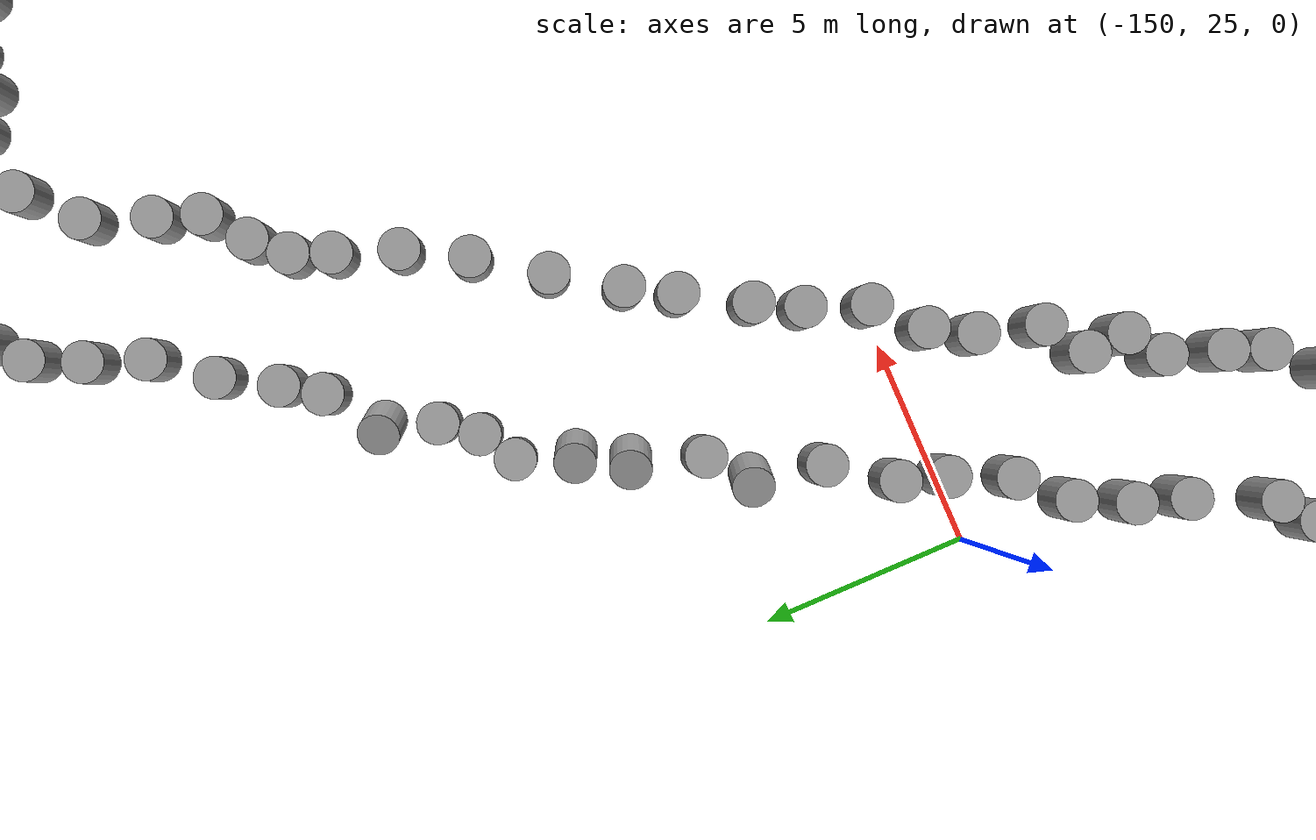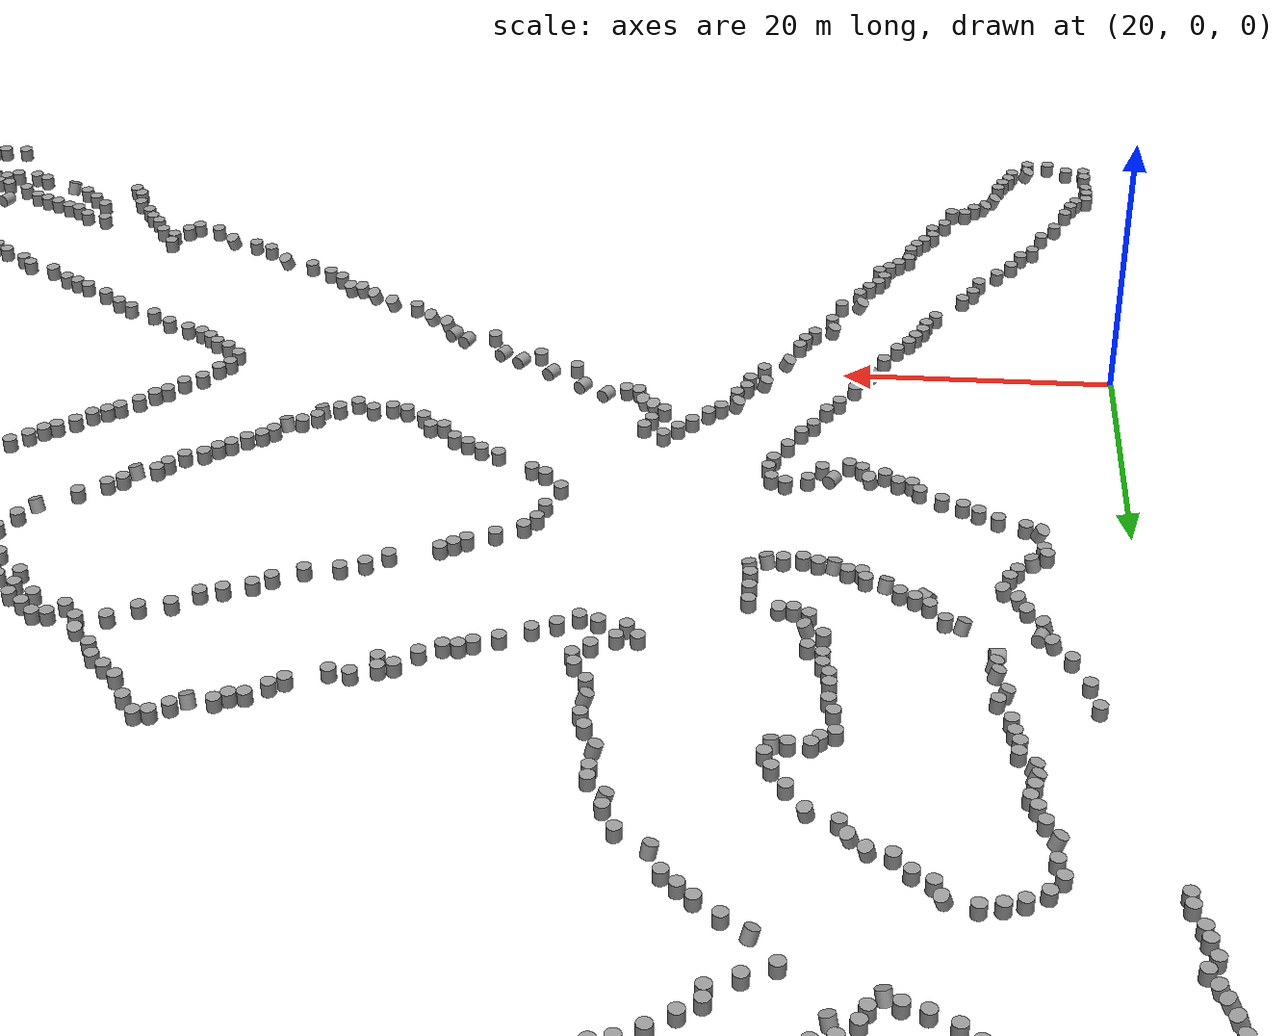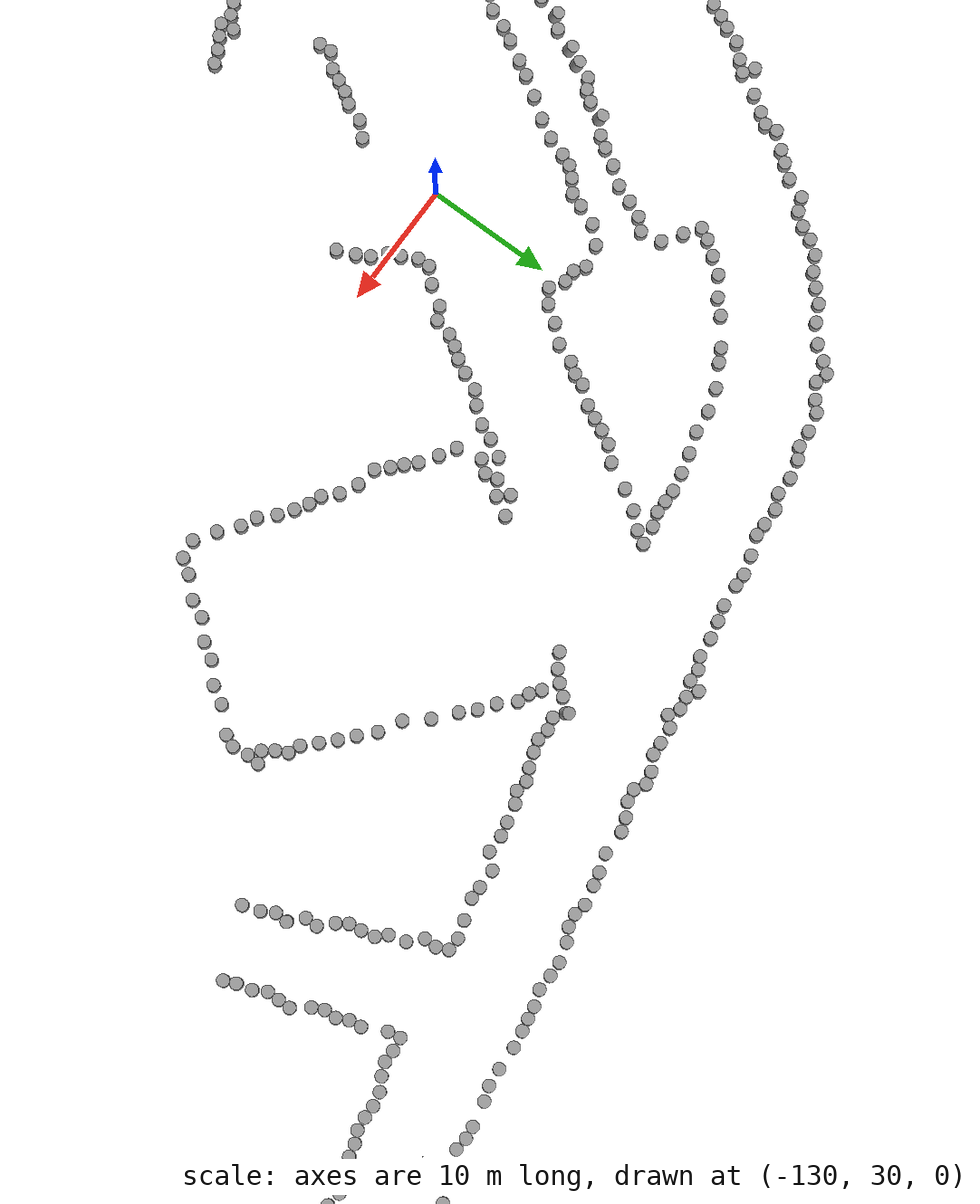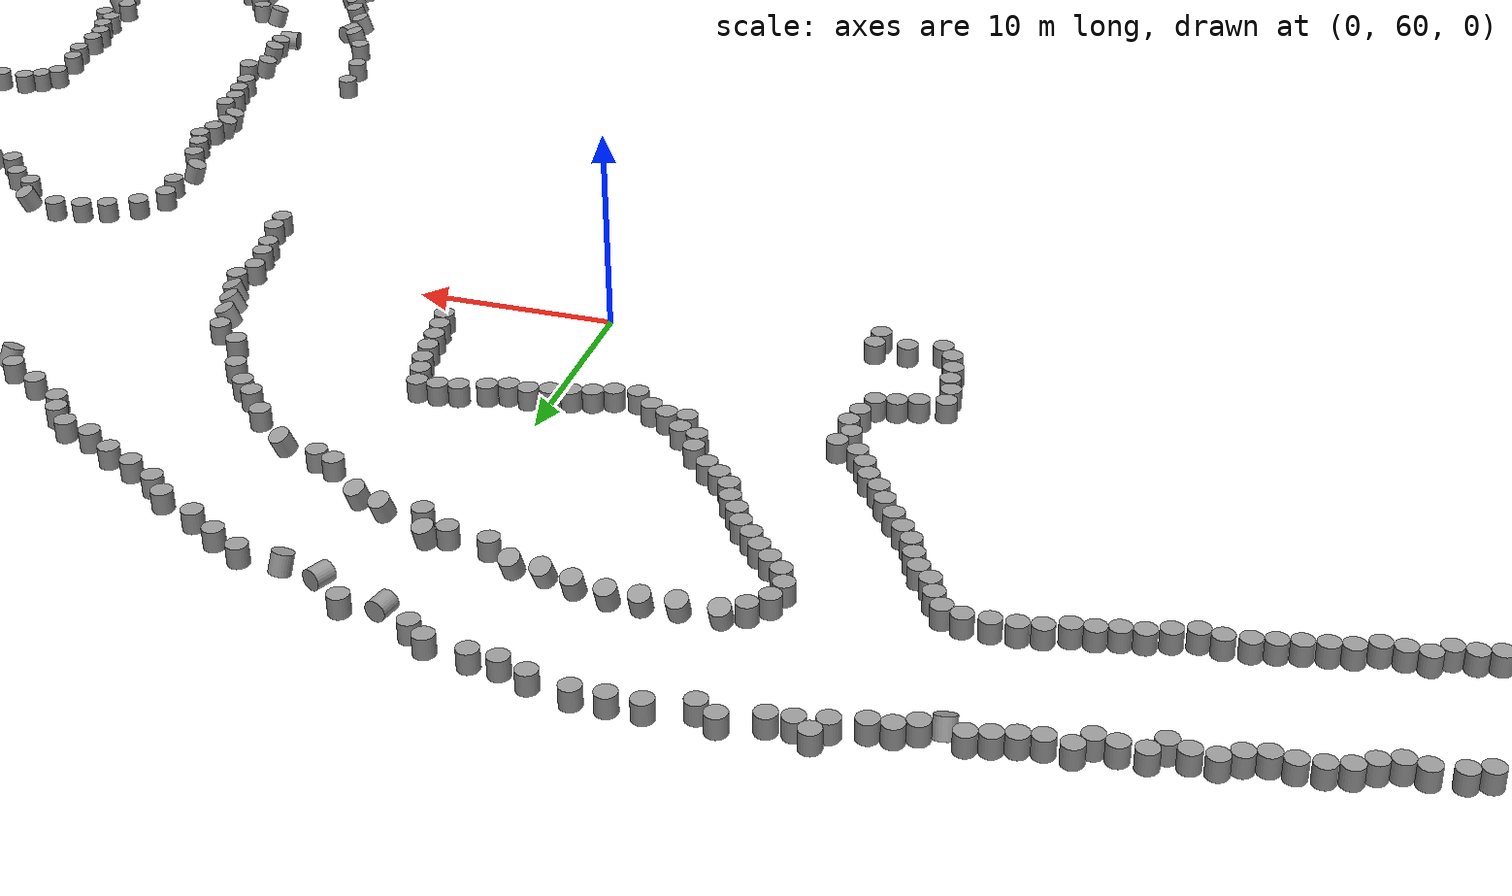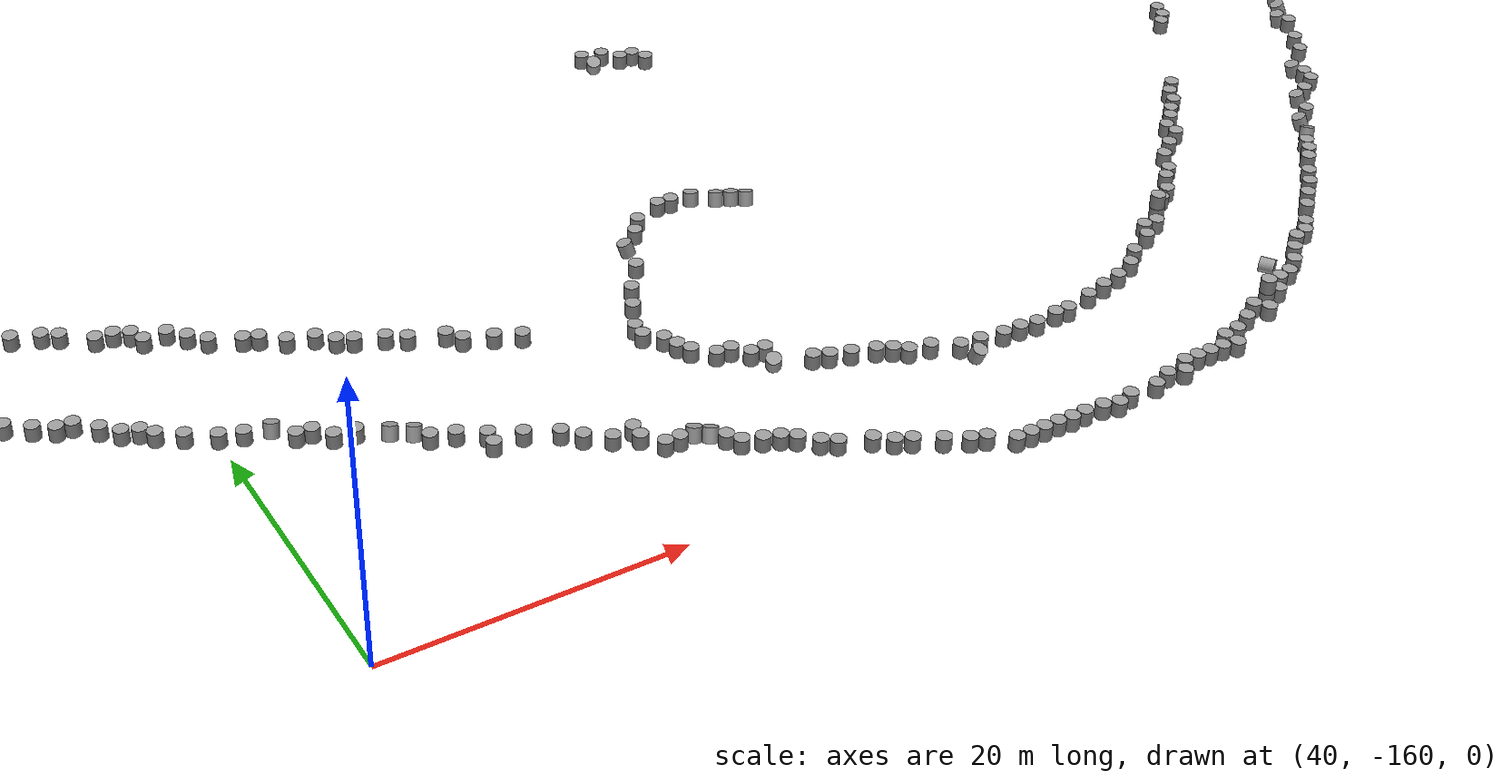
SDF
<sdf version="1.7">
 <world name="default">
  <gravity>0 0 -9.8</gravity>
  <magnetic_field>6e-06 2.3e-05 -4.2e-05</magnetic_field>
  <atmosphere type="adiabatic"/>
  <physics type="ode">
   <max_step_size>0.001</max_step_size>
   <real_time_factor>1</real_time_factor>
   <real_time_update_rate>1000</real_time_update_rate>
  </physics>
  <scene><ambient>0.4 0.4 0.4 1</ambient><background>0.7 0.7 0.7 1</background><shadows>1</shadows></scene>
  <light name="sun" type="directional">
   <pose>0 0 10 0 -0 0</pose>
   <diffuse>0.8 0.8 0.8 1</diffuse>
   <specular>0.2 0.2 0.2 1</specular>
   <attenuation>
    <range>1000</range>
    <constant>0.9</constant>
    <linear>0.01</linear>
    <quadratic>0.001</quadratic>
   </attenuation>
   <direction>-0.5 0.1 -0.9</direction>
   <spot><inner_angle>0</inner_angle><outer_angle>0</outer_angle><falloff>0</falloff></spot>
  </light>
  <spherical_coordinates>
   <surface_model>EARTH_WGS84</surface_model>
   <latitude_deg>0</latitude_deg>
   <longitude_deg>0</longitude_deg>
   <elevation>0</elevation>
   <heading_deg>0</heading_deg>
  </spherical_coordinates>
  <plugin name="gazebo_occupancy_map" filename="libgazebo_2Dmap_plugin.so">
   <map_resolution>0.1</map_resolution>
   <map_height>0.3</map_height>
   <map_size_x>500</map_size_x>
   <map_size_y>500</map_size_y>
   <init_robot_x>0</init_robot_x>
   <init_robot_y>0</init_robot_y>
  </plugin>
  <model name="unit_cylinder">
   <pose>-13.2877 58.6137 0.450308 0.000621 0.000106 0.001685</pose>
   <link name="link">
    <inertial>
     <mass>1</mass>
     <inertia><ixx>0.145833</ixx><ixy>0</ixy><ixz>0</ixz><iyy>0.145833</iyy><iyz>0</iyz><izz>0.125</izz></inertia>
    </inertial>
    <collision name="collision">
     <geometry><cylinder><radius>0.5</radius><length>1</length></cylinder></geometry>
    </collision>
    <visual name="visual">
     <geometry><cylinder><radius>0.5</radius><length>1</length></cylinder></geometry>
     <material>
      <script><name>Gazebo/Grey</name><uri>file://media/materials/scripts/gazebo.material</uri></script>
     </material>
    </visual>
   </link>
  </model>
  <model name="unit_cylinder_0">
   <pose>-13.2319 59.6229 0.450974 0.000694 0.000109 -0.000125</pose>
   <link name="link">
    <inertial>
     <mass>1</mass>
     <inertia><ixx>0.145833</ixx><ixy>0</ixy><ixz>0</ixz><iyy>0.145833</iyy><iyz>0</iyz><izz>0.125</izz></inertia>
    </inertial>
    <collision name="collision">
     <geometry><cylinder><radius>0.5</radius><length>1</length></cylinder></geometry>
    </collision>
    <visual name="visual">
     <geometry><cylinder><radius>0.5</radius><length>1</length></cylinder></geometry>
     <material>
      <script><name>Gazebo/Grey</name><uri>file://media/materials/scripts/gazebo.material</uri></script>
     </material>
    </visual>
   </link>
  </model>
  <model name="unit_cylinder_1">
   <pose>-14.8042 59.4447 0.451031 0.00068 0.000119 -0</pose>
   <link name="link">
    <inertial>
     <mass>1</mass>
     <inertia><ixx>0.145833</ixx><ixy>0</ixy><ixz>0</ixz><iyy>0.145833</iyy><iyz>0</iyz><izz>0.125</izz></inertia>
    </inertial>
    <collision name="collision">
     <geometry><cylinder><radius>0.5</radius><length>1</length></cylinder></geometry>
    </collision>
    <visual name="visual">
     <geometry><cylinder><radius>0.5</radius><length>1</length></cylinder></geometry>
     <material>
      <script><name>Gazebo/Grey</name><uri>file://media/materials/scripts/gazebo.material</uri></script>
     </material>
    </visual>
   </link>
  </model>
  <model name="unit_cylinder_2">
   <pose>-16.4622 59.0425 0.451021 0.000586 0.000205 -0.010843</pose>
   <link name="link">
    <inertial>
     <mass>1</mass>
     <inertia><ixx>0.145833</ixx><ixy>0</ixy><ixz>0</ixz><iyy>0.145833</iyy><iyz>0</iyz><izz>0.125</izz></inertia>
    </inertial>
    <collision name="collision">
     <geometry><cylinder><radius>0.5</radius><length>1</length></cylinder></geometry>
    </collision>
    <visual name="visual">
     <geometry><cylinder><radius>0.5</radius><length>1</length></cylinder></geometry>
     <material>
      <script><name>Gazebo/Grey</name><uri>file://media/materials/scripts/gazebo.material</uri></script>
     </material>
    </visual>
   </link>
  </model>
  <model name="unit_cylinder_3">
   <pose>-17.089 59.8221 0.451267 3.1e-05 -0.000119 -0.019749</pose>
   <link name="link">
    <inertial>
     <mass>1</mass>
     <inertia><ixx>0.145833</ixx><ixy>0</ixy><ixz>0</ixz><iyy>0.145833</iyy><iyz>0</iyz><izz>0.125</izz></inertia>
    </inertial>
    <collision name="collision">
     <geometry><cylinder><radius>0.5</radius><length>1</length></cylinder></geometry>
    </collision>
    <visual name="visual">
     <geometry><cylinder><radius>0.5</radius><length>1</length></cylinder></geometry>
     <material>
      <script><name>Gazebo/Grey</name><uri>file://media/materials/scripts/gazebo.material</uri></script>
     </material>
    </visual>
   </link>
  </model>
  <model name="unit_cylinder_4">
   <pose>-17.3881 60.8702 0.451265 3.2e-05 -0.000118 -6e-06</pose>
   <link name="link">
    <inertial>
     <mass>1</mass>
     <inertia><ixx>0.145833</ixx><ixy>0</ixy><ixz>0</ixz><iyy>0.145833</iyy><iyz>0</iyz><izz>0.125</izz></inertia>
    </inertial>
    <collision name="collision">
     <geometry><cylinder><radius>0.5</radius><length>1</length></cylinder></geometry>
    </collision>
    <visual name="visual">
     <geometry><cylinder><radius>0.5</radius><length>1</length></cylinder></geometry>
     <material>
      <script><name>Gazebo/Grey</name><uri>file://media/materials/scripts/gazebo.material</uri></script>
     </material>
    </visual>
   </link>
  </model>
  <model name="unit_cylinder_5">
   <pose>-17.5055 61.8917 0.451286 3.7e-05 -0.000119 0.004439</pose>
   <link name="link">
    <inertial>
     <mass>1</mass>
     <inertia><ixx>0.145833</ixx><ixy>0</ixy><ixz>0</ixz><iyy>0.145833</iyy><iyz>0</iyz><izz>0.125</izz></inertia>
    </inertial>
    <collision name="collision">
     <geometry><cylinder><radius>0.5</radius><length>1</length></cylinder></geometry>
    </collision>
    <visual name="visual">
     <geometry><cylinder><radius>0.5</radius><length>1</length></cylinder></geometry>
     <material>
      <script><name>Gazebo/Grey</name><uri>file://media/materials/scripts/gazebo.material</uri></script>
     </material>
    </visual>
   </link>
  </model>
  <model name="unit_cylinder_6">
   <pose>-17.7698 62.8564 0.451298 3.5e-05 -0.000105 0.000889</pose>
   <link name="link">
    <inertial>
     <mass>1</mass>
     <inertia><ixx>0.145833</ixx><ixy>0</ixy><ixz>0</ixz><iyy>0.145833</iyy><iyz>0</iyz><izz>0.125</izz></inertia>
    </inertial>
    <collision name="collision">
     <geometry><cylinder><radius>0.5</radius><length>1</length></cylinder></geometry>
    </collision>
    <visual name="visual">
     <geometry><cylinder><radius>0.5</radius><length>1</length></cylinder></geometry>
     <material>
      <script><name>Gazebo/Grey</name><uri>file://media/materials/scripts/gazebo.material</uri></script>
     </material>
    </visual>
   </link>
  </model>
  <model name="unit_cylinder_7">
   <pose>-17.8148 63.8554 0.45132 -6e-06 -1.4e-05 -0.001069</pose>
   <link name="link">
    <inertial>
     <mass>1</mass>
     <inertia><ixx>0.145833</ixx><ixy>0</ixy><ixz>0</ixz><iyy>0.145833</iyy><iyz>0</iyz><izz>0.125</izz></inertia>
    </inertial>
    <collision name="collision">
     <geometry><cylinder><radius>0.5</radius><length>1</length></cylinder></geometry>
    </collision>
    <visual name="visual">
     <geometry><cylinder><radius>0.5</radius><length>1</length></cylinder></geometry>
     <material>
      <script><name>Gazebo/Grey</name><uri>file://media/materials/scripts/gazebo.material</uri></script>
     </material>
    </visual>
   </link>
  </model>
  <model name="unit_cylinder_8">
   <pose>-16.5871 64.1577 0.451324 2e-06 -1e-06 -0.00302</pose>
   <link name="link">
    <inertial>
     <mass>1</mass>
     <inertia><ixx>0.145833</ixx><ixy>0</ixy><ixz>0</ixz><iyy>0.145833</iyy><iyz>0</iyz><izz>0.125</izz></inertia>
    </inertial>
    <collision name="collision">
     <geometry><cylinder><radius>0.5</radius><length>1</length></cylinder></geometry>
    </collision>
    <visual name="visual">
     <geometry><cylinder><radius>0.5</radius><length>1</length></cylinder></geometry>
     <material>
      <script><name>Gazebo/Grey</name><uri>file://media/materials/scripts/gazebo.material</uri></script>
     </material>
    </visual>
   </link>
  </model>
  <model name="unit_cylinder_9">
   <pose>-15.6312 64.4525 0.451317 -2e-06 2e-06 0.01303</pose>
   <link name="link">
    <inertial>
     <mass>1</mass>
     <inertia><ixx>0.145833</ixx><ixy>0</ixy><ixz>0</ixz><iyy>0.145833</iyy><iyz>0</iyz><izz>0.125</izz></inertia>
    </inertial>
    <collision name="collision">
     <geometry><cylinder><radius>0.5</radius><length>1</length></cylinder></geometry>
    </collision>
    <visual name="visual">
     <geometry><cylinder><radius>0.5</radius><length>1</length></cylinder></geometry>
     <material>
      <script><name>Gazebo/Grey</name><uri>file://media/materials/scripts/gazebo.material</uri></script>
     </material>
    </visual>
   </link>
  </model>
  <model name="unit_cylinder_10">
   <pose>-14.6467 64.6451 0.451318 0 3e-06 0.004446</pose>
   <link name="link">
    <inertial>
     <mass>1</mass>
     <inertia><ixx>0.145833</ixx><ixy>0</ixy><ixz>0</ixz><iyy>0.145833</iyy><iyz>0</iyz><izz>0.125</izz></inertia>
    </inertial>
    <collision name="collision">
     <geometry><cylinder><radius>0.5</radius><length>1</length></cylinder></geometry>
    </collision>
    <visual name="visual">
     <geometry><cylinder><radius>0.5</radius><length>1</length></cylinder></geometry>
     <material>
      <script><name>Gazebo/Grey</name><uri>file://media/materials/scripts/gazebo.material</uri></script>
     </material>
    </visual>
   </link>
  </model>
  <model name="unit_cylinder_11">
   <pose>-14.2367 65.749 0.450048 0.008672 0.007504 1.33666</pose>
   <link name="link">
    <inertial>
     <mass>1</mass>
     <inertia><ixx>0.145833</ixx><ixy>0</ixy><ixz>0</ixz><iyy>0.145833</iyy><iyz>0</iyz><izz>0.125</izz></inertia>
    </inertial>
    <collision name="collision">
     <geometry><cylinder><radius>0.5</radius><length>1</length></cylinder></geometry>
    </collision>
    <visual name="visual">
     <geometry><cylinder><radius>0.5</radius><length>1</length></cylinder></geometry>
     <material>
      <script><name>Gazebo/Grey</name><uri>file://media/materials/scripts/gazebo.material</uri></script>
     </material>
    </visual>
   </link>
  </model>
  <model name="unit_cylinder_12">
   <pose>-13.9889 66.7178 0.442074 -0.010171 0.005345 -0.60893</pose>
   <link name="link">
    <inertial>
     <mass>1</mass>
     <inertia><ixx>0.145833</ixx><ixy>0</ixy><ixz>0</ixz><iyy>0.145833</iyy><iyz>0</iyz><izz>0.125</izz></inertia>
    </inertial>
    <collision name="collision">
     <geometry><cylinder><radius>0.5</radius><length>1</length></cylinder></geometry>
    </collision>
    <visual name="visual">
     <geometry><cylinder><radius>0.5</radius><length>1</length></cylinder></geometry>
     <material>
      <script><name>Gazebo/Grey</name><uri>file://media/materials/scripts/gazebo.material</uri></script>
     </material>
    </visual>
   </link>
  </model>
  <model name="unit_cylinder_13">
   <pose>-14.3597 67.6466 0.44449 -0.004148 0.00065 -0.767738</pose>
   <link name="link">
    <inertial>
     <mass>1</mass>
     <inertia><ixx>0.145833</ixx><ixy>0</ixy><ixz>0</ixz><iyy>0.145833</iyy><iyz>0</iyz><izz>0.125</izz></inertia>
    </inertial>
    <collision name="collision">
     <geometry><cylinder><radius>0.5</radius><length>1</length></cylinder></geometry>
    </collision>
    <visual name="visual">
     <geometry><cylinder><radius>0.5</radius><length>1</length></cylinder></geometry>
     <material>
      <script><name>Gazebo/Grey</name><uri>file://media/materials/scripts/gazebo.material</uri></script>
     </material>
    </visual>
   </link>
  </model>
  <model name="unit_cylinder_14">
   <pose>-13.9774 68.5707 0.451699 -0.001057 0.004203 0.346594</pose>
   <link name="link">
    <inertial>
     <mass>1</mass>
     <inertia><ixx>0.145833</ixx><ixy>0</ixy><ixz>0</ixz><iyy>0.145833</iyy><iyz>0</iyz><izz>0.125</izz></inertia>
    </inertial>
    <collision name="collision">
     <geometry><cylinder><radius>0.5</radius><length>1</length></cylinder></geometry>
    </collision>
    <visual name="visual">
     <geometry><cylinder><radius>0.5</radius><length>1</length></cylinder></geometry>
     <material>
      <script><name>Gazebo/Grey</name><uri>file://media/materials/scripts/gazebo.material</uri></script>
     </material>
    </visual>
   </link>
  </model>
  <model name="unit_cylinder_15">
   <pose>-15.0704 69.1016 0.447427 0.002984 -0.002078 0.265853</pose>
   <link name="link">
    <inertial>
     <mass>1</mass>
     <inertia><ixx>0.145833</ixx><ixy>0</ixy><ixz>0</ixz><iyy>0.145833</iyy><iyz>0</iyz><izz>0.125</izz></inertia>
    </inertial>
    <collision name="collision">
     <geometry><cylinder><radius>0.5</radius><length>1</length></cylinder></geometry>
    </collision>
    <visual name="visual">
     <geometry><cylinder><radius>0.5</radius><length>1</length></cylinder></geometry>
     <material>
      <script><name>Gazebo/Grey</name><uri>file://media/materials/scripts/gazebo.material</uri></script>
     </material>
    </visual>
   </link>
  </model>
  <model name="unit_cylinder_16">
   <pose>-15.6303 69.9302 0.448226 0.002522 -0.000953 0.309914</pose>
   <link name="link">
    <inertial>
     <mass>1</mass>
     <inertia><ixx>0.145833</ixx><ixy>0</ixy><ixz>0</ixz><iyy>0.145833</iyy><iyz>0</iyz><izz>0.125</izz></inertia>
    </inertial>
    <collision name="collision">
     <geometry><cylinder><radius>0.5</radius><length>1</length></cylinder></geometry>
    </collision>
    <visual name="visual">
     <geometry><cylinder><radius>0.5</radius><length>1</length></cylinder></geometry>
     <material>
      <script><name>Gazebo/Grey</name><uri>file://media/materials/scripts/gazebo.material</uri></script>
     </material>
    </visual>
   </link>
  </model>
  <model name="unit_cylinder_17">
   <pose>-16.055 70.8371 0.449279 0.00276 -0.003907 -0.014795</pose>
   <link name="link">
    <inertial>
     <mass>1</mass>
     <inertia><ixx>0.145833</ixx><ixy>0</ixy><ixz>0</ixz><iyy>0.145833</iyy><iyz>0</iyz><izz>0.125</izz></inertia>
    </inertial>
    <collision name="collision">
     <geometry><cylinder><radius>0.5</radius><length>1</length></cylinder></geometry>
    </collision>
    <visual name="visual">
     <geometry><cylinder><radius>0.5</radius><length>1</length></cylinder></geometry>
     <material>
      <script><name>Gazebo/Grey</name><uri>file://media/materials/scripts/gazebo.material</uri></script>
     </material>
    </visual>
   </link>
  </model>
  <model name="unit_cylinder_18">
   <pose>-16.7299 71.6265 0.450127 0.000598 -0.000177 0.004047</pose>
   <link name="link">
    <inertial>
     <mass>1</mass>
     <inertia><ixx>0.145833</ixx><ixy>0</ixy><ixz>0</ixz><iyy>0.145833</iyy><iyz>0</iyz><izz>0.125</izz></inertia>
    </inertial>
    <collision name="collision">
     <geometry><cylinder><radius>0.5</radius><length>1</length></cylinder></geometry>
    </collision>
    <visual name="visual">
     <geometry><cylinder><radius>0.5</radius><length>1</length></cylinder></geometry>
     <material>
      <script><name>Gazebo/Grey</name><uri>file://media/materials/scripts/gazebo.material</uri></script>
     </material>
    </visual>
   </link>
  </model>
  <model name="unit_cylinder_19">
   <pose>-17.2532 72.5422 0.450888 0.000516 -0.000755 -5.7e-05</pose>
   <link name="link">
    <inertial>
     <mass>1</mass>
     <inertia><ixx>0.145833</ixx><ixy>0</ixy><ixz>0</ixz><iyy>0.145833</iyy><iyz>0</iyz><izz>0.125</izz></inertia>
    </inertial>
    <collision name="collision">
     <geometry><cylinder><radius>0.5</radius><length>1</length></cylinder></geometry>
    </collision>
    <visual name="visual">
     <geometry><cylinder><radius>0.5</radius><length>1</length></cylinder></geometry>
     <material>
      <script><name>Gazebo/Grey</name><uri>file://media/materials/scripts/gazebo.material</uri></script>
     </material>
    </visual>
   </link>
  </model>
  <model name="unit_cylinder_20">
   <pose>-17.9194 73.537 0.45131 1.4e-05 9e-06 0.000669</pose>
   <link name="link">
    <inertial>
     <mass>1</mass>
     <inertia><ixx>0.145833</ixx><ixy>0</ixy><ixz>0</ixz><iyy>0.145833</iyy><iyz>0</iyz><izz>0.125</izz></inertia>
    </inertial>
    <collision name="collision">
     <geometry><cylinder><radius>0.5</radius><length>1</length></cylinder></geometry>
    </collision>
    <visual name="visual">
     <geometry><cylinder><radius>0.5</radius><length>1</length></cylinder></geometry>
     <material>
      <script><name>Gazebo/Grey</name><uri>file://media/materials/scripts/gazebo.material</uri></script>
     </material>
    </visual>
   </link>
  </model>
  <model name="unit_cylinder_21">
   <pose>-18.5602 74.411 0.451304 7e-06 1e-05 9.9e-05</pose>
   <link name="link">
    <inertial>
     <mass>1</mass>
     <inertia><ixx>0.145833</ixx><ixy>0</ixy><ixz>0</ixz><iyy>0.145833</iyy><iyz>0</iyz><izz>0.125</izz></inertia>
    </inertial>
    <collision name="collision">
     <geometry><cylinder><radius>0.5</radius><length>1</length></cylinder></geometry>
    </collision>
    <visual name="visual">
     <geometry><cylinder><radius>0.5</radius><length>1</length></cylinder></geometry>
     <material>
      <script><name>Gazebo/Grey</name><uri>file://media/materials/scripts/gazebo.material</uri></script>
     </material>
    </visual>
   </link>
  </model>
  <model name="unit_cylinder_22">
   <pose>-19.1418 75.2245 0.451293 1e-06 -3e-06 0.001733</pose>
   <link name="link">
    <inertial>
     <mass>1</mass>
     <inertia><ixx>0.145833</ixx><ixy>0</ixy><ixz>0</ixz><iyy>0.145833</iyy><iyz>0</iyz><izz>0.125</izz></inertia>
    </inertial>
    <collision name="collision">
     <geometry><cylinder><radius>0.5</radius><length>1</length></cylinder></geometry>
    </collision>
    <visual name="visual">
     <geometry><cylinder><radius>0.5</radius><length>1</length></cylinder></geometry>
     <material>
      <script><name>Gazebo/Grey</name><uri>file://media/materials/scripts/gazebo.material</uri></script>
     </material>
    </visual>
   </link>
  </model>
  <model name="unit_cylinder_23">
   <pose>-19.5113 76.185 0.451305 1.8e-05 1e-06 0.017178</pose>
   <link name="link">
    <inertial>
     <mass>1</mass>
     <inertia><ixx>0.145833</ixx><ixy>0</ixy><ixz>0</ixz><iyy>0.145833</iyy><iyz>0</iyz><izz>0.125</izz></inertia>
    </inertial>
    <collision name="collision">
     <geometry><cylinder><radius>0.5</radius><length>1</length></cylinder></geometry>
    </collision>
    <visual name="visual">
     <geometry><cylinder><radius>0.5</radius><length>1</length></cylinder></geometry>
     <material>
      <script><name>Gazebo/Grey</name><uri>file://media/materials/scripts/gazebo.material</uri></script>
     </material>
    </visual>
   </link>
  </model>
  <model name="unit_cylinder_24">
   <pose>-19.9475 77.0849 0.451301 2.1e-05 -1e-06 -0.011678</pose>
   <link name="link">
    <inertial>
     <mass>1</mass>
     <inertia><ixx>0.145833</ixx><ixy>0</ixy><ixz>0</ixz><iyy>0.145833</iyy><iyz>0</iyz><izz>0.125</izz></inertia>
    </inertial>
    <collision name="collision">
     <geometry><cylinder><radius>0.5</radius><length>1</length></cylinder></geometry>
    </collision>
    <visual name="visual">
     <geometry><cylinder><radius>0.5</radius><length>1</length></cylinder></geometry>
     <material>
      <script><name>Gazebo/Grey</name><uri>file://media/materials/scripts/gazebo.material</uri></script>
     </material>
    </visual>
   </link>
  </model>
  <model name="unit_cylinder_25">
   <pose>-20.6426 77.8038 0.451297 2e-06 -5e-06 0.034095</pose>
   <link name="link">
    <inertial>
     <mass>1</mass>
     <inertia><ixx>0.145833</ixx><ixy>0</ixy><ixz>0</ixz><iyy>0.145833</iyy><iyz>0</iyz><izz>0.125</izz></inertia>
    </inertial>
    <collision name="collision">
     <geometry><cylinder><radius>0.5</radius><length>1</length></cylinder></geometry>
    </collision>
    <visual name="visual">
     <geometry><cylinder><radius>0.5</radius><length>1</length></cylinder></geometry>
     <material>
      <script><name>Gazebo/Grey</name><uri>file://media/materials/scripts/gazebo.material</uri></script>
     </material>
    </visual>
   </link>
  </model>
  <model name="unit_cylinder_26">
   <pose>-21.0312 78.7252 0.451299 9e-06 -1.4e-05 0.113391</pose>
   <link name="link">
    <inertial>
     <mass>1</mass>
     <inertia><ixx>0.145833</ixx><ixy>0</ixy><ixz>0</ixz><iyy>0.145833</iyy><iyz>0</iyz><izz>0.125</izz></inertia>
    </inertial>
    <collision name="collision">
     <geometry><cylinder><radius>0.5</radius><length>1</length></cylinder></geometry>
    </collision>
    <visual name="visual">
     <geometry><cylinder><radius>0.5</radius><length>1</length></cylinder></geometry>
     <material>
      <script><name>Gazebo/Grey</name><uri>file://media/materials/scripts/gazebo.material</uri></script>
     </material>
    </visual>
   </link>
  </model>
  <model name="unit_cylinder_27">
   <pose>-21.5664 79.57 0.451289 1e-06 -1.4e-05 0.025575</pose>
   <link name="link">
    <inertial>
     <mass>1</mass>
     <inertia><ixx>0.145833</ixx><ixy>0</ixy><ixz>0</ixz><iyy>0.145833</iyy><iyz>0</iyz><izz>0.125</izz></inertia>
    </inertial>
    <collision name="collision">
     <geometry><cylinder><radius>0.5</radius><length>1</length></cylinder></geometry>
    </collision>
    <visual name="visual">
     <geometry><cylinder><radius>0.5</radius><length>1</length></cylinder></geometry>
     <material>
      <script><name>Gazebo/Grey</name><uri>file://media/materials/scripts/gazebo.material</uri></script>
     </material>
    </visual>
   </link>
  </model>
  <model name="unit_cylinder_28">
   <pose>-22.5992 87.2027 0.452086 0.004535 0.000849 -0.012464</pose>
   <link name="link">
    <inertial>
     <mass>1</mass>
     <inertia><ixx>0.145833</ixx><ixy>0</ixy><ixz>0</ixz><iyy>0.145833</iyy><iyz>0</iyz><izz>0.125</izz></inertia>
    </inertial>
    <collision name="collision">
     <geometry><cylinder><radius>0.5</radius><length>1</length></cylinder></geometry>
    </collision>
    <visual name="visual">
     <geometry><cylinder><radius>0.5</radius><length>1</length></cylinder></geometry>
     <material>
      <script><name>Gazebo/Grey</name><uri>file://media/materials/scripts/gazebo.material</uri></script>
     </material>
    </visual>
   </link>
  </model>
  <model name="unit_cylinder_29">
   <pose>-21.7016 87.6433 0.453475 0.004662 0.001231 -0.073484</pose>
   <link name="link">
    <inertial>
     <mass>1</mass>
     <inertia><ixx>0.145833</ixx><ixy>0</ixy><ixz>0</ixz><iyy>0.145833</iyy><iyz>0</iyz><izz>0.125</izz></inertia>
    </inertial>
    <collision name="collision">
     <geometry><cylinder><radius>0.5</radius><length>1</length></cylinder></geometry>
    </collision>
    <visual name="visual">
     <geometry><cylinder><radius>0.5</radius><length>1</length></cylinder></geometry>
     <material>
      <script><name>Gazebo/Grey</name><uri>file://media/materials/scripts/gazebo.material</uri></script>
     </material>
    </visual>
   </link>
  </model>
  <model name="unit_cylinder_30">
   <pose>-20.6888 87.6672 0.452716 0.004649 0.000823 -0.00265</pose>
   <link name="link">
    <inertial>
     <mass>1</mass>
     <inertia><ixx>0.145833</ixx><ixy>0</ixy><ixz>0</ixz><iyy>0.145833</iyy><iyz>0</iyz><izz>0.125</izz></inertia>
    </inertial>
    <collision name="collision">
     <geometry><cylinder><radius>0.5</radius><length>1</length></cylinder></geometry>
    </collision>
    <visual name="visual">
     <geometry><cylinder><radius>0.5</radius><length>1</length></cylinder></geometry>
     <material>
      <script><name>Gazebo/Grey</name><uri>file://media/materials/scripts/gazebo.material</uri></script>
     </material>
    </visual>
   </link>
  </model>
  <model name="unit_cylinder_31">
   <pose>-19.2525 88.0542 0.453461 0.004626 0.001251 -0.17126</pose>
   <link name="link">
    <inertial>
     <mass>1</mass>
     <inertia><ixx>0.145833</ixx><ixy>0</ixy><ixz>0</ixz><iyy>0.145833</iyy><iyz>0</iyz><izz>0.125</izz></inertia>
    </inertial>
    <collision name="collision">
     <geometry><cylinder><radius>0.5</radius><length>1</length></cylinder></geometry>
    </collision>
    <visual name="visual">
     <geometry><cylinder><radius>0.5</radius><length>1</length></cylinder></geometry>
     <material>
      <script><name>Gazebo/Grey</name><uri>file://media/materials/scripts/gazebo.material</uri></script>
     </material>
    </visual>
   </link>
  </model>
  <model name="unit_cylinder_32">
   <pose>-18.7557 88.9221 0.457344 0.005127 0.000781 0.039913</pose>
   <link name="link">
    <inertial>
     <mass>1</mass>
     <inertia><ixx>0.145833</ixx><ixy>0</ixy><ixz>0</ixz><iyy>0.145833</iyy><iyz>0</iyz><izz>0.125</izz></inertia>
    </inertial>
    <collision name="collision">
     <geometry><cylinder><radius>0.5</radius><length>1</length></cylinder></geometry>
    </collision>
    <visual name="visual">
     <geometry><cylinder><radius>0.5</radius><length>1</length></cylinder></geometry>
     <material>
      <script><name>Gazebo/Grey</name><uri>file://media/materials/scripts/gazebo.material</uri></script>
     </material>
    </visual>
   </link>
  </model>
  <model name="unit_cylinder_33">
   <pose>-17.9369 88.3481 0.453737 0.003912 0.003043 -0.417717</pose>
   <link name="link">
    <inertial>
     <mass>1</mass>
     <inertia><ixx>0.145833</ixx><ixy>0</ixy><ixz>0</ixz><iyy>0.145833</iyy><iyz>0</iyz><izz>0.125</izz></inertia>
    </inertial>
    <collision name="collision">
     <geometry><cylinder><radius>0.5</radius><length>1</length></cylinder></geometry>
    </collision>
    <visual name="visual">
     <geometry><cylinder><radius>0.5</radius><length>1</length></cylinder></geometry>
     <material>
      <script><name>Gazebo/Grey</name><uri>file://media/materials/scripts/gazebo.material</uri></script>
     </material>
    </visual>
   </link>
  </model>
  <model name="unit_cylinder_34">
   <pose>-16.8325 88.4309 0.453164 0.004475 0.00168 -0.186595</pose>
   <link name="link">
    <inertial>
     <mass>1</mass>
     <inertia><ixx>0.145833</ixx><ixy>0</ixy><ixz>0</ixz><iyy>0.145833</iyy><iyz>0</iyz><izz>0.125</izz></inertia>
    </inertial>
    <collision name="collision">
     <geometry><cylinder><radius>0.5</radius><length>1</length></cylinder></geometry>
    </collision>
    <visual name="visual">
     <geometry><cylinder><radius>0.5</radius><length>1</length></cylinder></geometry>
     <material>
      <script><name>Gazebo/Grey</name><uri>file://media/materials/scripts/gazebo.material</uri></script>
     </material>
    </visual>
   </link>
  </model>
  <model name="unit_cylinder_35">
   <pose>-12.5083 76.6796 0.451255 -2.7e-05 1.7e-05 -0.022025</pose>
   <link name="link">
    <inertial>
     <mass>1</mass>
     <inertia><ixx>0.145833</ixx><ixy>0</ixy><ixz>0</ixz><iyy>0.145833</iyy><iyz>0</iyz><izz>0.125</izz></inertia>
    </inertial>
    <collision name="collision">
     <geometry><cylinder><radius>0.5</radius><length>1</length></cylinder></geometry>
    </collision>
    <visual name="visual">
     <geometry><cylinder><radius>0.5</radius><length>1</length></cylinder></geometry>
     <material>
      <script><name>Gazebo/Grey</name><uri>file://media/materials/scripts/gazebo.material</uri></script>
     </material>
    </visual>
   </link>
  </model>
  <model name="unit_cylinder_36">
   <pose>-13.1208 77.4755 0.451262 -1.6e-05 2.6e-05 0.080301</pose>
   <link name="link">
    <inertial>
     <mass>1</mass>
     <inertia><ixx>0.145833</ixx><ixy>0</ixy><ixz>0</ixz><iyy>0.145833</iyy><iyz>0</iyz><izz>0.125</izz></inertia>
    </inertial>
    <collision name="collision">
     <geometry><cylinder><radius>0.5</radius><length>1</length></cylinder></geometry>
    </collision>
    <visual name="visual">
     <geometry><cylinder><radius>0.5</radius><length>1</length></cylinder></geometry>
     <material>
      <script><name>Gazebo/Grey</name><uri>file://media/materials/scripts/gazebo.material</uri></script>
     </material>
    </visual>
   </link>
  </model>
  <model name="unit_cylinder_37">
   <pose>-13.8134 78.2059 0.451267 -2.7e-05 3.7e-05 -0.002243</pose>
   <link name="link">
    <inertial>
     <mass>1</mass>
     <inertia><ixx>0.145833</ixx><ixy>0</ixy><ixz>0</ixz><iyy>0.145833</iyy><iyz>0</iyz><izz>0.125</izz></inertia>
    </inertial>
    <collision name="collision">
     <geometry><cylinder><radius>0.5</radius><length>1</length></cylinder></geometry>
    </collision>
    <visual name="visual">
     <geometry><cylinder><radius>0.5</radius><length>1</length></cylinder></geometry>
     <material>
      <script><name>Gazebo/Grey</name><uri>file://media/materials/scripts/gazebo.material</uri></script>
     </material>
    </visual>
   </link>
  </model>
  <model name="unit_cylinder_38">
   <pose>-14.537 78.9318 0.451274 -4.1e-05 7.2e-05 -0.001766</pose>
   <link name="link">
    <inertial>
     <mass>1</mass>
     <inertia><ixx>0.145833</ixx><ixy>0</ixy><ixz>0</ixz><iyy>0.145833</iyy><iyz>0</iyz><izz>0.125</izz></inertia>
    </inertial>
    <collision name="collision">
     <geometry><cylinder><radius>0.5</radius><length>1</length></cylinder></geometry>
    </collision>
    <visual name="visual">
     <geometry><cylinder><radius>0.5</radius><length>1</length></cylinder></geometry>
     <material>
      <script><name>Gazebo/Grey</name><uri>file://media/materials/scripts/gazebo.material</uri></script>
     </material>
    </visual>
   </link>
  </model>
  <model name="unit_cylinder_39">
   <pose>-14.9355 79.861 0.451264 -2e-05 3.8e-05 -0.021847</pose>
   <link name="link">
    <inertial>
     <mass>1</mass>
     <inertia><ixx>0.145833</ixx><ixy>0</ixy><ixz>0</ixz><iyy>0.145833</iyy><iyz>0</iyz><izz>0.125</izz></inertia>
    </inertial>
    <collision name="collision">
     <geometry><cylinder><radius>0.5</radius><length>1</length></cylinder></geometry>
    </collision>
    <visual name="visual">
     <geometry><cylinder><radius>0.5</radius><length>1</length></cylinder></geometry>
     <material>
      <script><name>Gazebo/Grey</name><uri>file://media/materials/scripts/gazebo.material</uri></script>
     </material>
    </visual>
   </link>
  </model>
  <model name="unit_cylinder_40">
   <pose>-14.6637 80.8568 0.451244 1e-06 1e-05 0.000432</pose>
   <link name="link">
    <inertial>
     <mass>1</mass>
     <inertia><ixx>0.145833</ixx><ixy>0</ixy><ixz>0</ixz><iyy>0.145833</iyy><iyz>0</iyz><izz>0.125</izz></inertia>
    </inertial>
    <collision name="collision">
     <geometry><cylinder><radius>0.5</radius><length>1</length></cylinder></geometry>
    </collision>
    <visual name="visual">
     <geometry><cylinder><radius>0.5</radius><length>1</length></cylinder></geometry>
     <material>
      <script><name>Gazebo/Grey</name><uri>file://media/materials/scripts/gazebo.material</uri></script>
     </material>
    </visual>
   </link>
  </model>
  <model name="unit_cylinder_41">
   <pose>-13.9151 81.6756 0.451264 6.1e-05 8e-06 0.001789</pose>
   <link name="link">
    <inertial>
     <mass>1</mass>
     <inertia><ixx>0.145833</ixx><ixy>0</ixy><ixz>0</ixz><iyy>0.145833</iyy><iyz>0</iyz><izz>0.125</izz></inertia>
    </inertial>
    <collision name="collision">
     <geometry><cylinder><radius>0.5</radius><length>1</length></cylinder></geometry>
    </collision>
    <visual name="visual">
     <geometry><cylinder><radius>0.5</radius><length>1</length></cylinder></geometry>
     <material>
      <script><name>Gazebo/Grey</name><uri>file://media/materials/scripts/gazebo.material</uri></script>
     </material>
    </visual>
   </link>
  </model>
  <model name="unit_cylinder_42">
   <pose>-12.9175 82.0752 0.393131 -0.356614 0.009683 0.021233</pose>
   <link name="link">
    <inertial>
     <mass>1</mass>
     <inertia><ixx>0.145833</ixx><ixy>0</ixy><ixz>0</ixz><iyy>0.145833</iyy><iyz>0</iyz><izz>0.125</izz></inertia>
    </inertial>
    <collision name="collision">
     <geometry><cylinder><radius>0.5</radius><length>1</length></cylinder></geometry>
    </collision>
    <visual name="visual">
     <geometry><cylinder><radius>0.5</radius><length>1</length></cylinder></geometry>
     <material>
      <script><name>Gazebo/Grey</name><uri>file://media/materials/scripts/gazebo.material</uri></script>
     </material>
    </visual>
   </link>
  </model>
  <model name="unit_cylinder_43">
   <pose>-11.8223 75.9519 0.451248 1e-06 -4e-06 -0.020972</pose>
   <link name="link">
    <inertial>
     <mass>1</mass>
     <inertia><ixx>0.145833</ixx><ixy>0</ixy><ixz>0</ixz><iyy>0.145833</iyy><iyz>0</iyz><izz>0.125</izz></inertia>
    </inertial>
    <collision name="collision">
     <geometry><cylinder><radius>0.5</radius><length>1</length></cylinder></geometry>
    </collision>
    <visual name="visual">
     <geometry><cylinder><radius>0.5</radius><length>1</length></cylinder></geometry>
     <material>
      <script><name>Gazebo/Grey</name><uri>file://media/materials/scripts/gazebo.material</uri></script>
     </material>
    </visual>
   </link>
  </model>
  <model name="unit_cylinder_44">
   <pose>-11.3444 75.0735 0.451256 -1.6e-05 2.1e-05 -0.008671</pose>
   <link name="link">
    <inertial>
     <mass>1</mass>
     <inertia><ixx>0.145833</ixx><ixy>0</ixy><ixz>0</ixz><iyy>0.145833</iyy><iyz>0</iyz><izz>0.125</izz></inertia>
    </inertial>
    <collision name="collision">
     <geometry><cylinder><radius>0.5</radius><length>1</length></cylinder></geometry>
    </collision>
    <visual name="visual">
     <geometry><cylinder><radius>0.5</radius><length>1</length></cylinder></geometry>
     <material>
      <script><name>Gazebo/Grey</name><uri>file://media/materials/scripts/gazebo.material</uri></script>
     </material>
    </visual>
   </link>
  </model>
  <model name="unit_cylinder_45">
   <pose>-10.7823 74.2444 0.451264 -1.4e-05 2.1e-05 0.062925</pose>
   <link name="link">
    <inertial>
     <mass>1</mass>
     <inertia><ixx>0.145833</ixx><ixy>0</ixy><ixz>0</ixz><iyy>0.145833</iyy><iyz>0</iyz><izz>0.125</izz></inertia>
    </inertial>
    <collision name="collision">
     <geometry><cylinder><radius>0.5</radius><length>1</length></cylinder></geometry>
    </collision>
    <visual name="visual">
     <geometry><cylinder><radius>0.5</radius><length>1</length></cylinder></geometry>
     <material>
      <script><name>Gazebo/Grey</name><uri>file://media/materials/scripts/gazebo.material</uri></script>
     </material>
    </visual>
   </link>
  </model>
  <model name="unit_cylinder_46">
   <pose>-10.4174 73.3134 0.451268 -1.8e-05 2.4e-05 0.006692</pose>
   <link name="link">
    <inertial>
     <mass>1</mass>
     <inertia><ixx>0.145833</ixx><ixy>0</ixy><ixz>0</ixz><iyy>0.145833</iyy><iyz>0</iyz><izz>0.125</izz></inertia>
    </inertial>
    <collision name="collision">
     <geometry><cylinder><radius>0.5</radius><length>1</length></cylinder></geometry>
    </collision>
    <visual name="visual">
     <geometry><cylinder><radius>0.5</radius><length>1</length></cylinder></geometry>
     <material>
      <script><name>Gazebo/Grey</name><uri>file://media/materials/scripts/gazebo.material</uri></script>
     </material>
    </visual>
   </link>
  </model>
  <model name="unit_cylinder_47">
   <pose>-9.7287 72.5883 0.451269 -1e-05 1.5e-05 -0.033561</pose>
   <link name="link">
    <inertial>
     <mass>1</mass>
     <inertia><ixx>0.145833</ixx><ixy>0</ixy><ixz>0</ixz><iyy>0.145833</iyy><iyz>0</iyz><izz>0.125</izz></inertia>
    </inertial>
    <collision name="collision">
     <geometry><cylinder><radius>0.5</radius><length>1</length></cylinder></geometry>
    </collision>
    <visual name="visual">
     <geometry><cylinder><radius>0.5</radius><length>1</length></cylinder></geometry>
     <material>
      <script><name>Gazebo/Grey</name><uri>file://media/materials/scripts/gazebo.material</uri></script>
     </material>
    </visual>
   </link>
  </model>
  <model name="unit_cylinder_48">
   <pose>-8.95259 71.9577 0.451261 1e-06 1e-05 0.017317</pose>
   <link name="link">
    <inertial>
     <mass>1</mass>
     <inertia><ixx>0.145833</ixx><ixy>0</ixy><ixz>0</ixz><iyy>0.145833</iyy><iyz>0</iyz><izz>0.125</izz></inertia>
    </inertial>
    <collision name="collision">
     <geometry><cylinder><radius>0.5</radius><length>1</length></cylinder></geometry>
    </collision>
    <visual name="visual">
     <geometry><cylinder><radius>0.5</radius><length>1</length></cylinder></geometry>
     <material>
      <script><name>Gazebo/Grey</name><uri>file://media/materials/scripts/gazebo.material</uri></script>
     </material>
    </visual>
   </link>
  </model>
  <model name="unit_cylinder_49">
   <pose>-7.97474 70.862 0.447871 0.001215 0.009391 0.1193</pose>
   <link name="link">
    <inertial>
     <mass>1</mass>
     <inertia><ixx>0.145833</ixx><ixy>0</ixy><ixz>0</ixz><iyy>0.145833</iyy><iyz>0</iyz><izz>0.125</izz></inertia>
    </inertial>
    <collision name="collision">
     <geometry><cylinder><radius>0.5</radius><length>1</length></cylinder></geometry>
    </collision>
    <visual name="visual">
     <geometry><cylinder><radius>0.5</radius><length>1</length></cylinder></geometry>
     <material>
      <script><name>Gazebo/Grey</name><uri>file://media/materials/scripts/gazebo.material</uri></script>
     </material>
    </visual>
   </link>
  </model>
  <model name="unit_cylinder_50">
   <pose>-7.78796 69.8796 0.446326 -0.000557 0.008721 -0.088192</pose>
   <link name="link">
    <inertial>
     <mass>1</mass>
     <inertia><ixx>0.145833</ixx><ixy>0</ixy><ixz>0</ixz><iyy>0.145833</iyy><iyz>0</iyz><izz>0.125</izz></inertia>
    </inertial>
    <collision name="collision">
     <geometry><cylinder><radius>0.5</radius><length>1</length></cylinder></geometry>
    </collision>
    <visual name="visual">
     <geometry><cylinder><radius>0.5</radius><length>1</length></cylinder></geometry>
     <material>
      <script><name>Gazebo/Grey</name><uri>file://media/materials/scripts/gazebo.material</uri></script>
     </material>
    </visual>
   </link>
  </model>
  <model name="unit_cylinder_51">
   <pose>-6.86321 69.499 0.442492 0.009146 -0.003673 0.965866</pose>
   <link name="link">
    <inertial>
     <mass>1</mass>
     <inertia><ixx>0.145833</ixx><ixy>0</ixy><ixz>0</ixz><iyy>0.145833</iyy><iyz>0</iyz><izz>0.125</izz></inertia>
    </inertial>
    <collision name="collision">
     <geometry><cylinder><radius>0.5</radius><length>1</length></cylinder></geometry>
    </collision>
    <visual name="visual">
     <geometry><cylinder><radius>0.5</radius><length>1</length></cylinder></geometry>
     <material>
      <script><name>Gazebo/Grey</name><uri>file://media/materials/scripts/gazebo.material</uri></script>
     </material>
    </visual>
   </link>
  </model>
  <model name="unit_cylinder_52">
   <pose>-6.84671 68.4959 0.438635 0.015809 -0.006475 -0.107076</pose>
   <link name="link">
    <inertial>
     <mass>1</mass>
     <inertia><ixx>0.145833</ixx><ixy>0</ixy><ixz>0</ixz><iyy>0.145833</iyy><iyz>0</iyz><izz>0.125</izz></inertia>
    </inertial>
    <collision name="collision">
     <geometry><cylinder><radius>0.5</radius><length>1</length></cylinder></geometry>
    </collision>
    <visual name="visual">
     <geometry><cylinder><radius>0.5</radius><length>1</length></cylinder></geometry>
     <material>
      <script><name>Gazebo/Grey</name><uri>file://media/materials/scripts/gazebo.material</uri></script>
     </material>
    </visual>
   </link>
  </model>
  <model name="unit_cylinder_53">
   <pose>-5.8475 68.4559 0.440829 -0.000809 -0.00788 0.380203</pose>
   <link name="link">
    <inertial>
     <mass>1</mass>
     <inertia><ixx>0.145833</ixx><ixy>0</ixy><ixz>0</ixz><iyy>0.145833</iyy><iyz>0</iyz><izz>0.125</izz></inertia>
    </inertial>
    <collision name="collision">
     <geometry><cylinder><radius>0.5</radius><length>1</length></cylinder></geometry>
    </collision>
    <visual name="visual">
     <geometry><cylinder><radius>0.5</radius><length>1</length></cylinder></geometry>
     <material>
      <script><name>Gazebo/Grey</name><uri>file://media/materials/scripts/gazebo.material</uri></script>
     </material>
    </visual>
   </link>
  </model>
  <model name="unit_cylinder_54">
   <pose>-4.95694 68.0011 0.446621 0.002569 -0.007493 -0.052175</pose>
   <link name="link">
    <inertial>
     <mass>1</mass>
     <inertia><ixx>0.145833</ixx><ixy>0</ixy><ixz>0</ixz><iyy>0.145833</iyy><iyz>0</iyz><izz>0.125</izz></inertia>
    </inertial>
    <collision name="collision">
     <geometry><cylinder><radius>0.5</radius><length>1</length></cylinder></geometry>
    </collision>
    <visual name="visual">
     <geometry><cylinder><radius>0.5</radius><length>1</length></cylinder></geometry>
     <material>
      <script><name>Gazebo/Grey</name><uri>file://media/materials/scripts/gazebo.material</uri></script>
     </material>
    </visual>
   </link>
  </model>
  <model name="unit_cylinder_55">
   <pose>-4.0118 67.1475 0.451284 0 -6e-06 -1e-06</pose>
   <link name="link">
    <inertial>
     <mass>1</mass>
     <inertia><ixx>0.145833</ixx><ixy>0</ixy><ixz>0</ixz><iyy>0.145833</iyy><iyz>0</iyz><izz>0.125</izz></inertia>
    </inertial>
    <collision name="collision">
     <geometry><cylinder><radius>0.5</radius><length>1</length></cylinder></geometry>
    </collision>
    <visual name="visual">
     <geometry><cylinder><radius>0.5</radius><length>1</length></cylinder></geometry>
     <material>
      <script><name>Gazebo/Grey</name><uri>file://media/materials/scripts/gazebo.material</uri></script>
     </material>
    </visual>
   </link>
  </model>
  <model name="unit_cylinder_56">
   <pose>-2.88538 67.2905 0.451279 0 1e-06 -0.001361</pose>
   <link name="link">
    <inertial>
     <mass>1</mass>
     <inertia><ixx>0.145833</ixx><ixy>0</ixy><ixz>0</ixz><iyy>0.145833</iyy><iyz>0</iyz><izz>0.125</izz></inertia>
    </inertial>
    <collision name="collision">
     <geometry><cylinder><radius>0.5</radius><length>1</length></cylinder></geometry>
    </collision>
    <visual name="visual">
     <geometry><cylinder><radius>0.5</radius><length>1</length></cylinder></geometry>
     <material>
      <script><name>Gazebo/Grey</name><uri>file://media/materials/scripts/gazebo.material</uri></script>
     </material>
    </visual>
   </link>
  </model>
  <model name="unit_cylinder_57">
   <pose>-1.95558 67.6586 0.451281 5e-06 3e-06 0.028029</pose>
   <link name="link">
    <inertial>
     <mass>1</mass>
     <inertia><ixx>0.145833</ixx><ixy>0</ixy><ixz>0</ixz><iyy>0.145833</iyy><iyz>0</iyz><izz>0.125</izz></inertia>
    </inertial>
    <collision name="collision">
     <geometry><cylinder><radius>0.5</radius><length>1</length></cylinder></geometry>
    </collision>
    <visual name="visual">
     <geometry><cylinder><radius>0.5</radius><length>1</length></cylinder></geometry>
     <material>
      <script><name>Gazebo/Grey</name><uri>file://media/materials/scripts/gazebo.material</uri></script>
     </material>
    </visual>
   </link>
  </model>
  <model name="unit_cylinder_58">
   <pose>-0.982608 67.8954 0.451281 2e-06 3e-06 0.042812</pose>
   <link name="link">
    <inertial>
     <mass>1</mass>
     <inertia><ixx>0.145833</ixx><ixy>0</ixy><ixz>0</ixz><iyy>0.145833</iyy><iyz>0</iyz><izz>0.125</izz></inertia>
    </inertial>
    <collision name="collision">
     <geometry><cylinder><radius>0.5</radius><length>1</length></cylinder></geometry>
    </collision>
    <visual name="visual">
     <geometry><cylinder><radius>0.5</radius><length>1</length></cylinder></geometry>
     <material>
      <script><name>Gazebo/Grey</name><uri>file://media/materials/scripts/gazebo.material</uri></script>
     </material>
    </visual>
   </link>
  </model>
  <model name="unit_cylinder_59">
   <pose>-6.2e-05 68.0831 0.451278 1e-06 2e-06 0.013408</pose>
   <link name="link">
    <inertial>
     <mass>1</mass>
     <inertia><ixx>0.145833</ixx><ixy>0</ixy><ixz>0</ixz><iyy>0.145833</iyy><iyz>0</iyz><izz>0.125</izz></inertia>
    </inertial>
    <collision name="collision">
     <geometry><cylinder><radius>0.5</radius><length>1</length></cylinder></geometry>
    </collision>
    <visual name="visual">
     <geometry><cylinder><radius>0.5</radius><length>1</length></cylinder></geometry>
     <material>
      <script><name>Gazebo/Grey</name><uri>file://media/materials/scripts/gazebo.material</uri></script>
     </material>
    </visual>
   </link>
  </model>
  <model name="unit_cylinder_60">
   <pose>0.975299 68.308 0.451268 0 1e-06 0.001793</pose>
   <link name="link">
    <inertial>
     <mass>1</mass>
     <inertia><ixx>0.145833</ixx><ixy>0</ixy><ixz>0</ixz><iyy>0.145833</iyy><iyz>0</iyz><izz>0.125</izz></inertia>
    </inertial>
    <collision name="collision">
     <geometry><cylinder><radius>0.5</radius><length>1</length></cylinder></geometry>
    </collision>
    <visual name="visual">
     <geometry><cylinder><radius>0.5</radius><length>1</length></cylinder></geometry>
     <material>
      <script><name>Gazebo/Grey</name><uri>file://media/materials/scripts/gazebo.material</uri></script>
     </material>
    </visual>
   </link>
  </model>
  <model name="unit_cylinder_61">
   <pose>1.97258 68.2231 0.451278 -1.2e-05 -4e-06 0.012077</pose>
   <link name="link">
    <inertial>
     <mass>1</mass>
     <inertia><ixx>0.145833</ixx><ixy>0</ixy><ixz>0</ixz><iyy>0.145833</iyy><iyz>0</iyz><izz>0.125</izz></inertia>
    </inertial>
    <collision name="collision">
     <geometry><cylinder><radius>0.5</radius><length>1</length></cylinder></geometry>
    </collision>
    <visual name="visual">
     <geometry><cylinder><radius>0.5</radius><length>1</length></cylinder></geometry>
     <material>
      <script><name>Gazebo/Grey</name><uri>file://media/materials/scripts/gazebo.material</uri></script>
     </material>
    </visual>
   </link>
  </model>
  <model name="unit_cylinder_62">
   <pose>2.91678 68.557 0.451274 -2e-06 1e-06 0.006718</pose>
   <link name="link">
    <inertial>
     <mass>1</mass>
     <inertia><ixx>0.145833</ixx><ixy>0</ixy><ixz>0</ixz><iyy>0.145833</iyy><iyz>0</iyz><izz>0.125</izz></inertia>
    </inertial>
    <collision name="collision">
     <geometry><cylinder><radius>0.5</radius><length>1</length></cylinder></geometry>
    </collision>
    <visual name="visual">
     <geometry><cylinder><radius>0.5</radius><length>1</length></cylinder></geometry>
     <material>
      <script><name>Gazebo/Grey</name><uri>file://media/materials/scripts/gazebo.material</uri></script>
     </material>
    </visual>
   </link>
  </model>
  <model name="unit_cylinder_63">
   <pose>7.47351 62.8998 0.451274 1.9e-05 -1.1e-05 -0.000321</pose>
   <link name="link">
    <inertial>
     <mass>1</mass>
     <inertia><ixx>0.145833</ixx><ixy>0</ixy><ixz>0</ixz><iyy>0.145833</iyy><iyz>0</iyz><izz>0.125</izz></inertia>
    </inertial>
    <collision name="collision">
     <geometry><cylinder><radius>0.5</radius><length>1</length></cylinder></geometry>
    </collision>
    <visual name="visual">
     <geometry><cylinder><radius>0.5</radius><length>1</length></cylinder></geometry>
     <material>
      <script><name>Gazebo/Grey</name><uri>file://media/materials/scripts/gazebo.material</uri></script>
     </material>
    </visual>
   </link>
  </model>
  <model name="unit_cylinder_64">
   <pose>7.2899 63.8961 0.451271 -2.1e-05 5.3e-05 0.002016</pose>
   <link name="link">
    <inertial>
     <mass>1</mass>
     <inertia><ixx>0.145833</ixx><ixy>0</ixy><ixz>0</ixz><iyy>0.145833</iyy><iyz>0</iyz><izz>0.125</izz></inertia>
    </inertial>
    <collision name="collision">
     <geometry><cylinder><radius>0.5</radius><length>1</length></cylinder></geometry>
    </collision>
    <visual name="visual">
     <geometry><cylinder><radius>0.5</radius><length>1</length></cylinder></geometry>
     <material>
      <script><name>Gazebo/Grey</name><uri>file://media/materials/scripts/gazebo.material</uri></script>
     </material>
    </visual>
   </link>
  </model>
  <model name="unit_cylinder_65">
   <pose>7.13481 64.888 0.451264 -1.5e-05 6.5e-05 -0.002344</pose>
   <link name="link">
    <inertial>
     <mass>1</mass>
     <inertia><ixx>0.145833</ixx><ixy>0</ixy><ixz>0</ixz><iyy>0.145833</iyy><iyz>0</iyz><izz>0.125</izz></inertia>
    </inertial>
    <collision name="collision">
     <geometry><cylinder><radius>0.5</radius><length>1</length></cylinder></geometry>
    </collision>
    <visual name="visual">
     <geometry><cylinder><radius>0.5</radius><length>1</length></cylinder></geometry>
     <material>
      <script><name>Gazebo/Grey</name><uri>file://media/materials/scripts/gazebo.material</uri></script>
     </material>
    </visual>
   </link>
  </model>
  <model name="unit_cylinder_66">
   <pose>6.99698 65.9477 0.451263 -7e-06 4.4e-05 -0.009656</pose>
   <link name="link">
    <inertial>
     <mass>1</mass>
     <inertia><ixx>0.145833</ixx><ixy>0</ixy><ixz>0</ixz><iyy>0.145833</iyy><iyz>0</iyz><izz>0.125</izz></inertia>
    </inertial>
    <collision name="collision">
     <geometry><cylinder><radius>0.5</radius><length>1</length></cylinder></geometry>
    </collision>
    <visual name="visual">
     <geometry><cylinder><radius>0.5</radius><length>1</length></cylinder></geometry>
     <material>
      <script><name>Gazebo/Grey</name><uri>file://media/materials/scripts/gazebo.material</uri></script>
     </material>
    </visual>
   </link>
  </model>
  <model name="unit_cylinder_67">
   <pose>6.79149 67.0659 0.451263 -1.3e-05 3.1e-05 0.00218</pose>
   <link name="link">
    <inertial>
     <mass>1</mass>
     <inertia><ixx>0.145833</ixx><ixy>0</ixy><ixz>0</ixz><iyy>0.145833</iyy><iyz>0</iyz><izz>0.125</izz></inertia>
    </inertial>
    <collision name="collision">
     <geometry><cylinder><radius>0.5</radius><length>1</length></cylinder></geometry>
    </collision>
    <visual name="visual">
     <geometry><cylinder><radius>0.5</radius><length>1</length></cylinder></geometry>
     <material>
      <script><name>Gazebo/Grey</name><uri>file://media/materials/scripts/gazebo.material</uri></script>
     </material>
    </visual>
   </link>
  </model>
  <model name="unit_cylinder_68">
   <pose>4.1713 68.9443 0.45126 1e-06 2e-06 0.005928</pose>
   <link name="link">
    <inertial>
     <mass>1</mass>
     <inertia><ixx>0.145833</ixx><ixy>0</ixy><ixz>0</ixz><iyy>0.145833</iyy><iyz>0</iyz><izz>0.125</izz></inertia>
    </inertial>
    <collision name="collision">
     <geometry><cylinder><radius>0.5</radius><length>1</length></cylinder></geometry>
    </collision>
    <visual name="visual">
     <geometry><cylinder><radius>0.5</radius><length>1</length></cylinder></geometry>
     <material>
      <script><name>Gazebo/Grey</name><uri>file://media/materials/scripts/gazebo.material</uri></script>
     </material>
    </visual>
   </link>
  </model>
  <model name="unit_cylinder_69">
   <pose>5.15655 69.1191 0.451269 3e-06 2e-06 0.00194</pose>
   <link name="link">
    <inertial>
     <mass>1</mass>
     <inertia><ixx>0.145833</ixx><ixy>0</ixy><ixz>0</ixz><iyy>0.145833</iyy><iyz>0</iyz><izz>0.125</izz></inertia>
    </inertial>
    <collision name="collision">
     <geometry><cylinder><radius>0.5</radius><length>1</length></cylinder></geometry>
    </collision>
    <visual name="visual">
     <geometry><cylinder><radius>0.5</radius><length>1</length></cylinder></geometry>
     <material>
      <script><name>Gazebo/Grey</name><uri>file://media/materials/scripts/gazebo.material</uri></script>
     </material>
    </visual>
   </link>
  </model>
  <model name="unit_cylinder_70">
   <pose>6.48687 68.0186 0.451271 -4e-06 2.1e-05 0.002174</pose>
   <link name="link">
    <inertial>
     <mass>1</mass>
     <inertia><ixx>0.145833</ixx><ixy>0</ixy><ixz>0</ixz><iyy>0.145833</iyy><iyz>0</iyz><izz>0.125</izz></inertia>
    </inertial>
    <collision name="collision">
     <geometry><cylinder><radius>0.5</radius><length>1</length></cylinder></geometry>
    </collision>
    <visual name="visual">
     <geometry><cylinder><radius>0.5</radius><length>1</length></cylinder></geometry>
     <material>
      <script><name>Gazebo/Grey</name><uri>file://media/materials/scripts/gazebo.material</uri></script>
     </material>
    </visual>
   </link>
  </model>
  <model name="unit_cylinder_71">
   <pose>6.16808 69.1076 0.451271 -1e-05 1e-06 0.01648</pose>
   <link name="link">
    <inertial>
     <mass>1</mass>
     <inertia><ixx>0.145833</ixx><ixy>0</ixy><ixz>0</ixz><iyy>0.145833</iyy><iyz>0</iyz><izz>0.125</izz></inertia>
    </inertial>
    <collision name="collision">
     <geometry><cylinder><radius>0.5</radius><length>1</length></cylinder></geometry>
    </collision>
    <visual name="visual">
     <geometry><cylinder><radius>0.5</radius><length>1</length></cylinder></geometry>
     <material>
      <script><name>Gazebo/Grey</name><uri>file://media/materials/scripts/gazebo.material</uri></script>
     </material>
    </visual>
   </link>
  </model>
  <model name="unit_cylinder_72">
   <pose>-22.5065 79.9107 0.451281 -1.8e-05 -8e-06 -0.000212</pose>
   <link name="link">
    <inertial>
     <mass>1</mass>
     <inertia><ixx>0.145833</ixx><ixy>0</ixy><ixz>0</ixz><iyy>0.145833</iyy><iyz>0</iyz><izz>0.125</izz></inertia>
    </inertial>
    <collision name="collision">
     <geometry><cylinder><radius>0.5</radius><length>1</length></cylinder></geometry>
    </collision>
    <visual name="visual">
     <geometry><cylinder><radius>0.5</radius><length>1</length></cylinder></geometry>
     <material>
      <script><name>Gazebo/Grey</name><uri>file://media/materials/scripts/gazebo.material</uri></script>
     </material>
    </visual>
   </link>
  </model>
  <model name="unit_cylinder_73">
   <pose>-23.6803 79.9058 0.45126 6.7e-05 -9e-06 -0.002203</pose>
   <link name="link">
    <inertial>
     <mass>1</mass>
     <inertia><ixx>0.145833</ixx><ixy>0</ixy><ixz>0</ixz><iyy>0.145833</iyy><iyz>0</iyz><izz>0.125</izz></inertia>
    </inertial>
    <collision name="collision">
     <geometry><cylinder><radius>0.5</radius><length>1</length></cylinder></geometry>
    </collision>
    <visual name="visual">
     <geometry><cylinder><radius>0.5</radius><length>1</length></cylinder></geometry>
     <material>
      <script><name>Gazebo/Grey</name><uri>file://media/materials/scripts/gazebo.material</uri></script>
     </material>
    </visual>
   </link>
  </model>
  <model name="unit_cylinder_74">
   <pose>-24.7959 79.8423 0.451281 8.5e-05 1.2e-05 -0.000329</pose>
   <link name="link">
    <inertial>
     <mass>1</mass>
     <inertia><ixx>0.145833</ixx><ixy>0</ixy><ixz>0</ixz><iyy>0.145833</iyy><iyz>0</iyz><izz>0.125</izz></inertia>
    </inertial>
    <collision name="collision">
     <geometry><cylinder><radius>0.5</radius><length>1</length></cylinder></geometry>
    </collision>
    <visual name="visual">
     <geometry><cylinder><radius>0.5</radius><length>1</length></cylinder></geometry>
     <material>
      <script><name>Gazebo/Grey</name><uri>file://media/materials/scripts/gazebo.material</uri></script>
     </material>
    </visual>
   </link>
  </model>
  <model name="unit_cylinder_75">
   <pose>-25.8239 79.7045 0.451267 5.3e-05 1e-05 -0.001294</pose>
   <link name="link">
    <inertial>
     <mass>1</mass>
     <inertia><ixx>0.145833</ixx><ixy>0</ixy><ixz>0</ixz><iyy>0.145833</iyy><iyz>0</iyz><izz>0.125</izz></inertia>
    </inertial>
    <collision name="collision">
     <geometry><cylinder><radius>0.5</radius><length>1</length></cylinder></geometry>
    </collision>
    <visual name="visual">
     <geometry><cylinder><radius>0.5</radius><length>1</length></cylinder></geometry>
     <material>
      <script><name>Gazebo/Grey</name><uri>file://media/materials/scripts/gazebo.material</uri></script>
     </material>
    </visual>
   </link>
  </model>
  <model name="unit_cylinder_76">
   <pose>-26.8746 79.3098 0.451252 6.6e-05 1.1e-05 0.003908</pose>
   <link name="link">
    <inertial>
     <mass>1</mass>
     <inertia><ixx>0.145833</ixx><ixy>0</ixy><ixz>0</ixz><iyy>0.145833</iyy><iyz>0</iyz><izz>0.125</izz></inertia>
    </inertial>
    <collision name="collision">
     <geometry><cylinder><radius>0.5</radius><length>1</length></cylinder></geometry>
    </collision>
    <visual name="visual">
     <geometry><cylinder><radius>0.5</radius><length>1</length></cylinder></geometry>
     <material>
      <script><name>Gazebo/Grey</name><uri>file://media/materials/scripts/gazebo.material</uri></script>
     </material>
    </visual>
   </link>
  </model>
  <model name="unit_cylinder_77">
   <pose>-27.8711 79.2268 0.451271 9.6e-05 1.4e-05 0.006871</pose>
   <link name="link">
    <inertial>
     <mass>1</mass>
     <inertia><ixx>0.145833</ixx><ixy>0</ixy><ixz>0</ixz><iyy>0.145833</iyy><iyz>0</iyz><izz>0.125</izz></inertia>
    </inertial>
    <collision name="collision">
     <geometry><cylinder><radius>0.5</radius><length>1</length></cylinder></geometry>
    </collision>
    <visual name="visual">
     <geometry><cylinder><radius>0.5</radius><length>1</length></cylinder></geometry>
     <material>
      <script><name>Gazebo/Grey</name><uri>file://media/materials/scripts/gazebo.material</uri></script>
     </material>
    </visual>
   </link>
  </model>
  <model name="unit_cylinder_79">
   <pose>-29.835 78.8506 0.451251 5.1e-05 9e-06 -0.002312</pose>
   <link name="link">
    <inertial>
     <mass>1</mass>
     <inertia><ixx>0.145833</ixx><ixy>0</ixy><ixz>0</ixz><iyy>0.145833</iyy><iyz>0</iyz><izz>0.125</izz></inertia>
    </inertial>
    <collision name="collision">
     <geometry><cylinder><radius>0.5</radius><length>1</length></cylinder></geometry>
    </collision>
    <visual name="visual">
     <geometry><cylinder><radius>0.5</radius><length>1</length></cylinder></geometry>
     <material>
      <script><name>Gazebo/Grey</name><uri>file://media/materials/scripts/gazebo.material</uri></script>
     </material>
    </visual>
   </link>
  </model>
  <model name="unit_cylinder_78">
   <pose>-28.8407 78.9793 0.451249 7.1e-05 1.4e-05 0.021625</pose>
   <link name="link">
    <inertial>
     <mass>1</mass>
     <inertia><ixx>0.145833</ixx><ixy>0</ixy><ixz>0</ixz><iyy>0.145833</iyy><iyz>0</iyz><izz>0.125</izz></inertia>
    </inertial>
    <collision name="collision">
     <geometry><cylinder><radius>0.5</radius><length>1</length></cylinder></geometry>
    </collision>
    <visual name="visual">
     <geometry><cylinder><radius>0.5</radius><length>1</length></cylinder></geometry>
     <material>
      <script><name>Gazebo/Grey</name><uri>file://media/materials/scripts/gazebo.material</uri></script>
     </material>
    </visual>
   </link>
  </model>
  <model name="unit_cylinder_80">
   <pose>-30.8382 78.4926 0.451243 6.7e-05 1e-05 -0.003375</pose>
   <link name="link">
    <inertial>
     <mass>1</mass>
     <inertia><ixx>0.145833</ixx><ixy>0</ixy><ixz>0</ixz><iyy>0.145833</iyy><iyz>0</iyz><izz>0.125</izz></inertia>
    </inertial>
    <collision name="collision">
     <geometry><cylinder><radius>0.5</radius><length>1</length></cylinder></geometry>
    </collision>
    <visual name="visual">
     <geometry><cylinder><radius>0.5</radius><length>1</length></cylinder></geometry>
     <material>
      <script><name>Gazebo/Grey</name><uri>file://media/materials/scripts/gazebo.material</uri></script>
     </material>
    </visual>
   </link>
  </model>
  <model name="unit_cylinder_81">
   <pose>-31.899 78.1773 0.451229 5.4e-05 8e-06 0.023818</pose>
   <link name="link">
    <inertial>
     <mass>1</mass>
     <inertia><ixx>0.145833</ixx><ixy>0</ixy><ixz>0</ixz><iyy>0.145833</iyy><iyz>0</iyz><izz>0.125</izz></inertia>
    </inertial>
    <collision name="collision">
     <geometry><cylinder><radius>0.5</radius><length>1</length></cylinder></geometry>
    </collision>
    <visual name="visual">
     <geometry><cylinder><radius>0.5</radius><length>1</length></cylinder></geometry>
     <material>
      <script><name>Gazebo/Grey</name><uri>file://media/materials/scripts/gazebo.material</uri></script>
     </material>
    </visual>
   </link>
  </model>
  <model name="unit_cylinder_82">
   <pose>-32.8945 78.3245 0.451256 7e-05 1.8e-05 0.020933</pose>
   <link name="link">
    <inertial>
     <mass>1</mass>
     <inertia><ixx>0.145833</ixx><ixy>0</ixy><ixz>0</ixz><iyy>0.145833</iyy><iyz>0</iyz><izz>0.125</izz></inertia>
    </inertial>
    <collision name="collision">
     <geometry><cylinder><radius>0.5</radius><length>1</length></cylinder></geometry>
    </collision>
    <visual name="visual">
     <geometry><cylinder><radius>0.5</radius><length>1</length></cylinder></geometry>
     <material>
      <script><name>Gazebo/Grey</name><uri>file://media/materials/scripts/gazebo.material</uri></script>
     </material>
    </visual>
   </link>
  </model>
  <model name="unit_cylinder_83">
   <pose>-34.0002 78.2197 0.451262 7.6e-05 1.3e-05 0.000617</pose>
   <link name="link">
    <inertial>
     <mass>1</mass>
     <inertia><ixx>0.145833</ixx><ixy>0</ixy><ixz>0</ixz><iyy>0.145833</iyy><iyz>0</iyz><izz>0.125</izz></inertia>
    </inertial>
    <collision name="collision">
     <geometry><cylinder><radius>0.5</radius><length>1</length></cylinder></geometry>
    </collision>
    <visual name="visual">
     <geometry><cylinder><radius>0.5</radius><length>1</length></cylinder></geometry>
     <material>
      <script><name>Gazebo/Grey</name><uri>file://media/materials/scripts/gazebo.material</uri></script>
     </material>
    </visual>
   </link>
  </model>
  <model name="unit_cylinder_84">
   <pose>-34.9966 78.0122 0.45126 7.2e-05 1.8e-05 0.000824</pose>
   <link name="link">
    <inertial>
     <mass>1</mass>
     <inertia><ixx>0.145833</ixx><ixy>0</ixy><ixz>0</ixz><iyy>0.145833</iyy><iyz>0</iyz><izz>0.125</izz></inertia>
    </inertial>
    <collision name="collision">
     <geometry><cylinder><radius>0.5</radius><length>1</length></cylinder></geometry>
    </collision>
    <visual name="visual">
     <geometry><cylinder><radius>0.5</radius><length>1</length></cylinder></geometry>
     <material>
      <script><name>Gazebo/Grey</name><uri>file://media/materials/scripts/gazebo.material</uri></script>
     </material>
    </visual>
   </link>
  </model>
  <model name="unit_cylinder_85">
   <pose>-35.9944 77.798 0.451261 7e-05 -0 0.000613</pose>
   <link name="link">
    <inertial>
     <mass>1</mass>
     <inertia><ixx>0.145833</ixx><ixy>0</ixy><ixz>0</ixz><iyy>0.145833</iyy><iyz>0</iyz><izz>0.125</izz></inertia>
    </inertial>
    <collision name="collision">
     <geometry><cylinder><radius>0.5</radius><length>1</length></cylinder></geometry>
    </collision>
    <visual name="visual">
     <geometry><cylinder><radius>0.5</radius><length>1</length></cylinder></geometry>
     <material>
      <script><name>Gazebo/Grey</name><uri>file://media/materials/scripts/gazebo.material</uri></script>
     </material>
    </visual>
   </link>
  </model>
  <model name="unit_cylinder_85_clone">
   <pose>-37.0201 77.6086 0.451254 7.2e-05 1.3e-05 -0.009599</pose>
   <link name="link">
    <inertial>
     <mass>1</mass>
     <inertia><ixx>0.145833</ixx><ixy>0</ixy><ixz>0</ixz><iyy>0.145833</iyy><iyz>0</iyz><izz>0.125</izz></inertia>
    </inertial>
    <collision name="collision">
     <geometry><cylinder><radius>0.5</radius><length>1</length></cylinder></geometry>
    </collision>
    <visual name="visual">
     <geometry><cylinder><radius>0.5</radius><length>1</length></cylinder></geometry>
     <material>
      <script><name>Gazebo/Grey</name><uri>file://media/materials/scripts/gazebo.material</uri></script>
     </material>
    </visual>
   </link>
  </model>
  <model name="unit_cylinder_85_clone_0">
   <pose>-38.0131 77.457 0.451253 7.9e-05 1.3e-05 0.010202</pose>
   <link name="link">
    <inertial>
     <mass>1</mass>
     <inertia><ixx>0.145833</ixx><ixy>0</ixy><ixz>0</ixz><iyy>0.145833</iyy><iyz>0</iyz><izz>0.125</izz></inertia>
    </inertial>
    <collision name="collision">
     <geometry><cylinder><radius>0.5</radius><length>1</length></cylinder></geometry>
    </collision>
    <visual name="visual">
     <geometry><cylinder><radius>0.5</radius><length>1</length></cylinder></geometry>
     <material>
      <script><name>Gazebo/Grey</name><uri>file://media/materials/scripts/gazebo.material</uri></script>
     </material>
    </visual>
   </link>
  </model>
  <model name="unit_cylinder_85_clone_1">
   <pose>-38.9988 76.9934 0.451233 6e-05 1.7e-05 0.018811</pose>
   <link name="link">
    <inertial>
     <mass>1</mass>
     <inertia><ixx>0.145833</ixx><ixy>0</ixy><ixz>0</ixz><iyy>0.145833</iyy><iyz>0</iyz><izz>0.125</izz></inertia>
    </inertial>
    <collision name="collision">
     <geometry><cylinder><radius>0.5</radius><length>1</length></cylinder></geometry>
    </collision>
    <visual name="visual">
     <geometry><cylinder><radius>0.5</radius><length>1</length></cylinder></geometry>
     <material>
      <script><name>Gazebo/Grey</name><uri>file://media/materials/scripts/gazebo.material</uri></script>
     </material>
    </visual>
   </link>
  </model>
  <model name="unit_cylinder_85_clone_2">
   <pose>-39.9988 76.9984 0.451239 7e-05 1e-05 0.037805</pose>
   <link name="link">
    <inertial>
     <mass>1</mass>
     <inertia><ixx>0.145833</ixx><ixy>0</ixy><ixz>0</ixz><iyy>0.145833</iyy><iyz>0</iyz><izz>0.125</izz></inertia>
    </inertial>
    <collision name="collision">
     <geometry><cylinder><radius>0.5</radius><length>1</length></cylinder></geometry>
    </collision>
    <visual name="visual">
     <geometry><cylinder><radius>0.5</radius><length>1</length></cylinder></geometry>
     <material>
      <script><name>Gazebo/Grey</name><uri>file://media/materials/scripts/gazebo.material</uri></script>
     </material>
    </visual>
   </link>
  </model>
  <model name="unit_cylinder_85_clone_3">
   <pose>-40.9966 77.0676 0.451284 7.4e-05 -1.5e-05 0.021981</pose>
   <link name="link">
    <inertial>
     <mass>1</mass>
     <inertia><ixx>0.145833</ixx><ixy>0</ixy><ixz>0</ixz><iyy>0.145833</iyy><iyz>0</iyz><izz>0.125</izz></inertia>
    </inertial>
    <collision name="collision">
     <geometry><cylinder><radius>0.5</radius><length>1</length></cylinder></geometry>
    </collision>
    <visual name="visual">
     <geometry><cylinder><radius>0.5</radius><length>1</length></cylinder></geometry>
     <material>
      <script><name>Gazebo/Grey</name><uri>file://media/materials/scripts/gazebo.material</uri></script>
     </material>
    </visual>
   </link>
  </model>
  <model name="unit_cylinder_85_clone_4">
   <pose>-41.764 76.4264 0.451223 8e-05 -2.1e-05 -0.013714</pose>
   <link name="link">
    <inertial>
     <mass>1</mass>
     <inertia><ixx>0.145833</ixx><ixy>0</ixy><ixz>0</ixz><iyy>0.145833</iyy><iyz>0</iyz><izz>0.125</izz></inertia>
    </inertial>
    <collision name="collision">
     <geometry><cylinder><radius>0.5</radius><length>1</length></cylinder></geometry>
    </collision>
    <visual name="visual">
     <geometry><cylinder><radius>0.5</radius><length>1</length></cylinder></geometry>
     <material>
      <script><name>Gazebo/Grey</name><uri>file://media/materials/scripts/gazebo.material</uri></script>
     </material>
    </visual>
   </link>
  </model>
  <model name="unit_cylinder_85_clone_5">
   <pose>-42.7637 76.4524 0.451246 7e-05 1.5e-05 0.010313</pose>
   <link name="link">
    <inertial>
     <mass>1</mass>
     <inertia><ixx>0.145833</ixx><ixy>0</ixy><ixz>0</ixz><iyy>0.145833</iyy><iyz>0</iyz><izz>0.125</izz></inertia>
    </inertial>
    <collision name="collision">
     <geometry><cylinder><radius>0.5</radius><length>1</length></cylinder></geometry>
    </collision>
    <visual name="visual">
     <geometry><cylinder><radius>0.5</radius><length>1</length></cylinder></geometry>
     <material>
      <script><name>Gazebo/Grey</name><uri>file://media/materials/scripts/gazebo.material</uri></script>
     </material>
    </visual>
   </link>
  </model>
  <model name="unit_cylinder_85_clone_6">
   <pose>-43.7364 76.219 0.451246 7.9e-05 2.8e-05 0.01032</pose>
   <link name="link">
    <inertial>
     <mass>1</mass>
     <inertia><ixx>0.145833</ixx><ixy>0</ixy><ixz>0</ixz><iyy>0.145833</iyy><iyz>0</iyz><izz>0.125</izz></inertia>
    </inertial>
    <collision name="collision">
     <geometry><cylinder><radius>0.5</radius><length>1</length></cylinder></geometry>
    </collision>
    <visual name="visual">
     <geometry><cylinder><radius>0.5</radius><length>1</length></cylinder></geometry>
     <material>
      <script><name>Gazebo/Grey</name><uri>file://media/materials/scripts/gazebo.material</uri></script>
     </material>
    </visual>
   </link>
  </model>
  <model name="unit_cylinder_85_clone_7">
   <pose>-44.7192 76.0312 0.451251 7.7e-05 2e-05 -0.020396</pose>
   <link name="link">
    <inertial>
     <mass>1</mass>
     <inertia><ixx>0.145833</ixx><ixy>0</ixy><ixz>0</ixz><iyy>0.145833</iyy><iyz>0</iyz><izz>0.125</izz></inertia>
    </inertial>
    <collision name="collision">
     <geometry><cylinder><radius>0.5</radius><length>1</length></cylinder></geometry>
    </collision>
    <visual name="visual">
     <geometry><cylinder><radius>0.5</radius><length>1</length></cylinder></geometry>
     <material>
      <script><name>Gazebo/Grey</name><uri>file://media/materials/scripts/gazebo.material</uri></script>
     </material>
    </visual>
   </link>
  </model>
  <model name="unit_cylinder_85_clone_8">
   <pose>-45.7185 75.9918 0.451265 8.5e-05 2e-05 -0.002285</pose>
   <link name="link">
    <inertial>
     <mass>1</mass>
     <inertia><ixx>0.145833</ixx><ixy>0</ixy><ixz>0</ixz><iyy>0.145833</iyy><iyz>0</iyz><izz>0.125</izz></inertia>
    </inertial>
    <collision name="collision">
     <geometry><cylinder><radius>0.5</radius><length>1</length></cylinder></geometry>
    </collision>
    <visual name="visual">
     <geometry><cylinder><radius>0.5</radius><length>1</length></cylinder></geometry>
     <material>
      <script><name>Gazebo/Grey</name><uri>file://media/materials/scripts/gazebo.material</uri></script>
     </material>
    </visual>
   </link>
  </model>
  <model name="unit_cylinder_85_clone_9">
   <pose>-46.9607 75.6013 0.451258 8.4e-05 2.2e-05 0.010195</pose>
   <link name="link">
    <inertial>
     <mass>1</mass>
     <inertia><ixx>0.145833</ixx><ixy>0</ixy><ixz>0</ixz><iyy>0.145833</iyy><iyz>0</iyz><izz>0.125</izz></inertia>
    </inertial>
    <collision name="collision">
     <geometry><cylinder><radius>0.5</radius><length>1</length></cylinder></geometry>
    </collision>
    <visual name="visual">
     <geometry><cylinder><radius>0.5</radius><length>1</length></cylinder></geometry>
     <material>
      <script><name>Gazebo/Grey</name><uri>file://media/materials/scripts/gazebo.material</uri></script>
     </material>
    </visual>
   </link>
  </model>
  <model name="unit_cylinder_85_clone_10">
   <pose>-47.9832 75.4466 0.451269 0.000101 3.4e-05 -0.011203</pose>
   <link name="link">
    <inertial>
     <mass>1</mass>
     <inertia><ixx>0.145833</ixx><ixy>0</ixy><ixz>0</ixz><iyy>0.145833</iyy><iyz>0</iyz><izz>0.125</izz></inertia>
    </inertial>
    <collision name="collision">
     <geometry><cylinder><radius>0.5</radius><length>1</length></cylinder></geometry>
    </collision>
    <visual name="visual">
     <geometry><cylinder><radius>0.5</radius><length>1</length></cylinder></geometry>
     <material>
      <script><name>Gazebo/Grey</name><uri>file://media/materials/scripts/gazebo.material</uri></script>
     </material>
    </visual>
   </link>
  </model>
  <model name="unit_cylinder_85_clone_11">
   <pose>-48.8277 74.8925 0.451247 9.4e-05 2.9e-05 0.015322</pose>
   <link name="link">
    <inertial>
     <mass>1</mass>
     <inertia><ixx>0.145833</ixx><ixy>0</ixy><ixz>0</ixz><iyy>0.145833</iyy><iyz>0</iyz><izz>0.125</izz></inertia>
    </inertial>
    <collision name="collision">
     <geometry><cylinder><radius>0.5</radius><length>1</length></cylinder></geometry>
    </collision>
    <visual name="visual">
     <geometry><cylinder><radius>0.5</radius><length>1</length></cylinder></geometry>
     <material>
      <script><name>Gazebo/Grey</name><uri>file://media/materials/scripts/gazebo.material</uri></script>
     </material>
    </visual>
   </link>
  </model>
  <model name="unit_cylinder_85_clone_12">
   <pose>-49.7823 74.5502 0.451242 8.3e-05 4.3e-05 -0.170976</pose>
   <link name="link">
    <inertial>
     <mass>1</mass>
     <inertia><ixx>0.145833</ixx><ixy>0</ixy><ixz>0</ixz><iyy>0.145833</iyy><iyz>0</iyz><izz>0.125</izz></inertia>
    </inertial>
    <collision name="collision">
     <geometry><cylinder><radius>0.5</radius><length>1</length></cylinder></geometry>
    </collision>
    <visual name="visual">
     <geometry><cylinder><radius>0.5</radius><length>1</length></cylinder></geometry>
     <material>
      <script><name>Gazebo/Grey</name><uri>file://media/materials/scripts/gazebo.material</uri></script>
     </material>
    </visual>
   </link>
  </model>
  <model name="unit_cylinder_85_clone_14">
   <pose>-51.2116 73.6203 0.451197 6.7e-05 2.4e-05 -0.036272</pose>
   <link name="link">
    <inertial>
     <mass>1</mass>
     <inertia><ixx>0.145833</ixx><ixy>0</ixy><ixz>0</ixz><iyy>0.145833</iyy><iyz>0</iyz><izz>0.125</izz></inertia>
    </inertial>
    <collision name="collision">
     <geometry><cylinder><radius>0.5</radius><length>1</length></cylinder></geometry>
    </collision>
    <visual name="visual">
     <geometry><cylinder><radius>0.5</radius><length>1</length></cylinder></geometry>
     <material>
      <script><name>Gazebo/Grey</name><uri>file://media/materials/scripts/gazebo.material</uri></script>
     </material>
    </visual>
   </link>
  </model>
  <model name="unit_cylinder_85_clone_15">
   <pose>-52.3258 73.7201 0.45124 9.2e-05 2.9e-05 -0.000174</pose>
   <link name="link">
    <inertial>
     <mass>1</mass>
     <inertia><ixx>0.145833</ixx><ixy>0</ixy><ixz>0</ixz><iyy>0.145833</iyy><iyz>0</iyz><izz>0.125</izz></inertia>
    </inertial>
    <collision name="collision">
     <geometry><cylinder><radius>0.5</radius><length>1</length></cylinder></geometry>
    </collision>
    <visual name="visual">
     <geometry><cylinder><radius>0.5</radius><length>1</length></cylinder></geometry>
     <material>
      <script><name>Gazebo/Grey</name><uri>file://media/materials/scripts/gazebo.material</uri></script>
     </material>
    </visual>
   </link>
  </model>
  <model name="unit_cylinder_86">
   <pose>-53.4502 73.5365 0.451256 0.000101 3.8e-05 -0.003441</pose>
   <link name="link">
    <inertial>
     <mass>1</mass>
     <inertia><ixx>0.145833</ixx><ixy>0</ixy><ixz>0</ixz><iyy>0.145833</iyy><iyz>0</iyz><izz>0.125</izz></inertia>
    </inertial>
    <collision name="collision">
     <geometry><cylinder><radius>0.5</radius><length>1</length></cylinder></geometry>
    </collision>
    <visual name="visual">
     <geometry><cylinder><radius>0.5</radius><length>1</length></cylinder></geometry>
     <material>
      <script><name>Gazebo/Grey</name><uri>file://media/materials/scripts/gazebo.material</uri></script>
     </material>
    </visual>
   </link>
  </model>
  <model name="unit_cylinder_87">
   <pose>-54.2635 72.9519 0.451228 9.7e-05 4.2e-05 -0.001779</pose>
   <link name="link">
    <inertial>
     <mass>1</mass>
     <inertia><ixx>0.145833</ixx><ixy>0</ixy><ixz>0</ixz><iyy>0.145833</iyy><iyz>0</iyz><izz>0.125</izz></inertia>
    </inertial>
    <collision name="collision">
     <geometry><cylinder><radius>0.5</radius><length>1</length></cylinder></geometry>
    </collision>
    <visual name="visual">
     <geometry><cylinder><radius>0.5</radius><length>1</length></cylinder></geometry>
     <material>
      <script><name>Gazebo/Grey</name><uri>file://media/materials/scripts/gazebo.material</uri></script>
     </material>
    </visual>
   </link>
  </model>
  <model name="unit_cylinder_85_clone_13">
   <pose>-55.2854 72.6778 0.451241 9.7e-05 4.1e-05 -0.031877</pose>
   <link name="link">
    <inertial>
     <mass>1</mass>
     <inertia><ixx>0.145833</ixx><ixy>0</ixy><ixz>0</ixz><iyy>0.145833</iyy><iyz>0</iyz><izz>0.125</izz></inertia>
    </inertial>
    <collision name="collision">
     <geometry><cylinder><radius>0.5</radius><length>1</length></cylinder></geometry>
    </collision>
    <visual name="visual">
     <geometry><cylinder><radius>0.5</radius><length>1</length></cylinder></geometry>
     <material>
      <script><name>Gazebo/Grey</name><uri>file://media/materials/scripts/gazebo.material</uri></script>
     </material>
    </visual>
   </link>
  </model>
  <model name="unit_cylinder_85_clone_16">
   <pose>-56.035 72.0028 0.451199 7.5e-05 2.5e-05 0.037726</pose>
   <link name="link">
    <inertial>
     <mass>1</mass>
     <inertia><ixx>0.145833</ixx><ixy>0</ixy><ixz>0</ixz><iyy>0.145833</iyy><iyz>0</iyz><izz>0.125</izz></inertia>
    </inertial>
    <collision name="collision">
     <geometry><cylinder><radius>0.5</radius><length>1</length></cylinder></geometry>
    </collision>
    <visual name="visual">
     <geometry><cylinder><radius>0.5</radius><length>1</length></cylinder></geometry>
     <material>
      <script><name>Gazebo/Grey</name><uri>file://media/materials/scripts/gazebo.material</uri></script>
     </material>
    </visual>
   </link>
  </model>
  <model name="unit_cylinder_85_clone_17">
   <pose>-57.0376 72.0113 0.451242 9.7e-05 4.2e-05 -0.044618</pose>
   <link name="link">
    <inertial>
     <mass>1</mass>
     <inertia><ixx>0.145833</ixx><ixy>0</ixy><ixz>0</ixz><iyy>0.145833</iyy><iyz>0</iyz><izz>0.125</izz></inertia>
    </inertial>
    <collision name="collision">
     <geometry><cylinder><radius>0.5</radius><length>1</length></cylinder></geometry>
    </collision>
    <visual name="visual">
     <geometry><cylinder><radius>0.5</radius><length>1</length></cylinder></geometry>
     <material>
      <script><name>Gazebo/Grey</name><uri>file://media/materials/scripts/gazebo.material</uri></script>
     </material>
    </visual>
   </link>
  </model>
  <model name="unit_cylinder_85_clone_18">
   <pose>-57.8981 71.5019 0.451223 0.000105 7e-06 0.179686</pose>
   <link name="link">
    <inertial>
     <mass>1</mass>
     <inertia><ixx>0.145833</ixx><ixy>0</ixy><ixz>0</ixz><iyy>0.145833</iyy><iyz>0</iyz><izz>0.125</izz></inertia>
    </inertial>
    <collision name="collision">
     <geometry><cylinder><radius>0.5</radius><length>1</length></cylinder></geometry>
    </collision>
    <visual name="visual">
     <geometry><cylinder><radius>0.5</radius><length>1</length></cylinder></geometry>
     <material>
      <script><name>Gazebo/Grey</name><uri>file://media/materials/scripts/gazebo.material</uri></script>
     </material>
    </visual>
   </link>
  </model>
  <model name="unit_cylinder_85_clone_19">
   <pose>-58.8467 71.1832 0.451222 9.2e-05 4.1e-05 -0.048296</pose>
   <link name="link">
    <inertial>
     <mass>1</mass>
     <inertia><ixx>0.145833</ixx><ixy>0</ixy><ixz>0</ixz><iyy>0.145833</iyy><iyz>0</iyz><izz>0.125</izz></inertia>
    </inertial>
    <collision name="collision">
     <geometry><cylinder><radius>0.5</radius><length>1</length></cylinder></geometry>
    </collision>
    <visual name="visual">
     <geometry><cylinder><radius>0.5</radius><length>1</length></cylinder></geometry>
     <material>
      <script><name>Gazebo/Grey</name><uri>file://media/materials/scripts/gazebo.material</uri></script>
     </material>
    </visual>
   </link>
  </model>
  <model name="unit_cylinder_85_clone_20">
   <pose>-59.8282 70.975 0.451243 0.000108 3.1e-05 0.090742</pose>
   <link name="link">
    <inertial>
     <mass>1</mass>
     <inertia><ixx>0.145833</ixx><ixy>0</ixy><ixz>0</ixz><iyy>0.145833</iyy><iyz>0</iyz><izz>0.125</izz></inertia>
    </inertial>
    <collision name="collision">
     <geometry><cylinder><radius>0.5</radius><length>1</length></cylinder></geometry>
    </collision>
    <visual name="visual">
     <geometry><cylinder><radius>0.5</radius><length>1</length></cylinder></geometry>
     <material>
      <script><name>Gazebo/Grey</name><uri>file://media/materials/scripts/gazebo.material</uri></script>
     </material>
    </visual>
   </link>
  </model>
  <model name="unit_cylinder_85_clone_21">
   <pose>-60.6619 70.4095 0.451216 8.3e-05 4.9e-05 -0.164523</pose>
   <link name="link">
    <inertial>
     <mass>1</mass>
     <inertia><ixx>0.145833</ixx><ixy>0</ixy><ixz>0</ixz><iyy>0.145833</iyy><iyz>0</iyz><izz>0.125</izz></inertia>
    </inertial>
    <collision name="collision">
     <geometry><cylinder><radius>0.5</radius><length>1</length></cylinder></geometry>
    </collision>
    <visual name="visual">
     <geometry><cylinder><radius>0.5</radius><length>1</length></cylinder></geometry>
     <material>
      <script><name>Gazebo/Grey</name><uri>file://media/materials/scripts/gazebo.material</uri></script>
     </material>
    </visual>
   </link>
  </model>
  <model name="unit_cylinder_85_clone_22">
   <pose>-61.552 69.9538 0.451193 7.9e-05 2.7e-05 0.007981</pose>
   <link name="link">
    <inertial>
     <mass>1</mass>
     <inertia><ixx>0.145833</ixx><ixy>0</ixy><ixz>0</ixz><iyy>0.145833</iyy><iyz>0</iyz><izz>0.125</izz></inertia>
    </inertial>
    <collision name="collision">
     <geometry><cylinder><radius>0.5</radius><length>1</length></cylinder></geometry>
    </collision>
    <visual name="visual">
     <geometry><cylinder><radius>0.5</radius><length>1</length></cylinder></geometry>
     <material>
      <script><name>Gazebo/Grey</name><uri>file://media/materials/scripts/gazebo.material</uri></script>
     </material>
    </visual>
   </link>
  </model>
  <model name="unit_cylinder_85_clone_23">
   <pose>-62.5222 69.6774 0.451215 8.7e-05 3.7e-05 -0.015353</pose>
   <link name="link">
    <inertial>
     <mass>1</mass>
     <inertia><ixx>0.145833</ixx><ixy>0</ixy><ixz>0</ixz><iyy>0.145833</iyy><iyz>0</iyz><izz>0.125</izz></inertia>
    </inertial>
    <collision name="collision">
     <geometry><cylinder><radius>0.5</radius><length>1</length></cylinder></geometry>
    </collision>
    <visual name="visual">
     <geometry><cylinder><radius>0.5</radius><length>1</length></cylinder></geometry>
     <material>
      <script><name>Gazebo/Grey</name><uri>file://media/materials/scripts/gazebo.material</uri></script>
     </material>
    </visual>
   </link>
  </model>
  <model name="unit_cylinder_85_clone_24">
   <pose>-63.5211 69.6307 0.451251 0.000112 4e-05 -0.008863</pose>
   <link name="link">
    <inertial>
     <mass>1</mass>
     <inertia><ixx>0.145833</ixx><ixy>0</ixy><ixz>0</ixz><iyy>0.145833</iyy><iyz>0</iyz><izz>0.125</izz></inertia>
    </inertial>
    <collision name="collision">
     <geometry><cylinder><radius>0.5</radius><length>1</length></cylinder></geometry>
    </collision>
    <visual name="visual">
     <geometry><cylinder><radius>0.5</radius><length>1</length></cylinder></geometry>
     <material>
      <script><name>Gazebo/Grey</name><uri>file://media/materials/scripts/gazebo.material</uri></script>
     </material>
    </visual>
   </link>
  </model>
  <model name="unit_cylinder_85_clone_25">
   <pose>-64.1488 68.8522 0.451187 9e-05 1e-05 0.025226</pose>
   <link name="link">
    <inertial>
     <mass>1</mass>
     <inertia><ixx>0.145833</ixx><ixy>0</ixy><ixz>0</ixz><iyy>0.145833</iyy><iyz>0</iyz><izz>0.125</izz></inertia>
    </inertial>
    <collision name="collision">
     <geometry><cylinder><radius>0.5</radius><length>1</length></cylinder></geometry>
    </collision>
    <visual name="visual">
     <geometry><cylinder><radius>0.5</radius><length>1</length></cylinder></geometry>
     <material>
      <script><name>Gazebo/Grey</name><uri>file://media/materials/scripts/gazebo.material</uri></script>
     </material>
    </visual>
   </link>
  </model>
  <model name="unit_cylinder_85_clone_26">
   <pose>-65.3525 69.02 0.451248 0.00011 3.4e-05 5.2e-05</pose>
   <link name="link">
    <inertial>
     <mass>1</mass>
     <inertia><ixx>0.145833</ixx><ixy>0</ixy><ixz>0</ixz><iyy>0.145833</iyy><iyz>0</iyz><izz>0.125</izz></inertia>
    </inertial>
    <collision name="collision">
     <geometry><cylinder><radius>0.5</radius><length>1</length></cylinder></geometry>
    </collision>
    <visual name="visual">
     <geometry><cylinder><radius>0.5</radius><length>1</length></cylinder></geometry>
     <material>
      <script><name>Gazebo/Grey</name><uri>file://media/materials/scripts/gazebo.material</uri></script>
     </material>
    </visual>
   </link>
  </model>
  <model name="unit_cylinder_85_clone_27">
   <pose>-66.1492 68.3273 0.451198 8.4e-05 2.9e-05 -0.031097</pose>
   <link name="link">
    <inertial>
     <mass>1</mass>
     <inertia><ixx>0.145833</ixx><ixy>0</ixy><ixz>0</ixz><iyy>0.145833</iyy><iyz>0</iyz><izz>0.125</izz></inertia>
    </inertial>
    <collision name="collision">
     <geometry><cylinder><radius>0.5</radius><length>1</length></cylinder></geometry>
    </collision>
    <visual name="visual">
     <geometry><cylinder><radius>0.5</radius><length>1</length></cylinder></geometry>
     <material>
      <script><name>Gazebo/Grey</name><uri>file://media/materials/scripts/gazebo.material</uri></script>
     </material>
    </visual>
   </link>
  </model>
  <model name="unit_cylinder_85_clone_28">
   <pose>-67.1077 68.6436 0.451264 0.00012 3.6e-05 -0.023749</pose>
   <link name="link">
    <inertial>
     <mass>1</mass>
     <inertia><ixx>0.145833</ixx><ixy>0</ixy><ixz>0</ixz><iyy>0.145833</iyy><iyz>0</iyz><izz>0.125</izz></inertia>
    </inertial>
    <collision name="collision">
     <geometry><cylinder><radius>0.5</radius><length>1</length></cylinder></geometry>
    </collision>
    <visual name="visual">
     <geometry><cylinder><radius>0.5</radius><length>1</length></cylinder></geometry>
     <material>
      <script><name>Gazebo/Grey</name><uri>file://media/materials/scripts/gazebo.material</uri></script>
     </material>
    </visual>
   </link>
  </model>
  <model name="unit_cylinder_85_clone_29">
   <pose>-67.8938 68.0013 0.451228 0.000111 3e-05 0.057063</pose>
   <link name="link">
    <inertial>
     <mass>1</mass>
     <inertia><ixx>0.145833</ixx><ixy>0</ixy><ixz>0</ixz><iyy>0.145833</iyy><iyz>0</iyz><izz>0.125</izz></inertia>
    </inertial>
    <collision name="collision">
     <geometry><cylinder><radius>0.5</radius><length>1</length></cylinder></geometry>
    </collision>
    <visual name="visual">
     <geometry><cylinder><radius>0.5</radius><length>1</length></cylinder></geometry>
     <material>
      <script><name>Gazebo/Grey</name><uri>file://media/materials/scripts/gazebo.material</uri></script>
     </material>
    </visual>
   </link>
  </model>
  <model name="unit_cylinder_85_clone_30">
   <pose>-68.8964 67.7676 0.451231 0.000108 3.8e-05 -0.036777</pose>
   <link name="link">
    <inertial>
     <mass>1</mass>
     <inertia><ixx>0.145833</ixx><ixy>0</ixy><ixz>0</ixz><iyy>0.145833</iyy><iyz>0</iyz><izz>0.125</izz></inertia>
    </inertial>
    <collision name="collision">
     <geometry><cylinder><radius>0.5</radius><length>1</length></cylinder></geometry>
    </collision>
    <visual name="visual">
     <geometry><cylinder><radius>0.5</radius><length>1</length></cylinder></geometry>
     <material>
      <script><name>Gazebo/Grey</name><uri>file://media/materials/scripts/gazebo.material</uri></script>
     </material>
    </visual>
   </link>
  </model>
  <model name="unit_cylinder_85_clone_31">
   <pose>-69.8048 67.3455 0.451217 9.4e-05 3e-05 -0.002426</pose>
   <link name="link">
    <inertial>
     <mass>1</mass>
     <inertia><ixx>0.145833</ixx><ixy>0</ixy><ixz>0</ixz><iyy>0.145833</iyy><iyz>0</iyz><izz>0.125</izz></inertia>
    </inertial>
    <collision name="collision">
     <geometry><cylinder><radius>0.5</radius><length>1</length></cylinder></geometry>
    </collision>
    <visual name="visual">
     <geometry><cylinder><radius>0.5</radius><length>1</length></cylinder></geometry>
     <material>
      <script><name>Gazebo/Grey</name><uri>file://media/materials/scripts/gazebo.material</uri></script>
     </material>
    </visual>
   </link>
  </model>
  <model name="unit_cylinder_85_clone_32">
   <pose>-70.8781 67.2267 0.451164 0.000114 -0.000151 -0.012569</pose>
   <link name="link">
    <inertial>
     <mass>1</mass>
     <inertia><ixx>0.145833</ixx><ixy>0</ixy><ixz>0</ixz><iyy>0.145833</iyy><iyz>0</iyz><izz>0.125</izz></inertia>
    </inertial>
    <collision name="collision">
     <geometry><cylinder><radius>0.5</radius><length>1</length></cylinder></geometry>
    </collision>
    <visual name="visual">
     <geometry><cylinder><radius>0.5</radius><length>1</length></cylinder></geometry>
     <material>
      <script><name>Gazebo/Grey</name><uri>file://media/materials/scripts/gazebo.material</uri></script>
     </material>
    </visual>
   </link>
  </model>
  <model name="unit_cylinder_85_clone_33">
   <pose>-71.8847 67.2242 0.450983 8.8e-05 -0.000152 -0.004584</pose>
   <link name="link">
    <inertial>
     <mass>1</mass>
     <inertia><ixx>0.145833</ixx><ixy>0</ixy><ixz>0</ixz><iyy>0.145833</iyy><iyz>0</iyz><izz>0.125</izz></inertia>
    </inertial>
    <collision name="collision">
     <geometry><cylinder><radius>0.5</radius><length>1</length></cylinder></geometry>
    </collision>
    <visual name="visual">
     <geometry><cylinder><radius>0.5</radius><length>1</length></cylinder></geometry>
     <material>
      <script><name>Gazebo/Grey</name><uri>file://media/materials/scripts/gazebo.material</uri></script>
     </material>
    </visual>
   </link>
  </model>
  <model name="unit_cylinder_85_clone_34">
   <pose>-73.0004 67 0.450803 7.9e-05 -0.000145 0.000202</pose>
   <link name="link">
    <inertial>
     <mass>1</mass>
     <inertia><ixx>0.145833</ixx><ixy>0</ixy><ixz>0</ixz><iyy>0.145833</iyy><iyz>0</iyz><izz>0.125</izz></inertia>
    </inertial>
    <collision name="collision">
     <geometry><cylinder><radius>0.5</radius><length>1</length></cylinder></geometry>
    </collision>
    <visual name="visual">
     <geometry><cylinder><radius>0.5</radius><length>1</length></cylinder></geometry>
     <material>
      <script><name>Gazebo/Grey</name><uri>file://media/materials/scripts/gazebo.material</uri></script>
     </material>
    </visual>
   </link>
  </model>
  <model name="unit_cylinder_85_clone_35">
   <pose>-74.0004 66.4218 0.450611 6.1e-05 -0.000154 0.000406</pose>
   <link name="link">
    <inertial>
     <mass>1</mass>
     <inertia><ixx>0.145833</ixx><ixy>0</ixy><ixz>0</ixz><iyy>0.145833</iyy><iyz>0</iyz><izz>0.125</izz></inertia>
    </inertial>
    <collision name="collision">
     <geometry><cylinder><radius>0.5</radius><length>1</length></cylinder></geometry>
    </collision>
    <visual name="visual">
     <geometry><cylinder><radius>0.5</radius><length>1</length></cylinder></geometry>
     <material>
      <script><name>Gazebo/Grey</name><uri>file://media/materials/scripts/gazebo.material</uri></script>
     </material>
    </visual>
   </link>
  </model>
  <model name="unit_cylinder_85_clone_36">
   <pose>-74.9997 66.0002 0.45043 5.4e-05 -0.000157 0.000768</pose>
   <link name="link">
    <inertial>
     <mass>1</mass>
     <inertia><ixx>0.145833</ixx><ixy>0</ixy><ixz>0</ixz><iyy>0.145833</iyy><iyz>0</iyz><izz>0.125</izz></inertia>
    </inertial>
    <collision name="collision">
     <geometry><cylinder><radius>0.5</radius><length>1</length></cylinder></geometry>
    </collision>
    <visual name="visual">
     <geometry><cylinder><radius>0.5</radius><length>1</length></cylinder></geometry>
     <material>
      <script><name>Gazebo/Grey</name><uri>file://media/materials/scripts/gazebo.material</uri></script>
     </material>
    </visual>
   </link>
  </model>
  <model name="unit_cylinder_85_clone_37">
   <pose>-75.9999 66.0001 0.450279 5.4e-05 -0.000166 0.000437</pose>
   <link name="link">
    <inertial>
     <mass>1</mass>
     <inertia><ixx>0.145833</ixx><ixy>0</ixy><ixz>0</ixz><iyy>0.145833</iyy><iyz>0</iyz><izz>0.125</izz></inertia>
    </inertial>
    <collision name="collision">
     <geometry><cylinder><radius>0.5</radius><length>1</length></cylinder></geometry>
    </collision>
    <visual name="visual">
     <geometry><cylinder><radius>0.5</radius><length>1</length></cylinder></geometry>
     <material>
      <script><name>Gazebo/Grey</name><uri>file://media/materials/scripts/gazebo.material</uri></script>
     </material>
    </visual>
   </link>
  </model>
  <model name="unit_cylinder_85_clone_38">
   <pose>-77.0767 65.8632 0.450095 4.5e-05 -0.000158 0.005555</pose>
   <link name="link">
    <inertial>
     <mass>1</mass>
     <inertia><ixx>0.145833</ixx><ixy>0</ixy><ixz>0</ixz><iyy>0.145833</iyy><iyz>0</iyz><izz>0.125</izz></inertia>
    </inertial>
    <collision name="collision">
     <geometry><cylinder><radius>0.5</radius><length>1</length></cylinder></geometry>
    </collision>
    <visual name="visual">
     <geometry><cylinder><radius>0.5</radius><length>1</length></cylinder></geometry>
     <material>
      <script><name>Gazebo/Grey</name><uri>file://media/materials/scripts/gazebo.material</uri></script>
     </material>
    </visual>
   </link>
  </model>
  <model name="unit_cylinder_85_clone_39">
   <pose>-72.7025 52.8624 0.450057 5e-05 -0.000151 0.018886</pose>
   <link name="link">
    <inertial>
     <mass>1</mass>
     <inertia><ixx>0.145833</ixx><ixy>0</ixy><ixz>0</ixz><iyy>0.145833</iyy><iyz>0</iyz><izz>0.125</izz></inertia>
    </inertial>
    <collision name="collision">
     <geometry><cylinder><radius>0.5</radius><length>1</length></cylinder></geometry>
    </collision>
    <visual name="visual">
     <geometry><cylinder><radius>0.5</radius><length>1</length></cylinder></geometry>
     <material>
      <script><name>Gazebo/Grey</name><uri>file://media/materials/scripts/gazebo.material</uri></script>
     </material>
    </visual>
   </link>
  </model>
  <model name="unit_cylinder_85_clone_40">
   <pose>-84.3912 64.9055 0.449998 -5e-06 -1e-06 0.001921</pose>
   <link name="link">
    <inertial>
     <mass>1</mass>
     <inertia><ixx>0.145833</ixx><ixy>0</ixy><ixz>0</ixz><iyy>0.145833</iyy><iyz>0</iyz><izz>0.125</izz></inertia>
    </inertial>
    <collision name="collision">
     <geometry><cylinder><radius>0.5</radius><length>1</length></cylinder></geometry>
    </collision>
    <visual name="visual">
     <geometry><cylinder><radius>0.5</radius><length>1</length></cylinder></geometry>
     <material>
      <script><name>Gazebo/Grey</name><uri>file://media/materials/scripts/gazebo.material</uri></script>
     </material>
    </visual>
   </link>
  </model>
  <model name="unit_cylinder_85_clone_41">
   <pose>-85.4436 64.9334 0.449996 0 -4e-06 0.000119</pose>
   <link name="link">
    <inertial>
     <mass>1</mass>
     <inertia><ixx>0.145833</ixx><ixy>0</ixy><ixz>0</ixz><iyy>0.145833</iyy><iyz>0</iyz><izz>0.125</izz></inertia>
    </inertial>
    <collision name="collision">
     <geometry><cylinder><radius>0.5</radius><length>1</length></cylinder></geometry>
    </collision>
    <visual name="visual">
     <geometry><cylinder><radius>0.5</radius><length>1</length></cylinder></geometry>
     <material>
      <script><name>Gazebo/Grey</name><uri>file://media/materials/scripts/gazebo.material</uri></script>
     </material>
    </visual>
   </link>
  </model>
  <model name="unit_cylinder_85_clone_42">
   <pose>-86.8078 64.4998 0.449993 -2e-06 -1e-06 0.000111</pose>
   <link name="link">
    <inertial>
     <mass>1</mass>
     <inertia><ixx>0.145833</ixx><ixy>0</ixy><ixz>0</ixz><iyy>0.145833</iyy><iyz>0</iyz><izz>0.125</izz></inertia>
    </inertial>
    <collision name="collision">
     <geometry><cylinder><radius>0.5</radius><length>1</length></cylinder></geometry>
    </collision>
    <visual name="visual">
     <geometry><cylinder><radius>0.5</radius><length>1</length></cylinder></geometry>
     <material>
      <script><name>Gazebo/Grey</name><uri>file://media/materials/scripts/gazebo.material</uri></script>
     </material>
    </visual>
   </link>
  </model>
  <model name="unit_cylinder_85_clone_43">
   <pose>-23.514 86.6761 0.415829 0.43537 0.078986 0.004588</pose>
   <link name="link">
    <inertial>
     <mass>1</mass>
     <inertia><ixx>0.145833</ixx><ixy>0</ixy><ixz>0</ixz><iyy>0.145833</iyy><iyz>0</iyz><izz>0.125</izz></inertia>
    </inertial>
    <collision name="collision">
     <geometry><cylinder><radius>0.5</radius><length>1</length></cylinder></geometry>
    </collision>
    <visual name="visual">
     <geometry><cylinder><radius>0.5</radius><length>1</length></cylinder></geometry>
     <material>
      <script><name>Gazebo/Grey</name><uri>file://media/materials/scripts/gazebo.material</uri></script>
     </material>
    </visual>
   </link>
  </model>
  <model name="unit_cylinder_85_clone_44">
   <pose>-24.4575 87.3383 0.454154 0.0054 0.000159 0.143255</pose>
   <link name="link">
    <inertial>
     <mass>1</mass>
     <inertia><ixx>0.145833</ixx><ixy>0</ixy><ixz>0</ixz><iyy>0.145833</iyy><iyz>0</iyz><izz>0.125</izz></inertia>
    </inertial>
    <collision name="collision">
     <geometry><cylinder><radius>0.5</radius><length>1</length></cylinder></geometry>
    </collision>
    <visual name="visual">
     <geometry><cylinder><radius>0.5</radius><length>1</length></cylinder></geometry>
     <material>
      <script><name>Gazebo/Grey</name><uri>file://media/materials/scripts/gazebo.material</uri></script>
     </material>
    </visual>
   </link>
  </model>
  <model name="unit_cylinder_85_clone_45">
   <pose>-25.4329 87.1159 0.453931 0.005221 0.000851 0.011425</pose>
   <link name="link">
    <inertial>
     <mass>1</mass>
     <inertia><ixx>0.145833</ixx><ixy>0</ixy><ixz>0</ixz><iyy>0.145833</iyy><iyz>0</iyz><izz>0.125</izz></inertia>
    </inertial>
    <collision name="collision">
     <geometry><cylinder><radius>0.5</radius><length>1</length></cylinder></geometry>
    </collision>
    <visual name="visual">
     <geometry><cylinder><radius>0.5</radius><length>1</length></cylinder></geometry>
     <material>
      <script><name>Gazebo/Grey</name><uri>file://media/materials/scripts/gazebo.material</uri></script>
     </material>
    </visual>
   </link>
  </model>
  <model name="unit_cylinder_85_clone_46">
   <pose>-26.4039 86.8682 0.453715 0.004802 0.000917 -0.011344</pose>
   <link name="link">
    <inertial>
     <mass>1</mass>
     <inertia><ixx>0.145833</ixx><ixy>0</ixy><ixz>0</ixz><iyy>0.145833</iyy><iyz>0</iyz><izz>0.125</izz></inertia>
    </inertial>
    <collision name="collision">
     <geometry><cylinder><radius>0.5</radius><length>1</length></cylinder></geometry>
    </collision>
    <visual name="visual">
     <geometry><cylinder><radius>0.5</radius><length>1</length></cylinder></geometry>
     <material>
      <script><name>Gazebo/Grey</name><uri>file://media/materials/scripts/gazebo.material</uri></script>
     </material>
    </visual>
   </link>
  </model>
  <model name="unit_cylinder_85_clone_47">
   <pose>-27.3925 86.717 0.453773 0.004652 0.001824 -0.202007</pose>
   <link name="link">
    <inertial>
     <mass>1</mass>
     <inertia><ixx>0.145833</ixx><ixy>0</ixy><ixz>0</ixz><iyy>0.145833</iyy><iyz>0</iyz><izz>0.125</izz></inertia>
    </inertial>
    <collision name="collision">
     <geometry><cylinder><radius>0.5</radius><length>1</length></cylinder></geometry>
    </collision>
    <visual name="visual">
     <geometry><cylinder><radius>0.5</radius><length>1</length></cylinder></geometry>
     <material>
      <script><name>Gazebo/Grey</name><uri>file://media/materials/scripts/gazebo.material</uri></script>
     </material>
    </visual>
   </link>
  </model>
  <model name="unit_cylinder_85_clone_48">
   <pose>-28.5492 86.8839 0.455554 0.005252 0.001094 -0.023978</pose>
   <link name="link">
    <inertial>
     <mass>1</mass>
     <inertia><ixx>0.145833</ixx><ixy>0</ixy><ixz>0</ixz><iyy>0.145833</iyy><iyz>0</iyz><izz>0.125</izz></inertia>
    </inertial>
    <collision name="collision">
     <geometry><cylinder><radius>0.5</radius><length>1</length></cylinder></geometry>
    </collision>
    <visual name="visual">
     <geometry><cylinder><radius>0.5</radius><length>1</length></cylinder></geometry>
     <material>
      <script><name>Gazebo/Grey</name><uri>file://media/materials/scripts/gazebo.material</uri></script>
     </material>
    </visual>
   </link>
  </model>
  <model name="unit_cylinder_85_clone_49">
   <pose>-29.1833 86.1107 0.452493 0.004772 -0.002233 0.602682</pose>
   <link name="link">
    <inertial>
     <mass>1</mass>
     <inertia><ixx>0.145833</ixx><ixy>0</ixy><ixz>0</ixz><iyy>0.145833</iyy><iyz>0</iyz><izz>0.125</izz></inertia>
    </inertial>
    <collision name="collision">
     <geometry><cylinder><radius>0.5</radius><length>1</length></cylinder></geometry>
    </collision>
    <visual name="visual">
     <geometry><cylinder><radius>0.5</radius><length>1</length></cylinder></geometry>
     <material>
      <script><name>Gazebo/Grey</name><uri>file://media/materials/scripts/gazebo.material</uri></script>
     </material>
    </visual>
   </link>
  </model>
  <model name="unit_cylinder_85_clone_50">
   <pose>-30.1678 86.2862 0.453915 0.005025 0.001568 -0.135041</pose>
   <link name="link">
    <inertial>
     <mass>1</mass>
     <inertia><ixx>0.145833</ixx><ixy>0</ixy><ixz>0</ixz><iyy>0.145833</iyy><iyz>0</iyz><izz>0.125</izz></inertia>
    </inertial>
    <collision name="collision">
     <geometry><cylinder><radius>0.5</radius><length>1</length></cylinder></geometry>
    </collision>
    <visual name="visual">
     <geometry><cylinder><radius>0.5</radius><length>1</length></cylinder></geometry>
     <material>
      <script><name>Gazebo/Grey</name><uri>file://media/materials/scripts/gazebo.material</uri></script>
     </material>
    </visual>
   </link>
  </model>
  <model name="unit_cylinder_85_clone_51">
   <pose>-31.3237 86.3843 0.455457 0.005338 0.000763 0.032604</pose>
   <link name="link">
    <inertial>
     <mass>1</mass>
     <inertia><ixx>0.145833</ixx><ixy>0</ixy><ixz>0</ixz><iyy>0.145833</iyy><iyz>0</iyz><izz>0.125</izz></inertia>
    </inertial>
    <collision name="collision">
     <geometry><cylinder><radius>0.5</radius><length>1</length></cylinder></geometry>
    </collision>
    <visual name="visual">
     <geometry><cylinder><radius>0.5</radius><length>1</length></cylinder></geometry>
     <material>
      <script><name>Gazebo/Grey</name><uri>file://media/materials/scripts/gazebo.material</uri></script>
     </material>
    </visual>
   </link>
  </model>
  <model name="unit_cylinder_85_clone_52">
   <pose>-31.9273 85.587 0.452267 0.005353 0.000455 0.087891</pose>
   <link name="link">
    <inertial>
     <mass>1</mass>
     <inertia><ixx>0.145833</ixx><ixy>0</ixy><ixz>0</ixz><iyy>0.145833</iyy><iyz>0</iyz><izz>0.125</izz></inertia>
    </inertial>
    <collision name="collision">
     <geometry><cylinder><radius>0.5</radius><length>1</length></cylinder></geometry>
    </collision>
    <visual name="visual">
     <geometry><cylinder><radius>0.5</radius><length>1</length></cylinder></geometry>
     <material>
      <script><name>Gazebo/Grey</name><uri>file://media/materials/scripts/gazebo.material</uri></script>
     </material>
    </visual>
   </link>
  </model>
  <model name="unit_cylinder_85_clone_53">
   <pose>-32.8596 85.9486 0.454559 0.005218 0.001385 -0.088234</pose>
   <link name="link">
    <inertial>
     <mass>1</mass>
     <inertia><ixx>0.145833</ixx><ixy>0</ixy><ixz>0</ixz><iyy>0.145833</iyy><iyz>0</iyz><izz>0.125</izz></inertia>
    </inertial>
    <collision name="collision">
     <geometry><cylinder><radius>0.5</radius><length>1</length></cylinder></geometry>
    </collision>
    <visual name="visual">
     <geometry><cylinder><radius>0.5</radius><length>1</length></cylinder></geometry>
     <material>
      <script><name>Gazebo/Grey</name><uri>file://media/materials/scripts/gazebo.material</uri></script>
     </material>
    </visual>
   </link>
  </model>
  <model name="unit_cylinder_85_clone_54">
   <pose>-33.9435 86.0086 0.455883 0.005332 0.000909 0.003992</pose>
   <link name="link">
    <inertial>
     <mass>1</mass>
     <inertia><ixx>0.145833</ixx><ixy>0</ixy><ixz>0</ixz><iyy>0.145833</iyy><iyz>0</iyz><izz>0.125</izz></inertia>
    </inertial>
    <collision name="collision">
     <geometry><cylinder><radius>0.5</radius><length>1</length></cylinder></geometry>
    </collision>
    <visual name="visual">
     <geometry><cylinder><radius>0.5</radius><length>1</length></cylinder></geometry>
     <material>
      <script><name>Gazebo/Grey</name><uri>file://media/materials/scripts/gazebo.material</uri></script>
     </material>
    </visual>
   </link>
  </model>
  <model name="unit_cylinder_85_clone_55">
   <pose>-34.8056 85.4997 0.453979 0.005308 0.000861 0.011556</pose>
   <link name="link">
    <inertial>
     <mass>1</mass>
     <inertia><ixx>0.145833</ixx><ixy>0</ixy><ixz>0</ixz><iyy>0.145833</iyy><iyz>0</iyz><izz>0.125</izz></inertia>
    </inertial>
    <collision name="collision">
     <geometry><cylinder><radius>0.5</radius><length>1</length></cylinder></geometry>
    </collision>
    <visual name="visual">
     <geometry><cylinder><radius>0.5</radius><length>1</length></cylinder></geometry>
     <material>
      <script><name>Gazebo/Grey</name><uri>file://media/materials/scripts/gazebo.material</uri></script>
     </material>
    </visual>
   </link>
  </model>
  <model name="unit_cylinder_85_clone_56">
   <pose>-35.7778 85.2448 0.453736 0.004871 0.000865 0.002308</pose>
   <link name="link">
    <inertial>
     <mass>1</mass>
     <inertia><ixx>0.145833</ixx><ixy>0</ixy><ixz>0</ixz><iyy>0.145833</iyy><iyz>0</iyz><izz>0.125</izz></inertia>
    </inertial>
    <collision name="collision">
     <geometry><cylinder><radius>0.5</radius><length>1</length></cylinder></geometry>
    </collision>
    <visual name="visual">
     <geometry><cylinder><radius>0.5</radius><length>1</length></cylinder></geometry>
     <material>
      <script><name>Gazebo/Grey</name><uri>file://media/materials/scripts/gazebo.material</uri></script>
     </material>
    </visual>
   </link>
  </model>
  <model name="unit_cylinder_85_clone_57">
   <pose>-36.7894 85.3736 0.455152 0.005339 0.000934 -0.000114</pose>
   <link name="link">
    <inertial>
     <mass>1</mass>
     <inertia><ixx>0.145833</ixx><ixy>0</ixy><ixz>0</ixz><iyy>0.145833</iyy><iyz>0</iyz><izz>0.125</izz></inertia>
    </inertial>
    <collision name="collision">
     <geometry><cylinder><radius>0.5</radius><length>1</length></cylinder></geometry>
    </collision>
    <visual name="visual">
     <geometry><cylinder><radius>0.5</radius><length>1</length></cylinder></geometry>
     <material>
      <script><name>Gazebo/Grey</name><uri>file://media/materials/scripts/gazebo.material</uri></script>
     </material>
    </visual>
   </link>
  </model>
  <model name="unit_cylinder_85_clone_58">
   <pose>-37.8667 85.3004 0.45576 0.005338 0.000935 -0.000131</pose>
   <link name="link">
    <inertial>
     <mass>1</mass>
     <inertia><ixx>0.145833</ixx><ixy>0</ixy><ixz>0</ixz><iyy>0.145833</iyy><iyz>0</iyz><izz>0.125</izz></inertia>
    </inertial>
    <collision name="collision">
     <geometry><cylinder><radius>0.5</radius><length>1</length></cylinder></geometry>
    </collision>
    <visual name="visual">
     <geometry><cylinder><radius>0.5</radius><length>1</length></cylinder></geometry>
     <material>
      <script><name>Gazebo/Grey</name><uri>file://media/materials/scripts/gazebo.material</uri></script>
     </material>
    </visual>
   </link>
  </model>
  <model name="unit_cylinder_85_clone_59">
   <pose>-38.8781 85.0788 0.455577 0.00433 0.003202 -0.447369</pose>
   <link name="link">
    <inertial>
     <mass>1</mass>
     <inertia><ixx>0.145833</ixx><ixy>0</ixy><ixz>0</ixz><iyy>0.145833</iyy><iyz>0</iyz><izz>0.125</izz></inertia>
    </inertial>
    <collision name="collision">
     <geometry><cylinder><radius>0.5</radius><length>1</length></cylinder></geometry>
    </collision>
    <visual name="visual">
     <geometry><cylinder><radius>0.5</radius><length>1</length></cylinder></geometry>
     <material>
      <script><name>Gazebo/Grey</name><uri>file://media/materials/scripts/gazebo.material</uri></script>
     </material>
    </visual>
   </link>
  </model>
  <model name="unit_cylinder_85_clone_60">
   <pose>-39.7175 84.5353 0.453689 0.004819 -0.000729 0.315787</pose>
   <link name="link">
    <inertial>
     <mass>1</mass>
     <inertia><ixx>0.145833</ixx><ixy>0</ixy><ixz>0</ixz><iyy>0.145833</iyy><iyz>0</iyz><izz>0.125</izz></inertia>
    </inertial>
    <collision name="collision">
     <geometry><cylinder><radius>0.5</radius><length>1</length></cylinder></geometry>
    </collision>
    <visual name="visual">
     <geometry><cylinder><radius>0.5</radius><length>1</length></cylinder></geometry>
     <material>
      <script><name>Gazebo/Grey</name><uri>file://media/materials/scripts/gazebo.material</uri></script>
     </material>
    </visual>
   </link>
  </model>
  <model name="unit_cylinder_85_clone_61">
   <pose>-40.6555 84.1887 0.452772 0.00441 -0.00177 0.525038</pose>
   <link name="link">
    <inertial>
     <mass>1</mass>
     <inertia><ixx>0.145833</ixx><ixy>0</ixy><ixz>0</ixz><iyy>0.145833</iyy><iyz>0</iyz><izz>0.125</izz></inertia>
    </inertial>
    <collision name="collision">
     <geometry><cylinder><radius>0.5</radius><length>1</length></cylinder></geometry>
    </collision>
    <visual name="visual">
     <geometry><cylinder><radius>0.5</radius><length>1</length></cylinder></geometry>
     <material>
      <script><name>Gazebo/Grey</name><uri>file://media/materials/scripts/gazebo.material</uri></script>
     </material>
    </visual>
   </link>
  </model>
  <model name="unit_cylinder_85_clone_62">
   <pose>-41.647 84.318 0.454284 0.005224 -0.000351 0.210066</pose>
   <link name="link">
    <inertial>
     <mass>1</mass>
     <inertia><ixx>0.145833</ixx><ixy>0</ixy><ixz>0</ixz><iyy>0.145833</iyy><iyz>0</iyz><izz>0.125</izz></inertia>
    </inertial>
    <collision name="collision">
     <geometry><cylinder><radius>0.5</radius><length>1</length></cylinder></geometry>
    </collision>
    <visual name="visual">
     <geometry><cylinder><radius>0.5</radius><length>1</length></cylinder></geometry>
     <material>
      <script><name>Gazebo/Grey</name><uri>file://media/materials/scripts/gazebo.material</uri></script>
     </material>
    </visual>
   </link>
  </model>
  <model name="unit_cylinder_85_clone_63">
   <pose>-43.0139 84.1189 0.45466 0.005284 0.001226 0.00225</pose>
   <link name="link">
    <inertial>
     <mass>1</mass>
     <inertia><ixx>0.145833</ixx><ixy>0</ixy><ixz>0</ixz><iyy>0.145833</iyy><iyz>0</iyz><izz>0.125</izz></inertia>
    </inertial>
    <collision name="collision">
     <geometry><cylinder><radius>0.5</radius><length>1</length></cylinder></geometry>
    </collision>
    <visual name="visual">
     <geometry><cylinder><radius>0.5</radius><length>1</length></cylinder></geometry>
     <material>
      <script><name>Gazebo/Grey</name><uri>file://media/materials/scripts/gazebo.material</uri></script>
     </material>
    </visual>
   </link>
  </model>
  <model name="unit_cylinder_85_clone_64">
   <pose>-43.9533 83.7671 0.453986 0.005253 0.001211 0.003133</pose>
   <link name="link">
    <inertial>
     <mass>1</mass>
     <inertia><ixx>0.145833</ixx><ixy>0</ixy><ixz>0</ixz><iyy>0.145833</iyy><iyz>0</iyz><izz>0.125</izz></inertia>
    </inertial>
    <collision name="collision">
     <geometry><cylinder><radius>0.5</radius><length>1</length></cylinder></geometry>
    </collision>
    <visual name="visual">
     <geometry><cylinder><radius>0.5</radius><length>1</length></cylinder></geometry>
     <material>
      <script><name>Gazebo/Grey</name><uri>file://media/materials/scripts/gazebo.material</uri></script>
     </material>
    </visual>
   </link>
  </model>
  <model name="unit_cylinder_85_clone_65">
   <pose>-45.193 83.459 0.453936 0.005172 0.001153 0.010964</pose>
   <link name="link">
    <inertial>
     <mass>1</mass>
     <inertia><ixx>0.145833</ixx><ixy>0</ixy><ixz>0</ixz><iyy>0.145833</iyy><iyz>0</iyz><izz>0.125</izz></inertia>
    </inertial>
    <collision name="collision">
     <geometry><cylinder><radius>0.5</radius><length>1</length></cylinder></geometry>
    </collision>
    <visual name="visual">
     <geometry><cylinder><radius>0.5</radius><length>1</length></cylinder></geometry>
     <material>
      <script><name>Gazebo/Grey</name><uri>file://media/materials/scripts/gazebo.material</uri></script>
     </material>
    </visual>
   </link>
  </model>
  <model name="unit_cylinder_85_clone_66">
   <pose>-46.0644 82.9585 0.452629 0.004635 0.001106 -0.004084</pose>
   <link name="link">
    <inertial>
     <mass>1</mass>
     <inertia><ixx>0.145833</ixx><ixy>0</ixy><ixz>0</ixz><iyy>0.145833</iyy><iyz>0</iyz><izz>0.125</izz></inertia>
    </inertial>
    <collision name="collision">
     <geometry><cylinder><radius>0.5</radius><length>1</length></cylinder></geometry>
    </collision>
    <visual name="visual">
     <geometry><cylinder><radius>0.5</radius><length>1</length></cylinder></geometry>
     <material>
      <script><name>Gazebo/Grey</name><uri>file://media/materials/scripts/gazebo.material</uri></script>
     </material>
    </visual>
   </link>
  </model>
  <model name="unit_cylinder_85_clone_67">
   <pose>-47.4691 82.9815 0.454181 0.005253 0.001438 -0.029956</pose>
   <link name="link">
    <inertial>
     <mass>1</mass>
     <inertia><ixx>0.145833</ixx><ixy>0</ixy><ixz>0</ixz><iyy>0.145833</iyy><iyz>0</iyz><izz>0.125</izz></inertia>
    </inertial>
    <collision name="collision">
     <geometry><cylinder><radius>0.5</radius><length>1</length></cylinder></geometry>
    </collision>
    <visual name="visual">
     <geometry><cylinder><radius>0.5</radius><length>1</length></cylinder></geometry>
     <material>
      <script><name>Gazebo/Grey</name><uri>file://media/materials/scripts/gazebo.material</uri></script>
     </material>
    </visual>
   </link>
  </model>
  <model name="unit_cylinder_85_clone_68">
   <pose>-48.8364 82.7937 0.455283 0.005186 0.001659 0.000729</pose>
   <link name="link">
    <inertial>
     <mass>1</mass>
     <inertia><ixx>0.145833</ixx><ixy>0</ixy><ixz>0</ixz><iyy>0.145833</iyy><iyz>0</iyz><izz>0.125</izz></inertia>
    </inertial>
    <collision name="collision">
     <geometry><cylinder><radius>0.5</radius><length>1</length></cylinder></geometry>
    </collision>
    <visual name="visual">
     <geometry><cylinder><radius>0.5</radius><length>1</length></cylinder></geometry>
     <material>
      <script><name>Gazebo/Grey</name><uri>file://media/materials/scripts/gazebo.material</uri></script>
     </material>
    </visual>
   </link>
  </model>
  <model name="unit_cylinder_85_clone_69">
   <pose>-49.8362 82.1548 0.453816 0.004825 0.001587 -0.008325</pose>
   <link name="link">
    <inertial>
     <mass>1</mass>
     <inertia><ixx>0.145833</ixx><ixy>0</ixy><ixz>0</ixz><iyy>0.145833</iyy><iyz>0</iyz><izz>0.125</izz></inertia>
    </inertial>
    <collision name="collision">
     <geometry><cylinder><radius>0.5</radius><length>1</length></cylinder></geometry>
    </collision>
    <visual name="visual">
     <geometry><cylinder><radius>0.5</radius><length>1</length></cylinder></geometry>
     <material>
      <script><name>Gazebo/Grey</name><uri>file://media/materials/scripts/gazebo.material</uri></script>
     </material>
    </visual>
   </link>
  </model>
  <model name="unit_cylinder_85_clone_70">
   <pose>-50.8238 81.6593 0.453005 0.004608 0.001481 -0.000188</pose>
   <link name="link">
    <inertial>
     <mass>1</mass>
     <inertia><ixx>0.145833</ixx><ixy>0</ixy><ixz>0</ixz><iyy>0.145833</iyy><iyz>0</iyz><izz>0.125</izz></inertia>
    </inertial>
    <collision name="collision">
     <geometry><cylinder><radius>0.5</radius><length>1</length></cylinder></geometry>
    </collision>
    <visual name="visual">
     <geometry><cylinder><radius>0.5</radius><length>1</length></cylinder></geometry>
     <material>
      <script><name>Gazebo/Grey</name><uri>file://media/materials/scripts/gazebo.material</uri></script>
     </material>
    </visual>
   </link>
  </model>
  <model name="unit_cylinder_85_clone_71">
   <pose>-51.9743 81.5605 0.454106 0.005194 0.001661 0.001469</pose>
   <link name="link">
    <inertial>
     <mass>1</mass>
     <inertia><ixx>0.145833</ixx><ixy>0</ixy><ixz>0</ixz><iyy>0.145833</iyy><iyz>0</iyz><izz>0.125</izz></inertia>
    </inertial>
    <collision name="collision">
     <geometry><cylinder><radius>0.5</radius><length>1</length></cylinder></geometry>
    </collision>
    <visual name="visual">
     <geometry><cylinder><radius>0.5</radius><length>1</length></cylinder></geometry>
     <material>
      <script><name>Gazebo/Grey</name><uri>file://media/materials/scripts/gazebo.material</uri></script>
     </material>
    </visual>
   </link>
  </model>
  <model name="unit_cylinder_85_clone_72">
   <pose>-52.999 80.9962 0.45318 0.004642 0.001486 -0.000499</pose>
   <link name="link">
    <inertial>
     <mass>1</mass>
     <inertia><ixx>0.145833</ixx><ixy>0</ixy><ixz>0</ixz><iyy>0.145833</iyy><iyz>0</iyz><izz>0.125</izz></inertia>
    </inertial>
    <collision name="collision">
     <geometry><cylinder><radius>0.5</radius><length>1</length></cylinder></geometry>
    </collision>
    <visual name="visual">
     <geometry><cylinder><radius>0.5</radius><length>1</length></cylinder></geometry>
     <material>
      <script><name>Gazebo/Grey</name><uri>file://media/materials/scripts/gazebo.material</uri></script>
     </material>
    </visual>
   </link>
  </model>
  <model name="unit_cylinder_85_clone_73">
   <pose>-54.4253 80.7453 0.454117 0.005105 0.001952 0.000102</pose>
   <link name="link">
    <inertial>
     <mass>1</mass>
     <inertia><ixx>0.145833</ixx><ixy>0</ixy><ixz>0</ixz><iyy>0.145833</iyy><iyz>0</iyz><izz>0.125</izz></inertia>
    </inertial>
    <collision name="collision">
     <geometry><cylinder><radius>0.5</radius><length>1</length></cylinder></geometry>
    </collision>
    <visual name="visual">
     <geometry><cylinder><radius>0.5</radius><length>1</length></cylinder></geometry>
     <material>
      <script><name>Gazebo/Grey</name><uri>file://media/materials/scripts/gazebo.material</uri></script>
     </material>
    </visual>
   </link>
  </model>
  <model name="unit_cylinder_85_clone_74">
   <pose>-55.9988 79.9967 0.453632 0.004607 0.001776 -0.001229</pose>
   <link name="link">
    <inertial>
     <mass>1</mass>
     <inertia><ixx>0.145833</ixx><ixy>0</ixy><ixz>0</ixz><iyy>0.145833</iyy><iyz>0</iyz><izz>0.125</izz></inertia>
    </inertial>
    <collision name="collision">
     <geometry><cylinder><radius>0.5</radius><length>1</length></cylinder></geometry>
    </collision>
    <visual name="visual">
     <geometry><cylinder><radius>0.5</radius><length>1</length></cylinder></geometry>
     <material>
      <script><name>Gazebo/Grey</name><uri>file://media/materials/scripts/gazebo.material</uri></script>
     </material>
    </visual>
   </link>
  </model>
  <model name="unit_cylinder_85_clone_75">
   <pose>-56.9007 79.4766 0.452803 0.004504 0.00173 7.5e-05</pose>
   <link name="link">
    <inertial>
     <mass>1</mass>
     <inertia><ixx>0.145833</ixx><ixy>0</ixy><ixz>0</ixz><iyy>0.145833</iyy><iyz>0</iyz><izz>0.125</izz></inertia>
    </inertial>
    <collision name="collision">
     <geometry><cylinder><radius>0.5</radius><length>1</length></cylinder></geometry>
    </collision>
    <visual name="visual">
     <geometry><cylinder><radius>0.5</radius><length>1</length></cylinder></geometry>
     <material>
      <script><name>Gazebo/Grey</name><uri>file://media/materials/scripts/gazebo.material</uri></script>
     </material>
    </visual>
   </link>
  </model>
  <model name="unit_cylinder_85_clone_76">
   <pose>-57.999 78.9968 0.452532 0.004469 0.001716 3e-06</pose>
   <link name="link">
    <inertial>
     <mass>1</mass>
     <inertia><ixx>0.145833</ixx><ixy>0</ixy><ixz>0</ixz><iyy>0.145833</iyy><iyz>0</iyz><izz>0.125</izz></inertia>
    </inertial>
    <collision name="collision">
     <geometry><cylinder><radius>0.5</radius><length>1</length></cylinder></geometry>
    </collision>
    <visual name="visual">
     <geometry><cylinder><radius>0.5</radius><length>1</length></cylinder></geometry>
     <material>
      <script><name>Gazebo/Grey</name><uri>file://media/materials/scripts/gazebo.material</uri></script>
     </material>
    </visual>
   </link>
  </model>
  <model name="unit_cylinder_85_clone_77">
   <pose>-59.254 78.7965 0.45382 0.004751 0.001829 -0.001929</pose>
   <link name="link">
    <inertial>
     <mass>1</mass>
     <inertia><ixx>0.145833</ixx><ixy>0</ixy><ixz>0</ixz><iyy>0.145833</iyy><iyz>0</iyz><izz>0.125</izz></inertia>
    </inertial>
    <collision name="collision">
     <geometry><cylinder><radius>0.5</radius><length>1</length></cylinder></geometry>
    </collision>
    <visual name="visual">
     <geometry><cylinder><radius>0.5</radius><length>1</length></cylinder></geometry>
     <material>
      <script><name>Gazebo/Grey</name><uri>file://media/materials/scripts/gazebo.material</uri></script>
     </material>
    </visual>
   </link>
  </model>
  <model name="unit_cylinder_85_clone_78">
   <pose>-60.4092 78.4694 0.454231 0.005183 0.001768 0.038217</pose>
   <link name="link">
    <inertial>
     <mass>1</mass>
     <inertia><ixx>0.145833</ixx><ixy>0</ixy><ixz>0</ixz><iyy>0.145833</iyy><iyz>0</iyz><izz>0.125</izz></inertia>
    </inertial>
    <collision name="collision">
     <geometry><cylinder><radius>0.5</radius><length>1</length></cylinder></geometry>
    </collision>
    <visual name="visual">
     <geometry><cylinder><radius>0.5</radius><length>1</length></cylinder></geometry>
     <material>
      <script><name>Gazebo/Grey</name><uri>file://media/materials/scripts/gazebo.material</uri></script>
     </material>
    </visual>
   </link>
  </model>
  <model name="unit_cylinder_85_clone_79">
   <pose>-61.2917 77.9857 0.453744 0.004605 0.00185 -0.015721</pose>
   <link name="link">
    <inertial>
     <mass>1</mass>
     <inertia><ixx>0.145833</ixx><ixy>0</ixy><ixz>0</ixz><iyy>0.145833</iyy><iyz>0</iyz><izz>0.125</izz></inertia>
    </inertial>
    <collision name="collision">
     <geometry><cylinder><radius>0.5</radius><length>1</length></cylinder></geometry>
    </collision>
    <visual name="visual">
     <geometry><cylinder><radius>0.5</radius><length>1</length></cylinder></geometry>
     <material>
      <script><name>Gazebo/Grey</name><uri>file://media/materials/scripts/gazebo.material</uri></script>
     </material>
    </visual>
   </link>
  </model>
  <model name="unit_cylinder_85_clone_80">
   <pose>-62.4933 77.6042 0.453959 0.004977 0.001948 -0.004281</pose>
   <link name="link">
    <inertial>
     <mass>1</mass>
     <inertia><ixx>0.145833</ixx><ixy>0</ixy><ixz>0</ixz><iyy>0.145833</iyy><iyz>0</iyz><izz>0.125</izz></inertia>
    </inertial>
    <collision name="collision">
     <geometry><cylinder><radius>0.5</radius><length>1</length></cylinder></geometry>
    </collision>
    <visual name="visual">
     <geometry><cylinder><radius>0.5</radius><length>1</length></cylinder></geometry>
     <material>
      <script><name>Gazebo/Grey</name><uri>file://media/materials/scripts/gazebo.material</uri></script>
     </material>
    </visual>
   </link>
  </model>
  <model name="unit_cylinder_85_clone_81">
   <pose>-63.64 77.1315 0.453867 0.004839 0.001855 -0.001559</pose>
   <link name="link">
    <inertial>
     <mass>1</mass>
     <inertia><ixx>0.145833</ixx><ixy>0</ixy><ixz>0</ixz><iyy>0.145833</iyy><iyz>0</iyz><izz>0.125</izz></inertia>
    </inertial>
    <collision name="collision">
     <geometry><cylinder><radius>0.5</radius><length>1</length></cylinder></geometry>
    </collision>
    <visual name="visual">
     <geometry><cylinder><radius>0.5</radius><length>1</length></cylinder></geometry>
     <material>
      <script><name>Gazebo/Grey</name><uri>file://media/materials/scripts/gazebo.material</uri></script>
     </material>
    </visual>
   </link>
  </model>
  <model name="unit_cylinder_85_clone_82">
   <pose>-64.621 76.8258 0.454087 0.0051 0.001949 0.000201</pose>
   <link name="link">
    <inertial>
     <mass>1</mass>
     <inertia><ixx>0.145833</ixx><ixy>0</ixy><ixz>0</ixz><iyy>0.145833</iyy><iyz>0</iyz><izz>0.125</izz></inertia>
    </inertial>
    <collision name="collision">
     <geometry><cylinder><radius>0.5</radius><length>1</length></cylinder></geometry>
    </collision>
    <visual name="visual">
     <geometry><cylinder><radius>0.5</radius><length>1</length></cylinder></geometry>
     <material>
      <script><name>Gazebo/Grey</name><uri>file://media/materials/scripts/gazebo.material</uri></script>
     </material>
    </visual>
   </link>
  </model>
  <model name="unit_cylinder_85_clone_83">
   <pose>-65.5172 75.9967 0.451709 0.004393 0.001343 0.000157</pose>
   <link name="link">
    <inertial>
     <mass>1</mass>
     <inertia><ixx>0.145833</ixx><ixy>0</ixy><ixz>0</ixz><iyy>0.145833</iyy><iyz>0</iyz><izz>0.125</izz></inertia>
    </inertial>
    <collision name="collision">
     <geometry><cylinder><radius>0.5</radius><length>1</length></cylinder></geometry>
    </collision>
    <visual name="visual">
     <geometry><cylinder><radius>0.5</radius><length>1</length></cylinder></geometry>
     <material>
      <script><name>Gazebo/Grey</name><uri>file://media/materials/scripts/gazebo.material</uri></script>
     </material>
    </visual>
   </link>
  </model>
  <model name="unit_cylinder_85_clone_84">
   <pose>-66.9386 76.0529 0.453938 0.005076 0.001556 -0.001267</pose>
   <link name="link">
    <inertial>
     <mass>1</mass>
     <inertia><ixx>0.145833</ixx><ixy>0</ixy><ixz>0</ixz><iyy>0.145833</iyy><iyz>0</iyz><izz>0.125</izz></inertia>
    </inertial>
    <collision name="collision">
     <geometry><cylinder><radius>0.5</radius><length>1</length></cylinder></geometry>
    </collision>
    <visual name="visual">
     <geometry><cylinder><radius>0.5</radius><length>1</length></cylinder></geometry>
     <material>
      <script><name>Gazebo/Grey</name><uri>file://media/materials/scripts/gazebo.material</uri></script>
     </material>
    </visual>
   </link>
  </model>
  <model name="unit_cylinder_85_clone_85">
   <pose>-68.1741 75.7458 0.45425 0.005233 0.001606 0.001185</pose>
   <link name="link">
    <inertial>
     <mass>1</mass>
     <inertia><ixx>0.145833</ixx><ixy>0</ixy><ixz>0</ixz><iyy>0.145833</iyy><iyz>0</iyz><izz>0.125</izz></inertia>
    </inertial>
    <collision name="collision">
     <geometry><cylinder><radius>0.5</radius><length>1</length></cylinder></geometry>
    </collision>
    <visual name="visual">
     <geometry><cylinder><radius>0.5</radius><length>1</length></cylinder></geometry>
     <material>
      <script><name>Gazebo/Grey</name><uri>file://media/materials/scripts/gazebo.material</uri></script>
     </material>
    </visual>
   </link>
  </model>
  <model name="unit_cylinder_85_clone_86">
   <pose>-69.2517 75.537 0.454887 0.005221 0.001606 0.00026</pose>
   <link name="link">
    <inertial>
     <mass>1</mass>
     <inertia><ixx>0.145833</ixx><ixy>0</ixy><ixz>0</ixz><iyy>0.145833</iyy><iyz>0</iyz><izz>0.125</izz></inertia>
    </inertial>
    <collision name="collision">
     <geometry><cylinder><radius>0.5</radius><length>1</length></cylinder></geometry>
    </collision>
    <visual name="visual">
     <geometry><cylinder><radius>0.5</radius><length>1</length></cylinder></geometry>
     <material>
      <script><name>Gazebo/Grey</name><uri>file://media/materials/scripts/gazebo.material</uri></script>
     </material>
    </visual>
   </link>
  </model>
  <model name="unit_cylinder_85_clone_87">
   <pose>-70.4117 74.9983 0.453969 0.005122 0.001641 -0.012411</pose>
   <link name="link">
    <inertial>
     <mass>1</mass>
     <inertia><ixx>0.145833</ixx><ixy>0</ixy><ixz>0</ixz><iyy>0.145833</iyy><iyz>0</iyz><izz>0.125</izz></inertia>
    </inertial>
    <collision name="collision">
     <geometry><cylinder><radius>0.5</radius><length>1</length></cylinder></geometry>
    </collision>
    <visual name="visual">
     <geometry><cylinder><radius>0.5</radius><length>1</length></cylinder></geometry>
     <material>
      <script><name>Gazebo/Grey</name><uri>file://media/materials/scripts/gazebo.material</uri></script>
     </material>
    </visual>
   </link>
  </model>
  <model name="unit_cylinder_85_clone_88">
   <pose>-71.5844 74.5771 0.453519 0.004857 0.000825 -0.005257</pose>
   <link name="link">
    <inertial>
     <mass>1</mass>
     <inertia><ixx>0.145833</ixx><ixy>0</ixy><ixz>0</ixz><iyy>0.145833</iyy><iyz>0</iyz><izz>0.125</izz></inertia>
    </inertial>
    <collision name="collision">
     <geometry><cylinder><radius>0.5</radius><length>1</length></cylinder></geometry>
    </collision>
    <visual name="visual">
     <geometry><cylinder><radius>0.5</radius><length>1</length></cylinder></geometry>
     <material>
      <script><name>Gazebo/Grey</name><uri>file://media/materials/scripts/gazebo.material</uri></script>
     </material>
    </visual>
   </link>
  </model>
  <model name="unit_cylinder_85_clone_89">
   <pose>-72.9994 73.9966 0.451792 0.004638 0.000753 6.5e-05</pose>
   <link name="link">
    <inertial>
     <mass>1</mass>
     <inertia><ixx>0.145833</ixx><ixy>0</ixy><ixz>0</ixz><iyy>0.145833</iyy><iyz>0</iyz><izz>0.125</izz></inertia>
    </inertial>
    <collision name="collision">
     <geometry><cylinder><radius>0.5</radius><length>1</length></cylinder></geometry>
    </collision>
    <visual name="visual">
     <geometry><cylinder><radius>0.5</radius><length>1</length></cylinder></geometry>
     <material>
      <script><name>Gazebo/Grey</name><uri>file://media/materials/scripts/gazebo.material</uri></script>
     </material>
    </visual>
   </link>
  </model>
  <model name="unit_cylinder_85_clone_90">
   <pose>-74.0296 74.096 0.453141 0.004852 0.000829 0.00612</pose>
   <link name="link">
    <inertial>
     <mass>1</mass>
     <inertia><ixx>0.145833</ixx><ixy>0</ixy><ixz>0</ixz><iyy>0.145833</iyy><iyz>0</iyz><izz>0.125</izz></inertia>
    </inertial>
    <collision name="collision">
     <geometry><cylinder><radius>0.5</radius><length>1</length></cylinder></geometry>
    </collision>
    <visual name="visual">
     <geometry><cylinder><radius>0.5</radius><length>1</length></cylinder></geometry>
     <material>
      <script><name>Gazebo/Grey</name><uri>file://media/materials/scripts/gazebo.material</uri></script>
     </material>
    </visual>
   </link>
  </model>
  <model name="unit_cylinder_85_clone_91">
   <pose>-75.0245 73.9944 0.453217 0.00538 0.000864 0.006694</pose>
   <link name="link">
    <inertial>
     <mass>1</mass>
     <inertia><ixx>0.145833</ixx><ixy>0</ixy><ixz>0</ixz><iyy>0.145833</iyy><iyz>0</iyz><izz>0.125</izz></inertia>
    </inertial>
    <collision name="collision">
     <geometry><cylinder><radius>0.5</radius><length>1</length></cylinder></geometry>
    </collision>
    <visual name="visual">
     <geometry><cylinder><radius>0.5</radius><length>1</length></cylinder></geometry>
     <material>
      <script><name>Gazebo/Grey</name><uri>file://media/materials/scripts/gazebo.material</uri></script>
     </material>
    </visual>
   </link>
  </model>
  <model name="unit_cylinder_85_clone_92">
   <pose>-77.0031 73.5715 0.452948 0.005585 0.00114 -0.000327</pose>
   <link name="link">
    <inertial>
     <mass>1</mass>
     <inertia><ixx>0.145833</ixx><ixy>0</ixy><ixz>0</ixz><iyy>0.145833</iyy><iyz>0</iyz><izz>0.125</izz></inertia>
    </inertial>
    <collision name="collision">
     <geometry><cylinder><radius>0.5</radius><length>1</length></cylinder></geometry>
    </collision>
    <visual name="visual">
     <geometry><cylinder><radius>0.5</radius><length>1</length></cylinder></geometry>
     <material>
      <script><name>Gazebo/Grey</name><uri>file://media/materials/scripts/gazebo.material</uri></script>
     </material>
    </visual>
   </link>
  </model>
  <model name="unit_cylinder_85_clone_93">
   <pose>-78.1296 73.1813 0.452011 0.005202 0.000717 0.00035</pose>
   <link name="link">
    <inertial>
     <mass>1</mass>
     <inertia><ixx>0.145833</ixx><ixy>0</ixy><ixz>0</ixz><iyy>0.145833</iyy><iyz>0</iyz><izz>0.125</izz></inertia>
    </inertial>
    <collision name="collision">
     <geometry><cylinder><radius>0.5</radius><length>1</length></cylinder></geometry>
    </collision>
    <visual name="visual">
     <geometry><cylinder><radius>0.5</radius><length>1</length></cylinder></geometry>
     <material>
      <script><name>Gazebo/Grey</name><uri>file://media/materials/scripts/gazebo.material</uri></script>
     </material>
    </visual>
   </link>
  </model>
  <model name="unit_cylinder_85_clone_94">
   <pose>-79.5591 73.0627 0.45245 0.005256 0.000747 -0.00341</pose>
   <link name="link">
    <inertial>
     <mass>1</mass>
     <inertia><ixx>0.145833</ixx><ixy>0</ixy><ixz>0</ixz><iyy>0.145833</iyy><iyz>0</iyz><izz>0.125</izz></inertia>
    </inertial>
    <collision name="collision">
     <geometry><cylinder><radius>0.5</radius><length>1</length></cylinder></geometry>
    </collision>
    <visual name="visual">
     <geometry><cylinder><radius>0.5</radius><length>1</length></cylinder></geometry>
     <material>
      <script><name>Gazebo/Grey</name><uri>file://media/materials/scripts/gazebo.material</uri></script>
     </material>
    </visual>
   </link>
  </model>
  <model name="unit_cylinder_85_clone_95">
   <pose>-81.4504 72.9943 0.453279 0.005861 0.000808 0.000311</pose>
   <link name="link">
    <inertial>
     <mass>1</mass>
     <inertia><ixx>0.145833</ixx><ixy>0</ixy><ixz>0</ixz><iyy>0.145833</iyy><iyz>0</iyz><izz>0.125</izz></inertia>
    </inertial>
    <collision name="collision">
     <geometry><cylinder><radius>0.5</radius><length>1</length></cylinder></geometry>
    </collision>
    <visual name="visual">
     <geometry><cylinder><radius>0.5</radius><length>1</length></cylinder></geometry>
     <material>
      <script><name>Gazebo/Grey</name><uri>file://media/materials/scripts/gazebo.material</uri></script>
     </material>
    </visual>
   </link>
  </model>
  <model name="unit_cylinder_85_clone_97">
   <pose>-82.7922 72.7832 0.453133 0.005865 0.000798 0.002741</pose>
   <link name="link">
    <inertial>
     <mass>1</mass>
     <inertia><ixx>0.145833</ixx><ixy>0</ixy><ixz>0</ixz><iyy>0.145833</iyy><iyz>0</iyz><izz>0.125</izz></inertia>
    </inertial>
    <collision name="collision">
     <geometry><cylinder><radius>0.5</radius><length>1</length></cylinder></geometry>
    </collision>
    <visual name="visual">
     <geometry><cylinder><radius>0.5</radius><length>1</length></cylinder></geometry>
     <material>
      <script><name>Gazebo/Grey</name><uri>file://media/materials/scripts/gazebo.material</uri></script>
     </material>
    </visual>
   </link>
  </model>
  <model name="unit_cylinder_85_clone_96">
   <pose>-83.7734 72.5809 0.452863 0.005707 0.000753 0.032683</pose>
   <link name="link">
    <inertial>
     <mass>1</mass>
     <inertia><ixx>0.145833</ixx><ixy>0</ixy><ixz>0</ixz><iyy>0.145833</iyy><iyz>0</iyz><izz>0.125</izz></inertia>
    </inertial>
    <collision name="collision">
     <geometry><cylinder><radius>0.5</radius><length>1</length></cylinder></geometry>
    </collision>
    <visual name="visual">
     <geometry><cylinder><radius>0.5</radius><length>1</length></cylinder></geometry>
     <material>
      <script><name>Gazebo/Grey</name><uri>file://media/materials/scripts/gazebo.material</uri></script>
     </material>
    </visual>
   </link>
  </model>
  <model name="unit_cylinder_85_clone_98">
   <pose>-84.7607 72.4217 0.452878 0.005671 0.001085 -0.028994</pose>
   <link name="link">
    <inertial>
     <mass>1</mass>
     <inertia><ixx>0.145833</ixx><ixy>0</ixy><ixz>0</ixz><iyy>0.145833</iyy><iyz>0</iyz><izz>0.125</izz></inertia>
    </inertial>
    <collision name="collision">
     <geometry><cylinder><radius>0.5</radius><length>1</length></cylinder></geometry>
    </collision>
    <visual name="visual">
     <geometry><cylinder><radius>0.5</radius><length>1</length></cylinder></geometry>
     <material>
      <script><name>Gazebo/Grey</name><uri>file://media/materials/scripts/gazebo.material</uri></script>
     </material>
    </visual>
   </link>
  </model>
  <model name="unit_cylinder_85_clone_99">
   <pose>-85.9993 71.9964 0.451872 0.005151 0.000846 0.000488</pose>
   <link name="link">
    <inertial>
     <mass>1</mass>
     <inertia><ixx>0.145833</ixx><ixy>0</ixy><ixz>0</ixz><iyy>0.145833</iyy><iyz>0</iyz><izz>0.125</izz></inertia>
    </inertial>
    <collision name="collision">
     <geometry><cylinder><radius>0.5</radius><length>1</length></cylinder></geometry>
    </collision>
    <visual name="visual">
     <geometry><cylinder><radius>0.5</radius><length>1</length></cylinder></geometry>
     <material>
      <script><name>Gazebo/Grey</name><uri>file://media/materials/scripts/gazebo.material</uri></script>
     </material>
    </visual>
   </link>
  </model>
  <model name="unit_cylinder_85_clone_100">
   <pose>-87.3008 72.0388 0.45302 0.00583 0.000957 0.001585</pose>
   <link name="link">
    <inertial>
     <mass>1</mass>
     <inertia><ixx>0.145833</ixx><ixy>0</ixy><ixz>0</ixz><iyy>0.145833</iyy><iyz>0</iyz><izz>0.125</izz></inertia>
    </inertial>
    <collision name="collision">
     <geometry><cylinder><radius>0.5</radius><length>1</length></cylinder></geometry>
    </collision>
    <visual name="visual">
     <geometry><cylinder><radius>0.5</radius><length>1</length></cylinder></geometry>
     <material>
      <script><name>Gazebo/Grey</name><uri>file://media/materials/scripts/gazebo.material</uri></script>
     </material>
    </visual>
   </link>
  </model>
  <model name="unit_cylinder_85_clone_101">
   <pose>-88.4749 71.9945 0.4539 0.00583 0.000962 8.6e-05</pose>
   <link name="link">
    <inertial>
     <mass>1</mass>
     <inertia><ixx>0.145833</ixx><ixy>0</ixy><ixz>0</ixz><iyy>0.145833</iyy><iyz>0</iyz><izz>0.125</izz></inertia>
    </inertial>
    <collision name="collision">
     <geometry><cylinder><radius>0.5</radius><length>1</length></cylinder></geometry>
    </collision>
    <visual name="visual">
     <geometry><cylinder><radius>0.5</radius><length>1</length></cylinder></geometry>
     <material>
      <script><name>Gazebo/Grey</name><uri>file://media/materials/scripts/gazebo.material</uri></script>
     </material>
    </visual>
   </link>
  </model>
  <model name="unit_cylinder_85_clone_102">
   <pose>-89.9998 71.555 0.452877 0.005696 0.000924 -0.000299</pose>
   <link name="link">
    <inertial>
     <mass>1</mass>
     <inertia><ixx>0.145833</ixx><ixy>0</ixy><ixz>0</ixz><iyy>0.145833</iyy><iyz>0</iyz><izz>0.125</izz></inertia>
    </inertial>
    <collision name="collision">
     <geometry><cylinder><radius>0.5</radius><length>1</length></cylinder></geometry>
    </collision>
    <visual name="visual">
     <geometry><cylinder><radius>0.5</radius><length>1</length></cylinder></geometry>
     <material>
      <script><name>Gazebo/Grey</name><uri>file://media/materials/scripts/gazebo.material</uri></script>
     </material>
    </visual>
   </link>
  </model>
  <model name="unit_cylinder_85_clone_103">
   <pose>-90.9994 70.9965 0.45094 0.004983 0.000818 0.000192</pose>
   <link name="link">
    <inertial>
     <mass>1</mass>
     <inertia><ixx>0.145833</ixx><ixy>0</ixy><ixz>0</ixz><iyy>0.145833</iyy><iyz>0</iyz><izz>0.125</izz></inertia>
    </inertial>
    <collision name="collision">
     <geometry><cylinder><radius>0.5</radius><length>1</length></cylinder></geometry>
    </collision>
    <visual name="visual">
     <geometry><cylinder><radius>0.5</radius><length>1</length></cylinder></geometry>
     <material>
      <script><name>Gazebo/Grey</name><uri>file://media/materials/scripts/gazebo.material</uri></script>
     </material>
    </visual>
   </link>
  </model>
  <model name="unit_cylinder_85_clone_104">
   <pose>-92.0321 70.8148 0.450942 0.004951 0.000957 7.1e-05</pose>
   <link name="link">
    <inertial>
     <mass>1</mass>
     <inertia><ixx>0.145833</ixx><ixy>0</ixy><ixz>0</ixz><iyy>0.145833</iyy><iyz>0</iyz><izz>0.125</izz></inertia>
    </inertial>
    <collision name="collision">
     <geometry><cylinder><radius>0.5</radius><length>1</length></cylinder></geometry>
    </collision>
    <visual name="visual">
     <geometry><cylinder><radius>0.5</radius><length>1</length></cylinder></geometry>
     <material>
      <script><name>Gazebo/Grey</name><uri>file://media/materials/scripts/gazebo.material</uri></script>
     </material>
    </visual>
   </link>
  </model>
  <model name="unit_cylinder_85_clone_105">
   <pose>-93.0194 70.9973 0.452823 0.005547 0.001132 -0.005779</pose>
   <link name="link">
    <inertial>
     <mass>1</mass>
     <inertia><ixx>0.145833</ixx><ixy>0</ixy><ixz>0</ixz><iyy>0.145833</iyy><iyz>0</iyz><izz>0.125</izz></inertia>
    </inertial>
    <collision name="collision">
     <geometry><cylinder><radius>0.5</radius><length>1</length></cylinder></geometry>
    </collision>
    <visual name="visual">
     <geometry><cylinder><radius>0.5</radius><length>1</length></cylinder></geometry>
     <material>
      <script><name>Gazebo/Grey</name><uri>file://media/materials/scripts/gazebo.material</uri></script>
     </material>
    </visual>
   </link>
  </model>
  <model name="unit_cylinder_85_clone_106">
   <pose>-94.5551 70.6722 0.452749 0.005421 0.001063 0.000281</pose>
   <link name="link">
    <inertial>
     <mass>1</mass>
     <inertia><ixx>0.145833</ixx><ixy>0</ixy><ixz>0</ixz><iyy>0.145833</iyy><iyz>0</iyz><izz>0.125</izz></inertia>
    </inertial>
    <collision name="collision">
     <geometry><cylinder><radius>0.5</radius><length>1</length></cylinder></geometry>
    </collision>
    <visual name="visual">
     <geometry><cylinder><radius>0.5</radius><length>1</length></cylinder></geometry>
     <material>
      <script><name>Gazebo/Grey</name><uri>file://media/materials/scripts/gazebo.material</uri></script>
     </material>
    </visual>
   </link>
  </model>
  <model name="unit_cylinder_85_clone_107">
   <pose>-95.583 70.443 0.452675 0.005259 0.001063 -0.002305</pose>
   <link name="link">
    <inertial>
     <mass>1</mass>
     <inertia><ixx>0.145833</ixx><ixy>0</ixy><ixz>0</ixz><iyy>0.145833</iyy><iyz>0</iyz><izz>0.125</izz></inertia>
    </inertial>
    <collision name="collision">
     <geometry><cylinder><radius>0.5</radius><length>1</length></cylinder></geometry>
    </collision>
    <visual name="visual">
     <geometry><cylinder><radius>0.5</radius><length>1</length></cylinder></geometry>
     <material>
      <script><name>Gazebo/Grey</name><uri>file://media/materials/scripts/gazebo.material</uri></script>
     </material>
    </visual>
   </link>
  </model>
  <model name="unit_cylinder_85_clone_108">
   <pose>-96.9992 69.9965 0.451776 0.005114 0.001002 0.000523</pose>
   <link name="link">
    <inertial>
     <mass>1</mass>
     <inertia><ixx>0.145833</ixx><ixy>0</ixy><ixz>0</ixz><iyy>0.145833</iyy><iyz>0</iyz><izz>0.125</izz></inertia>
    </inertial>
    <collision name="collision">
     <geometry><cylinder><radius>0.5</radius><length>1</length></cylinder></geometry>
    </collision>
    <visual name="visual">
     <geometry><cylinder><radius>0.5</radius><length>1</length></cylinder></geometry>
     <material>
      <script><name>Gazebo/Grey</name><uri>file://media/materials/scripts/gazebo.material</uri></script>
     </material>
    </visual>
   </link>
  </model>
  <model name="unit_cylinder_85_clone_109">
   <pose>-98.9985 69.9948 0.453684 0.005804 0.001133 0.00109</pose>
   <link name="link">
    <inertial>
     <mass>1</mass>
     <inertia><ixx>0.145833</ixx><ixy>0</ixy><ixz>0</ixz><iyy>0.145833</iyy><iyz>0</iyz><izz>0.125</izz></inertia>
    </inertial>
    <collision name="collision">
     <geometry><cylinder><radius>0.5</radius><length>1</length></cylinder></geometry>
    </collision>
    <visual name="visual">
     <geometry><cylinder><radius>0.5</radius><length>1</length></cylinder></geometry>
     <material>
      <script><name>Gazebo/Grey</name><uri>file://media/materials/scripts/gazebo.material</uri></script>
     </material>
    </visual>
   </link>
  </model>
  <model name="unit_cylinder_85_clone_110">
   <pose>-100.04 69.632 0.452863 0.005634 0.001106 0.001092</pose>
   <link name="link">
    <inertial>
     <mass>1</mass>
     <inertia><ixx>0.145833</ixx><ixy>0</ixy><ixz>0</ixz><iyy>0.145833</iyy><iyz>0</iyz><izz>0.125</izz></inertia>
    </inertial>
    <collision name="collision">
     <geometry><cylinder><radius>0.5</radius><length>1</length></cylinder></geometry>
    </collision>
    <visual name="visual">
     <geometry><cylinder><radius>0.5</radius><length>1</length></cylinder></geometry>
     <material>
      <script><name>Gazebo/Grey</name><uri>file://media/materials/scripts/gazebo.material</uri></script>
     </material>
    </visual>
   </link>
  </model>
  <model name="unit_cylinder_85_clone_111">
   <pose>-101.092 69.0269 0.450905 0.00376 0.00334 -0.52853</pose>
   <link name="link">
    <inertial>
     <mass>1</mass>
     <inertia><ixx>0.145833</ixx><ixy>0</ixy><ixz>0</ixz><iyy>0.145833</iyy><iyz>0</iyz><izz>0.125</izz></inertia>
    </inertial>
    <collision name="collision">
     <geometry><cylinder><radius>0.5</radius><length>1</length></cylinder></geometry>
    </collision>
    <visual name="visual">
     <geometry><cylinder><radius>0.5</radius><length>1</length></cylinder></geometry>
     <material>
      <script><name>Gazebo/Grey</name><uri>file://media/materials/scripts/gazebo.material</uri></script>
     </material>
    </visual>
   </link>
  </model>
  <model name="unit_cylinder_85_clone_112">
   <pose>-102.079 68.8682 0.451231 0.004764 0.003261 -0.405672</pose>
   <link name="link">
    <inertial>
     <mass>1</mass>
     <inertia><ixx>0.145833</ixx><ixy>0</ixy><ixz>0</ixz><iyy>0.145833</iyy><iyz>0</iyz><izz>0.125</izz></inertia>
    </inertial>
    <collision name="collision">
     <geometry><cylinder><radius>0.5</radius><length>1</length></cylinder></geometry>
    </collision>
    <visual name="visual">
     <geometry><cylinder><radius>0.5</radius><length>1</length></cylinder></geometry>
     <material>
      <script><name>Gazebo/Grey</name><uri>file://media/materials/scripts/gazebo.material</uri></script>
     </material>
    </visual>
   </link>
  </model>
  <model name="unit_cylinder_85_clone_113">
   <pose>-102.942 69.3733 0.454615 0.005033 0.002991 -0.356805</pose>
   <link name="link">
    <inertial>
     <mass>1</mass>
     <inertia><ixx>0.145833</ixx><ixy>0</ixy><ixz>0</ixz><iyy>0.145833</iyy><iyz>0</iyz><izz>0.125</izz></inertia>
    </inertial>
    <collision name="collision">
     <geometry><cylinder><radius>0.5</radius><length>1</length></cylinder></geometry>
    </collision>
    <visual name="visual">
     <geometry><cylinder><radius>0.5</radius><length>1</length></cylinder></geometry>
     <material>
      <script><name>Gazebo/Grey</name><uri>file://media/materials/scripts/gazebo.material</uri></script>
     </material>
    </visual>
   </link>
  </model>
  <model name="unit_cylinder_85_clone_114">
   <pose>-103.922 69.1334 0.454307 0.00588 0.000645 0.084282</pose>
   <link name="link">
    <inertial>
     <mass>1</mass>
     <inertia><ixx>0.145833</ixx><ixy>0</ixy><ixz>0</ixz><iyy>0.145833</iyy><iyz>0</iyz><izz>0.125</izz></inertia>
    </inertial>
    <collision name="collision">
     <geometry><cylinder><radius>0.5</radius><length>1</length></cylinder></geometry>
    </collision>
    <visual name="visual">
     <geometry><cylinder><radius>0.5</radius><length>1</length></cylinder></geometry>
     <material>
      <script><name>Gazebo/Grey</name><uri>file://media/materials/scripts/gazebo.material</uri></script>
     </material>
    </visual>
   </link>
  </model>
  <model name="unit_cylinder_85_clone_115">
   <pose>-105.056 68.5035 0.452269 0.005151 0.001088 -0.007741</pose>
   <link name="link">
    <inertial>
     <mass>1</mass>
     <inertia><ixx>0.145833</ixx><ixy>0</ixy><ixz>0</ixz><iyy>0.145833</iyy><iyz>0</iyz><izz>0.125</izz></inertia>
    </inertial>
    <collision name="collision">
     <geometry><cylinder><radius>0.5</radius><length>1</length></cylinder></geometry>
    </collision>
    <visual name="visual">
     <geometry><cylinder><radius>0.5</radius><length>1</length></cylinder></geometry>
     <material>
      <script><name>Gazebo/Grey</name><uri>file://media/materials/scripts/gazebo.material</uri></script>
     </material>
    </visual>
   </link>
  </model>
  <model name="unit_cylinder_85_clone_116">
   <pose>-106.053 68.435 0.452814 0.005546 0.001094 -0.003629</pose>
   <link name="link">
    <inertial>
     <mass>1</mass>
     <inertia><ixx>0.145833</ixx><ixy>0</ixy><ixz>0</ixz><iyy>0.145833</iyy><iyz>0</iyz><izz>0.125</izz></inertia>
    </inertial>
    <collision name="collision">
     <geometry><cylinder><radius>0.5</radius><length>1</length></cylinder></geometry>
    </collision>
    <visual name="visual">
     <geometry><cylinder><radius>0.5</radius><length>1</length></cylinder></geometry>
     <material>
      <script><name>Gazebo/Grey</name><uri>file://media/materials/scripts/gazebo.material</uri></script>
     </material>
    </visual>
   </link>
  </model>
  <model name="unit_cylinder_85_clone_117">
   <pose>-88.4563 63.9931 0.45 0 -0 0.011272</pose>
   <link name="link">
    <inertial>
     <mass>1</mass>
     <inertia><ixx>0.145833</ixx><ixy>0</ixy><ixz>0</ixz><iyy>0.145833</iyy><iyz>0</iyz><izz>0.125</izz></inertia>
    </inertial>
    <collision name="collision">
     <geometry><cylinder><radius>0.5</radius><length>1</length></cylinder></geometry>
    </collision>
    <visual name="visual">
     <geometry><cylinder><radius>0.5</radius><length>1</length></cylinder></geometry>
     <material>
      <script><name>Gazebo/Grey</name><uri>file://media/materials/scripts/gazebo.material</uri></script>
     </material>
    </visual>
   </link>
  </model>
  <model name="unit_cylinder_85_clone_118">
   <pose>-89.4563 63.9946 0.449991 -0 -0 -0.012185</pose>
   <link name="link">
    <inertial>
     <mass>1</mass>
     <inertia><ixx>0.145833</ixx><ixy>0</ixy><ixz>0</ixz><iyy>0.145833</iyy><iyz>0</iyz><izz>0.125</izz></inertia>
    </inertial>
    <collision name="collision">
     <geometry><cylinder><radius>0.5</radius><length>1</length></cylinder></geometry>
    </collision>
    <visual name="visual">
     <geometry><cylinder><radius>0.5</radius><length>1</length></cylinder></geometry>
     <material>
      <script><name>Gazebo/Grey</name><uri>file://media/materials/scripts/gazebo.material</uri></script>
     </material>
    </visual>
   </link>
  </model>
  <model name="unit_cylinder_85_clone_119">
   <pose>-91.0001 64.0005 0.450021 -7.2e-05 2e-05 0.001624</pose>
   <link name="link">
    <inertial>
     <mass>1</mass>
     <inertia><ixx>0.145833</ixx><ixy>0</ixy><ixz>0</ixz><iyy>0.145833</iyy><iyz>0</iyz><izz>0.125</izz></inertia>
    </inertial>
    <collision name="collision">
     <geometry><cylinder><radius>0.5</radius><length>1</length></cylinder></geometry>
    </collision>
    <visual name="visual">
     <geometry><cylinder><radius>0.5</radius><length>1</length></cylinder></geometry>
     <material>
      <script><name>Gazebo/Grey</name><uri>file://media/materials/scripts/gazebo.material</uri></script>
     </material>
    </visual>
   </link>
  </model>
  <model name="unit_cylinder_85_clone_120">
   <pose>-91.9996 63.0003 0.450116 -4.4e-05 6.9e-05 0.000724</pose>
   <link name="link">
    <inertial>
     <mass>1</mass>
     <inertia><ixx>0.145833</ixx><ixy>0</ixy><ixz>0</ixz><iyy>0.145833</iyy><iyz>0</iyz><izz>0.125</izz></inertia>
    </inertial>
    <collision name="collision">
     <geometry><cylinder><radius>0.5</radius><length>1</length></cylinder></geometry>
    </collision>
    <visual name="visual">
     <geometry><cylinder><radius>0.5</radius><length>1</length></cylinder></geometry>
     <material>
      <script><name>Gazebo/Grey</name><uri>file://media/materials/scripts/gazebo.material</uri></script>
     </material>
    </visual>
   </link>
  </model>
  <model name="unit_cylinder_85_clone_121">
   <pose>-93.4527 63.0001 0.450234 -5e-05 7.8e-05 0.000248</pose>
   <link name="link">
    <inertial>
     <mass>1</mass>
     <inertia><ixx>0.145833</ixx><ixy>0</ixy><ixz>0</ixz><iyy>0.145833</iyy><iyz>0</iyz><izz>0.125</izz></inertia>
    </inertial>
    <collision name="collision">
     <geometry><cylinder><radius>0.5</radius><length>1</length></cylinder></geometry>
    </collision>
    <visual name="visual">
     <geometry><cylinder><radius>0.5</radius><length>1</length></cylinder></geometry>
     <material>
      <script><name>Gazebo/Grey</name><uri>file://media/materials/scripts/gazebo.material</uri></script>
     </material>
    </visual>
   </link>
  </model>
  <model name="unit_cylinder_85_clone_122">
   <pose>-94.5421 62.754 0.450328 -5e-05 7.3e-05 -0.023637</pose>
   <link name="link">
    <inertial>
     <mass>1</mass>
     <inertia><ixx>0.145833</ixx><ixy>0</ixy><ixz>0</ixz><iyy>0.145833</iyy><iyz>0</iyz><izz>0.125</izz></inertia>
    </inertial>
    <collision name="collision">
     <geometry><cylinder><radius>0.5</radius><length>1</length></cylinder></geometry>
    </collision>
    <visual name="visual">
     <geometry><cylinder><radius>0.5</radius><length>1</length></cylinder></geometry>
     <material>
      <script><name>Gazebo/Grey</name><uri>file://media/materials/scripts/gazebo.material</uri></script>
     </material>
    </visual>
   </link>
  </model>
  <model name="unit_cylinder_85_clone_124">
   <pose>-95.9769 62.4281 0.450394 -0.000743 -6.2e-05 0.0949</pose>
   <link name="link">
    <inertial>
     <mass>1</mass>
     <inertia><ixx>0.145833</ixx><ixy>0</ixy><ixz>0</ixz><iyy>0.145833</iyy><iyz>0</iyz><izz>0.125</izz></inertia>
    </inertial>
    <collision name="collision">
     <geometry><cylinder><radius>0.5</radius><length>1</length></cylinder></geometry>
    </collision>
    <visual name="visual">
     <geometry><cylinder><radius>0.5</radius><length>1</length></cylinder></geometry>
     <material>
      <script><name>Gazebo/Grey</name><uri>file://media/materials/scripts/gazebo.material</uri></script>
     </material>
    </visual>
   </link>
  </model>
  <model name="unit_cylinder_85_clone_125">
   <pose>-96.8488 61.9373 0.450539 -4.8e-05 7.1e-05 -0.02449</pose>
   <link name="link">
    <inertial>
     <mass>1</mass>
     <inertia><ixx>0.145833</ixx><ixy>0</ixy><ixz>0</ixz><iyy>0.145833</iyy><iyz>0</iyz><izz>0.125</izz></inertia>
    </inertial>
    <collision name="collision">
     <geometry><cylinder><radius>0.5</radius><length>1</length></cylinder></geometry>
    </collision>
    <visual name="visual">
     <geometry><cylinder><radius>0.5</radius><length>1</length></cylinder></geometry>
     <material>
      <script><name>Gazebo/Grey</name><uri>file://media/materials/scripts/gazebo.material</uri></script>
     </material>
    </visual>
   </link>
  </model>
  <model name="unit_cylinder_85_clone_126">
   <pose>-97.8363 62.0978 0.450337 -0.000773 -0.000198 -0.010846</pose>
   <link name="link">
    <inertial>
     <mass>1</mass>
     <inertia><ixx>0.145833</ixx><ixy>0</ixy><ixz>0</ixz><iyy>0.145833</iyy><iyz>0</iyz><izz>0.125</izz></inertia>
    </inertial>
    <collision name="collision">
     <geometry><cylinder><radius>0.5</radius><length>1</length></cylinder></geometry>
    </collision>
    <visual name="visual">
     <geometry><cylinder><radius>0.5</radius><length>1</length></cylinder></geometry>
     <material>
      <script><name>Gazebo/Grey</name><uri>file://media/materials/scripts/gazebo.material</uri></script>
     </material>
    </visual>
   </link>
  </model>
  <model name="unit_cylinder_85_clone_123">
   <pose>-98.7707 61.6638 0.450486 -0.000877 -0.000202 0.000233</pose>
   <link name="link">
    <inertial>
     <mass>1</mass>
     <inertia><ixx>0.145833</ixx><ixy>0</ixy><ixz>0</ixz><iyy>0.145833</iyy><iyz>0</iyz><izz>0.125</izz></inertia>
    </inertial>
    <collision name="collision">
     <geometry><cylinder><radius>0.5</radius><length>1</length></cylinder></geometry>
    </collision>
    <visual name="visual">
     <geometry><cylinder><radius>0.5</radius><length>1</length></cylinder></geometry>
     <material>
      <script><name>Gazebo/Grey</name><uri>file://media/materials/scripts/gazebo.material</uri></script>
     </material>
    </visual>
   </link>
  </model>
  <model name="unit_cylinder_85_clone_127">
   <pose>-99.9095 61.2462 0.450619 -0.000884 -0.000186 0.019566</pose>
   <link name="link">
    <inertial>
     <mass>1</mass>
     <inertia><ixx>0.145833</ixx><ixy>0</ixy><ixz>0</ixz><iyy>0.145833</iyy><iyz>0</iyz><izz>0.125</izz></inertia>
    </inertial>
    <collision name="collision">
     <geometry><cylinder><radius>0.5</radius><length>1</length></cylinder></geometry>
    </collision>
    <visual name="visual">
     <geometry><cylinder><radius>0.5</radius><length>1</length></cylinder></geometry>
     <material>
      <script><name>Gazebo/Grey</name><uri>file://media/materials/scripts/gazebo.material</uri></script>
     </material>
    </visual>
   </link>
  </model>
  <model name="unit_cylinder_85_clone_128">
   <pose>-100.877 60.961 0.450673 -0.000882 -0.000212 -0.014753</pose>
   <link name="link">
    <inertial>
     <mass>1</mass>
     <inertia><ixx>0.145833</ixx><ixy>0</ixy><ixz>0</ixz><iyy>0.145833</iyy><iyz>0</iyz><izz>0.125</izz></inertia>
    </inertial>
    <collision name="collision">
     <geometry><cylinder><radius>0.5</radius><length>1</length></cylinder></geometry>
    </collision>
    <visual name="visual">
     <geometry><cylinder><radius>0.5</radius><length>1</length></cylinder></geometry>
     <material>
      <script><name>Gazebo/Grey</name><uri>file://media/materials/scripts/gazebo.material</uri></script>
     </material>
    </visual>
   </link>
  </model>
  <model name="unit_cylinder_85_clone_129">
   <pose>-101.867 61.1022 0.450404 -0.000778 -0.000215 -0.051182</pose>
   <link name="link">
    <inertial>
     <mass>1</mass>
     <inertia><ixx>0.145833</ixx><ixy>0</ixy><ixz>0</ixz><iyy>0.145833</iyy><iyz>0</iyz><izz>0.125</izz></inertia>
    </inertial>
    <collision name="collision">
     <geometry><cylinder><radius>0.5</radius><length>1</length></cylinder></geometry>
    </collision>
    <visual name="visual">
     <geometry><cylinder><radius>0.5</radius><length>1</length></cylinder></geometry>
     <material>
      <script><name>Gazebo/Grey</name><uri>file://media/materials/scripts/gazebo.material</uri></script>
     </material>
    </visual>
   </link>
  </model>
  <model name="unit_cylinder_85_clone_130">
   <pose>-102.838 60.8621 0.450403 -0.0008 -0.000203 -0.018967</pose>
   <link name="link">
    <inertial>
     <mass>1</mass>
     <inertia><ixx>0.145833</ixx><ixy>0</ixy><ixz>0</ixz><iyy>0.145833</iyy><iyz>0</iyz><izz>0.125</izz></inertia>
    </inertial>
    <collision name="collision">
     <geometry><cylinder><radius>0.5</radius><length>1</length></cylinder></geometry>
    </collision>
    <visual name="visual">
     <geometry><cylinder><radius>0.5</radius><length>1</length></cylinder></geometry>
     <material>
      <script><name>Gazebo/Grey</name><uri>file://media/materials/scripts/gazebo.material</uri></script>
     </material>
    </visual>
   </link>
  </model>
  <model name="unit_cylinder_85_clone_131">
   <pose>-103.761 61.508 0.373412 -0.293913 -0.003838 0.211421</pose>
   <link name="link">
    <inertial>
     <mass>1</mass>
     <inertia><ixx>0.145833</ixx><ixy>0</ixy><ixz>0</ixz><iyy>0.145833</iyy><iyz>0</iyz><izz>0.125</izz></inertia>
    </inertial>
    <collision name="collision">
     <geometry><cylinder><radius>0.5</radius><length>1</length></cylinder></geometry>
    </collision>
    <visual name="visual">
     <geometry><cylinder><radius>0.5</radius><length>1</length></cylinder></geometry>
     <material>
      <script><name>Gazebo/Grey</name><uri>file://media/materials/scripts/gazebo.material</uri></script>
     </material>
    </visual>
   </link>
  </model>
  <model name="unit_cylinder_85_clone_132">
   <pose>-104.544 60.5564 0.450337 -0.000786 -0.000203 -0.028828</pose>
   <link name="link">
    <inertial>
     <mass>1</mass>
     <inertia><ixx>0.145833</ixx><ixy>0</ixy><ixz>0</ixz><iyy>0.145833</iyy><iyz>0</iyz><izz>0.125</izz></inertia>
    </inertial>
    <collision name="collision">
     <geometry><cylinder><radius>0.5</radius><length>1</length></cylinder></geometry>
    </collision>
    <visual name="visual">
     <geometry><cylinder><radius>0.5</radius><length>1</length></cylinder></geometry>
     <material>
      <script><name>Gazebo/Grey</name><uri>file://media/materials/scripts/gazebo.material</uri></script>
     </material>
    </visual>
   </link>
  </model>
  <model name="unit_cylinder_85_clone_133">
   <pose>-105.223 59.7453 0.450739 -0.000106 -0.001153 -8.8e-05</pose>
   <link name="link">
    <inertial>
     <mass>1</mass>
     <inertia><ixx>0.145833</ixx><ixy>0</ixy><ixz>0</ixz><iyy>0.145833</iyy><iyz>0</iyz><izz>0.125</izz></inertia>
    </inertial>
    <collision name="collision">
     <geometry><cylinder><radius>0.5</radius><length>1</length></cylinder></geometry>
    </collision>
    <visual name="visual">
     <geometry><cylinder><radius>0.5</radius><length>1</length></cylinder></geometry>
     <material>
      <script><name>Gazebo/Grey</name><uri>file://media/materials/scripts/gazebo.material</uri></script>
     </material>
    </visual>
   </link>
  </model>
  <model name="unit_cylinder_85_clone_134">
   <pose>-106.001 59.0001 0.449909 -0.000101 -0.001156 0.000269</pose>
   <link name="link">
    <inertial>
     <mass>1</mass>
     <inertia><ixx>0.145833</ixx><ixy>0</ixy><ixz>0</ixz><iyy>0.145833</iyy><iyz>0</iyz><izz>0.125</izz></inertia>
    </inertial>
    <collision name="collision">
     <geometry><cylinder><radius>0.5</radius><length>1</length></cylinder></geometry>
    </collision>
    <visual name="visual">
     <geometry><cylinder><radius>0.5</radius><length>1</length></cylinder></geometry>
     <material>
      <script><name>Gazebo/Grey</name><uri>file://media/materials/scripts/gazebo.material</uri></script>
     </material>
    </visual>
   </link>
  </model>
  <model name="unit_cylinder_85_clone_135">
   <pose>-107.103 58.3447 0.435562 -0.013154 -0.033875 0.000451</pose>
   <link name="link">
    <inertial>
     <mass>1</mass>
     <inertia><ixx>0.145833</ixx><ixy>0</ixy><ixz>0</ixz><iyy>0.145833</iyy><iyz>0</iyz><izz>0.125</izz></inertia>
    </inertial>
    <collision name="collision">
     <geometry><cylinder><radius>0.5</radius><length>1</length></cylinder></geometry>
    </collision>
    <visual name="visual">
     <geometry><cylinder><radius>0.5</radius><length>1</length></cylinder></geometry>
     <material>
      <script><name>Gazebo/Grey</name><uri>file://media/materials/scripts/gazebo.material</uri></script>
     </material>
    </visual>
   </link>
  </model>
  <model name="unit_cylinder_85_clone_136">
   <pose>-83.9891 63.9895 0.45 0 0 -0.002695</pose>
   <link name="link">
    <inertial>
     <mass>1</mass>
     <inertia><ixx>0.145833</ixx><ixy>0</ixy><ixz>0</ixz><iyy>0.145833</iyy><iyz>0</iyz><izz>0.125</izz></inertia>
    </inertial>
    <collision name="collision">
     <geometry><cylinder><radius>0.5</radius><length>1</length></cylinder></geometry>
    </collision>
    <visual name="visual">
     <geometry><cylinder><radius>0.5</radius><length>1</length></cylinder></geometry>
     <material>
      <script><name>Gazebo/Grey</name><uri>file://media/materials/scripts/gazebo.material</uri></script>
     </material>
    </visual>
   </link>
  </model>
  <model name="unit_cylinder_85_clone_137">
   <pose>-84.0001 62.9893 0.450001 -0 1e-06 0.000607</pose>
   <link name="link">
    <inertial>
     <mass>1</mass>
     <inertia><ixx>0.145833</ixx><ixy>0</ixy><ixz>0</ixz><iyy>0.145833</iyy><iyz>0</iyz><izz>0.125</izz></inertia>
    </inertial>
    <collision name="collision">
     <geometry><cylinder><radius>0.5</radius><length>1</length></cylinder></geometry>
    </collision>
    <visual name="visual">
     <geometry><cylinder><radius>0.5</radius><length>1</length></cylinder></geometry>
     <material>
      <script><name>Gazebo/Grey</name><uri>file://media/materials/scripts/gazebo.material</uri></script>
     </material>
    </visual>
   </link>
  </model>
  <model name="unit_cylinder_85_clone_138">
   <pose>-82.9999 62.0002 0.449998 7e-06 -1e-06 0.000306</pose>
   <link name="link">
    <inertial>
     <mass>1</mass>
     <inertia><ixx>0.145833</ixx><ixy>0</ixy><ixz>0</ixz><iyy>0.145833</iyy><iyz>0</iyz><izz>0.125</izz></inertia>
    </inertial>
    <collision name="collision">
     <geometry><cylinder><radius>0.5</radius><length>1</length></cylinder></geometry>
    </collision>
    <visual name="visual">
     <geometry><cylinder><radius>0.5</radius><length>1</length></cylinder></geometry>
     <material>
      <script><name>Gazebo/Grey</name><uri>file://media/materials/scripts/gazebo.material</uri></script>
     </material>
    </visual>
   </link>
  </model>
  <model name="unit_cylinder_85_clone_139">
   <pose>-82.631 60.659 0.44999 0 0 -0.000565</pose>
   <link name="link">
    <inertial>
     <mass>1</mass>
     <inertia><ixx>0.145833</ixx><ixy>0</ixy><ixz>0</ixz><iyy>0.145833</iyy><iyz>0</iyz><izz>0.125</izz></inertia>
    </inertial>
    <collision name="collision">
     <geometry><cylinder><radius>0.5</radius><length>1</length></cylinder></geometry>
    </collision>
    <visual name="visual">
     <geometry><cylinder><radius>0.5</radius><length>1</length></cylinder></geometry>
     <material>
      <script><name>Gazebo/Grey</name><uri>file://media/materials/scripts/gazebo.material</uri></script>
     </material>
    </visual>
   </link>
  </model>
  <model name="unit_cylinder_85_clone_140">
   <pose>-81.9203 59.9175 0.45 0 -0 0.000292</pose>
   <link name="link">
    <inertial>
     <mass>1</mass>
     <inertia><ixx>0.145833</ixx><ixy>0</ixy><ixz>0</ixz><iyy>0.145833</iyy><iyz>0</iyz><izz>0.125</izz></inertia>
    </inertial>
    <collision name="collision">
     <geometry><cylinder><radius>0.5</radius><length>1</length></cylinder></geometry>
    </collision>
    <visual name="visual">
     <geometry><cylinder><radius>0.5</radius><length>1</length></cylinder></geometry>
     <material>
      <script><name>Gazebo/Grey</name><uri>file://media/materials/scripts/gazebo.material</uri></script>
     </material>
    </visual>
   </link>
  </model>
  <model name="unit_cylinder_85_clone_141">
   <pose>-81.5638 57.8307 0.450003 -5e-06 -3e-06 0.001056</pose>
   <link name="link">
    <inertial>
     <mass>1</mass>
     <inertia><ixx>0.145833</ixx><ixy>0</ixy><ixz>0</ixz><iyy>0.145833</iyy><iyz>0</iyz><izz>0.125</izz></inertia>
    </inertial>
    <collision name="collision">
     <geometry><cylinder><radius>0.5</radius><length>1</length></cylinder></geometry>
    </collision>
    <visual name="visual">
     <geometry><cylinder><radius>0.5</radius><length>1</length></cylinder></geometry>
     <material>
      <script><name>Gazebo/Grey</name><uri>file://media/materials/scripts/gazebo.material</uri></script>
     </material>
    </visual>
   </link>
  </model>
  <model name="unit_cylinder_85_clone_142">
   <pose>-80.9998 57.0003 0.45 0 -0 0.000538</pose>
   <link name="link">
    <inertial>
     <mass>1</mass>
     <inertia><ixx>0.145833</ixx><ixy>0</ixy><ixz>0</ixz><iyy>0.145833</iyy><iyz>0</iyz><izz>0.125</izz></inertia>
    </inertial>
    <collision name="collision">
     <geometry><cylinder><radius>0.5</radius><length>1</length></cylinder></geometry>
    </collision>
    <visual name="visual">
     <geometry><cylinder><radius>0.5</radius><length>1</length></cylinder></geometry>
     <material>
      <script><name>Gazebo/Grey</name><uri>file://media/materials/scripts/gazebo.material</uri></script>
     </material>
    </visual>
   </link>
  </model>
  <model name="unit_cylinder_85_clone_143">
   <pose>-80 56 0.449998 -5e-06 4e-06 0.00026</pose>
   <link name="link">
    <inertial>
     <mass>1</mass>
     <inertia><ixx>0.145833</ixx><ixy>0</ixy><ixz>0</ixz><iyy>0.145833</iyy><iyz>0</iyz><izz>0.125</izz></inertia>
    </inertial>
    <collision name="collision">
     <geometry><cylinder><radius>0.5</radius><length>1</length></cylinder></geometry>
    </collision>
    <visual name="visual">
     <geometry><cylinder><radius>0.5</radius><length>1</length></cylinder></geometry>
     <material>
      <script><name>Gazebo/Grey</name><uri>file://media/materials/scripts/gazebo.material</uri></script>
     </material>
    </visual>
   </link>
  </model>
  <model name="unit_cylinder_85_clone_144">
   <pose>-80 55 0.449997 -1e-06 4e-06 0.000245</pose>
   <link name="link">
    <inertial>
     <mass>1</mass>
     <inertia><ixx>0.145833</ixx><ixy>0</ixy><ixz>0</ixz><iyy>0.145833</iyy><iyz>0</iyz><izz>0.125</izz></inertia>
    </inertial>
    <collision name="collision">
     <geometry><cylinder><radius>0.5</radius><length>1</length></cylinder></geometry>
    </collision>
    <visual name="visual">
     <geometry><cylinder><radius>0.5</radius><length>1</length></cylinder></geometry>
     <material>
      <script><name>Gazebo/Grey</name><uri>file://media/materials/scripts/gazebo.material</uri></script>
     </material>
    </visual>
   </link>
  </model>
  <model name="unit_cylinder_85_clone_145">
   <pose>-79 53 0.44999 0 -0 0.00026</pose>
   <link name="link">
    <inertial>
     <mass>1</mass>
     <inertia><ixx>0.145833</ixx><ixy>0</ixy><ixz>0</ixz><iyy>0.145833</iyy><iyz>0</iyz><izz>0.125</izz></inertia>
    </inertial>
    <collision name="collision">
     <geometry><cylinder><radius>0.5</radius><length>1</length></cylinder></geometry>
    </collision>
    <visual name="visual">
     <geometry><cylinder><radius>0.5</radius><length>1</length></cylinder></geometry>
     <material>
      <script><name>Gazebo/Grey</name><uri>file://media/materials/scripts/gazebo.material</uri></script>
     </material>
    </visual>
   </link>
  </model>
  <model name="unit_cylinder_85_clone_146">
   <pose>-78.4183 52 0.449998 -5e-06 4e-06 0.000256</pose>
   <link name="link">
    <inertial>
     <mass>1</mass>
     <inertia><ixx>0.145833</ixx><ixy>0</ixy><ixz>0</ixz><iyy>0.145833</iyy><iyz>0</iyz><izz>0.125</izz></inertia>
    </inertial>
    <collision name="collision">
     <geometry><cylinder><radius>0.5</radius><length>1</length></cylinder></geometry>
    </collision>
    <visual name="visual">
     <geometry><cylinder><radius>0.5</radius><length>1</length></cylinder></geometry>
     <material>
      <script><name>Gazebo/Grey</name><uri>file://media/materials/scripts/gazebo.material</uri></script>
     </material>
    </visual>
   </link>
  </model>
  <model name="unit_cylinder_85_clone_147">
   <pose>-77.9713 50.6504 0.450009 -6e-06 1.5e-05 0.000252</pose>
   <link name="link">
    <inertial>
     <mass>1</mass>
     <inertia><ixx>0.145833</ixx><ixy>0</ixy><ixz>0</ixz><iyy>0.145833</iyy><iyz>0</iyz><izz>0.125</izz></inertia>
    </inertial>
    <collision name="collision">
     <geometry><cylinder><radius>0.5</radius><length>1</length></cylinder></geometry>
    </collision>
    <visual name="visual">
     <geometry><cylinder><radius>0.5</radius><length>1</length></cylinder></geometry>
     <material>
      <script><name>Gazebo/Grey</name><uri>file://media/materials/scripts/gazebo.material</uri></script>
     </material>
    </visual>
   </link>
  </model>
  <model name="unit_cylinder_85_clone_148">
   <pose>-78.959 54.0206 0.437174 -0.028097 0.074111 -0.006378</pose>
   <link name="link">
    <inertial>
     <mass>1</mass>
     <inertia><ixx>0.145833</ixx><ixy>0</ixy><ixz>0</ixz><iyy>0.145833</iyy><iyz>0</iyz><izz>0.125</izz></inertia>
    </inertial>
    <collision name="collision">
     <geometry><cylinder><radius>0.5</radius><length>1</length></cylinder></geometry>
    </collision>
    <visual name="visual">
     <geometry><cylinder><radius>0.5</radius><length>1</length></cylinder></geometry>
     <material>
      <script><name>Gazebo/Grey</name><uri>file://media/materials/scripts/gazebo.material</uri></script>
     </material>
    </visual>
   </link>
  </model>
  <model name="unit_cylinder_85_clone_149">
   <pose>-73.1048 53.7781 0.450044 5.9e-05 -0.00016 -0.00616</pose>
   <link name="link">
    <inertial>
     <mass>1</mass>
     <inertia><ixx>0.145833</ixx><ixy>0</ixy><ixz>0</ixz><iyy>0.145833</iyy><iyz>0</iyz><izz>0.125</izz></inertia>
    </inertial>
    <collision name="collision">
     <geometry><cylinder><radius>0.5</radius><length>1</length></cylinder></geometry>
    </collision>
    <visual name="visual">
     <geometry><cylinder><radius>0.5</radius><length>1</length></cylinder></geometry>
     <material>
      <script><name>Gazebo/Grey</name><uri>file://media/materials/scripts/gazebo.material</uri></script>
     </material>
    </visual>
   </link>
  </model>
  <model name="unit_cylinder_85_clone_150">
   <pose>-73.4117 54.997 0.450058 5.5e-05 -0.000156 0.001374</pose>
   <link name="link">
    <inertial>
     <mass>1</mass>
     <inertia><ixx>0.145833</ixx><ixy>0</ixy><ixz>0</ixz><iyy>0.145833</iyy><iyz>0</iyz><izz>0.125</izz></inertia>
    </inertial>
    <collision name="collision">
     <geometry><cylinder><radius>0.5</radius><length>1</length></cylinder></geometry>
    </collision>
    <visual name="visual">
     <geometry><cylinder><radius>0.5</radius><length>1</length></cylinder></geometry>
     <material>
      <script><name>Gazebo/Grey</name><uri>file://media/materials/scripts/gazebo.material</uri></script>
     </material>
    </visual>
   </link>
  </model>
  <model name="unit_cylinder_85_clone_152">
   <pose>-74.0001 56 0.450029 6e-05 -0.000158 0.000253</pose>
   <link name="link">
    <inertial>
     <mass>1</mass>
     <inertia><ixx>0.145833</ixx><ixy>0</ixy><ixz>0</ixz><iyy>0.145833</iyy><iyz>0</iyz><izz>0.125</izz></inertia>
    </inertial>
    <collision name="collision">
     <geometry><cylinder><radius>0.5</radius><length>1</length></cylinder></geometry>
    </collision>
    <visual name="visual">
     <geometry><cylinder><radius>0.5</radius><length>1</length></cylinder></geometry>
     <material>
      <script><name>Gazebo/Grey</name><uri>file://media/materials/scripts/gazebo.material</uri></script>
     </material>
    </visual>
   </link>
  </model>
  <model name="unit_cylinder_85_clone_153">
   <pose>-74 57.0002 0.450087 5.6e-05 -0.000157 0.000265</pose>
   <link name="link">
    <inertial>
     <mass>1</mass>
     <inertia><ixx>0.145833</ixx><ixy>0</ixy><ixz>0</ixz><iyy>0.145833</iyy><iyz>0</iyz><izz>0.125</izz></inertia>
    </inertial>
    <collision name="collision">
     <geometry><cylinder><radius>0.5</radius><length>1</length></cylinder></geometry>
    </collision>
    <visual name="visual">
     <geometry><cylinder><radius>0.5</radius><length>1</length></cylinder></geometry>
     <material>
      <script><name>Gazebo/Grey</name><uri>file://media/materials/scripts/gazebo.material</uri></script>
     </material>
    </visual>
   </link>
  </model>
  <model name="unit_cylinder_85_clone_156">
   <pose>-74.9765 59.27 0.450054 5.9e-05 -0.000157 -0.011699</pose>
   <link name="link">
    <inertial>
     <mass>1</mass>
     <inertia><ixx>0.145833</ixx><ixy>0</ixy><ixz>0</ixz><iyy>0.145833</iyy><iyz>0</iyz><izz>0.125</izz></inertia>
    </inertial>
    <collision name="collision">
     <geometry><cylinder><radius>0.5</radius><length>1</length></cylinder></geometry>
    </collision>
    <visual name="visual">
     <geometry><cylinder><radius>0.5</radius><length>1</length></cylinder></geometry>
     <material>
      <script><name>Gazebo/Grey</name><uri>file://media/materials/scripts/gazebo.material</uri></script>
     </material>
    </visual>
   </link>
  </model>
  <model name="unit_cylinder_85_clone_157">
   <pose>-75.4148 60.1689 0.450038 5.8e-05 -0.000158 0.00607</pose>
   <link name="link">
    <inertial>
     <mass>1</mass>
     <inertia><ixx>0.145833</ixx><ixy>0</ixy><ixz>0</ixz><iyy>0.145833</iyy><iyz>0</iyz><izz>0.125</izz></inertia>
    </inertial>
    <collision name="collision">
     <geometry><cylinder><radius>0.5</radius><length>1</length></cylinder></geometry>
    </collision>
    <visual name="visual">
     <geometry><cylinder><radius>0.5</radius><length>1</length></cylinder></geometry>
     <material>
      <script><name>Gazebo/Grey</name><uri>file://media/materials/scripts/gazebo.material</uri></script>
     </material>
    </visual>
   </link>
  </model>
  <model name="unit_cylinder_85_clone_160">
   <pose>-76.906 64.8486 0.450068 5.5e-05 -0.000158 0.007281</pose>
   <link name="link">
    <inertial>
     <mass>1</mass>
     <inertia><ixx>0.145833</ixx><ixy>0</ixy><ixz>0</ixz><iyy>0.145833</iyy><iyz>0</iyz><izz>0.125</izz></inertia>
    </inertial>
    <collision name="collision">
     <geometry><cylinder><radius>0.5</radius><length>1</length></cylinder></geometry>
    </collision>
    <visual name="visual">
     <geometry><cylinder><radius>0.5</radius><length>1</length></cylinder></geometry>
     <material>
      <script><name>Gazebo/Grey</name><uri>file://media/materials/scripts/gazebo.material</uri></script>
     </material>
    </visual>
   </link>
  </model>
  <model name="unit_cylinder_85_clone_151">
   <pose>-75.4317 61.1689 0.450094 5.3e-05 -0.000157 0.015641</pose>
   <link name="link">
    <inertial>
     <mass>1</mass>
     <inertia><ixx>0.145833</ixx><ixy>0</ixy><ixz>0</ixz><iyy>0.145833</iyy><iyz>0</iyz><izz>0.125</izz></inertia>
    </inertial>
    <collision name="collision">
     <geometry><cylinder><radius>0.5</radius><length>1</length></cylinder></geometry>
    </collision>
    <visual name="visual">
     <geometry><cylinder><radius>0.5</radius><length>1</length></cylinder></geometry>
     <material>
      <script><name>Gazebo/Grey</name><uri>file://media/materials/scripts/gazebo.material</uri></script>
     </material>
    </visual>
   </link>
  </model>
  <model name="unit_cylinder_85_clone_154">
   <pose>-75.8809 62.0633 0.450074 5.1e-05 -0.000158 0.029222</pose>
   <link name="link">
    <inertial>
     <mass>1</mass>
     <inertia><ixx>0.145833</ixx><ixy>0</ixy><ixz>0</ixz><iyy>0.145833</iyy><iyz>0</iyz><izz>0.125</izz></inertia>
    </inertial>
    <collision name="collision">
     <geometry><cylinder><radius>0.5</radius><length>1</length></cylinder></geometry>
    </collision>
    <visual name="visual">
     <geometry><cylinder><radius>0.5</radius><length>1</length></cylinder></geometry>
     <material>
      <script><name>Gazebo/Grey</name><uri>file://media/materials/scripts/gazebo.material</uri></script>
     </material>
    </visual>
   </link>
  </model>
  <model name="unit_cylinder_85_clone_155">
   <pose>-76.0055 63.0583 0.450108 5.2e-05 -0.000157 -0.00416</pose>
   <link name="link">
    <inertial>
     <mass>1</mass>
     <inertia><ixx>0.145833</ixx><ixy>0</ixy><ixz>0</ixz><iyy>0.145833</iyy><iyz>0</iyz><izz>0.125</izz></inertia>
    </inertial>
    <collision name="collision">
     <geometry><cylinder><radius>0.5</radius><length>1</length></cylinder></geometry>
    </collision>
    <visual name="visual">
     <geometry><cylinder><radius>0.5</radius><length>1</length></cylinder></geometry>
     <material>
      <script><name>Gazebo/Grey</name><uri>file://media/materials/scripts/gazebo.material</uri></script>
     </material>
    </visual>
   </link>
  </model>
  <model name="unit_cylinder_85_clone_158">
   <pose>-73.9999 58.0003 0.450147 5.2e-05 -0.000166 0.000415</pose>
   <link name="link">
    <inertial>
     <mass>1</mass>
     <inertia><ixx>0.145833</ixx><ixy>0</ixy><ixz>0</ixz><iyy>0.145833</iyy><iyz>0</iyz><izz>0.125</izz></inertia>
    </inertial>
    <collision name="collision">
     <geometry><cylinder><radius>0.5</radius><length>1</length></cylinder></geometry>
    </collision>
    <visual name="visual">
     <geometry><cylinder><radius>0.5</radius><length>1</length></cylinder></geometry>
     <material>
      <script><name>Gazebo/Grey</name><uri>file://media/materials/scripts/gazebo.material</uri></script>
     </material>
    </visual>
   </link>
  </model>
  <model name="unit_cylinder_85_clone_159">
   <pose>-81.6966 58.8353 0.450001 2e-06 -0 0.006724</pose>
   <link name="link">
    <inertial>
     <mass>1</mass>
     <inertia><ixx>0.145833</ixx><ixy>0</ixy><ixz>0</ixz><iyy>0.145833</iyy><iyz>0</iyz><izz>0.125</izz></inertia>
    </inertial>
    <collision name="collision">
     <geometry><cylinder><radius>0.5</radius><length>1</length></cylinder></geometry>
    </collision>
    <visual name="visual">
     <geometry><cylinder><radius>0.5</radius><length>1</length></cylinder></geometry>
     <material>
      <script><name>Gazebo/Grey</name><uri>file://media/materials/scripts/gazebo.material</uri></script>
     </material>
    </visual>
   </link>
  </model>
  <model name="unit_cylinder_85_clone_161">
   <pose>-87.1383 44.2908 0.450717 -0.001105 0.00079 -0.207043</pose>
   <link name="link">
    <inertial>
     <mass>1</mass>
     <inertia><ixx>0.145833</ixx><ixy>0</ixy><ixz>0</ixz><iyy>0.145833</iyy><iyz>0</iyz><izz>0.125</izz></inertia>
    </inertial>
    <collision name="collision">
     <geometry><cylinder><radius>0.5</radius><length>1</length></cylinder></geometry>
    </collision>
    <visual name="visual">
     <geometry><cylinder><radius>0.5</radius><length>1</length></cylinder></geometry>
     <material>
      <script><name>Gazebo/Grey</name><uri>file://media/materials/scripts/gazebo.material</uri></script>
     </material>
    </visual>
   </link>
  </model>
  <model name="unit_cylinder_85_clone_162">
   <pose>-87.0568 45.2875 0.450733 -0.000923 0.000936 -0.00372</pose>
   <link name="link">
    <inertial>
     <mass>1</mass>
     <inertia><ixx>0.145833</ixx><ixy>0</ixy><ixz>0</ixz><iyy>0.145833</iyy><iyz>0</iyz><izz>0.125</izz></inertia>
    </inertial>
    <collision name="collision">
     <geometry><cylinder><radius>0.5</radius><length>1</length></cylinder></geometry>
    </collision>
    <visual name="visual">
     <geometry><cylinder><radius>0.5</radius><length>1</length></cylinder></geometry>
     <material>
      <script><name>Gazebo/Grey</name><uri>file://media/materials/scripts/gazebo.material</uri></script>
     </material>
    </visual>
   </link>
  </model>
  <model name="unit_cylinder_85_clone_163">
   <pose>-87.9906 44.9298 0.450802 -0.001255 0.000648 -0.210803</pose>
   <link name="link">
    <inertial>
     <mass>1</mass>
     <inertia><ixx>0.145833</ixx><ixy>0</ixy><ixz>0</ixz><iyy>0.145833</iyy><iyz>0</iyz><izz>0.125</izz></inertia>
    </inertial>
    <collision name="collision">
     <geometry><cylinder><radius>0.5</radius><length>1</length></cylinder></geometry>
    </collision>
    <visual name="visual">
     <geometry><cylinder><radius>0.5</radius><length>1</length></cylinder></geometry>
     <material>
      <script><name>Gazebo/Grey</name><uri>file://media/materials/scripts/gazebo.material</uri></script>
     </material>
    </visual>
   </link>
  </model>
  <model name="unit_cylinder_85_clone_164">
   <pose>-88.6027 45.7385 0.450141 4.3e-05 3e-05 0.02003</pose>
   <link name="link">
    <inertial>
     <mass>1</mass>
     <inertia><ixx>0.145833</ixx><ixy>0</ixy><ixz>0</ixz><iyy>0.145833</iyy><iyz>0</iyz><izz>0.125</izz></inertia>
    </inertial>
    <collision name="collision">
     <geometry><cylinder><radius>0.5</radius><length>1</length></cylinder></geometry>
    </collision>
    <visual name="visual">
     <geometry><cylinder><radius>0.5</radius><length>1</length></cylinder></geometry>
     <material>
      <script><name>Gazebo/Grey</name><uri>file://media/materials/scripts/gazebo.material</uri></script>
     </material>
    </visual>
   </link>
  </model>
  <model name="unit_cylinder_85_clone_165">
   <pose>-89.0672 46.6261 0.450184 4.3e-05 3.2e-05 0.000127</pose>
   <link name="link">
    <inertial>
     <mass>1</mass>
     <inertia><ixx>0.145833</ixx><ixy>0</ixy><ixz>0</ixz><iyy>0.145833</iyy><iyz>0</iyz><izz>0.125</izz></inertia>
    </inertial>
    <collision name="collision">
     <geometry><cylinder><radius>0.5</radius><length>1</length></cylinder></geometry>
    </collision>
    <visual name="visual">
     <geometry><cylinder><radius>0.5</radius><length>1</length></cylinder></geometry>
     <material>
      <script><name>Gazebo/Grey</name><uri>file://media/materials/scripts/gazebo.material</uri></script>
     </material>
    </visual>
   </link>
  </model>
  <model name="unit_cylinder_85_clone_166">
   <pose>-90.0002 47.0009 0.450241 4.4e-05 3.3e-05 -3e-05</pose>
   <link name="link">
    <inertial>
     <mass>1</mass>
     <inertia><ixx>0.145833</ixx><ixy>0</ixy><ixz>0</ixz><iyy>0.145833</iyy><iyz>0</iyz><izz>0.125</izz></inertia>
    </inertial>
    <collision name="collision">
     <geometry><cylinder><radius>0.5</radius><length>1</length></cylinder></geometry>
    </collision>
    <visual name="visual">
     <geometry><cylinder><radius>0.5</radius><length>1</length></cylinder></geometry>
     <material>
      <script><name>Gazebo/Grey</name><uri>file://media/materials/scripts/gazebo.material</uri></script>
     </material>
    </visual>
   </link>
  </model>
  <model name="unit_cylinder_85_clone_167">
   <pose>-90.9997 48.0002 0.450307 4.4e-05 3.3e-05 0.000729</pose>
   <link name="link">
    <inertial>
     <mass>1</mass>
     <inertia><ixx>0.145833</ixx><ixy>0</ixy><ixz>0</ixz><iyy>0.145833</iyy><iyz>0</iyz><izz>0.125</izz></inertia>
    </inertial>
    <collision name="collision">
     <geometry><cylinder><radius>0.5</radius><length>1</length></cylinder></geometry>
    </collision>
    <visual name="visual">
     <geometry><cylinder><radius>0.5</radius><length>1</length></cylinder></geometry>
     <material>
      <script><name>Gazebo/Grey</name><uri>file://media/materials/scripts/gazebo.material</uri></script>
     </material>
    </visual>
   </link>
  </model>
  <model name="unit_cylinder_85_clone_168">
   <pose>-91.9996 49.0003 0.450398 5e-05 2.5e-05 0.000767</pose>
   <link name="link">
    <inertial>
     <mass>1</mass>
     <inertia><ixx>0.145833</ixx><ixy>0</ixy><ixz>0</ixz><iyy>0.145833</iyy><iyz>0</iyz><izz>0.125</izz></inertia>
    </inertial>
    <collision name="collision">
     <geometry><cylinder><radius>0.5</radius><length>1</length></cylinder></geometry>
    </collision>
    <visual name="visual">
     <geometry><cylinder><radius>0.5</radius><length>1</length></cylinder></geometry>
     <material>
      <script><name>Gazebo/Grey</name><uri>file://media/materials/scripts/gazebo.material</uri></script>
     </material>
    </visual>
   </link>
  </model>
  <model name="unit_cylinder_85_clone_169">
   <pose>-93.0864 49.941 0.450468 4.6e-05 3.4e-05 0.000708</pose>
   <link name="link">
    <inertial>
     <mass>1</mass>
     <inertia><ixx>0.145833</ixx><ixy>0</ixy><ixz>0</ixz><iyy>0.145833</iyy><iyz>0</iyz><izz>0.125</izz></inertia>
    </inertial>
    <collision name="collision">
     <geometry><cylinder><radius>0.5</radius><length>1</length></cylinder></geometry>
    </collision>
    <visual name="visual">
     <geometry><cylinder><radius>0.5</radius><length>1</length></cylinder></geometry>
     <material>
      <script><name>Gazebo/Grey</name><uri>file://media/materials/scripts/gazebo.material</uri></script>
     </material>
    </visual>
   </link>
  </model>
  <model name="unit_cylinder_85_clone_170">
   <pose>-94.2583 51.0424 0.450556 4.3e-05 3.2e-05 0.000706</pose>
   <link name="link">
    <inertial>
     <mass>1</mass>
     <inertia><ixx>0.145833</ixx><ixy>0</ixy><ixz>0</ixz><iyy>0.145833</iyy><iyz>0</iyz><izz>0.125</izz></inertia>
    </inertial>
    <collision name="collision">
     <geometry><cylinder><radius>0.5</radius><length>1</length></cylinder></geometry>
    </collision>
    <visual name="visual">
     <geometry><cylinder><radius>0.5</radius><length>1</length></cylinder></geometry>
     <material>
      <script><name>Gazebo/Grey</name><uri>file://media/materials/scripts/gazebo.material</uri></script>
     </material>
    </visual>
   </link>
  </model>
  <model name="unit_cylinder_85_clone_171">
   <pose>-95.9996 52.0002 0.451034 -0.000559 0.000498 0.000957</pose>
   <link name="link">
    <inertial>
     <mass>1</mass>
     <inertia><ixx>0.145833</ixx><ixy>0</ixy><ixz>0</ixz><iyy>0.145833</iyy><iyz>0</iyz><izz>0.125</izz></inertia>
    </inertial>
    <collision name="collision">
     <geometry><cylinder><radius>0.5</radius><length>1</length></cylinder></geometry>
    </collision>
    <visual name="visual">
     <geometry><cylinder><radius>0.5</radius><length>1</length></cylinder></geometry>
     <material>
      <script><name>Gazebo/Grey</name><uri>file://media/materials/scripts/gazebo.material</uri></script>
     </material>
    </visual>
   </link>
  </model>
  <model name="unit_cylinder_85_clone_172">
   <pose>-97.3958 53.6477 0.450772 4.4e-05 3.3e-05 0.000592</pose>
   <link name="link">
    <inertial>
     <mass>1</mass>
     <inertia><ixx>0.145833</ixx><ixy>0</ixy><ixz>0</ixz><iyy>0.145833</iyy><iyz>0</iyz><izz>0.125</izz></inertia>
    </inertial>
    <collision name="collision">
     <geometry><cylinder><radius>0.5</radius><length>1</length></cylinder></geometry>
    </collision>
    <visual name="visual">
     <geometry><cylinder><radius>0.5</radius><length>1</length></cylinder></geometry>
     <material>
      <script><name>Gazebo/Grey</name><uri>file://media/materials/scripts/gazebo.material</uri></script>
     </material>
    </visual>
   </link>
  </model>
  <model name="unit_cylinder_85_clone_173">
   <pose>-98.9995 55.0003 0.450882 4.4e-05 3.2e-05 0.000524</pose>
   <link name="link">
    <inertial>
     <mass>1</mass>
     <inertia><ixx>0.145833</ixx><ixy>0</ixy><ixz>0</ixz><iyy>0.145833</iyy><iyz>0</iyz><izz>0.125</izz></inertia>
    </inertial>
    <collision name="collision">
     <geometry><cylinder><radius>0.5</radius><length>1</length></cylinder></geometry>
    </collision>
    <visual name="visual">
     <geometry><cylinder><radius>0.5</radius><length>1</length></cylinder></geometry>
     <material>
      <script><name>Gazebo/Grey</name><uri>file://media/materials/scripts/gazebo.material</uri></script>
     </material>
    </visual>
   </link>
  </model>
  <model name="unit_cylinder_85_clone_174">
   <pose>-99.9995 56.0004 0.450961 4.9e-05 3.5e-05 0.000827</pose>
   <link name="link">
    <inertial>
     <mass>1</mass>
     <inertia><ixx>0.145833</ixx><ixy>0</ixy><ixz>0</ixz><iyy>0.145833</iyy><iyz>0</iyz><izz>0.125</izz></inertia>
    </inertial>
    <collision name="collision">
     <geometry><cylinder><radius>0.5</radius><length>1</length></cylinder></geometry>
    </collision>
    <visual name="visual">
     <geometry><cylinder><radius>0.5</radius><length>1</length></cylinder></geometry>
     <material>
      <script><name>Gazebo/Grey</name><uri>file://media/materials/scripts/gazebo.material</uri></script>
     </material>
    </visual>
   </link>
  </model>
  <model name="unit_cylinder_85_clone_175">
   <pose>-101.202 56.8874 0.451037 4.3e-05 3.1e-05 0.000314</pose>
   <link name="link">
    <inertial>
     <mass>1</mass>
     <inertia><ixx>0.145833</ixx><ixy>0</ixy><ixz>0</ixz><iyy>0.145833</iyy><iyz>0</iyz><izz>0.125</izz></inertia>
    </inertial>
    <collision name="collision">
     <geometry><cylinder><radius>0.5</radius><length>1</length></cylinder></geometry>
    </collision>
    <visual name="visual">
     <geometry><cylinder><radius>0.5</radius><length>1</length></cylinder></geometry>
     <material>
      <script><name>Gazebo/Grey</name><uri>file://media/materials/scripts/gazebo.material</uri></script>
     </material>
    </visual>
   </link>
  </model>
  <model name="unit_cylinder_85_clone_176">
   <pose>-102.279 58.0599 0.451121 -3.6e-05 7e-05 0.002524</pose>
   <link name="link">
    <inertial>
     <mass>1</mass>
     <inertia><ixx>0.145833</ixx><ixy>0</ixy><ixz>0</ixz><iyy>0.145833</iyy><iyz>0</iyz><izz>0.125</izz></inertia>
    </inertial>
    <collision name="collision">
     <geometry><cylinder><radius>0.5</radius><length>1</length></cylinder></geometry>
    </collision>
    <visual name="visual">
     <geometry><cylinder><radius>0.5</radius><length>1</length></cylinder></geometry>
     <material>
      <script><name>Gazebo/Grey</name><uri>file://media/materials/scripts/gazebo.material</uri></script>
     </material>
    </visual>
   </link>
  </model>
  <model name="unit_cylinder_85_clone_177">
   <pose>-103.226 58.3849 0.451224 -0.000109 0.000119 0.036684</pose>
   <link name="link">
    <inertial>
     <mass>1</mass>
     <inertia><ixx>0.145833</ixx><ixy>0</ixy><ixz>0</ixz><iyy>0.145833</iyy><iyz>0</iyz><izz>0.125</izz></inertia>
    </inertial>
    <collision name="collision">
     <geometry><cylinder><radius>0.5</radius><length>1</length></cylinder></geometry>
    </collision>
    <visual name="visual">
     <geometry><cylinder><radius>0.5</radius><length>1</length></cylinder></geometry>
     <material>
      <script><name>Gazebo/Grey</name><uri>file://media/materials/scripts/gazebo.material</uri></script>
     </material>
    </visual>
   </link>
  </model>
  <model name="unit_cylinder_85_clone_178">
   <pose>-104.021 58.9923 0.451244 -8.8e-05 9.4e-05 -0.038877</pose>
   <link name="link">
    <inertial>
     <mass>1</mass>
     <inertia><ixx>0.145833</ixx><ixy>0</ixy><ixz>0</ixz><iyy>0.145833</iyy><iyz>0</iyz><izz>0.125</izz></inertia>
    </inertial>
    <collision name="collision">
     <geometry><cylinder><radius>0.5</radius><length>1</length></cylinder></geometry>
    </collision>
    <visual name="visual">
     <geometry><cylinder><radius>0.5</radius><length>1</length></cylinder></geometry>
     <material>
      <script><name>Gazebo/Grey</name><uri>file://media/materials/scripts/gazebo.material</uri></script>
     </material>
    </visual>
   </link>
  </model>
  <model name="unit_cylinder_85_clone_179">
   <pose>-97.6042 31.2876 0.452417 0.00044 -0.000331 0.002353</pose>
   <link name="link">
    <inertial>
     <mass>1</mass>
     <inertia><ixx>0.145833</ixx><ixy>0</ixy><ixz>0</ixz><iyy>0.145833</iyy><iyz>0</iyz><izz>0.125</izz></inertia>
    </inertial>
    <collision name="collision">
     <geometry><cylinder><radius>0.5</radius><length>1</length></cylinder></geometry>
    </collision>
    <visual name="visual">
     <geometry><cylinder><radius>0.5</radius><length>1</length></cylinder></geometry>
     <material>
      <script><name>Gazebo/Grey</name><uri>file://media/materials/scripts/gazebo.material</uri></script>
     </material>
    </visual>
   </link>
  </model>
  <model name="unit_cylinder_85_clone_180">
   <pose>-96.112 31.4999 0.451608 0.001585 0.002803 3.4e-05</pose>
   <link name="link">
    <inertial>
     <mass>1</mass>
     <inertia><ixx>0.145833</ixx><ixy>0</ixy><ixz>0</ixz><iyy>0.145833</iyy><iyz>0</iyz><izz>0.125</izz></inertia>
    </inertial>
    <collision name="collision">
     <geometry><cylinder><radius>0.5</radius><length>1</length></cylinder></geometry>
    </collision>
    <visual name="visual">
     <geometry><cylinder><radius>0.5</radius><length>1</length></cylinder></geometry>
     <material>
      <script><name>Gazebo/Grey</name><uri>file://media/materials/scripts/gazebo.material</uri></script>
     </material>
    </visual>
   </link>
  </model>
  <model name="unit_cylinder_85_clone_181">
   <pose>-95.3749 32.5837 0.451322 0.001225 0.002343 -0.000464</pose>
   <link name="link">
    <inertial>
     <mass>1</mass>
     <inertia><ixx>0.145833</ixx><ixy>0</ixy><ixz>0</ixz><iyy>0.145833</iyy><iyz>0</iyz><izz>0.125</izz></inertia>
    </inertial>
    <collision name="collision">
     <geometry><cylinder><radius>0.5</radius><length>1</length></cylinder></geometry>
    </collision>
    <visual name="visual">
     <geometry><cylinder><radius>0.5</radius><length>1</length></cylinder></geometry>
     <material>
      <script><name>Gazebo/Grey</name><uri>file://media/materials/scripts/gazebo.material</uri></script>
     </material>
    </visual>
   </link>
  </model>
  <model name="unit_cylinder_85_clone_183">
   <pose>-93.9988 34 0.450764 0.000925 0.001215 -0.001125</pose>
   <link name="link">
    <inertial>
     <mass>1</mass>
     <inertia><ixx>0.145833</ixx><ixy>0</ixy><ixz>0</ixz><iyy>0.145833</iyy><iyz>0</iyz><izz>0.125</izz></inertia>
    </inertial>
    <collision name="collision">
     <geometry><cylinder><radius>0.5</radius><length>1</length></cylinder></geometry>
    </collision>
    <visual name="visual">
     <geometry><cylinder><radius>0.5</radius><length>1</length></cylinder></geometry>
     <material>
      <script><name>Gazebo/Grey</name><uri>file://media/materials/scripts/gazebo.material</uri></script>
     </material>
    </visual>
   </link>
  </model>
  <model name="unit_cylinder_85_clone_184">
   <pose>-93.3639 35.3282 0.451195 0.001448 0.001901 -0.000784</pose>
   <link name="link">
    <inertial>
     <mass>1</mass>
     <inertia><ixx>0.145833</ixx><ixy>0</ixy><ixz>0</ixz><iyy>0.145833</iyy><iyz>0</iyz><izz>0.125</izz></inertia>
    </inertial>
    <collision name="collision">
     <geometry><cylinder><radius>0.5</radius><length>1</length></cylinder></geometry>
    </collision>
    <visual name="visual">
     <geometry><cylinder><radius>0.5</radius><length>1</length></cylinder></geometry>
     <material>
      <script><name>Gazebo/Grey</name><uri>file://media/materials/scripts/gazebo.material</uri></script>
     </material>
    </visual>
   </link>
  </model>
  <model name="unit_cylinder_85_clone_185">
   <pose>-91.9997 36.5804 0.450742 0.000903 0.001179 0.001529</pose>
   <link name="link">
    <inertial>
     <mass>1</mass>
     <inertia><ixx>0.145833</ixx><ixy>0</ixy><ixz>0</ixz><iyy>0.145833</iyy><iyz>0</iyz><izz>0.125</izz></inertia>
    </inertial>
    <collision name="collision">
     <geometry><cylinder><radius>0.5</radius><length>1</length></cylinder></geometry>
    </collision>
    <visual name="visual">
     <geometry><cylinder><radius>0.5</radius><length>1</length></cylinder></geometry>
     <material>
      <script><name>Gazebo/Grey</name><uri>file://media/materials/scripts/gazebo.material</uri></script>
     </material>
    </visual>
   </link>
  </model>
  <model name="unit_cylinder_85_clone_182">
   <pose>-91.2395 37.8235 0.450899 0.001092 0.001431 -8.9e-05</pose>
   <link name="link">
    <inertial>
     <mass>1</mass>
     <inertia><ixx>0.145833</ixx><ixy>0</ixy><ixz>0</ixz><iyy>0.145833</iyy><iyz>0</iyz><izz>0.125</izz></inertia>
    </inertial>
    <collision name="collision">
     <geometry><cylinder><radius>0.5</radius><length>1</length></cylinder></geometry>
    </collision>
    <visual name="visual">
     <geometry><cylinder><radius>0.5</radius><length>1</length></cylinder></geometry>
     <material>
      <script><name>Gazebo/Grey</name><uri>file://media/materials/scripts/gazebo.material</uri></script>
     </material>
    </visual>
   </link>
  </model>
  <model name="unit_cylinder_85_clone_186">
   <pose>-89.7952 39.1103 0.45 1e-06 -0 0.000245</pose>
   <link name="link">
    <inertial>
     <mass>1</mass>
     <inertia><ixx>0.145833</ixx><ixy>0</ixy><ixz>0</ixz><iyy>0.145833</iyy><iyz>0</iyz><izz>0.125</izz></inertia>
    </inertial>
    <collision name="collision">
     <geometry><cylinder><radius>0.5</radius><length>1</length></cylinder></geometry>
    </collision>
    <visual name="visual">
     <geometry><cylinder><radius>0.5</radius><length>1</length></cylinder></geometry>
     <material>
      <script><name>Gazebo/Grey</name><uri>file://media/materials/scripts/gazebo.material</uri></script>
     </material>
    </visual>
   </link>
  </model>
  <model name="unit_cylinder_85_clone_187">
   <pose>-89.003 40.447 0.450706 0.000838 0.001137 -0.011228</pose>
   <link name="link">
    <inertial>
     <mass>1</mass>
     <inertia><ixx>0.145833</ixx><ixy>0</ixy><ixz>0</ixz><iyy>0.145833</iyy><iyz>0</iyz><izz>0.125</izz></inertia>
    </inertial>
    <collision name="collision">
     <geometry><cylinder><radius>0.5</radius><length>1</length></cylinder></geometry>
    </collision>
    <visual name="visual">
     <geometry><cylinder><radius>0.5</radius><length>1</length></cylinder></geometry>
     <material>
      <script><name>Gazebo/Grey</name><uri>file://media/materials/scripts/gazebo.material</uri></script>
     </material>
    </visual>
   </link>
  </model>
  <model name="unit_cylinder_85_clone_189">
   <pose>-87.3937 42.1044 0.449998 4e-06 3e-06 -0.12672</pose>
   <link name="link">
    <inertial>
     <mass>1</mass>
     <inertia><ixx>0.145833</ixx><ixy>0</ixy><ixz>0</ixz><iyy>0.145833</iyy><iyz>0</iyz><izz>0.125</izz></inertia>
    </inertial>
    <collision name="collision">
     <geometry><cylinder><radius>0.5</radius><length>1</length></cylinder></geometry>
    </collision>
    <visual name="visual">
     <geometry><cylinder><radius>0.5</radius><length>1</length></cylinder></geometry>
     <material>
      <script><name>Gazebo/Grey</name><uri>file://media/materials/scripts/gazebo.material</uri></script>
     </material>
    </visual>
   </link>
  </model>
  <model name="unit_cylinder_85_clone_190">
   <pose>-86.9799 43.0249 0.450654 0.000921 0.000941 0.130204</pose>
   <link name="link">
    <inertial>
     <mass>1</mass>
     <inertia><ixx>0.145833</ixx><ixy>0</ixy><ixz>0</ixz><iyy>0.145833</iyy><iyz>0</iyz><izz>0.125</izz></inertia>
    </inertial>
    <collision name="collision">
     <geometry><cylinder><radius>0.5</radius><length>1</length></cylinder></geometry>
    </collision>
    <visual name="visual">
     <geometry><cylinder><radius>0.5</radius><length>1</length></cylinder></geometry>
     <material>
      <script><name>Gazebo/Grey</name><uri>file://media/materials/scripts/gazebo.material</uri></script>
     </material>
    </visual>
   </link>
  </model>
  <model name="unit_cylinder_85_clone_188">
   <pose>-99.2073 32.3424 0.452379 0.000499 -0.000335 0.000312</pose>
   <link name="link">
    <inertial>
     <mass>1</mass>
     <inertia><ixx>0.145833</ixx><ixy>0</ixy><ixz>0</ixz><iyy>0.145833</iyy><iyz>0</iyz><izz>0.125</izz></inertia>
    </inertial>
    <collision name="collision">
     <geometry><cylinder><radius>0.5</radius><length>1</length></cylinder></geometry>
    </collision>
    <visual name="visual">
     <geometry><cylinder><radius>0.5</radius><length>1</length></cylinder></geometry>
     <material>
      <script><name>Gazebo/Grey</name><uri>file://media/materials/scripts/gazebo.material</uri></script>
     </material>
    </visual>
   </link>
  </model>
  <model name="unit_cylinder_85_clone_191">
   <pose>-100.629 33.5244 0.452501 0.00048 -0.000324 0.000311</pose>
   <link name="link">
    <inertial>
     <mass>1</mass>
     <inertia><ixx>0.145833</ixx><ixy>0</ixy><ixz>0</ixz><iyy>0.145833</iyy><iyz>0</iyz><izz>0.125</izz></inertia>
    </inertial>
    <collision name="collision">
     <geometry><cylinder><radius>0.5</radius><length>1</length></cylinder></geometry>
    </collision>
    <visual name="visual">
     <geometry><cylinder><radius>0.5</radius><length>1</length></cylinder></geometry>
     <material>
      <script><name>Gazebo/Grey</name><uri>file://media/materials/scripts/gazebo.material</uri></script>
     </material>
    </visual>
   </link>
  </model>
  <model name="unit_cylinder_85_clone_192">
   <pose>-101.825 34.1088 0.452382 0.000489 -0.000333 0.000312</pose>
   <link name="link">
    <inertial>
     <mass>1</mass>
     <inertia><ixx>0.145833</ixx><ixy>0</ixy><ixz>0</ixz><iyy>0.145833</iyy><iyz>0</iyz><izz>0.125</izz></inertia>
    </inertial>
    <collision name="collision">
     <geometry><cylinder><radius>0.5</radius><length>1</length></cylinder></geometry>
    </collision>
    <visual name="visual">
     <geometry><cylinder><radius>0.5</radius><length>1</length></cylinder></geometry>
     <material>
      <script><name>Gazebo/Grey</name><uri>file://media/materials/scripts/gazebo.material</uri></script>
     </material>
    </visual>
   </link>
  </model>
  <model name="unit_cylinder_85_clone_193">
   <pose>-102.927 35.2056 0.452559 0.00012 -6.8e-05 -0.000427</pose>
   <link name="link">
    <inertial>
     <mass>1</mass>
     <inertia><ixx>0.145833</ixx><ixy>0</ixy><ixz>0</ixz><iyy>0.145833</iyy><iyz>0</iyz><izz>0.125</izz></inertia>
    </inertial>
    <collision name="collision">
     <geometry><cylinder><radius>0.5</radius><length>1</length></cylinder></geometry>
    </collision>
    <visual name="visual">
     <geometry><cylinder><radius>0.5</radius><length>1</length></cylinder></geometry>
     <material>
      <script><name>Gazebo/Grey</name><uri>file://media/materials/scripts/gazebo.material</uri></script>
     </material>
    </visual>
   </link>
  </model>
  <model name="unit_cylinder_85_clone_194">
   <pose>-104 36.0004 0.452549 -0.000327 0.000219 -0.000733</pose>
   <link name="link">
    <inertial>
     <mass>1</mass>
     <inertia><ixx>0.145833</ixx><ixy>0</ixy><ixz>0</ixz><iyy>0.145833</iyy><iyz>0</iyz><izz>0.125</izz></inertia>
    </inertial>
    <collision name="collision">
     <geometry><cylinder><radius>0.5</radius><length>1</length></cylinder></geometry>
    </collision>
    <visual name="visual">
     <geometry><cylinder><radius>0.5</radius><length>1</length></cylinder></geometry>
     <material>
      <script><name>Gazebo/Grey</name><uri>file://media/materials/scripts/gazebo.material</uri></script>
     </material>
    </visual>
   </link>
  </model>
  <model name="unit_cylinder_85_clone_195">
   <pose>-105.005 36.6273 0.452557 -4.1e-05 2.6e-05 0.000346</pose>
   <link name="link">
    <inertial>
     <mass>1</mass>
     <inertia><ixx>0.145833</ixx><ixy>0</ixy><ixz>0</ixz><iyy>0.145833</iyy><iyz>0</iyz><izz>0.125</izz></inertia>
    </inertial>
    <collision name="collision">
     <geometry><cylinder><radius>0.5</radius><length>1</length></cylinder></geometry>
    </collision>
    <visual name="visual">
     <geometry><cylinder><radius>0.5</radius><length>1</length></cylinder></geometry>
     <material>
      <script><name>Gazebo/Grey</name><uri>file://media/materials/scripts/gazebo.material</uri></script>
     </material>
    </visual>
   </link>
  </model>
  <model name="unit_cylinder_85_clone_196">
   <pose>-106 36.9996 0.452429 0.000493 -0.000331 0.000308</pose>
   <link name="link">
    <inertial>
     <mass>1</mass>
     <inertia><ixx>0.145833</ixx><ixy>0</ixy><ixz>0</ixz><iyy>0.145833</iyy><iyz>0</iyz><izz>0.125</izz></inertia>
    </inertial>
    <collision name="collision">
     <geometry><cylinder><radius>0.5</radius><length>1</length></cylinder></geometry>
    </collision>
    <visual name="visual">
     <geometry><cylinder><radius>0.5</radius><length>1</length></cylinder></geometry>
     <material>
      <script><name>Gazebo/Grey</name><uri>file://media/materials/scripts/gazebo.material</uri></script>
     </material>
    </visual>
   </link>
  </model>
  <model name="unit_cylinder_85_clone_197">
   <pose>-107 38.0001 0.452577 -0.0001 7.5e-05 -0.000249</pose>
   <link name="link">
    <inertial>
     <mass>1</mass>
     <inertia><ixx>0.145833</ixx><ixy>0</ixy><ixz>0</ixz><iyy>0.145833</iyy><iyz>0</iyz><izz>0.125</izz></inertia>
    </inertial>
    <collision name="collision">
     <geometry><cylinder><radius>0.5</radius><length>1</length></cylinder></geometry>
    </collision>
    <visual name="visual">
     <geometry><cylinder><radius>0.5</radius><length>1</length></cylinder></geometry>
     <material>
      <script><name>Gazebo/Grey</name><uri>file://media/materials/scripts/gazebo.material</uri></script>
     </material>
    </visual>
   </link>
  </model>
  <model name="unit_cylinder_85_clone_198">
   <pose>-108.383 38.7069 0.452489 0.000489 -0.000321 0.00032</pose>
   <link name="link">
    <inertial>
     <mass>1</mass>
     <inertia><ixx>0.145833</ixx><ixy>0</ixy><ixz>0</ixz><iyy>0.145833</iyy><iyz>0</iyz><izz>0.125</izz></inertia>
    </inertial>
    <collision name="collision">
     <geometry><cylinder><radius>0.5</radius><length>1</length></cylinder></geometry>
    </collision>
    <visual name="visual">
     <geometry><cylinder><radius>0.5</radius><length>1</length></cylinder></geometry>
     <material>
      <script><name>Gazebo/Grey</name><uri>file://media/materials/scripts/gazebo.material</uri></script>
     </material>
    </visual>
   </link>
  </model>
  <model name="unit_cylinder_85_clone_199">
   <pose>-110 38.9998 0.452093 0.000497 -0.000331 0.000728</pose>
   <link name="link">
    <inertial>
     <mass>1</mass>
     <inertia><ixx>0.145833</ixx><ixy>0</ixy><ixz>0</ixz><iyy>0.145833</iyy><iyz>0</iyz><izz>0.125</izz></inertia>
    </inertial>
    <collision name="collision">
     <geometry><cylinder><radius>0.5</radius><length>1</length></cylinder></geometry>
    </collision>
    <visual name="visual">
     <geometry><cylinder><radius>0.5</radius><length>1</length></cylinder></geometry>
     <material>
      <script><name>Gazebo/Grey</name><uri>file://media/materials/scripts/gazebo.material</uri></script>
     </material>
    </visual>
   </link>
  </model>
  <model name="unit_cylinder_85_clone_200">
   <pose>-111.63 40.5726 0.452325 0.000489 -0.00033 0.006329</pose>
   <link name="link">
    <inertial>
     <mass>1</mass>
     <inertia><ixx>0.145833</ixx><ixy>0</ixy><ixz>0</ixz><iyy>0.145833</iyy><iyz>0</iyz><izz>0.125</izz></inertia>
    </inertial>
    <collision name="collision">
     <geometry><cylinder><radius>0.5</radius><length>1</length></cylinder></geometry>
    </collision>
    <visual name="visual">
     <geometry><cylinder><radius>0.5</radius><length>1</length></cylinder></geometry>
     <material>
      <script><name>Gazebo/Grey</name><uri>file://media/materials/scripts/gazebo.material</uri></script>
     </material>
    </visual>
   </link>
  </model>
  <model name="unit_cylinder_85_clone_201">
   <pose>-112.398 41.3504 0.452455 0.00049 -0.000326 0.000318</pose>
   <link name="link">
    <inertial>
     <mass>1</mass>
     <inertia><ixx>0.145833</ixx><ixy>0</ixy><ixz>0</ixz><iyy>0.145833</iyy><iyz>0</iyz><izz>0.125</izz></inertia>
    </inertial>
    <collision name="collision">
     <geometry><cylinder><radius>0.5</radius><length>1</length></cylinder></geometry>
    </collision>
    <visual name="visual">
     <geometry><cylinder><radius>0.5</radius><length>1</length></cylinder></geometry>
     <material>
      <script><name>Gazebo/Grey</name><uri>file://media/materials/scripts/gazebo.material</uri></script>
     </material>
    </visual>
   </link>
  </model>
  <model name="unit_cylinder_85_clone_202">
   <pose>-110.859 39.8685 0.452239 0.000498 -0.000337 0.003778</pose>
   <link name="link">
    <inertial>
     <mass>1</mass>
     <inertia><ixx>0.145833</ixx><ixy>0</ixy><ixz>0</ixz><iyy>0.145833</iyy><iyz>0</iyz><izz>0.125</izz></inertia>
    </inertial>
    <collision name="collision">
     <geometry><cylinder><radius>0.5</radius><length>1</length></cylinder></geometry>
    </collision>
    <visual name="visual">
     <geometry><cylinder><radius>0.5</radius><length>1</length></cylinder></geometry>
     <material>
      <script><name>Gazebo/Grey</name><uri>file://media/materials/scripts/gazebo.material</uri></script>
     </material>
    </visual>
   </link>
  </model>
  <model name="unit_cylinder_85_clone_203">
   <pose>-113.747 42.2589 0.452459 0.000493 -0.000332 0.000322</pose>
   <link name="link">
    <inertial>
     <mass>1</mass>
     <inertia><ixx>0.145833</ixx><ixy>0</ixy><ixz>0</ixz><iyy>0.145833</iyy><iyz>0</iyz><izz>0.125</izz></inertia>
    </inertial>
    <collision name="collision">
     <geometry><cylinder><radius>0.5</radius><length>1</length></cylinder></geometry>
    </collision>
    <visual name="visual">
     <geometry><cylinder><radius>0.5</radius><length>1</length></cylinder></geometry>
     <material>
      <script><name>Gazebo/Grey</name><uri>file://media/materials/scripts/gazebo.material</uri></script>
     </material>
    </visual>
   </link>
  </model>
  <model name="unit_cylinder_85_clone_204">
   <pose>-115 42.9996 0.452408 0.000488 -0.000334 0.000321</pose>
   <link name="link">
    <inertial>
     <mass>1</mass>
     <inertia><ixx>0.145833</ixx><ixy>0</ixy><ixz>0</ixz><iyy>0.145833</iyy><iyz>0</iyz><izz>0.125</izz></inertia>
    </inertial>
    <collision name="collision">
     <geometry><cylinder><radius>0.5</radius><length>1</length></cylinder></geometry>
    </collision>
    <visual name="visual">
     <geometry><cylinder><radius>0.5</radius><length>1</length></cylinder></geometry>
     <material>
      <script><name>Gazebo/Grey</name><uri>file://media/materials/scripts/gazebo.material</uri></script>
     </material>
    </visual>
   </link>
  </model>
  <model name="unit_cylinder_85_clone_205">
   <pose>-115.428 45.0016 0.451823 -0.000776 -0.000836 0.000512</pose>
   <link name="link">
    <inertial>
     <mass>1</mass>
     <inertia><ixx>0.145833</ixx><ixy>0</ixy><ixz>0</ixz><iyy>0.145833</iyy><iyz>0</iyz><izz>0.125</izz></inertia>
    </inertial>
    <collision name="collision">
     <geometry><cylinder><radius>0.5</radius><length>1</length></cylinder></geometry>
    </collision>
    <visual name="visual">
     <geometry><cylinder><radius>0.5</radius><length>1</length></cylinder></geometry>
     <material>
      <script><name>Gazebo/Grey</name><uri>file://media/materials/scripts/gazebo.material</uri></script>
     </material>
    </visual>
   </link>
  </model>
  <model name="unit_cylinder_85_clone_206">
   <pose>-114.701 45.8839 0.45202 -0.000169 -0.000419 -0.225801</pose>
   <link name="link">
    <inertial>
     <mass>1</mass>
     <inertia><ixx>0.145833</ixx><ixy>0</ixy><ixz>0</ixz><iyy>0.145833</iyy><iyz>0</iyz><izz>0.125</izz></inertia>
    </inertial>
    <collision name="collision">
     <geometry><cylinder><radius>0.5</radius><length>1</length></cylinder></geometry>
    </collision>
    <visual name="visual">
     <geometry><cylinder><radius>0.5</radius><length>1</length></cylinder></geometry>
     <material>
      <script><name>Gazebo/Grey</name><uri>file://media/materials/scripts/gazebo.material</uri></script>
     </material>
    </visual>
   </link>
  </model>
  <model name="unit_cylinder_85_clone_207">
   <pose>-113.814 47.5704 0.451488 -0.000368 -0.000311 0.001697</pose>
   <link name="link">
    <inertial>
     <mass>1</mass>
     <inertia><ixx>0.145833</ixx><ixy>0</ixy><ixz>0</ixz><iyy>0.145833</iyy><iyz>0</iyz><izz>0.125</izz></inertia>
    </inertial>
    <collision name="collision">
     <geometry><cylinder><radius>0.5</radius><length>1</length></cylinder></geometry>
    </collision>
    <visual name="visual">
     <geometry><cylinder><radius>0.5</radius><length>1</length></cylinder></geometry>
     <material>
      <script><name>Gazebo/Grey</name><uri>file://media/materials/scripts/gazebo.material</uri></script>
     </material>
    </visual>
   </link>
  </model>
  <model name="unit_cylinder_85_clone_208">
   <pose>-112.999 49.0016 0.451267 -1.7e-05 -2.4e-05 -0.006262</pose>
   <link name="link">
    <inertial>
     <mass>1</mass>
     <inertia><ixx>0.145833</ixx><ixy>0</ixy><ixz>0</ixz><iyy>0.145833</iyy><iyz>0</iyz><izz>0.125</izz></inertia>
    </inertial>
    <collision name="collision">
     <geometry><cylinder><radius>0.5</radius><length>1</length></cylinder></geometry>
    </collision>
    <visual name="visual">
     <geometry><cylinder><radius>0.5</radius><length>1</length></cylinder></geometry>
     <material>
      <script><name>Gazebo/Grey</name><uri>file://media/materials/scripts/gazebo.material</uri></script>
     </material>
    </visual>
   </link>
  </model>
  <model name="unit_cylinder_85_clone_209">
   <pose>-117.085 44.6406 0.45124 -9e-06 -1.5e-05 0.000434</pose>
   <link name="link">
    <inertial>
     <mass>1</mass>
     <inertia><ixx>0.145833</ixx><ixy>0</ixy><ixz>0</ixz><iyy>0.145833</iyy><iyz>0</iyz><izz>0.125</izz></inertia>
    </inertial>
    <collision name="collision">
     <geometry><cylinder><radius>0.5</radius><length>1</length></cylinder></geometry>
    </collision>
    <visual name="visual">
     <geometry><cylinder><radius>0.5</radius><length>1</length></cylinder></geometry>
     <material>
      <script><name>Gazebo/Grey</name><uri>file://media/materials/scripts/gazebo.material</uri></script>
     </material>
    </visual>
   </link>
  </model>
  <model name="unit_cylinder_85_clone_210">
   <pose>-117.568 43.4675 0.451235 -8e-06 -1.4e-05 0.000625</pose>
   <link name="link">
    <inertial>
     <mass>1</mass>
     <inertia><ixx>0.145833</ixx><ixy>0</ixy><ixz>0</ixz><iyy>0.145833</iyy><iyz>0</iyz><izz>0.125</izz></inertia>
    </inertial>
    <collision name="collision">
     <geometry><cylinder><radius>0.5</radius><length>1</length></cylinder></geometry>
    </collision>
    <visual name="visual">
     <geometry><cylinder><radius>0.5</radius><length>1</length></cylinder></geometry>
     <material>
      <script><name>Gazebo/Grey</name><uri>file://media/materials/scripts/gazebo.material</uri></script>
     </material>
    </visual>
   </link>
  </model>
  <model name="unit_cylinder_85_clone_211">
   <pose>-118.512 42.248 0.451246 -1.5e-05 -6e-06 0.000564</pose>
   <link name="link">
    <inertial>
     <mass>1</mass>
     <inertia><ixx>0.145833</ixx><ixy>0</ixy><ixz>0</ixz><iyy>0.145833</iyy><iyz>0</iyz><izz>0.125</izz></inertia>
    </inertial>
    <collision name="collision">
     <geometry><cylinder><radius>0.5</radius><length>1</length></cylinder></geometry>
    </collision>
    <visual name="visual">
     <geometry><cylinder><radius>0.5</radius><length>1</length></cylinder></geometry>
     <material>
      <script><name>Gazebo/Grey</name><uri>file://media/materials/scripts/gazebo.material</uri></script>
     </material>
    </visual>
   </link>
  </model>
  <model name="unit_cylinder_85_clone_212">
   <pose>-116.309 45.9433 0.451246 -2e-06 -4e-06 0.000274</pose>
   <link name="link">
    <inertial>
     <mass>1</mass>
     <inertia><ixx>0.145833</ixx><ixy>0</ixy><ixz>0</ixz><iyy>0.145833</iyy><iyz>0</iyz><izz>0.125</izz></inertia>
    </inertial>
    <collision name="collision">
     <geometry><cylinder><radius>0.5</radius><length>1</length></cylinder></geometry>
    </collision>
    <visual name="visual">
     <geometry><cylinder><radius>0.5</radius><length>1</length></cylinder></geometry>
     <material>
      <script><name>Gazebo/Grey</name><uri>file://media/materials/scripts/gazebo.material</uri></script>
     </material>
    </visual>
   </link>
  </model>
  <model name="unit_cylinder_85_clone_213">
   <pose>-114.894 46.865 0.451385 -0.000267 -5.8e-05 0.027425</pose>
   <link name="link">
    <inertial>
     <mass>1</mass>
     <inertia><ixx>0.145833</ixx><ixy>0</ixy><ixz>0</ixz><iyy>0.145833</iyy><iyz>0</iyz><izz>0.125</izz></inertia>
    </inertial>
    <collision name="collision">
     <geometry><cylinder><radius>0.5</radius><length>1</length></cylinder></geometry>
    </collision>
    <visual name="visual">
     <geometry><cylinder><radius>0.5</radius><length>1</length></cylinder></geometry>
     <material>
      <script><name>Gazebo/Grey</name><uri>file://media/materials/scripts/gazebo.material</uri></script>
     </material>
    </visual>
   </link>
  </model>
  <model name="unit_cylinder_85_clone_214">
   <pose>-114.527 48.381 0.451236 -6e-06 -1.4e-05 0.000504</pose>
   <link name="link">
    <inertial>
     <mass>1</mass>
     <inertia><ixx>0.145833</ixx><ixy>0</ixy><ixz>0</ixz><iyy>0.145833</iyy><iyz>0</iyz><izz>0.125</izz></inertia>
    </inertial>
    <collision name="collision">
     <geometry><cylinder><radius>0.5</radius><length>1</length></cylinder></geometry>
    </collision>
    <visual name="visual">
     <geometry><cylinder><radius>0.5</radius><length>1</length></cylinder></geometry>
     <material>
      <script><name>Gazebo/Grey</name><uri>file://media/materials/scripts/gazebo.material</uri></script>
     </material>
    </visual>
   </link>
  </model>
  <model name="unit_cylinder_85_clone_215">
   <pose>-119.407 41.4397 0.45126 1.7e-05 2.8e-05 -0.000778</pose>
   <link name="link">
    <inertial>
     <mass>1</mass>
     <inertia><ixx>0.145833</ixx><ixy>0</ixy><ixz>0</ixz><iyy>0.145833</iyy><iyz>0</iyz><izz>0.125</izz></inertia>
    </inertial>
    <collision name="collision">
     <geometry><cylinder><radius>0.5</radius><length>1</length></cylinder></geometry>
    </collision>
    <visual name="visual">
     <geometry><cylinder><radius>0.5</radius><length>1</length></cylinder></geometry>
     <material>
      <script><name>Gazebo/Grey</name><uri>file://media/materials/scripts/gazebo.material</uri></script>
     </material>
    </visual>
   </link>
  </model>
  <model name="unit_cylinder_85_clone_216">
   <pose>-119.999 40.0914 0.451242 -6e-06 -9e-06 0.001715</pose>
   <link name="link">
    <inertial>
     <mass>1</mass>
     <inertia><ixx>0.145833</ixx><ixy>0</ixy><ixz>0</ixz><iyy>0.145833</iyy><iyz>0</iyz><izz>0.125</izz></inertia>
    </inertial>
    <collision name="collision">
     <geometry><cylinder><radius>0.5</radius><length>1</length></cylinder></geometry>
    </collision>
    <visual name="visual">
     <geometry><cylinder><radius>0.5</radius><length>1</length></cylinder></geometry>
     <material>
      <script><name>Gazebo/Grey</name><uri>file://media/materials/scripts/gazebo.material</uri></script>
     </material>
    </visual>
   </link>
  </model>
  <model name="unit_cylinder_85_clone_217">
   <pose>-120.552 39.0404 0.451452 -0.000272 -0.000349 -0.006349</pose>
   <link name="link">
    <inertial>
     <mass>1</mass>
     <inertia><ixx>0.145833</ixx><ixy>0</ixy><ixz>0</ixz><iyy>0.145833</iyy><iyz>0</iyz><izz>0.125</izz></inertia>
    </inertial>
    <collision name="collision">
     <geometry><cylinder><radius>0.5</radius><length>1</length></cylinder></geometry>
    </collision>
    <visual name="visual">
     <geometry><cylinder><radius>0.5</radius><length>1</length></cylinder></geometry>
     <material>
      <script><name>Gazebo/Grey</name><uri>file://media/materials/scripts/gazebo.material</uri></script>
     </material>
    </visual>
   </link>
  </model>
  <model name="unit_cylinder_85_clone_218">
   <pose>-121.181 38.2469 0.45145 -0.000328 -0.000271 0.045346</pose>
   <link name="link">
    <inertial>
     <mass>1</mass>
     <inertia><ixx>0.145833</ixx><ixy>0</ixy><ixz>0</ixz><iyy>0.145833</iyy><iyz>0</iyz><izz>0.125</izz></inertia>
    </inertial>
    <collision name="collision">
     <geometry><cylinder><radius>0.5</radius><length>1</length></cylinder></geometry>
    </collision>
    <visual name="visual">
     <geometry><cylinder><radius>0.5</radius><length>1</length></cylinder></geometry>
     <material>
      <script><name>Gazebo/Grey</name><uri>file://media/materials/scripts/gazebo.material</uri></script>
     </material>
    </visual>
   </link>
  </model>
  <model name="unit_cylinder_85_clone_219">
   <pose>-121.675 37.377 0.451533 -0.00034 -0.000525 0.008987</pose>
   <link name="link">
    <inertial>
     <mass>1</mass>
     <inertia><ixx>0.145833</ixx><ixy>0</ixy><ixz>0</ixz><iyy>0.145833</iyy><iyz>0</iyz><izz>0.125</izz></inertia>
    </inertial>
    <collision name="collision">
     <geometry><cylinder><radius>0.5</radius><length>1</length></cylinder></geometry>
    </collision>
    <visual name="visual">
     <geometry><cylinder><radius>0.5</radius><length>1</length></cylinder></geometry>
     <material>
      <script><name>Gazebo/Grey</name><uri>file://media/materials/scripts/gazebo.material</uri></script>
     </material>
    </visual>
   </link>
  </model>
  <model name="unit_cylinder_85_clone_220">
   <pose>-122 35.9996 0.451593 0.000376 0.00031 0.000332</pose>
   <link name="link">
    <inertial>
     <mass>1</mass>
     <inertia><ixx>0.145833</ixx><ixy>0</ixy><ixz>0</ixz><iyy>0.145833</iyy><iyz>0</iyz><izz>0.125</izz></inertia>
    </inertial>
    <collision name="collision">
     <geometry><cylinder><radius>0.5</radius><length>1</length></cylinder></geometry>
    </collision>
    <visual name="visual">
     <geometry><cylinder><radius>0.5</radius><length>1</length></cylinder></geometry>
     <material>
      <script><name>Gazebo/Grey</name><uri>file://media/materials/scripts/gazebo.material</uri></script>
     </material>
    </visual>
   </link>
  </model>
  <model name="unit_cylinder_85_clone_221">
   <pose>-123 35.4878 0.451502 -0.000235 -0.000412 -7.3e-05</pose>
   <link name="link">
    <inertial>
     <mass>1</mass>
     <inertia><ixx>0.145833</ixx><ixy>0</ixy><ixz>0</ixz><iyy>0.145833</iyy><iyz>0</iyz><izz>0.125</izz></inertia>
    </inertial>
    <collision name="collision">
     <geometry><cylinder><radius>0.5</radius><length>1</length></cylinder></geometry>
    </collision>
    <visual name="visual">
     <geometry><cylinder><radius>0.5</radius><length>1</length></cylinder></geometry>
     <material>
      <script><name>Gazebo/Grey</name><uri>file://media/materials/scripts/gazebo.material</uri></script>
     </material>
    </visual>
   </link>
  </model>
  <model name="unit_cylinder_85_clone_222">
   <pose>-124 33.9997 0.451454 -0.0001 -0.00025 -0.000969</pose>
   <link name="link">
    <inertial>
     <mass>1</mass>
     <inertia><ixx>0.145833</ixx><ixy>0</ixy><ixz>0</ixz><iyy>0.145833</iyy><iyz>0</iyz><izz>0.125</izz></inertia>
    </inertial>
    <collision name="collision">
     <geometry><cylinder><radius>0.5</radius><length>1</length></cylinder></geometry>
    </collision>
    <visual name="visual">
     <geometry><cylinder><radius>0.5</radius><length>1</length></cylinder></geometry>
     <material>
      <script><name>Gazebo/Grey</name><uri>file://media/materials/scripts/gazebo.material</uri></script>
     </material>
    </visual>
   </link>
  </model>
  <model name="unit_cylinder_85_clone_223">
   <pose>-125 33.0001 0.451323 -9.3e-05 -0.0002 0.000447</pose>
   <link name="link">
    <inertial>
     <mass>1</mass>
     <inertia><ixx>0.145833</ixx><ixy>0</ixy><ixz>0</ixz><iyy>0.145833</iyy><iyz>0</iyz><izz>0.125</izz></inertia>
    </inertial>
    <collision name="collision">
     <geometry><cylinder><radius>0.5</radius><length>1</length></cylinder></geometry>
    </collision>
    <visual name="visual">
     <geometry><cylinder><radius>0.5</radius><length>1</length></cylinder></geometry>
     <material>
      <script><name>Gazebo/Grey</name><uri>file://media/materials/scripts/gazebo.material</uri></script>
     </material>
    </visual>
   </link>
  </model>
  <model name="unit_cylinder_85_clone_224">
   <pose>-125 32 0.451216 2.5e-05 0.000145 0.000326</pose>
   <link name="link">
    <inertial>
     <mass>1</mass>
     <inertia><ixx>0.145833</ixx><ixy>0</ixy><ixz>0</ixz><iyy>0.145833</iyy><iyz>0</iyz><izz>0.125</izz></inertia>
    </inertial>
    <collision name="collision">
     <geometry><cylinder><radius>0.5</radius><length>1</length></cylinder></geometry>
    </collision>
    <visual name="visual">
     <geometry><cylinder><radius>0.5</radius><length>1</length></cylinder></geometry>
     <material>
      <script><name>Gazebo/Grey</name><uri>file://media/materials/scripts/gazebo.material</uri></script>
     </material>
    </visual>
   </link>
  </model>
  <model name="unit_cylinder_85_clone_225">
   <pose>-123.952 29.9019 0.45122 -6.6e-05 9.6e-05 0.000208</pose>
   <link name="link">
    <inertial>
     <mass>1</mass>
     <inertia><ixx>0.145833</ixx><ixy>0</ixy><ixz>0</ixz><iyy>0.145833</iyy><iyz>0</iyz><izz>0.125</izz></inertia>
    </inertial>
    <collision name="collision">
     <geometry><cylinder><radius>0.5</radius><length>1</length></cylinder></geometry>
    </collision>
    <visual name="visual">
     <geometry><cylinder><radius>0.5</radius><length>1</length></cylinder></geometry>
     <material>
      <script><name>Gazebo/Grey</name><uri>file://media/materials/scripts/gazebo.material</uri></script>
     </material>
    </visual>
   </link>
  </model>
  <model name="unit_cylinder_85_clone_226">
   <pose>-122.445 28.0003 0.451165 -4.6e-05 9e-05 0.000787</pose>
   <link name="link">
    <inertial>
     <mass>1</mass>
     <inertia><ixx>0.145833</ixx><ixy>0</ixy><ixz>0</ixz><iyy>0.145833</iyy><iyz>0</iyz><izz>0.125</izz></inertia>
    </inertial>
    <collision name="collision">
     <geometry><cylinder><radius>0.5</radius><length>1</length></cylinder></geometry>
    </collision>
    <visual name="visual">
     <geometry><cylinder><radius>0.5</radius><length>1</length></cylinder></geometry>
     <material>
      <script><name>Gazebo/Grey</name><uri>file://media/materials/scripts/gazebo.material</uri></script>
     </material>
    </visual>
   </link>
  </model>
  <model name="unit_cylinder_85_clone_227">
   <pose>-121.852 26.6105 0.451195 -5.3e-05 9e-05 -0.00018</pose>
   <link name="link">
    <inertial>
     <mass>1</mass>
     <inertia><ixx>0.145833</ixx><ixy>0</ixy><ixz>0</ixz><iyy>0.145833</iyy><iyz>0</iyz><izz>0.125</izz></inertia>
    </inertial>
    <collision name="collision">
     <geometry><cylinder><radius>0.5</radius><length>1</length></cylinder></geometry>
    </collision>
    <visual name="visual">
     <geometry><cylinder><radius>0.5</radius><length>1</length></cylinder></geometry>
     <material>
      <script><name>Gazebo/Grey</name><uri>file://media/materials/scripts/gazebo.material</uri></script>
     </material>
    </visual>
   </link>
  </model>
  <model name="unit_cylinder_85_clone_228">
   <pose>-123 29.0001 0.451173 -5.6e-05 8.1e-05 0.000343</pose>
   <link name="link">
    <inertial>
     <mass>1</mass>
     <inertia><ixx>0.145833</ixx><ixy>0</ixy><ixz>0</ixz><iyy>0.145833</iyy><iyz>0</iyz><izz>0.125</izz></inertia>
    </inertial>
    <collision name="collision">
     <geometry><cylinder><radius>0.5</radius><length>1</length></cylinder></geometry>
    </collision>
    <visual name="visual">
     <geometry><cylinder><radius>0.5</radius><length>1</length></cylinder></geometry>
     <material>
      <script><name>Gazebo/Grey</name><uri>file://media/materials/scripts/gazebo.material</uri></script>
     </material>
    </visual>
   </link>
  </model>
  <model name="unit_cylinder_85_clone_229">
   <pose>-124.38 30.8142 0.451176 -5.9e-05 8.7e-05 0.004741</pose>
   <link name="link">
    <inertial>
     <mass>1</mass>
     <inertia><ixx>0.145833</ixx><ixy>0</ixy><ixz>0</ixz><iyy>0.145833</iyy><iyz>0</iyz><izz>0.125</izz></inertia>
    </inertial>
    <collision name="collision">
     <geometry><cylinder><radius>0.5</radius><length>1</length></cylinder></geometry>
    </collision>
    <visual name="visual">
     <geometry><cylinder><radius>0.5</radius><length>1</length></cylinder></geometry>
     <material>
      <script><name>Gazebo/Grey</name><uri>file://media/materials/scripts/gazebo.material</uri></script>
     </material>
    </visual>
   </link>
  </model>
  <model name="unit_cylinder_85_clone_230">
   <pose>-117.441 58.5671 0.450005 2e-06 -1.1e-05 0.000359</pose>
   <link name="link">
    <inertial>
     <mass>1</mass>
     <inertia><ixx>0.145833</ixx><ixy>0</ixy><ixz>0</ixz><iyy>0.145833</iyy><iyz>0</iyz><izz>0.125</izz></inertia>
    </inertial>
    <collision name="collision">
     <geometry><cylinder><radius>0.5</radius><length>1</length></cylinder></geometry>
    </collision>
    <visual name="visual">
     <geometry><cylinder><radius>0.5</radius><length>1</length></cylinder></geometry>
     <material>
      <script><name>Gazebo/Grey</name><uri>file://media/materials/scripts/gazebo.material</uri></script>
     </material>
    </visual>
   </link>
  </model>
  <model name="unit_cylinder_85_clone_231">
   <pose>-117.985 57.6195 0.44999 0 -0 0.000514</pose>
   <link name="link">
    <inertial>
     <mass>1</mass>
     <inertia><ixx>0.145833</ixx><ixy>0</ixy><ixz>0</ixz><iyy>0.145833</iyy><iyz>0</iyz><izz>0.125</izz></inertia>
    </inertial>
    <collision name="collision">
     <geometry><cylinder><radius>0.5</radius><length>1</length></cylinder></geometry>
    </collision>
    <visual name="visual">
     <geometry><cylinder><radius>0.5</radius><length>1</length></cylinder></geometry>
     <material>
      <script><name>Gazebo/Grey</name><uri>file://media/materials/scripts/gazebo.material</uri></script>
     </material>
    </visual>
   </link>
  </model>
  <model name="unit_cylinder_85_clone_232">
   <pose>-119.028 56.4934 0.449997 -5e-06 2e-06 0.000402</pose>
   <link name="link">
    <inertial>
     <mass>1</mass>
     <inertia><ixx>0.145833</ixx><ixy>0</ixy><ixz>0</ixz><iyy>0.145833</iyy><iyz>0</iyz><izz>0.125</izz></inertia>
    </inertial>
    <collision name="collision">
     <geometry><cylinder><radius>0.5</radius><length>1</length></cylinder></geometry>
    </collision>
    <visual name="visual">
     <geometry><cylinder><radius>0.5</radius><length>1</length></cylinder></geometry>
     <material>
      <script><name>Gazebo/Grey</name><uri>file://media/materials/scripts/gazebo.material</uri></script>
     </material>
    </visual>
   </link>
  </model>
  <model name="unit_cylinder_85_clone_233">
   <pose>-120 55.0001 0.45 0 -0 0.000477</pose>
   <link name="link">
    <inertial>
     <mass>1</mass>
     <inertia><ixx>0.145833</ixx><ixy>0</ixy><ixz>0</ixz><iyy>0.145833</iyy><iyz>0</iyz><izz>0.125</izz></inertia>
    </inertial>
    <collision name="collision">
     <geometry><cylinder><radius>0.5</radius><length>1</length></cylinder></geometry>
    </collision>
    <visual name="visual">
     <geometry><cylinder><radius>0.5</radius><length>1</length></cylinder></geometry>
     <material>
      <script><name>Gazebo/Grey</name><uri>file://media/materials/scripts/gazebo.material</uri></script>
     </material>
    </visual>
   </link>
  </model>
  <model name="unit_cylinder_85_clone_234">
   <pose>-121 52.9999 0.44999 0 -0 0.000353</pose>
   <link name="link">
    <inertial>
     <mass>1</mass>
     <inertia><ixx>0.145833</ixx><ixy>0</ixy><ixz>0</ixz><iyy>0.145833</iyy><iyz>0</iyz><izz>0.125</izz></inertia>
    </inertial>
    <collision name="collision">
     <geometry><cylinder><radius>0.5</radius><length>1</length></cylinder></geometry>
    </collision>
    <visual name="visual">
     <geometry><cylinder><radius>0.5</radius><length>1</length></cylinder></geometry>
     <material>
      <script><name>Gazebo/Grey</name><uri>file://media/materials/scripts/gazebo.material</uri></script>
     </material>
    </visual>
   </link>
  </model>
  <model name="unit_cylinder_85_clone_235">
   <pose>-122 51.9998 0.45 0 -0 0.000545</pose>
   <link name="link">
    <inertial>
     <mass>1</mass>
     <inertia><ixx>0.145833</ixx><ixy>0</ixy><ixz>0</ixz><iyy>0.145833</iyy><iyz>0</iyz><izz>0.125</izz></inertia>
    </inertial>
    <collision name="collision">
     <geometry><cylinder><radius>0.5</radius><length>1</length></cylinder></geometry>
    </collision>
    <visual name="visual">
     <geometry><cylinder><radius>0.5</radius><length>1</length></cylinder></geometry>
     <material>
      <script><name>Gazebo/Grey</name><uri>file://media/materials/scripts/gazebo.material</uri></script>
     </material>
    </visual>
   </link>
  </model>
  <model name="unit_cylinder_85_clone_236">
   <pose>-122.56 50.9675 0.449991 0 2e-06 0.000415</pose>
   <link name="link">
    <inertial>
     <mass>1</mass>
     <inertia><ixx>0.145833</ixx><ixy>0</ixy><ixz>0</ixz><iyy>0.145833</iyy><iyz>0</iyz><izz>0.125</izz></inertia>
    </inertial>
    <collision name="collision">
     <geometry><cylinder><radius>0.5</radius><length>1</length></cylinder></geometry>
    </collision>
    <visual name="visual">
     <geometry><cylinder><radius>0.5</radius><length>1</length></cylinder></geometry>
     <material>
      <script><name>Gazebo/Grey</name><uri>file://media/materials/scripts/gazebo.material</uri></script>
     </material>
    </visual>
   </link>
  </model>
  <model name="unit_cylinder_85_clone_237">
   <pose>-123 50 0.449997 3e-06 -5e-06 0.00042</pose>
   <link name="link">
    <inertial>
     <mass>1</mass>
     <inertia><ixx>0.145833</ixx><ixy>0</ixy><ixz>0</ixz><iyy>0.145833</iyy><iyz>0</iyz><izz>0.125</izz></inertia>
    </inertial>
    <collision name="collision">
     <geometry><cylinder><radius>0.5</radius><length>1</length></cylinder></geometry>
    </collision>
    <visual name="visual">
     <geometry><cylinder><radius>0.5</radius><length>1</length></cylinder></geometry>
     <material>
      <script><name>Gazebo/Grey</name><uri>file://media/materials/scripts/gazebo.material</uri></script>
     </material>
    </visual>
   </link>
  </model>
  <model name="unit_cylinder_85_clone_238">
   <pose>-123.494 49.0002 0.45 0 -0 0.000681</pose>
   <link name="link">
    <inertial>
     <mass>1</mass>
     <inertia><ixx>0.145833</ixx><ixy>0</ixy><ixz>0</ixz><iyy>0.145833</iyy><iyz>0</iyz><izz>0.125</izz></inertia>
    </inertial>
    <collision name="collision">
     <geometry><cylinder><radius>0.5</radius><length>1</length></cylinder></geometry>
    </collision>
    <visual name="visual">
     <geometry><cylinder><radius>0.5</radius><length>1</length></cylinder></geometry>
     <material>
      <script><name>Gazebo/Grey</name><uri>file://media/materials/scripts/gazebo.material</uri></script>
     </material>
    </visual>
   </link>
  </model>
  <model name="unit_cylinder_85_clone_239">
   <pose>-124.524 47.748 0.45 -0 -0 -0.001255</pose>
   <link name="link">
    <inertial>
     <mass>1</mass>
     <inertia><ixx>0.145833</ixx><ixy>0</ixy><ixz>0</ixz><iyy>0.145833</iyy><iyz>0</iyz><izz>0.125</izz></inertia>
    </inertial>
    <collision name="collision">
     <geometry><cylinder><radius>0.5</radius><length>1</length></cylinder></geometry>
    </collision>
    <visual name="visual">
     <geometry><cylinder><radius>0.5</radius><length>1</length></cylinder></geometry>
     <material>
      <script><name>Gazebo/Grey</name><uri>file://media/materials/scripts/gazebo.material</uri></script>
     </material>
    </visual>
   </link>
  </model>
  <model name="unit_cylinder_85_clone_240">
   <pose>-125.436 45.9954 0.45 -0 -0 -0.000626</pose>
   <link name="link">
    <inertial>
     <mass>1</mass>
     <inertia><ixx>0.145833</ixx><ixy>0</ixy><ixz>0</ixz><iyy>0.145833</iyy><iyz>0</iyz><izz>0.125</izz></inertia>
    </inertial>
    <collision name="collision">
     <geometry><cylinder><radius>0.5</radius><length>1</length></cylinder></geometry>
    </collision>
    <visual name="visual">
     <geometry><cylinder><radius>0.5</radius><length>1</length></cylinder></geometry>
     <material>
      <script><name>Gazebo/Grey</name><uri>file://media/materials/scripts/gazebo.material</uri></script>
     </material>
    </visual>
   </link>
  </model>
  <model name="unit_cylinder_85_clone_241">
   <pose>-126 44.496 0.449995 2e-06 4e-06 0.000362</pose>
   <link name="link">
    <inertial>
     <mass>1</mass>
     <inertia><ixx>0.145833</ixx><ixy>0</ixy><ixz>0</ixz><iyy>0.145833</iyy><iyz>0</iyz><izz>0.125</izz></inertia>
    </inertial>
    <collision name="collision">
     <geometry><cylinder><radius>0.5</radius><length>1</length></cylinder></geometry>
    </collision>
    <visual name="visual">
     <geometry><cylinder><radius>0.5</radius><length>1</length></cylinder></geometry>
     <material>
      <script><name>Gazebo/Grey</name><uri>file://media/materials/scripts/gazebo.material</uri></script>
     </material>
    </visual>
   </link>
  </model>
  <model name="unit_cylinder_85_clone_242">
   <pose>-127.123 43.2607 0.450001 -3e-06 -0 0.000587</pose>
   <link name="link">
    <inertial>
     <mass>1</mass>
     <inertia><ixx>0.145833</ixx><ixy>0</ixy><ixz>0</ixz><iyy>0.145833</iyy><iyz>0</iyz><izz>0.125</izz></inertia>
    </inertial>
    <collision name="collision">
     <geometry><cylinder><radius>0.5</radius><length>1</length></cylinder></geometry>
    </collision>
    <visual name="visual">
     <geometry><cylinder><radius>0.5</radius><length>1</length></cylinder></geometry>
     <material>
      <script><name>Gazebo/Grey</name><uri>file://media/materials/scripts/gazebo.material</uri></script>
     </material>
    </visual>
   </link>
  </model>
  <model name="unit_cylinder_85_clone_243">
   <pose>-128 42.0002 0.450001 -2e-06 2e-06 0.000617</pose>
   <link name="link">
    <inertial>
     <mass>1</mass>
     <inertia><ixx>0.145833</ixx><ixy>0</ixy><ixz>0</ixz><iyy>0.145833</iyy><iyz>0</iyz><izz>0.125</izz></inertia>
    </inertial>
    <collision name="collision">
     <geometry><cylinder><radius>0.5</radius><length>1</length></cylinder></geometry>
    </collision>
    <visual name="visual">
     <geometry><cylinder><radius>0.5</radius><length>1</length></cylinder></geometry>
     <material>
      <script><name>Gazebo/Grey</name><uri>file://media/materials/scripts/gazebo.material</uri></script>
     </material>
    </visual>
   </link>
  </model>
  <model name="unit_cylinder_85_clone_244">
   <pose>-129.058 41.2775 0.450001 0 -2e-06 0.0005</pose>
   <link name="link">
    <inertial>
     <mass>1</mass>
     <inertia><ixx>0.145833</ixx><ixy>0</ixy><ixz>0</ixz><iyy>0.145833</iyy><iyz>0</iyz><izz>0.125</izz></inertia>
    </inertial>
    <collision name="collision">
     <geometry><cylinder><radius>0.5</radius><length>1</length></cylinder></geometry>
    </collision>
    <visual name="visual">
     <geometry><cylinder><radius>0.5</radius><length>1</length></cylinder></geometry>
     <material>
      <script><name>Gazebo/Grey</name><uri>file://media/materials/scripts/gazebo.material</uri></script>
     </material>
    </visual>
   </link>
  </model>
  <model name="unit_cylinder_85_clone_245">
   <pose>-124.84 46.7993 0.449992 3e-06 2e-06 -0.005765</pose>
   <link name="link">
    <inertial>
     <mass>1</mass>
     <inertia><ixx>0.145833</ixx><ixy>0</ixy><ixz>0</ixz><iyy>0.145833</iyy><iyz>0</iyz><izz>0.125</izz></inertia>
    </inertial>
    <collision name="collision">
     <geometry><cylinder><radius>0.5</radius><length>1</length></cylinder></geometry>
    </collision>
    <visual name="visual">
     <geometry><cylinder><radius>0.5</radius><length>1</length></cylinder></geometry>
     <material>
      <script><name>Gazebo/Grey</name><uri>file://media/materials/scripts/gazebo.material</uri></script>
     </material>
    </visual>
   </link>
  </model>
  <model name="unit_cylinder_85_clone_246">
   <pose>-118.909 58.3639 0.450003 -5e-06 4e-06 0.000749</pose>
   <link name="link">
    <inertial>
     <mass>1</mass>
     <inertia><ixx>0.145833</ixx><ixy>0</ixy><ixz>0</ixz><iyy>0.145833</iyy><iyz>0</iyz><izz>0.125</izz></inertia>
    </inertial>
    <collision name="collision">
     <geometry><cylinder><radius>0.5</radius><length>1</length></cylinder></geometry>
    </collision>
    <visual name="visual">
     <geometry><cylinder><radius>0.5</radius><length>1</length></cylinder></geometry>
     <material>
      <script><name>Gazebo/Grey</name><uri>file://media/materials/scripts/gazebo.material</uri></script>
     </material>
    </visual>
   </link>
  </model>
  <model name="unit_cylinder_85_clone_244_clone">
   <pose>-130.191 41.9881 0.45 -0 -0 -0.002926</pose>
   <link name="link">
    <inertial>
     <mass>1</mass>
     <inertia><ixx>0.145833</ixx><ixy>0</ixy><ixz>0</ixz><iyy>0.145833</iyy><iyz>0</iyz><izz>0.125</izz></inertia>
    </inertial>
    <collision name="collision">
     <geometry><cylinder><radius>0.5</radius><length>1</length></cylinder></geometry>
    </collision>
    <visual name="visual">
     <geometry><cylinder><radius>0.5</radius><length>1</length></cylinder></geometry>
     <material>
      <script><name>Gazebo/Grey</name><uri>file://media/materials/scripts/gazebo.material</uri></script>
     </material>
    </visual>
   </link>
  </model>
  <model name="unit_cylinder_85_clone_244_clone_0">
   <pose>-131.191 42.0191 0.449997 3e-06 -1e-06 0.022927</pose>
   <link name="link">
    <inertial>
     <mass>1</mass>
     <inertia><ixx>0.145833</ixx><ixy>0</ixy><ixz>0</ixz><iyy>0.145833</iyy><iyz>0</iyz><izz>0.125</izz></inertia>
    </inertial>
    <collision name="collision">
     <geometry><cylinder><radius>0.5</radius><length>1</length></cylinder></geometry>
    </collision>
    <visual name="visual">
     <geometry><cylinder><radius>0.5</radius><length>1</length></cylinder></geometry>
     <material>
      <script><name>Gazebo/Grey</name><uri>file://media/materials/scripts/gazebo.material</uri></script>
     </material>
    </visual>
   </link>
  </model>
  <model name="unit_cylinder_85_clone_244_clone_1">
   <pose>-132.027 42.5679 0.449997 1e-06 2e-06 0.000238</pose>
   <link name="link">
    <inertial>
     <mass>1</mass>
     <inertia><ixx>0.145833</ixx><ixy>0</ixy><ixz>0</ixz><iyy>0.145833</iyy><iyz>0</iyz><izz>0.125</izz></inertia>
    </inertial>
    <collision name="collision">
     <geometry><cylinder><radius>0.5</radius><length>1</length></cylinder></geometry>
    </collision>
    <visual name="visual">
     <geometry><cylinder><radius>0.5</radius><length>1</length></cylinder></geometry>
     <material>
      <script><name>Gazebo/Grey</name><uri>file://media/materials/scripts/gazebo.material</uri></script>
     </material>
    </visual>
   </link>
  </model>
  <model name="unit_cylinder_85_clone_244_clone_2">
   <pose>-120 58 0.449996 -1e-06 2e-06 0.000366</pose>
   <link name="link">
    <inertial>
     <mass>1</mass>
     <inertia><ixx>0.145833</ixx><ixy>0</ixy><ixz>0</ixz><iyy>0.145833</iyy><iyz>0</iyz><izz>0.125</izz></inertia>
    </inertial>
    <collision name="collision">
     <geometry><cylinder><radius>0.5</radius><length>1</length></cylinder></geometry>
    </collision>
    <visual name="visual">
     <geometry><cylinder><radius>0.5</radius><length>1</length></cylinder></geometry>
     <material>
      <script><name>Gazebo/Grey</name><uri>file://media/materials/scripts/gazebo.material</uri></script>
     </material>
    </visual>
   </link>
  </model>
  <model name="unit_cylinder_85_clone_244_clone_3">
   <pose>-121 58 0.449997 -4e-06 2e-06 0.00041</pose>
   <link name="link">
    <inertial>
     <mass>1</mass>
     <inertia><ixx>0.145833</ixx><ixy>0</ixy><ixz>0</ixz><iyy>0.145833</iyy><iyz>0</iyz><izz>0.125</izz></inertia>
    </inertial>
    <collision name="collision">
     <geometry><cylinder><radius>0.5</radius><length>1</length></cylinder></geometry>
    </collision>
    <visual name="visual">
     <geometry><cylinder><radius>0.5</radius><length>1</length></cylinder></geometry>
     <material>
      <script><name>Gazebo/Grey</name><uri>file://media/materials/scripts/gazebo.material</uri></script>
     </material>
    </visual>
   </link>
  </model>
  <model name="unit_cylinder_85_clone_244_clone_4">
   <pose>-122 58 0.449998 6e-06 -1e-06 0.000341</pose>
   <link name="link">
    <inertial>
     <mass>1</mass>
     <inertia><ixx>0.145833</ixx><ixy>0</ixy><ixz>0</ixz><iyy>0.145833</iyy><iyz>0</iyz><izz>0.125</izz></inertia>
    </inertial>
    <collision name="collision">
     <geometry><cylinder><radius>0.5</radius><length>1</length></cylinder></geometry>
    </collision>
    <visual name="visual">
     <geometry><cylinder><radius>0.5</radius><length>1</length></cylinder></geometry>
     <material>
      <script><name>Gazebo/Grey</name><uri>file://media/materials/scripts/gazebo.material</uri></script>
     </material>
    </visual>
   </link>
  </model>
  <model name="unit_cylinder_85_clone_244_clone_5">
   <pose>-123.481 57.7121 0.449998 0 3e-06 0.00035</pose>
   <link name="link">
    <inertial>
     <mass>1</mass>
     <inertia><ixx>0.145833</ixx><ixy>0</ixy><ixz>0</ixz><iyy>0.145833</iyy><iyz>0</iyz><izz>0.125</izz></inertia>
    </inertial>
    <collision name="collision">
     <geometry><cylinder><radius>0.5</radius><length>1</length></cylinder></geometry>
    </collision>
    <visual name="visual">
     <geometry><cylinder><radius>0.5</radius><length>1</length></cylinder></geometry>
     <material>
      <script><name>Gazebo/Grey</name><uri>file://media/materials/scripts/gazebo.material</uri></script>
     </material>
    </visual>
   </link>
  </model>
  <model name="unit_cylinder_85_clone_244_clone_6">
   <pose>-125.037 57.2972 0.449996 -1e-06 1e-06 0.000514</pose>
   <link name="link">
    <inertial>
     <mass>1</mass>
     <inertia><ixx>0.145833</ixx><ixy>0</ixy><ixz>0</ixz><iyy>0.145833</iyy><iyz>0</iyz><izz>0.125</izz></inertia>
    </inertial>
    <collision name="collision">
     <geometry><cylinder><radius>0.5</radius><length>1</length></cylinder></geometry>
    </collision>
    <visual name="visual">
     <geometry><cylinder><radius>0.5</radius><length>1</length></cylinder></geometry>
     <material>
      <script><name>Gazebo/Grey</name><uri>file://media/materials/scripts/gazebo.material</uri></script>
     </material>
    </visual>
   </link>
  </model>
  <model name="unit_cylinder_85_clone_244_clone_7">
   <pose>-126.695 56.7493 0.45 0 -0 0.000553</pose>
   <link name="link">
    <inertial>
     <mass>1</mass>
     <inertia><ixx>0.145833</ixx><ixy>0</ixy><ixz>0</ixz><iyy>0.145833</iyy><iyz>0</iyz><izz>0.125</izz></inertia>
    </inertial>
    <collision name="collision">
     <geometry><cylinder><radius>0.5</radius><length>1</length></cylinder></geometry>
    </collision>
    <visual name="visual">
     <geometry><cylinder><radius>0.5</radius><length>1</length></cylinder></geometry>
     <material>
      <script><name>Gazebo/Grey</name><uri>file://media/materials/scripts/gazebo.material</uri></script>
     </material>
    </visual>
   </link>
  </model>
  <model name="unit_cylinder_85_clone_244_clone_8">
   <pose>-128.489 56.5482 0.449995 0 3e-06 0.000417</pose>
   <link name="link">
    <inertial>
     <mass>1</mass>
     <inertia><ixx>0.145833</ixx><ixy>0</ixy><ixz>0</ixz><iyy>0.145833</iyy><iyz>0</iyz><izz>0.125</izz></inertia>
    </inertial>
    <collision name="collision">
     <geometry><cylinder><radius>0.5</radius><length>1</length></cylinder></geometry>
    </collision>
    <visual name="visual">
     <geometry><cylinder><radius>0.5</radius><length>1</length></cylinder></geometry>
     <material>
      <script><name>Gazebo/Grey</name><uri>file://media/materials/scripts/gazebo.material</uri></script>
     </material>
    </visual>
   </link>
  </model>
  <model name="unit_cylinder_85_clone_244_clone_9">
   <pose>-130.267 55.9823 0.45 0 -0 0.000177</pose>
   <link name="link">
    <inertial>
     <mass>1</mass>
     <inertia><ixx>0.145833</ixx><ixy>0</ixy><ixz>0</ixz><iyy>0.145833</iyy><iyz>0</iyz><izz>0.125</izz></inertia>
    </inertial>
    <collision name="collision">
     <geometry><cylinder><radius>0.5</radius><length>1</length></cylinder></geometry>
    </collision>
    <visual name="visual">
     <geometry><cylinder><radius>0.5</radius><length>1</length></cylinder></geometry>
     <material>
      <script><name>Gazebo/Grey</name><uri>file://media/materials/scripts/gazebo.material</uri></script>
     </material>
    </visual>
   </link>
  </model>
  <model name="unit_cylinder_85_clone_244_clone_10">
   <pose>-132 55.0001 0.45 0 -0 0.000217</pose>
   <link name="link">
    <inertial>
     <mass>1</mass>
     <inertia><ixx>0.145833</ixx><ixy>0</ixy><ixz>0</ixz><iyy>0.145833</iyy><iyz>0</iyz><izz>0.125</izz></inertia>
    </inertial>
    <collision name="collision">
     <geometry><cylinder><radius>0.5</radius><length>1</length></cylinder></geometry>
    </collision>
    <visual name="visual">
     <geometry><cylinder><radius>0.5</radius><length>1</length></cylinder></geometry>
     <material>
      <script><name>Gazebo/Grey</name><uri>file://media/materials/scripts/gazebo.material</uri></script>
     </material>
    </visual>
   </link>
  </model>
  <model name="unit_cylinder_85_clone_244_clone_11">
   <pose>-133 54.4759 0.45 -1e-06 -1e-06 0.000245</pose>
   <link name="link">
    <inertial>
     <mass>1</mass>
     <inertia><ixx>0.145833</ixx><ixy>0</ixy><ixz>0</ixz><iyy>0.145833</iyy><iyz>0</iyz><izz>0.125</izz></inertia>
    </inertial>
    <collision name="collision">
     <geometry><cylinder><radius>0.5</radius><length>1</length></cylinder></geometry>
    </collision>
    <visual name="visual">
     <geometry><cylinder><radius>0.5</radius><length>1</length></cylinder></geometry>
     <material>
      <script><name>Gazebo/Grey</name><uri>file://media/materials/scripts/gazebo.material</uri></script>
     </material>
    </visual>
   </link>
  </model>
  <model name="unit_cylinder_85_clone_244_clone_12">
   <pose>-135 53 0.449996 -3e-06 3e-06 0.000351</pose>
   <link name="link">
    <inertial>
     <mass>1</mass>
     <inertia><ixx>0.145833</ixx><ixy>0</ixy><ixz>0</ixz><iyy>0.145833</iyy><iyz>0</iyz><izz>0.125</izz></inertia>
    </inertial>
    <collision name="collision">
     <geometry><cylinder><radius>0.5</radius><length>1</length></cylinder></geometry>
    </collision>
    <visual name="visual">
     <geometry><cylinder><radius>0.5</radius><length>1</length></cylinder></geometry>
     <material>
      <script><name>Gazebo/Grey</name><uri>file://media/materials/scripts/gazebo.material</uri></script>
     </material>
    </visual>
   </link>
  </model>
  <model name="unit_cylinder_85_clone_244_clone_13">
   <pose>-136 52.0001 0.449992 -2e-06 3e-06 0.00041</pose>
   <link name="link">
    <inertial>
     <mass>1</mass>
     <inertia><ixx>0.145833</ixx><ixy>0</ixy><ixz>0</ixz><iyy>0.145833</iyy><iyz>0</iyz><izz>0.125</izz></inertia>
    </inertial>
    <collision name="collision">
     <geometry><cylinder><radius>0.5</radius><length>1</length></cylinder></geometry>
    </collision>
    <visual name="visual">
     <geometry><cylinder><radius>0.5</radius><length>1</length></cylinder></geometry>
     <material>
      <script><name>Gazebo/Grey</name><uri>file://media/materials/scripts/gazebo.material</uri></script>
     </material>
    </visual>
   </link>
  </model>
  <model name="unit_cylinder_85_clone_244_clone_14">
   <pose>-137.457 51 0.449997 -4e-06 -3e-06 0.000346</pose>
   <link name="link">
    <inertial>
     <mass>1</mass>
     <inertia><ixx>0.145833</ixx><ixy>0</ixy><ixz>0</ixz><iyy>0.145833</iyy><iyz>0</iyz><izz>0.125</izz></inertia>
    </inertial>
    <collision name="collision">
     <geometry><cylinder><radius>0.5</radius><length>1</length></cylinder></geometry>
    </collision>
    <visual name="visual">
     <geometry><cylinder><radius>0.5</radius><length>1</length></cylinder></geometry>
     <material>
      <script><name>Gazebo/Grey</name><uri>file://media/materials/scripts/gazebo.material</uri></script>
     </material>
    </visual>
   </link>
  </model>
  <model name="unit_cylinder_85_clone_244_clone_15">
   <pose>-138.379 49.8121 0.449995 -2e-06 -2e-06 0.000221</pose>
   <link name="link">
    <inertial>
     <mass>1</mass>
     <inertia><ixx>0.145833</ixx><ixy>0</ixy><ixz>0</ixz><iyy>0.145833</iyy><iyz>0</iyz><izz>0.125</izz></inertia>
    </inertial>
    <collision name="collision">
     <geometry><cylinder><radius>0.5</radius><length>1</length></cylinder></geometry>
    </collision>
    <visual name="visual">
     <geometry><cylinder><radius>0.5</radius><length>1</length></cylinder></geometry>
     <material>
      <script><name>Gazebo/Grey</name><uri>file://media/materials/scripts/gazebo.material</uri></script>
     </material>
    </visual>
   </link>
  </model>
  <model name="unit_cylinder_85_clone_244_clone_16">
   <pose>-139.179 48.7502 0.45 0 -0 0.000527</pose>
   <link name="link">
    <inertial>
     <mass>1</mass>
     <inertia><ixx>0.145833</ixx><ixy>0</ixy><ixz>0</ixz><iyy>0.145833</iyy><iyz>0</iyz><izz>0.125</izz></inertia>
    </inertial>
    <collision name="collision">
     <geometry><cylinder><radius>0.5</radius><length>1</length></cylinder></geometry>
    </collision>
    <visual name="visual">
     <geometry><cylinder><radius>0.5</radius><length>1</length></cylinder></geometry>
     <material>
      <script><name>Gazebo/Grey</name><uri>file://media/materials/scripts/gazebo.material</uri></script>
     </material>
    </visual>
   </link>
  </model>
  <model name="unit_cylinder_85_clone_244_clone_17">
   <pose>-139.647 47.8663 0.44999 0 -0 0.000439</pose>
   <link name="link">
    <inertial>
     <mass>1</mass>
     <inertia><ixx>0.145833</ixx><ixy>0</ixy><ixz>0</ixz><iyy>0.145833</iyy><iyz>0</iyz><izz>0.125</izz></inertia>
    </inertial>
    <collision name="collision">
     <geometry><cylinder><radius>0.5</radius><length>1</length></cylinder></geometry>
    </collision>
    <visual name="visual">
     <geometry><cylinder><radius>0.5</radius><length>1</length></cylinder></geometry>
     <material>
      <script><name>Gazebo/Grey</name><uri>file://media/materials/scripts/gazebo.material</uri></script>
     </material>
    </visual>
   </link>
  </model>
  <model name="unit_cylinder_85_clone_244_clone_18">
   <pose>-138.464 47.0001 0.449999 7e-06 -2e-06 0.000307</pose>
   <link name="link">
    <inertial>
     <mass>1</mass>
     <inertia><ixx>0.145833</ixx><ixy>0</ixy><ixz>0</ixz><iyy>0.145833</iyy><iyz>0</iyz><izz>0.125</izz></inertia>
    </inertial>
    <collision name="collision">
     <geometry><cylinder><radius>0.5</radius><length>1</length></cylinder></geometry>
    </collision>
    <visual name="visual">
     <geometry><cylinder><radius>0.5</radius><length>1</length></cylinder></geometry>
     <material>
      <script><name>Gazebo/Grey</name><uri>file://media/materials/scripts/gazebo.material</uri></script>
     </material>
    </visual>
   </link>
  </model>
  <model name="unit_cylinder_85_clone_244_clone_19">
   <pose>-137 46 0.449998 -4e-06 -1e-06 0.000349</pose>
   <link name="link">
    <inertial>
     <mass>1</mass>
     <inertia><ixx>0.145833</ixx><ixy>0</ixy><ixz>0</ixz><iyy>0.145833</iyy><iyz>0</iyz><izz>0.125</izz></inertia>
    </inertial>
    <collision name="collision">
     <geometry><cylinder><radius>0.5</radius><length>1</length></cylinder></geometry>
    </collision>
    <visual name="visual">
     <geometry><cylinder><radius>0.5</radius><length>1</length></cylinder></geometry>
     <material>
      <script><name>Gazebo/Grey</name><uri>file://media/materials/scripts/gazebo.material</uri></script>
     </material>
    </visual>
   </link>
  </model>
  <model name="unit_cylinder_85_clone_244_clone_20">
   <pose>-136.708 44.3129 0.449997 5e-06 1e-06 0.000349</pose>
   <link name="link">
    <inertial>
     <mass>1</mass>
     <inertia><ixx>0.145833</ixx><ixy>0</ixy><ixz>0</ixz><iyy>0.145833</iyy><iyz>0</iyz><izz>0.125</izz></inertia>
    </inertial>
    <collision name="collision">
     <geometry><cylinder><radius>0.5</radius><length>1</length></cylinder></geometry>
    </collision>
    <visual name="visual">
     <geometry><cylinder><radius>0.5</radius><length>1</length></cylinder></geometry>
     <material>
      <script><name>Gazebo/Grey</name><uri>file://media/materials/scripts/gazebo.material</uri></script>
     </material>
    </visual>
   </link>
  </model>
  <model name="unit_cylinder_85_clone_244_clone_21">
   <pose>-137.504 43.4883 0.449997 -4e-06 -0 0.000353</pose>
   <link name="link">
    <inertial>
     <mass>1</mass>
     <inertia><ixx>0.145833</ixx><ixy>0</ixy><ixz>0</ixz><iyy>0.145833</iyy><iyz>0</iyz><izz>0.125</izz></inertia>
    </inertial>
    <collision name="collision">
     <geometry><cylinder><radius>0.5</radius><length>1</length></cylinder></geometry>
    </collision>
    <visual name="visual">
     <geometry><cylinder><radius>0.5</radius><length>1</length></cylinder></geometry>
     <material>
      <script><name>Gazebo/Grey</name><uri>file://media/materials/scripts/gazebo.material</uri></script>
     </material>
    </visual>
   </link>
  </model>
  <model name="unit_cylinder_85_clone_244_clone_22">
   <pose>-138.077 42.2571 0.449999 4e-06 1e-06 0.000352</pose>
   <link name="link">
    <inertial>
     <mass>1</mass>
     <inertia><ixx>0.145833</ixx><ixy>0</ixy><ixz>0</ixz><iyy>0.145833</iyy><iyz>0</iyz><izz>0.125</izz></inertia>
    </inertial>
    <collision name="collision">
     <geometry><cylinder><radius>0.5</radius><length>1</length></cylinder></geometry>
    </collision>
    <visual name="visual">
     <geometry><cylinder><radius>0.5</radius><length>1</length></cylinder></geometry>
     <material>
      <script><name>Gazebo/Grey</name><uri>file://media/materials/scripts/gazebo.material</uri></script>
     </material>
    </visual>
   </link>
  </model>
  <model name="unit_cylinder_85_clone_244_clone_23">
   <pose>-138.586 40.8934 0.449998 -3e-06 -4e-06 0.000357</pose>
   <link name="link">
    <inertial>
     <mass>1</mass>
     <inertia><ixx>0.145833</ixx><ixy>0</ixy><ixz>0</ixz><iyy>0.145833</iyy><iyz>0</iyz><izz>0.125</izz></inertia>
    </inertial>
    <collision name="collision">
     <geometry><cylinder><radius>0.5</radius><length>1</length></cylinder></geometry>
    </collision>
    <visual name="visual">
     <geometry><cylinder><radius>0.5</radius><length>1</length></cylinder></geometry>
     <material>
      <script><name>Gazebo/Grey</name><uri>file://media/materials/scripts/gazebo.material</uri></script>
     </material>
    </visual>
   </link>
  </model>
  <model name="unit_cylinder_85_clone_244_clone_24">
   <pose>-139.599 39.5977 0.449997 3e-06 -3e-06 0.00036</pose>
   <link name="link">
    <inertial>
     <mass>1</mass>
     <inertia><ixx>0.145833</ixx><ixy>0</ixy><ixz>0</ixz><iyy>0.145833</iyy><iyz>0</iyz><izz>0.125</izz></inertia>
    </inertial>
    <collision name="collision">
     <geometry><cylinder><radius>0.5</radius><length>1</length></cylinder></geometry>
    </collision>
    <visual name="visual">
     <geometry><cylinder><radius>0.5</radius><length>1</length></cylinder></geometry>
     <material>
      <script><name>Gazebo/Grey</name><uri>file://media/materials/scripts/gazebo.material</uri></script>
     </material>
    </visual>
   </link>
  </model>
  <model name="unit_cylinder_85_clone_244_clone_25">
   <pose>-140.924 37.4535 0.449991 -0 -1e-06 0.000351</pose>
   <link name="link">
    <inertial>
     <mass>1</mass>
     <inertia><ixx>0.145833</ixx><ixy>0</ixy><ixz>0</ixz><iyy>0.145833</iyy><iyz>0</iyz><izz>0.125</izz></inertia>
    </inertial>
    <collision name="collision">
     <geometry><cylinder><radius>0.5</radius><length>1</length></cylinder></geometry>
    </collision>
    <visual name="visual">
     <geometry><cylinder><radius>0.5</radius><length>1</length></cylinder></geometry>
     <material>
      <script><name>Gazebo/Grey</name><uri>file://media/materials/scripts/gazebo.material</uri></script>
     </material>
    </visual>
   </link>
  </model>
  <model name="unit_cylinder_85_clone_244_clone_26">
   <pose>-140.349 38.3116 0.45 1e-06 -0 0.000457</pose>
   <link name="link">
    <inertial>
     <mass>1</mass>
     <inertia><ixx>0.145833</ixx><ixy>0</ixy><ixz>0</ixz><iyy>0.145833</iyy><iyz>0</iyz><izz>0.125</izz></inertia>
    </inertial>
    <collision name="collision">
     <geometry><cylinder><radius>0.5</radius><length>1</length></cylinder></geometry>
    </collision>
    <visual name="visual">
     <geometry><cylinder><radius>0.5</radius><length>1</length></cylinder></geometry>
     <material>
      <script><name>Gazebo/Grey</name><uri>file://media/materials/scripts/gazebo.material</uri></script>
     </material>
    </visual>
   </link>
  </model>
  <model name="unit_cylinder_85_clone_244_clone_27">
   <pose>-133.81 42.201 0.45 0 -0 0.000631</pose>
   <link name="link">
    <inertial>
     <mass>1</mass>
     <inertia><ixx>0.145833</ixx><ixy>0</ixy><ixz>0</ixz><iyy>0.145833</iyy><iyz>0</iyz><izz>0.125</izz></inertia>
    </inertial>
    <collision name="collision">
     <geometry><cylinder><radius>0.5</radius><length>1</length></cylinder></geometry>
    </collision>
    <visual name="visual">
     <geometry><cylinder><radius>0.5</radius><length>1</length></cylinder></geometry>
     <material>
      <script><name>Gazebo/Grey</name><uri>file://media/materials/scripts/gazebo.material</uri></script>
     </material>
    </visual>
   </link>
  </model>
  <model name="unit_cylinder_85_clone_244_clone_28">
   <pose>-134.991 41.0279 0.450001 1e-06 -0 0.000565</pose>
   <link name="link">
    <inertial>
     <mass>1</mass>
     <inertia><ixx>0.145833</ixx><ixy>0</ixy><ixz>0</ixz><iyy>0.145833</iyy><iyz>0</iyz><izz>0.125</izz></inertia>
    </inertial>
    <collision name="collision">
     <geometry><cylinder><radius>0.5</radius><length>1</length></cylinder></geometry>
    </collision>
    <visual name="visual">
     <geometry><cylinder><radius>0.5</radius><length>1</length></cylinder></geometry>
     <material>
      <script><name>Gazebo/Grey</name><uri>file://media/materials/scripts/gazebo.material</uri></script>
     </material>
    </visual>
   </link>
  </model>
  <model name="unit_cylinder_85_clone_244_clone_29">
   <pose>-135.608 39.4819 0.450004 -4e-06 -6e-06 0.000615</pose>
   <link name="link">
    <inertial>
     <mass>1</mass>
     <inertia><ixx>0.145833</ixx><ixy>0</ixy><ixz>0</ixz><iyy>0.145833</iyy><iyz>0</iyz><izz>0.125</izz></inertia>
    </inertial>
    <collision name="collision">
     <geometry><cylinder><radius>0.5</radius><length>1</length></cylinder></geometry>
    </collision>
    <visual name="visual">
     <geometry><cylinder><radius>0.5</radius><length>1</length></cylinder></geometry>
     <material>
      <script><name>Gazebo/Grey</name><uri>file://media/materials/scripts/gazebo.material</uri></script>
     </material>
    </visual>
   </link>
  </model>
  <model name="unit_cylinder_85_clone_244_clone_30">
   <pose>-136 38.4043 0.449997 4e-06 4e-06 0.001042</pose>
   <link name="link">
    <inertial>
     <mass>1</mass>
     <inertia><ixx>0.145833</ixx><ixy>0</ixy><ixz>0</ixz><iyy>0.145833</iyy><iyz>0</iyz><izz>0.125</izz></inertia>
    </inertial>
    <collision name="collision">
     <geometry><cylinder><radius>0.5</radius><length>1</length></cylinder></geometry>
    </collision>
    <visual name="visual">
     <geometry><cylinder><radius>0.5</radius><length>1</length></cylinder></geometry>
     <material>
      <script><name>Gazebo/Grey</name><uri>file://media/materials/scripts/gazebo.material</uri></script>
     </material>
    </visual>
   </link>
  </model>
  <model name="unit_cylinder_85_clone_244_clone_31">
   <pose>-137.615 36.9221 0.45 -4e-06 -0 0.000912</pose>
   <link name="link">
    <inertial>
     <mass>1</mass>
     <inertia><ixx>0.145833</ixx><ixy>0</ixy><ixz>0</ixz><iyy>0.145833</iyy><iyz>0</iyz><izz>0.125</izz></inertia>
    </inertial>
    <collision name="collision">
     <geometry><cylinder><radius>0.5</radius><length>1</length></cylinder></geometry>
    </collision>
    <visual name="visual">
     <geometry><cylinder><radius>0.5</radius><length>1</length></cylinder></geometry>
     <material>
      <script><name>Gazebo/Grey</name><uri>file://media/materials/scripts/gazebo.material</uri></script>
     </material>
    </visual>
   </link>
  </model>
  <model name="unit_cylinder_85_clone_244_clone_32">
   <pose>-136.937 37.6573 0.450001 2e-06 1e-06 0.001035</pose>
   <link name="link">
    <inertial>
     <mass>1</mass>
     <inertia><ixx>0.145833</ixx><ixy>0</ixy><ixz>0</ixz><iyy>0.145833</iyy><iyz>0</iyz><izz>0.125</izz></inertia>
    </inertial>
    <collision name="collision">
     <geometry><cylinder><radius>0.5</radius><length>1</length></cylinder></geometry>
    </collision>
    <visual name="visual">
     <geometry><cylinder><radius>0.5</radius><length>1</length></cylinder></geometry>
     <material>
      <script><name>Gazebo/Grey</name><uri>file://media/materials/scripts/gazebo.material</uri></script>
     </material>
    </visual>
   </link>
  </model>
  <model name="unit_cylinder_85_clone_244_clone_33">
   <pose>-138 35.9991 0.449992 -2e-06 3e-06 -0.000116</pose>
   <link name="link">
    <inertial>
     <mass>1</mass>
     <inertia><ixx>0.145833</ixx><ixy>0</ixy><ixz>0</ixz><iyy>0.145833</iyy><iyz>0</iyz><izz>0.125</izz></inertia>
    </inertial>
    <collision name="collision">
     <geometry><cylinder><radius>0.5</radius><length>1</length></cylinder></geometry>
    </collision>
    <visual name="visual">
     <geometry><cylinder><radius>0.5</radius><length>1</length></cylinder></geometry>
     <material>
      <script><name>Gazebo/Grey</name><uri>file://media/materials/scripts/gazebo.material</uri></script>
     </material>
    </visual>
   </link>
  </model>
  <model name="unit_cylinder_85_clone_244_clone_34">
   <pose>-142.145 36.5656 0.394004 -0.189425 -0.307665 0.022353</pose>
   <link name="link">
    <inertial>
     <mass>1</mass>
     <inertia><ixx>0.145833</ixx><ixy>0</ixy><ixz>0</ixz><iyy>0.145833</iyy><iyz>0</iyz><izz>0.125</izz></inertia>
    </inertial>
    <collision name="collision">
     <geometry><cylinder><radius>0.5</radius><length>1</length></cylinder></geometry>
    </collision>
    <visual name="visual">
     <geometry><cylinder><radius>0.5</radius><length>1</length></cylinder></geometry>
     <material>
      <script><name>Gazebo/Grey</name><uri>file://media/materials/scripts/gazebo.material</uri></script>
     </material>
    </visual>
   </link>
  </model>
  <model name="unit_cylinder_85_clone_244_clone_35">
   <pose>-142.588 35.2788 0.450005 -9e-06 2e-06 0.014087</pose>
   <link name="link">
    <inertial>
     <mass>1</mass>
     <inertia><ixx>0.145833</ixx><ixy>0</ixy><ixz>0</ixz><iyy>0.145833</iyy><iyz>0</iyz><izz>0.125</izz></inertia>
    </inertial>
    <collision name="collision">
     <geometry><cylinder><radius>0.5</radius><length>1</length></cylinder></geometry>
    </collision>
    <visual name="visual">
     <geometry><cylinder><radius>0.5</radius><length>1</length></cylinder></geometry>
     <material>
      <script><name>Gazebo/Grey</name><uri>file://media/materials/scripts/gazebo.material</uri></script>
     </material>
    </visual>
   </link>
  </model>
  <model name="unit_cylinder_85_clone_244_clone_36">
   <pose>-143.199 34.4869 0.450047 -2.7e-05 -0.000169 -0.098283</pose>
   <link name="link">
    <inertial>
     <mass>1</mass>
     <inertia><ixx>0.145833</ixx><ixy>0</ixy><ixz>0</ixz><iyy>0.145833</iyy><iyz>0</iyz><izz>0.125</izz></inertia>
    </inertial>
    <collision name="collision">
     <geometry><cylinder><radius>0.5</radius><length>1</length></cylinder></geometry>
    </collision>
    <visual name="visual">
     <geometry><cylinder><radius>0.5</radius><length>1</length></cylinder></geometry>
     <material>
      <script><name>Gazebo/Grey</name><uri>file://media/materials/scripts/gazebo.material</uri></script>
     </material>
    </visual>
   </link>
  </model>
  <model name="unit_cylinder_85_clone_244_clone_37">
   <pose>-144.058 33.9749 0.25005 6.8e-05 -9e-05 -0.014778</pose>
   <link name="link">
    <inertial>
     <mass>1</mass>
     <inertia><ixx>0.145833</ixx><ixy>0</ixy><ixz>0</ixz><iyy>0.145833</iyy><iyz>0</iyz><izz>0.125</izz></inertia>
    </inertial>
    <collision name="collision">
     <geometry><cylinder><radius>0.5</radius><length>1</length></cylinder></geometry>
    </collision>
    <visual name="visual">
     <geometry><cylinder><radius>0.5</radius><length>1</length></cylinder></geometry>
     <material>
      <script><name>Gazebo/Grey</name><uri>file://media/materials/scripts/gazebo.material</uri></script>
     </material>
    </visual>
   </link>
  </model>
  <model name="unit_cylinder_85_clone_244_clone_38">
   <pose>-144.544 32.6563 0.383883 -0.175836 -0.276326 0.035204</pose>
   <link name="link">
    <inertial>
     <mass>1</mass>
     <inertia><ixx>0.145833</ixx><ixy>0</ixy><ixz>0</ixz><iyy>0.145833</iyy><iyz>0</iyz><izz>0.125</izz></inertia>
    </inertial>
    <collision name="collision">
     <geometry><cylinder><radius>0.5</radius><length>1</length></cylinder></geometry>
    </collision>
    <visual name="visual">
     <geometry><cylinder><radius>0.5</radius><length>1</length></cylinder></geometry>
     <material>
      <script><name>Gazebo/Grey</name><uri>file://media/materials/scripts/gazebo.material</uri></script>
     </material>
    </visual>
   </link>
  </model>
  <model name="unit_cylinder_85_clone_244_clone_39">
   <pose>-145.173 31.5243 0.396245 -0.193736 -0.314254 0.023507</pose>
   <link name="link">
    <inertial>
     <mass>1</mass>
     <inertia><ixx>0.145833</ixx><ixy>0</ixy><ixz>0</ixz><iyy>0.145833</iyy><iyz>0</iyz><izz>0.125</izz></inertia>
    </inertial>
    <collision name="collision">
     <geometry><cylinder><radius>0.5</radius><length>1</length></cylinder></geometry>
    </collision>
    <visual name="visual">
     <geometry><cylinder><radius>0.5</radius><length>1</length></cylinder></geometry>
     <material>
      <script><name>Gazebo/Grey</name><uri>file://media/materials/scripts/gazebo.material</uri></script>
     </material>
    </visual>
   </link>
  </model>
  <model name="unit_cylinder_85_clone_244_clone_40">
   <pose>-145.726 29.8997 0.449998 -4e-06 -0 0.000353</pose>
   <link name="link">
    <inertial>
     <mass>1</mass>
     <inertia><ixx>0.145833</ixx><ixy>0</ixy><ixz>0</ixz><iyy>0.145833</iyy><iyz>0</iyz><izz>0.125</izz></inertia>
    </inertial>
    <collision name="collision">
     <geometry><cylinder><radius>0.5</radius><length>1</length></cylinder></geometry>
    </collision>
    <visual name="visual">
     <geometry><cylinder><radius>0.5</radius><length>1</length></cylinder></geometry>
     <material>
      <script><name>Gazebo/Grey</name><uri>file://media/materials/scripts/gazebo.material</uri></script>
     </material>
    </visual>
   </link>
  </model>
  <model name="unit_cylinder_85_clone_244_clone_41">
   <pose>-146.677 29.0813 0.380121 -0.161587 -0.270913 0.020364</pose>
   <link name="link">
    <inertial>
     <mass>1</mass>
     <inertia><ixx>0.145833</ixx><ixy>0</ixy><ixz>0</ixz><iyy>0.145833</iyy><iyz>0</iyz><izz>0.125</izz></inertia>
    </inertial>
    <collision name="collision">
     <geometry><cylinder><radius>0.5</radius><length>1</length></cylinder></geometry>
    </collision>
    <visual name="visual">
     <geometry><cylinder><radius>0.5</radius><length>1</length></cylinder></geometry>
     <material>
      <script><name>Gazebo/Grey</name><uri>file://media/materials/scripts/gazebo.material</uri></script>
     </material>
    </visual>
   </link>
  </model>
  <model name="unit_cylinder_85_clone_244_clone_42">
   <pose>-147 27.4138 0.449997 2e-06 -6e-06 0.000364</pose>
   <link name="link">
    <inertial>
     <mass>1</mass>
     <inertia><ixx>0.145833</ixx><ixy>0</ixy><ixz>0</ixz><iyy>0.145833</iyy><iyz>0</iyz><izz>0.125</izz></inertia>
    </inertial>
    <collision name="collision">
     <geometry><cylinder><radius>0.5</radius><length>1</length></cylinder></geometry>
    </collision>
    <visual name="visual">
     <geometry><cylinder><radius>0.5</radius><length>1</length></cylinder></geometry>
     <material>
      <script><name>Gazebo/Grey</name><uri>file://media/materials/scripts/gazebo.material</uri></script>
     </material>
    </visual>
   </link>
  </model>
  <model name="unit_cylinder_85_clone_244_clone_43">
   <pose>-148 26 0.450005 -6e-06 -7e-06 0.000349</pose>
   <link name="link">
    <inertial>
     <mass>1</mass>
     <inertia><ixx>0.145833</ixx><ixy>0</ixy><ixz>0</ixz><iyy>0.145833</iyy><iyz>0</iyz><izz>0.125</izz></inertia>
    </inertial>
    <collision name="collision">
     <geometry><cylinder><radius>0.5</radius><length>1</length></cylinder></geometry>
    </collision>
    <visual name="visual">
     <geometry><cylinder><radius>0.5</radius><length>1</length></cylinder></geometry>
     <material>
      <script><name>Gazebo/Grey</name><uri>file://media/materials/scripts/gazebo.material</uri></script>
     </material>
    </visual>
   </link>
  </model>
  <model name="unit_cylinder_85_clone_244_clone_45">
   <pose>-149 23.4898 0.45 0 -0 7e-05</pose>
   <link name="link">
    <inertial>
     <mass>1</mass>
     <inertia><ixx>0.145833</ixx><ixy>0</ixy><ixz>0</ixz><iyy>0.145833</iyy><iyz>0</iyz><izz>0.125</izz></inertia>
    </inertial>
    <collision name="collision">
     <geometry><cylinder><radius>0.5</radius><length>1</length></cylinder></geometry>
    </collision>
    <visual name="visual">
     <geometry><cylinder><radius>0.5</radius><length>1</length></cylinder></geometry>
     <material>
      <script><name>Gazebo/Grey</name><uri>file://media/materials/scripts/gazebo.material</uri></script>
     </material>
    </visual>
   </link>
  </model>
  <model name="unit_cylinder_85_clone_244_clone_46">
   <pose>-150 22.4578 0.449998 -3e-06 -4e-06 0.000351</pose>
   <link name="link">
    <inertial>
     <mass>1</mass>
     <inertia><ixx>0.145833</ixx><ixy>0</ixy><ixz>0</ixz><iyy>0.145833</iyy><iyz>0</iyz><izz>0.125</izz></inertia>
    </inertial>
    <collision name="collision">
     <geometry><cylinder><radius>0.5</radius><length>1</length></cylinder></geometry>
    </collision>
    <visual name="visual">
     <geometry><cylinder><radius>0.5</radius><length>1</length></cylinder></geometry>
     <material>
      <script><name>Gazebo/Grey</name><uri>file://media/materials/scripts/gazebo.material</uri></script>
     </material>
    </visual>
   </link>
  </model>
  <model name="unit_cylinder_85_clone_244_clone_47">
   <pose>-150.603 21.2056 0.449998 -2e-06 -4e-06 0.000355</pose>
   <link name="link">
    <inertial>
     <mass>1</mass>
     <inertia><ixx>0.145833</ixx><ixy>0</ixy><ixz>0</ixz><iyy>0.145833</iyy><iyz>0</iyz><izz>0.125</izz></inertia>
    </inertial>
    <collision name="collision">
     <geometry><cylinder><radius>0.5</radius><length>1</length></cylinder></geometry>
    </collision>
    <visual name="visual">
     <geometry><cylinder><radius>0.5</radius><length>1</length></cylinder></geometry>
     <material>
      <script><name>Gazebo/Grey</name><uri>file://media/materials/scripts/gazebo.material</uri></script>
     </material>
    </visual>
   </link>
  </model>
  <model name="unit_cylinder_85_clone_244_clone_48">
   <pose>-151 20 0.449998 -3e-06 -2e-06 0.000351</pose>
   <link name="link">
    <inertial>
     <mass>1</mass>
     <inertia><ixx>0.145833</ixx><ixy>0</ixy><ixz>0</ixz><iyy>0.145833</iyy><iyz>0</iyz><izz>0.125</izz></inertia>
    </inertial>
    <collision name="collision">
     <geometry><cylinder><radius>0.5</radius><length>1</length></cylinder></geometry>
    </collision>
    <visual name="visual">
     <geometry><cylinder><radius>0.5</radius><length>1</length></cylinder></geometry>
     <material>
      <script><name>Gazebo/Grey</name><uri>file://media/materials/scripts/gazebo.material</uri></script>
     </material>
    </visual>
   </link>
  </model>
  <model name="unit_cylinder_85_clone_244_clone_49">
   <pose>-151.872 18.1045 0.45 0 -0 0.000316</pose>
   <link name="link">
    <inertial>
     <mass>1</mass>
     <inertia><ixx>0.145833</ixx><ixy>0</ixy><ixz>0</ixz><iyy>0.145833</iyy><iyz>0</iyz><izz>0.125</izz></inertia>
    </inertial>
    <collision name="collision">
     <geometry><cylinder><radius>0.5</radius><length>1</length></cylinder></geometry>
    </collision>
    <visual name="visual">
     <geometry><cylinder><radius>0.5</radius><length>1</length></cylinder></geometry>
     <material>
      <script><name>Gazebo/Grey</name><uri>file://media/materials/scripts/gazebo.material</uri></script>
     </material>
    </visual>
   </link>
  </model>
  <model name="unit_cylinder_85_clone_244_clone_50">
   <pose>-152.646 17.4708 0.449991 0 -0 0.000252</pose>
   <link name="link">
    <inertial>
     <mass>1</mass>
     <inertia><ixx>0.145833</ixx><ixy>0</ixy><ixz>0</ixz><iyy>0.145833</iyy><iyz>0</iyz><izz>0.125</izz></inertia>
    </inertial>
    <collision name="collision">
     <geometry><cylinder><radius>0.5</radius><length>1</length></cylinder></geometry>
    </collision>
    <visual name="visual">
     <geometry><cylinder><radius>0.5</radius><length>1</length></cylinder></geometry>
     <material>
      <script><name>Gazebo/Grey</name><uri>file://media/materials/scripts/gazebo.material</uri></script>
     </material>
    </visual>
   </link>
  </model>
  <model name="unit_cylinder_85_clone_244_clone_51">
   <pose>-153.359 16.3156 0.44999 0 -0 0.000351</pose>
   <link name="link">
    <inertial>
     <mass>1</mass>
     <inertia><ixx>0.145833</ixx><ixy>0</ixy><ixz>0</ixz><iyy>0.145833</iyy><iyz>0</iyz><izz>0.125</izz></inertia>
    </inertial>
    <collision name="collision">
     <geometry><cylinder><radius>0.5</radius><length>1</length></cylinder></geometry>
    </collision>
    <visual name="visual">
     <geometry><cylinder><radius>0.5</radius><length>1</length></cylinder></geometry>
     <material>
      <script><name>Gazebo/Grey</name><uri>file://media/materials/scripts/gazebo.material</uri></script>
     </material>
    </visual>
   </link>
  </model>
  <model name="unit_cylinder_85_clone_244_clone_52">
   <pose>-154 15 0.449998 -3e-06 -5e-06 0.000353</pose>
   <link name="link">
    <inertial>
     <mass>1</mass>
     <inertia><ixx>0.145833</ixx><ixy>0</ixy><ixz>0</ixz><iyy>0.145833</iyy><iyz>0</iyz><izz>0.125</izz></inertia>
    </inertial>
    <collision name="collision">
     <geometry><cylinder><radius>0.5</radius><length>1</length></cylinder></geometry>
    </collision>
    <visual name="visual">
     <geometry><cylinder><radius>0.5</radius><length>1</length></cylinder></geometry>
     <material>
      <script><name>Gazebo/Grey</name><uri>file://media/materials/scripts/gazebo.material</uri></script>
     </material>
    </visual>
   </link>
  </model>
  <model name="unit_cylinder_85_clone_244_clone_44">
   <pose>-148.352 24.9116 0.449998 -4e-06 -4e-06 0.000356</pose>
   <link name="link">
    <inertial>
     <mass>1</mass>
     <inertia><ixx>0.145833</ixx><ixy>0</ixy><ixz>0</ixz><iyy>0.145833</iyy><iyz>0</iyz><izz>0.125</izz></inertia>
    </inertial>
    <collision name="collision">
     <geometry><cylinder><radius>0.5</radius><length>1</length></cylinder></geometry>
    </collision>
    <visual name="visual">
     <geometry><cylinder><radius>0.5</radius><length>1</length></cylinder></geometry>
     <material>
      <script><name>Gazebo/Grey</name><uri>file://media/materials/scripts/gazebo.material</uri></script>
     </material>
    </visual>
   </link>
  </model>
  <model name="unit_cylinder_85_clone_244_clone_53">
   <pose>-138.536 34.528 0.45 0 -0 0.00056</pose>
   <link name="link">
    <inertial>
     <mass>1</mass>
     <inertia><ixx>0.145833</ixx><ixy>0</ixy><ixz>0</ixz><iyy>0.145833</iyy><iyz>0</iyz><izz>0.125</izz></inertia>
    </inertial>
    <collision name="collision">
     <geometry><cylinder><radius>0.5</radius><length>1</length></cylinder></geometry>
    </collision>
    <visual name="visual">
     <geometry><cylinder><radius>0.5</radius><length>1</length></cylinder></geometry>
     <material>
      <script><name>Gazebo/Grey</name><uri>file://media/materials/scripts/gazebo.material</uri></script>
     </material>
    </visual>
   </link>
  </model>
  <model name="unit_cylinder_85_clone_244_clone_54">
   <pose>-139.334 33.0959 0.44999 0 -0 0.000371</pose>
   <link name="link">
    <inertial>
     <mass>1</mass>
     <inertia><ixx>0.145833</ixx><ixy>0</ixy><ixz>0</ixz><iyy>0.145833</iyy><iyz>0</iyz><izz>0.125</izz></inertia>
    </inertial>
    <collision name="collision">
     <geometry><cylinder><radius>0.5</radius><length>1</length></cylinder></geometry>
    </collision>
    <visual name="visual">
     <geometry><cylinder><radius>0.5</radius><length>1</length></cylinder></geometry>
     <material>
      <script><name>Gazebo/Grey</name><uri>file://media/materials/scripts/gazebo.material</uri></script>
     </material>
    </visual>
   </link>
  </model>
  <model name="unit_cylinder_85_clone_244_clone_55">
   <pose>-140.405 31.5638 0.450002 -2e-06 -3e-06 0.000473</pose>
   <link name="link">
    <inertial>
     <mass>1</mass>
     <inertia><ixx>0.145833</ixx><ixy>0</ixy><ixz>0</ixz><iyy>0.145833</iyy><iyz>0</iyz><izz>0.125</izz></inertia>
    </inertial>
    <collision name="collision">
     <geometry><cylinder><radius>0.5</radius><length>1</length></cylinder></geometry>
    </collision>
    <visual name="visual">
     <geometry><cylinder><radius>0.5</radius><length>1</length></cylinder></geometry>
     <material>
      <script><name>Gazebo/Grey</name><uri>file://media/materials/scripts/gazebo.material</uri></script>
     </material>
    </visual>
   </link>
  </model>
  <model name="unit_cylinder_85_clone_244_clone_56">
   <pose>-141.367 30.0864 0.450002 -4e-06 2e-06 0.000257</pose>
   <link name="link">
    <inertial>
     <mass>1</mass>
     <inertia><ixx>0.145833</ixx><ixy>0</ixy><ixz>0</ixz><iyy>0.145833</iyy><iyz>0</iyz><izz>0.125</izz></inertia>
    </inertial>
    <collision name="collision">
     <geometry><cylinder><radius>0.5</radius><length>1</length></cylinder></geometry>
    </collision>
    <visual name="visual">
     <geometry><cylinder><radius>0.5</radius><length>1</length></cylinder></geometry>
     <material>
      <script><name>Gazebo/Grey</name><uri>file://media/materials/scripts/gazebo.material</uri></script>
     </material>
    </visual>
   </link>
  </model>
  <model name="unit_cylinder_85_clone_244_clone_57">
   <pose>-142 29 0.449999 -1e-06 -6e-06 0.000346</pose>
   <link name="link">
    <inertial>
     <mass>1</mass>
     <inertia><ixx>0.145833</ixx><ixy>0</ixy><ixz>0</ixz><iyy>0.145833</iyy><iyz>0</iyz><izz>0.125</izz></inertia>
    </inertial>
    <collision name="collision">
     <geometry><cylinder><radius>0.5</radius><length>1</length></cylinder></geometry>
    </collision>
    <visual name="visual">
     <geometry><cylinder><radius>0.5</radius><length>1</length></cylinder></geometry>
     <material>
      <script><name>Gazebo/Grey</name><uri>file://media/materials/scripts/gazebo.material</uri></script>
     </material>
    </visual>
   </link>
  </model>
  <model name="unit_cylinder_85_clone_244_clone_58">
   <pose>-142.88 27.4863 0.45 0 -0 0.000436</pose>
   <link name="link">
    <inertial>
     <mass>1</mass>
     <inertia><ixx>0.145833</ixx><ixy>0</ixy><ixz>0</ixz><iyy>0.145833</iyy><iyz>0</iyz><izz>0.125</izz></inertia>
    </inertial>
    <collision name="collision">
     <geometry><cylinder><radius>0.5</radius><length>1</length></cylinder></geometry>
    </collision>
    <visual name="visual">
     <geometry><cylinder><radius>0.5</radius><length>1</length></cylinder></geometry>
     <material>
      <script><name>Gazebo/Grey</name><uri>file://media/materials/scripts/gazebo.material</uri></script>
     </material>
    </visual>
   </link>
  </model>
  <model name="unit_cylinder_85_clone_244_clone_59">
   <pose>-143.442 26.4251 0.449991 1e-06 1e-06 0.000568</pose>
   <link name="link">
    <inertial>
     <mass>1</mass>
     <inertia><ixx>0.145833</ixx><ixy>0</ixy><ixz>0</ixz><iyy>0.145833</iyy><iyz>0</iyz><izz>0.125</izz></inertia>
    </inertial>
    <collision name="collision">
     <geometry><cylinder><radius>0.5</radius><length>1</length></cylinder></geometry>
    </collision>
    <visual name="visual">
     <geometry><cylinder><radius>0.5</radius><length>1</length></cylinder></geometry>
     <material>
      <script><name>Gazebo/Grey</name><uri>file://media/materials/scripts/gazebo.material</uri></script>
     </material>
    </visual>
   </link>
  </model>
  <model name="unit_cylinder_85_clone_244_clone_60">
   <pose>-144 24.9999 0.45 0 -0 5.4e-05</pose>
   <link name="link">
    <inertial>
     <mass>1</mass>
     <inertia><ixx>0.145833</ixx><ixy>0</ixy><ixz>0</ixz><iyy>0.145833</iyy><iyz>0</iyz><izz>0.125</izz></inertia>
    </inertial>
    <collision name="collision">
     <geometry><cylinder><radius>0.5</radius><length>1</length></cylinder></geometry>
    </collision>
    <visual name="visual">
     <geometry><cylinder><radius>0.5</radius><length>1</length></cylinder></geometry>
     <material>
      <script><name>Gazebo/Grey</name><uri>file://media/materials/scripts/gazebo.material</uri></script>
     </material>
    </visual>
   </link>
  </model>
  <model name="unit_cylinder_85_clone_244_clone_61">
   <pose>-145 24.0002 0.450001 -1e-06 -1e-06 0.000403</pose>
   <link name="link">
    <inertial>
     <mass>1</mass>
     <inertia><ixx>0.145833</ixx><ixy>0</ixy><ixz>0</ixz><iyy>0.145833</iyy><iyz>0</iyz><izz>0.125</izz></inertia>
    </inertial>
    <collision name="collision">
     <geometry><cylinder><radius>0.5</radius><length>1</length></cylinder></geometry>
    </collision>
    <visual name="visual">
     <geometry><cylinder><radius>0.5</radius><length>1</length></cylinder></geometry>
     <material>
      <script><name>Gazebo/Grey</name><uri>file://media/materials/scripts/gazebo.material</uri></script>
     </material>
    </visual>
   </link>
  </model>
  <model name="unit_cylinder_85_clone_244_clone_62">
   <pose>-145.571 23.0002 0.44999 0 -0 0.000516</pose>
   <link name="link">
    <inertial>
     <mass>1</mass>
     <inertia><ixx>0.145833</ixx><ixy>0</ixy><ixz>0</ixz><iyy>0.145833</iyy><iyz>0</iyz><izz>0.125</izz></inertia>
    </inertial>
    <collision name="collision">
     <geometry><cylinder><radius>0.5</radius><length>1</length></cylinder></geometry>
    </collision>
    <visual name="visual">
     <geometry><cylinder><radius>0.5</radius><length>1</length></cylinder></geometry>
     <material>
      <script><name>Gazebo/Grey</name><uri>file://media/materials/scripts/gazebo.material</uri></script>
     </material>
    </visual>
   </link>
  </model>
  <model name="unit_cylinder_85_clone_244_clone_63">
   <pose>-146 21.4918 0.450002 3e-06 -1e-06 0.000369</pose>
   <link name="link">
    <inertial>
     <mass>1</mass>
     <inertia><ixx>0.145833</ixx><ixy>0</ixy><ixz>0</ixz><iyy>0.145833</iyy><iyz>0</iyz><izz>0.125</izz></inertia>
    </inertial>
    <collision name="collision">
     <geometry><cylinder><radius>0.5</radius><length>1</length></cylinder></geometry>
    </collision>
    <visual name="visual">
     <geometry><cylinder><radius>0.5</radius><length>1</length></cylinder></geometry>
     <material>
      <script><name>Gazebo/Grey</name><uri>file://media/materials/scripts/gazebo.material</uri></script>
     </material>
    </visual>
   </link>
  </model>
  <model name="unit_cylinder_85_clone_244_clone_64">
   <pose>-146.968 20.8161 0.45 0 -0 0.049705</pose>
   <link name="link">
    <inertial>
     <mass>1</mass>
     <inertia><ixx>0.145833</ixx><ixy>0</ixy><ixz>0</ixz><iyy>0.145833</iyy><iyz>0</iyz><izz>0.125</izz></inertia>
    </inertial>
    <collision name="collision">
     <geometry><cylinder><radius>0.5</radius><length>1</length></cylinder></geometry>
    </collision>
    <visual name="visual">
     <geometry><cylinder><radius>0.5</radius><length>1</length></cylinder></geometry>
     <material>
      <script><name>Gazebo/Grey</name><uri>file://media/materials/scripts/gazebo.material</uri></script>
     </material>
    </visual>
   </link>
  </model>
  <model name="unit_cylinder_85_clone_244_clone_65">
   <pose>-146.931 19.8134 0.449998 2e-06 4e-06 -0.214574</pose>
   <link name="link">
    <inertial>
     <mass>1</mass>
     <inertia><ixx>0.145833</ixx><ixy>0</ixy><ixz>0</ixz><iyy>0.145833</iyy><iyz>0</iyz><izz>0.125</izz></inertia>
    </inertial>
    <collision name="collision">
     <geometry><cylinder><radius>0.5</radius><length>1</length></cylinder></geometry>
    </collision>
    <visual name="visual">
     <geometry><cylinder><radius>0.5</radius><length>1</length></cylinder></geometry>
     <material>
      <script><name>Gazebo/Grey</name><uri>file://media/materials/scripts/gazebo.material</uri></script>
     </material>
    </visual>
   </link>
  </model>
  <model name="unit_cylinder_85_clone_244_clone_66">
   <pose>-147.726 19.206 0.45 0 -0 0.053961</pose>
   <link name="link">
    <inertial>
     <mass>1</mass>
     <inertia><ixx>0.145833</ixx><ixy>0</ixy><ixz>0</ixz><iyy>0.145833</iyy><iyz>0</iyz><izz>0.125</izz></inertia>
    </inertial>
    <collision name="collision">
     <geometry><cylinder><radius>0.5</radius><length>1</length></cylinder></geometry>
    </collision>
    <visual name="visual">
     <geometry><cylinder><radius>0.5</radius><length>1</length></cylinder></geometry>
     <material>
      <script><name>Gazebo/Grey</name><uri>file://media/materials/scripts/gazebo.material</uri></script>
     </material>
    </visual>
   </link>
  </model>
  <model name="unit_cylinder_85_clone_244_clone_67">
   <pose>-148.18 17.8627 0.449998 -3e-06 3e-06 0.000311</pose>
   <link name="link">
    <inertial>
     <mass>1</mass>
     <inertia><ixx>0.145833</ixx><ixy>0</ixy><ixz>0</ixz><iyy>0.145833</iyy><iyz>0</iyz><izz>0.125</izz></inertia>
    </inertial>
    <collision name="collision">
     <geometry><cylinder><radius>0.5</radius><length>1</length></cylinder></geometry>
    </collision>
    <visual name="visual">
     <geometry><cylinder><radius>0.5</radius><length>1</length></cylinder></geometry>
     <material>
      <script><name>Gazebo/Grey</name><uri>file://media/materials/scripts/gazebo.material</uri></script>
     </material>
    </visual>
   </link>
  </model>
  <model name="unit_cylinder_85_clone_244_clone_68">
   <pose>-148.566 16.9402 0.449998 1e-06 6e-06 0.00033</pose>
   <link name="link">
    <inertial>
     <mass>1</mass>
     <inertia><ixx>0.145833</ixx><ixy>0</ixy><ixz>0</ixz><iyy>0.145833</iyy><iyz>0</iyz><izz>0.125</izz></inertia>
    </inertial>
    <collision name="collision">
     <geometry><cylinder><radius>0.5</radius><length>1</length></cylinder></geometry>
    </collision>
    <visual name="visual">
     <geometry><cylinder><radius>0.5</radius><length>1</length></cylinder></geometry>
     <material>
      <script><name>Gazebo/Grey</name><uri>file://media/materials/scripts/gazebo.material</uri></script>
     </material>
    </visual>
   </link>
  </model>
  <model name="unit_cylinder_85_clone_244_clone_69">
   <pose>-149.548 15.6808 0.449998 -5e-06 0 0.00041</pose>
   <link name="link">
    <inertial>
     <mass>1</mass>
     <inertia><ixx>0.145833</ixx><ixy>0</ixy><ixz>0</ixz><iyy>0.145833</iyy><iyz>0</iyz><izz>0.125</izz></inertia>
    </inertial>
    <collision name="collision">
     <geometry><cylinder><radius>0.5</radius><length>1</length></cylinder></geometry>
    </collision>
    <visual name="visual">
     <geometry><cylinder><radius>0.5</radius><length>1</length></cylinder></geometry>
     <material>
      <script><name>Gazebo/Grey</name><uri>file://media/materials/scripts/gazebo.material</uri></script>
     </material>
    </visual>
   </link>
  </model>
  <model name="unit_cylinder_85_clone_244_clone_70">
   <pose>-150.479 14.4743 0.44999 0 -0 0.000424</pose>
   <link name="link">
    <inertial>
     <mass>1</mass>
     <inertia><ixx>0.145833</ixx><ixy>0</ixy><ixz>0</ixz><iyy>0.145833</iyy><iyz>0</iyz><izz>0.125</izz></inertia>
    </inertial>
    <collision name="collision">
     <geometry><cylinder><radius>0.5</radius><length>1</length></cylinder></geometry>
    </collision>
    <visual name="visual">
     <geometry><cylinder><radius>0.5</radius><length>1</length></cylinder></geometry>
     <material>
      <script><name>Gazebo/Grey</name><uri>file://media/materials/scripts/gazebo.material</uri></script>
     </material>
    </visual>
   </link>
  </model>
  <model name="unit_cylinder_85_clone_244_clone_71">
   <pose>-152 13.0001 0.44999 0 -0 0.000457</pose>
   <link name="link">
    <inertial>
     <mass>1</mass>
     <inertia><ixx>0.145833</ixx><ixy>0</ixy><ixz>0</ixz><iyy>0.145833</iyy><iyz>0</iyz><izz>0.125</izz></inertia>
    </inertial>
    <collision name="collision">
     <geometry><cylinder><radius>0.5</radius><length>1</length></cylinder></geometry>
    </collision>
    <visual name="visual">
     <geometry><cylinder><radius>0.5</radius><length>1</length></cylinder></geometry>
     <material>
      <script><name>Gazebo/Grey</name><uri>file://media/materials/scripts/gazebo.material</uri></script>
     </material>
    </visual>
   </link>
  </model>
  <model name="unit_cylinder_85_clone_244_clone_72">
   <pose>-150.955 13.5618 0.44999 0 -0 0.000478</pose>
   <link name="link">
    <inertial>
     <mass>1</mass>
     <inertia><ixx>0.145833</ixx><ixy>0</ixy><ixz>0</ixz><iyy>0.145833</iyy><iyz>0</iyz><izz>0.125</izz></inertia>
    </inertial>
    <collision name="collision">
     <geometry><cylinder><radius>0.5</radius><length>1</length></cylinder></geometry>
    </collision>
    <visual name="visual">
     <geometry><cylinder><radius>0.5</radius><length>1</length></cylinder></geometry>
     <material>
      <script><name>Gazebo/Grey</name><uri>file://media/materials/scripts/gazebo.material</uri></script>
     </material>
    </visual>
   </link>
  </model>
  <model name="unit_cylinder_85_clone_244_clone_73">
   <pose>-130 23 0.451267 0 1e-06 0.000414</pose>
   <link name="link">
    <inertial>
     <mass>1</mass>
     <inertia><ixx>0.145833</ixx><ixy>0</ixy><ixz>0</ixz><iyy>0.145833</iyy><iyz>0</iyz><izz>0.125</izz></inertia>
    </inertial>
    <collision name="collision">
     <geometry><cylinder><radius>0.5</radius><length>1</length></cylinder></geometry>
    </collision>
    <visual name="visual">
     <geometry><cylinder><radius>0.5</radius><length>1</length></cylinder></geometry>
     <material>
      <script><name>Gazebo/Grey</name><uri>file://media/materials/scripts/gazebo.material</uri></script>
     </material>
    </visual>
   </link>
  </model>
  <model name="unit_cylinder_85_clone_244_clone_74">
   <pose>-131 22 0.451267 0 -0 0.000376</pose>
   <link name="link">
    <inertial>
     <mass>1</mass>
     <inertia><ixx>0.145833</ixx><ixy>0</ixy><ixz>0</ixz><iyy>0.145833</iyy><iyz>0</iyz><izz>0.125</izz></inertia>
    </inertial>
    <collision name="collision">
     <geometry><cylinder><radius>0.5</radius><length>1</length></cylinder></geometry>
    </collision>
    <visual name="visual">
     <geometry><cylinder><radius>0.5</radius><length>1</length></cylinder></geometry>
     <material>
      <script><name>Gazebo/Grey</name><uri>file://media/materials/scripts/gazebo.material</uri></script>
     </material>
    </visual>
   </link>
  </model>
  <model name="unit_cylinder_85_clone_244_clone_75">
   <pose>-131.532 20.5597 0.451278 1e-06 4e-06 -0.00285</pose>
   <link name="link">
    <inertial>
     <mass>1</mass>
     <inertia><ixx>0.145833</ixx><ixy>0</ixy><ixz>0</ixz><iyy>0.145833</iyy><iyz>0</iyz><izz>0.125</izz></inertia>
    </inertial>
    <collision name="collision">
     <geometry><cylinder><radius>0.5</radius><length>1</length></cylinder></geometry>
    </collision>
    <visual name="visual">
     <geometry><cylinder><radius>0.5</radius><length>1</length></cylinder></geometry>
     <material>
      <script><name>Gazebo/Grey</name><uri>file://media/materials/scripts/gazebo.material</uri></script>
     </material>
    </visual>
   </link>
  </model>
  <model name="unit_cylinder_85_clone_244_clone_76">
   <pose>-132.13 19.7573 0.45127 -3e-06 -3e-06 0.009833</pose>
   <link name="link">
    <inertial>
     <mass>1</mass>
     <inertia><ixx>0.145833</ixx><ixy>0</ixy><ixz>0</ixz><iyy>0.145833</iyy><iyz>0</iyz><izz>0.125</izz></inertia>
    </inertial>
    <collision name="collision">
     <geometry><cylinder><radius>0.5</radius><length>1</length></cylinder></geometry>
    </collision>
    <visual name="visual">
     <geometry><cylinder><radius>0.5</radius><length>1</length></cylinder></geometry>
     <material>
      <script><name>Gazebo/Grey</name><uri>file://media/materials/scripts/gazebo.material</uri></script>
     </material>
    </visual>
   </link>
  </model>
  <model name="unit_cylinder_85_clone_244_clone_77">
   <pose>-132.576 18.8518 0.451277 -0 -1e-06 0.027749</pose>
   <link name="link">
    <inertial>
     <mass>1</mass>
     <inertia><ixx>0.145833</ixx><ixy>0</ixy><ixz>0</ixz><iyy>0.145833</iyy><iyz>0</iyz><izz>0.125</izz></inertia>
    </inertial>
    <collision name="collision">
     <geometry><cylinder><radius>0.5</radius><length>1</length></cylinder></geometry>
    </collision>
    <visual name="visual">
     <geometry><cylinder><radius>0.5</radius><length>1</length></cylinder></geometry>
     <material>
      <script><name>Gazebo/Grey</name><uri>file://media/materials/scripts/gazebo.material</uri></script>
     </material>
    </visual>
   </link>
  </model>
  <model name="unit_cylinder_85_clone_244_clone_78">
   <pose>-133.002 17.946 0.451271 2e-06 2e-06 -0.000531</pose>
   <link name="link">
    <inertial>
     <mass>1</mass>
     <inertia><ixx>0.145833</ixx><ixy>0</ixy><ixz>0</ixz><iyy>0.145833</iyy><iyz>0</iyz><izz>0.125</izz></inertia>
    </inertial>
    <collision name="collision">
     <geometry><cylinder><radius>0.5</radius><length>1</length></cylinder></geometry>
    </collision>
    <visual name="visual">
     <geometry><cylinder><radius>0.5</radius><length>1</length></cylinder></geometry>
     <material>
      <script><name>Gazebo/Grey</name><uri>file://media/materials/scripts/gazebo.material</uri></script>
     </material>
    </visual>
   </link>
  </model>
  <model name="unit_cylinder_85_clone_244_clone_79">
   <pose>-134.037 16.9881 0.451282 -8e-06 -9e-06 -0.000137</pose>
   <link name="link">
    <inertial>
     <mass>1</mass>
     <inertia><ixx>0.145833</ixx><ixy>0</ixy><ixz>0</ixz><iyy>0.145833</iyy><iyz>0</iyz><izz>0.125</izz></inertia>
    </inertial>
    <collision name="collision">
     <geometry><cylinder><radius>0.5</radius><length>1</length></cylinder></geometry>
    </collision>
    <visual name="visual">
     <geometry><cylinder><radius>0.5</radius><length>1</length></cylinder></geometry>
     <material>
      <script><name>Gazebo/Grey</name><uri>file://media/materials/scripts/gazebo.material</uri></script>
     </material>
    </visual>
   </link>
  </model>
  <model name="unit_cylinder_85_clone_244_clone_80">
   <pose>-134 15.9888 0.451279 -9e-06 -9e-06 0.001202</pose>
   <link name="link">
    <inertial>
     <mass>1</mass>
     <inertia><ixx>0.145833</ixx><ixy>0</ixy><ixz>0</ixz><iyy>0.145833</iyy><iyz>0</iyz><izz>0.125</izz></inertia>
    </inertial>
    <collision name="collision">
     <geometry><cylinder><radius>0.5</radius><length>1</length></cylinder></geometry>
    </collision>
    <visual name="visual">
     <geometry><cylinder><radius>0.5</radius><length>1</length></cylinder></geometry>
     <material>
      <script><name>Gazebo/Grey</name><uri>file://media/materials/scripts/gazebo.material</uri></script>
     </material>
    </visual>
   </link>
  </model>
  <model name="unit_cylinder_85_clone_244_clone_81">
   <pose>-128 10.4454 0.451246 7e-05 7.8e-05 0.000585</pose>
   <link name="link">
    <inertial>
     <mass>1</mass>
     <inertia><ixx>0.145833</ixx><ixy>0</ixy><ixz>0</ixz><iyy>0.145833</iyy><iyz>0</iyz><izz>0.125</izz></inertia>
    </inertial>
    <collision name="collision">
     <geometry><cylinder><radius>0.5</radius><length>1</length></cylinder></geometry>
    </collision>
    <visual name="visual">
     <geometry><cylinder><radius>0.5</radius><length>1</length></cylinder></geometry>
     <material>
      <script><name>Gazebo/Grey</name><uri>file://media/materials/scripts/gazebo.material</uri></script>
     </material>
    </visual>
   </link>
  </model>
  <model name="unit_cylinder_85_clone_244_clone_82">
   <pose>-129 9.99998 0.451243 1.1e-05 7e-06 -0.000156</pose>
   <link name="link">
    <inertial>
     <mass>1</mass>
     <inertia><ixx>0.145833</ixx><ixy>0</ixy><ixz>0</ixz><iyy>0.145833</iyy><iyz>0</iyz><izz>0.125</izz></inertia>
    </inertial>
    <collision name="collision">
     <geometry><cylinder><radius>0.5</radius><length>1</length></cylinder></geometry>
    </collision>
    <visual name="visual">
     <geometry><cylinder><radius>0.5</radius><length>1</length></cylinder></geometry>
     <material>
      <script><name>Gazebo/Grey</name><uri>file://media/materials/scripts/gazebo.material</uri></script>
     </material>
    </visual>
   </link>
  </model>
  <model name="unit_cylinder_85_clone_244_clone_83">
   <pose>-129.928 9.45178 0.451231 2e-06 4e-06 0.0052</pose>
   <link name="link">
    <inertial>
     <mass>1</mass>
     <inertia><ixx>0.145833</ixx><ixy>0</ixy><ixz>0</ixz><iyy>0.145833</iyy><iyz>0</iyz><izz>0.125</izz></inertia>
    </inertial>
    <collision name="collision">
     <geometry><cylinder><radius>0.5</radius><length>1</length></cylinder></geometry>
    </collision>
    <visual name="visual">
     <geometry><cylinder><radius>0.5</radius><length>1</length></cylinder></geometry>
     <material>
      <script><name>Gazebo/Grey</name><uri>file://media/materials/scripts/gazebo.material</uri></script>
     </material>
    </visual>
   </link>
  </model>
  <model name="unit_cylinder_85_clone_244_clone_84">
   <pose>-131 9.99994 0.45128 5.3e-05 2.6e-05 0.00048</pose>
   <link name="link">
    <inertial>
     <mass>1</mass>
     <inertia><ixx>0.145833</ixx><ixy>0</ixy><ixz>0</ixz><iyy>0.145833</iyy><iyz>0</iyz><izz>0.125</izz></inertia>
    </inertial>
    <collision name="collision">
     <geometry><cylinder><radius>0.5</radius><length>1</length></cylinder></geometry>
    </collision>
    <visual name="visual">
     <geometry><cylinder><radius>0.5</radius><length>1</length></cylinder></geometry>
     <material>
      <script><name>Gazebo/Grey</name><uri>file://media/materials/scripts/gazebo.material</uri></script>
     </material>
    </visual>
   </link>
  </model>
  <model name="unit_cylinder_85_clone_244_clone_85">
   <pose>-130.81 8.97401 0.451246 -8e-06 5e-06 -0.038944</pose>
   <link name="link">
    <inertial>
     <mass>1</mass>
     <inertia><ixx>0.145833</ixx><ixy>0</ixy><ixz>0</ixz><iyy>0.145833</iyy><iyz>0</iyz><izz>0.125</izz></inertia>
    </inertial>
    <collision name="collision">
     <geometry><cylinder><radius>0.5</radius><length>1</length></cylinder></geometry>
    </collision>
    <visual name="visual">
     <geometry><cylinder><radius>0.5</radius><length>1</length></cylinder></geometry>
     <material>
      <script><name>Gazebo/Grey</name><uri>file://media/materials/scripts/gazebo.material</uri></script>
     </material>
    </visual>
   </link>
  </model>
  <model name="unit_cylinder_85_clone_244_clone_86">
   <pose>-131.803 9.15012 0.451246 -3e-06 2e-06 -0.052648</pose>
   <link name="link">
    <inertial>
     <mass>1</mass>
     <inertia><ixx>0.145833</ixx><ixy>0</ixy><ixz>0</ixz><iyy>0.145833</iyy><iyz>0</iyz><izz>0.125</izz></inertia>
    </inertial>
    <collision name="collision">
     <geometry><cylinder><radius>0.5</radius><length>1</length></cylinder></geometry>
    </collision>
    <visual name="visual">
     <geometry><cylinder><radius>0.5</radius><length>1</length></cylinder></geometry>
     <material>
      <script><name>Gazebo/Grey</name><uri>file://media/materials/scripts/gazebo.material</uri></script>
     </material>
    </visual>
   </link>
  </model>
  <model name="unit_cylinder_85_clone_244_clone_87">
   <pose>-132.711 8.72598 0.451246 0 3e-06 0.048735</pose>
   <link name="link">
    <inertial>
     <mass>1</mass>
     <inertia><ixx>0.145833</ixx><ixy>0</ixy><ixz>0</ixz><iyy>0.145833</iyy><iyz>0</iyz><izz>0.125</izz></inertia>
    </inertial>
    <collision name="collision">
     <geometry><cylinder><radius>0.5</radius><length>1</length></cylinder></geometry>
    </collision>
    <visual name="visual">
     <geometry><cylinder><radius>0.5</radius><length>1</length></cylinder></geometry>
     <material>
      <script><name>Gazebo/Grey</name><uri>file://media/materials/scripts/gazebo.material</uri></script>
     </material>
    </visual>
   </link>
  </model>
  <model name="unit_cylinder_85_clone_244_clone_88">
   <pose>-134 8.40413 0.451249 3e-06 5e-06 0.000381</pose>
   <link name="link">
    <inertial>
     <mass>1</mass>
     <inertia><ixx>0.145833</ixx><ixy>0</ixy><ixz>0</ixz><iyy>0.145833</iyy><iyz>0</iyz><izz>0.125</izz></inertia>
    </inertial>
    <collision name="collision">
     <geometry><cylinder><radius>0.5</radius><length>1</length></cylinder></geometry>
    </collision>
    <visual name="visual">
     <geometry><cylinder><radius>0.5</radius><length>1</length></cylinder></geometry>
     <material>
      <script><name>Gazebo/Grey</name><uri>file://media/materials/scripts/gazebo.material</uri></script>
     </material>
    </visual>
   </link>
  </model>
  <model name="unit_cylinder_85_clone_244_clone_89">
   <pose>-135 8 0.451247 -8e-06 -3e-06 0.000408</pose>
   <link name="link">
    <inertial>
     <mass>1</mass>
     <inertia><ixx>0.145833</ixx><ixy>0</ixy><ixz>0</ixz><iyy>0.145833</iyy><iyz>0</iyz><izz>0.125</izz></inertia>
    </inertial>
    <collision name="collision">
     <geometry><cylinder><radius>0.5</radius><length>1</length></cylinder></geometry>
    </collision>
    <visual name="visual">
     <geometry><cylinder><radius>0.5</radius><length>1</length></cylinder></geometry>
     <material>
      <script><name>Gazebo/Grey</name><uri>file://media/materials/scripts/gazebo.material</uri></script>
     </material>
    </visual>
   </link>
  </model>
  <model name="unit_cylinder_85_clone_244_clone_90">
   <pose>-136 7.99997 0.451239 2e-06 -1e-06 0.000262</pose>
   <link name="link">
    <inertial>
     <mass>1</mass>
     <inertia><ixx>0.145833</ixx><ixy>0</ixy><ixz>0</ixz><iyy>0.145833</iyy><iyz>0</iyz><izz>0.125</izz></inertia>
    </inertial>
    <collision name="collision">
     <geometry><cylinder><radius>0.5</radius><length>1</length></cylinder></geometry>
    </collision>
    <visual name="visual">
     <geometry><cylinder><radius>0.5</radius><length>1</length></cylinder></geometry>
     <material>
      <script><name>Gazebo/Grey</name><uri>file://media/materials/scripts/gazebo.material</uri></script>
     </material>
    </visual>
   </link>
  </model>
  <model name="unit_cylinder_85_clone_244_clone_91">
   <pose>-137 7.46964 0.451248 0 6e-06 0.000808</pose>
   <link name="link">
    <inertial>
     <mass>1</mass>
     <inertia><ixx>0.145833</ixx><ixy>0</ixy><ixz>0</ixz><iyy>0.145833</iyy><iyz>0</iyz><izz>0.125</izz></inertia>
    </inertial>
    <collision name="collision">
     <geometry><cylinder><radius>0.5</radius><length>1</length></cylinder></geometry>
    </collision>
    <visual name="visual">
     <geometry><cylinder><radius>0.5</radius><length>1</length></cylinder></geometry>
     <material>
      <script><name>Gazebo/Grey</name><uri>file://media/materials/scripts/gazebo.material</uri></script>
     </material>
    </visual>
   </link>
  </model>
  <model name="unit_cylinder_85_clone_244_clone_92">
   <pose>-138.58 7.00009 0.451243 0 -1e-06 0.000736</pose>
   <link name="link">
    <inertial>
     <mass>1</mass>
     <inertia><ixx>0.145833</ixx><ixy>0</ixy><ixz>0</ixz><iyy>0.145833</iyy><iyz>0</iyz><izz>0.125</izz></inertia>
    </inertial>
    <collision name="collision">
     <geometry><cylinder><radius>0.5</radius><length>1</length></cylinder></geometry>
    </collision>
    <visual name="visual">
     <geometry><cylinder><radius>0.5</radius><length>1</length></cylinder></geometry>
     <material>
      <script><name>Gazebo/Grey</name><uri>file://media/materials/scripts/gazebo.material</uri></script>
     </material>
    </visual>
   </link>
  </model>
  <model name="unit_cylinder_85_clone_244_clone_93">
   <pose>-140.163 6.59619 0.451238 0 -4e-06 0.000466</pose>
   <link name="link">
    <inertial>
     <mass>1</mass>
     <inertia><ixx>0.145833</ixx><ixy>0</ixy><ixz>0</ixz><iyy>0.145833</iyy><iyz>0</iyz><izz>0.125</izz></inertia>
    </inertial>
    <collision name="collision">
     <geometry><cylinder><radius>0.5</radius><length>1</length></cylinder></geometry>
    </collision>
    <visual name="visual">
     <geometry><cylinder><radius>0.5</radius><length>1</length></cylinder></geometry>
     <material>
      <script><name>Gazebo/Grey</name><uri>file://media/materials/scripts/gazebo.material</uri></script>
     </material>
    </visual>
   </link>
  </model>
  <model name="unit_cylinder_85_clone_244_clone_94">
   <pose>-141 5.99993 0.451259 2.7e-05 2.5e-05 -0.000386</pose>
   <link name="link">
    <inertial>
     <mass>1</mass>
     <inertia><ixx>0.145833</ixx><ixy>0</ixy><ixz>0</ixz><iyy>0.145833</iyy><iyz>0</iyz><izz>0.125</izz></inertia>
    </inertial>
    <collision name="collision">
     <geometry><cylinder><radius>0.5</radius><length>1</length></cylinder></geometry>
    </collision>
    <visual name="visual">
     <geometry><cylinder><radius>0.5</radius><length>1</length></cylinder></geometry>
     <material>
      <script><name>Gazebo/Grey</name><uri>file://media/materials/scripts/gazebo.material</uri></script>
     </material>
    </visual>
   </link>
  </model>
  <model name="unit_cylinder_85_clone_244_clone_95">
   <pose>-142.014 4.91533 0.451245 2.1e-05 2e-05 0.001099</pose>
   <link name="link">
    <inertial>
     <mass>1</mass>
     <inertia><ixx>0.145833</ixx><ixy>0</ixy><ixz>0</ixz><iyy>0.145833</iyy><iyz>0</iyz><izz>0.125</izz></inertia>
    </inertial>
    <collision name="collision">
     <geometry><cylinder><radius>0.5</radius><length>1</length></cylinder></geometry>
    </collision>
    <visual name="visual">
     <geometry><cylinder><radius>0.5</radius><length>1</length></cylinder></geometry>
     <material>
      <script><name>Gazebo/Grey</name><uri>file://media/materials/scripts/gazebo.material</uri></script>
     </material>
    </visual>
   </link>
  </model>
  <model name="unit_cylinder_85_clone_244_clone_96">
   <pose>-142.751 4.23773 0.451252 1.8e-05 1.7e-05 -0.001185</pose>
   <link name="link">
    <inertial>
     <mass>1</mass>
     <inertia><ixx>0.145833</ixx><ixy>0</ixy><ixz>0</ixz><iyy>0.145833</iyy><iyz>0</iyz><izz>0.125</izz></inertia>
    </inertial>
    <collision name="collision">
     <geometry><cylinder><radius>0.5</radius><length>1</length></cylinder></geometry>
    </collision>
    <visual name="visual">
     <geometry><cylinder><radius>0.5</radius><length>1</length></cylinder></geometry>
     <material>
      <script><name>Gazebo/Grey</name><uri>file://media/materials/scripts/gazebo.material</uri></script>
     </material>
    </visual>
   </link>
  </model>
  <model name="unit_cylinder_85_clone_244_clone_97">
   <pose>-143.825 3.35352 0.451257 3.2e-05 3.2e-05 -0.000823</pose>
   <link name="link">
    <inertial>
     <mass>1</mass>
     <inertia><ixx>0.145833</ixx><ixy>0</ixy><ixz>0</ixz><iyy>0.145833</iyy><iyz>0</iyz><izz>0.125</izz></inertia>
    </inertial>
    <collision name="collision">
     <geometry><cylinder><radius>0.5</radius><length>1</length></cylinder></geometry>
    </collision>
    <visual name="visual">
     <geometry><cylinder><radius>0.5</radius><length>1</length></cylinder></geometry>
     <material>
      <script><name>Gazebo/Grey</name><uri>file://media/materials/scripts/gazebo.material</uri></script>
     </material>
    </visual>
   </link>
  </model>
  <model name="unit_cylinder_85_clone_244_clone_98">
   <pose>-145 1.99999 0.451239 -4e-06 6e-06 0.000544</pose>
   <link name="link">
    <inertial>
     <mass>1</mass>
     <inertia><ixx>0.145833</ixx><ixy>0</ixy><ixz>0</ixz><iyy>0.145833</iyy><iyz>0</iyz><izz>0.125</izz></inertia>
    </inertial>
    <collision name="collision">
     <geometry><cylinder><radius>0.5</radius><length>1</length></cylinder></geometry>
    </collision>
    <visual name="visual">
     <geometry><cylinder><radius>0.5</radius><length>1</length></cylinder></geometry>
     <material>
      <script><name>Gazebo/Grey</name><uri>file://media/materials/scripts/gazebo.material</uri></script>
     </material>
    </visual>
   </link>
  </model>
  <model name="unit_cylinder_85_clone_244_clone_99">
   <pose>-147 1.59762 0.451249 6e-06 5e-06 0.000819</pose>
   <link name="link">
    <inertial>
     <mass>1</mass>
     <inertia><ixx>0.145833</ixx><ixy>0</ixy><ixz>0</ixz><iyy>0.145833</iyy><iyz>0</iyz><izz>0.125</izz></inertia>
    </inertial>
    <collision name="collision">
     <geometry><cylinder><radius>0.5</radius><length>1</length></cylinder></geometry>
    </collision>
    <visual name="visual">
     <geometry><cylinder><radius>0.5</radius><length>1</length></cylinder></geometry>
     <material>
      <script><name>Gazebo/Grey</name><uri>file://media/materials/scripts/gazebo.material</uri></script>
     </material>
    </visual>
   </link>
  </model>
  <model name="unit_cylinder_85_clone_244_clone_100">
   <pose>-148.726 0.984871 0.451241 -1e-06 2e-06 0.000874</pose>
   <link name="link">
    <inertial>
     <mass>1</mass>
     <inertia><ixx>0.145833</ixx><ixy>0</ixy><ixz>0</ixz><iyy>0.145833</iyy><iyz>0</iyz><izz>0.125</izz></inertia>
    </inertial>
    <collision name="collision">
     <geometry><cylinder><radius>0.5</radius><length>1</length></cylinder></geometry>
    </collision>
    <visual name="visual">
     <geometry><cylinder><radius>0.5</radius><length>1</length></cylinder></geometry>
     <material>
      <script><name>Gazebo/Grey</name><uri>file://media/materials/scripts/gazebo.material</uri></script>
     </material>
    </visual>
   </link>
  </model>
  <model name="unit_cylinder_85_clone_244_clone_101">
   <pose>-150.523 0.423107 0.453117 -0.00044 0.003329 0.000432</pose>
   <link name="link">
    <inertial>
     <mass>1</mass>
     <inertia><ixx>0.145833</ixx><ixy>0</ixy><ixz>0</ixz><iyy>0.145833</iyy><iyz>0</iyz><izz>0.125</izz></inertia>
    </inertial>
    <collision name="collision">
     <geometry><cylinder><radius>0.5</radius><length>1</length></cylinder></geometry>
    </collision>
    <visual name="visual">
     <geometry><cylinder><radius>0.5</radius><length>1</length></cylinder></geometry>
     <material>
      <script><name>Gazebo/Grey</name><uri>file://media/materials/scripts/gazebo.material</uri></script>
     </material>
    </visual>
   </link>
  </model>
  <model name="unit_cylinder_85_clone_244_clone_102">
   <pose>-151.999 0.004916 0.457406 -0.005044 0.00059 0.000384</pose>
   <link name="link">
    <inertial>
     <mass>1</mass>
     <inertia><ixx>0.145833</ixx><ixy>0</ixy><ixz>0</ixz><iyy>0.145833</iyy><iyz>0</iyz><izz>0.125</izz></inertia>
    </inertial>
    <collision name="collision">
     <geometry><cylinder><radius>0.5</radius><length>1</length></cylinder></geometry>
    </collision>
    <visual name="visual">
     <geometry><cylinder><radius>0.5</radius><length>1</length></cylinder></geometry>
     <material>
      <script><name>Gazebo/Grey</name><uri>file://media/materials/scripts/gazebo.material</uri></script>
     </material>
    </visual>
   </link>
  </model>
  <model name="unit_cylinder_85_clone_244_clone_103">
   <pose>-152.735 1.03926 0.452901 -0.004451 0.00051 0.000946</pose>
   <link name="link">
    <inertial>
     <mass>1</mass>
     <inertia><ixx>0.145833</ixx><ixy>0</ixy><ixz>0</ixz><iyy>0.145833</iyy><iyz>0</iyz><izz>0.125</izz></inertia>
    </inertial>
    <collision name="collision">
     <geometry><cylinder><radius>0.5</radius><length>1</length></cylinder></geometry>
    </collision>
    <visual name="visual">
     <geometry><cylinder><radius>0.5</radius><length>1</length></cylinder></geometry>
     <material>
      <script><name>Gazebo/Grey</name><uri>file://media/materials/scripts/gazebo.material</uri></script>
     </material>
    </visual>
   </link>
  </model>
  <model name="unit_cylinder_85_clone_244_clone_104">
   <pose>-154.313 1.17961 0.453583 -0.004532 0.001025 0.000662</pose>
   <link name="link">
    <inertial>
     <mass>1</mass>
     <inertia><ixx>0.145833</ixx><ixy>0</ixy><ixz>0</ixz><iyy>0.145833</iyy><iyz>0</iyz><izz>0.125</izz></inertia>
    </inertial>
    <collision name="collision">
     <geometry><cylinder><radius>0.5</radius><length>1</length></cylinder></geometry>
    </collision>
    <visual name="visual">
     <geometry><cylinder><radius>0.5</radius><length>1</length></cylinder></geometry>
     <material>
      <script><name>Gazebo/Grey</name><uri>file://media/materials/scripts/gazebo.material</uri></script>
     </material>
    </visual>
   </link>
  </model>
  <model name="unit_cylinder_85_clone_244_clone_105">
   <pose>-156.278 1.32738 0.454821 -0.005013 0.001254 0.000472</pose>
   <link name="link">
    <inertial>
     <mass>1</mass>
     <inertia><ixx>0.145833</ixx><ixy>0</ixy><ixz>0</ixz><iyy>0.145833</iyy><iyz>0</iyz><izz>0.125</izz></inertia>
    </inertial>
    <collision name="collision">
     <geometry><cylinder><radius>0.5</radius><length>1</length></cylinder></geometry>
    </collision>
    <visual name="visual">
     <geometry><cylinder><radius>0.5</radius><length>1</length></cylinder></geometry>
     <material>
      <script><name>Gazebo/Grey</name><uri>file://media/materials/scripts/gazebo.material</uri></script>
     </material>
    </visual>
   </link>
  </model>
  <model name="unit_cylinder_85_clone_244_clone_106">
   <pose>-157.558 2.0057 0.454785 -0.004281 0.002965 0.000445</pose>
   <link name="link">
    <inertial>
     <mass>1</mass>
     <inertia><ixx>0.145833</ixx><ixy>0</ixy><ixz>0</ixz><iyy>0.145833</iyy><iyz>0</iyz><izz>0.125</izz></inertia>
    </inertial>
    <collision name="collision">
     <geometry><cylinder><radius>0.5</radius><length>1</length></cylinder></geometry>
    </collision>
    <visual name="visual">
     <geometry><cylinder><radius>0.5</radius><length>1</length></cylinder></geometry>
     <material>
      <script><name>Gazebo/Grey</name><uri>file://media/materials/scripts/gazebo.material</uri></script>
     </material>
    </visual>
   </link>
  </model>
  <model name="unit_cylinder_85_clone_244_clone_107">
   <pose>-158.492 3.00244 0.453468 -0.00394 0.00266 -0.001028</pose>
   <link name="link">
    <inertial>
     <mass>1</mass>
     <inertia><ixx>0.145833</ixx><ixy>0</ixy><ixz>0</ixz><iyy>0.145833</iyy><iyz>0</iyz><izz>0.125</izz></inertia>
    </inertial>
    <collision name="collision">
     <geometry><cylinder><radius>0.5</radius><length>1</length></cylinder></geometry>
    </collision>
    <visual name="visual">
     <geometry><cylinder><radius>0.5</radius><length>1</length></cylinder></geometry>
     <material>
      <script><name>Gazebo/Grey</name><uri>file://media/materials/scripts/gazebo.material</uri></script>
     </material>
    </visual>
   </link>
  </model>
  <model name="unit_cylinder_85_clone_244_clone_108">
   <pose>-159.991 3.37444 0.456017 -0.004383 0.002973 0.000641</pose>
   <link name="link">
    <inertial>
     <mass>1</mass>
     <inertia><ixx>0.145833</ixx><ixy>0</ixy><ixz>0</ixz><iyy>0.145833</iyy><iyz>0</iyz><izz>0.125</izz></inertia>
    </inertial>
    <collision name="collision">
     <geometry><cylinder><radius>0.5</radius><length>1</length></cylinder></geometry>
    </collision>
    <visual name="visual">
     <geometry><cylinder><radius>0.5</radius><length>1</length></cylinder></geometry>
     <material>
      <script><name>Gazebo/Grey</name><uri>file://media/materials/scripts/gazebo.material</uri></script>
     </material>
    </visual>
   </link>
  </model>
  <model name="unit_cylinder_85_clone_244_clone_109">
   <pose>-161.029 4.68129 0.454001 -0.004136 0.003469 0.000444</pose>
   <link name="link">
    <inertial>
     <mass>1</mass>
     <inertia><ixx>0.145833</ixx><ixy>0</ixy><ixz>0</ixz><iyy>0.145833</iyy><iyz>0</iyz><izz>0.125</izz></inertia>
    </inertial>
    <collision name="collision">
     <geometry><cylinder><radius>0.5</radius><length>1</length></cylinder></geometry>
    </collision>
    <visual name="visual">
     <geometry><cylinder><radius>0.5</radius><length>1</length></cylinder></geometry>
     <material>
      <script><name>Gazebo/Grey</name><uri>file://media/materials/scripts/gazebo.material</uri></script>
     </material>
    </visual>
   </link>
  </model>
  <model name="unit_cylinder_85_clone_244_clone_110">
   <pose>-162.398 5.90399 0.453825 -0.003901 0.003301 0.004158</pose>
   <link name="link">
    <inertial>
     <mass>1</mass>
     <inertia><ixx>0.145833</ixx><ixy>0</ixy><ixz>0</ixz><iyy>0.145833</iyy><iyz>0</iyz><izz>0.125</izz></inertia>
    </inertial>
    <collision name="collision">
     <geometry><cylinder><radius>0.5</radius><length>1</length></cylinder></geometry>
    </collision>
    <visual name="visual">
     <geometry><cylinder><radius>0.5</radius><length>1</length></cylinder></geometry>
     <material>
      <script><name>Gazebo/Grey</name><uri>file://media/materials/scripts/gazebo.material</uri></script>
     </material>
    </visual>
   </link>
  </model>
  <model name="unit_cylinder_85_clone_244_clone_111">
   <pose>-162.998 7.00195 0.451897 -0.002819 0.003096 7.8e-05</pose>
   <link name="link">
    <inertial>
     <mass>1</mass>
     <inertia><ixx>0.145833</ixx><ixy>0</ixy><ixz>0</ixz><iyy>0.145833</iyy><iyz>0</iyz><izz>0.125</izz></inertia>
    </inertial>
    <collision name="collision">
     <geometry><cylinder><radius>0.5</radius><length>1</length></cylinder></geometry>
    </collision>
    <visual name="visual">
     <geometry><cylinder><radius>0.5</radius><length>1</length></cylinder></geometry>
     <material>
      <script><name>Gazebo/Grey</name><uri>file://media/materials/scripts/gazebo.material</uri></script>
     </material>
    </visual>
   </link>
  </model>
  <model name="unit_cylinder_85_clone_244_clone_112">
   <pose>-163.997 8.00144 0.453434 -0.002324 0.004351 0.000486</pose>
   <link name="link">
    <inertial>
     <mass>1</mass>
     <inertia><ixx>0.145833</ixx><ixy>0</ixy><ixz>0</ixz><iyy>0.145833</iyy><iyz>0</iyz><izz>0.125</izz></inertia>
    </inertial>
    <collision name="collision">
     <geometry><cylinder><radius>0.5</radius><length>1</length></cylinder></geometry>
    </collision>
    <visual name="visual">
     <geometry><cylinder><radius>0.5</radius><length>1</length></cylinder></geometry>
     <material>
      <script><name>Gazebo/Grey</name><uri>file://media/materials/scripts/gazebo.material</uri></script>
     </material>
    </visual>
   </link>
  </model>
  <model name="unit_cylinder_85_clone_244_clone_113">
   <pose>-165.012 9.49992 0.454205 -0.002609 0.004888 0.000483</pose>
   <link name="link">
    <inertial>
     <mass>1</mass>
     <inertia><ixx>0.145833</ixx><ixy>0</ixy><ixz>0</ixz><iyy>0.145833</iyy><iyz>0</iyz><izz>0.125</izz></inertia>
    </inertial>
    <collision name="collision">
     <geometry><cylinder><radius>0.5</radius><length>1</length></cylinder></geometry>
    </collision>
    <visual name="visual">
     <geometry><cylinder><radius>0.5</radius><length>1</length></cylinder></geometry>
     <material>
      <script><name>Gazebo/Grey</name><uri>file://media/materials/scripts/gazebo.material</uri></script>
     </material>
    </visual>
   </link>
  </model>
  <model name="unit_cylinder_85_clone_244_clone_114">
   <pose>-165.996 11.0021 0.455102 -0.002613 0.004885 0.000719</pose>
   <link name="link">
    <inertial>
     <mass>1</mass>
     <inertia><ixx>0.145833</ixx><ixy>0</ixy><ixz>0</ixz><iyy>0.145833</iyy><iyz>0</iyz><izz>0.125</izz></inertia>
    </inertial>
    <collision name="collision">
     <geometry><cylinder><radius>0.5</radius><length>1</length></cylinder></geometry>
    </collision>
    <visual name="visual">
     <geometry><cylinder><radius>0.5</radius><length>1</length></cylinder></geometry>
     <material>
      <script><name>Gazebo/Grey</name><uri>file://media/materials/scripts/gazebo.material</uri></script>
     </material>
    </visual>
   </link>
  </model>
  <model name="unit_cylinder_85_clone_244_clone_115">
   <pose>-166.437 12.2223 0.454728 -0.001506 0.005175 -0.035564</pose>
   <link name="link">
    <inertial>
     <mass>1</mass>
     <inertia><ixx>0.145833</ixx><ixy>0</ixy><ixz>0</ixz><iyy>0.145833</iyy><iyz>0</iyz><izz>0.125</izz></inertia>
    </inertial>
    <collision name="collision">
     <geometry><cylinder><radius>0.5</radius><length>1</length></cylinder></geometry>
    </collision>
    <visual name="visual">
     <geometry><cylinder><radius>0.5</radius><length>1</length></cylinder></geometry>
     <material>
      <script><name>Gazebo/Grey</name><uri>file://media/materials/scripts/gazebo.material</uri></script>
     </material>
    </visual>
   </link>
  </model>
  <model name="unit_cylinder_85_clone_244_clone_116">
   <pose>-167.031 13.0639 0.457325 0.000423 0.005533 0.086419</pose>
   <link name="link">
    <inertial>
     <mass>1</mass>
     <inertia><ixx>0.145833</ixx><ixy>0</ixy><ixz>0</ixz><iyy>0.145833</iyy><iyz>0</iyz><izz>0.125</izz></inertia>
    </inertial>
    <collision name="collision">
     <geometry><cylinder><radius>0.5</radius><length>1</length></cylinder></geometry>
    </collision>
    <visual name="visual">
     <geometry><cylinder><radius>0.5</radius><length>1</length></cylinder></geometry>
     <material>
      <script><name>Gazebo/Grey</name><uri>file://media/materials/scripts/gazebo.material</uri></script>
     </material>
    </visual>
   </link>
  </model>
  <model name="unit_cylinder_85_clone_244_clone_117">
   <pose>-166.993 14.0638 0.457065 -0.000114 0.005558 -0.00793</pose>
   <link name="link">
    <inertial>
     <mass>1</mass>
     <inertia><ixx>0.145833</ixx><ixy>0</ixy><ixz>0</ixz><iyy>0.145833</iyy><iyz>0</iyz><izz>0.125</izz></inertia>
    </inertial>
    <collision name="collision">
     <geometry><cylinder><radius>0.5</radius><length>1</length></cylinder></geometry>
    </collision>
    <visual name="visual">
     <geometry><cylinder><radius>0.5</radius><length>1</length></cylinder></geometry>
     <material>
      <script><name>Gazebo/Grey</name><uri>file://media/materials/scripts/gazebo.material</uri></script>
     </material>
    </visual>
   </link>
  </model>
  <model name="unit_cylinder_85_clone_244_clone_118">
   <pose>-165.997 14.9999 0.451825 -6.6e-05 0.004751 6.3e-05</pose>
   <link name="link">
    <inertial>
     <mass>1</mass>
     <inertia><ixx>0.145833</ixx><ixy>0</ixy><ixz>0</ixz><iyy>0.145833</iyy><iyz>0</iyz><izz>0.125</izz></inertia>
    </inertial>
    <collision name="collision">
     <geometry><cylinder><radius>0.5</radius><length>1</length></cylinder></geometry>
    </collision>
    <visual name="visual">
     <geometry><cylinder><radius>0.5</radius><length>1</length></cylinder></geometry>
     <material>
      <script><name>Gazebo/Grey</name><uri>file://media/materials/scripts/gazebo.material</uri></script>
     </material>
    </visual>
   </link>
  </model>
  <model name="unit_cylinder_85_clone_244_clone_119">
   <pose>-166.435 16.233 0.454207 0.00032 0.005806 -0.096256</pose>
   <link name="link">
    <inertial>
     <mass>1</mass>
     <inertia><ixx>0.145833</ixx><ixy>0</ixy><ixz>0</ixz><iyy>0.145833</iyy><iyz>0</iyz><izz>0.125</izz></inertia>
    </inertial>
    <collision name="collision">
     <geometry><cylinder><radius>0.5</radius><length>1</length></cylinder></geometry>
    </collision>
    <visual name="visual">
     <geometry><cylinder><radius>0.5</radius><length>1</length></cylinder></geometry>
     <material>
      <script><name>Gazebo/Grey</name><uri>file://media/materials/scripts/gazebo.material</uri></script>
     </material>
    </visual>
   </link>
  </model>
  <model name="unit_cylinder_85_clone_244_clone_120">
   <pose>-166.591 17.2208 0.455585 0.000809 0.005444 -0.018152</pose>
   <link name="link">
    <inertial>
     <mass>1</mass>
     <inertia><ixx>0.145833</ixx><ixy>0</ixy><ixz>0</ixz><iyy>0.145833</iyy><iyz>0</iyz><izz>0.125</izz></inertia>
    </inertial>
    <collision name="collision">
     <geometry><cylinder><radius>0.5</radius><length>1</length></cylinder></geometry>
    </collision>
    <visual name="visual">
     <geometry><cylinder><radius>0.5</radius><length>1</length></cylinder></geometry>
     <material>
      <script><name>Gazebo/Grey</name><uri>file://media/materials/scripts/gazebo.material</uri></script>
     </material>
    </visual>
   </link>
  </model>
  <model name="unit_cylinder_85_clone_244_clone_121">
   <pose>-166.152 19.2391 0.455781 0.001663 0.005377 -0.026098</pose>
   <link name="link">
    <inertial>
     <mass>1</mass>
     <inertia><ixx>0.145833</ixx><ixy>0</ixy><ixz>0</ixz><iyy>0.145833</iyy><iyz>0</iyz><izz>0.125</izz></inertia>
    </inertial>
    <collision name="collision">
     <geometry><cylinder><radius>0.5</radius><length>1</length></cylinder></geometry>
    </collision>
    <visual name="visual">
     <geometry><cylinder><radius>0.5</radius><length>1</length></cylinder></geometry>
     <material>
      <script><name>Gazebo/Grey</name><uri>file://media/materials/scripts/gazebo.material</uri></script>
     </material>
    </visual>
   </link>
  </model>
  <model name="unit_cylinder_85_clone_244_clone_122">
   <pose>-165.848 20.1916 0.455253 0.002529 0.004994 0.117665</pose>
   <link name="link">
    <inertial>
     <mass>1</mass>
     <inertia><ixx>0.145833</ixx><ixy>0</ixy><ixz>0</ixz><iyy>0.145833</iyy><iyz>0</iyz><izz>0.125</izz></inertia>
    </inertial>
    <collision name="collision">
     <geometry><cylinder><radius>0.5</radius><length>1</length></cylinder></geometry>
    </collision>
    <visual name="visual">
     <geometry><cylinder><radius>0.5</radius><length>1</length></cylinder></geometry>
     <material>
      <script><name>Gazebo/Grey</name><uri>file://media/materials/scripts/gazebo.material</uri></script>
     </material>
    </visual>
   </link>
  </model>
  <model name="unit_cylinder_85_clone_244_clone_123">
   <pose>-165.544 21.1445 0.455888 0.002973 0.004571 0.237441</pose>
   <link name="link">
    <inertial>
     <mass>1</mass>
     <inertia><ixx>0.145833</ixx><ixy>0</ixy><ixz>0</ixz><iyy>0.145833</iyy><iyz>0</iyz><izz>0.125</izz></inertia>
    </inertial>
    <collision name="collision">
     <geometry><cylinder><radius>0.5</radius><length>1</length></cylinder></geometry>
    </collision>
    <visual name="visual">
     <geometry><cylinder><radius>0.5</radius><length>1</length></cylinder></geometry>
     <material>
      <script><name>Gazebo/Grey</name><uri>file://media/materials/scripts/gazebo.material</uri></script>
     </material>
    </visual>
   </link>
  </model>
  <model name="unit_cylinder_85_clone_244_clone_124">
   <pose>-164.996 21.9979 0.455267 0.002992 0.004766 0.000647</pose>
   <link name="link">
    <inertial>
     <mass>1</mass>
     <inertia><ixx>0.145833</ixx><ixy>0</ixy><ixz>0</ixz><iyy>0.145833</iyy><iyz>0</iyz><izz>0.125</izz></inertia>
    </inertial>
    <collision name="collision">
     <geometry><cylinder><radius>0.5</radius><length>1</length></cylinder></geometry>
    </collision>
    <visual name="visual">
     <geometry><cylinder><radius>0.5</radius><length>1</length></cylinder></geometry>
     <material>
      <script><name>Gazebo/Grey</name><uri>file://media/materials/scripts/gazebo.material</uri></script>
     </material>
    </visual>
   </link>
  </model>
  <model name="unit_cylinder_85_clone_244_clone_125">
   <pose>-163.996 23.0025 0.45379 0.002713 0.004259 0.00758</pose>
   <link name="link">
    <inertial>
     <mass>1</mass>
     <inertia><ixx>0.145833</ixx><ixy>0</ixy><ixz>0</ixz><iyy>0.145833</iyy><iyz>0</iyz><izz>0.125</izz></inertia>
    </inertial>
    <collision name="collision">
     <geometry><cylinder><radius>0.5</radius><length>1</length></cylinder></geometry>
    </collision>
    <visual name="visual">
     <geometry><cylinder><radius>0.5</radius><length>1</length></cylinder></geometry>
     <material>
      <script><name>Gazebo/Grey</name><uri>file://media/materials/scripts/gazebo.material</uri></script>
     </material>
    </visual>
   </link>
  </model>
  <model name="unit_cylinder_85_clone_244_clone_126">
   <pose>-164.038 25.0479 0.459817 0.002962 0.004785 -0.005694</pose>
   <link name="link">
    <inertial>
     <mass>1</mass>
     <inertia><ixx>0.145833</ixx><ixy>0</ixy><ixz>0</ixz><iyy>0.145833</iyy><iyz>0</iyz><izz>0.125</izz></inertia>
    </inertial>
    <collision name="collision">
     <geometry><cylinder><radius>0.5</radius><length>1</length></cylinder></geometry>
    </collision>
    <visual name="visual">
     <geometry><cylinder><radius>0.5</radius><length>1</length></cylinder></geometry>
     <material>
      <script><name>Gazebo/Grey</name><uri>file://media/materials/scripts/gazebo.material</uri></script>
     </material>
    </visual>
   </link>
  </model>
  <model name="unit_cylinder_85_clone_244_clone_127">
   <pose>-163.424 24.2475 0.45449 0.002953 0.004777 -0.006447</pose>
   <link name="link">
    <inertial>
     <mass>1</mass>
     <inertia><ixx>0.145833</ixx><ixy>0</ixy><ixz>0</ixz><iyy>0.145833</iyy><iyz>0</iyz><izz>0.125</izz></inertia>
    </inertial>
    <collision name="collision">
     <geometry><cylinder><radius>0.5</radius><length>1</length></cylinder></geometry>
    </collision>
    <visual name="visual">
     <geometry><cylinder><radius>0.5</radius><length>1</length></cylinder></geometry>
     <material>
      <script><name>Gazebo/Grey</name><uri>file://media/materials/scripts/gazebo.material</uri></script>
     </material>
    </visual>
   </link>
  </model>
  <model name="unit_cylinder_85_clone_244_clone_128">
   <pose>-162.627 25.4486 0.454293 0.002987 0.004759 0.000427</pose>
   <link name="link">
    <inertial>
     <mass>1</mass>
     <inertia><ixx>0.145833</ixx><ixy>0</ixy><ixz>0</ixz><iyy>0.145833</iyy><iyz>0</iyz><izz>0.125</izz></inertia>
    </inertial>
    <collision name="collision">
     <geometry><cylinder><radius>0.5</radius><length>1</length></cylinder></geometry>
    </collision>
    <visual name="visual">
     <geometry><cylinder><radius>0.5</radius><length>1</length></cylinder></geometry>
     <material>
      <script><name>Gazebo/Grey</name><uri>file://media/materials/scripts/gazebo.material</uri></script>
     </material>
    </visual>
   </link>
  </model>
  <model name="unit_cylinder_85_clone_244_clone_129">
   <pose>-161.887 26.5736 0.454129 0.002984 0.004754 0.000197</pose>
   <link name="link">
    <inertial>
     <mass>1</mass>
     <inertia><ixx>0.145833</ixx><ixy>0</ixy><ixz>0</ixz><iyy>0.145833</iyy><iyz>0</iyz><izz>0.125</izz></inertia>
    </inertial>
    <collision name="collision">
     <geometry><cylinder><radius>0.5</radius><length>1</length></cylinder></geometry>
    </collision>
    <visual name="visual">
     <geometry><cylinder><radius>0.5</radius><length>1</length></cylinder></geometry>
     <material>
      <script><name>Gazebo/Grey</name><uri>file://media/materials/scripts/gazebo.material</uri></script>
     </material>
    </visual>
   </link>
  </model>
  <model name="unit_cylinder_85_clone_244_clone_130">
   <pose>-161.004 27.8073 0.45385 0.002976 0.004237 0.004507</pose>
   <link name="link">
    <inertial>
     <mass>1</mass>
     <inertia><ixx>0.145833</ixx><ixy>0</ixy><ixz>0</ixz><iyy>0.145833</iyy><iyz>0</iyz><izz>0.125</izz></inertia>
    </inertial>
    <collision name="collision">
     <geometry><cylinder><radius>0.5</radius><length>1</length></cylinder></geometry>
    </collision>
    <visual name="visual">
     <geometry><cylinder><radius>0.5</radius><length>1</length></cylinder></geometry>
     <material>
      <script><name>Gazebo/Grey</name><uri>file://media/materials/scripts/gazebo.material</uri></script>
     </material>
    </visual>
   </link>
  </model>
  <model name="unit_cylinder_85_clone_244_clone_131">
   <pose>-160.978 28.807 0.456468 0.002968 0.004761 -0.001032</pose>
   <link name="link">
    <inertial>
     <mass>1</mass>
     <inertia><ixx>0.145833</ixx><ixy>0</ixy><ixz>0</ixz><iyy>0.145833</iyy><iyz>0</iyz><izz>0.125</izz></inertia>
    </inertial>
    <collision name="collision">
     <geometry><cylinder><radius>0.5</radius><length>1</length></cylinder></geometry>
    </collision>
    <visual name="visual">
     <geometry><cylinder><radius>0.5</radius><length>1</length></cylinder></geometry>
     <material>
      <script><name>Gazebo/Grey</name><uri>file://media/materials/scripts/gazebo.material</uri></script>
     </material>
    </visual>
   </link>
  </model>
  <model name="unit_cylinder_85_clone_244_clone_132">
   <pose>-159.996 29.998 0.455349 0.002984 0.00475 0.000508</pose>
   <link name="link">
    <inertial>
     <mass>1</mass>
     <inertia><ixx>0.145833</ixx><ixy>0</ixy><ixz>0</ixz><iyy>0.145833</iyy><iyz>0</iyz><izz>0.125</izz></inertia>
    </inertial>
    <collision name="collision">
     <geometry><cylinder><radius>0.5</radius><length>1</length></cylinder></geometry>
    </collision>
    <visual name="visual">
     <geometry><cylinder><radius>0.5</radius><length>1</length></cylinder></geometry>
     <material>
      <script><name>Gazebo/Grey</name><uri>file://media/materials/scripts/gazebo.material</uri></script>
     </material>
    </visual>
   </link>
  </model>
  <model name="unit_cylinder_85_clone_244_clone_133">
   <pose>-159.996 30.9982 0.458335 0.002982 0.00476 -0.000484</pose>
   <link name="link">
    <inertial>
     <mass>1</mass>
     <inertia><ixx>0.145833</ixx><ixy>0</ixy><ixz>0</ixz><iyy>0.145833</iyy><iyz>0</iyz><izz>0.125</izz></inertia>
    </inertial>
    <collision name="collision">
     <geometry><cylinder><radius>0.5</radius><length>1</length></cylinder></geometry>
    </collision>
    <visual name="visual">
     <geometry><cylinder><radius>0.5</radius><length>1</length></cylinder></geometry>
     <material>
      <script><name>Gazebo/Grey</name><uri>file://media/materials/scripts/gazebo.material</uri></script>
     </material>
    </visual>
   </link>
  </model>
  <model name="unit_cylinder_85_clone_244_clone_134">
   <pose>-158.996 31.5521 0.455236 0.002974 0.004755 0.00037</pose>
   <link name="link">
    <inertial>
     <mass>1</mass>
     <inertia><ixx>0.145833</ixx><ixy>0</ixy><ixz>0</ixz><iyy>0.145833</iyy><iyz>0</iyz><izz>0.125</izz></inertia>
    </inertial>
    <collision name="collision">
     <geometry><cylinder><radius>0.5</radius><length>1</length></cylinder></geometry>
    </collision>
    <visual name="visual">
     <geometry><cylinder><radius>0.5</radius><length>1</length></cylinder></geometry>
     <material>
      <script><name>Gazebo/Grey</name><uri>file://media/materials/scripts/gazebo.material</uri></script>
     </material>
    </visual>
   </link>
  </model>
  <model name="unit_cylinder_85_clone_244_clone_135">
   <pose>-158.167 32.7124 0.454753 0.002984 0.004755 0.00044</pose>
   <link name="link">
    <inertial>
     <mass>1</mass>
     <inertia><ixx>0.145833</ixx><ixy>0</ixy><ixz>0</ixz><iyy>0.145833</iyy><iyz>0</iyz><izz>0.125</izz></inertia>
    </inertial>
    <collision name="collision">
     <geometry><cylinder><radius>0.5</radius><length>1</length></cylinder></geometry>
    </collision>
    <visual name="visual">
     <geometry><cylinder><radius>0.5</radius><length>1</length></cylinder></geometry>
     <material>
      <script><name>Gazebo/Grey</name><uri>file://media/materials/scripts/gazebo.material</uri></script>
     </material>
    </visual>
   </link>
  </model>
  <model name="unit_cylinder_85_clone_244_clone_136">
   <pose>-157.996 33.9981 0.457773 0.002986 0.004754 0.000382</pose>
   <link name="link">
    <inertial>
     <mass>1</mass>
     <inertia><ixx>0.145833</ixx><ixy>0</ixy><ixz>0</ixz><iyy>0.145833</iyy><iyz>0</iyz><izz>0.125</izz></inertia>
    </inertial>
    <collision name="collision">
     <geometry><cylinder><radius>0.5</radius><length>1</length></cylinder></geometry>
    </collision>
    <visual name="visual">
     <geometry><cylinder><radius>0.5</radius><length>1</length></cylinder></geometry>
     <material>
      <script><name>Gazebo/Grey</name><uri>file://media/materials/scripts/gazebo.material</uri></script>
     </material>
    </visual>
   </link>
  </model>
  <model name="unit_cylinder_85_clone_244_clone_137">
   <pose>-156.996 34.9981 0.456002 0.002981 0.004748 0.000464</pose>
   <link name="link">
    <inertial>
     <mass>1</mass>
     <inertia><ixx>0.145833</ixx><ixy>0</ixy><ixz>0</ixz><iyy>0.145833</iyy><iyz>0</iyz><izz>0.125</izz></inertia>
    </inertial>
    <collision name="collision">
     <geometry><cylinder><radius>0.5</radius><length>1</length></cylinder></geometry>
    </collision>
    <visual name="visual">
     <geometry><cylinder><radius>0.5</radius><length>1</length></cylinder></geometry>
     <material>
      <script><name>Gazebo/Grey</name><uri>file://media/materials/scripts/gazebo.material</uri></script>
     </material>
    </visual>
   </link>
  </model>
  <model name="unit_cylinder_85_clone_244_clone_138">
   <pose>-155.996 35.9981 0.45422 0.002984 0.00475 0.00054</pose>
   <link name="link">
    <inertial>
     <mass>1</mass>
     <inertia><ixx>0.145833</ixx><ixy>0</ixy><ixz>0</ixz><iyy>0.145833</iyy><iyz>0</iyz><izz>0.125</izz></inertia>
    </inertial>
    <collision name="collision">
     <geometry><cylinder><radius>0.5</radius><length>1</length></cylinder></geometry>
    </collision>
    <visual name="visual">
     <geometry><cylinder><radius>0.5</radius><length>1</length></cylinder></geometry>
     <material>
      <script><name>Gazebo/Grey</name><uri>file://media/materials/scripts/gazebo.material</uri></script>
     </material>
    </visual>
   </link>
  </model>
  <model name="unit_cylinder_85_clone_244_clone_139">
   <pose>-154.997 36.9989 0.452792 0.00267 0.00417 0.002863</pose>
   <link name="link">
    <inertial>
     <mass>1</mass>
     <inertia><ixx>0.145833</ixx><ixy>0</ixy><ixz>0</ixz><iyy>0.145833</iyy><iyz>0</iyz><izz>0.125</izz></inertia>
    </inertial>
    <collision name="collision">
     <geometry><cylinder><radius>0.5</radius><length>1</length></cylinder></geometry>
    </collision>
    <visual name="visual">
     <geometry><cylinder><radius>0.5</radius><length>1</length></cylinder></geometry>
     <material>
      <script><name>Gazebo/Grey</name><uri>file://media/materials/scripts/gazebo.material</uri></script>
     </material>
    </visual>
   </link>
  </model>
  <model name="unit_cylinder_85_clone_244_clone_140">
   <pose>-154.388 38.3217 0.459216 0.012691 -0.00132 -0.003116</pose>
   <link name="link">
    <inertial>
     <mass>1</mass>
     <inertia><ixx>0.145833</ixx><ixy>0</ixy><ixz>0</ixz><iyy>0.145833</iyy><iyz>0</iyz><izz>0.125</izz></inertia>
    </inertial>
    <collision name="collision">
     <geometry><cylinder><radius>0.5</radius><length>1</length></cylinder></geometry>
    </collision>
    <visual name="visual">
     <geometry><cylinder><radius>0.5</radius><length>1</length></cylinder></geometry>
     <material>
      <script><name>Gazebo/Grey</name><uri>file://media/materials/scripts/gazebo.material</uri></script>
     </material>
    </visual>
   </link>
  </model>
  <model name="unit_cylinder_85_clone_244_clone_141">
   <pose>-153.964 39.3345 0.473621 0.013906 -0.00225 -0.002103</pose>
   <link name="link">
    <inertial>
     <mass>1</mass>
     <inertia><ixx>0.145833</ixx><ixy>0</ixy><ixz>0</ixz><iyy>0.145833</iyy><iyz>0</iyz><izz>0.125</izz></inertia>
    </inertial>
    <collision name="collision">
     <geometry><cylinder><radius>0.5</radius><length>1</length></cylinder></geometry>
    </collision>
    <visual name="visual">
     <geometry><cylinder><radius>0.5</radius><length>1</length></cylinder></geometry>
     <material>
      <script><name>Gazebo/Grey</name><uri>file://media/materials/scripts/gazebo.material</uri></script>
     </material>
    </visual>
   </link>
  </model>
  <model name="unit_cylinder_85_clone_244_clone_142">
   <pose>-153.488 40.2162 0.487005 0.01386 -0.002352 -0.001934</pose>
   <link name="link">
    <inertial>
     <mass>1</mass>
     <inertia><ixx>0.145833</ixx><ixy>0</ixy><ixz>0</ixz><iyy>0.145833</iyy><iyz>0</iyz><izz>0.125</izz></inertia>
    </inertial>
    <collision name="collision">
     <geometry><cylinder><radius>0.5</radius><length>1</length></cylinder></geometry>
    </collision>
    <visual name="visual">
     <geometry><cylinder><radius>0.5</radius><length>1</length></cylinder></geometry>
     <material>
      <script><name>Gazebo/Grey</name><uri>file://media/materials/scripts/gazebo.material</uri></script>
     </material>
    </visual>
   </link>
  </model>
  <model name="unit_cylinder_85_clone_244_clone_143">
   <pose>-153.002 41.4718 0.505547 0.013879 -0.00233 0.00023</pose>
   <link name="link">
    <inertial>
     <mass>1</mass>
     <inertia><ixx>0.145833</ixx><ixy>0</ixy><ixz>0</ixz><iyy>0.145833</iyy><iyz>0</iyz><izz>0.125</izz></inertia>
    </inertial>
    <collision name="collision">
     <geometry><cylinder><radius>0.5</radius><length>1</length></cylinder></geometry>
    </collision>
    <visual name="visual">
     <geometry><cylinder><radius>0.5</radius><length>1</length></cylinder></geometry>
     <material>
      <script><name>Gazebo/Grey</name><uri>file://media/materials/scripts/gazebo.material</uri></script>
     </material>
    </visual>
   </link>
  </model>
  <model name="unit_cylinder_85_clone_244_clone_144">
   <pose>-152.002 42.4827 0.522096 0.013633 -0.002897 -0.002887</pose>
   <link name="link">
    <inertial>
     <mass>1</mass>
     <inertia><ixx>0.145833</ixx><ixy>0</ixy><ixz>0</ixz><iyy>0.145833</iyy><iyz>0</iyz><izz>0.125</izz></inertia>
    </inertial>
    <collision name="collision">
     <geometry><cylinder><radius>0.5</radius><length>1</length></cylinder></geometry>
    </collision>
    <visual name="visual">
     <geometry><cylinder><radius>0.5</radius><length>1</length></cylinder></geometry>
     <material>
      <script><name>Gazebo/Grey</name><uri>file://media/materials/scripts/gazebo.material</uri></script>
     </material>
    </visual>
   </link>
  </model>
  <model name="unit_cylinder_85_clone_244_clone_145">
   <pose>-152.111 43.8244 0.540324 0.013926 -0.001477 -0.061744</pose>
   <link name="link">
    <inertial>
     <mass>1</mass>
     <inertia><ixx>0.145833</ixx><ixy>0</ixy><ixz>0</ixz><iyy>0.145833</iyy><iyz>0</iyz><izz>0.125</izz></inertia>
    </inertial>
    <collision name="collision">
     <geometry><cylinder><radius>0.5</radius><length>1</length></cylinder></geometry>
    </collision>
    <visual name="visual">
     <geometry><cylinder><radius>0.5</radius><length>1</length></cylinder></geometry>
     <material>
      <script><name>Gazebo/Grey</name><uri>file://media/materials/scripts/gazebo.material</uri></script>
     </material>
    </visual>
   </link>
  </model>
  <model name="unit_cylinder_85_clone_244_clone_146">
   <pose>-151.288 43.2567 0.535528 0.012528 -0.006735 0.314252</pose>
   <link name="link">
    <inertial>
     <mass>1</mass>
     <inertia><ixx>0.145833</ixx><ixy>0</ixy><ixz>0</ixz><iyy>0.145833</iyy><iyz>0</iyz><izz>0.125</izz></inertia>
    </inertial>
    <collision name="collision">
     <geometry><cylinder><radius>0.5</radius><length>1</length></cylinder></geometry>
    </collision>
    <visual name="visual">
     <geometry><cylinder><radius>0.5</radius><length>1</length></cylinder></geometry>
     <material>
      <script><name>Gazebo/Grey</name><uri>file://media/materials/scripts/gazebo.material</uri></script>
     </material>
    </visual>
   </link>
  </model>
  <model name="unit_cylinder_85_clone_244_clone_147">
   <pose>-150.423 44.9695 0.560605 0.013479 -0.00324 -0.002158</pose>
   <link name="link">
    <inertial>
     <mass>1</mass>
     <inertia><ixx>0.145833</ixx><ixy>0</ixy><ixz>0</ixz><iyy>0.145833</iyy><iyz>0</iyz><izz>0.125</izz></inertia>
    </inertial>
    <collision name="collision">
     <geometry><cylinder><radius>0.5</radius><length>1</length></cylinder></geometry>
    </collision>
    <visual name="visual">
     <geometry><cylinder><radius>0.5</radius><length>1</length></cylinder></geometry>
     <material>
      <script><name>Gazebo/Grey</name><uri>file://media/materials/scripts/gazebo.material</uri></script>
     </material>
    </visual>
   </link>
  </model>
  <model name="unit_cylinder_85_clone_244_clone_148">
   <pose>-149.594 46.2053 0.580151 0.013945 -0.001989 -0.117328</pose>
   <link name="link">
    <inertial>
     <mass>1</mass>
     <inertia><ixx>0.145833</ixx><ixy>0</ixy><ixz>0</ixz><iyy>0.145833</iyy><iyz>0</iyz><izz>0.125</izz></inertia>
    </inertial>
    <collision name="collision">
     <geometry><cylinder><radius>0.5</radius><length>1</length></cylinder></geometry>
    </collision>
    <visual name="visual">
     <geometry><cylinder><radius>0.5</radius><length>1</length></cylinder></geometry>
     <material>
      <script><name>Gazebo/Grey</name><uri>file://media/materials/scripts/gazebo.material</uri></script>
     </material>
    </visual>
   </link>
  </model>
  <model name="unit_cylinder_85_clone_244_clone_149">
   <pose>-149.016 47.0216 0.59313 0.01077 -0.008931 0.416918</pose>
   <link name="link">
    <inertial>
     <mass>1</mass>
     <inertia><ixx>0.145833</ixx><ixy>0</ixy><ixz>0</ixz><iyy>0.145833</iyy><iyz>0</iyz><izz>0.125</izz></inertia>
    </inertial>
    <collision name="collision">
     <geometry><cylinder><radius>0.5</radius><length>1</length></cylinder></geometry>
    </collision>
    <visual name="visual">
     <geometry><cylinder><radius>0.5</radius><length>1</length></cylinder></geometry>
     <material>
      <script><name>Gazebo/Grey</name><uri>file://media/materials/scripts/gazebo.material</uri></script>
     </material>
    </visual>
   </link>
  </model>
  <model name="unit_cylinder_85_clone_244_clone_150">
   <pose>-149.118 48.0163 0.605957 0.013673 0.00211 -0.389695</pose>
   <link name="link">
    <inertial>
     <mass>1</mass>
     <inertia><ixx>0.145833</ixx><ixy>0</ixy><ixz>0</ixz><iyy>0.145833</iyy><iyz>0</iyz><izz>0.125</izz></inertia>
    </inertial>
    <collision name="collision">
     <geometry><cylinder><radius>0.5</radius><length>1</length></cylinder></geometry>
    </collision>
    <visual name="visual">
     <geometry><cylinder><radius>0.5</radius><length>1</length></cylinder></geometry>
     <material>
      <script><name>Gazebo/Grey</name><uri>file://media/materials/scripts/gazebo.material</uri></script>
     </material>
    </visual>
   </link>
  </model>
  <model name="unit_cylinder_85_clone_244_clone_151">
   <pose>-148.091 49.1713 0.624832 0.01349 -0.003251 0.000763</pose>
   <link name="link">
    <inertial>
     <mass>1</mass>
     <inertia><ixx>0.145833</ixx><ixy>0</ixy><ixz>0</ixz><iyy>0.145833</iyy><iyz>0</iyz><izz>0.125</izz></inertia>
    </inertial>
    <collision name="collision">
     <geometry><cylinder><radius>0.5</radius><length>1</length></cylinder></geometry>
    </collision>
    <visual name="visual">
     <geometry><cylinder><radius>0.5</radius><length>1</length></cylinder></geometry>
     <material>
      <script><name>Gazebo/Grey</name><uri>file://media/materials/scripts/gazebo.material</uri></script>
     </material>
    </visual>
   </link>
  </model>
  <model name="unit_cylinder_85_clone_244_clone_152">
   <pose>-147.434 49.9787 0.637858 0.01348 -0.00325 0.000731</pose>
   <link name="link">
    <inertial>
     <mass>1</mass>
     <inertia><ixx>0.145833</ixx><ixy>0</ixy><ixz>0</ixz><iyy>0.145833</iyy><iyz>0</iyz><izz>0.125</izz></inertia>
    </inertial>
    <collision name="collision">
     <geometry><cylinder><radius>0.5</radius><length>1</length></cylinder></geometry>
    </collision>
    <visual name="visual">
     <geometry><cylinder><radius>0.5</radius><length>1</length></cylinder></geometry>
     <material>
      <script><name>Gazebo/Grey</name><uri>file://media/materials/scripts/gazebo.material</uri></script>
     </material>
    </visual>
   </link>
  </model>
  <model name="unit_cylinder_85_clone_244_clone_153">
   <pose>-146.642 50.9991 0.654371 0.013319 -0.003471 -0.005184</pose>
   <link name="link">
    <inertial>
     <mass>1</mass>
     <inertia><ixx>0.145833</ixx><ixy>0</ixy><ixz>0</ixz><iyy>0.145833</iyy><iyz>0</iyz><izz>0.125</izz></inertia>
    </inertial>
    <collision name="collision">
     <geometry><cylinder><radius>0.5</radius><length>1</length></cylinder></geometry>
    </collision>
    <visual name="visual">
     <geometry><cylinder><radius>0.5</radius><length>1</length></cylinder></geometry>
     <material>
      <script><name>Gazebo/Grey</name><uri>file://media/materials/scripts/gazebo.material</uri></script>
     </material>
    </visual>
   </link>
  </model>
  <model name="unit_cylinder_85_clone_244_clone_154">
   <pose>-146 52.5713 0.677487 0.013486 -0.003247 0.000492</pose>
   <link name="link">
    <inertial>
     <mass>1</mass>
     <inertia><ixx>0.145833</ixx><ixy>0</ixy><ixz>0</ixz><iyy>0.145833</iyy><iyz>0</iyz><izz>0.125</izz></inertia>
    </inertial>
    <collision name="collision">
     <geometry><cylinder><radius>0.5</radius><length>1</length></cylinder></geometry>
    </collision>
    <visual name="visual">
     <geometry><cylinder><radius>0.5</radius><length>1</length></cylinder></geometry>
     <material>
      <script><name>Gazebo/Grey</name><uri>file://media/materials/scripts/gazebo.material</uri></script>
     </material>
    </visual>
   </link>
  </model>
  <model name="unit_cylinder_85_clone_244_clone_155">
   <pose>-144.993 53.0038 0.671348 -0.003723 0.010246 0.001365</pose>
   <link name="link">
    <inertial>
     <mass>1</mass>
     <inertia><ixx>0.145833</ixx><ixy>0</ixy><ixz>0</ixz><iyy>0.145833</iyy><iyz>0</iyz><izz>0.125</izz></inertia>
    </inertial>
    <collision name="collision">
     <geometry><cylinder><radius>0.5</radius><length>1</length></cylinder></geometry>
    </collision>
    <visual name="visual">
     <geometry><cylinder><radius>0.5</radius><length>1</length></cylinder></geometry>
     <material>
      <script><name>Gazebo/Grey</name><uri>file://media/materials/scripts/gazebo.material</uri></script>
     </material>
    </visual>
   </link>
  </model>
  <model name="unit_cylinder_85_clone_244_clone_156">
   <pose>-144.239 53.9685 0.660094 -0.003739 0.010418 -0.016776</pose>
   <link name="link">
    <inertial>
     <mass>1</mass>
     <inertia><ixx>0.145833</ixx><ixy>0</ixy><ixz>0</ixz><iyy>0.145833</iyy><iyz>0</iyz><izz>0.125</izz></inertia>
    </inertial>
    <collision name="collision">
     <geometry><cylinder><radius>0.5</radius><length>1</length></cylinder></geometry>
    </collision>
    <visual name="visual">
     <geometry><cylinder><radius>0.5</radius><length>1</length></cylinder></geometry>
     <material>
      <script><name>Gazebo/Grey</name><uri>file://media/materials/scripts/gazebo.material</uri></script>
     </material>
    </visual>
   </link>
  </model>
  <model name="unit_cylinder_85_clone_244_clone_157">
   <pose>-143.762 55.0008 0.651339 -0.00311 0.010931 2e-05</pose>
   <link name="link">
    <inertial>
     <mass>1</mass>
     <inertia><ixx>0.145833</ixx><ixy>0</ixy><ixz>0</ixz><iyy>0.145833</iyy><iyz>0</iyz><izz>0.125</izz></inertia>
    </inertial>
    <collision name="collision">
     <geometry><cylinder><radius>0.5</radius><length>1</length></cylinder></geometry>
    </collision>
    <visual name="visual">
     <geometry><cylinder><radius>0.5</radius><length>1</length></cylinder></geometry>
     <material>
      <script><name>Gazebo/Grey</name><uri>file://media/materials/scripts/gazebo.material</uri></script>
     </material>
    </visual>
   </link>
  </model>
  <model name="unit_cylinder_85_clone_244_clone_158">
   <pose>-142.992 56.0013 0.639972 -0.002875 0.010688 0.000797</pose>
   <link name="link">
    <inertial>
     <mass>1</mass>
     <inertia><ixx>0.145833</ixx><ixy>0</ixy><ixz>0</ixz><iyy>0.145833</iyy><iyz>0</iyz><izz>0.125</izz></inertia>
    </inertial>
    <collision name="collision">
     <geometry><cylinder><radius>0.5</radius><length>1</length></cylinder></geometry>
    </collision>
    <visual name="visual">
     <geometry><cylinder><radius>0.5</radius><length>1</length></cylinder></geometry>
     <material>
      <script><name>Gazebo/Grey</name><uri>file://media/materials/scripts/gazebo.material</uri></script>
     </material>
    </visual>
   </link>
  </model>
  <model name="unit_cylinder_85_clone_244_clone_159">
   <pose>-141.856 56.6477 0.626382 -0.002114 0.011145 0.000272</pose>
   <link name="link">
    <inertial>
     <mass>1</mass>
     <inertia><ixx>0.145833</ixx><ixy>0</ixy><ixz>0</ixz><iyy>0.145833</iyy><iyz>0</iyz><izz>0.125</izz></inertia>
    </inertial>
    <collision name="collision">
     <geometry><cylinder><radius>0.5</radius><length>1</length></cylinder></geometry>
    </collision>
    <visual name="visual">
     <geometry><cylinder><radius>0.5</radius><length>1</length></cylinder></geometry>
     <material>
      <script><name>Gazebo/Grey</name><uri>file://media/materials/scripts/gazebo.material</uri></script>
     </material>
    </visual>
   </link>
  </model>
  <model name="unit_cylinder_85_clone_244_clone_160">
   <pose>-140.989 57.5128 0.61465 -0.00199 0.011494 0.00035</pose>
   <link name="link">
    <inertial>
     <mass>1</mass>
     <inertia><ixx>0.145833</ixx><ixy>0</ixy><ixz>0</ixz><iyy>0.145833</iyy><iyz>0</iyz><izz>0.125</izz></inertia>
    </inertial>
    <collision name="collision">
     <geometry><cylinder><radius>0.5</radius><length>1</length></cylinder></geometry>
    </collision>
    <visual name="visual">
     <geometry><cylinder><radius>0.5</radius><length>1</length></cylinder></geometry>
     <material>
      <script><name>Gazebo/Grey</name><uri>file://media/materials/scripts/gazebo.material</uri></script>
     </material>
    </visual>
   </link>
  </model>
  <model name="unit_cylinder_85_clone_244_clone_162">
   <pose>-138.812 59.1006 0.58416 -0.004366 0.015285 0.043282</pose>
   <link name="link">
    <inertial>
     <mass>1</mass>
     <inertia><ixx>0.145833</ixx><ixy>0</ixy><ixz>0</ixz><iyy>0.145833</iyy><iyz>0</iyz><izz>0.125</izz></inertia>
    </inertial>
    <collision name="collision">
     <geometry><cylinder><radius>0.5</radius><length>1</length></cylinder></geometry>
    </collision>
    <visual name="visual">
     <geometry><cylinder><radius>0.5</radius><length>1</length></cylinder></geometry>
     <material>
      <script><name>Gazebo/Grey</name><uri>file://media/materials/scripts/gazebo.material</uri></script>
     </material>
    </visual>
   </link>
  </model>
  <model name="unit_cylinder_85_clone_244_clone_163">
   <pose>-137.543 60.1735 0.558541 -0.003817 0.016951 -0.00374</pose>
   <link name="link">
    <inertial>
     <mass>1</mass>
     <inertia><ixx>0.145833</ixx><ixy>0</ixy><ixz>0</ixz><iyy>0.145833</iyy><iyz>0</iyz><izz>0.125</izz></inertia>
    </inertial>
    <collision name="collision">
     <geometry><cylinder><radius>0.5</radius><length>1</length></cylinder></geometry>
    </collision>
    <visual name="visual">
     <geometry><cylinder><radius>0.5</radius><length>1</length></cylinder></geometry>
     <material>
      <script><name>Gazebo/Grey</name><uri>file://media/materials/scripts/gazebo.material</uri></script>
     </material>
    </visual>
   </link>
  </model>
  <model name="unit_cylinder_85_clone_244_clone_164">
   <pose>-140.09 58.4318 0.602476 -0.001979 0.011503 0.000441</pose>
   <link name="link">
    <inertial>
     <mass>1</mass>
     <inertia><ixx>0.145833</ixx><ixy>0</ixy><ixz>0</ixz><iyy>0.145833</iyy><iyz>0</iyz><izz>0.125</izz></inertia>
    </inertial>
    <collision name="collision">
     <geometry><cylinder><radius>0.5</radius><length>1</length></cylinder></geometry>
    </collision>
    <visual name="visual">
     <geometry><cylinder><radius>0.5</radius><length>1</length></cylinder></geometry>
     <material>
      <script><name>Gazebo/Grey</name><uri>file://media/materials/scripts/gazebo.material</uri></script>
     </material>
    </visual>
   </link>
  </model>
  <model name="unit_cylinder_85_clone_244_clone_161">
   <pose>-136.728 61.2891 0.540705 -0.000422 0.017203 0.167466</pose>
   <link name="link">
    <inertial>
     <mass>1</mass>
     <inertia><ixx>0.145833</ixx><ixy>0</ixy><ixz>0</ixz><iyy>0.145833</iyy><iyz>0</iyz><izz>0.125</izz></inertia>
    </inertial>
    <collision name="collision">
     <geometry><cylinder><radius>0.5</radius><length>1</length></cylinder></geometry>
    </collision>
    <visual name="visual">
     <geometry><cylinder><radius>0.5</radius><length>1</length></cylinder></geometry>
     <material>
      <script><name>Gazebo/Grey</name><uri>file://media/materials/scripts/gazebo.material</uri></script>
     </material>
    </visual>
   </link>
  </model>
  <model name="unit_cylinder_85_clone_244_clone_165">
   <pose>-136.089 62.058 0.527312 -0.012348 0.011147 -0.605053</pose>
   <link name="link">
    <inertial>
     <mass>1</mass>
     <inertia><ixx>0.145833</ixx><ixy>0</ixy><ixz>0</ixz><iyy>0.145833</iyy><iyz>0</iyz><izz>0.125</izz></inertia>
    </inertial>
    <collision name="collision">
     <geometry><cylinder><radius>0.5</radius><length>1</length></cylinder></geometry>
    </collision>
    <visual name="visual">
     <geometry><cylinder><radius>0.5</radius><length>1</length></cylinder></geometry>
     <material>
      <script><name>Gazebo/Grey</name><uri>file://media/materials/scripts/gazebo.material</uri></script>
     </material>
    </visual>
   </link>
  </model>
  <model name="unit_cylinder_85_clone_244_clone_166">
   <pose>-135.13 61.7745 0.513364 0.008734 0.012676 0.665802</pose>
   <link name="link">
    <inertial>
     <mass>1</mass>
     <inertia><ixx>0.145833</ixx><ixy>0</ixy><ixz>0</ixz><iyy>0.145833</iyy><iyz>0</iyz><izz>0.125</izz></inertia>
    </inertial>
    <collision name="collision">
     <geometry><cylinder><radius>0.5</radius><length>1</length></cylinder></geometry>
    </collision>
    <visual name="visual">
     <geometry><cylinder><radius>0.5</radius><length>1</length></cylinder></geometry>
     <material>
      <script><name>Gazebo/Grey</name><uri>file://media/materials/scripts/gazebo.material</uri></script>
     </material>
    </visual>
   </link>
  </model>
  <model name="unit_cylinder_85_clone_244_clone_167">
   <pose>-133.239 63.1855 0.482376 -0.000198 0.016426 0.00124</pose>
   <link name="link">
    <inertial>
     <mass>1</mass>
     <inertia><ixx>0.145833</ixx><ixy>0</ixy><ixz>0</ixz><iyy>0.145833</iyy><iyz>0</iyz><izz>0.125</izz></inertia>
    </inertial>
    <collision name="collision">
     <geometry><cylinder><radius>0.5</radius><length>1</length></cylinder></geometry>
    </collision>
    <visual name="visual">
     <geometry><cylinder><radius>0.5</radius><length>1</length></cylinder></geometry>
     <material>
      <script><name>Gazebo/Grey</name><uri>file://media/materials/scripts/gazebo.material</uri></script>
     </material>
    </visual>
   </link>
  </model>
  <model name="unit_cylinder_85_clone_244_clone_168">
   <pose>-133.981 62.5153 0.494719 -0.000214 0.016425 0.000258</pose>
   <link name="link">
    <inertial>
     <mass>1</mass>
     <inertia><ixx>0.145833</ixx><ixy>0</ixy><ixz>0</ixz><iyy>0.145833</iyy><iyz>0</iyz><izz>0.125</izz></inertia>
    </inertial>
    <collision name="collision">
     <geometry><cylinder><radius>0.5</radius><length>1</length></cylinder></geometry>
    </collision>
    <visual name="visual">
     <geometry><cylinder><radius>0.5</radius><length>1</length></cylinder></geometry>
     <material>
      <script><name>Gazebo/Grey</name><uri>file://media/materials/scripts/gazebo.material</uri></script>
     </material>
    </visual>
   </link>
  </model>
  <model name="unit_cylinder_85_clone_244_clone_169">
   <pose>-131.723 63.5289 0.459622 0.001278 0.012257 -0.006857</pose>
   <link name="link">
    <inertial>
     <mass>1</mass>
     <inertia><ixx>0.145833</ixx><ixy>0</ixy><ixz>0</ixz><iyy>0.145833</iyy><iyz>0</iyz><izz>0.125</izz></inertia>
    </inertial>
    <collision name="collision">
     <geometry><cylinder><radius>0.5</radius><length>1</length></cylinder></geometry>
    </collision>
    <visual name="visual">
     <geometry><cylinder><radius>0.5</radius><length>1</length></cylinder></geometry>
     <material>
      <script><name>Gazebo/Grey</name><uri>file://media/materials/scripts/gazebo.material</uri></script>
     </material>
    </visual>
   </link>
  </model>
  <model name="unit_cylinder_85_clone_244_clone_171">
   <pose>-130.376 63.6509 0.453162 0.004774 0.000781 0.022787</pose>
   <link name="link">
    <inertial>
     <mass>1</mass>
     <inertia><ixx>0.145833</ixx><ixy>0</ixy><ixz>0</ixz><iyy>0.145833</iyy><iyz>0</iyz><izz>0.125</izz></inertia>
    </inertial>
    <collision name="collision">
     <geometry><cylinder><radius>0.5</radius><length>1</length></cylinder></geometry>
    </collision>
    <visual name="visual">
     <geometry><cylinder><radius>0.5</radius><length>1</length></cylinder></geometry>
     <material>
      <script><name>Gazebo/Grey</name><uri>file://media/materials/scripts/gazebo.material</uri></script>
     </material>
    </visual>
   </link>
  </model>
  <model name="unit_cylinder_85_clone_244_clone_172">
   <pose>-129.499 64.1316 0.454377 0.00529 0.00125 -0.010757</pose>
   <link name="link">
    <inertial>
     <mass>1</mass>
     <inertia><ixx>0.145833</ixx><ixy>0</ixy><ixz>0</ixz><iyy>0.145833</iyy><iyz>0</iyz><izz>0.125</izz></inertia>
    </inertial>
    <collision name="collision">
     <geometry><cylinder><radius>0.5</radius><length>1</length></cylinder></geometry>
    </collision>
    <visual name="visual">
     <geometry><cylinder><radius>0.5</radius><length>1</length></cylinder></geometry>
     <material>
      <script><name>Gazebo/Grey</name><uri>file://media/materials/scripts/gazebo.material</uri></script>
     </material>
    </visual>
   </link>
  </model>
  <model name="unit_cylinder_85_clone_244_clone_173">
   <pose>-128.01 64.507 0.454633 0.005305 0.001158 0.000516</pose>
   <link name="link">
    <inertial>
     <mass>1</mass>
     <inertia><ixx>0.145833</ixx><ixy>0</ixy><ixz>0</ixz><iyy>0.145833</iyy><iyz>0</iyz><izz>0.125</izz></inertia>
    </inertial>
    <collision name="collision">
     <geometry><cylinder><radius>0.5</radius><length>1</length></cylinder></geometry>
    </collision>
    <visual name="visual">
     <geometry><cylinder><radius>0.5</radius><length>1</length></cylinder></geometry>
     <material>
      <script><name>Gazebo/Grey</name><uri>file://media/materials/scripts/gazebo.material</uri></script>
     </material>
    </visual>
   </link>
  </model>
  <model name="unit_cylinder_85_clone_244_clone_174">
   <pose>-126.527 64.4678 0.453004 0.004718 0.001029 0.000556</pose>
   <link name="link">
    <inertial>
     <mass>1</mass>
     <inertia><ixx>0.145833</ixx><ixy>0</ixy><ixz>0</ixz><iyy>0.145833</iyy><iyz>0</iyz><izz>0.125</izz></inertia>
    </inertial>
    <collision name="collision">
     <geometry><cylinder><radius>0.5</radius><length>1</length></cylinder></geometry>
    </collision>
    <visual name="visual">
     <geometry><cylinder><radius>0.5</radius><length>1</length></cylinder></geometry>
     <material>
      <script><name>Gazebo/Grey</name><uri>file://media/materials/scripts/gazebo.material</uri></script>
     </material>
    </visual>
   </link>
  </model>
  <model name="unit_cylinder_85_clone_244_clone_175">
   <pose>-125.402 64.9961 0.454197 0.005303 0.001161 0.00089</pose>
   <link name="link">
    <inertial>
     <mass>1</mass>
     <inertia><ixx>0.145833</ixx><ixy>0</ixy><ixz>0</ixz><iyy>0.145833</iyy><iyz>0</iyz><izz>0.125</izz></inertia>
    </inertial>
    <collision name="collision">
     <geometry><cylinder><radius>0.5</radius><length>1</length></cylinder></geometry>
    </collision>
    <visual name="visual">
     <geometry><cylinder><radius>0.5</radius><length>1</length></cylinder></geometry>
     <material>
      <script><name>Gazebo/Grey</name><uri>file://media/materials/scripts/gazebo.material</uri></script>
     </material>
    </visual>
   </link>
  </model>
  <model name="unit_cylinder_85_clone_244_clone_176">
   <pose>-124.011 65.0071 0.453027 0.004736 0.000659 0.02244</pose>
   <link name="link">
    <inertial>
     <mass>1</mass>
     <inertia><ixx>0.145833</ixx><ixy>0</ixy><ixz>0</ixz><iyy>0.145833</iyy><iyz>0</iyz><izz>0.125</izz></inertia>
    </inertial>
    <collision name="collision">
     <geometry><cylinder><radius>0.5</radius><length>1</length></cylinder></geometry>
    </collision>
    <visual name="visual">
     <geometry><cylinder><radius>0.5</radius><length>1</length></cylinder></geometry>
     <material>
      <script><name>Gazebo/Grey</name><uri>file://media/materials/scripts/gazebo.material</uri></script>
     </material>
    </visual>
   </link>
  </model>
  <model name="unit_cylinder_85_clone_244_clone_177">
   <pose>-123.011 65.0056 0.452195 0.004583 0.000934 -0.039489</pose>
   <link name="link">
    <inertial>
     <mass>1</mass>
     <inertia><ixx>0.145833</ixx><ixy>0</ixy><ixz>0</ixz><iyy>0.145833</iyy><iyz>0</iyz><izz>0.125</izz></inertia>
    </inertial>
    <collision name="collision">
     <geometry><cylinder><radius>0.5</radius><length>1</length></cylinder></geometry>
    </collision>
    <visual name="visual">
     <geometry><cylinder><radius>0.5</radius><length>1</length></cylinder></geometry>
     <material>
      <script><name>Gazebo/Grey</name><uri>file://media/materials/scripts/gazebo.material</uri></script>
     </material>
    </visual>
   </link>
  </model>
  <model name="unit_cylinder_85_clone_244_clone_178">
   <pose>-121.485 65.5849 0.453788 0.004963 0.000817 0.000821</pose>
   <link name="link">
    <inertial>
     <mass>1</mass>
     <inertia><ixx>0.145833</ixx><ixy>0</ixy><ixz>0</ixz><iyy>0.145833</iyy><iyz>0</iyz><izz>0.125</izz></inertia>
    </inertial>
    <collision name="collision">
     <geometry><cylinder><radius>0.5</radius><length>1</length></cylinder></geometry>
    </collision>
    <visual name="visual">
     <geometry><cylinder><radius>0.5</radius><length>1</length></cylinder></geometry>
     <material>
      <script><name>Gazebo/Grey</name><uri>file://media/materials/scripts/gazebo.material</uri></script>
     </material>
    </visual>
   </link>
  </model>
  <model name="unit_cylinder_85_clone_244_clone_179">
   <pose>-119.999 65.9959 0.454505 0.005345 0.000868 0.000276</pose>
   <link name="link">
    <inertial>
     <mass>1</mass>
     <inertia><ixx>0.145833</ixx><ixy>0</ixy><ixz>0</ixz><iyy>0.145833</iyy><iyz>0</iyz><izz>0.125</izz></inertia>
    </inertial>
    <collision name="collision">
     <geometry><cylinder><radius>0.5</radius><length>1</length></cylinder></geometry>
    </collision>
    <visual name="visual">
     <geometry><cylinder><radius>0.5</radius><length>1</length></cylinder></geometry>
     <material>
      <script><name>Gazebo/Grey</name><uri>file://media/materials/scripts/gazebo.material</uri></script>
     </material>
    </visual>
   </link>
  </model>
  <model name="unit_cylinder_85_clone_244_clone_180">
   <pose>-118.999 65.9967 0.453806 0.004997 0.00087 0.000856</pose>
   <link name="link">
    <inertial>
     <mass>1</mass>
     <inertia><ixx>0.145833</ixx><ixy>0</ixy><ixz>0</ixz><iyy>0.145833</iyy><iyz>0</iyz><izz>0.125</izz></inertia>
    </inertial>
    <collision name="collision">
     <geometry><cylinder><radius>0.5</radius><length>1</length></cylinder></geometry>
    </collision>
    <visual name="visual">
     <geometry><cylinder><radius>0.5</radius><length>1</length></cylinder></geometry>
     <material>
      <script><name>Gazebo/Grey</name><uri>file://media/materials/scripts/gazebo.material</uri></script>
     </material>
    </visual>
   </link>
  </model>
  <model name="unit_cylinder_85_clone_244_clone_181">
   <pose>-117.228 66.1666 0.453296 0.004787 0.000782 -0.001145</pose>
   <link name="link">
    <inertial>
     <mass>1</mass>
     <inertia><ixx>0.145833</ixx><ixy>0</ixy><ixz>0</ixz><iyy>0.145833</iyy><iyz>0</iyz><izz>0.125</izz></inertia>
    </inertial>
    <collision name="collision">
     <geometry><cylinder><radius>0.5</radius><length>1</length></cylinder></geometry>
    </collision>
    <visual name="visual">
     <geometry><cylinder><radius>0.5</radius><length>1</length></cylinder></geometry>
     <material>
      <script><name>Gazebo/Grey</name><uri>file://media/materials/scripts/gazebo.material</uri></script>
     </material>
    </visual>
   </link>
  </model>
  <model name="unit_cylinder_85_clone_244_clone_182">
   <pose>-116 66.5032 0.453716 0.005059 0.000987 0.000894</pose>
   <link name="link">
    <inertial>
     <mass>1</mass>
     <inertia><ixx>0.145833</ixx><ixy>0</ixy><ixz>0</ixz><iyy>0.145833</iyy><iyz>0</iyz><izz>0.125</izz></inertia>
    </inertial>
    <collision name="collision">
     <geometry><cylinder><radius>0.5</radius><length>1</length></cylinder></geometry>
    </collision>
    <visual name="visual">
     <geometry><cylinder><radius>0.5</radius><length>1</length></cylinder></geometry>
     <material>
      <script><name>Gazebo/Grey</name><uri>file://media/materials/scripts/gazebo.material</uri></script>
     </material>
    </visual>
   </link>
  </model>
  <model name="unit_cylinder_85_clone_244_clone_183">
   <pose>-107.383 68.3302 0.453634 0.005858 0.00083 0.067912</pose>
   <link name="link">
    <inertial>
     <mass>1</mass>
     <inertia><ixx>0.145833</ixx><ixy>0</ixy><ixz>0</ixz><iyy>0.145833</iyy><iyz>0</iyz><izz>0.125</izz></inertia>
    </inertial>
    <collision name="collision">
     <geometry><cylinder><radius>0.5</radius><length>1</length></cylinder></geometry>
    </collision>
    <visual name="visual">
     <geometry><cylinder><radius>0.5</radius><length>1</length></cylinder></geometry>
     <material>
      <script><name>Gazebo/Grey</name><uri>file://media/materials/scripts/gazebo.material</uri></script>
     </material>
    </visual>
   </link>
  </model>
  <model name="unit_cylinder_85_clone_244_clone_184">
   <pose>-108.1 67.6302 0.450917 0.004779 0.001507 -0.093388</pose>
   <link name="link">
    <inertial>
     <mass>1</mass>
     <inertia><ixx>0.145833</ixx><ixy>0</ixy><ixz>0</ixz><iyy>0.145833</iyy><iyz>0</iyz><izz>0.125</izz></inertia>
    </inertial>
    <collision name="collision">
     <geometry><cylinder><radius>0.5</radius><length>1</length></cylinder></geometry>
    </collision>
    <visual name="visual">
     <geometry><cylinder><radius>0.5</radius><length>1</length></cylinder></geometry>
     <material>
      <script><name>Gazebo/Grey</name><uri>file://media/materials/scripts/gazebo.material</uri></script>
     </material>
    </visual>
   </link>
  </model>
  <model name="unit_cylinder_85_clone_244_clone_185">
   <pose>-108.997 68.1164 0.454384 0.005746 0.001381 -0.026837</pose>
   <link name="link">
    <inertial>
     <mass>1</mass>
     <inertia><ixx>0.145833</ixx><ixy>0</ixy><ixz>0</ixz><iyy>0.145833</iyy><iyz>0</iyz><izz>0.125</izz></inertia>
    </inertial>
    <collision name="collision">
     <geometry><cylinder><radius>0.5</radius><length>1</length></cylinder></geometry>
    </collision>
    <visual name="visual">
     <geometry><cylinder><radius>0.5</radius><length>1</length></cylinder></geometry>
     <material>
      <script><name>Gazebo/Grey</name><uri>file://media/materials/scripts/gazebo.material</uri></script>
     </material>
    </visual>
   </link>
  </model>
  <model name="unit_cylinder_85_clone_244_clone_186">
   <pose>-109.981 67.9419 0.454582 0.005783 0.001245 -0.002515</pose>
   <link name="link">
    <inertial>
     <mass>1</mass>
     <inertia><ixx>0.145833</ixx><ixy>0</ixy><ixz>0</ixz><iyy>0.145833</iyy><iyz>0</iyz><izz>0.125</izz></inertia>
    </inertial>
    <collision name="collision">
     <geometry><cylinder><radius>0.5</radius><length>1</length></cylinder></geometry>
    </collision>
    <visual name="visual">
     <geometry><cylinder><radius>0.5</radius><length>1</length></cylinder></geometry>
     <material>
      <script><name>Gazebo/Grey</name><uri>file://media/materials/scripts/gazebo.material</uri></script>
     </material>
    </visual>
   </link>
  </model>
  <model name="unit_cylinder_85_clone_244_clone_187">
   <pose>-110.876 68.4349 0.458535 0.005863 0.000737 0.084775</pose>
   <link name="link">
    <inertial>
     <mass>1</mass>
     <inertia><ixx>0.145833</ixx><ixy>0</ixy><ixz>0</ixz><iyy>0.145833</iyy><iyz>0</iyz><izz>0.125</izz></inertia>
    </inertial>
    <collision name="collision">
     <geometry><cylinder><radius>0.5</radius><length>1</length></cylinder></geometry>
    </collision>
    <visual name="visual">
     <geometry><cylinder><radius>0.5</radius><length>1</length></cylinder></geometry>
     <material>
      <script><name>Gazebo/Grey</name><uri>file://media/materials/scripts/gazebo.material</uri></script>
     </material>
    </visual>
   </link>
  </model>
  <model name="unit_cylinder_85_clone_244_clone_188">
   <pose>-111.154 67.474 0.453399 0.005342 0.002118 -0.16886</pose>
   <link name="link">
    <inertial>
     <mass>1</mass>
     <inertia><ixx>0.145833</ixx><ixy>0</ixy><ixz>0</ixz><iyy>0.145833</iyy><iyz>0</iyz><izz>0.125</izz></inertia>
    </inertial>
    <collision name="collision">
     <geometry><cylinder><radius>0.5</radius><length>1</length></cylinder></geometry>
    </collision>
    <visual name="visual">
     <geometry><cylinder><radius>0.5</radius><length>1</length></cylinder></geometry>
     <material>
      <script><name>Gazebo/Grey</name><uri>file://media/materials/scripts/gazebo.material</uri></script>
     </material>
    </visual>
   </link>
  </model>
  <model name="unit_cylinder_85_clone_244_clone_189">
   <pose>-112.169 67.4503 0.454442 0.005716 0.001493 -0.041558</pose>
   <link name="link">
    <inertial>
     <mass>1</mass>
     <inertia><ixx>0.145833</ixx><ixy>0</ixy><ixz>0</ixz><iyy>0.145833</iyy><iyz>0</iyz><izz>0.125</izz></inertia>
    </inertial>
    <collision name="collision">
     <geometry><cylinder><radius>0.5</radius><length>1</length></cylinder></geometry>
    </collision>
    <visual name="visual">
     <geometry><cylinder><radius>0.5</radius><length>1</length></cylinder></geometry>
     <material>
      <script><name>Gazebo/Grey</name><uri>file://media/materials/scripts/gazebo.material</uri></script>
     </material>
    </visual>
   </link>
  </model>
  <model name="unit_cylinder_85_clone_244_clone_190">
   <pose>-113.053 66.9833 0.453146 0.005219 0.000747 0.037249</pose>
   <link name="link">
    <inertial>
     <mass>1</mass>
     <inertia><ixx>0.145833</ixx><ixy>0</ixy><ixz>0</ixz><iyy>0.145833</iyy><iyz>0</iyz><izz>0.125</izz></inertia>
    </inertial>
    <collision name="collision">
     <geometry><cylinder><radius>0.5</radius><length>1</length></cylinder></geometry>
    </collision>
    <visual name="visual">
     <geometry><cylinder><radius>0.5</radius><length>1</length></cylinder></geometry>
     <material>
      <script><name>Gazebo/Grey</name><uri>file://media/materials/scripts/gazebo.material</uri></script>
     </material>
    </visual>
   </link>
  </model>
  <model name="unit_cylinder_85_clone_244_clone_191">
   <pose>-114.627 66.8253 0.453878 0.0057 0.001109 0.001376</pose>
   <link name="link">
    <inertial>
     <mass>1</mass>
     <inertia><ixx>0.145833</ixx><ixy>0</ixy><ixz>0</ixz><iyy>0.145833</iyy><iyz>0</iyz><izz>0.125</izz></inertia>
    </inertial>
    <collision name="collision">
     <geometry><cylinder><radius>0.5</radius><length>1</length></cylinder></geometry>
    </collision>
    <visual name="visual">
     <geometry><cylinder><radius>0.5</radius><length>1</length></cylinder></geometry>
     <material>
      <script><name>Gazebo/Grey</name><uri>file://media/materials/scripts/gazebo.material</uri></script>
     </material>
    </visual>
   </link>
  </model>
  <model name="unit_cylinder_85_clone_244_clone_192">
   <pose>-11.0624 82.062 0.394436 -0.361178 0.003793 0.005287</pose>
   <link name="link">
    <inertial>
     <mass>1</mass>
     <inertia><ixx>0.145833</ixx><ixy>0</ixy><ixz>0</ixz><iyy>0.145833</iyy><iyz>0</iyz><izz>0.125</izz></inertia>
    </inertial>
    <collision name="collision">
     <geometry><cylinder><radius>0.5</radius><length>1</length></cylinder></geometry>
    </collision>
    <visual name="visual">
     <geometry><cylinder><radius>0.5</radius><length>1</length></cylinder></geometry>
     <material>
      <script><name>Gazebo/Grey</name><uri>file://media/materials/scripts/gazebo.material</uri></script>
     </material>
    </visual>
   </link>
  </model>
  <model name="unit_cylinder_85_clone_244_clone_193">
   <pose>-9.45806 82.1403 0.374088 -0.295942 0.002773 0.004325</pose>
   <link name="link">
    <inertial>
     <mass>1</mass>
     <inertia><ixx>0.145833</ixx><ixy>0</ixy><ixz>0</ixz><iyy>0.145833</iyy><iyz>0</iyz><izz>0.125</izz></inertia>
    </inertial>
    <collision name="collision">
     <geometry><cylinder><radius>0.5</radius><length>1</length></cylinder></geometry>
    </collision>
    <visual name="visual">
     <geometry><cylinder><radius>0.5</radius><length>1</length></cylinder></geometry>
     <material>
      <script><name>Gazebo/Grey</name><uri>file://media/materials/scripts/gazebo.material</uri></script>
     </material>
    </visual>
   </link>
  </model>
  <model name="unit_cylinder_85_clone_244_clone_194">
   <pose>-7.97758 82.1298 0.367735 -0.273286 0.046997 -0.007047</pose>
   <link name="link">
    <inertial>
     <mass>1</mass>
     <inertia><ixx>0.145833</ixx><ixy>0</ixy><ixz>0</ixz><iyy>0.145833</iyy><iyz>0</iyz><izz>0.125</izz></inertia>
    </inertial>
    <collision name="collision">
     <geometry><cylinder><radius>0.5</radius><length>1</length></cylinder></geometry>
    </collision>
    <visual name="visual">
     <geometry><cylinder><radius>0.5</radius><length>1</length></cylinder></geometry>
     <material>
      <script><name>Gazebo/Grey</name><uri>file://media/materials/scripts/gazebo.material</uri></script>
     </material>
    </visual>
   </link>
  </model>
  <model name="unit_cylinder_85_clone_244_clone_195">
   <pose>-6.37511 81.8134 0.374081 -0.29163 0.051003 -0.004897</pose>
   <link name="link">
    <inertial>
     <mass>1</mass>
     <inertia><ixx>0.145833</ixx><ixy>0</ixy><ixz>0</ixz><iyy>0.145833</iyy><iyz>0</iyz><izz>0.125</izz></inertia>
    </inertial>
    <collision name="collision">
     <geometry><cylinder><radius>0.5</radius><length>1</length></cylinder></geometry>
    </collision>
    <visual name="visual">
     <geometry><cylinder><radius>0.5</radius><length>1</length></cylinder></geometry>
     <material>
      <script><name>Gazebo/Grey</name><uri>file://media/materials/scripts/gazebo.material</uri></script>
     </material>
    </visual>
   </link>
  </model>
  <model name="unit_cylinder_85_clone_244_clone_196">
   <pose>-4.89557 81.412 0.415863 -0.435534 0.078882 -0.005393</pose>
   <link name="link">
    <inertial>
     <mass>1</mass>
     <inertia><ixx>0.145833</ixx><ixy>0</ixy><ixz>0</ixz><iyy>0.145833</iyy><iyz>0</iyz><izz>0.125</izz></inertia>
    </inertial>
    <collision name="collision">
     <geometry><cylinder><radius>0.5</radius><length>1</length></cylinder></geometry>
    </collision>
    <visual name="visual">
     <geometry><cylinder><radius>0.5</radius><length>1</length></cylinder></geometry>
     <material>
      <script><name>Gazebo/Grey</name><uri>file://media/materials/scripts/gazebo.material</uri></script>
     </material>
    </visual>
   </link>
  </model>
  <model name="unit_cylinder_85_clone_244_clone_197">
   <pose>-3.37427 81.1901 0.397898 -0.366592 0.071913 0.011875</pose>
   <link name="link">
    <inertial>
     <mass>1</mass>
     <inertia><ixx>0.145833</ixx><ixy>0</ixy><ixz>0</ixz><iyy>0.145833</iyy><iyz>0</iyz><izz>0.125</izz></inertia>
    </inertial>
    <collision name="collision">
     <geometry><cylinder><radius>0.5</radius><length>1</length></cylinder></geometry>
    </collision>
    <visual name="visual">
     <geometry><cylinder><radius>0.5</radius><length>1</length></cylinder></geometry>
     <material>
      <script><name>Gazebo/Grey</name><uri>file://media/materials/scripts/gazebo.material</uri></script>
     </material>
    </visual>
   </link>
  </model>
  <model name="unit_cylinder_85_clone_244_clone_198">
   <pose>-2.00601 80.2948 0.451271 1e-05 -1e-06 -0.001913</pose>
   <link name="link">
    <inertial>
     <mass>1</mass>
     <inertia><ixx>0.145833</ixx><ixy>0</ixy><ixz>0</ixz><iyy>0.145833</iyy><iyz>0</iyz><izz>0.125</izz></inertia>
    </inertial>
    <collision name="collision">
     <geometry><cylinder><radius>0.5</radius><length>1</length></cylinder></geometry>
    </collision>
    <visual name="visual">
     <geometry><cylinder><radius>0.5</radius><length>1</length></cylinder></geometry>
     <material>
      <script><name>Gazebo/Grey</name><uri>file://media/materials/scripts/gazebo.material</uri></script>
     </material>
    </visual>
   </link>
  </model>
  <model name="unit_cylinder_85_clone_244_clone_199">
   <pose>1.57891 79 0.451277 -3e-06 2e-06 0.000411</pose>
   <link name="link">
    <inertial>
     <mass>1</mass>
     <inertia><ixx>0.145833</ixx><ixy>0</ixy><ixz>0</ixz><iyy>0.145833</iyy><iyz>0</iyz><izz>0.125</izz></inertia>
    </inertial>
    <collision name="collision">
     <geometry><cylinder><radius>0.5</radius><length>1</length></cylinder></geometry>
    </collision>
    <visual name="visual">
     <geometry><cylinder><radius>0.5</radius><length>1</length></cylinder></geometry>
     <material>
      <script><name>Gazebo/Grey</name><uri>file://media/materials/scripts/gazebo.material</uri></script>
     </material>
    </visual>
   </link>
  </model>
  <model name="unit_cylinder_85_clone_244_clone_200">
   <pose>3.63606 78.7416 0.392668 -0.329722 0.134496 -0.027327</pose>
   <link name="link">
    <inertial>
     <mass>1</mass>
     <inertia><ixx>0.145833</ixx><ixy>0</ixy><ixz>0</ixz><iyy>0.145833</iyy><iyz>0</iyz><izz>0.125</izz></inertia>
    </inertial>
    <collision name="collision">
     <geometry><cylinder><radius>0.5</radius><length>1</length></cylinder></geometry>
    </collision>
    <visual name="visual">
     <geometry><cylinder><radius>0.5</radius><length>1</length></cylinder></geometry>
     <material>
      <script><name>Gazebo/Grey</name><uri>file://media/materials/scripts/gazebo.material</uri></script>
     </material>
    </visual>
   </link>
  </model>
  <model name="unit_cylinder_85_clone_244_clone_201">
   <pose>1.04075 80.0966 0.351266 -0.213741 0.088801 -0.012894</pose>
   <link name="link">
    <inertial>
     <mass>1</mass>
     <inertia><ixx>0.145833</ixx><ixy>0</ixy><ixz>0</ixz><iyy>0.145833</iyy><iyz>0</iyz><izz>0.125</izz></inertia>
    </inertial>
    <collision name="collision">
     <geometry><cylinder><radius>0.5</radius><length>1</length></cylinder></geometry>
    </collision>
    <visual name="visual">
     <geometry><cylinder><radius>0.5</radius><length>1</length></cylinder></geometry>
     <material>
      <script><name>Gazebo/Grey</name><uri>file://media/materials/scripts/gazebo.material</uri></script>
     </material>
    </visual>
   </link>
  </model>
  <model name="unit_cylinder_85_clone_244_clone_202">
   <pose>1.8e-05 80 0.451277 -0.000122 5.2e-05 0.00028</pose>
   <link name="link">
    <inertial>
     <mass>1</mass>
     <inertia><ixx>0.145833</ixx><ixy>0</ixy><ixz>0</ixz><iyy>0.145833</iyy><iyz>0</iyz><izz>0.125</izz></inertia>
    </inertial>
    <collision name="collision">
     <geometry><cylinder><radius>0.5</radius><length>1</length></cylinder></geometry>
    </collision>
    <visual name="visual">
     <geometry><cylinder><radius>0.5</radius><length>1</length></cylinder></geometry>
     <material>
      <script><name>Gazebo/Grey</name><uri>file://media/materials/scripts/gazebo.material</uri></script>
     </material>
    </visual>
   </link>
  </model>
  <model name="unit_cylinder_85_clone_244_clone_203">
   <pose>5.06438 78.1524 0.388607 -0.316472 0.130805 -0.021737</pose>
   <link name="link">
    <inertial>
     <mass>1</mass>
     <inertia><ixx>0.145833</ixx><ixy>0</ixy><ixz>0</ixz><iyy>0.145833</iyy><iyz>0</iyz><izz>0.125</izz></inertia>
    </inertial>
    <collision name="collision">
     <geometry><cylinder><radius>0.5</radius><length>1</length></cylinder></geometry>
    </collision>
    <visual name="visual">
     <geometry><cylinder><radius>0.5</radius><length>1</length></cylinder></geometry>
     <material>
      <script><name>Gazebo/Grey</name><uri>file://media/materials/scripts/gazebo.material</uri></script>
     </material>
    </visual>
   </link>
  </model>
  <model name="unit_cylinder_85_clone_244_clone_204">
   <pose>7 76.4418 0.451273 -2e-06 1e-06 0.000409</pose>
   <link name="link">
    <inertial>
     <mass>1</mass>
     <inertia><ixx>0.145833</ixx><ixy>0</ixy><ixz>0</ixz><iyy>0.145833</iyy><iyz>0</iyz><izz>0.125</izz></inertia>
    </inertial>
    <collision name="collision">
     <geometry><cylinder><radius>0.5</radius><length>1</length></cylinder></geometry>
    </collision>
    <visual name="visual">
     <geometry><cylinder><radius>0.5</radius><length>1</length></cylinder></geometry>
     <material>
      <script><name>Gazebo/Grey</name><uri>file://media/materials/scripts/gazebo.material</uri></script>
     </material>
    </visual>
   </link>
  </model>
  <model name="unit_cylinder_85_clone_244_clone_205">
   <pose>8 76 0.451277 -5e-06 -1e-06 0.000408</pose>
   <link name="link">
    <inertial>
     <mass>1</mass>
     <inertia><ixx>0.145833</ixx><ixy>0</ixy><ixz>0</ixz><iyy>0.145833</iyy><iyz>0</iyz><izz>0.125</izz></inertia>
    </inertial>
    <collision name="collision">
     <geometry><cylinder><radius>0.5</radius><length>1</length></cylinder></geometry>
    </collision>
    <visual name="visual">
     <geometry><cylinder><radius>0.5</radius><length>1</length></cylinder></geometry>
     <material>
      <script><name>Gazebo/Grey</name><uri>file://media/materials/scripts/gazebo.material</uri></script>
     </material>
    </visual>
   </link>
  </model>
  <model name="unit_cylinder_85_clone_244_clone_206">
   <pose>10.0971 75.1621 0.399028 -0.322888 0.198645 -0.039675</pose>
   <link name="link">
    <inertial>
     <mass>1</mass>
     <inertia><ixx>0.145833</ixx><ixy>0</ixy><ixz>0</ixz><iyy>0.145833</iyy><iyz>0</iyz><izz>0.125</izz></inertia>
    </inertial>
    <collision name="collision">
     <geometry><cylinder><radius>0.5</radius><length>1</length></cylinder></geometry>
    </collision>
    <visual name="visual">
     <geometry><cylinder><radius>0.5</radius><length>1</length></cylinder></geometry>
     <material>
      <script><name>Gazebo/Grey</name><uri>file://media/materials/scripts/gazebo.material</uri></script>
     </material>
    </visual>
   </link>
  </model>
  <model name="unit_cylinder_85_clone_244_clone_207">
   <pose>12 73.5434 0.451282 -4.4e-05 1.7e-05 0.000403</pose>
   <link name="link">
    <inertial>
     <mass>1</mass>
     <inertia><ixx>0.145833</ixx><ixy>0</ixy><ixz>0</ixz><iyy>0.145833</iyy><iyz>0</iyz><izz>0.125</izz></inertia>
    </inertial>
    <collision name="collision">
     <geometry><cylinder><radius>0.5</radius><length>1</length></cylinder></geometry>
    </collision>
    <visual name="visual">
     <geometry><cylinder><radius>0.5</radius><length>1</length></cylinder></geometry>
     <material>
      <script><name>Gazebo/Grey</name><uri>file://media/materials/scripts/gazebo.material</uri></script>
     </material>
    </visual>
   </link>
  </model>
  <model name="unit_cylinder_85_clone_244_clone_210">
   <pose>15 70 0.451293 0 1e-06 0.000405</pose>
   <link name="link">
    <inertial>
     <mass>1</mass>
     <inertia><ixx>0.145833</ixx><ixy>0</ixy><ixz>0</ixz><iyy>0.145833</iyy><iyz>0</iyz><izz>0.125</izz></inertia>
    </inertial>
    <collision name="collision">
     <geometry><cylinder><radius>0.5</radius><length>1</length></cylinder></geometry>
    </collision>
    <visual name="visual">
     <geometry><cylinder><radius>0.5</radius><length>1</length></cylinder></geometry>
     <material>
      <script><name>Gazebo/Grey</name><uri>file://media/materials/scripts/gazebo.material</uri></script>
     </material>
    </visual>
   </link>
  </model>
  <model name="unit_cylinder_85_clone_244_clone_211">
   <pose>16 68 0.451293 -1e-06 -1.5e-05 0.000407</pose>
   <link name="link">
    <inertial>
     <mass>1</mass>
     <inertia><ixx>0.145833</ixx><ixy>0</ixy><ixz>0</ixz><iyy>0.145833</iyy><iyz>0</iyz><izz>0.125</izz></inertia>
    </inertial>
    <collision name="collision">
     <geometry><cylinder><radius>0.5</radius><length>1</length></cylinder></geometry>
    </collision>
    <visual name="visual">
     <geometry><cylinder><radius>0.5</radius><length>1</length></cylinder></geometry>
     <material>
      <script><name>Gazebo/Grey</name><uri>file://media/materials/scripts/gazebo.material</uri></script>
     </material>
    </visual>
   </link>
  </model>
  <model name="unit_cylinder_85_clone_244_clone_212">
   <pose>17.5933 66.5812 0.25 0 -0 0.000438</pose>
   <link name="link">
    <inertial>
     <mass>1</mass>
     <inertia><ixx>0.145833</ixx><ixy>0</ixy><ixz>0</ixz><iyy>0.145833</iyy><iyz>0</iyz><izz>0.125</izz></inertia>
    </inertial>
    <collision name="collision">
     <geometry><cylinder><radius>0.5</radius><length>1</length></cylinder></geometry>
    </collision>
    <visual name="visual">
     <geometry><cylinder><radius>0.5</radius><length>1</length></cylinder></geometry>
     <material>
      <script><name>Gazebo/Grey</name><uri>file://media/materials/scripts/gazebo.material</uri></script>
     </material>
    </visual>
   </link>
  </model>
  <model name="unit_cylinder_85_clone_244_clone_213">
   <pose>21.5003 75.1364 0.452231 0.003703 -0.002311 -0.012589</pose>
   <link name="link">
    <inertial>
     <mass>1</mass>
     <inertia><ixx>0.145833</ixx><ixy>0</ixy><ixz>0</ixz><iyy>0.145833</iyy><iyz>0</iyz><izz>0.125</izz></inertia>
    </inertial>
    <collision name="collision">
     <geometry><cylinder><radius>0.5</radius><length>1</length></cylinder></geometry>
    </collision>
    <visual name="visual">
     <geometry><cylinder><radius>0.5</radius><length>1</length></cylinder></geometry>
     <material>
      <script><name>Gazebo/Grey</name><uri>file://media/materials/scripts/gazebo.material</uri></script>
     </material>
    </visual>
   </link>
  </model>
  <model name="unit_cylinder_85_clone_244_clone_214">
   <pose>21.0009 76.0032 0.454215 0.004275 -0.002756 0.002502</pose>
   <link name="link">
    <inertial>
     <mass>1</mass>
     <inertia><ixx>0.145833</ixx><ixy>0</ixy><ixz>0</ixz><iyy>0.145833</iyy><iyz>0</iyz><izz>0.125</izz></inertia>
    </inertial>
    <collision name="collision">
     <geometry><cylinder><radius>0.5</radius><length>1</length></cylinder></geometry>
    </collision>
    <visual name="visual">
     <geometry><cylinder><radius>0.5</radius><length>1</length></cylinder></geometry>
     <material>
      <script><name>Gazebo/Grey</name><uri>file://media/materials/scripts/gazebo.material</uri></script>
     </material>
    </visual>
   </link>
  </model>
  <model name="unit_cylinder_85_clone_244_clone_215">
   <pose>19.9979 76.9971 0.455706 0.00429 -0.002747 0.000508</pose>
   <link name="link">
    <inertial>
     <mass>1</mass>
     <inertia><ixx>0.145833</ixx><ixy>0</ixy><ixz>0</ixz><iyy>0.145833</iyy><iyz>0</iyz><izz>0.125</izz></inertia>
    </inertial>
    <collision name="collision">
     <geometry><cylinder><radius>0.5</radius><length>1</length></cylinder></geometry>
    </collision>
    <visual name="visual">
     <geometry><cylinder><radius>0.5</radius><length>1</length></cylinder></geometry>
     <material>
      <script><name>Gazebo/Grey</name><uri>file://media/materials/scripts/gazebo.material</uri></script>
     </material>
    </visual>
   </link>
  </model>
  <model name="unit_cylinder_85_clone_244_clone_216">
   <pose>18.4988 77.47 0.453715 0.004098 -0.002691 0.0014</pose>
   <link name="link">
    <inertial>
     <mass>1</mass>
     <inertia><ixx>0.145833</ixx><ixy>0</ixy><ixz>0</ixz><iyy>0.145833</iyy><iyz>0</iyz><izz>0.125</izz></inertia>
    </inertial>
    <collision name="collision">
     <geometry><cylinder><radius>0.5</radius><length>1</length></cylinder></geometry>
    </collision>
    <visual name="visual">
     <geometry><cylinder><radius>0.5</radius><length>1</length></cylinder></geometry>
     <material>
      <script><name>Gazebo/Grey</name><uri>file://media/materials/scripts/gazebo.material</uri></script>
     </material>
    </visual>
   </link>
  </model>
  <model name="unit_cylinder_85_clone_244_clone_217">
   <pose>16.9986 78.441 0.453687 0.00404 -0.002673 -0.000317</pose>
   <link name="link">
    <inertial>
     <mass>1</mass>
     <inertia><ixx>0.145833</ixx><ixy>0</ixy><ixz>0</ixz><iyy>0.145833</iyy><iyz>0</iyz><izz>0.125</izz></inertia>
    </inertial>
    <collision name="collision">
     <geometry><cylinder><radius>0.5</radius><length>1</length></cylinder></geometry>
    </collision>
    <visual name="visual">
     <geometry><cylinder><radius>0.5</radius><length>1</length></cylinder></geometry>
     <material>
      <script><name>Gazebo/Grey</name><uri>file://media/materials/scripts/gazebo.material</uri></script>
     </material>
    </visual>
   </link>
  </model>
  <model name="unit_cylinder_85_clone_244_clone_218">
   <pose>15.5081 79.1375 0.452679 0.00373 -0.002444 -0.000206</pose>
   <link name="link">
    <inertial>
     <mass>1</mass>
     <inertia><ixx>0.145833</ixx><ixy>0</ixy><ixz>0</ixz><iyy>0.145833</iyy><iyz>0</iyz><izz>0.125</izz></inertia>
    </inertial>
    <collision name="collision">
     <geometry><cylinder><radius>0.5</radius><length>1</length></cylinder></geometry>
    </collision>
    <visual name="visual">
     <geometry><cylinder><radius>0.5</radius><length>1</length></cylinder></geometry>
     <material>
      <script><name>Gazebo/Grey</name><uri>file://media/materials/scripts/gazebo.material</uri></script>
     </material>
    </visual>
   </link>
  </model>
  <model name="unit_cylinder_85_clone_244_clone_219">
   <pose>13.9985 79.9979 0.452171 0.003647 -0.002392 5.5e-05</pose>
   <link name="link">
    <inertial>
     <mass>1</mass>
     <inertia><ixx>0.145833</ixx><ixy>0</ixy><ixz>0</ixz><iyy>0.145833</iyy><iyz>0</iyz><izz>0.125</izz></inertia>
    </inertial>
    <collision name="collision">
     <geometry><cylinder><radius>0.5</radius><length>1</length></cylinder></geometry>
    </collision>
    <visual name="visual">
     <geometry><cylinder><radius>0.5</radius><length>1</length></cylinder></geometry>
     <material>
      <script><name>Gazebo/Grey</name><uri>file://media/materials/scripts/gazebo.material</uri></script>
     </material>
    </visual>
   </link>
  </model>
  <model name="unit_cylinder_85_clone_244_clone_220">
   <pose>12.9953 80.9997 0.453525 0.00387 -0.002452 -0.010805</pose>
   <link name="link">
    <inertial>
     <mass>1</mass>
     <inertia><ixx>0.145833</ixx><ixy>0</ixy><ixz>0</ixz><iyy>0.145833</iyy><iyz>0</iyz><izz>0.125</izz></inertia>
    </inertial>
    <collision name="collision">
     <geometry><cylinder><radius>0.5</radius><length>1</length></cylinder></geometry>
    </collision>
    <visual name="visual">
     <geometry><cylinder><radius>0.5</radius><length>1</length></cylinder></geometry>
     <material>
      <script><name>Gazebo/Grey</name><uri>file://media/materials/scripts/gazebo.material</uri></script>
     </material>
    </visual>
   </link>
  </model>
  <model name="unit_cylinder_85_clone_244_clone_221">
   <pose>10.9985 81.9979 0.452296 0.00369 -0.002424 0.000292</pose>
   <link name="link">
    <inertial>
     <mass>1</mass>
     <inertia><ixx>0.145833</ixx><ixy>0</ixy><ixz>0</ixz><iyy>0.145833</iyy><iyz>0</iyz><izz>0.125</izz></inertia>
    </inertial>
    <collision name="collision">
     <geometry><cylinder><radius>0.5</radius><length>1</length></cylinder></geometry>
    </collision>
    <visual name="visual">
     <geometry><cylinder><radius>0.5</radius><length>1</length></cylinder></geometry>
     <material>
      <script><name>Gazebo/Grey</name><uri>file://media/materials/scripts/gazebo.material</uri></script>
     </material>
    </visual>
   </link>
  </model>
  <model name="unit_cylinder_85_clone_244_clone_222">
   <pose>9.49535 82.9975 0.453125 0.00418 -0.001844 0.000147</pose>
   <link name="link">
    <inertial>
     <mass>1</mass>
     <inertia><ixx>0.145833</ixx><ixy>0</ixy><ixz>0</ixz><iyy>0.145833</iyy><iyz>0</iyz><izz>0.125</izz></inertia>
    </inertial>
    <collision name="collision">
     <geometry><cylinder><radius>0.5</radius><length>1</length></cylinder></geometry>
    </collision>
    <visual name="visual">
     <geometry><cylinder><radius>0.5</radius><length>1</length></cylinder></geometry>
     <material>
      <script><name>Gazebo/Grey</name><uri>file://media/materials/scripts/gazebo.material</uri></script>
     </material>
    </visual>
   </link>
  </model>
  <model name="unit_cylinder_85_clone_244_clone_223">
   <pose>7.95267 83.8391 0.453718 0.004493 -0.00196 -0.003188</pose>
   <link name="link">
    <inertial>
     <mass>1</mass>
     <inertia><ixx>0.145833</ixx><ixy>0</ixy><ixz>0</ixz><iyy>0.145833</iyy><iyz>0</iyz><izz>0.125</izz></inertia>
    </inertial>
    <collision name="collision">
     <geometry><cylinder><radius>0.5</radius><length>1</length></cylinder></geometry>
    </collision>
    <visual name="visual">
     <geometry><cylinder><radius>0.5</radius><length>1</length></cylinder></geometry>
     <material>
      <script><name>Gazebo/Grey</name><uri>file://media/materials/scripts/gazebo.material</uri></script>
     </material>
    </visual>
   </link>
  </model>
  <model name="unit_cylinder_85_clone_244_clone_224">
   <pose>5.93828 83.8386 0.388845 0.318112 -0.128865 -0.043076</pose>
   <link name="link">
    <inertial>
     <mass>1</mass>
     <inertia><ixx>0.145833</ixx><ixy>0</ixy><ixz>0</ixz><iyy>0.145833</iyy><iyz>0</iyz><izz>0.125</izz></inertia>
    </inertial>
    <collision name="collision">
     <geometry><cylinder><radius>0.5</radius><length>1</length></cylinder></geometry>
    </collision>
    <visual name="visual">
     <geometry><cylinder><radius>0.5</radius><length>1</length></cylinder></geometry>
     <material>
      <script><name>Gazebo/Grey</name><uri>file://media/materials/scripts/gazebo.material</uri></script>
     </material>
    </visual>
   </link>
  </model>
  <model name="unit_cylinder_85_clone_244_clone_225">
   <pose>4.09384 84.0623 0.25 1.5708 -0.462184 -0.415152</pose>
   <link name="link">
    <inertial>
     <mass>1</mass>
     <inertia><ixx>0.145833</ixx><ixy>0</ixy><ixz>0</ixz><iyy>0.145833</iyy><iyz>0</iyz><izz>0.125</izz></inertia>
    </inertial>
    <collision name="collision">
     <geometry><cylinder><radius>0.5</radius><length>1</length></cylinder></geometry>
    </collision>
    <visual name="visual">
     <geometry><cylinder><radius>0.5</radius><length>1</length></cylinder></geometry>
     <material>
      <script><name>Gazebo/Grey</name><uri>file://media/materials/scripts/gazebo.material</uri></script>
     </material>
    </visual>
   </link>
  </model>
  <model name="unit_cylinder_85_clone_244_clone_226">
   <pose>2.31297 85.9398 0.452191 0.00414 -0.001535 -0.044459</pose>
   <link name="link">
    <inertial>
     <mass>1</mass>
     <inertia><ixx>0.145833</ixx><ixy>0</ixy><ixz>0</ixz><iyy>0.145833</iyy><iyz>0</iyz><izz>0.125</izz></inertia>
    </inertial>
    <collision name="collision">
     <geometry><cylinder><radius>0.5</radius><length>1</length></cylinder></geometry>
    </collision>
    <visual name="visual">
     <geometry><cylinder><radius>0.5</radius><length>1</length></cylinder></geometry>
     <material>
      <script><name>Gazebo/Grey</name><uri>file://media/materials/scripts/gazebo.material</uri></script>
     </material>
    </visual>
   </link>
  </model>
  <model name="unit_cylinder_85_clone_244_clone_227">
   <pose>0.682749 85.3268 0.25 1.5708 -0.185549 -0.215103</pose>
   <link name="link">
    <inertial>
     <mass>1</mass>
     <inertia><ixx>0.145833</ixx><ixy>0</ixy><ixz>0</ixz><iyy>0.145833</iyy><iyz>0</iyz><izz>0.125</izz></inertia>
    </inertial>
    <collision name="collision">
     <geometry><cylinder><radius>0.5</radius><length>1</length></cylinder></geometry>
    </collision>
    <visual name="visual">
     <geometry><cylinder><radius>0.5</radius><length>1</length></cylinder></geometry>
     <material>
      <script><name>Gazebo/Grey</name><uri>file://media/materials/scripts/gazebo.material</uri></script>
     </material>
    </visual>
   </link>
  </model>
  <model name="unit_cylinder_85_clone_244_clone_228">
   <pose>-1.18977 86.761 0.452051 0.004346 -0.000946 -0.001931</pose>
   <link name="link">
    <inertial>
     <mass>1</mass>
     <inertia><ixx>0.145833</ixx><ixy>0</ixy><ixz>0</ixz><iyy>0.145833</iyy><iyz>0</iyz><izz>0.125</izz></inertia>
    </inertial>
    <collision name="collision">
     <geometry><cylinder><radius>0.5</radius><length>1</length></cylinder></geometry>
    </collision>
    <visual name="visual">
     <geometry><cylinder><radius>0.5</radius><length>1</length></cylinder></geometry>
     <material>
      <script><name>Gazebo/Grey</name><uri>file://media/materials/scripts/gazebo.material</uri></script>
     </material>
    </visual>
   </link>
  </model>
  <model name="unit_cylinder_85_clone_244_clone_229">
   <pose>-2.14963 87.4962 0.454349 0.005091 -0.001115 0.00062</pose>
   <link name="link">
    <inertial>
     <mass>1</mass>
     <inertia><ixx>0.145833</ixx><ixy>0</ixy><ixz>0</ixz><iyy>0.145833</iyy><iyz>0</iyz><izz>0.125</izz></inertia>
    </inertial>
    <collision name="collision">
     <geometry><cylinder><radius>0.5</radius><length>1</length></cylinder></geometry>
    </collision>
    <visual name="visual">
     <geometry><cylinder><radius>0.5</radius><length>1</length></cylinder></geometry>
     <material>
      <script><name>Gazebo/Grey</name><uri>file://media/materials/scripts/gazebo.material</uri></script>
     </material>
    </visual>
   </link>
  </model>
  <model name="unit_cylinder_85_clone_244_clone_230">
   <pose>-4.23067 87.8975 0.454084 0.005116 -0.001115 0.000915</pose>
   <link name="link">
    <inertial>
     <mass>1</mass>
     <inertia><ixx>0.145833</ixx><ixy>0</ixy><ixz>0</ixz><iyy>0.145833</iyy><iyz>0</iyz><izz>0.125</izz></inertia>
    </inertial>
    <collision name="collision">
     <geometry><cylinder><radius>0.5</radius><length>1</length></cylinder></geometry>
    </collision>
    <visual name="visual">
     <geometry><cylinder><radius>0.5</radius><length>1</length></cylinder></geometry>
     <material>
      <script><name>Gazebo/Grey</name><uri>file://media/materials/scripts/gazebo.material</uri></script>
     </material>
    </visual>
   </link>
  </model>
  <model name="unit_cylinder_85_clone_244_clone_231">
   <pose>-5.5891 87.9972 0.45336 0.004604 -0.001008 0.000655</pose>
   <link name="link">
    <inertial>
     <mass>1</mass>
     <inertia><ixx>0.145833</ixx><ixy>0</ixy><ixz>0</ixz><iyy>0.145833</iyy><iyz>0</iyz><izz>0.125</izz></inertia>
    </inertial>
    <collision name="collision">
     <geometry><cylinder><radius>0.5</radius><length>1</length></cylinder></geometry>
    </collision>
    <visual name="visual">
     <geometry><cylinder><radius>0.5</radius><length>1</length></cylinder></geometry>
     <material>
      <script><name>Gazebo/Grey</name><uri>file://media/materials/scripts/gazebo.material</uri></script>
     </material>
    </visual>
   </link>
  </model>
  <model name="unit_cylinder_85_clone_244_clone_232">
   <pose>-7.00045 88.5309 0.454565 0.00527 -0.000518 -9.4e-05</pose>
   <link name="link">
    <inertial>
     <mass>1</mass>
     <inertia><ixx>0.145833</ixx><ixy>0</ixy><ixz>0</ixz><iyy>0.145833</iyy><iyz>0</iyz><izz>0.125</izz></inertia>
    </inertial>
    <collision name="collision">
     <geometry><cylinder><radius>0.5</radius><length>1</length></cylinder></geometry>
    </collision>
    <visual name="visual">
     <geometry><cylinder><radius>0.5</radius><length>1</length></cylinder></geometry>
     <material>
      <script><name>Gazebo/Grey</name><uri>file://media/materials/scripts/gazebo.material</uri></script>
     </material>
    </visual>
   </link>
  </model>
  <model name="unit_cylinder_85_clone_244_clone_233">
   <pose>-9.00009 88.9963 0.456298 0.005282 -0.000314 0.000627</pose>
   <link name="link">
    <inertial>
     <mass>1</mass>
     <inertia><ixx>0.145833</ixx><ixy>0</ixy><ixz>0</ixz><iyy>0.145833</iyy><iyz>0</iyz><izz>0.125</izz></inertia>
    </inertial>
    <collision name="collision">
     <geometry><cylinder><radius>0.5</radius><length>1</length></cylinder></geometry>
    </collision>
    <visual name="visual">
     <geometry><cylinder><radius>0.5</radius><length>1</length></cylinder></geometry>
     <material>
      <script><name>Gazebo/Grey</name><uri>file://media/materials/scripts/gazebo.material</uri></script>
     </material>
    </visual>
   </link>
  </model>
  <model name="unit_cylinder_85_clone_244_clone_234">
   <pose>-10.4888 88.9964 0.455836 0.005282 -0.000313 0.000637</pose>
   <link name="link">
    <inertial>
     <mass>1</mass>
     <inertia><ixx>0.145833</ixx><ixy>0</ixy><ixz>0</ixz><iyy>0.145833</iyy><iyz>0</iyz><izz>0.125</izz></inertia>
    </inertial>
    <collision name="collision">
     <geometry><cylinder><radius>0.5</radius><length>1</length></cylinder></geometry>
    </collision>
    <visual name="visual">
     <geometry><cylinder><radius>0.5</radius><length>1</length></cylinder></geometry>
     <material>
      <script><name>Gazebo/Grey</name><uri>file://media/materials/scripts/gazebo.material</uri></script>
     </material>
    </visual>
   </link>
  </model>
  <model name="unit_cylinder_85_clone_244_clone_235">
   <pose>-12.0002 88.9966 0.455376 0.005302 -0.000309 0.000537</pose>
   <link name="link">
    <inertial>
     <mass>1</mass>
     <inertia><ixx>0.145833</ixx><ixy>0</ixy><ixz>0</ixz><iyy>0.145833</iyy><iyz>0</iyz><izz>0.125</izz></inertia>
    </inertial>
    <collision name="collision">
     <geometry><cylinder><radius>0.5</radius><length>1</length></cylinder></geometry>
    </collision>
    <visual name="visual">
     <geometry><cylinder><radius>0.5</radius><length>1</length></cylinder></geometry>
     <material>
      <script><name>Gazebo/Grey</name><uri>file://media/materials/scripts/gazebo.material</uri></script>
     </material>
    </visual>
   </link>
  </model>
  <model name="unit_cylinder_85_clone_244_clone_236">
   <pose>-14.0001 88.4196 0.452077 0.004548 -0.000271 0.000455</pose>
   <link name="link">
    <inertial>
     <mass>1</mass>
     <inertia><ixx>0.145833</ixx><ixy>0</ixy><ixz>0</ixz><iyy>0.145833</iyy><iyz>0</iyz><izz>0.125</izz></inertia>
    </inertial>
    <collision name="collision">
     <geometry><cylinder><radius>0.5</radius><length>1</length></cylinder></geometry>
    </collision>
    <visual name="visual">
     <geometry><cylinder><radius>0.5</radius><length>1</length></cylinder></geometry>
     <material>
      <script><name>Gazebo/Grey</name><uri>file://media/materials/scripts/gazebo.material</uri></script>
     </material>
    </visual>
   </link>
  </model>
  <model name="unit_cylinder_85_clone_244_clone_237">
   <pose>-14.9998 88.9961 0.454621 0.005369 4.7e-05 -0.005821</pose>
   <link name="link">
    <inertial>
     <mass>1</mass>
     <inertia><ixx>0.145833</ixx><ixy>0</ixy><ixz>0</ixz><iyy>0.145833</iyy><iyz>0</iyz><izz>0.125</izz></inertia>
    </inertial>
    <collision name="collision">
     <geometry><cylinder><radius>0.5</radius><length>1</length></cylinder></geometry>
    </collision>
    <visual name="visual">
     <geometry><cylinder><radius>0.5</radius><length>1</length></cylinder></geometry>
     <material>
      <script><name>Gazebo/Grey</name><uri>file://media/materials/scripts/gazebo.material</uri></script>
     </material>
    </visual>
   </link>
  </model>
  <model name="unit_cylinder_85_clone_244_clone_208">
   <pose>13.9451 71.3888 0.451286 2e-06 -2e-06 0.000393</pose>
   <link name="link">
    <inertial>
     <mass>1</mass>
     <inertia><ixx>0.145833</ixx><ixy>0</ixy><ixz>0</ixz><iyy>0.145833</iyy><iyz>0</iyz><izz>0.125</izz></inertia>
    </inertial>
    <collision name="collision">
     <geometry><cylinder><radius>0.5</radius><length>1</length></cylinder></geometry>
    </collision>
    <visual name="visual">
     <geometry><cylinder><radius>0.5</radius><length>1</length></cylinder></geometry>
     <material>
      <script><name>Gazebo/Grey</name><uri>file://media/materials/scripts/gazebo.material</uri></script>
     </material>
    </visual>
   </link>
  </model>
  <model name="unit_cylinder_85_clone_244_clone_209">
   <pose>13.1363 72.1305 0.451287 1.1e-05 -1e-06 0.025207</pose>
   <link name="link">
    <inertial>
     <mass>1</mass>
     <inertia><ixx>0.145833</ixx><ixy>0</ixy><ixz>0</ixz><iyy>0.145833</iyy><iyz>0</iyz><izz>0.125</izz></inertia>
    </inertial>
    <collision name="collision">
     <geometry><cylinder><radius>0.5</radius><length>1</length></cylinder></geometry>
    </collision>
    <visual name="visual">
     <geometry><cylinder><radius>0.5</radius><length>1</length></cylinder></geometry>
     <material>
      <script><name>Gazebo/Grey</name><uri>file://media/materials/scripts/gazebo.material</uri></script>
     </material>
    </visual>
   </link>
  </model>
  <model name="unit_cylinder_85_clone_244_clone_238">
   <pose>23.2759 74.026 0.452341 0.00368 -0.002371 -2e-06</pose>
   <link name="link">
    <inertial>
     <mass>1</mass>
     <inertia><ixx>0.145833</ixx><ixy>0</ixy><ixz>0</ixz><iyy>0.145833</iyy><iyz>0</iyz><izz>0.125</izz></inertia>
    </inertial>
    <collision name="collision">
     <geometry><cylinder><radius>0.5</radius><length>1</length></cylinder></geometry>
    </collision>
    <visual name="visual">
     <geometry><cylinder><radius>0.5</radius><length>1</length></cylinder></geometry>
     <material>
      <script><name>Gazebo/Grey</name><uri>file://media/materials/scripts/gazebo.material</uri></script>
     </material>
    </visual>
   </link>
  </model>
  <model name="unit_cylinder_85_clone_244_clone_239">
   <pose>24.9984 72.9979 0.452649 0.003735 -0.002393 -0.000141</pose>
   <link name="link">
    <inertial>
     <mass>1</mass>
     <inertia><ixx>0.145833</ixx><ixy>0</ixy><ixz>0</ixz><iyy>0.145833</iyy><iyz>0</iyz><izz>0.125</izz></inertia>
    </inertial>
    <collision name="collision">
     <geometry><cylinder><radius>0.5</radius><length>1</length></cylinder></geometry>
    </collision>
    <visual name="visual">
     <geometry><cylinder><radius>0.5</radius><length>1</length></cylinder></geometry>
     <material>
      <script><name>Gazebo/Grey</name><uri>file://media/materials/scripts/gazebo.material</uri></script>
     </material>
    </visual>
   </link>
  </model>
  <model name="unit_cylinder_85_clone_244_clone_240">
   <pose>25.8938 71.8114 0.406583 0.35058 -0.20729 -0.057886</pose>
   <link name="link">
    <inertial>
     <mass>1</mass>
     <inertia><ixx>0.145833</ixx><ixy>0</ixy><ixz>0</ixz><iyy>0.145833</iyy><iyz>0</iyz><izz>0.125</izz></inertia>
    </inertial>
    <collision name="collision">
     <geometry><cylinder><radius>0.5</radius><length>1</length></cylinder></geometry>
    </collision>
    <visual name="visual">
     <geometry><cylinder><radius>0.5</radius><length>1</length></cylinder></geometry>
     <material>
      <script><name>Gazebo/Grey</name><uri>file://media/materials/scripts/gazebo.material</uri></script>
     </material>
    </visual>
   </link>
  </model>
  <model name="unit_cylinder_85_clone_244_clone_241">
   <pose>28.5145 70.9975 0.453611 0.003937 -0.002546 -0.00276</pose>
   <link name="link">
    <inertial>
     <mass>1</mass>
     <inertia><ixx>0.145833</ixx><ixy>0</ixy><ixz>0</ixz><iyy>0.145833</iyy><iyz>0</iyz><izz>0.125</izz></inertia>
    </inertial>
    <collision name="collision">
     <geometry><cylinder><radius>0.5</radius><length>1</length></cylinder></geometry>
    </collision>
    <visual name="visual">
     <geometry><cylinder><radius>0.5</radius><length>1</length></cylinder></geometry>
     <material>
      <script><name>Gazebo/Grey</name><uri>file://media/materials/scripts/gazebo.material</uri></script>
     </material>
    </visual>
   </link>
  </model>
  <model name="unit_cylinder_85_clone_244_clone_242">
   <pose>29.9975 69.9975 0.454376 0.003624 -0.003566 0.000336</pose>
   <link name="link">
    <inertial>
     <mass>1</mass>
     <inertia><ixx>0.145833</ixx><ixy>0</ixy><ixz>0</ixz><iyy>0.145833</iyy><iyz>0</iyz><izz>0.125</izz></inertia>
    </inertial>
    <collision name="collision">
     <geometry><cylinder><radius>0.5</radius><length>1</length></cylinder></geometry>
    </collision>
    <visual name="visual">
     <geometry><cylinder><radius>0.5</radius><length>1</length></cylinder></geometry>
     <material>
      <script><name>Gazebo/Grey</name><uri>file://media/materials/scripts/gazebo.material</uri></script>
     </material>
    </visual>
   </link>
  </model>
  <model name="unit_cylinder_85_clone_244_clone_243">
   <pose>30.9975 68.9975 0.454285 0.00372 -0.003614 0.000428</pose>
   <link name="link">
    <inertial>
     <mass>1</mass>
     <inertia><ixx>0.145833</ixx><ixy>0</ixy><ixz>0</ixz><iyy>0.145833</iyy><iyz>0</iyz><izz>0.125</izz></inertia>
    </inertial>
    <collision name="collision">
     <geometry><cylinder><radius>0.5</radius><length>1</length></cylinder></geometry>
    </collision>
    <visual name="visual">
     <geometry><cylinder><radius>0.5</radius><length>1</length></cylinder></geometry>
     <material>
      <script><name>Gazebo/Grey</name><uri>file://media/materials/scripts/gazebo.material</uri></script>
     </material>
    </visual>
   </link>
  </model>
  <model name="unit_cylinder_85_clone_244_clone_244">
   <pose>17.8304 65.3056 0.387968 -0.134525 0.312661 -0.040831</pose>
   <link name="link">
    <inertial>
     <mass>1</mass>
     <inertia><ixx>0.145833</ixx><ixy>0</ixy><ixz>0</ixz><iyy>0.145833</iyy><iyz>0</iyz><izz>0.125</izz></inertia>
    </inertial>
    <collision name="collision">
     <geometry><cylinder><radius>0.5</radius><length>1</length></cylinder></geometry>
    </collision>
    <visual name="visual">
     <geometry><cylinder><radius>0.5</radius><length>1</length></cylinder></geometry>
     <material>
      <script><name>Gazebo/Grey</name><uri>file://media/materials/scripts/gazebo.material</uri></script>
     </material>
    </visual>
   </link>
  </model>
  <model name="unit_cylinder_85_clone_244_clone_245">
   <pose>18.1946 64.0709 0.406345 -0.128522 0.384272 -0.049473</pose>
   <link name="link">
    <inertial>
     <mass>1</mass>
     <inertia><ixx>0.145833</ixx><ixy>0</ixy><ixz>0</ixz><iyy>0.145833</iyy><iyz>0</iyz><izz>0.125</izz></inertia>
    </inertial>
    <collision name="collision">
     <geometry><cylinder><radius>0.5</radius><length>1</length></cylinder></geometry>
    </collision>
    <visual name="visual">
     <geometry><cylinder><radius>0.5</radius><length>1</length></cylinder></geometry>
     <material>
      <script><name>Gazebo/Grey</name><uri>file://media/materials/scripts/gazebo.material</uri></script>
     </material>
    </visual>
   </link>
  </model>
  <model name="unit_cylinder_85_clone_244_clone_246">
   <pose>18.5989 63.0359 0.375474 -0.075571 0.290749 -0.020981</pose>
   <link name="link">
    <inertial>
     <mass>1</mass>
     <inertia><ixx>0.145833</ixx><ixy>0</ixy><ixz>0</ixz><iyy>0.145833</iyy><iyz>0</iyz><izz>0.125</izz></inertia>
    </inertial>
    <collision name="collision">
     <geometry><cylinder><radius>0.5</radius><length>1</length></cylinder></geometry>
    </collision>
    <visual name="visual">
     <geometry><cylinder><radius>0.5</radius><length>1</length></cylinder></geometry>
     <material>
      <script><name>Gazebo/Grey</name><uri>file://media/materials/scripts/gazebo.material</uri></script>
     </material>
    </visual>
   </link>
  </model>
  <model name="unit_cylinder_85_clone_244_clone_247">
   <pose>19.1571 61.7416 0.25 0 -0 0.004677</pose>
   <link name="link">
    <inertial>
     <mass>1</mass>
     <inertia><ixx>0.145833</ixx><ixy>0</ixy><ixz>0</ixz><iyy>0.145833</iyy><iyz>0</iyz><izz>0.125</izz></inertia>
    </inertial>
    <collision name="collision">
     <geometry><cylinder><radius>0.5</radius><length>1</length></cylinder></geometry>
    </collision>
    <visual name="visual">
     <geometry><cylinder><radius>0.5</radius><length>1</length></cylinder></geometry>
     <material>
      <script><name>Gazebo/Grey</name><uri>file://media/materials/scripts/gazebo.material</uri></script>
     </material>
    </visual>
   </link>
  </model>
  <model name="unit_cylinder_85_clone_244_clone_248">
   <pose>18.538 60.9562 0.451294 8e-06 -4.8e-05 -0.103733</pose>
   <link name="link">
    <inertial>
     <mass>1</mass>
     <inertia><ixx>0.145833</ixx><ixy>0</ixy><ixz>0</ixz><iyy>0.145833</iyy><iyz>0</iyz><izz>0.125</izz></inertia>
    </inertial>
    <collision name="collision">
     <geometry><cylinder><radius>0.5</radius><length>1</length></cylinder></geometry>
    </collision>
    <visual name="visual">
     <geometry><cylinder><radius>0.5</radius><length>1</length></cylinder></geometry>
     <material>
      <script><name>Gazebo/Grey</name><uri>file://media/materials/scripts/gazebo.material</uri></script>
     </material>
    </visual>
   </link>
  </model>
  <model name="unit_cylinder_85_clone_244_clone_249">
   <pose>18.8272 59.5123 0.451319 -3.4e-05 0.000112 -0.001437</pose>
   <link name="link">
    <inertial>
     <mass>1</mass>
     <inertia><ixx>0.145833</ixx><ixy>0</ixy><ixz>0</ixz><iyy>0.145833</iyy><iyz>0</iyz><izz>0.125</izz></inertia>
    </inertial>
    <collision name="collision">
     <geometry><cylinder><radius>0.5</radius><length>1</length></cylinder></geometry>
    </collision>
    <visual name="visual">
     <geometry><cylinder><radius>0.5</radius><length>1</length></cylinder></geometry>
     <material>
      <script><name>Gazebo/Grey</name><uri>file://media/materials/scripts/gazebo.material</uri></script>
     </material>
    </visual>
   </link>
  </model>
  <model name="unit_cylinder_85_clone_244_clone_250">
   <pose>19.0013 58.5243 0.451369 -6.2e-05 0.000266 -0.003814</pose>
   <link name="link">
    <inertial>
     <mass>1</mass>
     <inertia><ixx>0.145833</ixx><ixy>0</ixy><ixz>0</ixz><iyy>0.145833</iyy><iyz>0</iyz><izz>0.125</izz></inertia>
    </inertial>
    <collision name="collision">
     <geometry><cylinder><radius>0.5</radius><length>1</length></cylinder></geometry>
    </collision>
    <visual name="visual">
     <geometry><cylinder><radius>0.5</radius><length>1</length></cylinder></geometry>
     <material>
      <script><name>Gazebo/Grey</name><uri>file://media/materials/scripts/gazebo.material</uri></script>
     </material>
    </visual>
   </link>
  </model>
  <model name="unit_cylinder_85_clone_244_clone_251">
   <pose>19.5231 56.8275 0.451302 7.5e-05 -0.00083 -0.062805</pose>
   <link name="link">
    <inertial>
     <mass>1</mass>
     <inertia><ixx>0.145833</ixx><ixy>0</ixy><ixz>0</ixz><iyy>0.145833</iyy><iyz>0</iyz><izz>0.125</izz></inertia>
    </inertial>
    <collision name="collision">
     <geometry><cylinder><radius>0.5</radius><length>1</length></cylinder></geometry>
    </collision>
    <visual name="visual">
     <geometry><cylinder><radius>0.5</radius><length>1</length></cylinder></geometry>
     <material>
      <script><name>Gazebo/Grey</name><uri>file://media/materials/scripts/gazebo.material</uri></script>
     </material>
    </visual>
   </link>
  </model>
  <model name="unit_cylinder_85_clone_244_clone_252">
   <pose>19.5511 55.8279 0.451301 -2.5e-05 -5.1e-05 0.004204</pose>
   <link name="link">
    <inertial>
     <mass>1</mass>
     <inertia><ixx>0.145833</ixx><ixy>0</ixy><ixz>0</ixz><iyy>0.145833</iyy><iyz>0</iyz><izz>0.125</izz></inertia>
    </inertial>
    <collision name="collision">
     <geometry><cylinder><radius>0.5</radius><length>1</length></cylinder></geometry>
    </collision>
    <visual name="visual">
     <geometry><cylinder><radius>0.5</radius><length>1</length></cylinder></geometry>
     <material>
      <script><name>Gazebo/Grey</name><uri>file://media/materials/scripts/gazebo.material</uri></script>
     </material>
    </visual>
   </link>
  </model>
  <model name="unit_cylinder_85_clone_244_clone_253">
   <pose>23.551 39.273 0.449991 0 -0 0.000401</pose>
   <link name="link">
    <inertial>
     <mass>1</mass>
     <inertia><ixx>0.145833</ixx><ixy>0</ixy><ixz>0</ixz><iyy>0.145833</iyy><iyz>0</iyz><izz>0.125</izz></inertia>
    </inertial>
    <collision name="collision">
     <geometry><cylinder><radius>0.5</radius><length>1</length></cylinder></geometry>
    </collision>
    <visual name="visual">
     <geometry><cylinder><radius>0.5</radius><length>1</length></cylinder></geometry>
     <material>
      <script><name>Gazebo/Grey</name><uri>file://media/materials/scripts/gazebo.material</uri></script>
     </material>
    </visual>
   </link>
  </model>
  <model name="unit_cylinder_85_clone_244_clone_254">
   <pose>24 37 0.449991 0 -0 0.0004</pose>
   <link name="link">
    <inertial>
     <mass>1</mass>
     <inertia><ixx>0.145833</ixx><ixy>0</ixy><ixz>0</ixz><iyy>0.145833</iyy><iyz>0</iyz><izz>0.125</izz></inertia>
    </inertial>
    <collision name="collision">
     <geometry><cylinder><radius>0.5</radius><length>1</length></cylinder></geometry>
    </collision>
    <visual name="visual">
     <geometry><cylinder><radius>0.5</radius><length>1</length></cylinder></geometry>
     <material>
      <script><name>Gazebo/Grey</name><uri>file://media/materials/scripts/gazebo.material</uri></script>
     </material>
    </visual>
   </link>
  </model>
  <model name="unit_cylinder_85_clone_244_clone_255">
   <pose>25 34.4601 0.45 0 1e-05 0.000401</pose>
   <link name="link">
    <inertial>
     <mass>1</mass>
     <inertia><ixx>0.145833</ixx><ixy>0</ixy><ixz>0</ixz><iyy>0.145833</iyy><iyz>0</iyz><izz>0.125</izz></inertia>
    </inertial>
    <collision name="collision">
     <geometry><cylinder><radius>0.5</radius><length>1</length></cylinder></geometry>
    </collision>
    <visual name="visual">
     <geometry><cylinder><radius>0.5</radius><length>1</length></cylinder></geometry>
     <material>
      <script><name>Gazebo/Grey</name><uri>file://media/materials/scripts/gazebo.material</uri></script>
     </material>
    </visual>
   </link>
  </model>
  <model name="unit_cylinder_85_clone_244_clone_256">
   <pose>26.0996 32.6315 0.376534 -0.065514 0.214852 -0.01331</pose>
   <link name="link">
    <inertial>
     <mass>1</mass>
     <inertia><ixx>0.145833</ixx><ixy>0</ixy><ixz>0</ixz><iyy>0.145833</iyy><iyz>0</iyz><izz>0.125</izz></inertia>
    </inertial>
    <collision name="collision">
     <geometry><cylinder><radius>0.5</radius><length>1</length></cylinder></geometry>
    </collision>
    <visual name="visual">
     <geometry><cylinder><radius>0.5</radius><length>1</length></cylinder></geometry>
     <material>
      <script><name>Gazebo/Grey</name><uri>file://media/materials/scripts/gazebo.material</uri></script>
     </material>
    </visual>
   </link>
  </model>
  <model name="unit_cylinder_85_clone_244_clone_257">
   <pose>29.9475 34.9793 0.347305 0.054 -0.214036 0.017888</pose>
   <link name="link">
    <inertial>
     <mass>1</mass>
     <inertia><ixx>0.145833</ixx><ixy>0</ixy><ixz>0</ixz><iyy>0.145833</iyy><iyz>0</iyz><izz>0.125</izz></inertia>
    </inertial>
    <collision name="collision">
     <geometry><cylinder><radius>0.5</radius><length>1</length></cylinder></geometry>
    </collision>
    <visual name="visual">
     <geometry><cylinder><radius>0.5</radius><length>1</length></cylinder></geometry>
     <material>
      <script><name>Gazebo/Grey</name><uri>file://media/materials/scripts/gazebo.material</uri></script>
     </material>
    </visual>
   </link>
  </model>
  <model name="unit_cylinder_85_clone_244_clone_258">
   <pose>29.8685 35.9763 0.365911 0.056542 -0.266101 0.020209</pose>
   <link name="link">
    <inertial>
     <mass>1</mass>
     <inertia><ixx>0.145833</ixx><ixy>0</ixy><ixz>0</ixz><iyy>0.145833</iyy><iyz>0</iyz><izz>0.125</izz></inertia>
    </inertial>
    <collision name="collision">
     <geometry><cylinder><radius>0.5</radius><length>1</length></cylinder></geometry>
    </collision>
    <visual name="visual">
     <geometry><cylinder><radius>0.5</radius><length>1</length></cylinder></geometry>
     <material>
      <script><name>Gazebo/Grey</name><uri>file://media/materials/scripts/gazebo.material</uri></script>
     </material>
    </visual>
   </link>
  </model>
  <model name="unit_cylinder_85_clone_244_clone_259">
   <pose>29.3611 37.9117 0.358735 0.060869 -0.244281 -0.014576</pose>
   <link name="link">
    <inertial>
     <mass>1</mass>
     <inertia><ixx>0.145833</ixx><ixy>0</ixy><ixz>0</ixz><iyy>0.145833</iyy><iyz>0</iyz><izz>0.125</izz></inertia>
    </inertial>
    <collision name="collision">
     <geometry><cylinder><radius>0.5</radius><length>1</length></cylinder></geometry>
    </collision>
    <visual name="visual">
     <geometry><cylinder><radius>0.5</radius><length>1</length></cylinder></geometry>
     <material>
      <script><name>Gazebo/Grey</name><uri>file://media/materials/scripts/gazebo.material</uri></script>
     </material>
    </visual>
   </link>
  </model>
  <model name="unit_cylinder_85_clone_244_clone_260">
   <pose>29.9369 38.9882 0.474181 0.014069 -0.057988 -0.005899</pose>
   <link name="link">
    <inertial>
     <mass>1</mass>
     <inertia><ixx>0.145833</ixx><ixy>0</ixy><ixz>0</ixz><iyy>0.145833</iyy><iyz>0</iyz><izz>0.125</izz></inertia>
    </inertial>
    <collision name="collision">
     <geometry><cylinder><radius>0.5</radius><length>1</length></cylinder></geometry>
    </collision>
    <visual name="visual">
     <geometry><cylinder><radius>0.5</radius><length>1</length></cylinder></geometry>
     <material>
      <script><name>Gazebo/Grey</name><uri>file://media/materials/scripts/gazebo.material</uri></script>
     </material>
    </visual>
   </link>
  </model>
  <model name="unit_cylinder_85_clone_244_clone_261">
   <pose>29.145 40.8383 0.450009 8e-06 -1.6e-05 0.000408</pose>
   <link name="link">
    <inertial>
     <mass>1</mass>
     <inertia><ixx>0.145833</ixx><ixy>0</ixy><ixz>0</ixz><iyy>0.145833</iyy><iyz>0</iyz><izz>0.125</izz></inertia>
    </inertial>
    <collision name="collision">
     <geometry><cylinder><radius>0.5</radius><length>1</length></cylinder></geometry>
    </collision>
    <visual name="visual">
     <geometry><cylinder><radius>0.5</radius><length>1</length></cylinder></geometry>
     <material>
      <script><name>Gazebo/Grey</name><uri>file://media/materials/scripts/gazebo.material</uri></script>
     </material>
    </visual>
   </link>
  </model>
  <model name="unit_cylinder_85_clone_244_clone_262">
   <pose>29 42 0.450005 -1e-06 -1e-05 0.0004</pose>
   <link name="link">
    <inertial>
     <mass>1</mass>
     <inertia><ixx>0.145833</ixx><ixy>0</ixy><ixz>0</ixz><iyy>0.145833</iyy><iyz>0</iyz><izz>0.125</izz></inertia>
    </inertial>
    <collision name="collision">
     <geometry><cylinder><radius>0.5</radius><length>1</length></cylinder></geometry>
    </collision>
    <visual name="visual">
     <geometry><cylinder><radius>0.5</radius><length>1</length></cylinder></geometry>
     <material>
      <script><name>Gazebo/Grey</name><uri>file://media/materials/scripts/gazebo.material</uri></script>
     </material>
    </visual>
   </link>
  </model>
  <model name="unit_cylinder_85_clone_244_clone_263">
   <pose>28.7333 42.9847 0.449997 3e-06 -5e-06 0.001773</pose>
   <link name="link">
    <inertial>
     <mass>1</mass>
     <inertia><ixx>0.145833</ixx><ixy>0</ixy><ixz>0</ixz><iyy>0.145833</iyy><iyz>0</iyz><izz>0.125</izz></inertia>
    </inertial>
    <collision name="collision">
     <geometry><cylinder><radius>0.5</radius><length>1</length></cylinder></geometry>
    </collision>
    <visual name="visual">
     <geometry><cylinder><radius>0.5</radius><length>1</length></cylinder></geometry>
     <material>
      <script><name>Gazebo/Grey</name><uri>file://media/materials/scripts/gazebo.material</uri></script>
     </material>
    </visual>
   </link>
  </model>
  <model name="unit_cylinder_85_clone_244_clone_264">
   <pose>28.8371 43.9793 0.449999 -9e-06 -4e-06 -0.00465</pose>
   <link name="link">
    <inertial>
     <mass>1</mass>
     <inertia><ixx>0.145833</ixx><ixy>0</ixy><ixz>0</ixz><iyy>0.145833</iyy><iyz>0</iyz><izz>0.125</izz></inertia>
    </inertial>
    <collision name="collision">
     <geometry><cylinder><radius>0.5</radius><length>1</length></cylinder></geometry>
    </collision>
    <visual name="visual">
     <geometry><cylinder><radius>0.5</radius><length>1</length></cylinder></geometry>
     <material>
      <script><name>Gazebo/Grey</name><uri>file://media/materials/scripts/gazebo.material</uri></script>
     </material>
    </visual>
   </link>
  </model>
  <model name="unit_cylinder_85_clone_244_clone_265">
   <pose>27.8816 44.9739 0.360099 0.057047 -0.249098 -0.013226</pose>
   <link name="link">
    <inertial>
     <mass>1</mass>
     <inertia><ixx>0.145833</ixx><ixy>0</ixy><ixz>0</ixz><iyy>0.145833</iyy><iyz>0</iyz><izz>0.125</izz></inertia>
    </inertial>
    <collision name="collision">
     <geometry><cylinder><radius>0.5</radius><length>1</length></cylinder></geometry>
    </collision>
    <visual name="visual">
     <geometry><cylinder><radius>0.5</radius><length>1</length></cylinder></geometry>
     <material>
      <script><name>Gazebo/Grey</name><uri>file://media/materials/scripts/gazebo.material</uri></script>
     </material>
    </visual>
   </link>
  </model>
  <model name="unit_cylinder_85_clone_244_clone_266">
   <pose>27.8408 45.9731 0.382243 0.050935 -0.317171 0.01703</pose>
   <link name="link">
    <inertial>
     <mass>1</mass>
     <inertia><ixx>0.145833</ixx><ixy>0</ixy><ixz>0</ixz><iyy>0.145833</iyy><iyz>0</iyz><izz>0.125</izz></inertia>
    </inertial>
    <collision name="collision">
     <geometry><cylinder><radius>0.5</radius><length>1</length></cylinder></geometry>
    </collision>
    <visual name="visual">
     <geometry><cylinder><radius>0.5</radius><length>1</length></cylinder></geometry>
     <material>
      <script><name>Gazebo/Grey</name><uri>file://media/materials/scripts/gazebo.material</uri></script>
     </material>
    </visual>
   </link>
  </model>
  <model name="unit_cylinder_85_clone_244_clone_267">
   <pose>27.9976 47.0024 0.45 -2e-06 8e-06 -0.005747</pose>
   <link name="link">
    <inertial>
     <mass>1</mass>
     <inertia><ixx>0.145833</ixx><ixy>0</ixy><ixz>0</ixz><iyy>0.145833</iyy><iyz>0</iyz><izz>0.125</izz></inertia>
    </inertial>
    <collision name="collision">
     <geometry><cylinder><radius>0.5</radius><length>1</length></cylinder></geometry>
    </collision>
    <visual name="visual">
     <geometry><cylinder><radius>0.5</radius><length>1</length></cylinder></geometry>
     <material>
      <script><name>Gazebo/Grey</name><uri>file://media/materials/scripts/gazebo.material</uri></script>
     </material>
    </visual>
   </link>
  </model>
  <model name="unit_cylinder_85_clone_244_clone_268">
   <pose>27.9228 48.9353 0.449999 -2e-06 1.4e-05 -0.003826</pose>
   <link name="link">
    <inertial>
     <mass>1</mass>
     <inertia><ixx>0.145833</ixx><ixy>0</ixy><ixz>0</ixz><iyy>0.145833</iyy><iyz>0</iyz><izz>0.125</izz></inertia>
    </inertial>
    <collision name="collision">
     <geometry><cylinder><radius>0.5</radius><length>1</length></cylinder></geometry>
    </collision>
    <visual name="visual">
     <geometry><cylinder><radius>0.5</radius><length>1</length></cylinder></geometry>
     <material>
      <script><name>Gazebo/Grey</name><uri>file://media/materials/scripts/gazebo.material</uri></script>
     </material>
    </visual>
   </link>
  </model>
  <model name="unit_cylinder_85_clone_244_clone_269">
   <pose>27.5169 50.2146 0.450002 -1.2e-05 4.7e-05 -2.1e-05</pose>
   <link name="link">
    <inertial>
     <mass>1</mass>
     <inertia><ixx>0.145833</ixx><ixy>0</ixy><ixz>0</ixz><iyy>0.145833</iyy><iyz>0</iyz><izz>0.125</izz></inertia>
    </inertial>
    <collision name="collision">
     <geometry><cylinder><radius>0.5</radius><length>1</length></cylinder></geometry>
    </collision>
    <visual name="visual">
     <geometry><cylinder><radius>0.5</radius><length>1</length></cylinder></geometry>
     <material>
      <script><name>Gazebo/Grey</name><uri>file://media/materials/scripts/gazebo.material</uri></script>
     </material>
    </visual>
   </link>
  </model>
  <model name="unit_cylinder_85_clone_244_clone_270">
   <pose>26.8435 51.4929 0.382749 0.063694 -0.31656 -0.022956</pose>
   <link name="link">
    <inertial>
     <mass>1</mass>
     <inertia><ixx>0.145833</ixx><ixy>0</ixy><ixz>0</ixz><iyy>0.145833</iyy><iyz>0</iyz><izz>0.125</izz></inertia>
    </inertial>
    <collision name="collision">
     <geometry><cylinder><radius>0.5</radius><length>1</length></cylinder></geometry>
    </collision>
    <visual name="visual">
     <geometry><cylinder><radius>0.5</radius><length>1</length></cylinder></geometry>
     <material>
      <script><name>Gazebo/Grey</name><uri>file://media/materials/scripts/gazebo.material</uri></script>
     </material>
    </visual>
   </link>
  </model>
  <model name="unit_cylinder_85_clone_244_clone_271">
   <pose>27 53.5162 0.449992 -6e-06 3.4e-05 -0.000129</pose>
   <link name="link">
    <inertial>
     <mass>1</mass>
     <inertia><ixx>0.145833</ixx><ixy>0</ixy><ixz>0</ixz><iyy>0.145833</iyy><iyz>0</iyz><izz>0.125</izz></inertia>
    </inertial>
    <collision name="collision">
     <geometry><cylinder><radius>0.5</radius><length>1</length></cylinder></geometry>
    </collision>
    <visual name="visual">
     <geometry><cylinder><radius>0.5</radius><length>1</length></cylinder></geometry>
     <material>
      <script><name>Gazebo/Grey</name><uri>file://media/materials/scripts/gazebo.material</uri></script>
     </material>
    </visual>
   </link>
  </model>
  <model name="unit_cylinder_85_clone_244_clone_272">
   <pose>26.7178 54.9531 0.455229 -0.01627 -0.037007 -0.030453</pose>
   <link name="link">
    <inertial>
     <mass>1</mass>
     <inertia><ixx>0.145833</ixx><ixy>0</ixy><ixz>0</ixz><iyy>0.145833</iyy><iyz>0</iyz><izz>0.125</izz></inertia>
    </inertial>
    <collision name="collision">
     <geometry><cylinder><radius>0.5</radius><length>1</length></cylinder></geometry>
    </collision>
    <visual name="visual">
     <geometry><cylinder><radius>0.5</radius><length>1</length></cylinder></geometry>
     <material>
      <script><name>Gazebo/Grey</name><uri>file://media/materials/scripts/gazebo.material</uri></script>
     </material>
    </visual>
   </link>
  </model>
  <model name="unit_cylinder_85_clone_244_clone_273">
   <pose>27.609 56.2386 0.47263 -0.040957 -0.033285 -0.045553</pose>
   <link name="link">
    <inertial>
     <mass>1</mass>
     <inertia><ixx>0.145833</ixx><ixy>0</ixy><ixz>0</ixz><iyy>0.145833</iyy><iyz>0</iyz><izz>0.125</izz></inertia>
    </inertial>
    <collision name="collision">
     <geometry><cylinder><radius>0.5</radius><length>1</length></cylinder></geometry>
    </collision>
    <visual name="visual">
     <geometry><cylinder><radius>0.5</radius><length>1</length></cylinder></geometry>
     <material>
      <script><name>Gazebo/Grey</name><uri>file://media/materials/scripts/gazebo.material</uri></script>
     </material>
    </visual>
   </link>
  </model>
  <model name="unit_cylinder_85_clone_244_clone_274">
   <pose>30.2814 57.4106 0.454856 -0.008919 -0.003959 -0.314717</pose>
   <link name="link">
    <inertial>
     <mass>1</mass>
     <inertia><ixx>0.145833</ixx><ixy>0</ixy><ixz>0</ixz><iyy>0.145833</iyy><iyz>0</iyz><izz>0.125</izz></inertia>
    </inertial>
    <collision name="collision">
     <geometry><cylinder><radius>0.5</radius><length>1</length></cylinder></geometry>
    </collision>
    <visual name="visual">
     <geometry><cylinder><radius>0.5</radius><length>1</length></cylinder></geometry>
     <material>
      <script><name>Gazebo/Grey</name><uri>file://media/materials/scripts/gazebo.material</uri></script>
     </material>
    </visual>
   </link>
  </model>
  <model name="unit_cylinder_85_clone_244_clone_275">
   <pose>31.6975 57.6202 0.450041 -1.2e-05 -1.4e-05 0.000409</pose>
   <link name="link">
    <inertial>
     <mass>1</mass>
     <inertia><ixx>0.145833</ixx><ixy>0</ixy><ixz>0</ixz><iyy>0.145833</iyy><iyz>0</iyz><izz>0.125</izz></inertia>
    </inertial>
    <collision name="collision">
     <geometry><cylinder><radius>0.5</radius><length>1</length></cylinder></geometry>
    </collision>
    <visual name="visual">
     <geometry><cylinder><radius>0.5</radius><length>1</length></cylinder></geometry>
     <material>
      <script><name>Gazebo/Grey</name><uri>file://media/materials/scripts/gazebo.material</uri></script>
     </material>
    </visual>
   </link>
  </model>
  <model name="unit_cylinder_85_clone_244_clone_276">
   <pose>29.001 57.0016 0.450003 1.2e-05 -7e-06 0.003369</pose>
   <link name="link">
    <inertial>
     <mass>1</mass>
     <inertia><ixx>0.145833</ixx><ixy>0</ixy><ixz>0</ixz><iyy>0.145833</iyy><iyz>0</iyz><izz>0.125</izz></inertia>
    </inertial>
    <collision name="collision">
     <geometry><cylinder><radius>0.5</radius><length>1</length></cylinder></geometry>
    </collision>
    <visual name="visual">
     <geometry><cylinder><radius>0.5</radius><length>1</length></cylinder></geometry>
     <material>
      <script><name>Gazebo/Grey</name><uri>file://media/materials/scripts/gazebo.material</uri></script>
     </material>
    </visual>
   </link>
  </model>
  <model name="unit_cylinder_85_clone_244_clone_277">
   <pose>28.3147 48.0121 0.450003 -3e-06 1.7e-05 -0.004433</pose>
   <link name="link">
    <inertial>
     <mass>1</mass>
     <inertia><ixx>0.145833</ixx><ixy>0</ixy><ixz>0</ixz><iyy>0.145833</iyy><iyz>0</iyz><izz>0.125</izz></inertia>
    </inertial>
    <collision name="collision">
     <geometry><cylinder><radius>0.5</radius><length>1</length></cylinder></geometry>
    </collision>
    <visual name="visual">
     <geometry><cylinder><radius>0.5</radius><length>1</length></cylinder></geometry>
     <material>
      <script><name>Gazebo/Grey</name><uri>file://media/materials/scripts/gazebo.material</uri></script>
     </material>
    </visual>
   </link>
  </model>
  <model name="unit_cylinder_85_clone_244_clone_278">
   <pose>33.7154 56.9351 0.401347 -0.295228 0.251785 -0.052328</pose>
   <link name="link">
    <inertial>
     <mass>1</mass>
     <inertia><ixx>0.145833</ixx><ixy>0</ixy><ixz>0</ixz><iyy>0.145833</iyy><iyz>0</iyz><izz>0.125</izz></inertia>
    </inertial>
    <collision name="collision">
     <geometry><cylinder><radius>0.5</radius><length>1</length></cylinder></geometry>
    </collision>
    <visual name="visual">
     <geometry><cylinder><radius>0.5</radius><length>1</length></cylinder></geometry>
     <material>
      <script><name>Gazebo/Grey</name><uri>file://media/materials/scripts/gazebo.material</uri></script>
     </material>
    </visual>
   </link>
  </model>
  <model name="unit_cylinder_85_clone_244_clone_279">
   <pose>34.2118 55.8238 0.45004 1e-06 5e-06 0.000401</pose>
   <link name="link">
    <inertial>
     <mass>1</mass>
     <inertia><ixx>0.145833</ixx><ixy>0</ixy><ixz>0</ixz><iyy>0.145833</iyy><iyz>0</iyz><izz>0.125</izz></inertia>
    </inertial>
    <collision name="collision">
     <geometry><cylinder><radius>0.5</radius><length>1</length></cylinder></geometry>
    </collision>
    <visual name="visual">
     <geometry><cylinder><radius>0.5</radius><length>1</length></cylinder></geometry>
     <material>
      <script><name>Gazebo/Grey</name><uri>file://media/materials/scripts/gazebo.material</uri></script>
     </material>
    </visual>
   </link>
  </model>
  <model name="unit_cylinder_85_clone_244_clone_280">
   <pose>35.4906 55.0004 0.450054 -0.00038 0.000354 0.000411</pose>
   <link name="link">
    <inertial>
     <mass>1</mass>
     <inertia><ixx>0.145833</ixx><ixy>0</ixy><ixz>0</ixz><iyy>0.145833</iyy><iyz>0</iyz><izz>0.125</izz></inertia>
    </inertial>
    <collision name="collision">
     <geometry><cylinder><radius>0.5</radius><length>1</length></cylinder></geometry>
    </collision>
    <visual name="visual">
     <geometry><cylinder><radius>0.5</radius><length>1</length></cylinder></geometry>
     <material>
      <script><name>Gazebo/Grey</name><uri>file://media/materials/scripts/gazebo.material</uri></script>
     </material>
    </visual>
   </link>
  </model>
  <model name="unit_cylinder_85_clone_244_clone_281">
   <pose>36.5597 53.6582 0.450042 1e-06 -2e-06 0.000852</pose>
   <link name="link">
    <inertial>
     <mass>1</mass>
     <inertia><ixx>0.145833</ixx><ixy>0</ixy><ixz>0</ixz><iyy>0.145833</iyy><iyz>0</iyz><izz>0.125</izz></inertia>
    </inertial>
    <collision name="collision">
     <geometry><cylinder><radius>0.5</radius><length>1</length></cylinder></geometry>
    </collision>
    <visual name="visual">
     <geometry><cylinder><radius>0.5</radius><length>1</length></cylinder></geometry>
     <material>
      <script><name>Gazebo/Grey</name><uri>file://media/materials/scripts/gazebo.material</uri></script>
     </material>
    </visual>
   </link>
  </model>
  <model name="unit_cylinder_85_clone_244_clone_282">
   <pose>38.0921 53.1044 0.372479 -0.21951 0.192812 -0.029025</pose>
   <link name="link">
    <inertial>
     <mass>1</mass>
     <inertia><ixx>0.145833</ixx><ixy>0</ixy><ixz>0</ixz><iyy>0.145833</iyy><iyz>0</iyz><izz>0.125</izz></inertia>
    </inertial>
    <collision name="collision">
     <geometry><cylinder><radius>0.5</radius><length>1</length></cylinder></geometry>
    </collision>
    <visual name="visual">
     <geometry><cylinder><radius>0.5</radius><length>1</length></cylinder></geometry>
     <material>
      <script><name>Gazebo/Grey</name><uri>file://media/materials/scripts/gazebo.material</uri></script>
     </material>
    </visual>
   </link>
  </model>
  <model name="unit_cylinder_85_clone_244_clone_283">
   <pose>39.7463 50.9549 0.450049 -1e-06 8e-06 0.000412</pose>
   <link name="link">
    <inertial>
     <mass>1</mass>
     <inertia><ixx>0.145833</ixx><ixy>0</ixy><ixz>0</ixz><iyy>0.145833</iyy><iyz>0</iyz><izz>0.125</izz></inertia>
    </inertial>
    <collision name="collision">
     <geometry><cylinder><radius>0.5</radius><length>1</length></cylinder></geometry>
    </collision>
    <visual name="visual">
     <geometry><cylinder><radius>0.5</radius><length>1</length></cylinder></geometry>
     <material>
      <script><name>Gazebo/Grey</name><uri>file://media/materials/scripts/gazebo.material</uri></script>
     </material>
    </visual>
   </link>
  </model>
  <model name="unit_cylinder_85_clone_244_clone_284">
   <pose>41.7536 49.8863 0.358774 -0.188602 0.167695 -0.020141</pose>
   <link name="link">
    <inertial>
     <mass>1</mass>
     <inertia><ixx>0.145833</ixx><ixy>0</ixy><ixz>0</ixz><iyy>0.145833</iyy><iyz>0</iyz><izz>0.125</izz></inertia>
    </inertial>
    <collision name="collision">
     <geometry><cylinder><radius>0.5</radius><length>1</length></cylinder></geometry>
    </collision>
    <visual name="visual">
     <geometry><cylinder><radius>0.5</radius><length>1</length></cylinder></geometry>
     <material>
      <script><name>Gazebo/Grey</name><uri>file://media/materials/scripts/gazebo.material</uri></script>
     </material>
    </visual>
   </link>
  </model>
  <model name="unit_cylinder_85_clone_244_clone_285">
   <pose>43 48 0.450053 -1e-06 1.2e-05 0.000413</pose>
   <link name="link">
    <inertial>
     <mass>1</mass>
     <inertia><ixx>0.145833</ixx><ixy>0</ixy><ixz>0</ixz><iyy>0.145833</iyy><iyz>0</iyz><izz>0.125</izz></inertia>
    </inertial>
    <collision name="collision">
     <geometry><cylinder><radius>0.5</radius><length>1</length></cylinder></geometry>
    </collision>
    <visual name="visual">
     <geometry><cylinder><radius>0.5</radius><length>1</length></cylinder></geometry>
     <material>
      <script><name>Gazebo/Grey</name><uri>file://media/materials/scripts/gazebo.material</uri></script>
     </material>
    </visual>
   </link>
  </model>
  <model name="unit_cylinder_85_clone_244_clone_286">
   <pose>39.1416 52.0091 0.397449 -0.282988 0.244258 -0.044928</pose>
   <link name="link">
    <inertial>
     <mass>1</mass>
     <inertia><ixx>0.145833</ixx><ixy>0</ixy><ixz>0</ixz><iyy>0.145833</iyy><iyz>0</iyz><izz>0.125</izz></inertia>
    </inertial>
    <collision name="collision">
     <geometry><cylinder><radius>0.5</radius><length>1</length></cylinder></geometry>
    </collision>
    <visual name="visual">
     <geometry><cylinder><radius>0.5</radius><length>1</length></cylinder></geometry>
     <material>
      <script><name>Gazebo/Grey</name><uri>file://media/materials/scripts/gazebo.material</uri></script>
     </material>
    </visual>
   </link>
  </model>
  <model name="unit_cylinder_85_clone_244_clone_287">
   <pose>43.9423 46.3315 0.450051 -3e-06 -1e-05 0.000415</pose>
   <link name="link">
    <inertial>
     <mass>1</mass>
     <inertia><ixx>0.145833</ixx><ixy>0</ixy><ixz>0</ixz><iyy>0.145833</iyy><iyz>0</iyz><izz>0.125</izz></inertia>
    </inertial>
    <collision name="collision">
     <geometry><cylinder><radius>0.5</radius><length>1</length></cylinder></geometry>
    </collision>
    <visual name="visual">
     <geometry><cylinder><radius>0.5</radius><length>1</length></cylinder></geometry>
     <material>
      <script><name>Gazebo/Grey</name><uri>file://media/materials/scripts/gazebo.material</uri></script>
     </material>
    </visual>
   </link>
  </model>
  <model name="unit_cylinder_85_clone_244_clone_288">
   <pose>44.411 45 0.450037 1.8e-05 -3e-06 0.000486</pose>
   <link name="link">
    <inertial>
     <mass>1</mass>
     <inertia><ixx>0.145833</ixx><ixy>0</ixy><ixz>0</ixz><iyy>0.145833</iyy><iyz>0</iyz><izz>0.125</izz></inertia>
    </inertial>
    <collision name="collision">
     <geometry><cylinder><radius>0.5</radius><length>1</length></cylinder></geometry>
    </collision>
    <visual name="visual">
     <geometry><cylinder><radius>0.5</radius><length>1</length></cylinder></geometry>
     <material>
      <script><name>Gazebo/Grey</name><uri>file://media/materials/scripts/gazebo.material</uri></script>
     </material>
    </visual>
   </link>
  </model>
  <model name="unit_cylinder_85_clone_244_clone_289">
   <pose>44.0265 43.8452 0.379184 0.30818 0.046155 0.025361</pose>
   <link name="link">
    <inertial>
     <mass>1</mass>
     <inertia><ixx>0.145833</ixx><ixy>0</ixy><ixz>0</ixz><iyy>0.145833</iyy><iyz>0</iyz><izz>0.125</izz></inertia>
    </inertial>
    <collision name="collision">
     <geometry><cylinder><radius>0.5</radius><length>1</length></cylinder></geometry>
    </collision>
    <visual name="visual">
     <geometry><cylinder><radius>0.5</radius><length>1</length></cylinder></geometry>
     <material>
      <script><name>Gazebo/Grey</name><uri>file://media/materials/scripts/gazebo.material</uri></script>
     </material>
    </visual>
   </link>
  </model>
  <model name="unit_cylinder_85_clone_244_clone_290">
   <pose>42.9997 43.9999 0.450012 0.000339 6.2e-05 0.000918</pose>
   <link name="link">
    <inertial>
     <mass>1</mass>
     <inertia><ixx>0.145833</ixx><ixy>0</ixy><ixz>0</ixz><iyy>0.145833</iyy><iyz>0</iyz><izz>0.125</izz></inertia>
    </inertial>
    <collision name="collision">
     <geometry><cylinder><radius>0.5</radius><length>1</length></cylinder></geometry>
    </collision>
    <visual name="visual">
     <geometry><cylinder><radius>0.5</radius><length>1</length></cylinder></geometry>
     <material>
      <script><name>Gazebo/Grey</name><uri>file://media/materials/scripts/gazebo.material</uri></script>
     </material>
    </visual>
   </link>
  </model>
  <model name="unit_cylinder_85_clone_244_clone_291">
   <pose>41.0187 43.0978 0.250015 -6e-06 2.2e-05 0.038629</pose>
   <link name="link">
    <inertial>
     <mass>1</mass>
     <inertia><ixx>0.145833</ixx><ixy>0</ixy><ixz>0</ixz><iyy>0.145833</iyy><iyz>0</iyz><izz>0.125</izz></inertia>
    </inertial>
    <collision name="collision">
     <geometry><cylinder><radius>0.5</radius><length>1</length></cylinder></geometry>
    </collision>
    <visual name="visual">
     <geometry><cylinder><radius>0.5</radius><length>1</length></cylinder></geometry>
     <material>
      <script><name>Gazebo/Grey</name><uri>file://media/materials/scripts/gazebo.material</uri></script>
     </material>
    </visual>
   </link>
  </model>
  <model name="unit_cylinder_85_clone_244_clone_292">
   <pose>40.0673 42.7899 0.449997 -6e-06 4.9e-05 -0.081355</pose>
   <link name="link">
    <inertial>
     <mass>1</mass>
     <inertia><ixx>0.145833</ixx><ixy>0</ixy><ixz>0</ixz><iyy>0.145833</iyy><iyz>0</iyz><izz>0.125</izz></inertia>
    </inertial>
    <collision name="collision">
     <geometry><cylinder><radius>0.5</radius><length>1</length></cylinder></geometry>
    </collision>
    <visual name="visual">
     <geometry><cylinder><radius>0.5</radius><length>1</length></cylinder></geometry>
     <material>
      <script><name>Gazebo/Grey</name><uri>file://media/materials/scripts/gazebo.material</uri></script>
     </material>
    </visual>
   </link>
  </model>
  <model name="unit_cylinder_85_clone_244_clone_293">
   <pose>41.5678 43.956 0.450025 1.5e-05 -2e-06 -0.079999</pose>
   <link name="link">
    <inertial>
     <mass>1</mass>
     <inertia><ixx>0.145833</ixx><ixy>0</ixy><ixz>0</ixz><iyy>0.145833</iyy><iyz>0</iyz><izz>0.125</izz></inertia>
    </inertial>
    <collision name="collision">
     <geometry><cylinder><radius>0.5</radius><length>1</length></cylinder></geometry>
    </collision>
    <visual name="visual">
     <geometry><cylinder><radius>0.5</radius><length>1</length></cylinder></geometry>
     <material>
      <script><name>Gazebo/Grey</name><uri>file://media/materials/scripts/gazebo.material</uri></script>
     </material>
    </visual>
   </link>
  </model>
  <model name="unit_cylinder_85_clone_244_clone_294">
   <pose>40.2405 40.8025 0.450037 -1.2e-05 5e-06 0.00041</pose>
   <link name="link">
    <inertial>
     <mass>1</mass>
     <inertia><ixx>0.145833</ixx><ixy>0</ixy><ixz>0</ixz><iyy>0.145833</iyy><iyz>0</iyz><izz>0.125</izz></inertia>
    </inertial>
    <collision name="collision">
     <geometry><cylinder><radius>0.5</radius><length>1</length></cylinder></geometry>
    </collision>
    <visual name="visual">
     <geometry><cylinder><radius>0.5</radius><length>1</length></cylinder></geometry>
     <material>
      <script><name>Gazebo/Grey</name><uri>file://media/materials/scripts/gazebo.material</uri></script>
     </material>
    </visual>
   </link>
  </model>
  <model name="unit_cylinder_85_clone_244_clone_295">
   <pose>40.5537 39.571 0.450013 -8e-05 0.000484 0.000625</pose>
   <link name="link">
    <inertial>
     <mass>1</mass>
     <inertia><ixx>0.145833</ixx><ixy>0</ixy><ixz>0</ixz><iyy>0.145833</iyy><iyz>0</iyz><izz>0.125</izz></inertia>
    </inertial>
    <collision name="collision">
     <geometry><cylinder><radius>0.5</radius><length>1</length></cylinder></geometry>
    </collision>
    <visual name="visual">
     <geometry><cylinder><radius>0.5</radius><length>1</length></cylinder></geometry>
     <material>
      <script><name>Gazebo/Grey</name><uri>file://media/materials/scripts/gazebo.material</uri></script>
     </material>
    </visual>
   </link>
  </model>
  <model name="unit_cylinder_85_clone_244_clone_296">
   <pose>40.5282 38 0.450041 1e-06 4e-06 0.000413</pose>
   <link name="link">
    <inertial>
     <mass>1</mass>
     <inertia><ixx>0.145833</ixx><ixy>0</ixy><ixz>0</ixz><iyy>0.145833</iyy><iyz>0</iyz><izz>0.125</izz></inertia>
    </inertial>
    <collision name="collision">
     <geometry><cylinder><radius>0.5</radius><length>1</length></cylinder></geometry>
    </collision>
    <visual name="visual">
     <geometry><cylinder><radius>0.5</radius><length>1</length></cylinder></geometry>
     <material>
      <script><name>Gazebo/Grey</name><uri>file://media/materials/scripts/gazebo.material</uri></script>
     </material>
    </visual>
   </link>
  </model>
  <model name="unit_cylinder_85_clone_244_clone_297">
   <pose>40.5729 37.0006 0.450037 -1e-06 -1e-06 0.000417</pose>
   <link name="link">
    <inertial>
     <mass>1</mass>
     <inertia><ixx>0.145833</ixx><ixy>0</ixy><ixz>0</ixz><iyy>0.145833</iyy><iyz>0</iyz><izz>0.125</izz></inertia>
    </inertial>
    <collision name="collision">
     <geometry><cylinder><radius>0.5</radius><length>1</length></cylinder></geometry>
    </collision>
    <visual name="visual">
     <geometry><cylinder><radius>0.5</radius><length>1</length></cylinder></geometry>
     <material>
      <script><name>Gazebo/Grey</name><uri>file://media/materials/scripts/gazebo.material</uri></script>
     </material>
    </visual>
   </link>
  </model>
  <model name="unit_cylinder_85_clone_244_clone_298">
   <pose>41 36 0.450041 -4e-06 3e-06 0.00041</pose>
   <link name="link">
    <inertial>
     <mass>1</mass>
     <inertia><ixx>0.145833</ixx><ixy>0</ixy><ixz>0</ixz><iyy>0.145833</iyy><iyz>0</iyz><izz>0.125</izz></inertia>
    </inertial>
    <collision name="collision">
     <geometry><cylinder><radius>0.5</radius><length>1</length></cylinder></geometry>
    </collision>
    <visual name="visual">
     <geometry><cylinder><radius>0.5</radius><length>1</length></cylinder></geometry>
     <material>
      <script><name>Gazebo/Grey</name><uri>file://media/materials/scripts/gazebo.material</uri></script>
     </material>
    </visual>
   </link>
  </model>
  <model name="unit_cylinder_85_clone_244_clone_299">
   <pose>41 35 0.450036 -2e-06 -3e-06 0.000412</pose>
   <link name="link">
    <inertial>
     <mass>1</mass>
     <inertia><ixx>0.145833</ixx><ixy>0</ixy><ixz>0</ixz><iyy>0.145833</iyy><iyz>0</iyz><izz>0.125</izz></inertia>
    </inertial>
    <collision name="collision">
     <geometry><cylinder><radius>0.5</radius><length>1</length></cylinder></geometry>
    </collision>
    <visual name="visual">
     <geometry><cylinder><radius>0.5</radius><length>1</length></cylinder></geometry>
     <material>
      <script><name>Gazebo/Grey</name><uri>file://media/materials/scripts/gazebo.material</uri></script>
     </material>
    </visual>
   </link>
  </model>
  <model name="unit_cylinder_85_clone_244_clone_300">
   <pose>42.0001 34.0001 0.249998 -4e-06 -1e-06 0.000495</pose>
   <link name="link">
    <inertial>
     <mass>1</mass>
     <inertia><ixx>0.145833</ixx><ixy>0</ixy><ixz>0</ixz><iyy>0.145833</iyy><iyz>0</iyz><izz>0.125</izz></inertia>
    </inertial>
    <collision name="collision">
     <geometry><cylinder><radius>0.5</radius><length>1</length></cylinder></geometry>
    </collision>
    <visual name="visual">
     <geometry><cylinder><radius>0.5</radius><length>1</length></cylinder></geometry>
     <material>
      <script><name>Gazebo/Grey</name><uri>file://media/materials/scripts/gazebo.material</uri></script>
     </material>
    </visual>
   </link>
  </model>
  <model name="unit_cylinder_85_clone_244_clone_301">
   <pose>41 33.0001 0.450044 5e-06 -3e-06 0.000448</pose>
   <link name="link">
    <inertial>
     <mass>1</mass>
     <inertia><ixx>0.145833</ixx><ixy>0</ixy><ixz>0</ixz><iyy>0.145833</iyy><iyz>0</iyz><izz>0.125</izz></inertia>
    </inertial>
    <collision name="collision">
     <geometry><cylinder><radius>0.5</radius><length>1</length></cylinder></geometry>
    </collision>
    <visual name="visual">
     <geometry><cylinder><radius>0.5</radius><length>1</length></cylinder></geometry>
     <material>
      <script><name>Gazebo/Grey</name><uri>file://media/materials/scripts/gazebo.material</uri></script>
     </material>
    </visual>
   </link>
  </model>
  <model name="unit_cylinder_85_clone_244_clone_302">
   <pose>42.1534 31.9564 0.374456 -0.051886 0.292625 -0.01498</pose>
   <link name="link">
    <inertial>
     <mass>1</mass>
     <inertia><ixx>0.145833</ixx><ixy>0</ixy><ixz>0</ixz><iyy>0.145833</iyy><iyz>0</iyz><izz>0.125</izz></inertia>
    </inertial>
    <collision name="collision">
     <geometry><cylinder><radius>0.5</radius><length>1</length></cylinder></geometry>
    </collision>
    <visual name="visual">
     <geometry><cylinder><radius>0.5</radius><length>1</length></cylinder></geometry>
     <material>
      <script><name>Gazebo/Grey</name><uri>file://media/materials/scripts/gazebo.material</uri></script>
     </material>
    </visual>
   </link>
  </model>
  <model name="unit_cylinder_85_clone_244_clone_303">
   <pose>41.9724 30.8837 0.450022 -0.000131 0.000582 -0.062516</pose>
   <link name="link">
    <inertial>
     <mass>1</mass>
     <inertia><ixx>0.145833</ixx><ixy>0</ixy><ixz>0</ixz><iyy>0.145833</iyy><iyz>0</iyz><izz>0.125</izz></inertia>
    </inertial>
    <collision name="collision">
     <geometry><cylinder><radius>0.5</radius><length>1</length></cylinder></geometry>
    </collision>
    <visual name="visual">
     <geometry><cylinder><radius>0.5</radius><length>1</length></cylinder></geometry>
     <material>
      <script><name>Gazebo/Grey</name><uri>file://media/materials/scripts/gazebo.material</uri></script>
     </material>
    </visual>
   </link>
  </model>
  <model name="unit_cylinder_85_clone_244_clone_304">
   <pose>43.0011 29.9993 0.25 0 -0 -0.001746</pose>
   <link name="link">
    <inertial>
     <mass>1</mass>
     <inertia><ixx>0.145833</ixx><ixy>0</ixy><ixz>0</ixz><iyy>0.145833</iyy><iyz>0</iyz><izz>0.125</izz></inertia>
    </inertial>
    <collision name="collision">
     <geometry><cylinder><radius>0.5</radius><length>1</length></cylinder></geometry>
    </collision>
    <visual name="visual">
     <geometry><cylinder><radius>0.5</radius><length>1</length></cylinder></geometry>
     <material>
      <script><name>Gazebo/Grey</name><uri>file://media/materials/scripts/gazebo.material</uri></script>
     </material>
    </visual>
   </link>
  </model>
  <model name="unit_cylinder_85_clone_244_clone_305">
   <pose>43.9991 30.0861 0.337148 -0.194173 -0.008496 -0.005105</pose>
   <link name="link">
    <inertial>
     <mass>1</mass>
     <inertia><ixx>0.145833</ixx><ixy>0</ixy><ixz>0</ixz><iyy>0.145833</iyy><iyz>0</iyz><izz>0.125</izz></inertia>
    </inertial>
    <collision name="collision">
     <geometry><cylinder><radius>0.5</radius><length>1</length></cylinder></geometry>
    </collision>
    <visual name="visual">
     <geometry><cylinder><radius>0.5</radius><length>1</length></cylinder></geometry>
     <material>
      <script><name>Gazebo/Grey</name><uri>file://media/materials/scripts/gazebo.material</uri></script>
     </material>
    </visual>
   </link>
  </model>
  <model name="unit_cylinder_85_clone_244_clone_306">
   <pose>46.0048 29.4861 0.418494 -0.004475 0.008287 0.000426</pose>
   <link name="link">
    <inertial>
     <mass>1</mass>
     <inertia><ixx>0.145833</ixx><ixy>0</ixy><ixz>0</ixz><iyy>0.145833</iyy><iyz>0</iyz><izz>0.125</izz></inertia>
    </inertial>
    <collision name="collision">
     <geometry><cylinder><radius>0.5</radius><length>1</length></cylinder></geometry>
    </collision>
    <visual name="visual">
     <geometry><cylinder><radius>0.5</radius><length>1</length></cylinder></geometry>
     <material>
      <script><name>Gazebo/Grey</name><uri>file://media/materials/scripts/gazebo.material</uri></script>
     </material>
    </visual>
   </link>
  </model>
  <model name="unit_cylinder_85_clone_244_clone_307">
   <pose>46.0109 28.0009 0.423657 -0.002436 0.017699 0.000937</pose>
   <link name="link">
    <inertial>
     <mass>1</mass>
     <inertia><ixx>0.145833</ixx><ixy>0</ixy><ixz>0</ixz><iyy>0.145833</iyy><iyz>0</iyz><izz>0.125</izz></inertia>
    </inertial>
    <collision name="collision">
     <geometry><cylinder><radius>0.5</radius><length>1</length></cylinder></geometry>
    </collision>
    <visual name="visual">
     <geometry><cylinder><radius>0.5</radius><length>1</length></cylinder></geometry>
     <material>
      <script><name>Gazebo/Grey</name><uri>file://media/materials/scripts/gazebo.material</uri></script>
     </material>
    </visual>
   </link>
  </model>
  <model name="unit_cylinder_85_clone_244_clone_308">
   <pose>46.0135 26.5302 0.42587 -0.000536 0.022688 -1.4e-05</pose>
   <link name="link">
    <inertial>
     <mass>1</mass>
     <inertia><ixx>0.145833</ixx><ixy>0</ixy><ixz>0</ixz><iyy>0.145833</iyy><iyz>0</iyz><izz>0.125</izz></inertia>
    </inertial>
    <collision name="collision">
     <geometry><cylinder><radius>0.5</radius><length>1</length></cylinder></geometry>
    </collision>
    <visual name="visual">
     <geometry><cylinder><radius>0.5</radius><length>1</length></cylinder></geometry>
     <material>
      <script><name>Gazebo/Grey</name><uri>file://media/materials/scripts/gazebo.material</uri></script>
     </material>
    </visual>
   </link>
  </model>
  <model name="unit_cylinder_85_clone_244_clone_309">
   <pose>46.0853 25.3836 0.356962 0.185787 0.163245 -0.003407</pose>
   <link name="link">
    <inertial>
     <mass>1</mass>
     <inertia><ixx>0.145833</ixx><ixy>0</ixy><ixz>0</ixz><iyy>0.145833</iyy><iyz>0</iyz><izz>0.125</izz></inertia>
    </inertial>
    <collision name="collision">
     <geometry><cylinder><radius>0.5</radius><length>1</length></cylinder></geometry>
    </collision>
    <visual name="visual">
     <geometry><cylinder><radius>0.5</radius><length>1</length></cylinder></geometry>
     <material>
      <script><name>Gazebo/Grey</name><uri>file://media/materials/scripts/gazebo.material</uri></script>
     </material>
    </visual>
   </link>
  </model>
  <model name="unit_cylinder_85_clone_244_clone_310">
   <pose>44.9411 24.5635 0.376098 0.234916 0.191626 0.020711</pose>
   <link name="link">
    <inertial>
     <mass>1</mass>
     <inertia><ixx>0.145833</ixx><ixy>0</ixy><ixz>0</ixz><iyy>0.145833</iyy><iyz>0</iyz><izz>0.125</izz></inertia>
    </inertial>
    <collision name="collision">
     <geometry><cylinder><radius>0.5</radius><length>1</length></cylinder></geometry>
    </collision>
    <visual name="visual">
     <geometry><cylinder><radius>0.5</radius><length>1</length></cylinder></geometry>
     <material>
      <script><name>Gazebo/Grey</name><uri>file://media/materials/scripts/gazebo.material</uri></script>
     </material>
    </visual>
   </link>
  </model>
  <model name="unit_cylinder_85_clone_244_clone_311">
   <pose>43.8502 24.7343 0.462595 -0.007478 0.004585 -0.003434</pose>
   <link name="link">
    <inertial>
     <mass>1</mass>
     <inertia><ixx>0.145833</ixx><ixy>0</ixy><ixz>0</ixz><iyy>0.145833</iyy><iyz>0</iyz><izz>0.125</izz></inertia>
    </inertial>
    <collision name="collision">
     <geometry><cylinder><radius>0.5</radius><length>1</length></cylinder></geometry>
    </collision>
    <visual name="visual">
     <geometry><cylinder><radius>0.5</radius><length>1</length></cylinder></geometry>
     <material>
      <script><name>Gazebo/Grey</name><uri>file://media/materials/scripts/gazebo.material</uri></script>
     </material>
    </visual>
   </link>
  </model>
  <model name="unit_cylinder_85_clone_244_clone_312">
   <pose>42.5154 24.583 0.46502 -0.001083 -0.009198 0.000655</pose>
   <link name="link">
    <inertial>
     <mass>1</mass>
     <inertia><ixx>0.145833</ixx><ixy>0</ixy><ixz>0</ixz><iyy>0.145833</iyy><iyz>0</iyz><izz>0.125</izz></inertia>
    </inertial>
    <collision name="collision">
     <geometry><cylinder><radius>0.5</radius><length>1</length></cylinder></geometry>
    </collision>
    <visual name="visual">
     <geometry><cylinder><radius>0.5</radius><length>1</length></cylinder></geometry>
     <material>
      <script><name>Gazebo/Grey</name><uri>file://media/materials/scripts/gazebo.material</uri></script>
     </material>
    </visual>
   </link>
  </model>
  <model name="unit_cylinder_85_clone_244_clone_313">
   <pose>40.4163 24.9113 0.370897 0.256898 -0.128116 -0.036424</pose>
   <link name="link">
    <inertial>
     <mass>1</mass>
     <inertia><ixx>0.145833</ixx><ixy>0</ixy><ixz>0</ixz><iyy>0.145833</iyy><iyz>0</iyz><izz>0.125</izz></inertia>
    </inertial>
    <collision name="collision">
     <geometry><cylinder><radius>0.5</radius><length>1</length></cylinder></geometry>
    </collision>
    <visual name="visual">
     <geometry><cylinder><radius>0.5</radius><length>1</length></cylinder></geometry>
     <material>
      <script><name>Gazebo/Grey</name><uri>file://media/materials/scripts/gazebo.material</uri></script>
     </material>
    </visual>
   </link>
  </model>
  <model name="unit_cylinder_85_clone_244_clone_314">
   <pose>41.4733 24.9863 0.454847 -0.002822 -0.008649 0.03423</pose>
   <link name="link">
    <inertial>
     <mass>1</mass>
     <inertia><ixx>0.145833</ixx><ixy>0</ixy><ixz>0</ixz><iyy>0.145833</iyy><iyz>0</iyz><izz>0.125</izz></inertia>
    </inertial>
    <collision name="collision">
     <geometry><cylinder><radius>0.5</radius><length>1</length></cylinder></geometry>
    </collision>
    <visual name="visual">
     <geometry><cylinder><radius>0.5</radius><length>1</length></cylinder></geometry>
     <material>
      <script><name>Gazebo/Grey</name><uri>file://media/materials/scripts/gazebo.material</uri></script>
     </material>
    </visual>
   </link>
  </model>
  <model name="unit_cylinder_85_clone_244_clone_315">
   <pose>39.4846 25.7874 0.449978 0.004514 -0.002515 0.018176</pose>
   <link name="link">
    <inertial>
     <mass>1</mass>
     <inertia><ixx>0.145833</ixx><ixy>0</ixy><ixz>0</ixz><iyy>0.145833</iyy><iyz>0</iyz><izz>0.125</izz></inertia>
    </inertial>
    <collision name="collision">
     <geometry><cylinder><radius>0.5</radius><length>1</length></cylinder></geometry>
    </collision>
    <visual name="visual">
     <geometry><cylinder><radius>0.5</radius><length>1</length></cylinder></geometry>
     <material>
      <script><name>Gazebo/Grey</name><uri>file://media/materials/scripts/gazebo.material</uri></script>
     </material>
    </visual>
   </link>
  </model>
  <model name="unit_cylinder_85_clone_244_clone_316">
   <pose>38.2894 26.6248 0.449993 -2.7e-05 7e-06 -0.089148</pose>
   <link name="link">
    <inertial>
     <mass>1</mass>
     <inertia><ixx>0.145833</ixx><ixy>0</ixy><ixz>0</ixz><iyy>0.145833</iyy><iyz>0</iyz><izz>0.125</izz></inertia>
    </inertial>
    <collision name="collision">
     <geometry><cylinder><radius>0.5</radius><length>1</length></cylinder></geometry>
    </collision>
    <visual name="visual">
     <geometry><cylinder><radius>0.5</radius><length>1</length></cylinder></geometry>
     <material>
      <script><name>Gazebo/Grey</name><uri>file://media/materials/scripts/gazebo.material</uri></script>
     </material>
    </visual>
   </link>
  </model>
  <model name="unit_cylinder_85_clone_244_clone_317">
   <pose>38.4976 25.6207 0.249994 5e-06 -1.4e-05 0.091965</pose>
   <link name="link">
    <inertial>
     <mass>1</mass>
     <inertia><ixx>0.145833</ixx><ixy>0</ixy><ixz>0</ixz><iyy>0.145833</iyy><iyz>0</iyz><izz>0.125</izz></inertia>
    </inertial>
    <collision name="collision">
     <geometry><cylinder><radius>0.5</radius><length>1</length></cylinder></geometry>
    </collision>
    <visual name="visual">
     <geometry><cylinder><radius>0.5</radius><length>1</length></cylinder></geometry>
     <material>
      <script><name>Gazebo/Grey</name><uri>file://media/materials/scripts/gazebo.material</uri></script>
     </material>
    </visual>
   </link>
  </model>
  <model name="unit_cylinder_85_clone_244_clone_318">
   <pose>36.9251 26.8515 0.386206 0.299002 -0.150563 -0.036213</pose>
   <link name="link">
    <inertial>
     <mass>1</mass>
     <inertia><ixx>0.145833</ixx><ixy>0</ixy><ixz>0</ixz><iyy>0.145833</iyy><iyz>0</iyz><izz>0.125</izz></inertia>
    </inertial>
    <collision name="collision">
     <geometry><cylinder><radius>0.5</radius><length>1</length></cylinder></geometry>
    </collision>
    <visual name="visual">
     <geometry><cylinder><radius>0.5</radius><length>1</length></cylinder></geometry>
     <material>
      <script><name>Gazebo/Grey</name><uri>file://media/materials/scripts/gazebo.material</uri></script>
     </material>
    </visual>
   </link>
  </model>
  <model name="unit_cylinder_85_clone_244_clone_319">
   <pose>35.9999 28 0.449996 -8e-06 1e-06 0.00049</pose>
   <link name="link">
    <inertial>
     <mass>1</mass>
     <inertia><ixx>0.145833</ixx><ixy>0</ixy><ixz>0</ixz><iyy>0.145833</iyy><iyz>0</iyz><izz>0.125</izz></inertia>
    </inertial>
    <collision name="collision">
     <geometry><cylinder><radius>0.5</radius><length>1</length></cylinder></geometry>
    </collision>
    <visual name="visual">
     <geometry><cylinder><radius>0.5</radius><length>1</length></cylinder></geometry>
     <material>
      <script><name>Gazebo/Grey</name><uri>file://media/materials/scripts/gazebo.material</uri></script>
     </material>
    </visual>
   </link>
  </model>
  <model name="unit_cylinder_85_clone_244_clone_320">
   <pose>35.0013 28.5601 0.45 -7e-06 1.1e-05 0.002</pose>
   <link name="link">
    <inertial>
     <mass>1</mass>
     <inertia><ixx>0.145833</ixx><ixy>0</ixy><ixz>0</ixz><iyy>0.145833</iyy><iyz>0</iyz><izz>0.125</izz></inertia>
    </inertial>
    <collision name="collision">
     <geometry><cylinder><radius>0.5</radius><length>1</length></cylinder></geometry>
    </collision>
    <visual name="visual">
     <geometry><cylinder><radius>0.5</radius><length>1</length></cylinder></geometry>
     <material>
      <script><name>Gazebo/Grey</name><uri>file://media/materials/scripts/gazebo.material</uri></script>
     </material>
    </visual>
   </link>
  </model>
  <model name="unit_cylinder_85_clone_244_clone_321">
   <pose>34.0471 29.2903 0.45 0 -0 0.000353</pose>
   <link name="link">
    <inertial>
     <mass>1</mass>
     <inertia><ixx>0.145833</ixx><ixy>0</ixy><ixz>0</ixz><iyy>0.145833</iyy><iyz>0</iyz><izz>0.125</izz></inertia>
    </inertial>
    <collision name="collision">
     <geometry><cylinder><radius>0.5</radius><length>1</length></cylinder></geometry>
    </collision>
    <visual name="visual">
     <geometry><cylinder><radius>0.5</radius><length>1</length></cylinder></geometry>
     <material>
      <script><name>Gazebo/Grey</name><uri>file://media/materials/scripts/gazebo.material</uri></script>
     </material>
    </visual>
   </link>
  </model>
  <model name="unit_cylinder_85_clone_244_clone_322">
   <pose>33.0601 30.8864 0.492723 0.070139 -0.008589 0.011395</pose>
   <link name="link">
    <inertial>
     <mass>1</mass>
     <inertia><ixx>0.145833</ixx><ixy>0</ixy><ixz>0</ixz><iyy>0.145833</iyy><iyz>0</iyz><izz>0.125</izz></inertia>
    </inertial>
    <collision name="collision">
     <geometry><cylinder><radius>0.5</radius><length>1</length></cylinder></geometry>
    </collision>
    <visual name="visual">
     <geometry><cylinder><radius>0.5</radius><length>1</length></cylinder></geometry>
     <material>
      <script><name>Gazebo/Grey</name><uri>file://media/materials/scripts/gazebo.material</uri></script>
     </material>
    </visual>
   </link>
  </model>
  <model name="unit_cylinder_85_clone_244_clone_323">
   <pose>31.9104 31.1676 0.462705 0.185963 -0.298288 0.132879</pose>
   <link name="link">
    <inertial>
     <mass>1</mass>
     <inertia><ixx>0.145833</ixx><ixy>0</ixy><ixz>0</ixz><iyy>0.145833</iyy><iyz>0</iyz><izz>0.125</izz></inertia>
    </inertial>
    <collision name="collision">
     <geometry><cylinder><radius>0.5</radius><length>1</length></cylinder></geometry>
    </collision>
    <visual name="visual">
     <geometry><cylinder><radius>0.5</radius><length>1</length></cylinder></geometry>
     <material>
      <script><name>Gazebo/Grey</name><uri>file://media/materials/scripts/gazebo.material</uri></script>
     </material>
    </visual>
   </link>
  </model>
  <model name="unit_cylinder_85_clone_244_clone_324">
   <pose>26.8742 31.8327 0.285155 -1.59413 -0.15661 2.79419</pose>
   <link name="link">
    <inertial>
     <mass>1</mass>
     <inertia><ixx>0.145833</ixx><ixy>0</ixy><ixz>0</ixz><iyy>0.145833</iyy><iyz>0</iyz><izz>0.125</izz></inertia>
    </inertial>
    <collision name="collision">
     <geometry><cylinder><radius>0.5</radius><length>1</length></cylinder></geometry>
    </collision>
    <visual name="visual">
     <geometry><cylinder><radius>0.5</radius><length>1</length></cylinder></geometry>
     <material>
      <script><name>Gazebo/Grey</name><uri>file://media/materials/scripts/gazebo.material</uri></script>
     </material>
    </visual>
   </link>
  </model>
  <model name="unit_cylinder_85_clone_244_clone_325">
   <pose>29.7622 33.9421 0.31781 -1.60994 0.111559 1.7104</pose>
   <link name="link">
    <inertial>
     <mass>1</mass>
     <inertia><ixx>0.145833</ixx><ixy>0</ixy><ixz>0</ixz><iyy>0.145833</iyy><iyz>0</iyz><izz>0.125</izz></inertia>
    </inertial>
    <collision name="collision">
     <geometry><cylinder><radius>0.5</radius><length>1</length></cylinder></geometry>
    </collision>
    <visual name="visual">
     <geometry><cylinder><radius>0.5</radius><length>1</length></cylinder></geometry>
     <material>
      <script><name>Gazebo/Grey</name><uri>file://media/materials/scripts/gazebo.material</uri></script>
     </material>
    </visual>
   </link>
  </model>
  <model name="unit_cylinder_85_clone_244_clone_326">
   <pose>26.585 30.6908 0.393392 -0.098153 0.26224 -0.013553</pose>
   <link name="link">
    <inertial>
     <mass>1</mass>
     <inertia><ixx>0.145833</ixx><ixy>0</ixy><ixz>0</ixz><iyy>0.145833</iyy><iyz>0</iyz><izz>0.125</izz></inertia>
    </inertial>
    <collision name="collision">
     <geometry><cylinder><radius>0.5</radius><length>1</length></cylinder></geometry>
    </collision>
    <visual name="visual">
     <geometry><cylinder><radius>0.5</radius><length>1</length></cylinder></geometry>
     <material>
      <script><name>Gazebo/Grey</name><uri>file://media/materials/scripts/gazebo.material</uri></script>
     </material>
    </visual>
   </link>
  </model>
  <model name="unit_cylinder_85_clone_244_clone_327">
   <pose>27.617 29.283 0.366794 -0.097023 0.159121 0.009413</pose>
   <link name="link">
    <inertial>
     <mass>1</mass>
     <inertia><ixx>0.145833</ixx><ixy>0</ixy><ixz>0</ixz><iyy>0.145833</iyy><iyz>0</iyz><izz>0.125</izz></inertia>
    </inertial>
    <collision name="collision">
     <geometry><cylinder><radius>0.5</radius><length>1</length></cylinder></geometry>
    </collision>
    <visual name="visual">
     <geometry><cylinder><radius>0.5</radius><length>1</length></cylinder></geometry>
     <material>
      <script><name>Gazebo/Grey</name><uri>file://media/materials/scripts/gazebo.material</uri></script>
     </material>
    </visual>
   </link>
  </model>
  <model name="unit_cylinder_85_clone_244_clone_328">
   <pose>28.1179 28.0725 0.392316 -0.152193 0.239448 -0.013829</pose>
   <link name="link">
    <inertial>
     <mass>1</mass>
     <inertia><ixx>0.145833</ixx><ixy>0</ixy><ixz>0</ixz><iyy>0.145833</iyy><iyz>0</iyz><izz>0.125</izz></inertia>
    </inertial>
    <collision name="collision">
     <geometry><cylinder><radius>0.5</radius><length>1</length></cylinder></geometry>
    </collision>
    <visual name="visual">
     <geometry><cylinder><radius>0.5</radius><length>1</length></cylinder></geometry>
     <material>
      <script><name>Gazebo/Grey</name><uri>file://media/materials/scripts/gazebo.material</uri></script>
     </material>
    </visual>
   </link>
  </model>
  <model name="unit_cylinder_85_clone_244_clone_329">
   <pose>29.0856 27.038 0.3443 -0.082488 0.196355 -0.012505</pose>
   <link name="link">
    <inertial>
     <mass>1</mass>
     <inertia><ixx>0.145833</ixx><ixy>0</ixy><ixz>0</ixz><iyy>0.145833</iyy><iyz>0</iyz><izz>0.125</izz></inertia>
    </inertial>
    <collision name="collision">
     <geometry><cylinder><radius>0.5</radius><length>1</length></cylinder></geometry>
    </collision>
    <visual name="visual">
     <geometry><cylinder><radius>0.5</radius><length>1</length></cylinder></geometry>
     <material>
      <script><name>Gazebo/Grey</name><uri>file://media/materials/scripts/gazebo.material</uri></script>
     </material>
    </visual>
   </link>
  </model>
  <model name="unit_cylinder_85_clone_244_clone_330">
   <pose>28.6203 25.5558 0.25 0 -0 0.000629</pose>
   <link name="link">
    <inertial>
     <mass>1</mass>
     <inertia><ixx>0.145833</ixx><ixy>0</ixy><ixz>0</ixz><iyy>0.145833</iyy><iyz>0</iyz><izz>0.125</izz></inertia>
    </inertial>
    <collision name="collision">
     <geometry><cylinder><radius>0.5</radius><length>1</length></cylinder></geometry>
    </collision>
    <visual name="visual">
     <geometry><cylinder><radius>0.5</radius><length>1</length></cylinder></geometry>
     <material>
      <script><name>Gazebo/Grey</name><uri>file://media/materials/scripts/gazebo.material</uri></script>
     </material>
    </visual>
   </link>
  </model>
  <model name="unit_cylinder_85_clone_244_clone_331">
   <pose>28.0569 24.7296 0.250003 -5e-06 -5e-06 0.001558</pose>
   <link name="link">
    <inertial>
     <mass>1</mass>
     <inertia><ixx>0.145833</ixx><ixy>0</ixy><ixz>0</ixz><iyy>0.145833</iyy><iyz>0</iyz><izz>0.125</izz></inertia>
    </inertial>
    <collision name="collision">
     <geometry><cylinder><radius>0.5</radius><length>1</length></cylinder></geometry>
    </collision>
    <visual name="visual">
     <geometry><cylinder><radius>0.5</radius><length>1</length></cylinder></geometry>
     <material>
      <script><name>Gazebo/Grey</name><uri>file://media/materials/scripts/gazebo.material</uri></script>
     </material>
    </visual>
   </link>
  </model>
  <model name="unit_cylinder_85_clone_244_clone_332">
   <pose>27.0005 23.6795 0.359836 0.14148 0.212466 0.012869</pose>
   <link name="link">
    <inertial>
     <mass>1</mass>
     <inertia><ixx>0.145833</ixx><ixy>0</ixy><ixz>0</ixz><iyy>0.145833</iyy><iyz>0</iyz><izz>0.125</izz></inertia>
    </inertial>
    <collision name="collision">
     <geometry><cylinder><radius>0.5</radius><length>1</length></cylinder></geometry>
    </collision>
    <visual name="visual">
     <geometry><cylinder><radius>0.5</radius><length>1</length></cylinder></geometry>
     <material>
      <script><name>Gazebo/Grey</name><uri>file://media/materials/scripts/gazebo.material</uri></script>
     </material>
    </visual>
   </link>
  </model>
  <model name="unit_cylinder_85_clone_244_clone_333">
   <pose>26.0045 23.1402 0.451122 -0.000932 -0.001356 0.047424</pose>
   <link name="link">
    <inertial>
     <mass>1</mass>
     <inertia><ixx>0.145833</ixx><ixy>0</ixy><ixz>0</ixz><iyy>0.145833</iyy><iyz>0</iyz><izz>0.125</izz></inertia>
    </inertial>
    <collision name="collision">
     <geometry><cylinder><radius>0.5</radius><length>1</length></cylinder></geometry>
    </collision>
    <visual name="visual">
     <geometry><cylinder><radius>0.5</radius><length>1</length></cylinder></geometry>
     <material>
      <script><name>Gazebo/Grey</name><uri>file://media/materials/scripts/gazebo.material</uri></script>
     </material>
    </visual>
   </link>
  </model>
  <model name="unit_cylinder_85_clone_244_clone_334">
   <pose>26.1565 22.1512 0.25 0 -0 0.5626</pose>
   <link name="link">
    <inertial>
     <mass>1</mass>
     <inertia><ixx>0.145833</ixx><ixy>0</ixy><ixz>0</ixz><iyy>0.145833</iyy><iyz>0</iyz><izz>0.125</izz></inertia>
    </inertial>
    <collision name="collision">
     <geometry><cylinder><radius>0.5</radius><length>1</length></cylinder></geometry>
    </collision>
    <visual name="visual">
     <geometry><cylinder><radius>0.5</radius><length>1</length></cylinder></geometry>
     <material>
      <script><name>Gazebo/Grey</name><uri>file://media/materials/scripts/gazebo.material</uri></script>
     </material>
    </visual>
   </link>
  </model>
  <model name="unit_cylinder_85_clone_244_clone_335">
   <pose>31.8373 68.1563 0.454183 0.003728 -0.003613 0.000296</pose>
   <link name="link">
    <inertial>
     <mass>1</mass>
     <inertia><ixx>0.145833</ixx><ixy>0</ixy><ixz>0</ixz><iyy>0.145833</iyy><iyz>0</iyz><izz>0.125</izz></inertia>
    </inertial>
    <collision name="collision">
     <geometry><cylinder><radius>0.5</radius><length>1</length></cylinder></geometry>
    </collision>
    <visual name="visual">
     <geometry><cylinder><radius>0.5</radius><length>1</length></cylinder></geometry>
     <material>
      <script><name>Gazebo/Grey</name><uri>file://media/materials/scripts/gazebo.material</uri></script>
     </material>
    </visual>
   </link>
  </model>
  <model name="unit_cylinder_85_clone_244_clone_336">
   <pose>32.9976 66.9976 0.454059 0.003727 -0.003612 0.000523</pose>
   <link name="link">
    <inertial>
     <mass>1</mass>
     <inertia><ixx>0.145833</ixx><ixy>0</ixy><ixz>0</ixz><iyy>0.145833</iyy><iyz>0</iyz><izz>0.125</izz></inertia>
    </inertial>
    <collision name="collision">
     <geometry><cylinder><radius>0.5</radius><length>1</length></cylinder></geometry>
    </collision>
    <visual name="visual">
     <geometry><cylinder><radius>0.5</radius><length>1</length></cylinder></geometry>
     <material>
      <script><name>Gazebo/Grey</name><uri>file://media/materials/scripts/gazebo.material</uri></script>
     </material>
    </visual>
   </link>
  </model>
  <model name="unit_cylinder_85_clone_244_clone_337">
   <pose>34.6619 66.079 0.456652 0.003726 -0.003602 0.000687</pose>
   <link name="link">
    <inertial>
     <mass>1</mass>
     <inertia><ixx>0.145833</ixx><ixy>0</ixy><ixz>0</ixz><iyy>0.145833</iyy><iyz>0</iyz><izz>0.125</izz></inertia>
    </inertial>
    <collision name="collision">
     <geometry><cylinder><radius>0.5</radius><length>1</length></cylinder></geometry>
    </collision>
    <visual name="visual">
     <geometry><cylinder><radius>0.5</radius><length>1</length></cylinder></geometry>
     <material>
      <script><name>Gazebo/Grey</name><uri>file://media/materials/scripts/gazebo.material</uri></script>
     </material>
    </visual>
   </link>
  </model>
  <model name="unit_cylinder_85_clone_244_clone_338">
   <pose>37.0888 64.7965 0.411942 0.394273 0.165878 0.059259</pose>
   <link name="link">
    <inertial>
     <mass>1</mass>
     <inertia><ixx>0.145833</ixx><ixy>0</ixy><ixz>0</ixz><iyy>0.145833</iyy><iyz>0</iyz><izz>0.125</izz></inertia>
    </inertial>
    <collision name="collision">
     <geometry><cylinder><radius>0.5</radius><length>1</length></cylinder></geometry>
    </collision>
    <visual name="visual">
     <geometry><cylinder><radius>0.5</radius><length>1</length></cylinder></geometry>
     <material>
      <script><name>Gazebo/Grey</name><uri>file://media/materials/scripts/gazebo.material</uri></script>
     </material>
    </visual>
   </link>
  </model>
  <model name="unit_cylinder_85_clone_244_clone_339">
   <pose>38.0015 65.9983 0.452402 0.003156 0.002335 0.000786</pose>
   <link name="link">
    <inertial>
     <mass>1</mass>
     <inertia><ixx>0.145833</ixx><ixy>0</ixy><ixz>0</ixz><iyy>0.145833</iyy><iyz>0</iyz><izz>0.125</izz></inertia>
    </inertial>
    <collision name="collision">
     <geometry><cylinder><radius>0.5</radius><length>1</length></cylinder></geometry>
    </collision>
    <visual name="visual">
     <geometry><cylinder><radius>0.5</radius><length>1</length></cylinder></geometry>
     <material>
      <script><name>Gazebo/Grey</name><uri>file://media/materials/scripts/gazebo.material</uri></script>
     </material>
    </visual>
   </link>
  </model>
  <model name="unit_cylinder_85_clone_244_clone_340">
   <pose>40.0993 66.8648 0.38748 0.275919 0.197597 0.03147</pose>
   <link name="link">
    <inertial>
     <mass>1</mass>
     <inertia><ixx>0.145833</ixx><ixy>0</ixy><ixz>0</ixz><iyy>0.145833</iyy><iyz>0</iyz><izz>0.125</izz></inertia>
    </inertial>
    <collision name="collision">
     <geometry><cylinder><radius>0.5</radius><length>1</length></cylinder></geometry>
    </collision>
    <visual name="visual">
     <geometry><cylinder><radius>0.5</radius><length>1</length></cylinder></geometry>
     <material>
      <script><name>Gazebo/Grey</name><uri>file://media/materials/scripts/gazebo.material</uri></script>
     </material>
    </visual>
   </link>
  </model>
  <model name="unit_cylinder_85_clone_244_clone_341">
   <pose>43.1257 69.7006 0.451301 1e-06 7e-06 0.000423</pose>
   <link name="link">
    <inertial>
     <mass>1</mass>
     <inertia><ixx>0.145833</ixx><ixy>0</ixy><ixz>0</ixz><iyy>0.145833</iyy><iyz>0</iyz><izz>0.125</izz></inertia>
    </inertial>
    <collision name="collision">
     <geometry><cylinder><radius>0.5</radius><length>1</length></cylinder></geometry>
    </collision>
    <visual name="visual">
     <geometry><cylinder><radius>0.5</radius><length>1</length></cylinder></geometry>
     <material>
      <script><name>Gazebo/Grey</name><uri>file://media/materials/scripts/gazebo.material</uri></script>
     </material>
    </visual>
   </link>
  </model>
  <model name="unit_cylinder_85_clone_244_clone_342">
   <pose>45.3006 71.4298 0.451297 3e-06 5e-06 0.000423</pose>
   <link name="link">
    <inertial>
     <mass>1</mass>
     <inertia><ixx>0.145833</ixx><ixy>0</ixy><ixz>0</ixz><iyy>0.145833</iyy><iyz>0</iyz><izz>0.125</izz></inertia>
    </inertial>
    <collision name="collision">
     <geometry><cylinder><radius>0.5</radius><length>1</length></cylinder></geometry>
    </collision>
    <visual name="visual">
     <geometry><cylinder><radius>0.5</radius><length>1</length></cylinder></geometry>
     <material>
      <script><name>Gazebo/Grey</name><uri>file://media/materials/scripts/gazebo.material</uri></script>
     </material>
    </visual>
   </link>
  </model>
  <model name="unit_cylinder_85_clone_244_clone_344">
   <pose>50.6179 74.6493 0.385512 0.270314 0.194345 0.029019</pose>
   <link name="link">
    <inertial>
     <mass>1</mass>
     <inertia><ixx>0.145833</ixx><ixy>0</ixy><ixz>0</ixz><iyy>0.145833</iyy><iyz>0</iyz><izz>0.125</izz></inertia>
    </inertial>
    <collision name="collision">
     <geometry><cylinder><radius>0.5</radius><length>1</length></cylinder></geometry>
    </collision>
    <visual name="visual">
     <geometry><cylinder><radius>0.5</radius><length>1</length></cylinder></geometry>
     <material>
      <script><name>Gazebo/Grey</name><uri>file://media/materials/scripts/gazebo.material</uri></script>
     </material>
    </visual>
   </link>
  </model>
  <model name="unit_cylinder_85_clone_244_clone_345">
   <pose>52.5133 76.813 0.45129 7e-06 1e-06 0.000423</pose>
   <link name="link">
    <inertial>
     <mass>1</mass>
     <inertia><ixx>0.145833</ixx><ixy>0</ixy><ixz>0</ixz><iyy>0.145833</iyy><iyz>0</iyz><izz>0.125</izz></inertia>
    </inertial>
    <collision name="collision">
     <geometry><cylinder><radius>0.5</radius><length>1</length></cylinder></geometry>
    </collision>
    <visual name="visual">
     <geometry><cylinder><radius>0.5</radius><length>1</length></cylinder></geometry>
     <material>
      <script><name>Gazebo/Grey</name><uri>file://media/materials/scripts/gazebo.material</uri></script>
     </material>
    </visual>
   </link>
  </model>
  <model name="unit_cylinder_85_clone_244_clone_346">
   <pose>54.415 76 0.451281 3.5e-05 -4e-05 0.000342</pose>
   <link name="link">
    <inertial>
     <mass>1</mass>
     <inertia><ixx>0.145833</ixx><ixy>0</ixy><ixz>0</ixz><iyy>0.145833</iyy><iyz>0</iyz><izz>0.125</izz></inertia>
    </inertial>
    <collision name="collision">
     <geometry><cylinder><radius>0.5</radius><length>1</length></cylinder></geometry>
    </collision>
    <visual name="visual">
     <geometry><cylinder><radius>0.5</radius><length>1</length></cylinder></geometry>
     <material>
      <script><name>Gazebo/Grey</name><uri>file://media/materials/scripts/gazebo.material</uri></script>
     </material>
    </visual>
   </link>
  </model>
  <model name="unit_cylinder_85_clone_244_clone_347">
   <pose>56.4101 73.4188 0.451404 -0.000343 1.6e-05 0.001553</pose>
   <link name="link">
    <inertial>
     <mass>1</mass>
     <inertia><ixx>0.145833</ixx><ixy>0</ixy><ixz>0</ixz><iyy>0.145833</iyy><iyz>0</iyz><izz>0.125</izz></inertia>
    </inertial>
    <collision name="collision">
     <geometry><cylinder><radius>0.5</radius><length>1</length></cylinder></geometry>
    </collision>
    <visual name="visual">
     <geometry><cylinder><radius>0.5</radius><length>1</length></cylinder></geometry>
     <material>
      <script><name>Gazebo/Grey</name><uri>file://media/materials/scripts/gazebo.material</uri></script>
     </material>
    </visual>
   </link>
  </model>
  <model name="unit_cylinder_85_clone_244_clone_348">
   <pose>56 72.4474 0.452031 -0.000916 6.3e-05 0.000435</pose>
   <link name="link">
    <inertial>
     <mass>1</mass>
     <inertia><ixx>0.145833</ixx><ixy>0</ixy><ixz>0</ixz><iyy>0.145833</iyy><iyz>0</iyz><izz>0.125</izz></inertia>
    </inertial>
    <collision name="collision">
     <geometry><cylinder><radius>0.5</radius><length>1</length></cylinder></geometry>
    </collision>
    <visual name="visual">
     <geometry><cylinder><radius>0.5</radius><length>1</length></cylinder></geometry>
     <material>
      <script><name>Gazebo/Grey</name><uri>file://media/materials/scripts/gazebo.material</uri></script>
     </material>
    </visual>
   </link>
  </model>
  <model name="unit_cylinder_85_clone_244_clone_349">
   <pose>53.6468 70.8564 0.452218 -0.002738 -0.002069 1.7e-05</pose>
   <link name="link">
    <inertial>
     <mass>1</mass>
     <inertia><ixx>0.145833</ixx><ixy>0</ixy><ixz>0</ixz><iyy>0.145833</iyy><iyz>0</iyz><izz>0.125</izz></inertia>
    </inertial>
    <collision name="collision">
     <geometry><cylinder><radius>0.5</radius><length>1</length></cylinder></geometry>
    </collision>
    <visual name="visual">
     <geometry><cylinder><radius>0.5</radius><length>1</length></cylinder></geometry>
     <material>
      <script><name>Gazebo/Grey</name><uri>file://media/materials/scripts/gazebo.material</uri></script>
     </material>
    </visual>
   </link>
  </model>
  <model name="unit_cylinder_85_clone_244_clone_350">
   <pose>51.6547 69.1214 0.452898 -0.002829 -0.002136 0.000353</pose>
   <link name="link">
    <inertial>
     <mass>1</mass>
     <inertia><ixx>0.145833</ixx><ixy>0</ixy><ixz>0</ixz><iyy>0.145833</iyy><iyz>0</iyz><izz>0.125</izz></inertia>
    </inertial>
    <collision name="collision">
     <geometry><cylinder><radius>0.5</radius><length>1</length></cylinder></geometry>
    </collision>
    <visual name="visual">
     <geometry><cylinder><radius>0.5</radius><length>1</length></cylinder></geometry>
     <material>
      <script><name>Gazebo/Grey</name><uri>file://media/materials/scripts/gazebo.material</uri></script>
     </material>
    </visual>
   </link>
  </model>
  <model name="unit_cylinder_85_clone_244_clone_351">
   <pose>50.0233 68.1917 0.452006 -0.002697 -0.002038 9.9e-05</pose>
   <link name="link">
    <inertial>
     <mass>1</mass>
     <inertia><ixx>0.145833</ixx><ixy>0</ixy><ixz>0</ixz><iyy>0.145833</iyy><iyz>0</iyz><izz>0.125</izz></inertia>
    </inertial>
    <collision name="collision">
     <geometry><cylinder><radius>0.5</radius><length>1</length></cylinder></geometry>
    </collision>
    <visual name="visual">
     <geometry><cylinder><radius>0.5</radius><length>1</length></cylinder></geometry>
     <material>
      <script><name>Gazebo/Grey</name><uri>file://media/materials/scripts/gazebo.material</uri></script>
     </material>
    </visual>
   </link>
  </model>
  <model name="unit_cylinder_85_clone_244_clone_352">
   <pose>48.3632 66.9975 0.451832 -0.002657 -0.002013 0.000176</pose>
   <link name="link">
    <inertial>
     <mass>1</mass>
     <inertia><ixx>0.145833</ixx><ixy>0</ixy><ixz>0</ixz><iyy>0.145833</iyy><iyz>0</iyz><izz>0.125</izz></inertia>
    </inertial>
    <collision name="collision">
     <geometry><cylinder><radius>0.5</radius><length>1</length></cylinder></geometry>
    </collision>
    <visual name="visual">
     <geometry><cylinder><radius>0.5</radius><length>1</length></cylinder></geometry>
     <material>
      <script><name>Gazebo/Grey</name><uri>file://media/materials/scripts/gazebo.material</uri></script>
     </material>
    </visual>
   </link>
  </model>
  <model name="unit_cylinder_85_clone_244_clone_353">
   <pose>47.0017 66.0153 0.451804 -0.003229 -0.002361 0.014342</pose>
   <link name="link">
    <inertial>
     <mass>1</mass>
     <inertia><ixx>0.145833</ixx><ixy>0</ixy><ixz>0</ixz><iyy>0.145833</iyy><iyz>0</iyz><izz>0.125</izz></inertia>
    </inertial>
    <collision name="collision">
     <geometry><cylinder><radius>0.5</radius><length>1</length></cylinder></geometry>
    </collision>
    <visual name="visual">
     <geometry><cylinder><radius>0.5</radius><length>1</length></cylinder></geometry>
     <material>
      <script><name>Gazebo/Grey</name><uri>file://media/materials/scripts/gazebo.material</uri></script>
     </material>
    </visual>
   </link>
  </model>
  <model name="unit_cylinder_85_clone_244_clone_354">
   <pose>44.9985 64.0017 0.453101 -0.002956 -0.002234 2.6e-05</pose>
   <link name="link">
    <inertial>
     <mass>1</mass>
     <inertia><ixx>0.145833</ixx><ixy>0</ixy><ixz>0</ixz><iyy>0.145833</iyy><iyz>0</iyz><izz>0.125</izz></inertia>
    </inertial>
    <collision name="collision">
     <geometry><cylinder><radius>0.5</radius><length>1</length></cylinder></geometry>
    </collision>
    <visual name="visual">
     <geometry><cylinder><radius>0.5</radius><length>1</length></cylinder></geometry>
     <material>
      <script><name>Gazebo/Grey</name><uri>file://media/materials/scripts/gazebo.material</uri></script>
     </material>
    </visual>
   </link>
  </model>
  <model name="unit_cylinder_85_clone_244_clone_355">
   <pose>42.9987 63.0017 0.451666 -0.002532 -0.001908 0.000236</pose>
   <link name="link">
    <inertial>
     <mass>1</mass>
     <inertia><ixx>0.145833</ixx><ixy>0</ixy><ixz>0</ixz><iyy>0.145833</iyy><iyz>0</iyz><izz>0.125</izz></inertia>
    </inertial>
    <collision name="collision">
     <geometry><cylinder><radius>0.5</radius><length>1</length></cylinder></geometry>
    </collision>
    <visual name="visual">
     <geometry><cylinder><radius>0.5</radius><length>1</length></cylinder></geometry>
     <material>
      <script><name>Gazebo/Grey</name><uri>file://media/materials/scripts/gazebo.material</uri></script>
     </material>
    </visual>
   </link>
  </model>
  <model name="unit_cylinder_85_clone_244_clone_356">
   <pose>46.998 65.0153 0.454543 -0.003213 -0.00243 -0.000141</pose>
   <link name="link">
    <inertial>
     <mass>1</mass>
     <inertia><ixx>0.145833</ixx><ixy>0</ixy><ixz>0</ixz><iyy>0.145833</iyy><iyz>0</iyz><izz>0.125</izz></inertia>
    </inertial>
    <collision name="collision">
     <geometry><cylinder><radius>0.5</radius><length>1</length></cylinder></geometry>
    </collision>
    <visual name="visual">
     <geometry><cylinder><radius>0.5</radius><length>1</length></cylinder></geometry>
     <material>
      <script><name>Gazebo/Grey</name><uri>file://media/materials/scripts/gazebo.material</uri></script>
     </material>
    </visual>
   </link>
  </model>
  <model name="unit_cylinder_85_clone_244_clone_357">
   <pose>52.9976 69.4652 0.454805 -0.003182 -0.002405 0.000416</pose>
   <link name="link">
    <inertial>
     <mass>1</mass>
     <inertia><ixx>0.145833</ixx><ixy>0</ixy><ixz>0</ixz><iyy>0.145833</iyy><iyz>0</iyz><izz>0.125</izz></inertia>
    </inertial>
    <collision name="collision">
     <geometry><cylinder><radius>0.5</radius><length>1</length></cylinder></geometry>
    </collision>
    <visual name="visual">
     <geometry><cylinder><radius>0.5</radius><length>1</length></cylinder></geometry>
     <material>
      <script><name>Gazebo/Grey</name><uri>file://media/materials/scripts/gazebo.material</uri></script>
     </material>
    </visual>
   </link>
  </model>
  <model name="unit_cylinder_85_clone_244_clone_358">
   <pose>55 71.0006 0.453414 -0.000912 6.5e-05 0.000431</pose>
   <link name="link">
    <inertial>
     <mass>1</mass>
     <inertia><ixx>0.145833</ixx><ixy>0</ixy><ixz>0</ixz><iyy>0.145833</iyy><iyz>0</iyz><izz>0.125</izz></inertia>
    </inertial>
    <collision name="collision">
     <geometry><cylinder><radius>0.5</radius><length>1</length></cylinder></geometry>
    </collision>
    <visual name="visual">
     <geometry><cylinder><radius>0.5</radius><length>1</length></cylinder></geometry>
     <material>
      <script><name>Gazebo/Grey</name><uri>file://media/materials/scripts/gazebo.material</uri></script>
     </material>
    </visual>
   </link>
  </model>
  <model name="unit_cylinder_85_clone_244_clone_359">
   <pose>51 76 0.451293 6e-06 5e-06 0.000426</pose>
   <link name="link">
    <inertial>
     <mass>1</mass>
     <inertia><ixx>0.145833</ixx><ixy>0</ixy><ixz>0</ixz><iyy>0.145833</iyy><iyz>0</iyz><izz>0.125</izz></inertia>
    </inertial>
    <collision name="collision">
     <geometry><cylinder><radius>0.5</radius><length>1</length></cylinder></geometry>
    </collision>
    <visual name="visual">
     <geometry><cylinder><radius>0.5</radius><length>1</length></cylinder></geometry>
     <material>
      <script><name>Gazebo/Grey</name><uri>file://media/materials/scripts/gazebo.material</uri></script>
     </material>
    </visual>
   </link>
  </model>
  <model name="unit_cylinder_85_clone_244_clone_360">
   <pose>48 74 0.4513 3e-06 -2e-06 0.000443</pose>
   <link name="link">
    <inertial>
     <mass>1</mass>
     <inertia><ixx>0.145833</ixx><ixy>0</ixy><ixz>0</ixz><iyy>0.145833</iyy><iyz>0</iyz><izz>0.125</izz></inertia>
    </inertial>
    <collision name="collision">
     <geometry><cylinder><radius>0.5</radius><length>1</length></cylinder></geometry>
    </collision>
    <visual name="visual">
     <geometry><cylinder><radius>0.5</radius><length>1</length></cylinder></geometry>
     <material>
      <script><name>Gazebo/Grey</name><uri>file://media/materials/scripts/gazebo.material</uri></script>
     </material>
    </visual>
   </link>
  </model>
  <model name="unit_cylinder_85_clone_244_clone_361">
   <pose>54.8521 74.8881 0.395211 0.23433 -0.280983 -0.020812</pose>
   <link name="link">
    <inertial>
     <mass>1</mass>
     <inertia><ixx>0.145833</ixx><ixy>0</ixy><ixz>0</ixz><iyy>0.145833</iyy><iyz>0</iyz><izz>0.125</izz></inertia>
    </inertial>
    <collision name="collision">
     <geometry><cylinder><radius>0.5</radius><length>1</length></cylinder></geometry>
    </collision>
    <visual name="visual">
     <geometry><cylinder><radius>0.5</radius><length>1</length></cylinder></geometry>
     <material>
      <script><name>Gazebo/Grey</name><uri>file://media/materials/scripts/gazebo.material</uri></script>
     </material>
    </visual>
   </link>
  </model>
  <model name="unit_cylinder_85_clone_244_clone_362">
   <pose>41.0927 68.7209 0.452616 0.00192 0.00179 0.001626</pose>
   <link name="link">
    <inertial>
     <mass>1</mass>
     <inertia><ixx>0.145833</ixx><ixy>0</ixy><ixz>0</ixz><iyy>0.145833</iyy><iyz>0</iyz><izz>0.125</izz></inertia>
    </inertial>
    <collision name="collision">
     <geometry><cylinder><radius>0.5</radius><length>1</length></cylinder></geometry>
    </collision>
    <visual name="visual">
     <geometry><cylinder><radius>0.5</radius><length>1</length></cylinder></geometry>
     <material>
      <script><name>Gazebo/Grey</name><uri>file://media/materials/scripts/gazebo.material</uri></script>
     </material>
    </visual>
   </link>
  </model>
  <model name="unit_cylinder_85_clone_244_clone_363">
   <pose>44.6286 60.4761 0.396885 0.260658 -0.265217 -0.030522</pose>
   <link name="link">
    <inertial>
     <mass>1</mass>
     <inertia><ixx>0.145833</ixx><ixy>0</ixy><ixz>0</ixz><iyy>0.145833</iyy><iyz>0</iyz><izz>0.125</izz></inertia>
    </inertial>
    <collision name="collision">
     <geometry><cylinder><radius>0.5</radius><length>1</length></cylinder></geometry>
    </collision>
    <visual name="visual">
     <geometry><cylinder><radius>0.5</radius><length>1</length></cylinder></geometry>
     <material>
      <script><name>Gazebo/Grey</name><uri>file://media/materials/scripts/gazebo.material</uri></script>
     </material>
    </visual>
   </link>
  </model>
  <model name="unit_cylinder_85_clone_244_clone_364">
   <pose>46.3679 59.3387 0.45226 0.00287 -0.002997 -3e-06</pose>
   <link name="link">
    <inertial>
     <mass>1</mass>
     <inertia><ixx>0.145833</ixx><ixy>0</ixy><ixz>0</ixz><iyy>0.145833</iyy><iyz>0</iyz><izz>0.125</izz></inertia>
    </inertial>
    <collision name="collision">
     <geometry><cylinder><radius>0.5</radius><length>1</length></cylinder></geometry>
    </collision>
    <visual name="visual">
     <geometry><cylinder><radius>0.5</radius><length>1</length></cylinder></geometry>
     <material>
      <script><name>Gazebo/Grey</name><uri>file://media/materials/scripts/gazebo.material</uri></script>
     </material>
    </visual>
   </link>
  </model>
  <model name="unit_cylinder_85_clone_244_clone_365">
   <pose>47.9973 57.9991 0.45339 0.002997 -0.003133 5e-06</pose>
   <link name="link">
    <inertial>
     <mass>1</mass>
     <inertia><ixx>0.145833</ixx><ixy>0</ixy><ixz>0</ixz><iyy>0.145833</iyy><iyz>0</iyz><izz>0.125</izz></inertia>
    </inertial>
    <collision name="collision">
     <geometry><cylinder><radius>0.5</radius><length>1</length></cylinder></geometry>
    </collision>
    <visual name="visual">
     <geometry><cylinder><radius>0.5</radius><length>1</length></cylinder></geometry>
     <material>
      <script><name>Gazebo/Grey</name><uri>file://media/materials/scripts/gazebo.material</uri></script>
     </material>
    </visual>
   </link>
  </model>
  <model name="unit_cylinder_85_clone_244_clone_366">
   <pose>48.9981 56.9982 0.453486 0.003042 -0.003253 -0.000467</pose>
   <link name="link">
    <inertial>
     <mass>1</mass>
     <inertia><ixx>0.145833</ixx><ixy>0</ixy><ixz>0</ixz><iyy>0.145833</iyy><iyz>0</iyz><izz>0.125</izz></inertia>
    </inertial>
    <collision name="collision">
     <geometry><cylinder><radius>0.5</radius><length>1</length></cylinder></geometry>
    </collision>
    <visual name="visual">
     <geometry><cylinder><radius>0.5</radius><length>1</length></cylinder></geometry>
     <material>
      <script><name>Gazebo/Grey</name><uri>file://media/materials/scripts/gazebo.material</uri></script>
     </material>
    </visual>
   </link>
  </model>
  <model name="unit_cylinder_85_clone_244_clone_367">
   <pose>49.9933 55.9915 0.453549 0.003142 -0.003318 -0.002769</pose>
   <link name="link">
    <inertial>
     <mass>1</mass>
     <inertia><ixx>0.145833</ixx><ixy>0</ixy><ixz>0</ixz><iyy>0.145833</iyy><iyz>0</iyz><izz>0.125</izz></inertia>
    </inertial>
    <collision name="collision">
     <geometry><cylinder><radius>0.5</radius><length>1</length></cylinder></geometry>
    </collision>
    <visual name="visual">
     <geometry><cylinder><radius>0.5</radius><length>1</length></cylinder></geometry>
     <material>
      <script><name>Gazebo/Grey</name><uri>file://media/materials/scripts/gazebo.material</uri></script>
     </material>
    </visual>
   </link>
  </model>
  <model name="unit_cylinder_85_clone_244_clone_368">
   <pose>50.8172 53.7976 0.366349 0.185844 -0.201402 -0.014196</pose>
   <link name="link">
    <inertial>
     <mass>1</mass>
     <inertia><ixx>0.145833</ixx><ixy>0</ixy><ixz>0</ixz><iyy>0.145833</iyy><iyz>0</iyz><izz>0.125</izz></inertia>
    </inertial>
    <collision name="collision">
     <geometry><cylinder><radius>0.5</radius><length>1</length></cylinder></geometry>
    </collision>
    <visual name="visual">
     <geometry><cylinder><radius>0.5</radius><length>1</length></cylinder></geometry>
     <material>
      <script><name>Gazebo/Grey</name><uri>file://media/materials/scripts/gazebo.material</uri></script>
     </material>
    </visual>
   </link>
  </model>
  <model name="unit_cylinder_85_clone_244_clone_369">
   <pose>52.9973 52.5003 0.453351 0.002605 -0.00354 0.002523</pose>
   <link name="link">
    <inertial>
     <mass>1</mass>
     <inertia><ixx>0.145833</ixx><ixy>0</ixy><ixz>0</ixz><iyy>0.145833</iyy><iyz>0</iyz><izz>0.125</izz></inertia>
    </inertial>
    <collision name="collision">
     <geometry><cylinder><radius>0.5</radius><length>1</length></cylinder></geometry>
    </collision>
    <visual name="visual">
     <geometry><cylinder><radius>0.5</radius><length>1</length></cylinder></geometry>
     <material>
      <script><name>Gazebo/Grey</name><uri>file://media/materials/scripts/gazebo.material</uri></script>
     </material>
    </visual>
   </link>
  </model>
  <model name="unit_cylinder_85_clone_244_clone_370">
   <pose>53.8749 50.5475 0.452175 0.002042 -0.003582 0.000271</pose>
   <link name="link">
    <inertial>
     <mass>1</mass>
     <inertia><ixx>0.145833</ixx><ixy>0</ixy><ixz>0</ixz><iyy>0.145833</iyy><iyz>0</iyz><izz>0.125</izz></inertia>
    </inertial>
    <collision name="collision">
     <geometry><cylinder><radius>0.5</radius><length>1</length></cylinder></geometry>
    </collision>
    <visual name="visual">
     <geometry><cylinder><radius>0.5</radius><length>1</length></cylinder></geometry>
     <material>
      <script><name>Gazebo/Grey</name><uri>file://media/materials/scripts/gazebo.material</uri></script>
     </material>
    </visual>
   </link>
  </model>
  <model name="unit_cylinder_85_clone_244_clone_371">
   <pose>53.8514 49.4616 0.382882 0.127464 -0.297709 -0.004982</pose>
   <link name="link">
    <inertial>
     <mass>1</mass>
     <inertia><ixx>0.145833</ixx><ixy>0</ixy><ixz>0</ixz><iyy>0.145833</iyy><iyz>0</iyz><izz>0.125</izz></inertia>
    </inertial>
    <collision name="collision">
     <geometry><cylinder><radius>0.5</radius><length>1</length></cylinder></geometry>
    </collision>
    <visual name="visual">
     <geometry><cylinder><radius>0.5</radius><length>1</length></cylinder></geometry>
     <material>
      <script><name>Gazebo/Grey</name><uri>file://media/materials/scripts/gazebo.material</uri></script>
     </material>
    </visual>
   </link>
  </model>
  <model name="unit_cylinder_85_clone_244_clone_372">
   <pose>54.9926 48.0282 0.452472 0.000545 -0.00377 -0.013775</pose>
   <link name="link">
    <inertial>
     <mass>1</mass>
     <inertia><ixx>0.145833</ixx><ixy>0</ixy><ixz>0</ixz><iyy>0.145833</iyy><iyz>0</iyz><izz>0.125</izz></inertia>
    </inertial>
    <collision name="collision">
     <geometry><cylinder><radius>0.5</radius><length>1</length></cylinder></geometry>
    </collision>
    <visual name="visual">
     <geometry><cylinder><radius>0.5</radius><length>1</length></cylinder></geometry>
     <material>
      <script><name>Gazebo/Grey</name><uri>file://media/materials/scripts/gazebo.material</uri></script>
     </material>
    </visual>
   </link>
  </model>
  <model name="unit_cylinder_85_clone_244_clone_373">
   <pose>54.9939 47.0282 0.45146 0.000492 -0.002144 -0.000722</pose>
   <link name="link">
    <inertial>
     <mass>1</mass>
     <inertia><ixx>0.145833</ixx><ixy>0</ixy><ixz>0</ixz><iyy>0.145833</iyy><iyz>0</iyz><izz>0.125</izz></inertia>
    </inertial>
    <collision name="collision">
     <geometry><cylinder><radius>0.5</radius><length>1</length></cylinder></geometry>
    </collision>
    <visual name="visual">
     <geometry><cylinder><radius>0.5</radius><length>1</length></cylinder></geometry>
     <material>
      <script><name>Gazebo/Grey</name><uri>file://media/materials/scripts/gazebo.material</uri></script>
     </material>
    </visual>
   </link>
  </model>
  <model name="unit_cylinder_85_clone_244_clone_374">
   <pose>54.8838 44.9821 0.359826 0.044782 -0.250761 0.003448</pose>
   <link name="link">
    <inertial>
     <mass>1</mass>
     <inertia><ixx>0.145833</ixx><ixy>0</ixy><ixz>0</ixz><iyy>0.145833</iyy><iyz>0</iyz><izz>0.125</izz></inertia>
    </inertial>
    <collision name="collision">
     <geometry><cylinder><radius>0.5</radius><length>1</length></cylinder></geometry>
    </collision>
    <visual name="visual">
     <geometry><cylinder><radius>0.5</radius><length>1</length></cylinder></geometry>
     <material>
      <script><name>Gazebo/Grey</name><uri>file://media/materials/scripts/gazebo.material</uri></script>
     </material>
    </visual>
   </link>
  </model>
  <model name="unit_cylinder_85_clone_244_clone_375">
   <pose>55.6519 43.2209 0.451271 -3e-06 5.6e-05 0.00049</pose>
   <link name="link">
    <inertial>
     <mass>1</mass>
     <inertia><ixx>0.145833</ixx><ixy>0</ixy><ixz>0</ixz><iyy>0.145833</iyy><iyz>0</iyz><izz>0.125</izz></inertia>
    </inertial>
    <collision name="collision">
     <geometry><cylinder><radius>0.5</radius><length>1</length></cylinder></geometry>
    </collision>
    <visual name="visual">
     <geometry><cylinder><radius>0.5</radius><length>1</length></cylinder></geometry>
     <material>
      <script><name>Gazebo/Grey</name><uri>file://media/materials/scripts/gazebo.material</uri></script>
     </material>
    </visual>
   </link>
  </model>
  <model name="unit_cylinder_85_clone_244_clone_376">
   <pose>56.0001 41.9999 0.451269 -9e-06 5.1e-05 0.00069</pose>
   <link name="link">
    <inertial>
     <mass>1</mass>
     <inertia><ixx>0.145833</ixx><ixy>0</ixy><ixz>0</ixz><iyy>0.145833</iyy><iyz>0</iyz><izz>0.125</izz></inertia>
    </inertial>
    <collision name="collision">
     <geometry><cylinder><radius>0.5</radius><length>1</length></cylinder></geometry>
    </collision>
    <visual name="visual">
     <geometry><cylinder><radius>0.5</radius><length>1</length></cylinder></geometry>
     <material>
      <script><name>Gazebo/Grey</name><uri>file://media/materials/scripts/gazebo.material</uri></script>
     </material>
    </visual>
   </link>
  </model>
  <model name="unit_cylinder_85_clone_244_clone_377">
   <pose>55.8994 40.0875 0.379054 0.058428 -0.305748 -0.009824</pose>
   <link name="link">
    <inertial>
     <mass>1</mass>
     <inertia><ixx>0.145833</ixx><ixy>0</ixy><ixz>0</ixz><iyy>0.145833</iyy><iyz>0</iyz><izz>0.125</izz></inertia>
    </inertial>
    <collision name="collision">
     <geometry><cylinder><radius>0.5</radius><length>1</length></cylinder></geometry>
    </collision>
    <visual name="visual">
     <geometry><cylinder><radius>0.5</radius><length>1</length></cylinder></geometry>
     <material>
      <script><name>Gazebo/Grey</name><uri>file://media/materials/scripts/gazebo.material</uri></script>
     </material>
    </visual>
   </link>
  </model>
  <model name="unit_cylinder_85_clone_244_clone_378">
   <pose>56.0001 38.4231 0.24999 0 -0 0.000512</pose>
   <link name="link">
    <inertial>
     <mass>1</mass>
     <inertia><ixx>0.145833</ixx><ixy>0</ixy><ixz>0</ixz><iyy>0.145833</iyy><iyz>0</iyz><izz>0.125</izz></inertia>
    </inertial>
    <collision name="collision">
     <geometry><cylinder><radius>0.5</radius><length>1</length></cylinder></geometry>
    </collision>
    <visual name="visual">
     <geometry><cylinder><radius>0.5</radius><length>1</length></cylinder></geometry>
     <material>
      <script><name>Gazebo/Grey</name><uri>file://media/materials/scripts/gazebo.material</uri></script>
     </material>
    </visual>
   </link>
  </model>
  <model name="unit_cylinder_85_clone_244_clone_379">
   <pose>56.8927 36.9966 0.451261 -1.2e-05 6.2e-05 -0.000634</pose>
   <link name="link">
    <inertial>
     <mass>1</mass>
     <inertia><ixx>0.145833</ixx><ixy>0</ixy><ixz>0</ixz><iyy>0.145833</iyy><iyz>0</iyz><izz>0.125</izz></inertia>
    </inertial>
    <collision name="collision">
     <geometry><cylinder><radius>0.5</radius><length>1</length></cylinder></geometry>
    </collision>
    <visual name="visual">
     <geometry><cylinder><radius>0.5</radius><length>1</length></cylinder></geometry>
     <material>
      <script><name>Gazebo/Grey</name><uri>file://media/materials/scripts/gazebo.material</uri></script>
     </material>
    </visual>
   </link>
  </model>
  <model name="unit_cylinder_85_clone_244_clone_380">
   <pose>57.1112 36.0208 0.451265 -1.5e-05 6.3e-05 0.00069</pose>
   <link name="link">
    <inertial>
     <mass>1</mass>
     <inertia><ixx>0.145833</ixx><ixy>0</ixy><ixz>0</ixz><iyy>0.145833</iyy><iyz>0</iyz><izz>0.125</izz></inertia>
    </inertial>
    <collision name="collision">
     <geometry><cylinder><radius>0.5</radius><length>1</length></cylinder></geometry>
    </collision>
    <visual name="visual">
     <geometry><cylinder><radius>0.5</radius><length>1</length></cylinder></geometry>
     <material>
      <script><name>Gazebo/Grey</name><uri>file://media/materials/scripts/gazebo.material</uri></script>
     </material>
    </visual>
   </link>
  </model>
  <model name="unit_cylinder_85_clone_244_clone_381">
   <pose>56 34.9999 0.451258 4.8e-05 1.3e-05 0.000584</pose>
   <link name="link">
    <inertial>
     <mass>1</mass>
     <inertia><ixx>0.145833</ixx><ixy>0</ixy><ixz>0</ixz><iyy>0.145833</iyy><iyz>0</iyz><izz>0.125</izz></inertia>
    </inertial>
    <collision name="collision">
     <geometry><cylinder><radius>0.5</radius><length>1</length></cylinder></geometry>
    </collision>
    <visual name="visual">
     <geometry><cylinder><radius>0.5</radius><length>1</length></cylinder></geometry>
     <material>
      <script><name>Gazebo/Grey</name><uri>file://media/materials/scripts/gazebo.material</uri></script>
     </material>
    </visual>
   </link>
  </model>
  <model name="unit_cylinder_85_clone_244_clone_382">
   <pose>52.9997 34.0002 0.451281 2.6e-05 7.2e-05 -5.9e-05</pose>
   <link name="link">
    <inertial>
     <mass>1</mass>
     <inertia><ixx>0.145833</ixx><ixy>0</ixy><ixz>0</ixz><iyy>0.145833</iyy><iyz>0</iyz><izz>0.125</izz></inertia>
    </inertial>
    <collision name="collision">
     <geometry><cylinder><radius>0.5</radius><length>1</length></cylinder></geometry>
    </collision>
    <visual name="visual">
     <geometry><cylinder><radius>0.5</radius><length>1</length></cylinder></geometry>
     <material>
      <script><name>Gazebo/Grey</name><uri>file://media/materials/scripts/gazebo.material</uri></script>
     </material>
    </visual>
   </link>
  </model>
  <model name="unit_cylinder_85_clone_244_clone_383">
   <pose>55.7286 32.4377 0.451265 -1.1e-05 -6e-06 0.000447</pose>
   <link name="link">
    <inertial>
     <mass>1</mass>
     <inertia><ixx>0.145833</ixx><ixy>0</ixy><ixz>0</ixz><iyy>0.145833</iyy><iyz>0</iyz><izz>0.125</izz></inertia>
    </inertial>
    <collision name="collision">
     <geometry><cylinder><radius>0.5</radius><length>1</length></cylinder></geometry>
    </collision>
    <visual name="visual">
     <geometry><cylinder><radius>0.5</radius><length>1</length></cylinder></geometry>
     <material>
      <script><name>Gazebo/Grey</name><uri>file://media/materials/scripts/gazebo.material</uri></script>
     </material>
    </visual>
   </link>
  </model>
  <model name="unit_cylinder_85_clone_244_clone_384">
   <pose>57.0007 31.9999 0.451136 2.7e-05 0.000994 0.000649</pose>
   <link name="link">
    <inertial>
     <mass>1</mass>
     <inertia><ixx>0.145833</ixx><ixy>0</ixy><ixz>0</ixz><iyy>0.145833</iyy><iyz>0</iyz><izz>0.125</izz></inertia>
    </inertial>
    <collision name="collision">
     <geometry><cylinder><radius>0.5</radius><length>1</length></cylinder></geometry>
    </collision>
    <visual name="visual">
     <geometry><cylinder><radius>0.5</radius><length>1</length></cylinder></geometry>
     <material>
      <script><name>Gazebo/Grey</name><uri>file://media/materials/scripts/gazebo.material</uri></script>
     </material>
    </visual>
   </link>
  </model>
  <model name="unit_cylinder_85_clone_244_clone_385">
   <pose>53.8189 32.8382 0.451265 -4.2e-05 2.5e-05 -0.001448</pose>
   <link name="link">
    <inertial>
     <mass>1</mass>
     <inertia><ixx>0.145833</ixx><ixy>0</ixy><ixz>0</ixz><iyy>0.145833</iyy><iyz>0</iyz><izz>0.125</izz></inertia>
    </inertial>
    <collision name="collision">
     <geometry><cylinder><radius>0.5</radius><length>1</length></cylinder></geometry>
    </collision>
    <visual name="visual">
     <geometry><cylinder><radius>0.5</radius><length>1</length></cylinder></geometry>
     <material>
      <script><name>Gazebo/Grey</name><uri>file://media/materials/scripts/gazebo.material</uri></script>
     </material>
    </visual>
   </link>
  </model>
  <model name="unit_cylinder_85_clone_244_clone_386">
   <pose>54.4259 34.0506 0.451216 -2.1e-05 -1.1e-05 0.00043</pose>
   <link name="link">
    <inertial>
     <mass>1</mass>
     <inertia><ixx>0.145833</ixx><ixy>0</ixy><ixz>0</ixz><iyy>0.145833</iyy><iyz>0</iyz><izz>0.125</izz></inertia>
    </inertial>
    <collision name="collision">
     <geometry><cylinder><radius>0.5</radius><length>1</length></cylinder></geometry>
    </collision>
    <visual name="visual">
     <geometry><cylinder><radius>0.5</radius><length>1</length></cylinder></geometry>
     <material>
      <script><name>Gazebo/Grey</name><uri>file://media/materials/scripts/gazebo.material</uri></script>
     </material>
    </visual>
   </link>
  </model>
  <model name="unit_cylinder_85_clone_244_clone_387">
   <pose>86.1624 32.8533 0.403046 -0.005741 -0.001075 0.00014</pose>
   <link name="link">
    <inertial>
     <mass>1</mass>
     <inertia><ixx>0.145833</ixx><ixy>0</ixy><ixz>0</ixz><iyy>0.145833</iyy><iyz>0</iyz><izz>0.125</izz></inertia>
    </inertial>
    <collision name="collision">
     <geometry><cylinder><radius>0.5</radius><length>1</length></cylinder></geometry>
    </collision>
    <visual name="visual">
     <geometry><cylinder><radius>0.5</radius><length>1</length></cylinder></geometry>
     <material>
      <script><name>Gazebo/Grey</name><uri>file://media/materials/scripts/gazebo.material</uri></script>
     </material>
    </visual>
   </link>
  </model>
  <model name="unit_cylinder_85_clone_244_clone_388">
   <pose>84.0852 32.3172 0.403854 -0.004555 -0.000523 0.000243</pose>
   <link name="link">
    <inertial>
     <mass>1</mass>
     <inertia><ixx>0.145833</ixx><ixy>0</ixy><ixz>0</ixz><iyy>0.145833</iyy><iyz>0</iyz><izz>0.125</izz></inertia>
    </inertial>
    <collision name="collision">
     <geometry><cylinder><radius>0.5</radius><length>1</length></cylinder></geometry>
    </collision>
    <visual name="visual">
     <geometry><cylinder><radius>0.5</radius><length>1</length></cylinder></geometry>
     <material>
      <script><name>Gazebo/Grey</name><uri>file://media/materials/scripts/gazebo.material</uri></script>
     </material>
    </visual>
   </link>
  </model>
  <model name="unit_cylinder_85_clone_244_clone_389">
   <pose>82.4638 31.0029 0.408848 -0.003016 0.000114 0.00044</pose>
   <link name="link">
    <inertial>
     <mass>1</mass>
     <inertia><ixx>0.145833</ixx><ixy>0</ixy><ixz>0</ixz><iyy>0.145833</iyy><iyz>0</iyz><izz>0.125</izz></inertia>
    </inertial>
    <collision name="collision">
     <geometry><cylinder><radius>0.5</radius><length>1</length></cylinder></geometry>
    </collision>
    <visual name="visual">
     <geometry><cylinder><radius>0.5</radius><length>1</length></cylinder></geometry>
     <material>
      <script><name>Gazebo/Grey</name><uri>file://media/materials/scripts/gazebo.material</uri></script>
     </material>
    </visual>
   </link>
  </model>
  <model name="unit_cylinder_85_clone_244_clone_390">
   <pose>80.9995 30.5323 0.41035 -0.0047 -0.000592 0.000469</pose>
   <link name="link">
    <inertial>
     <mass>1</mass>
     <inertia><ixx>0.145833</ixx><ixy>0</ixy><ixz>0</ixz><iyy>0.145833</iyy><iyz>0</iyz><izz>0.125</izz></inertia>
    </inertial>
    <collision name="collision">
     <geometry><cylinder><radius>0.5</radius><length>1</length></cylinder></geometry>
    </collision>
    <visual name="visual">
     <geometry><cylinder><radius>0.5</radius><length>1</length></cylinder></geometry>
     <material>
      <script><name>Gazebo/Grey</name><uri>file://media/materials/scripts/gazebo.material</uri></script>
     </material>
    </visual>
   </link>
  </model>
  <model name="unit_cylinder_85_clone_244_clone_391">
   <pose>78.0001 29.0019 0.415406 -0.002977 0.000135 0.000432</pose>
   <link name="link">
    <inertial>
     <mass>1</mass>
     <inertia><ixx>0.145833</ixx><ixy>0</ixy><ixz>0</ixz><iyy>0.145833</iyy><iyz>0</iyz><izz>0.125</izz></inertia>
    </inertial>
    <collision name="collision">
     <geometry><cylinder><radius>0.5</radius><length>1</length></cylinder></geometry>
    </collision>
    <visual name="visual">
     <geometry><cylinder><radius>0.5</radius><length>1</length></cylinder></geometry>
     <material>
      <script><name>Gazebo/Grey</name><uri>file://media/materials/scripts/gazebo.material</uri></script>
     </material>
    </visual>
   </link>
  </model>
  <model name="unit_cylinder_85_clone_244_clone_392">
   <pose>76.0001 28.0019 0.41865 -0.002969 0.000136 0.000405</pose>
   <link name="link">
    <inertial>
     <mass>1</mass>
     <inertia><ixx>0.145833</ixx><ixy>0</ixy><ixz>0</ixz><iyy>0.145833</iyy><iyz>0</iyz><izz>0.125</izz></inertia>
    </inertial>
    <collision name="collision">
     <geometry><cylinder><radius>0.5</radius><length>1</length></cylinder></geometry>
    </collision>
    <visual name="visual">
     <geometry><cylinder><radius>0.5</radius><length>1</length></cylinder></geometry>
     <material>
      <script><name>Gazebo/Grey</name><uri>file://media/materials/scripts/gazebo.material</uri></script>
     </material>
    </visual>
   </link>
  </model>
  <model name="unit_cylinder_85_clone_244_clone_393">
   <pose>73.6332 27.6292 0.419703 -0.004467 -0.000468 0.000398</pose>
   <link name="link">
    <inertial>
     <mass>1</mass>
     <inertia><ixx>0.145833</ixx><ixy>0</ixy><ixz>0</ixz><iyy>0.145833</iyy><iyz>0</iyz><izz>0.125</izz></inertia>
    </inertial>
    <collision name="collision">
     <geometry><cylinder><radius>0.5</radius><length>1</length></cylinder></geometry>
    </collision>
    <visual name="visual">
     <geometry><cylinder><radius>0.5</radius><length>1</length></cylinder></geometry>
     <material>
      <script><name>Gazebo/Grey</name><uri>file://media/materials/scripts/gazebo.material</uri></script>
     </material>
    </visual>
   </link>
  </model>
  <model name="unit_cylinder_85_clone_244_clone_394">
   <pose>71.9996 27.0036 0.421702 -0.004438 -0.000455 0.00042</pose>
   <link name="link">
    <inertial>
     <mass>1</mass>
     <inertia><ixx>0.145833</ixx><ixy>0</ixy><ixz>0</ixz><iyy>0.145833</iyy><iyz>0</iyz><izz>0.125</izz></inertia>
    </inertial>
    <collision name="collision">
     <geometry><cylinder><radius>0.5</radius><length>1</length></cylinder></geometry>
    </collision>
    <visual name="visual">
     <geometry><cylinder><radius>0.5</radius><length>1</length></cylinder></geometry>
     <material>
      <script><name>Gazebo/Grey</name><uri>file://media/materials/scripts/gazebo.material</uri></script>
     </material>
    </visual>
   </link>
  </model>
  <model name="unit_cylinder_85_clone_244_clone_395">
   <pose>70.5555 26.0019 0.425331 -0.002982 0.000135 0.000381</pose>
   <link name="link">
    <inertial>
     <mass>1</mass>
     <inertia><ixx>0.145833</ixx><ixy>0</ixy><ixz>0</ixz><iyy>0.145833</iyy><iyz>0</iyz><izz>0.125</izz></inertia>
    </inertial>
    <collision name="collision">
     <geometry><cylinder><radius>0.5</radius><length>1</length></cylinder></geometry>
    </collision>
    <visual name="visual">
     <geometry><cylinder><radius>0.5</radius><length>1</length></cylinder></geometry>
     <material>
      <script><name>Gazebo/Grey</name><uri>file://media/materials/scripts/gazebo.material</uri></script>
     </material>
    </visual>
   </link>
  </model>
  <model name="unit_cylinder_85_clone_244_clone_396">
   <pose>67.2229 24.9198 0.428684 -0.004286 -0.000405 -0.000254</pose>
   <link name="link">
    <inertial>
     <mass>1</mass>
     <inertia><ixx>0.145833</ixx><ixy>0</ixy><ixz>0</ixz><iyy>0.145833</iyy><iyz>0</iyz><izz>0.125</izz></inertia>
    </inertial>
    <collision name="collision">
     <geometry><cylinder><radius>0.5</radius><length>1</length></cylinder></geometry>
    </collision>
    <visual name="visual">
     <geometry><cylinder><radius>0.5</radius><length>1</length></cylinder></geometry>
     <material>
      <script><name>Gazebo/Grey</name><uri>file://media/materials/scripts/gazebo.material</uri></script>
     </material>
    </visual>
   </link>
  </model>
  <model name="unit_cylinder_85_clone_244_clone_397">
   <pose>66.3707 24.3766 0.430656 -0.004178 -0.000346 0.006588</pose>
   <link name="link">
    <inertial>
     <mass>1</mass>
     <inertia><ixx>0.145833</ixx><ixy>0</ixy><ixz>0</ixz><iyy>0.145833</iyy><iyz>0</iyz><izz>0.125</izz></inertia>
    </inertial>
    <collision name="collision">
     <geometry><cylinder><radius>0.5</radius><length>1</length></cylinder></geometry>
    </collision>
    <visual name="visual">
     <geometry><cylinder><radius>0.5</radius><length>1</length></cylinder></geometry>
     <material>
      <script><name>Gazebo/Grey</name><uri>file://media/materials/scripts/gazebo.material</uri></script>
     </material>
    </visual>
   </link>
  </model>
  <model name="unit_cylinder_85_clone_244_clone_398">
   <pose>65.5351 23.8243 0.432484 -0.002981 0.000142 0.001818</pose>
   <link name="link">
    <inertial>
     <mass>1</mass>
     <inertia><ixx>0.145833</ixx><ixy>0</ixy><ixz>0</ixz><iyy>0.145833</iyy><iyz>0</iyz><izz>0.125</izz></inertia>
    </inertial>
    <collision name="collision">
     <geometry><cylinder><radius>0.5</radius><length>1</length></cylinder></geometry>
    </collision>
    <visual name="visual">
     <geometry><cylinder><radius>0.5</radius><length>1</length></cylinder></geometry>
     <material>
      <script><name>Gazebo/Grey</name><uri>file://media/materials/scripts/gazebo.material</uri></script>
     </material>
    </visual>
   </link>
  </model>
  <model name="unit_cylinder_85_clone_244_clone_399">
   <pose>63.647 23.0205 0.43513 -0.002981 0.000131 0.000395</pose>
   <link name="link">
    <inertial>
     <mass>1</mass>
     <inertia><ixx>0.145833</ixx><ixy>0</ixy><ixz>0</ixz><iyy>0.145833</iyy><iyz>0</iyz><izz>0.125</izz></inertia>
    </inertial>
    <collision name="collision">
     <geometry><cylinder><radius>0.5</radius><length>1</length></cylinder></geometry>
    </collision>
    <visual name="visual">
     <geometry><cylinder><radius>0.5</radius><length>1</length></cylinder></geometry>
     <material>
      <script><name>Gazebo/Grey</name><uri>file://media/materials/scripts/gazebo.material</uri></script>
     </material>
    </visual>
   </link>
  </model>
  <model name="unit_cylinder_85_clone_244_clone_400">
   <pose>61.8014 22.0279 0.438338 -0.002985 0.000133 0.000364</pose>
   <link name="link">
    <inertial>
     <mass>1</mass>
     <inertia><ixx>0.145833</ixx><ixy>0</ixy><ixz>0</ixz><iyy>0.145833</iyy><iyz>0</iyz><izz>0.125</izz></inertia>
    </inertial>
    <collision name="collision">
     <geometry><cylinder><radius>0.5</radius><length>1</length></cylinder></geometry>
    </collision>
    <visual name="visual">
     <geometry><cylinder><radius>0.5</radius><length>1</length></cylinder></geometry>
     <material>
      <script><name>Gazebo/Grey</name><uri>file://media/materials/scripts/gazebo.material</uri></script>
     </material>
    </visual>
   </link>
  </model>
  <model name="unit_cylinder_85_clone_244_clone_401">
   <pose>60.9985 21.0009 0.438739 -0.001258 -0.001856 0.000271</pose>
   <link name="link">
    <inertial>
     <mass>1</mass>
     <inertia><ixx>0.145833</ixx><ixy>0</ixy><ixz>0</ixz><iyy>0.145833</iyy><iyz>0</iyz><izz>0.125</izz></inertia>
    </inertial>
    <collision name="collision">
     <geometry><cylinder><radius>0.5</radius><length>1</length></cylinder></geometry>
    </collision>
    <visual name="visual">
     <geometry><cylinder><radius>0.5</radius><length>1</length></cylinder></geometry>
     <material>
      <script><name>Gazebo/Grey</name><uri>file://media/materials/scripts/gazebo.material</uri></script>
     </material>
    </visual>
   </link>
  </model>
  <model name="unit_cylinder_85_clone_244_clone_402">
   <pose>60.5985 19.4473 0.439035 -7.1e-05 -0.00088 0.000426</pose>
   <link name="link">
    <inertial>
     <mass>1</mass>
     <inertia><ixx>0.145833</ixx><ixy>0</ixy><ixz>0</ixz><iyy>0.145833</iyy><iyz>0</iyz><izz>0.125</izz></inertia>
    </inertial>
    <collision name="collision">
     <geometry><cylinder><radius>0.5</radius><length>1</length></cylinder></geometry>
    </collision>
    <visual name="visual">
     <geometry><cylinder><radius>0.5</radius><length>1</length></cylinder></geometry>
     <material>
      <script><name>Gazebo/Grey</name><uri>file://media/materials/scripts/gazebo.material</uri></script>
     </material>
    </visual>
   </link>
  </model>
  <model name="unit_cylinder_85_clone_244_clone_403">
   <pose>59.7097 17.243 0.478824 -0.007009 -0.001373 -0.002716</pose>
   <link name="link">
    <inertial>
     <mass>1</mass>
     <inertia><ixx>0.145833</ixx><ixy>0</ixy><ixz>0</ixz><iyy>0.145833</iyy><iyz>0</iyz><izz>0.125</izz></inertia>
    </inertial>
    <collision name="collision">
     <geometry><cylinder><radius>0.5</radius><length>1</length></cylinder></geometry>
    </collision>
    <visual name="visual">
     <geometry><cylinder><radius>0.5</radius><length>1</length></cylinder></geometry>
     <material>
      <script><name>Gazebo/Grey</name><uri>file://media/materials/scripts/gazebo.material</uri></script>
     </material>
    </visual>
   </link>
  </model>
  <model name="unit_cylinder_85_clone_244_clone_404">
   <pose>60.9883 15.6143 0.489696 -0.000864 0.001406 0.000388</pose>
   <link name="link">
    <inertial>
     <mass>1</mass>
     <inertia><ixx>0.145833</ixx><ixy>0</ixy><ixz>0</ixz><iyy>0.145833</iyy><iyz>0</iyz><izz>0.125</izz></inertia>
    </inertial>
    <collision name="collision">
     <geometry><cylinder><radius>0.5</radius><length>1</length></cylinder></geometry>
    </collision>
    <visual name="visual">
     <geometry><cylinder><radius>0.5</radius><length>1</length></cylinder></geometry>
     <material>
      <script><name>Gazebo/Grey</name><uri>file://media/materials/scripts/gazebo.material</uri></script>
     </material>
    </visual>
   </link>
  </model>
  <model name="unit_cylinder_85_clone_244_clone_405">
   <pose>62.001 15.0007 0.488805 -0.000865 0.001401 0.000588</pose>
   <link name="link">
    <inertial>
     <mass>1</mass>
     <inertia><ixx>0.145833</ixx><ixy>0</ixy><ixz>0</ixz><iyy>0.145833</iyy><iyz>0</iyz><izz>0.125</izz></inertia>
    </inertial>
    <collision name="collision">
     <geometry><cylinder><radius>0.5</radius><length>1</length></cylinder></geometry>
    </collision>
    <visual name="visual">
     <geometry><cylinder><radius>0.5</radius><length>1</length></cylinder></geometry>
     <material>
      <script><name>Gazebo/Grey</name><uri>file://media/materials/scripts/gazebo.material</uri></script>
     </material>
    </visual>
   </link>
  </model>
  <model name="unit_cylinder_85_clone_244_clone_406">
   <pose>64.6035 13.3401 0.486518 -0.002408 0.001454 -0.311609</pose>
   <link name="link">
    <inertial>
     <mass>1</mass>
     <inertia><ixx>0.145833</ixx><ixy>0</ixy><ixz>0</ixz><iyy>0.145833</iyy><iyz>0</iyz><izz>0.125</izz></inertia>
    </inertial>
    <collision name="collision">
     <geometry><cylinder><radius>0.5</radius><length>1</length></cylinder></geometry>
    </collision>
    <visual name="visual">
     <geometry><cylinder><radius>0.5</radius><length>1</length></cylinder></geometry>
     <material>
      <script><name>Gazebo/Grey</name><uri>file://media/materials/scripts/gazebo.material</uri></script>
     </material>
    </visual>
   </link>
  </model>
  <model name="unit_cylinder_85_clone_244_clone_407">
   <pose>65.9083 12.7491 0.487016 0.000481 -0.001828 0.001633</pose>
   <link name="link">
    <inertial>
     <mass>1</mass>
     <inertia><ixx>0.145833</ixx><ixy>0</ixy><ixz>0</ixz><iyy>0.145833</iyy><iyz>0</iyz><izz>0.125</izz></inertia>
    </inertial>
    <collision name="collision">
     <geometry><cylinder><radius>0.5</radius><length>1</length></cylinder></geometry>
    </collision>
    <visual name="visual">
     <geometry><cylinder><radius>0.5</radius><length>1</length></cylinder></geometry>
     <material>
      <script><name>Gazebo/Grey</name><uri>file://media/materials/scripts/gazebo.material</uri></script>
     </material>
    </visual>
   </link>
  </model>
  <model name="unit_cylinder_85_clone_244_clone_408">
   <pose>66.9709 12.0697 0.483868 -0.001847 0.002099 -0.006346</pose>
   <link name="link">
    <inertial>
     <mass>1</mass>
     <inertia><ixx>0.145833</ixx><ixy>0</ixy><ixz>0</ixz><iyy>0.145833</iyy><iyz>0</iyz><izz>0.125</izz></inertia>
    </inertial>
    <collision name="collision">
     <geometry><cylinder><radius>0.5</radius><length>1</length></cylinder></geometry>
    </collision>
    <visual name="visual">
     <geometry><cylinder><radius>0.5</radius><length>1</length></cylinder></geometry>
     <material>
      <script><name>Gazebo/Grey</name><uri>file://media/materials/scripts/gazebo.material</uri></script>
     </material>
    </visual>
   </link>
  </model>
  <model name="unit_cylinder_85_clone_244_clone_409">
   <pose>68.0358 11.4214 0.482815 -0.001848 0.002096 -0.00713</pose>
   <link name="link">
    <inertial>
     <mass>1</mass>
     <inertia><ixx>0.145833</ixx><ixy>0</ixy><ixz>0</ixz><iyy>0.145833</iyy><iyz>0</iyz><izz>0.125</izz></inertia>
    </inertial>
    <collision name="collision">
     <geometry><cylinder><radius>0.5</radius><length>1</length></cylinder></geometry>
    </collision>
    <visual name="visual">
     <geometry><cylinder><radius>0.5</radius><length>1</length></cylinder></geometry>
     <material>
      <script><name>Gazebo/Grey</name><uri>file://media/materials/scripts/gazebo.material</uri></script>
     </material>
    </visual>
   </link>
  </model>
  <model name="unit_cylinder_85_clone_244_clone_410">
   <pose>70.0012 10.0013 0.481273 -0.001855 0.002123 1.8e-05</pose>
   <link name="link">
    <inertial>
     <mass>1</mass>
     <inertia><ixx>0.145833</ixx><ixy>0</ixy><ixz>0</ixz><iyy>0.145833</iyy><iyz>0</iyz><izz>0.125</izz></inertia>
    </inertial>
    <collision name="collision">
     <geometry><cylinder><radius>0.5</radius><length>1</length></cylinder></geometry>
    </collision>
    <visual name="visual">
     <geometry><cylinder><radius>0.5</radius><length>1</length></cylinder></geometry>
     <material>
      <script><name>Gazebo/Grey</name><uri>file://media/materials/scripts/gazebo.material</uri></script>
     </material>
    </visual>
   </link>
  </model>
  <model name="unit_cylinder_85_clone_244_clone_411">
   <pose>72.0012 8.00104 0.480754 -0.001896 0.002132 1.6e-05</pose>
   <link name="link">
    <inertial>
     <mass>1</mass>
     <inertia><ixx>0.145833</ixx><ixy>0</ixy><ixz>0</ixz><iyy>0.145833</iyy><iyz>0</iyz><izz>0.125</izz></inertia>
    </inertial>
    <collision name="collision">
     <geometry><cylinder><radius>0.5</radius><length>1</length></cylinder></geometry>
    </collision>
    <visual name="visual">
     <geometry><cylinder><radius>0.5</radius><length>1</length></cylinder></geometry>
     <material>
      <script><name>Gazebo/Grey</name><uri>file://media/materials/scripts/gazebo.material</uri></script>
     </material>
    </visual>
   </link>
  </model>
  <model name="unit_cylinder_85_clone_244_clone_412">
   <pose>74.5083 7.99415 0.4698 -0.00234 0.005793 0.004432</pose>
   <link name="link">
    <inertial>
     <mass>1</mass>
     <inertia><ixx>0.145833</ixx><ixy>0</ixy><ixz>0</ixz><iyy>0.145833</iyy><iyz>0</iyz><izz>0.125</izz></inertia>
    </inertial>
    <collision name="collision">
     <geometry><cylinder><radius>0.5</radius><length>1</length></cylinder></geometry>
    </collision>
    <visual name="visual">
     <geometry><cylinder><radius>0.5</radius><length>1</length></cylinder></geometry>
     <material>
      <script><name>Gazebo/Grey</name><uri>file://media/materials/scripts/gazebo.material</uri></script>
     </material>
    </visual>
   </link>
  </model>
  <model name="unit_cylinder_85_clone_244_clone_413">
   <pose>78.2557 8.1124 0.357906 0.208734 0.13732 0.045012</pose>
   <link name="link">
    <inertial>
     <mass>1</mass>
     <inertia><ixx>0.145833</ixx><ixy>0</ixy><ixz>0</ixz><iyy>0.145833</iyy><iyz>0</iyz><izz>0.125</izz></inertia>
    </inertial>
    <collision name="collision">
     <geometry><cylinder><radius>0.5</radius><length>1</length></cylinder></geometry>
    </collision>
    <visual name="visual">
     <geometry><cylinder><radius>0.5</radius><length>1</length></cylinder></geometry>
     <material>
      <script><name>Gazebo/Grey</name><uri>file://media/materials/scripts/gazebo.material</uri></script>
     </material>
    </visual>
   </link>
  </model>
  <model name="unit_cylinder_85_clone_244_clone_414">
   <pose>79.4495 9.98051 0.520616 -0.005636 -0.112927 -0.078903</pose>
   <link name="link">
    <inertial>
     <mass>1</mass>
     <inertia><ixx>0.145833</ixx><ixy>0</ixy><ixz>0</ixz><iyy>0.145833</iyy><iyz>0</iyz><izz>0.125</izz></inertia>
    </inertial>
    <collision name="collision">
     <geometry><cylinder><radius>0.5</radius><length>1</length></cylinder></geometry>
    </collision>
    <visual name="visual">
     <geometry><cylinder><radius>0.5</radius><length>1</length></cylinder></geometry>
     <material>
      <script><name>Gazebo/Grey</name><uri>file://media/materials/scripts/gazebo.material</uri></script>
     </material>
    </visual>
   </link>
  </model>
  <model name="unit_cylinder_85_clone_244_clone_415">
   <pose>81.2706 11.2649 0.46364 -0.00292 5.6e-05 -0.000237</pose>
   <link name="link">
    <inertial>
     <mass>1</mass>
     <inertia><ixx>0.145833</ixx><ixy>0</ixy><ixz>0</ixz><iyy>0.145833</iyy><iyz>0</iyz><izz>0.125</izz></inertia>
    </inertial>
    <collision name="collision">
     <geometry><cylinder><radius>0.5</radius><length>1</length></cylinder></geometry>
    </collision>
    <visual name="visual">
     <geometry><cylinder><radius>0.5</radius><length>1</length></cylinder></geometry>
     <material>
      <script><name>Gazebo/Grey</name><uri>file://media/materials/scripts/gazebo.material</uri></script>
     </material>
    </visual>
   </link>
  </model>
  <model name="unit_cylinder_85_clone_244_clone_416">
   <pose>84.0114 13.2587 0.457615 -0.002948 0.000135 0.028821</pose>
   <link name="link">
    <inertial>
     <mass>1</mass>
     <inertia><ixx>0.145833</ixx><ixy>0</ixy><ixz>0</ixz><iyy>0.145833</iyy><iyz>0</iyz><izz>0.125</izz></inertia>
    </inertial>
    <collision name="collision">
     <geometry><cylinder><radius>0.5</radius><length>1</length></cylinder></geometry>
    </collision>
    <visual name="visual">
     <geometry><cylinder><radius>0.5</radius><length>1</length></cylinder></geometry>
     <material>
      <script><name>Gazebo/Grey</name><uri>file://media/materials/scripts/gazebo.material</uri></script>
     </material>
    </visual>
   </link>
  </model>
  <model name="unit_cylinder_85_clone_244_clone_417">
   <pose>84.8483 13.8063 0.455938 -0.002933 9.3e-05 0.009161</pose>
   <link name="link">
    <inertial>
     <mass>1</mass>
     <inertia><ixx>0.145833</ixx><ixy>0</ixy><ixz>0</ixz><iyy>0.145833</iyy><iyz>0</iyz><izz>0.125</izz></inertia>
    </inertial>
    <collision name="collision">
     <geometry><cylinder><radius>0.5</radius><length>1</length></cylinder></geometry>
    </collision>
    <visual name="visual">
     <geometry><cylinder><radius>0.5</radius><length>1</length></cylinder></geometry>
     <material>
      <script><name>Gazebo/Grey</name><uri>file://media/materials/scripts/gazebo.material</uri></script>
     </material>
    </visual>
   </link>
  </model>
  <model name="unit_cylinder_85_clone_244_clone_418">
   <pose>86.9993 15.0013 0.454119 -0.002082 -0.001146 0.00044</pose>
   <link name="link">
    <inertial>
     <mass>1</mass>
     <inertia><ixx>0.145833</ixx><ixy>0</ixy><ixz>0</ixz><iyy>0.145833</iyy><iyz>0</iyz><izz>0.125</izz></inertia>
    </inertial>
    <collision name="collision">
     <geometry><cylinder><radius>0.5</radius><length>1</length></cylinder></geometry>
    </collision>
    <visual name="visual">
     <geometry><cylinder><radius>0.5</radius><length>1</length></cylinder></geometry>
     <material>
      <script><name>Gazebo/Grey</name><uri>file://media/materials/scripts/gazebo.material</uri></script>
     </material>
    </visual>
   </link>
  </model>
  <model name="unit_cylinder_85_clone_244_clone_419">
   <pose>90.0981 16.8678 0.387033 0.27396 0.197852 0.028849</pose>
   <link name="link">
    <inertial>
     <mass>1</mass>
     <inertia><ixx>0.145833</ixx><ixy>0</ixy><ixz>0</ixz><iyy>0.145833</iyy><iyz>0</iyz><izz>0.125</izz></inertia>
    </inertial>
    <collision name="collision">
     <geometry><cylinder><radius>0.5</radius><length>1</length></cylinder></geometry>
    </collision>
    <visual name="visual">
     <geometry><cylinder><radius>0.5</radius><length>1</length></cylinder></geometry>
     <material>
      <script><name>Gazebo/Grey</name><uri>file://media/materials/scripts/gazebo.material</uri></script>
     </material>
    </visual>
   </link>
  </model>
  <model name="unit_cylinder_85_clone_244_clone_420">
   <pose>91.6965 18.8383 0.451552 -0.002042 -0.001126 0.000428</pose>
   <link name="link">
    <inertial>
     <mass>1</mass>
     <inertia><ixx>0.145833</ixx><ixy>0</ixy><ixz>0</ixz><iyy>0.145833</iyy><iyz>0</iyz><izz>0.125</izz></inertia>
    </inertial>
    <collision name="collision">
     <geometry><cylinder><radius>0.5</radius><length>1</length></cylinder></geometry>
    </collision>
    <visual name="visual">
     <geometry><cylinder><radius>0.5</radius><length>1</length></cylinder></geometry>
     <material>
      <script><name>Gazebo/Grey</name><uri>file://media/materials/scripts/gazebo.material</uri></script>
     </material>
    </visual>
   </link>
  </model>
  <model name="unit_cylinder_85_clone_244_clone_421">
   <pose>93.5159 20.0012 0.451221 -0.002038 -0.001117 0.000434</pose>
   <link name="link">
    <inertial>
     <mass>1</mass>
     <inertia><ixx>0.145833</ixx><ixy>0</ixy><ixz>0</ixz><iyy>0.145833</iyy><iyz>0</iyz><izz>0.125</izz></inertia>
    </inertial>
    <collision name="collision">
     <geometry><cylinder><radius>0.5</radius><length>1</length></cylinder></geometry>
    </collision>
    <visual name="visual">
     <geometry><cylinder><radius>0.5</radius><length>1</length></cylinder></geometry>
     <material>
      <script><name>Gazebo/Grey</name><uri>file://media/materials/scripts/gazebo.material</uri></script>
     </material>
    </visual>
   </link>
  </model>
  <model name="unit_cylinder_85_clone_244_clone_422">
   <pose>96.1091 21.3819 0.397629 0.305736 0.215941 0.042722</pose>
   <link name="link">
    <inertial>
     <mass>1</mass>
     <inertia><ixx>0.145833</ixx><ixy>0</ixy><ixz>0</ixz><iyy>0.145833</iyy><iyz>0</iyz><izz>0.125</izz></inertia>
    </inertial>
    <collision name="collision">
     <geometry><cylinder><radius>0.5</radius><length>1</length></cylinder></geometry>
    </collision>
    <visual name="visual">
     <geometry><cylinder><radius>0.5</radius><length>1</length></cylinder></geometry>
     <material>
      <script><name>Gazebo/Grey</name><uri>file://media/materials/scripts/gazebo.material</uri></script>
     </material>
    </visual>
   </link>
  </model>
  <model name="unit_cylinder_85_clone_244_clone_423">
   <pose>96.9995 23.0013 0.449036 -0.001971 -0.001079 -0.000174</pose>
   <link name="link">
    <inertial>
     <mass>1</mass>
     <inertia><ixx>0.145833</ixx><ixy>0</ixy><ixz>0</ixz><iyy>0.145833</iyy><iyz>0</iyz><izz>0.125</izz></inertia>
    </inertial>
    <collision name="collision">
     <geometry><cylinder><radius>0.5</radius><length>1</length></cylinder></geometry>
    </collision>
    <visual name="visual">
     <geometry><cylinder><radius>0.5</radius><length>1</length></cylinder></geometry>
     <material>
      <script><name>Gazebo/Grey</name><uri>file://media/materials/scripts/gazebo.material</uri></script>
     </material>
    </visual>
   </link>
  </model>
  <model name="unit_cylinder_85_clone_244_clone_424">
   <pose>98.01 24.5832 0.410711 -0.01938 0.018277 -0.00079</pose>
   <link name="link">
    <inertial>
     <mass>1</mass>
     <inertia><ixx>0.145833</ixx><ixy>0</ixy><ixz>0</ixz><iyy>0.145833</iyy><iyz>0</iyz><izz>0.125</izz></inertia>
    </inertial>
    <collision name="collision">
     <geometry><cylinder><radius>0.5</radius><length>1</length></cylinder></geometry>
    </collision>
    <visual name="visual">
     <geometry><cylinder><radius>0.5</radius><length>1</length></cylinder></geometry>
     <material>
      <script><name>Gazebo/Grey</name><uri>file://media/materials/scripts/gazebo.material</uri></script>
     </material>
    </visual>
   </link>
  </model>
  <model name="unit_cylinder_85_clone_244_clone_425">
   <pose>99.0016 25.5137 0.388708 -0.001297 0.00599 0.003775</pose>
   <link name="link">
    <inertial>
     <mass>1</mass>
     <inertia><ixx>0.145833</ixx><ixy>0</ixy><ixz>0</ixz><iyy>0.145833</iyy><iyz>0</iyz><izz>0.125</izz></inertia>
    </inertial>
    <collision name="collision">
     <geometry><cylinder><radius>0.5</radius><length>1</length></cylinder></geometry>
    </collision>
    <visual name="visual">
     <geometry><cylinder><radius>0.5</radius><length>1</length></cylinder></geometry>
     <material>
      <script><name>Gazebo/Grey</name><uri>file://media/materials/scripts/gazebo.material</uri></script>
     </material>
    </visual>
   </link>
  </model>
  <model name="unit_cylinder_85_clone_244_clone_426">
   <pose>98.055 26.6274 0.422068 0.054141 -0.055661 0.000631</pose>
   <link name="link">
    <inertial>
     <mass>1</mass>
     <inertia><ixx>0.145833</ixx><ixy>0</ixy><ixz>0</ixz><iyy>0.145833</iyy><iyz>0</iyz><izz>0.125</izz></inertia>
    </inertial>
    <collision name="collision">
     <geometry><cylinder><radius>0.5</radius><length>1</length></cylinder></geometry>
    </collision>
    <visual name="visual">
     <geometry><cylinder><radius>0.5</radius><length>1</length></cylinder></geometry>
     <material>
      <script><name>Gazebo/Grey</name><uri>file://media/materials/scripts/gazebo.material</uri></script>
     </material>
    </visual>
   </link>
  </model>
  <model name="unit_cylinder_85_clone_244_clone_427">
   <pose>96.9613 27.5798 0.42237 0.038682 -0.039421 -0.018848</pose>
   <link name="link">
    <inertial>
     <mass>1</mass>
     <inertia><ixx>0.145833</ixx><ixy>0</ixy><ixz>0</ixz><iyy>0.145833</iyy><iyz>0</iyz><izz>0.125</izz></inertia>
    </inertial>
    <collision name="collision">
     <geometry><cylinder><radius>0.5</radius><length>1</length></cylinder></geometry>
    </collision>
    <visual name="visual">
     <geometry><cylinder><radius>0.5</radius><length>1</length></cylinder></geometry>
     <material>
      <script><name>Gazebo/Grey</name><uri>file://media/materials/scripts/gazebo.material</uri></script>
     </material>
    </visual>
   </link>
  </model>
  <model name="unit_cylinder_85_clone_244_clone_428">
   <pose>97.0797 28.7716 0.452677 -0.000491 0.001579 -0.065909</pose>
   <link name="link">
    <inertial>
     <mass>1</mass>
     <inertia><ixx>0.145833</ixx><ixy>0</ixy><ixz>0</ixz><iyy>0.145833</iyy><iyz>0</iyz><izz>0.125</izz></inertia>
    </inertial>
    <collision name="collision">
     <geometry><cylinder><radius>0.5</radius><length>1</length></cylinder></geometry>
    </collision>
    <visual name="visual">
     <geometry><cylinder><radius>0.5</radius><length>1</length></cylinder></geometry>
     <material>
      <script><name>Gazebo/Grey</name><uri>file://media/materials/scripts/gazebo.material</uri></script>
     </material>
    </visual>
   </link>
  </model>
  <model name="unit_cylinder_85_clone_244_clone_429">
   <pose>94.981 30.984 0.452912 0.017161 -0.020378 0.000264</pose>
   <link name="link">
    <inertial>
     <mass>1</mass>
     <inertia><ixx>0.145833</ixx><ixy>0</ixy><ixz>0</ixz><iyy>0.145833</iyy><iyz>0</iyz><izz>0.125</izz></inertia>
    </inertial>
    <collision name="collision">
     <geometry><cylinder><radius>0.5</radius><length>1</length></cylinder></geometry>
    </collision>
    <visual name="visual">
     <geometry><cylinder><radius>0.5</radius><length>1</length></cylinder></geometry>
     <material>
      <script><name>Gazebo/Grey</name><uri>file://media/materials/scripts/gazebo.material</uri></script>
     </material>
    </visual>
   </link>
  </model>
  <model name="unit_cylinder_85_clone_244_clone_430">
   <pose>94.9879 29.5724 0.426325 0.02224 -0.025206 5.9e-05</pose>
   <link name="link">
    <inertial>
     <mass>1</mass>
     <inertia><ixx>0.145833</ixx><ixy>0</ixy><ixz>0</ixz><iyy>0.145833</iyy><iyz>0</iyz><izz>0.125</izz></inertia>
    </inertial>
    <collision name="collision">
     <geometry><cylinder><radius>0.5</radius><length>1</length></cylinder></geometry>
    </collision>
    <visual name="visual">
     <geometry><cylinder><radius>0.5</radius><length>1</length></cylinder></geometry>
     <material>
      <script><name>Gazebo/Grey</name><uri>file://media/materials/scripts/gazebo.material</uri></script>
     </material>
    </visual>
   </link>
  </model>
  <model name="unit_cylinder_85_clone_244_clone_431">
   <pose>93.4514 31.9892 0.438991 0.017168 -0.020386 0.000183</pose>
   <link name="link">
    <inertial>
     <mass>1</mass>
     <inertia><ixx>0.145833</ixx><ixy>0</ixy><ixz>0</ixz><iyy>0.145833</iyy><iyz>0</iyz><izz>0.125</izz></inertia>
    </inertial>
    <collision name="collision">
     <geometry><cylinder><radius>0.5</radius><length>1</length></cylinder></geometry>
    </collision>
    <visual name="visual">
     <geometry><cylinder><radius>0.5</radius><length>1</length></cylinder></geometry>
     <material>
      <script><name>Gazebo/Grey</name><uri>file://media/materials/scripts/gazebo.material</uri></script>
     </material>
    </visual>
   </link>
  </model>
  <model name="unit_cylinder_85_clone_244_clone_432">
   <pose>90.9929 32.9976 0.418447 0.003841 -0.010925 0.000165</pose>
   <link name="link">
    <inertial>
     <mass>1</mass>
     <inertia><ixx>0.145833</ixx><ixy>0</ixy><ixz>0</ixz><iyy>0.145833</iyy><iyz>0</iyz><izz>0.125</izz></inertia>
    </inertial>
    <collision name="collision">
     <geometry><cylinder><radius>0.5</radius><length>1</length></cylinder></geometry>
    </collision>
    <visual name="visual">
     <geometry><cylinder><radius>0.5</radius><length>1</length></cylinder></geometry>
     <material>
      <script><name>Gazebo/Grey</name><uri>file://media/materials/scripts/gazebo.material</uri></script>
     </material>
    </visual>
   </link>
  </model>
  <model name="unit_cylinder_85_clone_244_clone_433">
   <pose>91.9907 33.9984 0.438965 0.001966 -0.015506 -0.002097</pose>
   <link name="link">
    <inertial>
     <mass>1</mass>
     <inertia><ixx>0.145833</ixx><ixy>0</ixy><ixz>0</ixz><iyy>0.145833</iyy><iyz>0</iyz><izz>0.125</izz></inertia>
    </inertial>
    <collision name="collision">
     <geometry><cylinder><radius>0.5</radius><length>1</length></cylinder></geometry>
    </collision>
    <visual name="visual">
     <geometry><cylinder><radius>0.5</radius><length>1</length></cylinder></geometry>
     <material>
      <script><name>Gazebo/Grey</name><uri>file://media/materials/scripts/gazebo.material</uri></script>
     </material>
    </visual>
   </link>
  </model>
  <model name="unit_cylinder_85_clone_244_clone_434">
   <pose>90.0242 34.2771 0.412227 0.00243 -0.011067 -0.039827</pose>
   <link name="link">
    <inertial>
     <mass>1</mass>
     <inertia><ixx>0.145833</ixx><ixy>0</ixy><ixz>0</ixz><iyy>0.145833</iyy><iyz>0</iyz><izz>0.125</izz></inertia>
    </inertial>
    <collision name="collision">
     <geometry><cylinder><radius>0.5</radius><length>1</length></cylinder></geometry>
    </collision>
    <visual name="visual">
     <geometry><cylinder><radius>0.5</radius><length>1</length></cylinder></geometry>
     <material>
      <script><name>Gazebo/Grey</name><uri>file://media/materials/scripts/gazebo.material</uri></script>
     </material>
    </visual>
   </link>
  </model>
  <model name="unit_cylinder_85_clone_244_clone_435">
   <pose>87.9998 34.003 0.398165 -0.004691 -0.000577 0.00078</pose>
   <link name="link">
    <inertial>
     <mass>1</mass>
     <inertia><ixx>0.145833</ixx><ixy>0</ixy><ixz>0</ixz><iyy>0.145833</iyy><iyz>0</iyz><izz>0.125</izz></inertia>
    </inertial>
    <collision name="collision">
     <geometry><cylinder><radius>0.5</radius><length>1</length></cylinder></geometry>
    </collision>
    <visual name="visual">
     <geometry><cylinder><radius>0.5</radius><length>1</length></cylinder></geometry>
     <material>
      <script><name>Gazebo/Grey</name><uri>file://media/materials/scripts/gazebo.material</uri></script>
     </material>
    </visual>
   </link>
  </model>
  <model name="unit_cylinder_85_clone_244_clone_436">
   <pose>96.3553 30.1259 0.453288 -0.000499 0.001658 -0.010262</pose>
   <link name="link">
    <inertial>
     <mass>1</mass>
     <inertia><ixx>0.145833</ixx><ixy>0</ixy><ixz>0</ixz><iyy>0.145833</iyy><iyz>0</iyz><izz>0.125</izz></inertia>
    </inertial>
    <collision name="collision">
     <geometry><cylinder><radius>0.5</radius><length>1</length></cylinder></geometry>
    </collision>
    <visual name="visual">
     <geometry><cylinder><radius>0.5</radius><length>1</length></cylinder></geometry>
     <material>
      <script><name>Gazebo/Grey</name><uri>file://media/materials/scripts/gazebo.material</uri></script>
     </material>
    </visual>
   </link>
  </model>
  <model name="unit_cylinder_85_clone_244_clone_437">
   <pose>95.0518 32.0559 0.454425 -0.000693 0.001807 -0.001525</pose>
   <link name="link">
    <inertial>
     <mass>1</mass>
     <inertia><ixx>0.145833</ixx><ixy>0</ixy><ixz>0</ixz><iyy>0.145833</iyy><iyz>0</iyz><izz>0.125</izz></inertia>
    </inertial>
    <collision name="collision">
     <geometry><cylinder><radius>0.5</radius><length>1</length></cylinder></geometry>
    </collision>
    <visual name="visual">
     <geometry><cylinder><radius>0.5</radius><length>1</length></cylinder></geometry>
     <material>
      <script><name>Gazebo/Grey</name><uri>file://media/materials/scripts/gazebo.material</uri></script>
     </material>
    </visual>
   </link>
  </model>
  <model name="unit_cylinder_85_clone_244_clone_438">
   <pose>93.9544 32.9854 0.455838 -0.000827 0.002164 0.000424</pose>
   <link name="link">
    <inertial>
     <mass>1</mass>
     <inertia><ixx>0.145833</ixx><ixy>0</ixy><ixz>0</ixz><iyy>0.145833</iyy><iyz>0</iyz><izz>0.125</izz></inertia>
    </inertial>
    <collision name="collision">
     <geometry><cylinder><radius>0.5</radius><length>1</length></cylinder></geometry>
    </collision>
    <visual name="visual">
     <geometry><cylinder><radius>0.5</radius><length>1</length></cylinder></geometry>
     <material>
      <script><name>Gazebo/Grey</name><uri>file://media/materials/scripts/gazebo.material</uri></script>
     </material>
    </visual>
   </link>
  </model>
  <model name="unit_cylinder_85_clone_244_clone_439">
   <pose>92.9958 34.0053 0.449451 -0.008427 -0.006629 0.00051</pose>
   <link name="link">
    <inertial>
     <mass>1</mass>
     <inertia><ixx>0.145833</ixx><ixy>0</ixy><ixz>0</ixz><iyy>0.145833</iyy><iyz>0</iyz><izz>0.125</izz></inertia>
    </inertial>
    <collision name="collision">
     <geometry><cylinder><radius>0.5</radius><length>1</length></cylinder></geometry>
    </collision>
    <visual name="visual">
     <geometry><cylinder><radius>0.5</radius><length>1</length></cylinder></geometry>
     <material>
      <script><name>Gazebo/Grey</name><uri>file://media/materials/scripts/gazebo.material</uri></script>
     </material>
    </visual>
   </link>
  </model>
  <model name="unit_cylinder_85_clone_244_clone_440">
   <pose>90.7454 18.1329 0.451925 -0.00205 -0.001126 0.00021</pose>
   <link name="link">
    <inertial>
     <mass>1</mass>
     <inertia><ixx>0.145833</ixx><ixy>0</ixy><ixz>0</ixz><iyy>0.145833</iyy><iyz>0</iyz><izz>0.125</izz></inertia>
    </inertial>
    <collision name="collision">
     <geometry><cylinder><radius>0.5</radius><length>1</length></cylinder></geometry>
    </collision>
    <visual name="visual">
     <geometry><cylinder><radius>0.5</radius><length>1</length></cylinder></geometry>
     <material>
      <script><name>Gazebo/Grey</name><uri>file://media/materials/scripts/gazebo.material</uri></script>
     </material>
    </visual>
   </link>
  </model>
  <model name="unit_cylinder_85_clone_244_clone_441">
   <pose>88.6087 16.8283 0.452181 -0.002023 -0.001112 -0.002175</pose>
   <link name="link">
    <inertial>
     <mass>1</mass>
     <inertia><ixx>0.145833</ixx><ixy>0</ixy><ixz>0</ixz><iyy>0.145833</iyy><iyz>0</iyz><izz>0.125</izz></inertia>
    </inertial>
    <collision name="collision">
     <geometry><cylinder><radius>0.5</radius><length>1</length></cylinder></geometry>
    </collision>
    <visual name="visual">
     <geometry><cylinder><radius>0.5</radius><length>1</length></cylinder></geometry>
     <material>
      <script><name>Gazebo/Grey</name><uri>file://media/materials/scripts/gazebo.material</uri></script>
     </material>
    </visual>
   </link>
  </model>
  <model name="unit_cylinder_85_clone_244_clone_442">
   <pose>87.9995 16.0013 0.45319 -0.002081 -0.001147 0.000938</pose>
   <link name="link">
    <inertial>
     <mass>1</mass>
     <inertia><ixx>0.145833</ixx><ixy>0</ixy><ixz>0</ixz><iyy>0.145833</iyy><iyz>0</iyz><izz>0.125</izz></inertia>
    </inertial>
    <collision name="collision">
     <geometry><cylinder><radius>0.5</radius><length>1</length></cylinder></geometry>
    </collision>
    <visual name="visual">
     <geometry><cylinder><radius>0.5</radius><length>1</length></cylinder></geometry>
     <material>
      <script><name>Gazebo/Grey</name><uri>file://media/materials/scripts/gazebo.material</uri></script>
     </material>
    </visual>
   </link>
  </model>
  <model name="unit_cylinder_85_clone_244_clone_443">
   <pose>85.7239 14.5602 0.453977 -0.002526 -0.000437 0.000493</pose>
   <link name="link">
    <inertial>
     <mass>1</mass>
     <inertia><ixx>0.145833</ixx><ixy>0</ixy><ixz>0</ixz><iyy>0.145833</iyy><iyz>0</iyz><izz>0.125</izz></inertia>
    </inertial>
    <collision name="collision">
     <geometry><cylinder><radius>0.5</radius><length>1</length></cylinder></geometry>
    </collision>
    <visual name="visual">
     <geometry><cylinder><radius>0.5</radius><length>1</length></cylinder></geometry>
     <material>
      <script><name>Gazebo/Grey</name><uri>file://media/materials/scripts/gazebo.material</uri></script>
     </material>
    </visual>
   </link>
  </model>
  <model name="unit_cylinder_85_clone_244_clone_444">
   <pose>83.0183 12.4737 0.45997 -0.00293 5e-05 -0.006405</pose>
   <link name="link">
    <inertial>
     <mass>1</mass>
     <inertia><ixx>0.145833</ixx><ixy>0</ixy><ixz>0</ixz><iyy>0.145833</iyy><iyz>0</iyz><izz>0.125</izz></inertia>
    </inertial>
    <collision name="collision">
     <geometry><cylinder><radius>0.5</radius><length>1</length></cylinder></geometry>
    </collision>
    <visual name="visual">
     <geometry><cylinder><radius>0.5</radius><length>1</length></cylinder></geometry>
     <material>
      <script><name>Gazebo/Grey</name><uri>file://media/materials/scripts/gazebo.material</uri></script>
     </material>
    </visual>
   </link>
  </model>
  <model name="unit_cylinder_85_clone_244_clone_445">
   <pose>82.0212 11.9401 0.46161 -0.002937 7e-05 1.1e-05</pose>
   <link name="link">
    <inertial>
     <mass>1</mass>
     <inertia><ixx>0.145833</ixx><ixy>0</ixy><ixz>0</ixz><iyy>0.145833</iyy><iyz>0</iyz><izz>0.125</izz></inertia>
    </inertial>
    <collision name="collision">
     <geometry><cylinder><radius>0.5</radius><length>1</length></cylinder></geometry>
    </collision>
    <visual name="visual">
     <geometry><cylinder><radius>0.5</radius><length>1</length></cylinder></geometry>
     <material>
      <script><name>Gazebo/Grey</name><uri>file://media/materials/scripts/gazebo.material</uri></script>
     </material>
    </visual>
   </link>
  </model>
  <model name="unit_cylinder_85_clone_244_clone_446">
   <pose>80.5616 9.88824 0.373639 0.217457 0.200361 -0.115582</pose>
   <link name="link">
    <inertial>
     <mass>1</mass>
     <inertia><ixx>0.145833</ixx><ixy>0</ixy><ixz>0</ixz><iyy>0.145833</iyy><iyz>0</iyz><izz>0.125</izz></inertia>
    </inertial>
    <collision name="collision">
     <geometry><cylinder><radius>0.5</radius><length>1</length></cylinder></geometry>
    </collision>
    <visual name="visual">
     <geometry><cylinder><radius>0.5</radius><length>1</length></cylinder></geometry>
     <material>
      <script><name>Gazebo/Grey</name><uri>file://media/materials/scripts/gazebo.material</uri></script>
     </material>
    </visual>
   </link>
  </model>
  <model name="unit_cylinder_85_clone_244_clone_447">
   <pose>78.439 9.25571 0.469712 -0.002915 3.5e-05 -0.015358</pose>
   <link name="link">
    <inertial>
     <mass>1</mass>
     <inertia><ixx>0.145833</ixx><ixy>0</ixy><ixz>0</ixz><iyy>0.145833</iyy><iyz>0</iyz><izz>0.125</izz></inertia>
    </inertial>
    <collision name="collision">
     <geometry><cylinder><radius>0.5</radius><length>1</length></cylinder></geometry>
    </collision>
    <visual name="visual">
     <geometry><cylinder><radius>0.5</radius><length>1</length></cylinder></geometry>
     <material>
      <script><name>Gazebo/Grey</name><uri>file://media/materials/scripts/gazebo.material</uri></script>
     </material>
    </visual>
   </link>
  </model>
  <model name="unit_cylinder_85_clone_244_clone_448">
   <pose>77 8.00168 0.473487 -0.002922 7.5e-05 0.000445</pose>
   <link name="link">
    <inertial>
     <mass>1</mass>
     <inertia><ixx>0.145833</ixx><ixy>0</ixy><ixz>0</ixz><iyy>0.145833</iyy><iyz>0</iyz><izz>0.125</izz></inertia>
    </inertial>
    <collision name="collision">
     <geometry><cylinder><radius>0.5</radius><length>1</length></cylinder></geometry>
    </collision>
    <visual name="visual">
     <geometry><cylinder><radius>0.5</radius><length>1</length></cylinder></geometry>
     <material>
      <script><name>Gazebo/Grey</name><uri>file://media/materials/scripts/gazebo.material</uri></script>
     </material>
    </visual>
   </link>
  </model>
  <model name="unit_cylinder_85_clone_244_clone_449">
   <pose>75.7457 7.24686 0.471145 -0.00122 -0.00468 0.000848</pose>
   <link name="link">
    <inertial>
     <mass>1</mass>
     <inertia><ixx>0.145833</ixx><ixy>0</ixy><ixz>0</ixz><iyy>0.145833</iyy><iyz>0</iyz><izz>0.125</izz></inertia>
    </inertial>
    <collision name="collision">
     <geometry><cylinder><radius>0.5</radius><length>1</length></cylinder></geometry>
    </collision>
    <visual name="visual">
     <geometry><cylinder><radius>0.5</radius><length>1</length></cylinder></geometry>
     <material>
      <script><name>Gazebo/Grey</name><uri>file://media/materials/scripts/gazebo.material</uri></script>
     </material>
    </visual>
   </link>
  </model>
  <model name="unit_cylinder_85_clone_244_clone_450">
   <pose>73.126 7.66968 0.477268 -0.001028 0.004538 0.000744</pose>
   <link name="link">
    <inertial>
     <mass>1</mass>
     <inertia><ixx>0.145833</ixx><ixy>0</ixy><ixz>0</ixz><iyy>0.145833</iyy><iyz>0</iyz><izz>0.125</izz></inertia>
    </inertial>
    <collision name="collision">
     <geometry><cylinder><radius>0.5</radius><length>1</length></cylinder></geometry>
    </collision>
    <visual name="visual">
     <geometry><cylinder><radius>0.5</radius><length>1</length></cylinder></geometry>
     <material>
      <script><name>Gazebo/Grey</name><uri>file://media/materials/scripts/gazebo.material</uri></script>
     </material>
    </visual>
   </link>
  </model>
  <model name="unit_cylinder_85_clone_244_clone_451">
   <pose>79.1541 29.8573 0.412427 -0.004704 -0.000592 0.000411</pose>
   <link name="link">
    <inertial>
     <mass>1</mass>
     <inertia><ixx>0.145833</ixx><ixy>0</ixy><ixz>0</ixz><iyy>0.145833</iyy><iyz>0</iyz><izz>0.125</izz></inertia>
    </inertial>
    <collision name="collision">
     <geometry><cylinder><radius>0.5</radius><length>1</length></cylinder></geometry>
    </collision>
    <visual name="visual">
     <geometry><cylinder><radius>0.5</radius><length>1</length></cylinder></geometry>
     <material>
      <script><name>Gazebo/Grey</name><uri>file://media/materials/scripts/gazebo.material</uri></script>
     </material>
    </visual>
   </link>
  </model>
  <model name="unit_cylinder_85_clone_244_clone_452">
   <pose>69.0007 10.0005 0.483332 -0.001142 0.001606 0.000753</pose>
   <link name="link">
    <inertial>
     <mass>1</mass>
     <inertia><ixx>0.145833</ixx><ixy>0</ixy><ixz>0</ixz><iyy>0.145833</iyy><iyz>0</iyz><izz>0.125</izz></inertia>
    </inertial>
    <collision name="collision">
     <geometry><cylinder><radius>0.5</radius><length>1</length></cylinder></geometry>
    </collision>
    <visual name="visual">
     <geometry><cylinder><radius>0.5</radius><length>1</length></cylinder></geometry>
     <material>
      <script><name>Gazebo/Grey</name><uri>file://media/materials/scripts/gazebo.material</uri></script>
     </material>
    </visual>
   </link>
  </model>
  <model name="unit_cylinder_85_clone_244_clone_453">
   <pose>70.6448 8.81245 0.482074 -0.00136 0.001745 0.000921</pose>
   <link name="link">
    <inertial>
     <mass>1</mass>
     <inertia><ixx>0.145833</ixx><ixy>0</ixy><ixz>0</ixz><iyy>0.145833</iyy><iyz>0</iyz><izz>0.125</izz></inertia>
    </inertial>
    <collision name="collision">
     <geometry><cylinder><radius>0.5</radius><length>1</length></cylinder></geometry>
    </collision>
    <visual name="visual">
     <geometry><cylinder><radius>0.5</radius><length>1</length></cylinder></geometry>
     <material>
      <script><name>Gazebo/Grey</name><uri>file://media/materials/scripts/gazebo.material</uri></script>
     </material>
    </visual>
   </link>
  </model>
  <model name="unit_cylinder_85_clone_244_clone_454">
   <pose>47.9038 4.05048 0.452221 0.003339 -9.4e-05 0.005321</pose>
   <link name="link">
    <inertial>
     <mass>1</mass>
     <inertia><ixx>0.145833</ixx><ixy>0</ixy><ixz>0</ixz><iyy>0.145833</iyy><iyz>0</iyz><izz>0.125</izz></inertia>
    </inertial>
    <collision name="collision">
     <geometry><cylinder><radius>0.5</radius><length>1</length></cylinder></geometry>
    </collision>
    <visual name="visual">
     <geometry><cylinder><radius>0.5</radius><length>1</length></cylinder></geometry>
     <material>
      <script><name>Gazebo/Grey</name><uri>file://media/materials/scripts/gazebo.material</uri></script>
     </material>
    </visual>
   </link>
  </model>
  <model name="unit_cylinder_85_clone_244_clone_455">
   <pose>47.8735 5.1312 0.382959 -0.164141 -0.279852 -0.005992</pose>
   <link name="link">
    <inertial>
     <mass>1</mass>
     <inertia><ixx>0.145833</ixx><ixy>0</ixy><ixz>0</ixz><iyy>0.145833</iyy><iyz>0</iyz><izz>0.125</izz></inertia>
    </inertial>
    <collision name="collision">
     <geometry><cylinder><radius>0.5</radius><length>1</length></cylinder></geometry>
    </collision>
    <visual name="visual">
     <geometry><cylinder><radius>0.5</radius><length>1</length></cylinder></geometry>
     <material>
      <script><name>Gazebo/Grey</name><uri>file://media/materials/scripts/gazebo.material</uri></script>
     </material>
    </visual>
   </link>
  </model>
  <model name="unit_cylinder_85_clone_244_clone_456">
   <pose>48.9968 6.0021 0.45274 -0.003399 -0.00559 0.000164</pose>
   <link name="link">
    <inertial>
     <mass>1</mass>
     <inertia><ixx>0.145833</ixx><ixy>0</ixy><ixz>0</ixz><iyy>0.145833</iyy><iyz>0</iyz><izz>0.125</izz></inertia>
    </inertial>
    <collision name="collision">
     <geometry><cylinder><radius>0.5</radius><length>1</length></cylinder></geometry>
    </collision>
    <visual name="visual">
     <geometry><cylinder><radius>0.5</radius><length>1</length></cylinder></geometry>
     <material>
      <script><name>Gazebo/Grey</name><uri>file://media/materials/scripts/gazebo.material</uri></script>
     </material>
    </visual>
   </link>
  </model>
  <model name="unit_cylinder_85_clone_244_clone_457">
   <pose>49.8926 6.83286 0.455228 -0.00395 -0.006941 -0.003318</pose>
   <link name="link">
    <inertial>
     <mass>1</mass>
     <inertia><ixx>0.145833</ixx><ixy>0</ixy><ixz>0</ixz><iyy>0.145833</iyy><iyz>0</iyz><izz>0.125</izz></inertia>
    </inertial>
    <collision name="collision">
     <geometry><cylinder><radius>0.5</radius><length>1</length></cylinder></geometry>
    </collision>
    <visual name="visual">
     <geometry><cylinder><radius>0.5</radius><length>1</length></cylinder></geometry>
     <material>
      <script><name>Gazebo/Grey</name><uri>file://media/materials/scripts/gazebo.material</uri></script>
     </material>
    </visual>
   </link>
  </model>
  <model name="unit_cylinder_85_clone_244_clone_458">
   <pose>50.9948 8.00276 0.458138 -0.004375 -0.007622 0.000537</pose>
   <link name="link">
    <inertial>
     <mass>1</mass>
     <inertia><ixx>0.145833</ixx><ixy>0</ixy><ixz>0</ixz><iyy>0.145833</iyy><iyz>0</iyz><izz>0.125</izz></inertia>
    </inertial>
    <collision name="collision">
     <geometry><cylinder><radius>0.5</radius><length>1</length></cylinder></geometry>
    </collision>
    <visual name="visual">
     <geometry><cylinder><radius>0.5</radius><length>1</length></cylinder></geometry>
     <material>
      <script><name>Gazebo/Grey</name><uri>file://media/materials/scripts/gazebo.material</uri></script>
     </material>
    </visual>
   </link>
  </model>
  <model name="unit_cylinder_85_clone_244_clone_459">
   <pose>51.9946 9.00133 0.461972 -0.002354 -0.007167 0.001035</pose>
   <link name="link">
    <inertial>
     <mass>1</mass>
     <inertia><ixx>0.145833</ixx><ixy>0</ixy><ixz>0</ixz><iyy>0.145833</iyy><iyz>0</iyz><izz>0.125</izz></inertia>
    </inertial>
    <collision name="collision">
     <geometry><cylinder><radius>0.5</radius><length>1</length></cylinder></geometry>
    </collision>
    <visual name="visual">
     <geometry><cylinder><radius>0.5</radius><length>1</length></cylinder></geometry>
     <material>
      <script><name>Gazebo/Grey</name><uri>file://media/materials/scripts/gazebo.material</uri></script>
     </material>
    </visual>
   </link>
  </model>
  <model name="unit_cylinder_85_clone_244_clone_460">
   <pose>52.9971 9.9992 0.466906 0.001811 -0.00526 0.000443</pose>
   <link name="link">
    <inertial>
     <mass>1</mass>
     <inertia><ixx>0.145833</ixx><ixy>0</ixy><ixz>0</ixz><iyy>0.145833</iyy><iyz>0</iyz><izz>0.125</izz></inertia>
    </inertial>
    <collision name="collision">
     <geometry><cylinder><radius>0.5</radius><length>1</length></cylinder></geometry>
    </collision>
    <visual name="visual">
     <geometry><cylinder><radius>0.5</radius><length>1</length></cylinder></geometry>
     <material>
      <script><name>Gazebo/Grey</name><uri>file://media/materials/scripts/gazebo.material</uri></script>
     </material>
    </visual>
   </link>
  </model>
  <model name="unit_cylinder_85_clone_244_clone_461">
   <pose>54.4584 9.00276 0.478846 -0.004645 -0.007311 0.000438</pose>
   <link name="link">
    <inertial>
     <mass>1</mass>
     <inertia><ixx>0.145833</ixx><ixy>0</ixy><ixz>0</ixz><iyy>0.145833</iyy><iyz>0</iyz><izz>0.125</izz></inertia>
    </inertial>
    <collision name="collision">
     <geometry><cylinder><radius>0.5</radius><length>1</length></cylinder></geometry>
    </collision>
    <visual name="visual">
     <geometry><cylinder><radius>0.5</radius><length>1</length></cylinder></geometry>
     <material>
      <script><name>Gazebo/Grey</name><uri>file://media/materials/scripts/gazebo.material</uri></script>
     </material>
    </visual>
   </link>
  </model>
  <model name="unit_cylinder_85_clone_244_clone_462">
   <pose>53.9957 8.00276 0.480105 -0.004646 -0.00731 0.000452</pose>
   <link name="link">
    <inertial>
     <mass>1</mass>
     <inertia><ixx>0.145833</ixx><ixy>0</ixy><ixz>0</ixz><iyy>0.145833</iyy><iyz>0</iyz><izz>0.125</izz></inertia>
    </inertial>
    <collision name="collision">
     <geometry><cylinder><radius>0.5</radius><length>1</length></cylinder></geometry>
    </collision>
    <visual name="visual">
     <geometry><cylinder><radius>0.5</radius><length>1</length></cylinder></geometry>
     <material>
      <script><name>Gazebo/Grey</name><uri>file://media/materials/scripts/gazebo.material</uri></script>
     </material>
    </visual>
   </link>
  </model>
  <model name="unit_cylinder_85_clone_244_clone_463">
   <pose>53.1079 6.77764 0.479298 -0.004644 -0.007309 0.000466</pose>
   <link name="link">
    <inertial>
     <mass>1</mass>
     <inertia><ixx>0.145833</ixx><ixy>0</ixy><ixz>0</ixz><iyy>0.145833</iyy><iyz>0</iyz><izz>0.125</izz></inertia>
    </inertial>
    <collision name="collision">
     <geometry><cylinder><radius>0.5</radius><length>1</length></cylinder></geometry>
    </collision>
    <visual name="visual">
     <geometry><cylinder><radius>0.5</radius><length>1</length></cylinder></geometry>
     <material>
      <script><name>Gazebo/Grey</name><uri>file://media/materials/scripts/gazebo.material</uri></script>
     </material>
    </visual>
   </link>
  </model>
  <model name="unit_cylinder_85_clone_244_clone_464">
   <pose>53.9431 5.88053 0.37976 -0.269112 0.162411 -0.013311</pose>
   <link name="link">
    <inertial>
     <mass>1</mass>
     <inertia><ixx>0.145833</ixx><ixy>0</ixy><ixz>0</ixz><iyy>0.145833</iyy><iyz>0</iyz><izz>0.125</izz></inertia>
    </inertial>
    <collision name="collision">
     <geometry><cylinder><radius>0.5</radius><length>1</length></cylinder></geometry>
    </collision>
    <visual name="visual">
     <geometry><cylinder><radius>0.5</radius><length>1</length></cylinder></geometry>
     <material>
      <script><name>Gazebo/Grey</name><uri>file://media/materials/scripts/gazebo.material</uri></script>
     </material>
    </visual>
   </link>
  </model>
  <model name="unit_cylinder_85_clone_244_clone_465">
   <pose>54.7278 5.26066 0.400099 -0.286862 0.254443 0.140619</pose>
   <link name="link">
    <inertial>
     <mass>1</mass>
     <inertia><ixx>0.145833</ixx><ixy>0</ixy><ixz>0</ixz><iyy>0.145833</iyy><iyz>0</iyz><izz>0.125</izz></inertia>
    </inertial>
    <collision name="collision">
     <geometry><cylinder><radius>0.5</radius><length>1</length></cylinder></geometry>
    </collision>
    <visual name="visual">
     <geometry><cylinder><radius>0.5</radius><length>1</length></cylinder></geometry>
     <material>
      <script><name>Gazebo/Grey</name><uri>file://media/materials/scripts/gazebo.material</uri></script>
     </material>
    </visual>
   </link>
  </model>
  <model name="unit_cylinder_85_clone_244_clone_466">
   <pose>55.1525 4.29108 0.516773 -0.077315 0.091068 0.288524</pose>
   <link name="link">
    <inertial>
     <mass>1</mass>
     <inertia><ixx>0.145833</ixx><ixy>0</ixy><ixz>0</ixz><iyy>0.145833</iyy><iyz>0</iyz><izz>0.125</izz></inertia>
    </inertial>
    <collision name="collision">
     <geometry><cylinder><radius>0.5</radius><length>1</length></cylinder></geometry>
    </collision>
    <visual name="visual">
     <geometry><cylinder><radius>0.5</radius><length>1</length></cylinder></geometry>
     <material>
      <script><name>Gazebo/Grey</name><uri>file://media/materials/scripts/gazebo.material</uri></script>
     </material>
    </visual>
   </link>
  </model>
  <model name="unit_cylinder_85_clone_244_clone_467">
   <pose>56.114 4.01838 0.481314 -0.098125 0.068091 0.02808</pose>
   <link name="link">
    <inertial>
     <mass>1</mass>
     <inertia><ixx>0.145833</ixx><ixy>0</ixy><ixz>0</ixz><iyy>0.145833</iyy><iyz>0</iyz><izz>0.125</izz></inertia>
    </inertial>
    <collision name="collision">
     <geometry><cylinder><radius>0.5</radius><length>1</length></cylinder></geometry>
    </collision>
    <visual name="visual">
     <geometry><cylinder><radius>0.5</radius><length>1</length></cylinder></geometry>
     <material>
      <script><name>Gazebo/Grey</name><uri>file://media/materials/scripts/gazebo.material</uri></script>
     </material>
    </visual>
   </link>
  </model>
  <model name="unit_cylinder_85_clone_244_clone_468">
   <pose>57.6697 4.0778 0.25 -1.5708 0.565712 -0.561488</pose>
   <link name="link">
    <inertial>
     <mass>1</mass>
     <inertia><ixx>0.145833</ixx><ixy>0</ixy><ixz>0</ixz><iyy>0.145833</iyy><iyz>0</iyz><izz>0.125</izz></inertia>
    </inertial>
    <collision name="collision">
     <geometry><cylinder><radius>0.5</radius><length>1</length></cylinder></geometry>
    </collision>
    <visual name="visual">
     <geometry><cylinder><radius>0.5</radius><length>1</length></cylinder></geometry>
     <material>
      <script><name>Gazebo/Grey</name><uri>file://media/materials/scripts/gazebo.material</uri></script>
     </material>
    </visual>
   </link>
  </model>
  <model name="unit_cylinder_85_clone_244_clone_469">
   <pose>45.2248 13.7084 0.451307 -3e-06 -2e-05 0.000436</pose>
   <link name="link">
    <inertial>
     <mass>1</mass>
     <inertia><ixx>0.145833</ixx><ixy>0</ixy><ixz>0</ixz><iyy>0.145833</iyy><iyz>0</iyz><izz>0.125</izz></inertia>
    </inertial>
    <collision name="collision">
     <geometry><cylinder><radius>0.5</radius><length>1</length></cylinder></geometry>
    </collision>
    <visual name="visual">
     <geometry><cylinder><radius>0.5</radius><length>1</length></cylinder></geometry>
     <material>
      <script><name>Gazebo/Grey</name><uri>file://media/materials/scripts/gazebo.material</uri></script>
     </material>
    </visual>
   </link>
  </model>
  <model name="unit_cylinder_85_clone_244_clone_470">
   <pose>45 15 0.451303 -2.3e-05 -2.2e-05 0.000438</pose>
   <link name="link">
    <inertial>
     <mass>1</mass>
     <inertia><ixx>0.145833</ixx><ixy>0</ixy><ixz>0</ixz><iyy>0.145833</iyy><iyz>0</iyz><izz>0.125</izz></inertia>
    </inertial>
    <collision name="collision">
     <geometry><cylinder><radius>0.5</radius><length>1</length></cylinder></geometry>
    </collision>
    <visual name="visual">
     <geometry><cylinder><radius>0.5</radius><length>1</length></cylinder></geometry>
     <material>
      <script><name>Gazebo/Grey</name><uri>file://media/materials/scripts/gazebo.material</uri></script>
     </material>
    </visual>
   </link>
  </model>
  <model name="unit_cylinder_85_clone_244_clone_471">
   <pose>44 15.5302 0.451276 1.1e-05 -3.3e-05 0.000465</pose>
   <link name="link">
    <inertial>
     <mass>1</mass>
     <inertia><ixx>0.145833</ixx><ixy>0</ixy><ixz>0</ixz><iyy>0.145833</iyy><iyz>0</iyz><izz>0.125</izz></inertia>
    </inertial>
    <collision name="collision">
     <geometry><cylinder><radius>0.5</radius><length>1</length></cylinder></geometry>
    </collision>
    <visual name="visual">
     <geometry><cylinder><radius>0.5</radius><length>1</length></cylinder></geometry>
     <material>
      <script><name>Gazebo/Grey</name><uri>file://media/materials/scripts/gazebo.material</uri></script>
     </material>
    </visual>
   </link>
  </model>
  <model name="unit_cylinder_85_clone_244_clone_472">
   <pose>42.4114 15 0.451269 1.9e-05 2.7e-05 0.00041</pose>
   <link name="link">
    <inertial>
     <mass>1</mass>
     <inertia><ixx>0.145833</ixx><ixy>0</ixy><ixz>0</ixz><iyy>0.145833</iyy><iyz>0</iyz><izz>0.125</izz></inertia>
    </inertial>
    <collision name="collision">
     <geometry><cylinder><radius>0.5</radius><length>1</length></cylinder></geometry>
    </collision>
    <visual name="visual">
     <geometry><cylinder><radius>0.5</radius><length>1</length></cylinder></geometry>
     <material>
      <script><name>Gazebo/Grey</name><uri>file://media/materials/scripts/gazebo.material</uri></script>
     </material>
    </visual>
   </link>
  </model>
  <model name="unit_cylinder_85_clone_244_clone_473">
   <pose>41.4092 13.5667 0.451275 3.6e-05 3.1e-05 0.000915</pose>
   <link name="link">
    <inertial>
     <mass>1</mass>
     <inertia><ixx>0.145833</ixx><ixy>0</ixy><ixz>0</ixz><iyy>0.145833</iyy><iyz>0</iyz><izz>0.125</izz></inertia>
    </inertial>
    <collision name="collision">
     <geometry><cylinder><radius>0.5</radius><length>1</length></cylinder></geometry>
    </collision>
    <visual name="visual">
     <geometry><cylinder><radius>0.5</radius><length>1</length></cylinder></geometry>
     <material>
      <script><name>Gazebo/Grey</name><uri>file://media/materials/scripts/gazebo.material</uri></script>
     </material>
    </visual>
   </link>
  </model>
  <model name="unit_cylinder_85_clone_244_clone_474">
   <pose>44.907 12.6078 0.457132 0.00677 0.009632 -0.001242</pose>
   <link name="link">
    <inertial>
     <mass>1</mass>
     <inertia><ixx>0.145833</ixx><ixy>0</ixy><ixz>0</ixz><iyy>0.145833</iyy><iyz>0</iyz><izz>0.125</izz></inertia>
    </inertial>
    <collision name="collision">
     <geometry><cylinder><radius>0.5</radius><length>1</length></cylinder></geometry>
    </collision>
    <visual name="visual">
     <geometry><cylinder><radius>0.5</radius><length>1</length></cylinder></geometry>
     <material>
      <script><name>Gazebo/Grey</name><uri>file://media/materials/scripts/gazebo.material</uri></script>
     </material>
    </visual>
   </link>
  </model>
  <model name="unit_cylinder_85_clone_244_clone_475">
   <pose>59.5076 3.00165 0.25 -1.5708 0.56109 -0.556163</pose>
   <link name="link">
    <inertial>
     <mass>1</mass>
     <inertia><ixx>0.145833</ixx><ixy>0</ixy><ixz>0</ixz><iyy>0.145833</iyy><iyz>0</iyz><izz>0.125</izz></inertia>
    </inertial>
    <collision name="collision">
     <geometry><cylinder><radius>0.5</radius><length>1</length></cylinder></geometry>
    </collision>
    <visual name="visual">
     <geometry><cylinder><radius>0.5</radius><length>1</length></cylinder></geometry>
     <material>
      <script><name>Gazebo/Grey</name><uri>file://media/materials/scripts/gazebo.material</uri></script>
     </material>
    </visual>
   </link>
  </model>
  <model name="unit_cylinder_85_clone_244_clone_476">
   <pose>60.1134 1.16187 0.474576 0.000852 0.000466 -0.024107</pose>
   <link name="link">
    <inertial>
     <mass>1</mass>
     <inertia><ixx>0.145833</ixx><ixy>0</ixy><ixz>0</ixz><iyy>0.145833</iyy><iyz>0</iyz><izz>0.125</izz></inertia>
    </inertial>
    <collision name="collision">
     <geometry><cylinder><radius>0.5</radius><length>1</length></cylinder></geometry>
    </collision>
    <visual name="visual">
     <geometry><cylinder><radius>0.5</radius><length>1</length></cylinder></geometry>
     <material>
      <script><name>Gazebo/Grey</name><uri>file://media/materials/scripts/gazebo.material</uri></script>
     </material>
    </visual>
   </link>
  </model>
  <model name="unit_cylinder_85_clone_244_clone_477">
   <pose>62.0484 1.31526 0.25 -1.5708 0.562658 -0.559348</pose>
   <link name="link">
    <inertial>
     <mass>1</mass>
     <inertia><ixx>0.145833</ixx><ixy>0</ixy><ixz>0</ixz><iyy>0.145833</iyy><iyz>0</iyz><izz>0.125</izz></inertia>
    </inertial>
    <collision name="collision">
     <geometry><cylinder><radius>0.5</radius><length>1</length></cylinder></geometry>
    </collision>
    <visual name="visual">
     <geometry><cylinder><radius>0.5</radius><length>1</length></cylinder></geometry>
     <material>
      <script><name>Gazebo/Grey</name><uri>file://media/materials/scripts/gazebo.material</uri></script>
     </material>
    </visual>
   </link>
  </model>
  <model name="unit_cylinder_85_clone_244_clone_478">
   <pose>63.0003 -0.461854 0.471903 0.000855 0.000439 0.00044</pose>
   <link name="link">
    <inertial>
     <mass>1</mass>
     <inertia><ixx>0.145833</ixx><ixy>0</ixy><ixz>0</ixz><iyy>0.145833</iyy><iyz>0</iyz><izz>0.125</izz></inertia>
    </inertial>
    <collision name="collision">
     <geometry><cylinder><radius>0.5</radius><length>1</length></cylinder></geometry>
    </collision>
    <visual name="visual">
     <geometry><cylinder><radius>0.5</radius><length>1</length></cylinder></geometry>
     <material>
      <script><name>Gazebo/Grey</name><uri>file://media/materials/scripts/gazebo.material</uri></script>
     </material>
    </visual>
   </link>
  </model>
  <model name="unit_cylinder_85_clone_244_clone_479">
   <pose>64.5029 -0.198859 0.25 -1.5708 0.562659 -0.559427</pose>
   <link name="link">
    <inertial>
     <mass>1</mass>
     <inertia><ixx>0.145833</ixx><ixy>0</ixy><ixz>0</ixz><iyy>0.145833</iyy><iyz>0</iyz><izz>0.125</izz></inertia>
    </inertial>
    <collision name="collision">
     <geometry><cylinder><radius>0.5</radius><length>1</length></cylinder></geometry>
    </collision>
    <visual name="visual">
     <geometry><cylinder><radius>0.5</radius><length>1</length></cylinder></geometry>
     <material>
      <script><name>Gazebo/Grey</name><uri>file://media/materials/scripts/gazebo.material</uri></script>
     </material>
    </visual>
   </link>
  </model>
  <model name="unit_cylinder_85_clone_244_clone_480">
   <pose>65.9843 -1.1571 0.25 -1.5708 0.562156 -0.558519</pose>
   <link name="link">
    <inertial>
     <mass>1</mass>
     <inertia><ixx>0.145833</ixx><ixy>0</ixy><ixz>0</ixz><iyy>0.145833</iyy><iyz>0</iyz><izz>0.125</izz></inertia>
    </inertial>
    <collision name="collision">
     <geometry><cylinder><radius>0.5</radius><length>1</length></cylinder></geometry>
    </collision>
    <visual name="visual">
     <geometry><cylinder><radius>0.5</radius><length>1</length></cylinder></geometry>
     <material>
      <script><name>Gazebo/Grey</name><uri>file://media/materials/scripts/gazebo.material</uri></script>
     </material>
    </visual>
   </link>
  </model>
  <model name="unit_cylinder_85_clone_244_clone_481">
   <pose>66.8227 -2.92542 0.468089 0.000859 0.000442 0.002127</pose>
   <link name="link">
    <inertial>
     <mass>1</mass>
     <inertia><ixx>0.145833</ixx><ixy>0</ixy><ixz>0</ixz><iyy>0.145833</iyy><iyz>0</iyz><izz>0.125</izz></inertia>
    </inertial>
    <collision name="collision">
     <geometry><cylinder><radius>0.5</radius><length>1</length></cylinder></geometry>
    </collision>
    <visual name="visual">
     <geometry><cylinder><radius>0.5</radius><length>1</length></cylinder></geometry>
     <material>
      <script><name>Gazebo/Grey</name><uri>file://media/materials/scripts/gazebo.material</uri></script>
     </material>
    </visual>
   </link>
  </model>
  <model name="unit_cylinder_85_clone_244_clone_482">
   <pose>69.0405 -2.93643 0.25 -1.5708 0.28695 -0.459564</pose>
   <link name="link">
    <inertial>
     <mass>1</mass>
     <inertia><ixx>0.145833</ixx><ixy>0</ixy><ixz>0</ixz><iyy>0.145833</iyy><iyz>0</iyz><izz>0.125</izz></inertia>
    </inertial>
    <collision name="collision">
     <geometry><cylinder><radius>0.5</radius><length>1</length></cylinder></geometry>
    </collision>
    <visual name="visual">
     <geometry><cylinder><radius>0.5</radius><length>1</length></cylinder></geometry>
     <material>
      <script><name>Gazebo/Grey</name><uri>file://media/materials/scripts/gazebo.material</uri></script>
     </material>
    </visual>
   </link>
  </model>
  <model name="unit_cylinder_85_clone_244_clone_483">
   <pose>70.1224 -3.79207 0.249996 -1.5708 0.548811 -0.562503</pose>
   <link name="link">
    <inertial>
     <mass>1</mass>
     <inertia><ixx>0.145833</ixx><ixy>0</ixy><ixz>0</ixz><iyy>0.145833</iyy><iyz>0</iyz><izz>0.125</izz></inertia>
    </inertial>
    <collision name="collision">
     <geometry><cylinder><radius>0.5</radius><length>1</length></cylinder></geometry>
    </collision>
    <visual name="visual">
     <geometry><cylinder><radius>0.5</radius><length>1</length></cylinder></geometry>
     <material>
      <script><name>Gazebo/Grey</name><uri>file://media/materials/scripts/gazebo.material</uri></script>
     </material>
    </visual>
   </link>
  </model>
  <model name="unit_cylinder_85_clone_244_clone_484">
   <pose>70.7574 -4.89672 0.405476 -0.34911 0.201242 -0.056326</pose>
   <link name="link">
    <inertial>
     <mass>1</mass>
     <inertia><ixx>0.145833</ixx><ixy>0</ixy><ixz>0</ixz><iyy>0.145833</iyy><iyz>0</iyz><izz>0.125</izz></inertia>
    </inertial>
    <collision name="collision">
     <geometry><cylinder><radius>0.5</radius><length>1</length></cylinder></geometry>
    </collision>
    <visual name="visual">
     <geometry><cylinder><radius>0.5</radius><length>1</length></cylinder></geometry>
     <material>
      <script><name>Gazebo/Grey</name><uri>file://media/materials/scripts/gazebo.material</uri></script>
     </material>
    </visual>
   </link>
  </model>
  <model name="unit_cylinder_85_clone_244_clone_485">
   <pose>72.1288 -5.7945 0.423655 -0.412441 0.245964 -0.05066</pose>
   <link name="link">
    <inertial>
     <mass>1</mass>
     <inertia><ixx>0.145833</ixx><ixy>0</ixy><ixz>0</ixz><iyy>0.145833</iyy><iyz>0</iyz><izz>0.125</izz></inertia>
    </inertial>
    <collision name="collision">
     <geometry><cylinder><radius>0.5</radius><length>1</length></cylinder></geometry>
    </collision>
    <visual name="visual">
     <geometry><cylinder><radius>0.5</radius><length>1</length></cylinder></geometry>
     <material>
      <script><name>Gazebo/Grey</name><uri>file://media/materials/scripts/gazebo.material</uri></script>
     </material>
    </visual>
   </link>
  </model>
  <model name="unit_cylinder_85_clone_244_clone_486">
   <pose>73.4813 -6.98366 0.461642 0.000828 0.000457 0.006471</pose>
   <link name="link">
    <inertial>
     <mass>1</mass>
     <inertia><ixx>0.145833</ixx><ixy>0</ixy><ixz>0</ixz><iyy>0.145833</iyy><iyz>0</iyz><izz>0.125</izz></inertia>
    </inertial>
    <collision name="collision">
     <geometry><cylinder><radius>0.5</radius><length>1</length></cylinder></geometry>
    </collision>
    <visual name="visual">
     <geometry><cylinder><radius>0.5</radius><length>1</length></cylinder></geometry>
     <material>
      <script><name>Gazebo/Grey</name><uri>file://media/materials/scripts/gazebo.material</uri></script>
     </material>
    </visual>
   </link>
  </model>
  <model name="unit_cylinder_85_clone_244_clone_487">
   <pose>75.5046 -7.8253 0.394488 -0.311389 0.186471 -0.035897</pose>
   <link name="link">
    <inertial>
     <mass>1</mass>
     <inertia><ixx>0.145833</ixx><ixy>0</ixy><ixz>0</ixz><iyy>0.145833</iyy><iyz>0</iyz><izz>0.125</izz></inertia>
    </inertial>
    <collision name="collision">
     <geometry><cylinder><radius>0.5</radius><length>1</length></cylinder></geometry>
    </collision>
    <visual name="visual">
     <geometry><cylinder><radius>0.5</radius><length>1</length></cylinder></geometry>
     <material>
      <script><name>Gazebo/Grey</name><uri>file://media/materials/scripts/gazebo.material</uri></script>
     </material>
    </visual>
   </link>
  </model>
  <model name="unit_cylinder_85_clone_244_clone_488">
   <pose>77.0932 -8.83608 0.39942 -0.327163 0.194193 -0.041437</pose>
   <link name="link">
    <inertial>
     <mass>1</mass>
     <inertia><ixx>0.145833</ixx><ixy>0</ixy><ixz>0</ixz><iyy>0.145833</iyy><iyz>0</iyz><izz>0.125</izz></inertia>
    </inertial>
    <collision name="collision">
     <geometry><cylinder><radius>0.5</radius><length>1</length></cylinder></geometry>
    </collision>
    <visual name="visual">
     <geometry><cylinder><radius>0.5</radius><length>1</length></cylinder></geometry>
     <material>
      <script><name>Gazebo/Grey</name><uri>file://media/materials/scripts/gazebo.material</uri></script>
     </material>
    </visual>
   </link>
  </model>
  <model name="unit_cylinder_85_clone_244_clone_489">
   <pose>79.1781 -9.90305 0.359072 -0.211143 0.139587 0.003948</pose>
   <link name="link">
    <inertial>
     <mass>1</mass>
     <inertia><ixx>0.145833</ixx><ixy>0</ixy><ixz>0</ixz><iyy>0.145833</iyy><iyz>0</iyz><izz>0.125</izz></inertia>
    </inertial>
    <collision name="collision">
     <geometry><cylinder><radius>0.5</radius><length>1</length></cylinder></geometry>
    </collision>
    <visual name="visual">
     <geometry><cylinder><radius>0.5</radius><length>1</length></cylinder></geometry>
     <material>
      <script><name>Gazebo/Grey</name><uri>file://media/materials/scripts/gazebo.material</uri></script>
     </material>
    </visual>
   </link>
  </model>
  <model name="unit_cylinder_85_clone_244_clone_490">
   <pose>78.2067 -9.6806 0.442133 -0.224816 0.135664 -0.024298</pose>
   <link name="link">
    <inertial>
     <mass>1</mass>
     <inertia><ixx>0.145833</ixx><ixy>0</ixy><ixz>0</ixz><iyy>0.145833</iyy><iyz>0</iyz><izz>0.125</izz></inertia>
    </inertial>
    <collision name="collision">
     <geometry><cylinder><radius>0.5</radius><length>1</length></cylinder></geometry>
    </collision>
    <visual name="visual">
     <geometry><cylinder><radius>0.5</radius><length>1</length></cylinder></geometry>
     <material>
      <script><name>Gazebo/Grey</name><uri>file://media/materials/scripts/gazebo.material</uri></script>
     </material>
    </visual>
   </link>
  </model>
  <model name="unit_cylinder_85_clone_244_clone_491">
   <pose>80.0934 -11.0214 0.453362 -0.036708 0.023023 0.00154</pose>
   <link name="link">
    <inertial>
     <mass>1</mass>
     <inertia><ixx>0.145833</ixx><ixy>0</ixy><ixz>0</ixz><iyy>0.145833</iyy><iyz>0</iyz><izz>0.125</izz></inertia>
    </inertial>
    <collision name="collision">
     <geometry><cylinder><radius>0.5</radius><length>1</length></cylinder></geometry>
    </collision>
    <visual name="visual">
     <geometry><cylinder><radius>0.5</radius><length>1</length></cylinder></geometry>
     <material>
      <script><name>Gazebo/Grey</name><uri>file://media/materials/scripts/gazebo.material</uri></script>
     </material>
    </visual>
   </link>
  </model>
  <model name="unit_cylinder_85_clone_244_clone_492">
   <pose>81.1351 -11.8276 0.45409 0.000861 0.000445 0.003528</pose>
   <link name="link">
    <inertial>
     <mass>1</mass>
     <inertia><ixx>0.145833</ixx><ixy>0</ixy><ixz>0</ixz><iyy>0.145833</iyy><iyz>0</iyz><izz>0.125</izz></inertia>
    </inertial>
    <collision name="collision">
     <geometry><cylinder><radius>0.5</radius><length>1</length></cylinder></geometry>
    </collision>
    <visual name="visual">
     <geometry><cylinder><radius>0.5</radius><length>1</length></cylinder></geometry>
     <material>
      <script><name>Gazebo/Grey</name><uri>file://media/materials/scripts/gazebo.material</uri></script>
     </material>
    </visual>
   </link>
  </model>
  <model name="unit_cylinder_85_clone_244_clone_493">
   <pose>82.8104 -12.8682 0.45246 0.000851 0.000447 0.000445</pose>
   <link name="link">
    <inertial>
     <mass>1</mass>
     <inertia><ixx>0.145833</ixx><ixy>0</ixy><ixz>0</ixz><iyy>0.145833</iyy><iyz>0</iyz><izz>0.125</izz></inertia>
    </inertial>
    <collision name="collision">
     <geometry><cylinder><radius>0.5</radius><length>1</length></cylinder></geometry>
    </collision>
    <visual name="visual">
     <geometry><cylinder><radius>0.5</radius><length>1</length></cylinder></geometry>
     <material>
      <script><name>Gazebo/Grey</name><uri>file://media/materials/scripts/gazebo.material</uri></script>
     </material>
    </visual>
   </link>
  </model>
  <model name="unit_cylinder_85_clone_244_clone_494">
   <pose>85.095 -13.8358 0.399709 -0.327973 0.194886 -0.040597</pose>
   <link name="link">
    <inertial>
     <mass>1</mass>
     <inertia><ixx>0.145833</ixx><ixy>0</ixy><ixz>0</ixz><iyy>0.145833</iyy><iyz>0</iyz><izz>0.125</izz></inertia>
    </inertial>
    <collision name="collision">
     <geometry><cylinder><radius>0.5</radius><length>1</length></cylinder></geometry>
    </collision>
    <visual name="visual">
     <geometry><cylinder><radius>0.5</radius><length>1</length></cylinder></geometry>
     <material>
      <script><name>Gazebo/Grey</name><uri>file://media/materials/scripts/gazebo.material</uri></script>
     </material>
    </visual>
   </link>
  </model>
  <model name="unit_cylinder_85_clone_244_clone_495">
   <pose>86.6321 -15.3042 0.451198 0.000519 -0.000317 0.001338</pose>
   <link name="link">
    <inertial>
     <mass>1</mass>
     <inertia><ixx>0.145833</ixx><ixy>0</ixy><ixz>0</ixz><iyy>0.145833</iyy><iyz>0</iyz><izz>0.125</izz></inertia>
    </inertial>
    <collision name="collision">
     <geometry><cylinder><radius>0.5</radius><length>1</length></cylinder></geometry>
    </collision>
    <visual name="visual">
     <geometry><cylinder><radius>0.5</radius><length>1</length></cylinder></geometry>
     <material>
      <script><name>Gazebo/Grey</name><uri>file://media/materials/scripts/gazebo.material</uri></script>
     </material>
    </visual>
   </link>
  </model>
  <model name="unit_cylinder_85_clone_244_clone_496">
   <pose>87.9997 -16.0004 0.45126 0.000705 -0.000419 0.000206</pose>
   <link name="link">
    <inertial>
     <mass>1</mass>
     <inertia><ixx>0.145833</ixx><ixy>0</ixy><ixz>0</ixz><iyy>0.145833</iyy><iyz>0</iyz><izz>0.125</izz></inertia>
    </inertial>
    <collision name="collision">
     <geometry><cylinder><radius>0.5</radius><length>1</length></cylinder></geometry>
    </collision>
    <visual name="visual">
     <geometry><cylinder><radius>0.5</radius><length>1</length></cylinder></geometry>
     <material>
      <script><name>Gazebo/Grey</name><uri>file://media/materials/scripts/gazebo.material</uri></script>
     </material>
    </visual>
   </link>
  </model>
  <model name="unit_cylinder_85_clone_244_clone_497">
   <pose>90.0818 -16.8705 0.381583 -0.273151 0.166873 -0.022851</pose>
   <link name="link">
    <inertial>
     <mass>1</mass>
     <inertia><ixx>0.145833</ixx><ixy>0</ixy><ixz>0</ixz><iyy>0.145833</iyy><iyz>0</iyz><izz>0.125</izz></inertia>
    </inertial>
    <collision name="collision">
     <geometry><cylinder><radius>0.5</radius><length>1</length></cylinder></geometry>
    </collision>
    <visual name="visual">
     <geometry><cylinder><radius>0.5</radius><length>1</length></cylinder></geometry>
     <material>
      <script><name>Gazebo/Grey</name><uri>file://media/materials/scripts/gazebo.material</uri></script>
     </material>
    </visual>
   </link>
  </model>
  <model name="unit_cylinder_85_clone_244_clone_498">
   <pose>91.5366 -18.141 0.451294 0.000905 -0.000593 9.5e-05</pose>
   <link name="link">
    <inertial>
     <mass>1</mass>
     <inertia><ixx>0.145833</ixx><ixy>0</ixy><ixz>0</ixz><iyy>0.145833</iyy><iyz>0</iyz><izz>0.125</izz></inertia>
    </inertial>
    <collision name="collision">
     <geometry><cylinder><radius>0.5</radius><length>1</length></cylinder></geometry>
    </collision>
    <visual name="visual">
     <geometry><cylinder><radius>0.5</radius><length>1</length></cylinder></geometry>
     <material>
      <script><name>Gazebo/Grey</name><uri>file://media/materials/scripts/gazebo.material</uri></script>
     </material>
    </visual>
   </link>
  </model>
  <model name="unit_cylinder_85_clone_244_clone_499">
   <pose>93.2406 -18.651 0.451046 0.000457 0.000232 -0.004502</pose>
   <link name="link">
    <inertial>
     <mass>1</mass>
     <inertia><ixx>0.145833</ixx><ixy>0</ixy><ixz>0</ixz><iyy>0.145833</iyy><iyz>0</iyz><izz>0.125</izz></inertia>
    </inertial>
    <collision name="collision">
     <geometry><cylinder><radius>0.5</radius><length>1</length></cylinder></geometry>
    </collision>
    <visual name="visual">
     <geometry><cylinder><radius>0.5</radius><length>1</length></cylinder></geometry>
     <material>
      <script><name>Gazebo/Grey</name><uri>file://media/materials/scripts/gazebo.material</uri></script>
     </material>
    </visual>
   </link>
  </model>
  <model name="unit_cylinder_85_clone_244_clone_500">
   <pose>95 -17 0.451116 6.6e-05 -0.000126 0.000592</pose>
   <link name="link">
    <inertial>
     <mass>1</mass>
     <inertia><ixx>0.145833</ixx><ixy>0</ixy><ixz>0</ixz><iyy>0.145833</iyy><iyz>0</iyz><izz>0.125</izz></inertia>
    </inertial>
    <collision name="collision">
     <geometry><cylinder><radius>0.5</radius><length>1</length></cylinder></geometry>
    </collision>
    <visual name="visual">
     <geometry><cylinder><radius>0.5</radius><length>1</length></cylinder></geometry>
     <material>
      <script><name>Gazebo/Grey</name><uri>file://media/materials/scripts/gazebo.material</uri></script>
     </material>
    </visual>
   </link>
  </model>
  <model name="unit_cylinder_85_clone_244_clone_501">
   <pose>94.9868 -15.9228 0.451241 0.000135 -4e-05 -0.000185</pose>
   <link name="link">
    <inertial>
     <mass>1</mass>
     <inertia><ixx>0.145833</ixx><ixy>0</ixy><ixz>0</ixz><iyy>0.145833</iyy><iyz>0</iyz><izz>0.125</izz></inertia>
    </inertial>
    <collision name="collision">
     <geometry><cylinder><radius>0.5</radius><length>1</length></cylinder></geometry>
    </collision>
    <visual name="visual">
     <geometry><cylinder><radius>0.5</radius><length>1</length></cylinder></geometry>
     <material>
      <script><name>Gazebo/Grey</name><uri>file://media/materials/scripts/gazebo.material</uri></script>
     </material>
    </visual>
   </link>
  </model>
  <model name="unit_cylinder_85_clone_244_clone_502">
   <pose>94.001 -18.0015 0.450919 5.4e-05 -0.000116 0.009453</pose>
   <link name="link">
    <inertial>
     <mass>1</mass>
     <inertia><ixx>0.145833</ixx><ixy>0</ixy><ixz>0</ixz><iyy>0.145833</iyy><iyz>0</iyz><izz>0.125</izz></inertia>
    </inertial>
    <collision name="collision">
     <geometry><cylinder><radius>0.5</radius><length>1</length></cylinder></geometry>
    </collision>
    <visual name="visual">
     <geometry><cylinder><radius>0.5</radius><length>1</length></cylinder></geometry>
     <material>
      <script><name>Gazebo/Grey</name><uri>file://media/materials/scripts/gazebo.material</uri></script>
     </material>
    </visual>
   </link>
  </model>
  <model name="unit_cylinder_85_clone_244_clone_503">
   <pose>96.0932 -17.7556 0.451203 5.9e-05 -0.000125 0.00056</pose>
   <link name="link">
    <inertial>
     <mass>1</mass>
     <inertia><ixx>0.145833</ixx><ixy>0</ixy><ixz>0</ixz><iyy>0.145833</iyy><iyz>0</iyz><izz>0.125</izz></inertia>
    </inertial>
    <collision name="collision">
     <geometry><cylinder><radius>0.5</radius><length>1</length></cylinder></geometry>
    </collision>
    <visual name="visual">
     <geometry><cylinder><radius>0.5</radius><length>1</length></cylinder></geometry>
     <material>
      <script><name>Gazebo/Grey</name><uri>file://media/materials/scripts/gazebo.material</uri></script>
     </material>
    </visual>
   </link>
  </model>
  <model name="unit_cylinder_85_clone_244_clone_504">
   <pose>97.4692 -20.0002 0.450955 0.000329 -0.000123 0.000462</pose>
   <link name="link">
    <inertial>
     <mass>1</mass>
     <inertia><ixx>0.145833</ixx><ixy>0</ixy><ixz>0</ixz><iyy>0.145833</iyy><iyz>0</iyz><izz>0.125</izz></inertia>
    </inertial>
    <collision name="collision">
     <geometry><cylinder><radius>0.5</radius><length>1</length></cylinder></geometry>
    </collision>
    <visual name="visual">
     <geometry><cylinder><radius>0.5</radius><length>1</length></cylinder></geometry>
     <material>
      <script><name>Gazebo/Grey</name><uri>file://media/materials/scripts/gazebo.material</uri></script>
     </material>
    </visual>
   </link>
  </model>
  <model name="unit_cylinder_85_clone_244_clone_505">
   <pose>97.9997 -20.9999 0.450947 0.000388 -0.000639 -0.002426</pose>
   <link name="link">
    <inertial>
     <mass>1</mass>
     <inertia><ixx>0.145833</ixx><ixy>0</ixy><ixz>0</ixz><iyy>0.145833</iyy><iyz>0</iyz><izz>0.125</izz></inertia>
    </inertial>
    <collision name="collision">
     <geometry><cylinder><radius>0.5</radius><length>1</length></cylinder></geometry>
    </collision>
    <visual name="visual">
     <geometry><cylinder><radius>0.5</radius><length>1</length></cylinder></geometry>
     <material>
      <script><name>Gazebo/Grey</name><uri>file://media/materials/scripts/gazebo.material</uri></script>
     </material>
    </visual>
   </link>
  </model>
  <model name="unit_cylinder_85_clone_244_clone_506">
   <pose>102 -9.56101 0.451263 -2.5e-05 9e-06 0.001444</pose>
   <link name="link">
    <inertial>
     <mass>1</mass>
     <inertia><ixx>0.145833</ixx><ixy>0</ixy><ixz>0</ixz><iyy>0.145833</iyy><iyz>0</iyz><izz>0.125</izz></inertia>
    </inertial>
    <collision name="collision">
     <geometry><cylinder><radius>0.5</radius><length>1</length></cylinder></geometry>
    </collision>
    <visual name="visual">
     <geometry><cylinder><radius>0.5</radius><length>1</length></cylinder></geometry>
     <material>
      <script><name>Gazebo/Grey</name><uri>file://media/materials/scripts/gazebo.material</uri></script>
     </material>
    </visual>
   </link>
  </model>
  <model name="unit_cylinder_85_clone_244_clone_507">
   <pose>100 -8.40151 0.451281 -4.2e-05 -1.6e-05 0.000712</pose>
   <link name="link">
    <inertial>
     <mass>1</mass>
     <inertia><ixx>0.145833</ixx><ixy>0</ixy><ixz>0</ixz><iyy>0.145833</iyy><iyz>0</iyz><izz>0.125</izz></inertia>
    </inertial>
    <collision name="collision">
     <geometry><cylinder><radius>0.5</radius><length>1</length></cylinder></geometry>
    </collision>
    <visual name="visual">
     <geometry><cylinder><radius>0.5</radius><length>1</length></cylinder></geometry>
     <material>
      <script><name>Gazebo/Grey</name><uri>file://media/materials/scripts/gazebo.material</uri></script>
     </material>
    </visual>
   </link>
  </model>
  <model name="unit_cylinder_85_clone_244_clone_508">
   <pose>101 -9.0001 0.45127 -1.3e-05 8e-06 0.001001</pose>
   <link name="link">
    <inertial>
     <mass>1</mass>
     <inertia><ixx>0.145833</ixx><ixy>0</ixy><ixz>0</ixz><iyy>0.145833</iyy><iyz>0</iyz><izz>0.125</izz></inertia>
    </inertial>
    <collision name="collision">
     <geometry><cylinder><radius>0.5</radius><length>1</length></cylinder></geometry>
    </collision>
    <visual name="visual">
     <geometry><cylinder><radius>0.5</radius><length>1</length></cylinder></geometry>
     <material>
      <script><name>Gazebo/Grey</name><uri>file://media/materials/scripts/gazebo.material</uri></script>
     </material>
    </visual>
   </link>
  </model>
  <model name="unit_cylinder_85_clone_244_clone_509">
   <pose>98.3056 -7.32946 0.451266 -3e-05 1.8e-05 0.000491</pose>
   <link name="link">
    <inertial>
     <mass>1</mass>
     <inertia><ixx>0.145833</ixx><ixy>0</ixy><ixz>0</ixz><iyy>0.145833</iyy><iyz>0</iyz><izz>0.125</izz></inertia>
    </inertial>
    <collision name="collision">
     <geometry><cylinder><radius>0.5</radius><length>1</length></cylinder></geometry>
    </collision>
    <visual name="visual">
     <geometry><cylinder><radius>0.5</radius><length>1</length></cylinder></geometry>
     <material>
      <script><name>Gazebo/Grey</name><uri>file://media/materials/scripts/gazebo.material</uri></script>
     </material>
    </visual>
   </link>
  </model>
  <model name="unit_cylinder_85_clone_244_clone_510">
   <pose>96.9482 -6.10022 0.451249 -1.2e-05 6e-06 0.027291</pose>
   <link name="link">
    <inertial>
     <mass>1</mass>
     <inertia><ixx>0.145833</ixx><ixy>0</ixy><ixz>0</ixz><iyy>0.145833</iyy><iyz>0</iyz><izz>0.125</izz></inertia>
    </inertial>
    <collision name="collision">
     <geometry><cylinder><radius>0.5</radius><length>1</length></cylinder></geometry>
    </collision>
    <visual name="visual">
     <geometry><cylinder><radius>0.5</radius><length>1</length></cylinder></geometry>
     <material>
      <script><name>Gazebo/Grey</name><uri>file://media/materials/scripts/gazebo.material</uri></script>
     </material>
    </visual>
   </link>
  </model>
  <model name="unit_cylinder_85_clone_244_clone_511">
   <pose>95.7731 -5.24636 0.496243 0.086571 -0.038177 -0.045462</pose>
   <link name="link">
    <inertial>
     <mass>1</mass>
     <inertia><ixx>0.145833</ixx><ixy>0</ixy><ixz>0</ixz><iyy>0.145833</iyy><iyz>0</iyz><izz>0.125</izz></inertia>
    </inertial>
    <collision name="collision">
     <geometry><cylinder><radius>0.5</radius><length>1</length></cylinder></geometry>
    </collision>
    <visual name="visual">
     <geometry><cylinder><radius>0.5</radius><length>1</length></cylinder></geometry>
     <material>
      <script><name>Gazebo/Grey</name><uri>file://media/materials/scripts/gazebo.material</uri></script>
     </material>
    </visual>
   </link>
  </model>
  <model name="unit_cylinder_85_clone_244_clone_512">
   <pose>93.7989 -4.4817 0.451257 -3.4e-05 2.1e-05 -0.001937</pose>
   <link name="link">
    <inertial>
     <mass>1</mass>
     <inertia><ixx>0.145833</ixx><ixy>0</ixy><ixz>0</ixz><iyy>0.145833</iyy><iyz>0</iyz><izz>0.125</izz></inertia>
    </inertial>
    <collision name="collision">
     <geometry><cylinder><radius>0.5</radius><length>1</length></cylinder></geometry>
    </collision>
    <visual name="visual">
     <geometry><cylinder><radius>0.5</radius><length>1</length></cylinder></geometry>
     <material>
      <script><name>Gazebo/Grey</name><uri>file://media/materials/scripts/gazebo.material</uri></script>
     </material>
    </visual>
   </link>
  </model>
  <model name="unit_cylinder_85_clone_244_clone_513">
   <pose>92.2988 -3.28061 0.451257 -2.9e-05 1.7e-05 0.000654</pose>
   <link name="link">
    <inertial>
     <mass>1</mass>
     <inertia><ixx>0.145833</ixx><ixy>0</ixy><ixz>0</ixz><iyy>0.145833</iyy><iyz>0</iyz><izz>0.125</izz></inertia>
    </inertial>
    <collision name="collision">
     <geometry><cylinder><radius>0.5</radius><length>1</length></cylinder></geometry>
    </collision>
    <visual name="visual">
     <geometry><cylinder><radius>0.5</radius><length>1</length></cylinder></geometry>
     <material>
      <script><name>Gazebo/Grey</name><uri>file://media/materials/scripts/gazebo.material</uri></script>
     </material>
    </visual>
   </link>
  </model>
  <model name="unit_cylinder_85_clone_244_clone_514">
   <pose>90.6534 -2.49589 0.451262 -2.3e-05 3.7e-05 -0.002101</pose>
   <link name="link">
    <inertial>
     <mass>1</mass>
     <inertia><ixx>0.145833</ixx><ixy>0</ixy><ixz>0</ixz><iyy>0.145833</iyy><iyz>0</iyz><izz>0.125</izz></inertia>
    </inertial>
    <collision name="collision">
     <geometry><cylinder><radius>0.5</radius><length>1</length></cylinder></geometry>
    </collision>
    <visual name="visual">
     <geometry><cylinder><radius>0.5</radius><length>1</length></cylinder></geometry>
     <material>
      <script><name>Gazebo/Grey</name><uri>file://media/materials/scripts/gazebo.material</uri></script>
     </material>
    </visual>
   </link>
  </model>
  <model name="unit_cylinder_85_clone_244_clone_515">
   <pose>89.4511 -1.99994 0.451263 -5.1e-05 1.7e-05 0.000303</pose>
   <link name="link">
    <inertial>
     <mass>1</mass>
     <inertia><ixx>0.145833</ixx><ixy>0</ixy><ixz>0</ixz><iyy>0.145833</iyy><iyz>0</iyz><izz>0.125</izz></inertia>
    </inertial>
    <collision name="collision">
     <geometry><cylinder><radius>0.5</radius><length>1</length></cylinder></geometry>
    </collision>
    <visual name="visual">
     <geometry><cylinder><radius>0.5</radius><length>1</length></cylinder></geometry>
     <material>
      <script><name>Gazebo/Grey</name><uri>file://media/materials/scripts/gazebo.material</uri></script>
     </material>
    </visual>
   </link>
  </model>
  <model name="unit_cylinder_85_clone_244_clone_516">
   <pose>87.9594 -0.577654 0.475161 0.041391 -0.026302 0.039431</pose>
   <link name="link">
    <inertial>
     <mass>1</mass>
     <inertia><ixx>0.145833</ixx><ixy>0</ixy><ixz>0</ixz><iyy>0.145833</iyy><iyz>0</iyz><izz>0.125</izz></inertia>
    </inertial>
    <collision name="collision">
     <geometry><cylinder><radius>0.5</radius><length>1</length></cylinder></geometry>
    </collision>
    <visual name="visual">
     <geometry><cylinder><radius>0.5</radius><length>1</length></cylinder></geometry>
     <material>
      <script><name>Gazebo/Grey</name><uri>file://media/materials/scripts/gazebo.material</uri></script>
     </material>
    </visual>
   </link>
  </model>
  <model name="unit_cylinder_85_clone_244_clone_517">
   <pose>88.6522 -1.39051 0.451256 -4.2e-05 2.6e-05 0.000259</pose>
   <link name="link">
    <inertial>
     <mass>1</mass>
     <inertia><ixx>0.145833</ixx><ixy>0</ixy><ixz>0</ixz><iyy>0.145833</iyy><iyz>0</iyz><izz>0.125</izz></inertia>
    </inertial>
    <collision name="collision">
     <geometry><cylinder><radius>0.5</radius><length>1</length></cylinder></geometry>
    </collision>
    <visual name="visual">
     <geometry><cylinder><radius>0.5</radius><length>1</length></cylinder></geometry>
     <material>
      <script><name>Gazebo/Grey</name><uri>file://media/materials/scripts/gazebo.material</uri></script>
     </material>
    </visual>
   </link>
  </model>
  <model name="unit_cylinder_85_clone_244_clone_518">
   <pose>86.9866 -0.011116 0.451253 -3.7e-05 1.1e-05 0.006617</pose>
   <link name="link">
    <inertial>
     <mass>1</mass>
     <inertia><ixx>0.145833</ixx><ixy>0</ixy><ixz>0</ixz><iyy>0.145833</iyy><iyz>0</iyz><izz>0.125</izz></inertia>
    </inertial>
    <collision name="collision">
     <geometry><cylinder><radius>0.5</radius><length>1</length></cylinder></geometry>
    </collision>
    <visual name="visual">
     <geometry><cylinder><radius>0.5</radius><length>1</length></cylinder></geometry>
     <material>
      <script><name>Gazebo/Grey</name><uri>file://media/materials/scripts/gazebo.material</uri></script>
     </material>
    </visual>
   </link>
  </model>
  <model name="unit_cylinder_85_clone_244_clone_519">
   <pose>86 1.00001 0.451237 -1.4e-05 8e-06 0.000476</pose>
   <link name="link">
    <inertial>
     <mass>1</mass>
     <inertia><ixx>0.145833</ixx><ixy>0</ixy><ixz>0</ixz><iyy>0.145833</iyy><iyz>0</iyz><izz>0.125</izz></inertia>
    </inertial>
    <collision name="collision">
     <geometry><cylinder><radius>0.5</radius><length>1</length></cylinder></geometry>
    </collision>
    <visual name="visual">
     <geometry><cylinder><radius>0.5</radius><length>1</length></cylinder></geometry>
     <material>
      <script><name>Gazebo/Grey</name><uri>file://media/materials/scripts/gazebo.material</uri></script>
     </material>
    </visual>
   </link>
  </model>
  <model name="unit_cylinder_85_clone_244_clone_520">
   <pose>86.346 2.29984 0.451234 -1e-06 -4e-06 0.010868</pose>
   <link name="link">
    <inertial>
     <mass>1</mass>
     <inertia><ixx>0.145833</ixx><ixy>0</ixy><ixz>0</ixz><iyy>0.145833</iyy><iyz>0</iyz><izz>0.125</izz></inertia>
    </inertial>
    <collision name="collision">
     <geometry><cylinder><radius>0.5</radius><length>1</length></cylinder></geometry>
    </collision>
    <visual name="visual">
     <geometry><cylinder><radius>0.5</radius><length>1</length></cylinder></geometry>
     <material>
      <script><name>Gazebo/Grey</name><uri>file://media/materials/scripts/gazebo.material</uri></script>
     </material>
    </visual>
   </link>
  </model>
  <model name="unit_cylinder_85_clone_244_clone_521">
   <pose>87.0585 3.06431 0.451234 1e-06 -1e-06 -0.018414</pose>
   <link name="link">
    <inertial>
     <mass>1</mass>
     <inertia><ixx>0.145833</ixx><ixy>0</ixy><ixz>0</ixz><iyy>0.145833</iyy><iyz>0</iyz><izz>0.125</izz></inertia>
    </inertial>
    <collision name="collision">
     <geometry><cylinder><radius>0.5</radius><length>1</length></cylinder></geometry>
    </collision>
    <visual name="visual">
     <geometry><cylinder><radius>0.5</radius><length>1</length></cylinder></geometry>
     <material>
      <script><name>Gazebo/Grey</name><uri>file://media/materials/scripts/gazebo.material</uri></script>
     </material>
    </visual>
   </link>
  </model>
  <model name="unit_cylinder_85_clone_244_clone_522">
   <pose>88.0001 4.47675 0.45126 3.8e-05 3.4e-05 0.00011</pose>
   <link name="link">
    <inertial>
     <mass>1</mass>
     <inertia><ixx>0.145833</ixx><ixy>0</ixy><ixz>0</ixz><iyy>0.145833</iyy><iyz>0</iyz><izz>0.125</izz></inertia>
    </inertial>
    <collision name="collision">
     <geometry><cylinder><radius>0.5</radius><length>1</length></cylinder></geometry>
    </collision>
    <visual name="visual">
     <geometry><cylinder><radius>0.5</radius><length>1</length></cylinder></geometry>
     <material>
      <script><name>Gazebo/Grey</name><uri>file://media/materials/scripts/gazebo.material</uri></script>
     </material>
    </visual>
   </link>
  </model>
  <model name="unit_cylinder_85_clone_244_clone_523">
   <pose>89.2258 5.23936 0.451241 1e-05 8e-06 -0.000895</pose>
   <link name="link">
    <inertial>
     <mass>1</mass>
     <inertia><ixx>0.145833</ixx><ixy>0</ixy><ixz>0</ixz><iyy>0.145833</iyy><iyz>0</iyz><izz>0.125</izz></inertia>
    </inertial>
    <collision name="collision">
     <geometry><cylinder><radius>0.5</radius><length>1</length></cylinder></geometry>
    </collision>
    <visual name="visual">
     <geometry><cylinder><radius>0.5</radius><length>1</length></cylinder></geometry>
     <material>
      <script><name>Gazebo/Grey</name><uri>file://media/materials/scripts/gazebo.material</uri></script>
     </material>
    </visual>
   </link>
  </model>
  <model name="unit_cylinder_85_clone_244_clone_524">
   <pose>90.2172 6.44223 0.451257 4.2e-05 3.7e-05 -0.000526</pose>
   <link name="link">
    <inertial>
     <mass>1</mass>
     <inertia><ixx>0.145833</ixx><ixy>0</ixy><ixz>0</ixz><iyy>0.145833</iyy><iyz>0</iyz><izz>0.125</izz></inertia>
    </inertial>
    <collision name="collision">
     <geometry><cylinder><radius>0.5</radius><length>1</length></cylinder></geometry>
    </collision>
    <visual name="visual">
     <geometry><cylinder><radius>0.5</radius><length>1</length></cylinder></geometry>
     <material>
      <script><name>Gazebo/Grey</name><uri>file://media/materials/scripts/gazebo.material</uri></script>
     </material>
    </visual>
   </link>
  </model>
  <model name="unit_cylinder_85_clone_244_clone_525">
   <pose>91.0321 7.02202 0.451251 3.2e-05 2.9e-05 0.000218</pose>
   <link name="link">
    <inertial>
     <mass>1</mass>
     <inertia><ixx>0.145833</ixx><ixy>0</ixy><ixz>0</ixz><iyy>0.145833</iyy><iyz>0</iyz><izz>0.125</izz></inertia>
    </inertial>
    <collision name="collision">
     <geometry><cylinder><radius>0.5</radius><length>1</length></cylinder></geometry>
    </collision>
    <visual name="visual">
     <geometry><cylinder><radius>0.5</radius><length>1</length></cylinder></geometry>
     <material>
      <script><name>Gazebo/Grey</name><uri>file://media/materials/scripts/gazebo.material</uri></script>
     </material>
    </visual>
   </link>
  </model>
  <model name="unit_cylinder_85_clone_244_clone_526">
   <pose>92.0009 8.00032 0.451262 5.2e-05 4e-05 -0.002902</pose>
   <link name="link">
    <inertial>
     <mass>1</mass>
     <inertia><ixx>0.145833</ixx><ixy>0</ixy><ixz>0</ixz><iyy>0.145833</iyy><iyz>0</iyz><izz>0.125</izz></inertia>
    </inertial>
    <collision name="collision">
     <geometry><cylinder><radius>0.5</radius><length>1</length></cylinder></geometry>
    </collision>
    <visual name="visual">
     <geometry><cylinder><radius>0.5</radius><length>1</length></cylinder></geometry>
     <material>
      <script><name>Gazebo/Grey</name><uri>file://media/materials/scripts/gazebo.material</uri></script>
     </material>
    </visual>
   </link>
  </model>
  <model name="unit_cylinder_85_clone_244_clone_527">
   <pose>93.1982 8.9167 0.451266 4.1e-05 3.5e-05 -0.000263</pose>
   <link name="link">
    <inertial>
     <mass>1</mass>
     <inertia><ixx>0.145833</ixx><ixy>0</ixy><ixz>0</ixz><iyy>0.145833</iyy><iyz>0</iyz><izz>0.125</izz></inertia>
    </inertial>
    <collision name="collision">
     <geometry><cylinder><radius>0.5</radius><length>1</length></cylinder></geometry>
    </collision>
    <visual name="visual">
     <geometry><cylinder><radius>0.5</radius><length>1</length></cylinder></geometry>
     <material>
      <script><name>Gazebo/Grey</name><uri>file://media/materials/scripts/gazebo.material</uri></script>
     </material>
    </visual>
   </link>
  </model>
  <model name="unit_cylinder_85_clone_244_clone_528">
   <pose>94.0183 9.48893 0.451257 3.2e-05 2.4e-05 0.00025</pose>
   <link name="link">
    <inertial>
     <mass>1</mass>
     <inertia><ixx>0.145833</ixx><ixy>0</ixy><ixz>0</ixz><iyy>0.145833</iyy><iyz>0</iyz><izz>0.125</izz></inertia>
    </inertial>
    <collision name="collision">
     <geometry><cylinder><radius>0.5</radius><length>1</length></cylinder></geometry>
    </collision>
    <visual name="visual">
     <geometry><cylinder><radius>0.5</radius><length>1</length></cylinder></geometry>
     <material>
      <script><name>Gazebo/Grey</name><uri>file://media/materials/scripts/gazebo.material</uri></script>
     </material>
    </visual>
   </link>
  </model>
  <model name="unit_cylinder_85_clone_244_clone_529">
   <pose>95 10 0.451239 0 -0 0.000459</pose>
   <link name="link">
    <inertial>
     <mass>1</mass>
     <inertia><ixx>0.145833</ixx><ixy>0</ixy><ixz>0</ixz><iyy>0.145833</iyy><iyz>0</iyz><izz>0.125</izz></inertia>
    </inertial>
    <collision name="collision">
     <geometry><cylinder><radius>0.5</radius><length>1</length></cylinder></geometry>
    </collision>
    <visual name="visual">
     <geometry><cylinder><radius>0.5</radius><length>1</length></cylinder></geometry>
     <material>
      <script><name>Gazebo/Grey</name><uri>file://media/materials/scripts/gazebo.material</uri></script>
     </material>
    </visual>
   </link>
  </model>
  <model name="unit_cylinder_85_clone_244_clone_530">
   <pose>96.0001 11 0.451273 5e-05 4.3e-05 0.000143</pose>
   <link name="link">
    <inertial>
     <mass>1</mass>
     <inertia><ixx>0.145833</ixx><ixy>0</ixy><ixz>0</ixz><iyy>0.145833</iyy><iyz>0</iyz><izz>0.125</izz></inertia>
    </inertial>
    <collision name="collision">
     <geometry><cylinder><radius>0.5</radius><length>1</length></cylinder></geometry>
    </collision>
    <visual name="visual">
     <geometry><cylinder><radius>0.5</radius><length>1</length></cylinder></geometry>
     <material>
      <script><name>Gazebo/Grey</name><uri>file://media/materials/scripts/gazebo.material</uri></script>
     </material>
    </visual>
   </link>
  </model>
  <model name="unit_cylinder_85_clone_244_clone_531">
   <pose>97.1805 11.7463 0.451241 1.8e-05 1.4e-05 -0.002162</pose>
   <link name="link">
    <inertial>
     <mass>1</mass>
     <inertia><ixx>0.145833</ixx><ixy>0</ixy><ixz>0</ixz><iyy>0.145833</iyy><iyz>0</iyz><izz>0.125</izz></inertia>
    </inertial>
    <collision name="collision">
     <geometry><cylinder><radius>0.5</radius><length>1</length></cylinder></geometry>
    </collision>
    <visual name="visual">
     <geometry><cylinder><radius>0.5</radius><length>1</length></cylinder></geometry>
     <material>
      <script><name>Gazebo/Grey</name><uri>file://media/materials/scripts/gazebo.material</uri></script>
     </material>
    </visual>
   </link>
  </model>
  <model name="unit_cylinder_85_clone_244_clone_532">
   <pose>98.0195 12.2915 0.451231 1e-06 -0 0.004588</pose>
   <link name="link">
    <inertial>
     <mass>1</mass>
     <inertia><ixx>0.145833</ixx><ixy>0</ixy><ixz>0</ixz><iyy>0.145833</iyy><iyz>0</iyz><izz>0.125</izz></inertia>
    </inertial>
    <collision name="collision">
     <geometry><cylinder><radius>0.5</radius><length>1</length></cylinder></geometry>
    </collision>
    <visual name="visual">
     <geometry><cylinder><radius>0.5</radius><length>1</length></cylinder></geometry>
     <material>
      <script><name>Gazebo/Grey</name><uri>file://media/materials/scripts/gazebo.material</uri></script>
     </material>
    </visual>
   </link>
  </model>
  <model name="unit_cylinder_85_clone_244_clone_533">
   <pose>98.9157 13.0511 0.45124 9e-06 7e-06 0.00148</pose>
   <link name="link">
    <inertial>
     <mass>1</mass>
     <inertia><ixx>0.145833</ixx><ixy>0</ixy><ixz>0</ixz><iyy>0.145833</iyy><iyz>0</iyz><izz>0.125</izz></inertia>
    </inertial>
    <collision name="collision">
     <geometry><cylinder><radius>0.5</radius><length>1</length></cylinder></geometry>
    </collision>
    <visual name="visual">
     <geometry><cylinder><radius>0.5</radius><length>1</length></cylinder></geometry>
     <material>
      <script><name>Gazebo/Grey</name><uri>file://media/materials/scripts/gazebo.material</uri></script>
     </material>
    </visual>
   </link>
  </model>
  <model name="unit_cylinder_85_clone_244_clone_534">
   <pose>100.056 13.9644 0.451248 1.6e-05 1.2e-05 -0.00048</pose>
   <link name="link">
    <inertial>
     <mass>1</mass>
     <inertia><ixx>0.145833</ixx><ixy>0</ixy><ixz>0</ixz><iyy>0.145833</iyy><iyz>0</iyz><izz>0.125</izz></inertia>
    </inertial>
    <collision name="collision">
     <geometry><cylinder><radius>0.5</radius><length>1</length></cylinder></geometry>
    </collision>
    <visual name="visual">
     <geometry><cylinder><radius>0.5</radius><length>1</length></cylinder></geometry>
     <material>
      <script><name>Gazebo/Grey</name><uri>file://media/materials/scripts/gazebo.material</uri></script>
     </material>
    </visual>
   </link>
  </model>
  <model name="unit_cylinder_85_clone_244_clone_535">
   <pose>101.494 15 0.451244 -4e-06 -1e-06 0.00059</pose>
   <link name="link">
    <inertial>
     <mass>1</mass>
     <inertia><ixx>0.145833</ixx><ixy>0</ixy><ixz>0</ixz><iyy>0.145833</iyy><iyz>0</iyz><izz>0.125</izz></inertia>
    </inertial>
    <collision name="collision">
     <geometry><cylinder><radius>0.5</radius><length>1</length></cylinder></geometry>
    </collision>
    <visual name="visual">
     <geometry><cylinder><radius>0.5</radius><length>1</length></cylinder></geometry>
     <material>
      <script><name>Gazebo/Grey</name><uri>file://media/materials/scripts/gazebo.material</uri></script>
     </material>
    </visual>
   </link>
  </model>
  <model name="unit_cylinder_85_clone_244_clone_536">
   <pose>102.63 15.7463 0.451245 -2e-06 -5e-06 0.000739</pose>
   <link name="link">
    <inertial>
     <mass>1</mass>
     <inertia><ixx>0.145833</ixx><ixy>0</ixy><ixz>0</ixz><iyy>0.145833</iyy><iyz>0</iyz><izz>0.125</izz></inertia>
    </inertial>
    <collision name="collision">
     <geometry><cylinder><radius>0.5</radius><length>1</length></cylinder></geometry>
    </collision>
    <visual name="visual">
     <geometry><cylinder><radius>0.5</radius><length>1</length></cylinder></geometry>
     <material>
      <script><name>Gazebo/Grey</name><uri>file://media/materials/scripts/gazebo.material</uri></script>
     </material>
    </visual>
   </link>
  </model>
  <model name="unit_cylinder_85_clone_244_clone_537">
   <pose>103.578 16.0723 0.451246 4e-06 -6e-06 0.006501</pose>
   <link name="link">
    <inertial>
     <mass>1</mass>
     <inertia><ixx>0.145833</ixx><ixy>0</ixy><ixz>0</ixz><iyy>0.145833</iyy><iyz>0</iyz><izz>0.125</izz></inertia>
    </inertial>
    <collision name="collision">
     <geometry><cylinder><radius>0.5</radius><length>1</length></cylinder></geometry>
    </collision>
    <visual name="visual">
     <geometry><cylinder><radius>0.5</radius><length>1</length></cylinder></geometry>
     <material>
      <script><name>Gazebo/Grey</name><uri>file://media/materials/scripts/gazebo.material</uri></script>
     </material>
    </visual>
   </link>
  </model>
  <model name="unit_cylinder_85_clone_244_clone_538">
   <pose>104.502 16.4555 0.451252 9e-06 -1.2e-05 -0.000378</pose>
   <link name="link">
    <inertial>
     <mass>1</mass>
     <inertia><ixx>0.145833</ixx><ixy>0</ixy><ixz>0</ixz><iyy>0.145833</iyy><iyz>0</iyz><izz>0.125</izz></inertia>
    </inertial>
    <collision name="collision">
     <geometry><cylinder><radius>0.5</radius><length>1</length></cylinder></geometry>
    </collision>
    <visual name="visual">
     <geometry><cylinder><radius>0.5</radius><length>1</length></cylinder></geometry>
     <material>
      <script><name>Gazebo/Grey</name><uri>file://media/materials/scripts/gazebo.material</uri></script>
     </material>
    </visual>
   </link>
  </model>
  <model name="unit_cylinder_85_clone_244_clone_539">
   <pose>106.437 16 0.451266 6e-06 -9e-06 0.000449</pose>
   <link name="link">
    <inertial>
     <mass>1</mass>
     <inertia><ixx>0.145833</ixx><ixy>0</ixy><ixz>0</ixz><iyy>0.145833</iyy><iyz>0</iyz><izz>0.125</izz></inertia>
    </inertial>
    <collision name="collision">
     <geometry><cylinder><radius>0.5</radius><length>1</length></cylinder></geometry>
    </collision>
    <visual name="visual">
     <geometry><cylinder><radius>0.5</radius><length>1</length></cylinder></geometry>
     <material>
      <script><name>Gazebo/Grey</name><uri>file://media/materials/scripts/gazebo.material</uri></script>
     </material>
    </visual>
   </link>
  </model>
  <model name="unit_cylinder_85_clone_244_clone_540">
   <pose>107.88 15.1203 0.451275 1.2e-05 -5e-06 0.000337</pose>
   <link name="link">
    <inertial>
     <mass>1</mass>
     <inertia><ixx>0.145833</ixx><ixy>0</ixy><ixz>0</ixz><iyy>0.145833</iyy><iyz>0</iyz><izz>0.125</izz></inertia>
    </inertial>
    <collision name="collision">
     <geometry><cylinder><radius>0.5</radius><length>1</length></cylinder></geometry>
    </collision>
    <visual name="visual">
     <geometry><cylinder><radius>0.5</radius><length>1</length></cylinder></geometry>
     <material>
      <script><name>Gazebo/Grey</name><uri>file://media/materials/scripts/gazebo.material</uri></script>
     </material>
    </visual>
   </link>
  </model>
  <model name="unit_cylinder_85_clone_244_clone_541">
   <pose>108.586 14.4112 0.451273 2e-06 -1.2e-05 0.000343</pose>
   <link name="link">
    <inertial>
     <mass>1</mass>
     <inertia><ixx>0.145833</ixx><ixy>0</ixy><ixz>0</ixz><iyy>0.145833</iyy><iyz>0</iyz><izz>0.125</izz></inertia>
    </inertial>
    <collision name="collision">
     <geometry><cylinder><radius>0.5</radius><length>1</length></cylinder></geometry>
    </collision>
    <visual name="visual">
     <geometry><cylinder><radius>0.5</radius><length>1</length></cylinder></geometry>
     <material>
      <script><name>Gazebo/Grey</name><uri>file://media/materials/scripts/gazebo.material</uri></script>
     </material>
    </visual>
   </link>
  </model>
  <model name="unit_cylinder_85_clone_244_clone_542">
   <pose>108.948 13.0456 0.451271 4e-06 -8e-06 0.000698</pose>
   <link name="link">
    <inertial>
     <mass>1</mass>
     <inertia><ixx>0.145833</ixx><ixy>0</ixy><ixz>0</ixz><iyy>0.145833</iyy><iyz>0</iyz><izz>0.125</izz></inertia>
    </inertial>
    <collision name="collision">
     <geometry><cylinder><radius>0.5</radius><length>1</length></cylinder></geometry>
    </collision>
    <visual name="visual">
     <geometry><cylinder><radius>0.5</radius><length>1</length></cylinder></geometry>
     <material>
      <script><name>Gazebo/Grey</name><uri>file://media/materials/scripts/gazebo.material</uri></script>
     </material>
    </visual>
   </link>
  </model>
  <model name="unit_cylinder_85_clone_244_clone_543">
   <pose>109.701 12.3881 0.451275 1e-05 -9e-06 0.000696</pose>
   <link name="link">
    <inertial>
     <mass>1</mass>
     <inertia><ixx>0.145833</ixx><ixy>0</ixy><ixz>0</ixz><iyy>0.145833</iyy><iyz>0</iyz><izz>0.125</izz></inertia>
    </inertial>
    <collision name="collision">
     <geometry><cylinder><radius>0.5</radius><length>1</length></cylinder></geometry>
    </collision>
    <visual name="visual">
     <geometry><cylinder><radius>0.5</radius><length>1</length></cylinder></geometry>
     <material>
      <script><name>Gazebo/Grey</name><uri>file://media/materials/scripts/gazebo.material</uri></script>
     </material>
    </visual>
   </link>
  </model>
  <model name="unit_cylinder_85_clone_244_clone_544">
   <pose>111.142 11.0639 0.451271 4e-06 -7e-06 0.000513</pose>
   <link name="link">
    <inertial>
     <mass>1</mass>
     <inertia><ixx>0.145833</ixx><ixy>0</ixy><ixz>0</ixz><iyy>0.145833</iyy><iyz>0</iyz><izz>0.125</izz></inertia>
    </inertial>
    <collision name="collision">
     <geometry><cylinder><radius>0.5</radius><length>1</length></cylinder></geometry>
    </collision>
    <visual name="visual">
     <geometry><cylinder><radius>0.5</radius><length>1</length></cylinder></geometry>
     <material>
      <script><name>Gazebo/Grey</name><uri>file://media/materials/scripts/gazebo.material</uri></script>
     </material>
    </visual>
   </link>
  </model>
  <model name="unit_cylinder_85_clone_244_clone_545">
   <pose>111.842 10.3444 0.451275 3e-06 -8e-06 -0.002982</pose>
   <link name="link">
    <inertial>
     <mass>1</mass>
     <inertia><ixx>0.145833</ixx><ixy>0</ixy><ixz>0</ixz><iyy>0.145833</iyy><iyz>0</iyz><izz>0.125</izz></inertia>
    </inertial>
    <collision name="collision">
     <geometry><cylinder><radius>0.5</radius><length>1</length></cylinder></geometry>
    </collision>
    <visual name="visual">
     <geometry><cylinder><radius>0.5</radius><length>1</length></cylinder></geometry>
     <material>
      <script><name>Gazebo/Grey</name><uri>file://media/materials/scripts/gazebo.material</uri></script>
     </material>
    </visual>
   </link>
  </model>
  <model name="unit_cylinder_85_clone_244_clone_546">
   <pose>112.021 9.36046 0.451273 5e-06 -1.2e-05 -0.000447</pose>
   <link name="link">
    <inertial>
     <mass>1</mass>
     <inertia><ixx>0.145833</ixx><ixy>0</ixy><ixz>0</ixz><iyy>0.145833</iyy><iyz>0</iyz><izz>0.125</izz></inertia>
    </inertial>
    <collision name="collision">
     <geometry><cylinder><radius>0.5</radius><length>1</length></cylinder></geometry>
    </collision>
    <visual name="visual">
     <geometry><cylinder><radius>0.5</radius><length>1</length></cylinder></geometry>
     <material>
      <script><name>Gazebo/Grey</name><uri>file://media/materials/scripts/gazebo.material</uri></script>
     </material>
    </visual>
   </link>
  </model>
  <model name="unit_cylinder_85_clone_244_clone_547">
   <pose>113 9.00001 0.451273 -2e-05 2.3e-05 0.000468</pose>
   <link name="link">
    <inertial>
     <mass>1</mass>
     <inertia><ixx>0.145833</ixx><ixy>0</ixy><ixz>0</ixz><iyy>0.145833</iyy><iyz>0</iyz><izz>0.125</izz></inertia>
    </inertial>
    <collision name="collision">
     <geometry><cylinder><radius>0.5</radius><length>1</length></cylinder></geometry>
    </collision>
    <visual name="visual">
     <geometry><cylinder><radius>0.5</radius><length>1</length></cylinder></geometry>
     <material>
      <script><name>Gazebo/Grey</name><uri>file://media/materials/scripts/gazebo.material</uri></script>
     </material>
    </visual>
   </link>
  </model>
  <model name="unit_cylinder_85_clone_244_clone_548">
   <pose>114 8.00006 0.451283 -4.3e-05 5.9e-05 0.000721</pose>
   <link name="link">
    <inertial>
     <mass>1</mass>
     <inertia><ixx>0.145833</ixx><ixy>0</ixy><ixz>0</ixz><iyy>0.145833</iyy><iyz>0</iyz><izz>0.125</izz></inertia>
    </inertial>
    <collision name="collision">
     <geometry><cylinder><radius>0.5</radius><length>1</length></cylinder></geometry>
    </collision>
    <visual name="visual">
     <geometry><cylinder><radius>0.5</radius><length>1</length></cylinder></geometry>
     <material>
      <script><name>Gazebo/Grey</name><uri>file://media/materials/scripts/gazebo.material</uri></script>
     </material>
    </visual>
   </link>
  </model>
  <model name="unit_cylinder_85_clone_244_clone_549">
   <pose>114.039 6.89527 0.451278 6e-06 -8e-06 0.00042</pose>
   <link name="link">
    <inertial>
     <mass>1</mass>
     <inertia><ixx>0.145833</ixx><ixy>0</ixy><ixz>0</ixz><iyy>0.145833</iyy><iyz>0</iyz><izz>0.125</izz></inertia>
    </inertial>
    <collision name="collision">
     <geometry><cylinder><radius>0.5</radius><length>1</length></cylinder></geometry>
    </collision>
    <visual name="visual">
     <geometry><cylinder><radius>0.5</radius><length>1</length></cylinder></geometry>
     <material>
      <script><name>Gazebo/Grey</name><uri>file://media/materials/scripts/gazebo.material</uri></script>
     </material>
    </visual>
   </link>
  </model>
  <model name="unit_cylinder_85_clone_244_clone_550">
   <pose>115 6 0.451276 3e-06 -7e-06 0.000468</pose>
   <link name="link">
    <inertial>
     <mass>1</mass>
     <inertia><ixx>0.145833</ixx><ixy>0</ixy><ixz>0</ixz><iyy>0.145833</iyy><iyz>0</iyz><izz>0.125</izz></inertia>
    </inertial>
    <collision name="collision">
     <geometry><cylinder><radius>0.5</radius><length>1</length></cylinder></geometry>
    </collision>
    <visual name="visual">
     <geometry><cylinder><radius>0.5</radius><length>1</length></cylinder></geometry>
     <material>
      <script><name>Gazebo/Grey</name><uri>file://media/materials/scripts/gazebo.material</uri></script>
     </material>
    </visual>
   </link>
  </model>
  <model name="unit_cylinder_85_clone_244_clone_551">
   <pose>115.462 5.00006 0.451278 2e-06 -2e-06 0.00047</pose>
   <link name="link">
    <inertial>
     <mass>1</mass>
     <inertia><ixx>0.145833</ixx><ixy>0</ixy><ixz>0</ixz><iyy>0.145833</iyy><iyz>0</iyz><izz>0.125</izz></inertia>
    </inertial>
    <collision name="collision">
     <geometry><cylinder><radius>0.5</radius><length>1</length></cylinder></geometry>
    </collision>
    <visual name="visual">
     <geometry><cylinder><radius>0.5</radius><length>1</length></cylinder></geometry>
     <material>
      <script><name>Gazebo/Grey</name><uri>file://media/materials/scripts/gazebo.material</uri></script>
     </material>
    </visual>
   </link>
  </model>
  <model name="unit_cylinder_85_clone_244_clone_552">
   <pose>116 4.00005 0.451279 9e-06 -6e-06 0.000521</pose>
   <link name="link">
    <inertial>
     <mass>1</mass>
     <inertia><ixx>0.145833</ixx><ixy>0</ixy><ixz>0</ixz><iyy>0.145833</iyy><iyz>0</iyz><izz>0.125</izz></inertia>
    </inertial>
    <collision name="collision">
     <geometry><cylinder><radius>0.5</radius><length>1</length></cylinder></geometry>
    </collision>
    <visual name="visual">
     <geometry><cylinder><radius>0.5</radius><length>1</length></cylinder></geometry>
     <material>
      <script><name>Gazebo/Grey</name><uri>file://media/materials/scripts/gazebo.material</uri></script>
     </material>
    </visual>
   </link>
  </model>
  <model name="unit_cylinder_85_clone_244_clone_553">
   <pose>117 2.58261 0.451266 4e-06 -1.2e-05 0.000466</pose>
   <link name="link">
    <inertial>
     <mass>1</mass>
     <inertia><ixx>0.145833</ixx><ixy>0</ixy><ixz>0</ixz><iyy>0.145833</iyy><iyz>0</iyz><izz>0.125</izz></inertia>
    </inertial>
    <collision name="collision">
     <geometry><cylinder><radius>0.5</radius><length>1</length></cylinder></geometry>
    </collision>
    <visual name="visual">
     <geometry><cylinder><radius>0.5</radius><length>1</length></cylinder></geometry>
     <material>
      <script><name>Gazebo/Grey</name><uri>file://media/materials/scripts/gazebo.material</uri></script>
     </material>
    </visual>
   </link>
  </model>
  <model name="unit_cylinder_85_clone_244_clone_554">
   <pose>118 1.00005 0.451277 6e-06 -9e-06 0.00048</pose>
   <link name="link">
    <inertial>
     <mass>1</mass>
     <inertia><ixx>0.145833</ixx><ixy>0</ixy><ixz>0</ixz><iyy>0.145833</iyy><iyz>0</iyz><izz>0.125</izz></inertia>
    </inertial>
    <collision name="collision">
     <geometry><cylinder><radius>0.5</radius><length>1</length></cylinder></geometry>
    </collision>
    <visual name="visual">
     <geometry><cylinder><radius>0.5</radius><length>1</length></cylinder></geometry>
     <material>
      <script><name>Gazebo/Grey</name><uri>file://media/materials/scripts/gazebo.material</uri></script>
     </material>
    </visual>
   </link>
  </model>
  <model name="unit_cylinder_85_clone_244_clone_555">
   <pose>119 7.1e-05 0.451279 6e-06 -9e-06 0.000566</pose>
   <link name="link">
    <inertial>
     <mass>1</mass>
     <inertia><ixx>0.145833</ixx><ixy>0</ixy><ixz>0</ixz><iyy>0.145833</iyy><iyz>0</iyz><izz>0.125</izz></inertia>
    </inertial>
    <collision name="collision">
     <geometry><cylinder><radius>0.5</radius><length>1</length></cylinder></geometry>
    </collision>
    <visual name="visual">
     <geometry><cylinder><radius>0.5</radius><length>1</length></cylinder></geometry>
     <material>
      <script><name>Gazebo/Grey</name><uri>file://media/materials/scripts/gazebo.material</uri></script>
     </material>
    </visual>
   </link>
  </model>
  <model name="unit_cylinder_85_clone_244_clone_556">
   <pose>120 -1.48075 0.451269 6e-06 -9e-06 0.000505</pose>
   <link name="link">
    <inertial>
     <mass>1</mass>
     <inertia><ixx>0.145833</ixx><ixy>0</ixy><ixz>0</ixz><iyy>0.145833</iyy><iyz>0</iyz><izz>0.125</izz></inertia>
    </inertial>
    <collision name="collision">
     <geometry><cylinder><radius>0.5</radius><length>1</length></cylinder></geometry>
    </collision>
    <visual name="visual">
     <geometry><cylinder><radius>0.5</radius><length>1</length></cylinder></geometry>
     <material>
      <script><name>Gazebo/Grey</name><uri>file://media/materials/scripts/gazebo.material</uri></script>
     </material>
    </visual>
   </link>
  </model>
  <model name="unit_cylinder_85_clone_244_clone_557">
   <pose>122 -2.99994 0.451268 -3.8e-05 5.4e-05 0.000519</pose>
   <link name="link">
    <inertial>
     <mass>1</mass>
     <inertia><ixx>0.145833</ixx><ixy>0</ixy><ixz>0</ixz><iyy>0.145833</iyy><iyz>0</iyz><izz>0.125</izz></inertia>
    </inertial>
    <collision name="collision">
     <geometry><cylinder><radius>0.5</radius><length>1</length></cylinder></geometry>
    </collision>
    <visual name="visual">
     <geometry><cylinder><radius>0.5</radius><length>1</length></cylinder></geometry>
     <material>
      <script><name>Gazebo/Grey</name><uri>file://media/materials/scripts/gazebo.material</uri></script>
     </material>
    </visual>
   </link>
  </model>
  <model name="unit_cylinder_85_clone_244_clone_558">
   <pose>122.563 -5 0.451274 7e-06 -1e-05 0.000467</pose>
   <link name="link">
    <inertial>
     <mass>1</mass>
     <inertia><ixx>0.145833</ixx><ixy>0</ixy><ixz>0</ixz><iyy>0.145833</iyy><iyz>0</iyz><izz>0.125</izz></inertia>
    </inertial>
    <collision name="collision">
     <geometry><cylinder><radius>0.5</radius><length>1</length></cylinder></geometry>
    </collision>
    <visual name="visual">
     <geometry><cylinder><radius>0.5</radius><length>1</length></cylinder></geometry>
     <material>
      <script><name>Gazebo/Grey</name><uri>file://media/materials/scripts/gazebo.material</uri></script>
     </material>
    </visual>
   </link>
  </model>
  <model name="unit_cylinder_85_clone_244_clone_559">
   <pose>124 -6 0.451286 3e-06 -4e-06 0.000466</pose>
   <link name="link">
    <inertial>
     <mass>1</mass>
     <inertia><ixx>0.145833</ixx><ixy>0</ixy><ixz>0</ixz><iyy>0.145833</iyy><iyz>0</iyz><izz>0.125</izz></inertia>
    </inertial>
    <collision name="collision">
     <geometry><cylinder><radius>0.5</radius><length>1</length></cylinder></geometry>
    </collision>
    <visual name="visual">
     <geometry><cylinder><radius>0.5</radius><length>1</length></cylinder></geometry>
     <material>
      <script><name>Gazebo/Grey</name><uri>file://media/materials/scripts/gazebo.material</uri></script>
     </material>
    </visual>
   </link>
  </model>
  <model name="unit_cylinder_85_clone_244_clone_560">
   <pose>124.855 -8.12133 0.45128 1e-05 -1.3e-05 0.000463</pose>
   <link name="link">
    <inertial>
     <mass>1</mass>
     <inertia><ixx>0.145833</ixx><ixy>0</ixy><ixz>0</ixz><iyy>0.145833</iyy><iyz>0</iyz><izz>0.125</izz></inertia>
    </inertial>
    <collision name="collision">
     <geometry><cylinder><radius>0.5</radius><length>1</length></cylinder></geometry>
    </collision>
    <visual name="visual">
     <geometry><cylinder><radius>0.5</radius><length>1</length></cylinder></geometry>
     <material>
      <script><name>Gazebo/Grey</name><uri>file://media/materials/scripts/gazebo.material</uri></script>
     </material>
    </visual>
   </link>
  </model>
  <model name="unit_cylinder_85_clone_244_clone_561">
   <pose>126 -9 0.451283 4e-06 -5e-06 0.000466</pose>
   <link name="link">
    <inertial>
     <mass>1</mass>
     <inertia><ixx>0.145833</ixx><ixy>0</ixy><ixz>0</ixz><iyy>0.145833</iyy><iyz>0</iyz><izz>0.125</izz></inertia>
    </inertial>
    <collision name="collision">
     <geometry><cylinder><radius>0.5</radius><length>1</length></cylinder></geometry>
    </collision>
    <visual name="visual">
     <geometry><cylinder><radius>0.5</radius><length>1</length></cylinder></geometry>
     <material>
      <script><name>Gazebo/Grey</name><uri>file://media/materials/scripts/gazebo.material</uri></script>
     </material>
    </visual>
   </link>
  </model>
  <model name="unit_cylinder_85_clone_244_clone_562">
   <pose>127 -11 0.451282 8e-06 -1.2e-05 0.000466</pose>
   <link name="link">
    <inertial>
     <mass>1</mass>
     <inertia><ixx>0.145833</ixx><ixy>0</ixy><ixz>0</ixz><iyy>0.145833</iyy><iyz>0</iyz><izz>0.125</izz></inertia>
    </inertial>
    <collision name="collision">
     <geometry><cylinder><radius>0.5</radius><length>1</length></cylinder></geometry>
    </collision>
    <visual name="visual">
     <geometry><cylinder><radius>0.5</radius><length>1</length></cylinder></geometry>
     <material>
      <script><name>Gazebo/Grey</name><uri>file://media/materials/scripts/gazebo.material</uri></script>
     </material>
    </visual>
   </link>
  </model>
  <model name="unit_cylinder_85_clone_244_clone_563">
   <pose>128.862 -13.4403 0.451293 1.7e-05 -2.3e-05 -0.052074</pose>
   <link name="link">
    <inertial>
     <mass>1</mass>
     <inertia><ixx>0.145833</ixx><ixy>0</ixy><ixz>0</ixz><iyy>0.145833</iyy><iyz>0</iyz><izz>0.125</izz></inertia>
    </inertial>
    <collision name="collision">
     <geometry><cylinder><radius>0.5</radius><length>1</length></cylinder></geometry>
    </collision>
    <visual name="visual">
     <geometry><cylinder><radius>0.5</radius><length>1</length></cylinder></geometry>
     <material>
      <script><name>Gazebo/Grey</name><uri>file://media/materials/scripts/gazebo.material</uri></script>
     </material>
    </visual>
   </link>
  </model>
  <model name="unit_cylinder_85_clone_244_clone_564">
   <pose>131.094 -16.1343 0.451287 1.1e-05 -1.4e-05 -0.016134</pose>
   <link name="link">
    <inertial>
     <mass>1</mass>
     <inertia><ixx>0.145833</ixx><ixy>0</ixy><ixz>0</ixz><iyy>0.145833</iyy><iyz>0</iyz><izz>0.125</izz></inertia>
    </inertial>
    <collision name="collision">
     <geometry><cylinder><radius>0.5</radius><length>1</length></cylinder></geometry>
    </collision>
    <visual name="visual">
     <geometry><cylinder><radius>0.5</radius><length>1</length></cylinder></geometry>
     <material>
      <script><name>Gazebo/Grey</name><uri>file://media/materials/scripts/gazebo.material</uri></script>
     </material>
    </visual>
   </link>
  </model>
  <model name="unit_cylinder_85_clone_244_clone_565">
   <pose>130.561 -15.2879 0.451287 1e-05 -1.4e-05 0.027012</pose>
   <link name="link">
    <inertial>
     <mass>1</mass>
     <inertia><ixx>0.145833</ixx><ixy>0</ixy><ixz>0</ixz><iyy>0.145833</iyy><iyz>0</iyz><izz>0.125</izz></inertia>
    </inertial>
    <collision name="collision">
     <geometry><cylinder><radius>0.5</radius><length>1</length></cylinder></geometry>
    </collision>
    <visual name="visual">
     <geometry><cylinder><radius>0.5</radius><length>1</length></cylinder></geometry>
     <material>
      <script><name>Gazebo/Grey</name><uri>file://media/materials/scripts/gazebo.material</uri></script>
     </material>
    </visual>
   </link>
  </model>
  <model name="unit_cylinder_85_clone_244_clone_566">
   <pose>128.688 -12.4555 0.451294 1e-06 1e-06 0.050613</pose>
   <link name="link">
    <inertial>
     <mass>1</mass>
     <inertia><ixx>0.145833</ixx><ixy>0</ixy><ixz>0</ixz><iyy>0.145833</iyy><iyz>0</iyz><izz>0.125</izz></inertia>
    </inertial>
    <collision name="collision">
     <geometry><cylinder><radius>0.5</radius><length>1</length></cylinder></geometry>
    </collision>
    <visual name="visual">
     <geometry><cylinder><radius>0.5</radius><length>1</length></cylinder></geometry>
     <material>
      <script><name>Gazebo/Grey</name><uri>file://media/materials/scripts/gazebo.material</uri></script>
     </material>
    </visual>
   </link>
  </model>
  <model name="unit_cylinder_85_clone_244_clone_567">
   <pose>127.835 -11.8874 0.451286 8e-06 -1.1e-05 -0.004071</pose>
   <link name="link">
    <inertial>
     <mass>1</mass>
     <inertia><ixx>0.145833</ixx><ixy>0</ixy><ixz>0</ixz><iyy>0.145833</iyy><iyz>0</iyz><izz>0.125</izz></inertia>
    </inertial>
    <collision name="collision">
     <geometry><cylinder><radius>0.5</radius><length>1</length></cylinder></geometry>
    </collision>
    <visual name="visual">
     <geometry><cylinder><radius>0.5</radius><length>1</length></cylinder></geometry>
     <material>
      <script><name>Gazebo/Grey</name><uri>file://media/materials/scripts/gazebo.material</uri></script>
     </material>
    </visual>
   </link>
  </model>
  <model name="unit_cylinder_85_clone_244_clone_568">
   <pose>132 -17.5091 0.451287 -1.6e-05 1.5e-05 0.000471</pose>
   <link name="link">
    <inertial>
     <mass>1</mass>
     <inertia><ixx>0.145833</ixx><ixy>0</ixy><ixz>0</ixz><iyy>0.145833</iyy><iyz>0</iyz><izz>0.125</izz></inertia>
    </inertial>
    <collision name="collision">
     <geometry><cylinder><radius>0.5</radius><length>1</length></cylinder></geometry>
    </collision>
    <visual name="visual">
     <geometry><cylinder><radius>0.5</radius><length>1</length></cylinder></geometry>
     <material>
      <script><name>Gazebo/Grey</name><uri>file://media/materials/scripts/gazebo.material</uri></script>
     </material>
    </visual>
   </link>
  </model>
  <model name="unit_cylinder_85_clone_244_clone_569">
   <pose>132.516 -18.9999 0.451272 1.8e-05 -3e-05 0.000526</pose>
   <link name="link">
    <inertial>
     <mass>1</mass>
     <inertia><ixx>0.145833</ixx><ixy>0</ixy><ixz>0</ixz><iyy>0.145833</iyy><iyz>0</iyz><izz>0.125</izz></inertia>
    </inertial>
    <collision name="collision">
     <geometry><cylinder><radius>0.5</radius><length>1</length></cylinder></geometry>
    </collision>
    <visual name="visual">
     <geometry><cylinder><radius>0.5</radius><length>1</length></cylinder></geometry>
     <material>
      <script><name>Gazebo/Grey</name><uri>file://media/materials/scripts/gazebo.material</uri></script>
     </material>
    </visual>
   </link>
  </model>
  <model name="unit_cylinder_85_clone_244_clone_570">
   <pose>134.414 -20.5888 0.451287 1.8e-05 -2.2e-05 0.00047</pose>
   <link name="link">
    <inertial>
     <mass>1</mass>
     <inertia><ixx>0.145833</ixx><ixy>0</ixy><ixz>0</ixz><iyy>0.145833</iyy><iyz>0</iyz><izz>0.125</izz></inertia>
    </inertial>
    <collision name="collision">
     <geometry><cylinder><radius>0.5</radius><length>1</length></cylinder></geometry>
    </collision>
    <visual name="visual">
     <geometry><cylinder><radius>0.5</radius><length>1</length></cylinder></geometry>
     <material>
      <script><name>Gazebo/Grey</name><uri>file://media/materials/scripts/gazebo.material</uri></script>
     </material>
    </visual>
   </link>
  </model>
  <model name="unit_cylinder_85_clone_244_clone_571">
   <pose>135 -22 0.45127 1.9e-05 -2.5e-05 0.00047</pose>
   <link name="link">
    <inertial>
     <mass>1</mass>
     <inertia><ixx>0.145833</ixx><ixy>0</ixy><ixz>0</ixz><iyy>0.145833</iyy><iyz>0</iyz><izz>0.125</izz></inertia>
    </inertial>
    <collision name="collision">
     <geometry><cylinder><radius>0.5</radius><length>1</length></cylinder></geometry>
    </collision>
    <visual name="visual">
     <geometry><cylinder><radius>0.5</radius><length>1</length></cylinder></geometry>
     <material>
      <script><name>Gazebo/Grey</name><uri>file://media/materials/scripts/gazebo.material</uri></script>
     </material>
    </visual>
   </link>
  </model>
  <model name="unit_cylinder_85_clone_244_clone_572">
   <pose>136.61 -23.8547 0.451278 1.9e-05 -2.3e-05 0.000469</pose>
   <link name="link">
    <inertial>
     <mass>1</mass>
     <inertia><ixx>0.145833</ixx><ixy>0</ixy><ixz>0</ixz><iyy>0.145833</iyy><iyz>0</iyz><izz>0.125</izz></inertia>
    </inertial>
    <collision name="collision">
     <geometry><cylinder><radius>0.5</radius><length>1</length></cylinder></geometry>
    </collision>
    <visual name="visual">
     <geometry><cylinder><radius>0.5</radius><length>1</length></cylinder></geometry>
     <material>
      <script><name>Gazebo/Grey</name><uri>file://media/materials/scripts/gazebo.material</uri></script>
     </material>
    </visual>
   </link>
  </model>
  <model name="unit_cylinder_85_clone_244_clone_573">
   <pose>138 -25 0.451304 1.6e-05 -1e-05 0.000505</pose>
   <link name="link">
    <inertial>
     <mass>1</mass>
     <inertia><ixx>0.145833</ixx><ixy>0</ixy><ixz>0</ixz><iyy>0.145833</iyy><iyz>0</iyz><izz>0.125</izz></inertia>
    </inertial>
    <collision name="collision">
     <geometry><cylinder><radius>0.5</radius><length>1</length></cylinder></geometry>
    </collision>
    <visual name="visual">
     <geometry><cylinder><radius>0.5</radius><length>1</length></cylinder></geometry>
     <material>
      <script><name>Gazebo/Grey</name><uri>file://media/materials/scripts/gazebo.material</uri></script>
     </material>
    </visual>
   </link>
  </model>
  <model name="unit_cylinder_85_clone_244_clone_574">
   <pose>138 -26 0.451264 2.1e-05 -2.7e-05 0.000613</pose>
   <link name="link">
    <inertial>
     <mass>1</mass>
     <inertia><ixx>0.145833</ixx><ixy>0</ixy><ixz>0</ixz><iyy>0.145833</iyy><iyz>0</iyz><izz>0.125</izz></inertia>
    </inertial>
    <collision name="collision">
     <geometry><cylinder><radius>0.5</radius><length>1</length></cylinder></geometry>
    </collision>
    <visual name="visual">
     <geometry><cylinder><radius>0.5</radius><length>1</length></cylinder></geometry>
     <material>
      <script><name>Gazebo/Grey</name><uri>file://media/materials/scripts/gazebo.material</uri></script>
     </material>
    </visual>
   </link>
  </model>
  <model name="unit_cylinder_85_clone_244_clone_575">
   <pose>139.459 -27.0002 0.451314 4.1e-05 -6e-05 -7.1e-05</pose>
   <link name="link">
    <inertial>
     <mass>1</mass>
     <inertia><ixx>0.145833</ixx><ixy>0</ixy><ixz>0</ixz><iyy>0.145833</iyy><iyz>0</iyz><izz>0.125</izz></inertia>
    </inertial>
    <collision name="collision">
     <geometry><cylinder><radius>0.5</radius><length>1</length></cylinder></geometry>
    </collision>
    <visual name="visual">
     <geometry><cylinder><radius>0.5</radius><length>1</length></cylinder></geometry>
     <material>
      <script><name>Gazebo/Grey</name><uri>file://media/materials/scripts/gazebo.material</uri></script>
     </material>
    </visual>
   </link>
  </model>
  <model name="unit_cylinder_85_clone_244_clone_576">
   <pose>140 -28 0.451285 2.1e-05 -2.6e-05 0.000463</pose>
   <link name="link">
    <inertial>
     <mass>1</mass>
     <inertia><ixx>0.145833</ixx><ixy>0</ixy><ixz>0</ixz><iyy>0.145833</iyy><iyz>0</iyz><izz>0.125</izz></inertia>
    </inertial>
    <collision name="collision">
     <geometry><cylinder><radius>0.5</radius><length>1</length></cylinder></geometry>
    </collision>
    <visual name="visual">
     <geometry><cylinder><radius>0.5</radius><length>1</length></cylinder></geometry>
     <material>
      <script><name>Gazebo/Grey</name><uri>file://media/materials/scripts/gazebo.material</uri></script>
     </material>
    </visual>
   </link>
  </model>
  <model name="unit_cylinder_85_clone_244_clone_577">
   <pose>140 -29.0001 0.451268 1.6e-05 -2e-05 0.000509</pose>
   <link name="link">
    <inertial>
     <mass>1</mass>
     <inertia><ixx>0.145833</ixx><ixy>0</ixy><ixz>0</ixz><iyy>0.145833</iyy><iyz>0</iyz><izz>0.125</izz></inertia>
    </inertial>
    <collision name="collision">
     <geometry><cylinder><radius>0.5</radius><length>1</length></cylinder></geometry>
    </collision>
    <visual name="visual">
     <geometry><cylinder><radius>0.5</radius><length>1</length></cylinder></geometry>
     <material>
      <script><name>Gazebo/Grey</name><uri>file://media/materials/scripts/gazebo.material</uri></script>
     </material>
    </visual>
   </link>
  </model>
  <model name="unit_cylinder_85_clone_244_clone_578">
   <pose>142 -30 0.451302 0 2e-06 0.000465</pose>
   <link name="link">
    <inertial>
     <mass>1</mass>
     <inertia><ixx>0.145833</ixx><ixy>0</ixy><ixz>0</ixz><iyy>0.145833</iyy><iyz>0</iyz><izz>0.125</izz></inertia>
    </inertial>
    <collision name="collision">
     <geometry><cylinder><radius>0.5</radius><length>1</length></cylinder></geometry>
    </collision>
    <visual name="visual">
     <geometry><cylinder><radius>0.5</radius><length>1</length></cylinder></geometry>
     <material>
      <script><name>Gazebo/Grey</name><uri>file://media/materials/scripts/gazebo.material</uri></script>
     </material>
    </visual>
   </link>
  </model>
  <model name="unit_cylinder_85_clone_244_clone_579">
   <pose>142.895 -31.1309 0.4513 2.2e-05 -2.2e-05 0.000469</pose>
   <link name="link">
    <inertial>
     <mass>1</mass>
     <inertia><ixx>0.145833</ixx><ixy>0</ixy><ixz>0</ixz><iyy>0.145833</iyy><iyz>0</iyz><izz>0.125</izz></inertia>
    </inertial>
    <collision name="collision">
     <geometry><cylinder><radius>0.5</radius><length>1</length></cylinder></geometry>
    </collision>
    <visual name="visual">
     <geometry><cylinder><radius>0.5</radius><length>1</length></cylinder></geometry>
     <material>
      <script><name>Gazebo/Grey</name><uri>file://media/materials/scripts/gazebo.material</uri></script>
     </material>
    </visual>
   </link>
  </model>
  <model name="unit_cylinder_85_clone_244_clone_580">
   <pose>143 -33.0001 0.451267 1.7e-05 -2.3e-05 0.00053</pose>
   <link name="link">
    <inertial>
     <mass>1</mass>
     <inertia><ixx>0.145833</ixx><ixy>0</ixy><ixz>0</ixz><iyy>0.145833</iyy><iyz>0</iyz><izz>0.125</izz></inertia>
    </inertial>
    <collision name="collision">
     <geometry><cylinder><radius>0.5</radius><length>1</length></cylinder></geometry>
    </collision>
    <visual name="visual">
     <geometry><cylinder><radius>0.5</radius><length>1</length></cylinder></geometry>
     <material>
      <script><name>Gazebo/Grey</name><uri>file://media/materials/scripts/gazebo.material</uri></script>
     </material>
    </visual>
   </link>
  </model>
  <model name="unit_cylinder_85_clone_244_clone_581">
   <pose>144.402 -33.4464 0.451295 1.4e-05 -3e-05 0.000472</pose>
   <link name="link">
    <inertial>
     <mass>1</mass>
     <inertia><ixx>0.145833</ixx><ixy>0</ixy><ixz>0</ixz><iyy>0.145833</iyy><iyz>0</iyz><izz>0.125</izz></inertia>
    </inertial>
    <collision name="collision">
     <geometry><cylinder><radius>0.5</radius><length>1</length></cylinder></geometry>
    </collision>
    <visual name="visual">
     <geometry><cylinder><radius>0.5</radius><length>1</length></cylinder></geometry>
     <material>
      <script><name>Gazebo/Grey</name><uri>file://media/materials/scripts/gazebo.material</uri></script>
     </material>
    </visual>
   </link>
  </model>
  <model name="unit_cylinder_85_clone_244_clone_582">
   <pose>145 -35 0.451266 1.9e-05 -2.4e-05 0.000469</pose>
   <link name="link">
    <inertial>
     <mass>1</mass>
     <inertia><ixx>0.145833</ixx><ixy>0</ixy><ixz>0</ixz><iyy>0.145833</iyy><iyz>0</iyz><izz>0.125</izz></inertia>
    </inertial>
    <collision name="collision">
     <geometry><cylinder><radius>0.5</radius><length>1</length></cylinder></geometry>
    </collision>
    <visual name="visual">
     <geometry><cylinder><radius>0.5</radius><length>1</length></cylinder></geometry>
     <material>
      <script><name>Gazebo/Grey</name><uri>file://media/materials/scripts/gazebo.material</uri></script>
     </material>
    </visual>
   </link>
  </model>
  <model name="unit_cylinder_85_clone_244_clone_583">
   <pose>145.705 -36.0011 0.451266 1.7e-05 -2.2e-05 0.00047</pose>
   <link name="link">
    <inertial>
     <mass>1</mass>
     <inertia><ixx>0.145833</ixx><ixy>0</ixy><ixz>0</ixz><iyy>0.145833</iyy><iyz>0</iyz><izz>0.125</izz></inertia>
    </inertial>
    <collision name="collision">
     <geometry><cylinder><radius>0.5</radius><length>1</length></cylinder></geometry>
    </collision>
    <visual name="visual">
     <geometry><cylinder><radius>0.5</radius><length>1</length></cylinder></geometry>
     <material>
      <script><name>Gazebo/Grey</name><uri>file://media/materials/scripts/gazebo.material</uri></script>
     </material>
    </visual>
   </link>
  </model>
  <model name="unit_cylinder_85_clone_244_clone_584">
   <pose>103.456 -10.8356 0.4513 -4e-06 4e-05 0.000478</pose>
   <link name="link">
    <inertial>
     <mass>1</mass>
     <inertia><ixx>0.145833</ixx><ixy>0</ixy><ixz>0</ixz><iyy>0.145833</iyy><iyz>0</iyz><izz>0.125</izz></inertia>
    </inertial>
    <collision name="collision">
     <geometry><cylinder><radius>0.5</radius><length>1</length></cylinder></geometry>
    </collision>
    <visual name="visual">
     <geometry><cylinder><radius>0.5</radius><length>1</length></cylinder></geometry>
     <material>
      <script><name>Gazebo/Grey</name><uri>file://media/materials/scripts/gazebo.material</uri></script>
     </material>
    </visual>
   </link>
  </model>
  <model name="unit_cylinder_85_clone_244_clone_585">
   <pose>105.52 -11.6315 0.451264 -1.3e-05 7e-06 0.001021</pose>
   <link name="link">
    <inertial>
     <mass>1</mass>
     <inertia><ixx>0.145833</ixx><ixy>0</ixy><ixz>0</ixz><iyy>0.145833</iyy><iyz>0</iyz><izz>0.125</izz></inertia>
    </inertial>
    <collision name="collision">
     <geometry><cylinder><radius>0.5</radius><length>1</length></cylinder></geometry>
    </collision>
    <visual name="visual">
     <geometry><cylinder><radius>0.5</radius><length>1</length></cylinder></geometry>
     <material>
      <script><name>Gazebo/Grey</name><uri>file://media/materials/scripts/gazebo.material</uri></script>
     </material>
    </visual>
   </link>
  </model>
  <model name="unit_cylinder_85_clone_244_clone_586">
   <pose>108 -13.5926 0.451271 -2.2e-05 1.4e-05 0.000699</pose>
   <link name="link">
    <inertial>
     <mass>1</mass>
     <inertia><ixx>0.145833</ixx><ixy>0</ixy><ixz>0</ixz><iyy>0.145833</iyy><iyz>0</iyz><izz>0.125</izz></inertia>
    </inertial>
    <collision name="collision">
     <geometry><cylinder><radius>0.5</radius><length>1</length></cylinder></geometry>
    </collision>
    <visual name="visual">
     <geometry><cylinder><radius>0.5</radius><length>1</length></cylinder></geometry>
     <material>
      <script><name>Gazebo/Grey</name><uri>file://media/materials/scripts/gazebo.material</uri></script>
     </material>
    </visual>
   </link>
  </model>
  <model name="unit_cylinder_85_clone_244_clone_587">
   <pose>109 -14.4002 0.451287 1.5e-05 -3e-06 0.000465</pose>
   <link name="link">
    <inertial>
     <mass>1</mass>
     <inertia><ixx>0.145833</ixx><ixy>0</ixy><ixz>0</ixz><iyy>0.145833</iyy><iyz>0</iyz><izz>0.125</izz></inertia>
    </inertial>
    <collision name="collision">
     <geometry><cylinder><radius>0.5</radius><length>1</length></cylinder></geometry>
    </collision>
    <visual name="visual">
     <geometry><cylinder><radius>0.5</radius><length>1</length></cylinder></geometry>
     <material>
      <script><name>Gazebo/Grey</name><uri>file://media/materials/scripts/gazebo.material</uri></script>
     </material>
    </visual>
   </link>
  </model>
  <model name="unit_cylinder_85_clone_244_clone_588">
   <pose>111.884 -15.3382 0.561407 0.211585 -0.144368 0.013089</pose>
   <link name="link">
    <inertial>
     <mass>1</mass>
     <inertia><ixx>0.145833</ixx><ixy>0</ixy><ixz>0</ixz><iyy>0.145833</iyy><iyz>0</iyz><izz>0.125</izz></inertia>
    </inertial>
    <collision name="collision">
     <geometry><cylinder><radius>0.5</radius><length>1</length></cylinder></geometry>
    </collision>
    <visual name="visual">
     <geometry><cylinder><radius>0.5</radius><length>1</length></cylinder></geometry>
     <material>
      <script><name>Gazebo/Grey</name><uri>file://media/materials/scripts/gazebo.material</uri></script>
     </material>
    </visual>
   </link>
  </model>
  <model name="unit_cylinder_85_clone_244_clone_589">
   <pose>114.974 -17.0438 0.486831 0.066943 -0.031399 0.008288</pose>
   <link name="link">
    <inertial>
     <mass>1</mass>
     <inertia><ixx>0.145833</ixx><ixy>0</ixy><ixz>0</ixz><iyy>0.145833</iyy><iyz>0</iyz><izz>0.125</izz></inertia>
    </inertial>
    <collision name="collision">
     <geometry><cylinder><radius>0.5</radius><length>1</length></cylinder></geometry>
    </collision>
    <visual name="visual">
     <geometry><cylinder><radius>0.5</radius><length>1</length></cylinder></geometry>
     <material>
      <script><name>Gazebo/Grey</name><uri>file://media/materials/scripts/gazebo.material</uri></script>
     </material>
    </visual>
   </link>
  </model>
  <model name="unit_cylinder_85_clone_244_clone_590">
   <pose>116.791 -19.1682 0.451298 8.2e-05 1.8e-05 3.7e-05</pose>
   <link name="link">
    <inertial>
     <mass>1</mass>
     <inertia><ixx>0.145833</ixx><ixy>0</ixy><ixz>0</ixz><iyy>0.145833</iyy><iyz>0</iyz><izz>0.125</izz></inertia>
    </inertial>
    <collision name="collision">
     <geometry><cylinder><radius>0.5</radius><length>1</length></cylinder></geometry>
    </collision>
    <visual name="visual">
     <geometry><cylinder><radius>0.5</radius><length>1</length></cylinder></geometry>
     <material>
      <script><name>Gazebo/Grey</name><uri>file://media/materials/scripts/gazebo.material</uri></script>
     </material>
    </visual>
   </link>
  </model>
  <model name="unit_cylinder_85_clone_244_clone_591">
   <pose>102.826 17.702 0.249991 -1e-06 -1e-06 0.000533</pose>
   <link name="link">
    <inertial>
     <mass>1</mass>
     <inertia><ixx>0.145833</ixx><ixy>0</ixy><ixz>0</ixz><iyy>0.145833</iyy><iyz>0</iyz><izz>0.125</izz></inertia>
    </inertial>
    <collision name="collision">
     <geometry><cylinder><radius>0.5</radius><length>1</length></cylinder></geometry>
    </collision>
    <visual name="visual">
     <geometry><cylinder><radius>0.5</radius><length>1</length></cylinder></geometry>
     <material>
      <script><name>Gazebo/Grey</name><uri>file://media/materials/scripts/gazebo.material</uri></script>
     </material>
    </visual>
   </link>
  </model>
  <model name="unit_cylinder_85_clone_244_clone_592">
   <pose>101 20 0.249999 1e-06 -0 0.000477</pose>
   <link name="link">
    <inertial>
     <mass>1</mass>
     <inertia><ixx>0.145833</ixx><ixy>0</ixy><ixz>0</ixz><iyy>0.145833</iyy><iyz>0</iyz><izz>0.125</izz></inertia>
    </inertial>
    <collision name="collision">
     <geometry><cylinder><radius>0.5</radius><length>1</length></cylinder></geometry>
    </collision>
    <visual name="visual">
     <geometry><cylinder><radius>0.5</radius><length>1</length></cylinder></geometry>
     <material>
      <script><name>Gazebo/Grey</name><uri>file://media/materials/scripts/gazebo.material</uri></script>
     </material>
    </visual>
   </link>
  </model>
  <model name="unit_cylinder_85_clone_244_clone_593">
   <pose>100.038 21.9068 0.249998 -3e-06 1e-06 -0.011045</pose>
   <link name="link">
    <inertial>
     <mass>1</mass>
     <inertia><ixx>0.145833</ixx><ixy>0</ixy><ixz>0</ixz><iyy>0.145833</iyy><iyz>0</iyz><izz>0.125</izz></inertia>
    </inertial>
    <collision name="collision">
     <geometry><cylinder><radius>0.5</radius><length>1</length></cylinder></geometry>
    </collision>
    <visual name="visual">
     <geometry><cylinder><radius>0.5</radius><length>1</length></cylinder></geometry>
     <material>
      <script><name>Gazebo/Grey</name><uri>file://media/materials/scripts/gazebo.material</uri></script>
     </material>
    </visual>
   </link>
  </model>
  <model name="unit_cylinder_85_clone_244_clone_594">
   <pose>101.593 19 0.25 0 -0 0.000499</pose>
   <link name="link">
    <inertial>
     <mass>1</mass>
     <inertia><ixx>0.145833</ixx><ixy>0</ixy><ixz>0</ixz><iyy>0.145833</iyy><iyz>0</iyz><izz>0.125</izz></inertia>
    </inertial>
    <collision name="collision">
     <geometry><cylinder><radius>0.5</radius><length>1</length></cylinder></geometry>
    </collision>
    <visual name="visual">
     <geometry><cylinder><radius>0.5</radius><length>1</length></cylinder></geometry>
     <material>
      <script><name>Gazebo/Grey</name><uri>file://media/materials/scripts/gazebo.material</uri></script>
     </material>
    </visual>
   </link>
  </model>
  <model name="unit_cylinder_85_clone_244_clone_595">
   <pose>99.4106 22.696 0.249997 -6e-06 2e-06 -0.027787</pose>
   <link name="link">
    <inertial>
     <mass>1</mass>
     <inertia><ixx>0.145833</ixx><ixy>0</ixy><ixz>0</ixz><iyy>0.145833</iyy><iyz>0</iyz><izz>0.125</izz></inertia>
    </inertial>
    <collision name="collision">
     <geometry><cylinder><radius>0.5</radius><length>1</length></cylinder></geometry>
    </collision>
    <visual name="visual">
     <geometry><cylinder><radius>0.5</radius><length>1</length></cylinder></geometry>
     <material>
      <script><name>Gazebo/Grey</name><uri>file://media/materials/scripts/gazebo.material</uri></script>
     </material>
    </visual>
   </link>
  </model>
  <model name="unit_cylinder_85_clone_244_clone_596">
   <pose>89.7506 35.3841 0.343959 -0.206852 -0.046107 -0.018743</pose>
   <link name="link">
    <inertial>
     <mass>1</mass>
     <inertia><ixx>0.145833</ixx><ixy>0</ixy><ixz>0</ixz><iyy>0.145833</iyy><iyz>0</iyz><izz>0.125</izz></inertia>
    </inertial>
    <collision name="collision">
     <geometry><cylinder><radius>0.5</radius><length>1</length></cylinder></geometry>
    </collision>
    <visual name="visual">
     <geometry><cylinder><radius>0.5</radius><length>1</length></cylinder></geometry>
     <material>
      <script><name>Gazebo/Grey</name><uri>file://media/materials/scripts/gazebo.material</uri></script>
     </material>
    </visual>
   </link>
  </model>
  <model name="unit_cylinder_85_clone_244_clone_597">
   <pose>88.5068 36.8058 0.24999 0 -0 0.000481</pose>
   <link name="link">
    <inertial>
     <mass>1</mass>
     <inertia><ixx>0.145833</ixx><ixy>0</ixy><ixz>0</ixz><iyy>0.145833</iyy><iyz>0</iyz><izz>0.125</izz></inertia>
    </inertial>
    <collision name="collision">
     <geometry><cylinder><radius>0.5</radius><length>1</length></cylinder></geometry>
    </collision>
    <visual name="visual">
     <geometry><cylinder><radius>0.5</radius><length>1</length></cylinder></geometry>
     <material>
      <script><name>Gazebo/Grey</name><uri>file://media/materials/scripts/gazebo.material</uri></script>
     </material>
    </visual>
   </link>
  </model>
  <model name="unit_cylinder_85_clone_244_clone_598">
   <pose>88 38 0.25 0 -0 0.00055</pose>
   <link name="link">
    <inertial>
     <mass>1</mass>
     <inertia><ixx>0.145833</ixx><ixy>0</ixy><ixz>0</ixz><iyy>0.145833</iyy><iyz>0</iyz><izz>0.125</izz></inertia>
    </inertial>
    <collision name="collision">
     <geometry><cylinder><radius>0.5</radius><length>1</length></cylinder></geometry>
    </collision>
    <visual name="visual">
     <geometry><cylinder><radius>0.5</radius><length>1</length></cylinder></geometry>
     <material>
      <script><name>Gazebo/Grey</name><uri>file://media/materials/scripts/gazebo.material</uri></script>
     </material>
    </visual>
   </link>
  </model>
  <model name="unit_cylinder_85_clone_244_clone_599">
   <pose>87 39 0.25 1e-06 0 0.000489</pose>
   <link name="link">
    <inertial>
     <mass>1</mass>
     <inertia><ixx>0.145833</ixx><ixy>0</ixy><ixz>0</ixz><iyy>0.145833</iyy><iyz>0</iyz><izz>0.125</izz></inertia>
    </inertial>
    <collision name="collision">
     <geometry><cylinder><radius>0.5</radius><length>1</length></cylinder></geometry>
    </collision>
    <visual name="visual">
     <geometry><cylinder><radius>0.5</radius><length>1</length></cylinder></geometry>
     <material>
      <script><name>Gazebo/Grey</name><uri>file://media/materials/scripts/gazebo.material</uri></script>
     </material>
    </visual>
   </link>
  </model>
  <model name="unit_cylinder_85_clone_244_clone_600">
   <pose>86 40 0.250002 4e-06 -0 0.00049</pose>
   <link name="link">
    <inertial>
     <mass>1</mass>
     <inertia><ixx>0.145833</ixx><ixy>0</ixy><ixz>0</ixz><iyy>0.145833</iyy><iyz>0</iyz><izz>0.125</izz></inertia>
    </inertial>
    <collision name="collision">
     <geometry><cylinder><radius>0.5</radius><length>1</length></cylinder></geometry>
    </collision>
    <visual name="visual">
     <geometry><cylinder><radius>0.5</radius><length>1</length></cylinder></geometry>
     <material>
      <script><name>Gazebo/Grey</name><uri>file://media/materials/scripts/gazebo.material</uri></script>
     </material>
    </visual>
   </link>
  </model>
  <model name="unit_cylinder_85_clone_244_clone_601">
   <pose>85 42 0.25 0 -0 0.000522</pose>
   <link name="link">
    <inertial>
     <mass>1</mass>
     <inertia><ixx>0.145833</ixx><ixy>0</ixy><ixz>0</ixz><iyy>0.145833</iyy><iyz>0</iyz><izz>0.125</izz></inertia>
    </inertial>
    <collision name="collision">
     <geometry><cylinder><radius>0.5</radius><length>1</length></cylinder></geometry>
    </collision>
    <visual name="visual">
     <geometry><cylinder><radius>0.5</radius><length>1</length></cylinder></geometry>
     <material>
      <script><name>Gazebo/Grey</name><uri>file://media/materials/scripts/gazebo.material</uri></script>
     </material>
    </visual>
   </link>
  </model>
  <model name="unit_cylinder_85_clone_244_clone_602">
   <pose>84 43.4862 0.249998 -3e-06 3e-06 0.000474</pose>
   <link name="link">
    <inertial>
     <mass>1</mass>
     <inertia><ixx>0.145833</ixx><ixy>0</ixy><ixz>0</ixz><iyy>0.145833</iyy><iyz>0</iyz><izz>0.125</izz></inertia>
    </inertial>
    <collision name="collision">
     <geometry><cylinder><radius>0.5</radius><length>1</length></cylinder></geometry>
    </collision>
    <visual name="visual">
     <geometry><cylinder><radius>0.5</radius><length>1</length></cylinder></geometry>
     <material>
      <script><name>Gazebo/Grey</name><uri>file://media/materials/scripts/gazebo.material</uri></script>
     </material>
    </visual>
   </link>
  </model>
  <model name="unit_cylinder_85_clone_244_clone_603">
   <pose>82.9551 43.5653 0.451066 -0.000384 0.00051 0.000481</pose>
   <link name="link">
    <inertial>
     <mass>1</mass>
     <inertia><ixx>0.145833</ixx><ixy>0</ixy><ixz>0</ixz><iyy>0.145833</iyy><iyz>0</iyz><izz>0.125</izz></inertia>
    </inertial>
    <collision name="collision">
     <geometry><cylinder><radius>0.5</radius><length>1</length></cylinder></geometry>
    </collision>
    <visual name="visual">
     <geometry><cylinder><radius>0.5</radius><length>1</length></cylinder></geometry>
     <material>
      <script><name>Gazebo/Grey</name><uri>file://media/materials/scripts/gazebo.material</uri></script>
     </material>
    </visual>
   </link>
  </model>
  <model name="unit_cylinder_85_clone_244_clone_604">
   <pose>81.8015 42.808 0.450122 0.000915 0.0004 0.000566</pose>
   <link name="link">
    <inertial>
     <mass>1</mass>
     <inertia><ixx>0.145833</ixx><ixy>0</ixy><ixz>0</ixz><iyy>0.145833</iyy><iyz>0</iyz><izz>0.125</izz></inertia>
    </inertial>
    <collision name="collision">
     <geometry><cylinder><radius>0.5</radius><length>1</length></cylinder></geometry>
    </collision>
    <visual name="visual">
     <geometry><cylinder><radius>0.5</radius><length>1</length></cylinder></geometry>
     <material>
      <script><name>Gazebo/Grey</name><uri>file://media/materials/scripts/gazebo.material</uri></script>
     </material>
    </visual>
   </link>
  </model>
  <model name="unit_cylinder_85_clone_244_clone_605">
   <pose>80.8686 41.9973 0.394594 0.332628 0.144916 0.02965</pose>
   <link name="link">
    <inertial>
     <mass>1</mass>
     <inertia><ixx>0.145833</ixx><ixy>0</ixy><ixz>0</ixz><iyy>0.145833</iyy><iyz>0</iyz><izz>0.125</izz></inertia>
    </inertial>
    <collision name="collision">
     <geometry><cylinder><radius>0.5</radius><length>1</length></cylinder></geometry>
    </collision>
    <visual name="visual">
     <geometry><cylinder><radius>0.5</radius><length>1</length></cylinder></geometry>
     <material>
      <script><name>Gazebo/Grey</name><uri>file://media/materials/scripts/gazebo.material</uri></script>
     </material>
    </visual>
   </link>
  </model>
  <model name="unit_cylinder_85_clone_244_clone_606">
   <pose>79.1362 42.1716 0.450647 0.001103 0.000484 0.01272</pose>
   <link name="link">
    <inertial>
     <mass>1</mass>
     <inertia><ixx>0.145833</ixx><ixy>0</ixy><ixz>0</ixz><iyy>0.145833</iyy><iyz>0</iyz><izz>0.125</izz></inertia>
    </inertial>
    <collision name="collision">
     <geometry><cylinder><radius>0.5</radius><length>1</length></cylinder></geometry>
    </collision>
    <visual name="visual">
     <geometry><cylinder><radius>0.5</radius><length>1</length></cylinder></geometry>
     <material>
      <script><name>Gazebo/Grey</name><uri>file://media/materials/scripts/gazebo.material</uri></script>
     </material>
    </visual>
   </link>
  </model>
  <model name="unit_cylinder_85_clone_244_clone_607">
   <pose>78.3057 41.6145 0.450511 0.000991 0.000379 0.034034</pose>
   <link name="link">
    <inertial>
     <mass>1</mass>
     <inertia><ixx>0.145833</ixx><ixy>0</ixy><ixz>0</ixz><iyy>0.145833</iyy><iyz>0</iyz><izz>0.125</izz></inertia>
    </inertial>
    <collision name="collision">
     <geometry><cylinder><radius>0.5</radius><length>1</length></cylinder></geometry>
    </collision>
    <visual name="visual">
     <geometry><cylinder><radius>0.5</radius><length>1</length></cylinder></geometry>
     <material>
      <script><name>Gazebo/Grey</name><uri>file://media/materials/scripts/gazebo.material</uri></script>
     </material>
    </visual>
   </link>
  </model>
  <model name="unit_cylinder_85_clone_244_clone_608">
   <pose>77.3191 41.4515 0.450791 0.001078 0.000483 -0.019635</pose>
   <link name="link">
    <inertial>
     <mass>1</mass>
     <inertia><ixx>0.145833</ixx><ixy>0</ixy><ixz>0</ixz><iyy>0.145833</iyy><iyz>0</iyz><izz>0.125</izz></inertia>
    </inertial>
    <collision name="collision">
     <geometry><cylinder><radius>0.5</radius><length>1</length></cylinder></geometry>
    </collision>
    <visual name="visual">
     <geometry><cylinder><radius>0.5</radius><length>1</length></cylinder></geometry>
     <material>
      <script><name>Gazebo/Grey</name><uri>file://media/materials/scripts/gazebo.material</uri></script>
     </material>
    </visual>
   </link>
  </model>
  <model name="unit_cylinder_85_clone_244_clone_609">
   <pose>76.0003 40.4162 0.450358 0.000981 0.000444 0.000545</pose>
   <link name="link">
    <inertial>
     <mass>1</mass>
     <inertia><ixx>0.145833</ixx><ixy>0</ixy><ixz>0</ixz><iyy>0.145833</iyy><iyz>0</iyz><izz>0.125</izz></inertia>
    </inertial>
    <collision name="collision">
     <geometry><cylinder><radius>0.5</radius><length>1</length></cylinder></geometry>
    </collision>
    <visual name="visual">
     <geometry><cylinder><radius>0.5</radius><length>1</length></cylinder></geometry>
     <material>
      <script><name>Gazebo/Grey</name><uri>file://media/materials/scripts/gazebo.material</uri></script>
     </material>
    </visual>
   </link>
  </model>
  <model name="unit_cylinder_85_clone_244_clone_610">
   <pose>75.0793 39.7675 0.450129 0.000947 0.000413 0.000698</pose>
   <link name="link">
    <inertial>
     <mass>1</mass>
     <inertia><ixx>0.145833</ixx><ixy>0</ixy><ixz>0</ixz><iyy>0.145833</iyy><iyz>0</iyz><izz>0.125</izz></inertia>
    </inertial>
    <collision name="collision">
     <geometry><cylinder><radius>0.5</radius><length>1</length></cylinder></geometry>
    </collision>
    <visual name="visual">
     <geometry><cylinder><radius>0.5</radius><length>1</length></cylinder></geometry>
     <material>
      <script><name>Gazebo/Grey</name><uri>file://media/materials/scripts/gazebo.material</uri></script>
     </material>
    </visual>
   </link>
  </model>
  <model name="unit_cylinder_85_clone_244_clone_611">
   <pose>72.4562 38.7226 0.450268 0.000982 0.000431 0.000466</pose>
   <link name="link">
    <inertial>
     <mass>1</mass>
     <inertia><ixx>0.145833</ixx><ixy>0</ixy><ixz>0</ixz><iyy>0.145833</iyy><iyz>0</iyz><izz>0.125</izz></inertia>
    </inertial>
    <collision name="collision">
     <geometry><cylinder><radius>0.5</radius><length>1</length></cylinder></geometry>
    </collision>
    <visual name="visual">
     <geometry><cylinder><radius>0.5</radius><length>1</length></cylinder></geometry>
     <material>
      <script><name>Gazebo/Grey</name><uri>file://media/materials/scripts/gazebo.material</uri></script>
     </material>
    </visual>
   </link>
  </model>
  <model name="unit_cylinder_85_clone_244_clone_612">
   <pose>71.0564 38.9001 0.451109 0.001075 0.000491 0.000491</pose>
   <link name="link">
    <inertial>
     <mass>1</mass>
     <inertia><ixx>0.145833</ixx><ixy>0</ixy><ixz>0</ixz><iyy>0.145833</iyy><iyz>0</iyz><izz>0.125</izz></inertia>
    </inertial>
    <collision name="collision">
     <geometry><cylinder><radius>0.5</radius><length>1</length></cylinder></geometry>
    </collision>
    <visual name="visual">
     <geometry><cylinder><radius>0.5</radius><length>1</length></cylinder></geometry>
     <material>
      <script><name>Gazebo/Grey</name><uri>file://media/materials/scripts/gazebo.material</uri></script>
     </material>
    </visual>
   </link>
  </model>
  <model name="unit_cylinder_85_clone_244_clone_613">
   <pose>69.5077 37.2342 0.45012 0.000898 0.000582 -0.15552</pose>
   <link name="link">
    <inertial>
     <mass>1</mass>
     <inertia><ixx>0.145833</ixx><ixy>0</ixy><ixz>0</ixz><iyy>0.145833</iyy><iyz>0</iyz><izz>0.125</izz></inertia>
    </inertial>
    <collision name="collision">
     <geometry><cylinder><radius>0.5</radius><length>1</length></cylinder></geometry>
    </collision>
    <visual name="visual">
     <geometry><cylinder><radius>0.5</radius><length>1</length></cylinder></geometry>
     <material>
      <script><name>Gazebo/Grey</name><uri>file://media/materials/scripts/gazebo.material</uri></script>
     </material>
    </visual>
   </link>
  </model>
  <model name="unit_cylinder_85_clone_244_clone_614">
   <pose>67.0003 36.5035 0.450528 0.001013 0.000462 0.00031</pose>
   <link name="link">
    <inertial>
     <mass>1</mass>
     <inertia><ixx>0.145833</ixx><ixy>0</ixy><ixz>0</ixz><iyy>0.145833</iyy><iyz>0</iyz><izz>0.125</izz></inertia>
    </inertial>
    <collision name="collision">
     <geometry><cylinder><radius>0.5</radius><length>1</length></cylinder></geometry>
    </collision>
    <visual name="visual">
     <geometry><cylinder><radius>0.5</radius><length>1</length></cylinder></geometry>
     <material>
      <script><name>Gazebo/Grey</name><uri>file://media/materials/scripts/gazebo.material</uri></script>
     </material>
    </visual>
   </link>
  </model>
  <model name="unit_cylinder_85_clone_244_clone_615">
   <pose>65.5343 35.6833 0.450386 0.001004 0.000474 -0.026875</pose>
   <link name="link">
    <inertial>
     <mass>1</mass>
     <inertia><ixx>0.145833</ixx><ixy>0</ixy><ixz>0</ixz><iyy>0.145833</iyy><iyz>0</iyz><izz>0.125</izz></inertia>
    </inertial>
    <collision name="collision">
     <geometry><cylinder><radius>0.5</radius><length>1</length></cylinder></geometry>
    </collision>
    <visual name="visual">
     <geometry><cylinder><radius>0.5</radius><length>1</length></cylinder></geometry>
     <material>
      <script><name>Gazebo/Grey</name><uri>file://media/materials/scripts/gazebo.material</uri></script>
     </material>
    </visual>
   </link>
  </model>
  <model name="unit_cylinder_85_clone_244_clone_616">
   <pose>63.6359 35.185 0.450736 0.001151 0.000512 0.006632</pose>
   <link name="link">
    <inertial>
     <mass>1</mass>
     <inertia><ixx>0.145833</ixx><ixy>0</ixy><ixz>0</ixz><iyy>0.145833</iyy><iyz>0</iyz><izz>0.125</izz></inertia>
    </inertial>
    <collision name="collision">
     <geometry><cylinder><radius>0.5</radius><length>1</length></cylinder></geometry>
    </collision>
    <visual name="visual">
     <geometry><cylinder><radius>0.5</radius><length>1</length></cylinder></geometry>
     <material>
      <script><name>Gazebo/Grey</name><uri>file://media/materials/scripts/gazebo.material</uri></script>
     </material>
    </visual>
   </link>
  </model>
  <model name="unit_cylinder_85_clone_244_clone_617">
   <pose>62.0004 34.5945 0.4509 0.001114 0.000507 0.00048</pose>
   <link name="link">
    <inertial>
     <mass>1</mass>
     <inertia><ixx>0.145833</ixx><ixy>0</ixy><ixz>0</ixz><iyy>0.145833</iyy><iyz>0</iyz><izz>0.125</izz></inertia>
    </inertial>
    <collision name="collision">
     <geometry><cylinder><radius>0.5</radius><length>1</length></cylinder></geometry>
    </collision>
    <visual name="visual">
     <geometry><cylinder><radius>0.5</radius><length>1</length></cylinder></geometry>
     <material>
      <script><name>Gazebo/Grey</name><uri>file://media/materials/scripts/gazebo.material</uri></script>
     </material>
    </visual>
   </link>
  </model>
  <model name="unit_cylinder_85_clone_244_clone_618">
   <pose>60.0003 33.5425 0.45073 0.001157 0.000523 0.000543</pose>
   <link name="link">
    <inertial>
     <mass>1</mass>
     <inertia><ixx>0.145833</ixx><ixy>0</ixy><ixz>0</ixz><iyy>0.145833</iyy><iyz>0</iyz><izz>0.125</izz></inertia>
    </inertial>
    <collision name="collision">
     <geometry><cylinder><radius>0.5</radius><length>1</length></cylinder></geometry>
    </collision>
    <visual name="visual">
     <geometry><cylinder><radius>0.5</radius><length>1</length></cylinder></geometry>
     <material>
      <script><name>Gazebo/Grey</name><uri>file://media/materials/scripts/gazebo.material</uri></script>
     </material>
    </visual>
   </link>
  </model>
  <model name="unit_cylinder_85_clone_244_clone_619">
   <pose>58.3952 32.8683 0.450794 0.001155 0.000524 0.000497</pose>
   <link name="link">
    <inertial>
     <mass>1</mass>
     <inertia><ixx>0.145833</ixx><ixy>0</ixy><ixz>0</ixz><iyy>0.145833</iyy><iyz>0</iyz><izz>0.125</izz></inertia>
    </inertial>
    <collision name="collision">
     <geometry><cylinder><radius>0.5</radius><length>1</length></cylinder></geometry>
    </collision>
    <visual name="visual">
     <geometry><cylinder><radius>0.5</radius><length>1</length></cylinder></geometry>
     <material>
      <script><name>Gazebo/Grey</name><uri>file://media/materials/scripts/gazebo.material</uri></script>
     </material>
    </visual>
   </link>
  </model>
  <model name="unit_cylinder_85_clone_244_clone_620">
   <pose>64.5354 35.6242 0.450764 0.001075 0.000667 -0.130072</pose>
   <link name="link">
    <inertial>
     <mass>1</mass>
     <inertia><ixx>0.145833</ixx><ixy>0</ixy><ixz>0</ixz><iyy>0.145833</iyy><iyz>0</iyz><izz>0.125</izz></inertia>
    </inertial>
    <collision name="collision">
     <geometry><cylinder><radius>0.5</radius><length>1</length></cylinder></geometry>
    </collision>
    <visual name="visual">
     <geometry><cylinder><radius>0.5</radius><length>1</length></cylinder></geometry>
     <material>
      <script><name>Gazebo/Grey</name><uri>file://media/materials/scripts/gazebo.material</uri></script>
     </material>
    </visual>
   </link>
  </model>
  <model name="unit_cylinder_85_clone_244_clone_621">
   <pose>68.3919 37.8937 0.451317 0.000837 0.000145 0.254288</pose>
   <link name="link">
    <inertial>
     <mass>1</mass>
     <inertia><ixx>0.145833</ixx><ixy>0</ixy><ixz>0</ixz><iyy>0.145833</iyy><iyz>0</iyz><izz>0.125</izz></inertia>
    </inertial>
    <collision name="collision">
     <geometry><cylinder><radius>0.5</radius><length>1</length></cylinder></geometry>
    </collision>
    <visual name="visual">
     <geometry><cylinder><radius>0.5</radius><length>1</length></cylinder></geometry>
     <material>
      <script><name>Gazebo/Grey</name><uri>file://media/materials/scripts/gazebo.material</uri></script>
     </material>
    </visual>
   </link>
  </model>
  <model name="unit_cylinder_85_clone_244_clone_622">
   <pose>69.3678 38.2383 0.451271 0.000914 0.000603 -0.159793</pose>
   <link name="link">
    <inertial>
     <mass>1</mass>
     <inertia><ixx>0.145833</ixx><ixy>0</ixy><ixz>0</ixz><iyy>0.145833</iyy><iyz>0</iyz><izz>0.125</izz></inertia>
    </inertial>
    <collision name="collision">
     <geometry><cylinder><radius>0.5</radius><length>1</length></cylinder></geometry>
    </collision>
    <visual name="visual">
     <geometry><cylinder><radius>0.5</radius><length>1</length></cylinder></geometry>
     <material>
      <script><name>Gazebo/Grey</name><uri>file://media/materials/scripts/gazebo.material</uri></script>
     </material>
    </visual>
   </link>
  </model>
  <model name="unit_cylinder_85_clone_244_clone_623">
   <pose>119.246 -19.8095 0.451267 -3e-06 1e-06 0.00051</pose>
   <link name="link">
    <inertial>
     <mass>1</mass>
     <inertia><ixx>0.145833</ixx><ixy>0</ixy><ixz>0</ixz><iyy>0.145833</iyy><iyz>0</iyz><izz>0.125</izz></inertia>
    </inertial>
    <collision name="collision">
     <geometry><cylinder><radius>0.5</radius><length>1</length></cylinder></geometry>
    </collision>
    <visual name="visual">
     <geometry><cylinder><radius>0.5</radius><length>1</length></cylinder></geometry>
     <material>
      <script><name>Gazebo/Grey</name><uri>file://media/materials/scripts/gazebo.material</uri></script>
     </material>
    </visual>
   </link>
  </model>
  <model name="unit_cylinder_85_clone_244_clone_624">
   <pose>121.658 -22.0108 0.451276 -1.2e-05 1.2e-05 0.000505</pose>
   <link name="link">
    <inertial>
     <mass>1</mass>
     <inertia><ixx>0.145833</ixx><ixy>0</ixy><ixz>0</ixz><iyy>0.145833</iyy><iyz>0</iyz><izz>0.125</izz></inertia>
    </inertial>
    <collision name="collision">
     <geometry><cylinder><radius>0.5</radius><length>1</length></cylinder></geometry>
    </collision>
    <visual name="visual">
     <geometry><cylinder><radius>0.5</radius><length>1</length></cylinder></geometry>
     <material>
      <script><name>Gazebo/Grey</name><uri>file://media/materials/scripts/gazebo.material</uri></script>
     </material>
    </visual>
   </link>
  </model>
  <model name="unit_cylinder_85_clone_244_clone_625">
   <pose>124.515 -23.469 0.451272 -9e-06 6e-06 0.000134</pose>
   <link name="link">
    <inertial>
     <mass>1</mass>
     <inertia><ixx>0.145833</ixx><ixy>0</ixy><ixz>0</ixz><iyy>0.145833</iyy><iyz>0</iyz><izz>0.125</izz></inertia>
    </inertial>
    <collision name="collision">
     <geometry><cylinder><radius>0.5</radius><length>1</length></cylinder></geometry>
    </collision>
    <visual name="visual">
     <geometry><cylinder><radius>0.5</radius><length>1</length></cylinder></geometry>
     <material>
      <script><name>Gazebo/Grey</name><uri>file://media/materials/scripts/gazebo.material</uri></script>
     </material>
    </visual>
   </link>
  </model>
  <model name="unit_cylinder_85_clone_244_clone_626">
   <pose>125.999 -24.4039 0.451271 -9e-06 9e-06 0.000541</pose>
   <link name="link">
    <inertial>
     <mass>1</mass>
     <inertia><ixx>0.145833</ixx><ixy>0</ixy><ixz>0</ixz><iyy>0.145833</iyy><iyz>0</iyz><izz>0.125</izz></inertia>
    </inertial>
    <collision name="collision">
     <geometry><cylinder><radius>0.5</radius><length>1</length></cylinder></geometry>
    </collision>
    <visual name="visual">
     <geometry><cylinder><radius>0.5</radius><length>1</length></cylinder></geometry>
     <material>
      <script><name>Gazebo/Grey</name><uri>file://media/materials/scripts/gazebo.material</uri></script>
     </material>
    </visual>
   </link>
  </model>
  <model name="unit_cylinder_85_clone_244_clone_627">
   <pose>128.539 -25.1273 -17840.1 2.64741 0.916849 2.93293</pose>
   <link name="link">
    <inertial>
     <mass>1</mass>
     <inertia><ixx>0.145833</ixx><ixy>0</ixy><ixz>0</ixz><iyy>0.145833</iyy><iyz>0</iyz><izz>0.125</izz></inertia>
    </inertial>
    <collision name="collision">
     <geometry><cylinder><radius>0.5</radius><length>1</length></cylinder></geometry>
    </collision>
    <visual name="visual">
     <geometry><cylinder><radius>0.5</radius><length>1</length></cylinder></geometry>
     <material>
      <script><name>Gazebo/Grey</name><uri>file://media/materials/scripts/gazebo.material</uri></script>
     </material>
    </visual>
   </link>
  </model>
  <model name="unit_cylinder_85_clone_244_clone_628">
   <pose>129.679 -28.7677 0.25 1.5708 -0.901335 -0.650748</pose>
   <link name="link">
    <inertial>
     <mass>1</mass>
     <inertia><ixx>0.145833</ixx><ixy>0</ixy><ixz>0</ixz><iyy>0.145833</iyy><iyz>0</iyz><izz>0.125</izz></inertia>
    </inertial>
    <collision name="collision">
     <geometry><cylinder><radius>0.5</radius><length>1</length></cylinder></geometry>
    </collision>
    <visual name="visual">
     <geometry><cylinder><radius>0.5</radius><length>1</length></cylinder></geometry>
     <material>
      <script><name>Gazebo/Grey</name><uri>file://media/materials/scripts/gazebo.material</uri></script>
     </material>
    </visual>
   </link>
  </model>
  <model name="unit_cylinder_85_clone_244_clone_629">
   <pose>132.939 -28.1346 0.451255 -1e-06 -0 0.000487</pose>
   <link name="link">
    <inertial>
     <mass>1</mass>
     <inertia><ixx>0.145833</ixx><ixy>0</ixy><ixz>0</ixz><iyy>0.145833</iyy><iyz>0</iyz><izz>0.125</izz></inertia>
    </inertial>
    <collision name="collision">
     <geometry><cylinder><radius>0.5</radius><length>1</length></cylinder></geometry>
    </collision>
    <visual name="visual">
     <geometry><cylinder><radius>0.5</radius><length>1</length></cylinder></geometry>
     <material>
      <script><name>Gazebo/Grey</name><uri>file://media/materials/scripts/gazebo.material</uri></script>
     </material>
    </visual>
   </link>
  </model>
  <model name="unit_cylinder_85_clone_244_clone_630">
   <pose>134.429 -30.8702 0.451267 -3e-05 1.2e-05 -0.136756</pose>
   <link name="link">
    <inertial>
     <mass>1</mass>
     <inertia><ixx>0.145833</ixx><ixy>0</ixy><ixz>0</ixz><iyy>0.145833</iyy><iyz>0</iyz><izz>0.125</izz></inertia>
    </inertial>
    <collision name="collision">
     <geometry><cylinder><radius>0.5</radius><length>1</length></cylinder></geometry>
    </collision>
    <visual name="visual">
     <geometry><cylinder><radius>0.5</radius><length>1</length></cylinder></geometry>
     <material>
      <script><name>Gazebo/Grey</name><uri>file://media/materials/scripts/gazebo.material</uri></script>
     </material>
    </visual>
   </link>
  </model>
  <model name="unit_cylinder_85_clone_244_clone_631">
   <pose>120.603 -21.2067 0.451275 -4e-06 3e-06 0.000337</pose>
   <link name="link">
    <inertial>
     <mass>1</mass>
     <inertia><ixx>0.145833</ixx><ixy>0</ixy><ixz>0</ixz><iyy>0.145833</iyy><iyz>0</iyz><izz>0.125</izz></inertia>
    </inertial>
    <collision name="collision">
     <geometry><cylinder><radius>0.5</radius><length>1</length></cylinder></geometry>
    </collision>
    <visual name="visual">
     <geometry><cylinder><radius>0.5</radius><length>1</length></cylinder></geometry>
     <material>
      <script><name>Gazebo/Grey</name><uri>file://media/materials/scripts/gazebo.material</uri></script>
     </material>
    </visual>
   </link>
  </model>
  <model name="unit_cylinder_85_clone_244_clone_632">
   <pose>127.857 -25.6281 0.451267 -5e-06 4e-06 0.000297</pose>
   <link name="link">
    <inertial>
     <mass>1</mass>
     <inertia><ixx>0.145833</ixx><ixy>0</ixy><ixz>0</ixz><iyy>0.145833</iyy><iyz>0</iyz><izz>0.125</izz></inertia>
    </inertial>
    <collision name="collision">
     <geometry><cylinder><radius>0.5</radius><length>1</length></cylinder></geometry>
    </collision>
    <visual name="visual">
     <geometry><cylinder><radius>0.5</radius><length>1</length></cylinder></geometry>
     <material>
      <script><name>Gazebo/Grey</name><uri>file://media/materials/scripts/gazebo.material</uri></script>
     </material>
    </visual>
   </link>
  </model>
  <model name="unit_cylinder_85_clone_244_clone_633">
   <pose>129.299 -26.774 0.45127 -1.2e-05 8e-06 -0.003223</pose>
   <link name="link">
    <inertial>
     <mass>1</mass>
     <inertia><ixx>0.145833</ixx><ixy>0</ixy><ixz>0</ixz><iyy>0.145833</iyy><iyz>0</iyz><izz>0.125</izz></inertia>
    </inertial>
    <collision name="collision">
     <geometry><cylinder><radius>0.5</radius><length>1</length></cylinder></geometry>
    </collision>
    <visual name="visual">
     <geometry><cylinder><radius>0.5</radius><length>1</length></cylinder></geometry>
     <material>
      <script><name>Gazebo/Grey</name><uri>file://media/materials/scripts/gazebo.material</uri></script>
     </material>
    </visual>
   </link>
  </model>
  <model name="unit_cylinder_85_clone_244_clone_634">
   <pose>132 -29 0.451285 2.1e-05 3e-06 0.000394</pose>
   <link name="link">
    <inertial>
     <mass>1</mass>
     <inertia><ixx>0.145833</ixx><ixy>0</ixy><ixz>0</ixz><iyy>0.145833</iyy><iyz>0</iyz><izz>0.125</izz></inertia>
    </inertial>
    <collision name="collision">
     <geometry><cylinder><radius>0.5</radius><length>1</length></cylinder></geometry>
    </collision>
    <visual name="visual">
     <geometry><cylinder><radius>0.5</radius><length>1</length></cylinder></geometry>
     <material>
      <script><name>Gazebo/Grey</name><uri>file://media/materials/scripts/gazebo.material</uri></script>
     </material>
    </visual>
   </link>
  </model>
  <model name="unit_cylinder_85_clone_244_clone_635">
   <pose>132.909 -30.1249 0.382286 0.263268 -0.186228 -0.028203</pose>
   <link name="link">
    <inertial>
     <mass>1</mass>
     <inertia><ixx>0.145833</ixx><ixy>0</ixy><ixz>0</ixz><iyy>0.145833</iyy><iyz>0</iyz><izz>0.125</izz></inertia>
    </inertial>
    <collision name="collision">
     <geometry><cylinder><radius>0.5</radius><length>1</length></cylinder></geometry>
    </collision>
    <visual name="visual">
     <geometry><cylinder><radius>0.5</radius><length>1</length></cylinder></geometry>
     <material>
      <script><name>Gazebo/Grey</name><uri>file://media/materials/scripts/gazebo.material</uri></script>
     </material>
    </visual>
   </link>
  </model>
  <model name="unit_cylinder_85_clone_244_clone_636">
   <pose>116.999 -30.9989 0.451248 -0.000103 -0.000161 0.003082</pose>
   <link name="link">
    <inertial>
     <mass>1</mass>
     <inertia><ixx>0.145833</ixx><ixy>0</ixy><ixz>0</ixz><iyy>0.145833</iyy><iyz>0</iyz><izz>0.125</izz></inertia>
    </inertial>
    <collision name="collision">
     <geometry><cylinder><radius>0.5</radius><length>1</length></cylinder></geometry>
    </collision>
    <visual name="visual">
     <geometry><cylinder><radius>0.5</radius><length>1</length></cylinder></geometry>
     <material>
      <script><name>Gazebo/Grey</name><uri>file://media/materials/scripts/gazebo.material</uri></script>
     </material>
    </visual>
   </link>
  </model>
  <model name="unit_cylinder_85_clone_244_clone_637">
   <pose>115.999 -30.9999 0.451098 -0.000116 -0.000159 0.003708</pose>
   <link name="link">
    <inertial>
     <mass>1</mass>
     <inertia><ixx>0.145833</ixx><ixy>0</ixy><ixz>0</ixz><iyy>0.145833</iyy><iyz>0</iyz><izz>0.125</izz></inertia>
    </inertial>
    <collision name="collision">
     <geometry><cylinder><radius>0.5</radius><length>1</length></cylinder></geometry>
    </collision>
    <visual name="visual">
     <geometry><cylinder><radius>0.5</radius><length>1</length></cylinder></geometry>
     <material>
      <script><name>Gazebo/Grey</name><uri>file://media/materials/scripts/gazebo.material</uri></script>
     </material>
    </visual>
   </link>
  </model>
  <model name="unit_cylinder_85_clone_244_clone_638">
   <pose>114.955 -31.0402 0.450931 -0.000117 -0.000157 -0.005202</pose>
   <link name="link">
    <inertial>
     <mass>1</mass>
     <inertia><ixx>0.145833</ixx><ixy>0</ixy><ixz>0</ixz><iyy>0.145833</iyy><iyz>0</iyz><izz>0.125</izz></inertia>
    </inertial>
    <collision name="collision">
     <geometry><cylinder><radius>0.5</radius><length>1</length></cylinder></geometry>
    </collision>
    <visual name="visual">
     <geometry><cylinder><radius>0.5</radius><length>1</length></cylinder></geometry>
     <material>
      <script><name>Gazebo/Grey</name><uri>file://media/materials/scripts/gazebo.material</uri></script>
     </material>
    </visual>
   </link>
  </model>
  <model name="unit_cylinder_85_clone_244_clone_639">
   <pose>113.95 -30.9878 0.450772 -0.000128 -0.000154 -0.000709</pose>
   <link name="link">
    <inertial>
     <mass>1</mass>
     <inertia><ixx>0.145833</ixx><ixy>0</ixy><ixz>0</ixz><iyy>0.145833</iyy><iyz>0</iyz><izz>0.125</izz></inertia>
    </inertial>
    <collision name="collision">
     <geometry><cylinder><radius>0.5</radius><length>1</length></cylinder></geometry>
    </collision>
    <visual name="visual">
     <geometry><cylinder><radius>0.5</radius><length>1</length></cylinder></geometry>
     <material>
      <script><name>Gazebo/Grey</name><uri>file://media/materials/scripts/gazebo.material</uri></script>
     </material>
    </visual>
   </link>
  </model>
  <model name="unit_cylinder_85_clone_244_clone_640">
   <pose>112.95 -31.0005 0.450616 -0.00013 -0.000152 0.00186</pose>
   <link name="link">
    <inertial>
     <mass>1</mass>
     <inertia><ixx>0.145833</ixx><ixy>0</ixy><ixz>0</ixz><iyy>0.145833</iyy><iyz>0</iyz><izz>0.125</izz></inertia>
    </inertial>
    <collision name="collision">
     <geometry><cylinder><radius>0.5</radius><length>1</length></cylinder></geometry>
    </collision>
    <visual name="visual">
     <geometry><cylinder><radius>0.5</radius><length>1</length></cylinder></geometry>
     <material>
      <script><name>Gazebo/Grey</name><uri>file://media/materials/scripts/gazebo.material</uri></script>
     </material>
    </visual>
   </link>
  </model>
  <model name="unit_cylinder_85_clone_244_clone_641">
   <pose>111.207 -31.0372 0.450312 3.5e-05 -0.000195 0.001096</pose>
   <link name="link">
    <inertial>
     <mass>1</mass>
     <inertia><ixx>0.145833</ixx><ixy>0</ixy><ixz>0</ixz><iyy>0.145833</iyy><iyz>0</iyz><izz>0.125</izz></inertia>
    </inertial>
    <collision name="collision">
     <geometry><cylinder><radius>0.5</radius><length>1</length></cylinder></geometry>
    </collision>
    <visual name="visual">
     <geometry><cylinder><radius>0.5</radius><length>1</length></cylinder></geometry>
     <material>
      <script><name>Gazebo/Grey</name><uri>file://media/materials/scripts/gazebo.material</uri></script>
     </material>
    </visual>
   </link>
  </model>
  <model name="unit_cylinder_85_clone_244_clone_642">
   <pose>112 -25.3014 0.450001 2e-06 -5e-06 0.004839</pose>
   <link name="link">
    <inertial>
     <mass>1</mass>
     <inertia><ixx>0.145833</ixx><ixy>0</ixy><ixz>0</ixz><iyy>0.145833</iyy><iyz>0</iyz><izz>0.125</izz></inertia>
    </inertial>
    <collision name="collision">
     <geometry><cylinder><radius>0.5</radius><length>1</length></cylinder></geometry>
    </collision>
    <visual name="visual">
     <geometry><cylinder><radius>0.5</radius><length>1</length></cylinder></geometry>
     <material>
      <script><name>Gazebo/Grey</name><uri>file://media/materials/scripts/gazebo.material</uri></script>
     </material>
    </visual>
   </link>
  </model>
  <model name="unit_cylinder_85_clone_244_clone_643">
   <pose>111 -25 0.449996 0 -0 0.000504</pose>
   <link name="link">
    <inertial>
     <mass>1</mass>
     <inertia><ixx>0.145833</ixx><ixy>0</ixy><ixz>0</ixz><iyy>0.145833</iyy><iyz>0</iyz><izz>0.125</izz></inertia>
    </inertial>
    <collision name="collision">
     <geometry><cylinder><radius>0.5</radius><length>1</length></cylinder></geometry>
    </collision>
    <visual name="visual">
     <geometry><cylinder><radius>0.5</radius><length>1</length></cylinder></geometry>
     <material>
      <script><name>Gazebo/Grey</name><uri>file://media/materials/scripts/gazebo.material</uri></script>
     </material>
    </visual>
   </link>
  </model>
  <model name="unit_cylinder_85_clone_244_clone_644">
   <pose>110.726 -23.1015 0.25 -1.5708 0.525415 -0.546461</pose>
   <link name="link">
    <inertial>
     <mass>1</mass>
     <inertia><ixx>0.145833</ixx><ixy>0</ixy><ixz>0</ixz><iyy>0.145833</iyy><iyz>0</iyz><izz>0.125</izz></inertia>
    </inertial>
    <collision name="collision">
     <geometry><cylinder><radius>0.5</radius><length>1</length></cylinder></geometry>
    </collision>
    <visual name="visual">
     <geometry><cylinder><radius>0.5</radius><length>1</length></cylinder></geometry>
     <material>
      <script><name>Gazebo/Grey</name><uri>file://media/materials/scripts/gazebo.material</uri></script>
     </material>
    </visual>
   </link>
  </model>
  <model name="unit_cylinder_85_clone_244_clone_645">
   <pose>109.274 -24.2044 0.44999 0 -0 0.03341</pose>
   <link name="link">
    <inertial>
     <mass>1</mass>
     <inertia><ixx>0.145833</ixx><ixy>0</ixy><ixz>0</ixz><iyy>0.145833</iyy><iyz>0</iyz><izz>0.125</izz></inertia>
    </inertial>
    <collision name="collision">
     <geometry><cylinder><radius>0.5</radius><length>1</length></cylinder></geometry>
    </collision>
    <visual name="visual">
     <geometry><cylinder><radius>0.5</radius><length>1</length></cylinder></geometry>
     <material>
      <script><name>Gazebo/Grey</name><uri>file://media/materials/scripts/gazebo.material</uri></script>
     </material>
    </visual>
   </link>
  </model>
  <model name="unit_cylinder_85_clone_244_clone_646">
   <pose>108 -22.9999 0.450008 1.2e-05 -9e-06 0.000844</pose>
   <link name="link">
    <inertial>
     <mass>1</mass>
     <inertia><ixx>0.145833</ixx><ixy>0</ixy><ixz>0</ixz><iyy>0.145833</iyy><iyz>0</iyz><izz>0.125</izz></inertia>
    </inertial>
    <collision name="collision">
     <geometry><cylinder><radius>0.5</radius><length>1</length></cylinder></geometry>
    </collision>
    <visual name="visual">
     <geometry><cylinder><radius>0.5</radius><length>1</length></cylinder></geometry>
     <material>
      <script><name>Gazebo/Grey</name><uri>file://media/materials/scripts/gazebo.material</uri></script>
     </material>
    </visual>
   </link>
  </model>
  <model name="unit_cylinder_85_clone_244_clone_647">
   <pose>107 -22.463 0.450004 6e-06 -4e-06 0.000866</pose>
   <link name="link">
    <inertial>
     <mass>1</mass>
     <inertia><ixx>0.145833</ixx><ixy>0</ixy><ixz>0</ixz><iyy>0.145833</iyy><iyz>0</iyz><izz>0.125</izz></inertia>
    </inertial>
    <collision name="collision">
     <geometry><cylinder><radius>0.5</radius><length>1</length></cylinder></geometry>
    </collision>
    <visual name="visual">
     <geometry><cylinder><radius>0.5</radius><length>1</length></cylinder></geometry>
     <material>
      <script><name>Gazebo/Grey</name><uri>file://media/materials/scripts/gazebo.material</uri></script>
     </material>
    </visual>
   </link>
  </model>
  <model name="unit_cylinder_85_clone_244_clone_648">
   <pose>106 -22.0002 0.450004 5e-06 -6e-06 0.000254</pose>
   <link name="link">
    <inertial>
     <mass>1</mass>
     <inertia><ixx>0.145833</ixx><ixy>0</ixy><ixz>0</ixz><iyy>0.145833</iyy><iyz>0</iyz><izz>0.125</izz></inertia>
    </inertial>
    <collision name="collision">
     <geometry><cylinder><radius>0.5</radius><length>1</length></cylinder></geometry>
    </collision>
    <visual name="visual">
     <geometry><cylinder><radius>0.5</radius><length>1</length></cylinder></geometry>
     <material>
      <script><name>Gazebo/Grey</name><uri>file://media/materials/scripts/gazebo.material</uri></script>
     </material>
    </visual>
   </link>
  </model>
  <model name="unit_cylinder_85_clone_244_clone_649">
   <pose>104.897 -21.3595 0.450002 -3e-06 2e-06 0.002753</pose>
   <link name="link">
    <inertial>
     <mass>1</mass>
     <inertia><ixx>0.145833</ixx><ixy>0</ixy><ixz>0</ixz><iyy>0.145833</iyy><iyz>0</iyz><izz>0.125</izz></inertia>
    </inertial>
    <collision name="collision">
     <geometry><cylinder><radius>0.5</radius><length>1</length></cylinder></geometry>
    </collision>
    <visual name="visual">
     <geometry><cylinder><radius>0.5</radius><length>1</length></cylinder></geometry>
     <material>
      <script><name>Gazebo/Grey</name><uri>file://media/materials/scripts/gazebo.material</uri></script>
     </material>
    </visual>
   </link>
  </model>
  <model name="unit_cylinder_85_clone_244_clone_650">
   <pose>103.968 -20.9876 0.450001 -1e-06 -2e-06 0.003267</pose>
   <link name="link">
    <inertial>
     <mass>1</mass>
     <inertia><ixx>0.145833</ixx><ixy>0</ixy><ixz>0</ixz><iyy>0.145833</iyy><iyz>0</iyz><izz>0.125</izz></inertia>
    </inertial>
    <collision name="collision">
     <geometry><cylinder><radius>0.5</radius><length>1</length></cylinder></geometry>
    </collision>
    <visual name="visual">
     <geometry><cylinder><radius>0.5</radius><length>1</length></cylinder></geometry>
     <material>
      <script><name>Gazebo/Grey</name><uri>file://media/materials/scripts/gazebo.material</uri></script>
     </material>
    </visual>
   </link>
  </model>
  <model name="unit_cylinder_85_clone_244_clone_651">
   <pose>103 -20 0.449999 7e-06 -4e-06 0.000368</pose>
   <link name="link">
    <inertial>
     <mass>1</mass>
     <inertia><ixx>0.145833</ixx><ixy>0</ixy><ixz>0</ixz><iyy>0.145833</iyy><iyz>0</iyz><izz>0.125</izz></inertia>
    </inertial>
    <collision name="collision">
     <geometry><cylinder><radius>0.5</radius><length>1</length></cylinder></geometry>
    </collision>
    <visual name="visual">
     <geometry><cylinder><radius>0.5</radius><length>1</length></cylinder></geometry>
     <material>
      <script><name>Gazebo/Grey</name><uri>file://media/materials/scripts/gazebo.material</uri></script>
     </material>
    </visual>
   </link>
  </model>
  <model name="unit_cylinder_85_clone_244_clone_652">
   <pose>101.394 -19.4896 0.449991 0 -0 0.000494</pose>
   <link name="link">
    <inertial>
     <mass>1</mass>
     <inertia><ixx>0.145833</ixx><ixy>0</ixy><ixz>0</ixz><iyy>0.145833</iyy><iyz>0</iyz><izz>0.125</izz></inertia>
    </inertial>
    <collision name="collision">
     <geometry><cylinder><radius>0.5</radius><length>1</length></cylinder></geometry>
    </collision>
    <visual name="visual">
     <geometry><cylinder><radius>0.5</radius><length>1</length></cylinder></geometry>
     <material>
      <script><name>Gazebo/Grey</name><uri>file://media/materials/scripts/gazebo.material</uri></script>
     </material>
    </visual>
   </link>
  </model>
  <model name="unit_cylinder_85_clone_244_clone_653">
   <pose>101.967 -21.8104 0.449998 -1e-06 -3e-06 0.00049</pose>
   <link name="link">
    <inertial>
     <mass>1</mass>
     <inertia><ixx>0.145833</ixx><ixy>0</ixy><ixz>0</ixz><iyy>0.145833</iyy><iyz>0</iyz><izz>0.125</izz></inertia>
    </inertial>
    <collision name="collision">
     <geometry><cylinder><radius>0.5</radius><length>1</length></cylinder></geometry>
    </collision>
    <visual name="visual">
     <geometry><cylinder><radius>0.5</radius><length>1</length></cylinder></geometry>
     <material>
      <script><name>Gazebo/Grey</name><uri>file://media/materials/scripts/gazebo.material</uri></script>
     </material>
    </visual>
   </link>
  </model>
  <model name="unit_cylinder_85_clone_244_clone_654">
   <pose>103 -23 0.449999 3e-06 -1e-06 0.000501</pose>
   <link name="link">
    <inertial>
     <mass>1</mass>
     <inertia><ixx>0.145833</ixx><ixy>0</ixy><ixz>0</ixz><iyy>0.145833</iyy><iyz>0</iyz><izz>0.125</izz></inertia>
    </inertial>
    <collision name="collision">
     <geometry><cylinder><radius>0.5</radius><length>1</length></cylinder></geometry>
    </collision>
    <visual name="visual">
     <geometry><cylinder><radius>0.5</radius><length>1</length></cylinder></geometry>
     <material>
      <script><name>Gazebo/Grey</name><uri>file://media/materials/scripts/gazebo.material</uri></script>
     </material>
    </visual>
   </link>
  </model>
  <model name="unit_cylinder_85_clone_244_clone_655">
   <pose>104 -24 0.45 1e-06 -1e-06 0.000488</pose>
   <link name="link">
    <inertial>
     <mass>1</mass>
     <inertia><ixx>0.145833</ixx><ixy>0</ixy><ixz>0</ixz><iyy>0.145833</iyy><iyz>0</iyz><izz>0.125</izz></inertia>
    </inertial>
    <collision name="collision">
     <geometry><cylinder><radius>0.5</radius><length>1</length></cylinder></geometry>
    </collision>
    <visual name="visual">
     <geometry><cylinder><radius>0.5</radius><length>1</length></cylinder></geometry>
     <material>
      <script><name>Gazebo/Grey</name><uri>file://media/materials/scripts/gazebo.material</uri></script>
     </material>
    </visual>
   </link>
  </model>
  <model name="unit_cylinder_85_clone_244_clone_656">
   <pose>105.451 -25.1721 0.400052 0.339702 -0.175862 -0.046246</pose>
   <link name="link">
    <inertial>
     <mass>1</mass>
     <inertia><ixx>0.145833</ixx><ixy>0</ixy><ixz>0</ixz><iyy>0.145833</iyy><iyz>0</iyz><izz>0.125</izz></inertia>
    </inertial>
    <collision name="collision">
     <geometry><cylinder><radius>0.5</radius><length>1</length></cylinder></geometry>
    </collision>
    <visual name="visual">
     <geometry><cylinder><radius>0.5</radius><length>1</length></cylinder></geometry>
     <material>
      <script><name>Gazebo/Grey</name><uri>file://media/materials/scripts/gazebo.material</uri></script>
     </material>
    </visual>
   </link>
  </model>
  <model name="unit_cylinder_85_clone_244_clone_657">
   <pose>108 -26 0.449997 -3e-06 -6e-06 0.000486</pose>
   <link name="link">
    <inertial>
     <mass>1</mass>
     <inertia><ixx>0.145833</ixx><ixy>0</ixy><ixz>0</ixz><iyy>0.145833</iyy><iyz>0</iyz><izz>0.125</izz></inertia>
    </inertial>
    <collision name="collision">
     <geometry><cylinder><radius>0.5</radius><length>1</length></cylinder></geometry>
    </collision>
    <visual name="visual">
     <geometry><cylinder><radius>0.5</radius><length>1</length></cylinder></geometry>
     <material>
      <script><name>Gazebo/Grey</name><uri>file://media/materials/scripts/gazebo.material</uri></script>
     </material>
    </visual>
   </link>
  </model>
  <model name="unit_cylinder_85_clone_244_clone_658">
   <pose>109 -26.5273 0.449999 1e-06 -2e-06 0.000488</pose>
   <link name="link">
    <inertial>
     <mass>1</mass>
     <inertia><ixx>0.145833</ixx><ixy>0</ixy><ixz>0</ixz><iyy>0.145833</iyy><iyz>0</iyz><izz>0.125</izz></inertia>
    </inertial>
    <collision name="collision">
     <geometry><cylinder><radius>0.5</radius><length>1</length></cylinder></geometry>
    </collision>
    <visual name="visual">
     <geometry><cylinder><radius>0.5</radius><length>1</length></cylinder></geometry>
     <material>
      <script><name>Gazebo/Grey</name><uri>file://media/materials/scripts/gazebo.material</uri></script>
     </material>
    </visual>
   </link>
  </model>
  <model name="unit_cylinder_85_clone_244_clone_659">
   <pose>111.52 -26.179 0.45 -0 1e-06 -0.052614</pose>
   <link name="link">
    <inertial>
     <mass>1</mass>
     <inertia><ixx>0.145833</ixx><ixy>0</ixy><ixz>0</ixz><iyy>0.145833</iyy><iyz>0</iyz><izz>0.125</izz></inertia>
    </inertial>
    <collision name="collision">
     <geometry><cylinder><radius>0.5</radius><length>1</length></cylinder></geometry>
    </collision>
    <visual name="visual">
     <geometry><cylinder><radius>0.5</radius><length>1</length></cylinder></geometry>
     <material>
      <script><name>Gazebo/Grey</name><uri>file://media/materials/scripts/gazebo.material</uri></script>
     </material>
    </visual>
   </link>
  </model>
  <model name="unit_cylinder_85_clone_244_clone_660">
   <pose>112.596 -26.661 0.381945 0.316368 0.049856 0.125921</pose>
   <link name="link">
    <inertial>
     <mass>1</mass>
     <inertia><ixx>0.145833</ixx><ixy>0</ixy><ixz>0</ixz><iyy>0.145833</iyy><iyz>0</iyz><izz>0.125</izz></inertia>
    </inertial>
    <collision name="collision">
     <geometry><cylinder><radius>0.5</radius><length>1</length></cylinder></geometry>
    </collision>
    <visual name="visual">
     <geometry><cylinder><radius>0.5</radius><length>1</length></cylinder></geometry>
     <material>
      <script><name>Gazebo/Grey</name><uri>file://media/materials/scripts/gazebo.material</uri></script>
     </material>
    </visual>
   </link>
  </model>
  <model name="unit_cylinder_85_clone_244_clone_661">
   <pose>110.647 -26.6701 0.449998 -2e-06 4e-06 -0.02111</pose>
   <link name="link">
    <inertial>
     <mass>1</mass>
     <inertia><ixx>0.145833</ixx><ixy>0</ixy><ixz>0</ixz><iyy>0.145833</iyy><iyz>0</iyz><izz>0.125</izz></inertia>
    </inertial>
    <collision name="collision">
     <geometry><cylinder><radius>0.5</radius><length>1</length></cylinder></geometry>
    </collision>
    <visual name="visual">
     <geometry><cylinder><radius>0.5</radius><length>1</length></cylinder></geometry>
     <material>
      <script><name>Gazebo/Grey</name><uri>file://media/materials/scripts/gazebo.material</uri></script>
     </material>
    </visual>
   </link>
  </model>
  <model name="unit_cylinder_85_clone_244_clone_662">
   <pose>96.799 -19.1957 0.451136 0.000329 -0.000128 0.000482</pose>
   <link name="link">
    <inertial>
     <mass>1</mass>
     <inertia><ixx>0.145833</ixx><ixy>0</ixy><ixz>0</ixz><iyy>0.145833</iyy><iyz>0</iyz><izz>0.125</izz></inertia>
    </inertial>
    <collision name="collision">
     <geometry><cylinder><radius>0.5</radius><length>1</length></cylinder></geometry>
    </collision>
    <visual name="visual">
     <geometry><cylinder><radius>0.5</radius><length>1</length></cylinder></geometry>
     <material>
      <script><name>Gazebo/Grey</name><uri>file://media/materials/scripts/gazebo.material</uri></script>
     </material>
    </visual>
   </link>
  </model>
  <model name="unit_cylinder_85_clone_244_clone_663">
   <pose>113.185 -16.7792 0.451285 -3.8e-05 -8e-06 0.00044</pose>
   <link name="link">
    <inertial>
     <mass>1</mass>
     <inertia><ixx>0.145833</ixx><ixy>0</ixy><ixz>0</ixz><iyy>0.145833</iyy><iyz>0</iyz><izz>0.125</izz></inertia>
    </inertial>
    <collision name="collision">
     <geometry><cylinder><radius>0.5</radius><length>1</length></cylinder></geometry>
    </collision>
    <visual name="visual">
     <geometry><cylinder><radius>0.5</radius><length>1</length></cylinder></geometry>
     <material>
      <script><name>Gazebo/Grey</name><uri>file://media/materials/scripts/gazebo.material</uri></script>
     </material>
    </visual>
   </link>
  </model>
  <model name="unit_cylinder_85_clone_244_clone_664">
   <pose>110.356 -14.4216 0.478151 0.050463 -0.022714 0.008274</pose>
   <link name="link">
    <inertial>
     <mass>1</mass>
     <inertia><ixx>0.145833</ixx><ixy>0</ixy><ixz>0</ixz><iyy>0.145833</iyy><iyz>0</iyz><izz>0.125</izz></inertia>
    </inertial>
    <collision name="collision">
     <geometry><cylinder><radius>0.5</radius><length>1</length></cylinder></geometry>
    </collision>
    <visual name="visual">
     <geometry><cylinder><radius>0.5</radius><length>1</length></cylinder></geometry>
     <material>
      <script><name>Gazebo/Grey</name><uri>file://media/materials/scripts/gazebo.material</uri></script>
     </material>
    </visual>
   </link>
  </model>
  <model name="unit_cylinder_85_clone_244_clone_665">
   <pose>116.368 -17.9552 0.451264 1e-06 -4e-06 0.000488</pose>
   <link name="link">
    <inertial>
     <mass>1</mass>
     <inertia><ixx>0.145833</ixx><ixy>0</ixy><ixz>0</ixz><iyy>0.145833</iyy><iyz>0</iyz><izz>0.125</izz></inertia>
    </inertial>
    <collision name="collision">
     <geometry><cylinder><radius>0.5</radius><length>1</length></cylinder></geometry>
    </collision>
    <visual name="visual">
     <geometry><cylinder><radius>0.5</radius><length>1</length></cylinder></geometry>
     <material>
      <script><name>Gazebo/Grey</name><uri>file://media/materials/scripts/gazebo.material</uri></script>
     </material>
    </visual>
   </link>
  </model>
  <model name="unit_cylinder_85_clone_244_clone_666">
   <pose>116.6 -33.8512 0.451307 -0.000436 0.000304 0.000476</pose>
   <link name="link">
    <inertial>
     <mass>1</mass>
     <inertia><ixx>0.145833</ixx><ixy>0</ixy><ixz>0</ixz><iyy>0.145833</iyy><iyz>0</iyz><izz>0.125</izz></inertia>
    </inertial>
    <collision name="collision">
     <geometry><cylinder><radius>0.5</radius><length>1</length></cylinder></geometry>
    </collision>
    <visual name="visual">
     <geometry><cylinder><radius>0.5</radius><length>1</length></cylinder></geometry>
     <material>
      <script><name>Gazebo/Grey</name><uri>file://media/materials/scripts/gazebo.material</uri></script>
     </material>
    </visual>
   </link>
  </model>
  <model name="unit_cylinder_85_clone_244_clone_667">
   <pose>118.663 -35.4865 0.45993 -0.043442 0.027304 -0.091296</pose>
   <link name="link">
    <inertial>
     <mass>1</mass>
     <inertia><ixx>0.145833</ixx><ixy>0</ixy><ixz>0</ixz><iyy>0.145833</iyy><iyz>0</iyz><izz>0.125</izz></inertia>
    </inertial>
    <collision name="collision">
     <geometry><cylinder><radius>0.5</radius><length>1</length></cylinder></geometry>
    </collision>
    <visual name="visual">
     <geometry><cylinder><radius>0.5</radius><length>1</length></cylinder></geometry>
     <material>
      <script><name>Gazebo/Grey</name><uri>file://media/materials/scripts/gazebo.material</uri></script>
     </material>
    </visual>
   </link>
  </model>
  <model name="unit_cylinder_85_clone_244_clone_668">
   <pose>120.367 -36.3772 0.427329 -0.299438 0.399212 0.247502</pose>
   <link name="link">
    <inertial>
     <mass>1</mass>
     <inertia><ixx>0.145833</ixx><ixy>0</ixy><ixz>0</ixz><iyy>0.145833</iyy><iyz>0</iyz><izz>0.125</izz></inertia>
    </inertial>
    <collision name="collision">
     <geometry><cylinder><radius>0.5</radius><length>1</length></cylinder></geometry>
    </collision>
    <visual name="visual">
     <geometry><cylinder><radius>0.5</radius><length>1</length></cylinder></geometry>
     <material>
      <script><name>Gazebo/Grey</name><uri>file://media/materials/scripts/gazebo.material</uri></script>
     </material>
    </visual>
   </link>
  </model>
  <model name="unit_cylinder_85_clone_244_clone_669">
   <pose>122.719 -37.8251 0.355652 -0.19811 0.141813 -0.038615</pose>
   <link name="link">
    <inertial>
     <mass>1</mass>
     <inertia><ixx>0.145833</ixx><ixy>0</ixy><ixz>0</ixz><iyy>0.145833</iyy><iyz>0</iyz><izz>0.125</izz></inertia>
    </inertial>
    <collision name="collision">
     <geometry><cylinder><radius>0.5</radius><length>1</length></cylinder></geometry>
    </collision>
    <visual name="visual">
     <geometry><cylinder><radius>0.5</radius><length>1</length></cylinder></geometry>
     <material>
      <script><name>Gazebo/Grey</name><uri>file://media/materials/scripts/gazebo.material</uri></script>
     </material>
    </visual>
   </link>
  </model>
  <model name="unit_cylinder_85_clone_244_clone_670">
   <pose>126.974 -38.0423 0.451273 1e-06 -1e-06 -0.227242</pose>
   <link name="link">
    <inertial>
     <mass>1</mass>
     <inertia><ixx>0.145833</ixx><ixy>0</ixy><ixz>0</ixz><iyy>0.145833</iyy><iyz>0</iyz><izz>0.125</izz></inertia>
    </inertial>
    <collision name="collision">
     <geometry><cylinder><radius>0.5</radius><length>1</length></cylinder></geometry>
    </collision>
    <visual name="visual">
     <geometry><cylinder><radius>0.5</radius><length>1</length></cylinder></geometry>
     <material>
      <script><name>Gazebo/Grey</name><uri>file://media/materials/scripts/gazebo.material</uri></script>
     </material>
    </visual>
   </link>
  </model>
  <model name="unit_cylinder_85_clone_244_clone_671">
   <pose>126.001 -39.0008 0.4512 0.001573 0.001805 0.000475</pose>
   <link name="link">
    <inertial>
     <mass>1</mass>
     <inertia><ixx>0.145833</ixx><ixy>0</ixy><ixz>0</ixz><iyy>0.145833</iyy><iyz>0</iyz><izz>0.125</izz></inertia>
    </inertial>
    <collision name="collision">
     <geometry><cylinder><radius>0.5</radius><length>1</length></cylinder></geometry>
    </collision>
    <visual name="visual">
     <geometry><cylinder><radius>0.5</radius><length>1</length></cylinder></geometry>
     <material>
      <script><name>Gazebo/Grey</name><uri>file://media/materials/scripts/gazebo.material</uri></script>
     </material>
    </visual>
   </link>
  </model>
  <model name="unit_cylinder_85_clone_244_clone_672">
   <pose>125.328 -40.0853 0.450866 0.00113 0.001304 0.000473</pose>
   <link name="link">
    <inertial>
     <mass>1</mass>
     <inertia><ixx>0.145833</ixx><ixy>0</ixy><ixz>0</ixz><iyy>0.145833</iyy><iyz>0</iyz><izz>0.125</izz></inertia>
    </inertial>
    <collision name="collision">
     <geometry><cylinder><radius>0.5</radius><length>1</length></cylinder></geometry>
    </collision>
    <visual name="visual">
     <geometry><cylinder><radius>0.5</radius><length>1</length></cylinder></geometry>
     <material>
      <script><name>Gazebo/Grey</name><uri>file://media/materials/scripts/gazebo.material</uri></script>
     </material>
    </visual>
   </link>
  </model>
  <model name="unit_cylinder_85_clone_244_clone_673">
   <pose>127.973 -38.0893 0.450001 -2e-06 -1e-06 0.145297</pose>
   <link name="link">
    <inertial>
     <mass>1</mass>
     <inertia><ixx>0.145833</ixx><ixy>0</ixy><ixz>0</ixz><iyy>0.145833</iyy><iyz>0</iyz><izz>0.125</izz></inertia>
    </inertial>
    <collision name="collision">
     <geometry><cylinder><radius>0.5</radius><length>1</length></cylinder></geometry>
    </collision>
    <visual name="visual">
     <geometry><cylinder><radius>0.5</radius><length>1</length></cylinder></geometry>
     <material>
      <script><name>Gazebo/Grey</name><uri>file://media/materials/scripts/gazebo.material</uri></script>
     </material>
    </visual>
   </link>
  </model>
  <model name="unit_cylinder_85_clone_244_clone_674">
   <pose>128.969 -38.0055 0.450002 -1e-06 5e-06 -0.00102</pose>
   <link name="link">
    <inertial>
     <mass>1</mass>
     <inertia><ixx>0.145833</ixx><ixy>0</ixy><ixz>0</ixz><iyy>0.145833</iyy><iyz>0</iyz><izz>0.125</izz></inertia>
    </inertial>
    <collision name="collision">
     <geometry><cylinder><radius>0.5</radius><length>1</length></cylinder></geometry>
    </collision>
    <visual name="visual">
     <geometry><cylinder><radius>0.5</radius><length>1</length></cylinder></geometry>
     <material>
      <script><name>Gazebo/Grey</name><uri>file://media/materials/scripts/gazebo.material</uri></script>
     </material>
    </visual>
   </link>
  </model>
  <model name="unit_cylinder_85_clone_244_clone_675">
   <pose>130.999 -39.4013 0.450807 0.001109 -0.001199 0.000497</pose>
   <link name="link">
    <inertial>
     <mass>1</mass>
     <inertia><ixx>0.145833</ixx><ixy>0</ixy><ixz>0</ixz><iyy>0.145833</iyy><iyz>0</iyz><izz>0.125</izz></inertia>
    </inertial>
    <collision name="collision">
     <geometry><cylinder><radius>0.5</radius><length>1</length></cylinder></geometry>
    </collision>
    <visual name="visual">
     <geometry><cylinder><radius>0.5</radius><length>1</length></cylinder></geometry>
     <material>
      <script><name>Gazebo/Grey</name><uri>file://media/materials/scripts/gazebo.material</uri></script>
     </material>
    </visual>
   </link>
  </model>
  <model name="unit_cylinder_85_clone_244_clone_676">
   <pose>132.619 -41.1424 0.450817 0.001112 -0.001197 0.000495</pose>
   <link name="link">
    <inertial>
     <mass>1</mass>
     <inertia><ixx>0.145833</ixx><ixy>0</ixy><ixz>0</ixz><iyy>0.145833</iyy><iyz>0</iyz><izz>0.125</izz></inertia>
    </inertial>
    <collision name="collision">
     <geometry><cylinder><radius>0.5</radius><length>1</length></cylinder></geometry>
    </collision>
    <visual name="visual">
     <geometry><cylinder><radius>0.5</radius><length>1</length></cylinder></geometry>
     <material>
      <script><name>Gazebo/Grey</name><uri>file://media/materials/scripts/gazebo.material</uri></script>
     </material>
    </visual>
   </link>
  </model>
  <model name="unit_cylinder_85_clone_244_clone_677">
   <pose>133.903 -43.0135 0.450001 0 1e-06 0.000529</pose>
   <link name="link">
    <inertial>
     <mass>1</mass>
     <inertia><ixx>0.145833</ixx><ixy>0</ixy><ixz>0</ixz><iyy>0.145833</iyy><iyz>0</iyz><izz>0.125</izz></inertia>
    </inertial>
    <collision name="collision">
     <geometry><cylinder><radius>0.5</radius><length>1</length></cylinder></geometry>
    </collision>
    <visual name="visual">
     <geometry><cylinder><radius>0.5</radius><length>1</length></cylinder></geometry>
     <material>
      <script><name>Gazebo/Grey</name><uri>file://media/materials/scripts/gazebo.material</uri></script>
     </material>
    </visual>
   </link>
  </model>
  <model name="unit_cylinder_85_clone_244_clone_678">
   <pose>135.613 -44.6494 0.450649 0.000866 -0.000983 0.000439</pose>
   <link name="link">
    <inertial>
     <mass>1</mass>
     <inertia><ixx>0.145833</ixx><ixy>0</ixy><ixz>0</ixz><iyy>0.145833</iyy><iyz>0</iyz><izz>0.125</izz></inertia>
    </inertial>
    <collision name="collision">
     <geometry><cylinder><radius>0.5</radius><length>1</length></cylinder></geometry>
    </collision>
    <visual name="visual">
     <geometry><cylinder><radius>0.5</radius><length>1</length></cylinder></geometry>
     <material>
      <script><name>Gazebo/Grey</name><uri>file://media/materials/scripts/gazebo.material</uri></script>
     </material>
    </visual>
   </link>
  </model>
  <model name="unit_cylinder_85_clone_244_clone_679">
   <pose>136.999 -46.0005 0.450724 0.000986 -0.001061 0.000444</pose>
   <link name="link">
    <inertial>
     <mass>1</mass>
     <inertia><ixx>0.145833</ixx><ixy>0</ixy><ixz>0</ixz><iyy>0.145833</iyy><iyz>0</iyz><izz>0.125</izz></inertia>
    </inertial>
    <collision name="collision">
     <geometry><cylinder><radius>0.5</radius><length>1</length></cylinder></geometry>
    </collision>
    <visual name="visual">
     <geometry><cylinder><radius>0.5</radius><length>1</length></cylinder></geometry>
     <material>
      <script><name>Gazebo/Grey</name><uri>file://media/materials/scripts/gazebo.material</uri></script>
     </material>
    </visual>
   </link>
  </model>
  <model name="unit_cylinder_85_clone_244_clone_680">
   <pose>138.12 -47.8418 0.450001 -1e-06 -1e-06 -0.006411</pose>
   <link name="link">
    <inertial>
     <mass>1</mass>
     <inertia><ixx>0.145833</ixx><ixy>0</ixy><ixz>0</ixz><iyy>0.145833</iyy><iyz>0</iyz><izz>0.125</izz></inertia>
    </inertial>
    <collision name="collision">
     <geometry><cylinder><radius>0.5</radius><length>1</length></cylinder></geometry>
    </collision>
    <visual name="visual">
     <geometry><cylinder><radius>0.5</radius><length>1</length></cylinder></geometry>
     <material>
      <script><name>Gazebo/Grey</name><uri>file://media/materials/scripts/gazebo.material</uri></script>
     </material>
    </visual>
   </link>
  </model>
  <model name="unit_cylinder_85_clone_244_clone_681">
   <pose>139.999 -49.0006 0.450878 0.001195 -0.001287 0.000505</pose>
   <link name="link">
    <inertial>
     <mass>1</mass>
     <inertia><ixx>0.145833</ixx><ixy>0</ixy><ixz>0</ixz><iyy>0.145833</iyy><iyz>0</iyz><izz>0.125</izz></inertia>
    </inertial>
    <collision name="collision">
     <geometry><cylinder><radius>0.5</radius><length>1</length></cylinder></geometry>
    </collision>
    <visual name="visual">
     <geometry><cylinder><radius>0.5</radius><length>1</length></cylinder></geometry>
     <material>
      <script><name>Gazebo/Grey</name><uri>file://media/materials/scripts/gazebo.material</uri></script>
     </material>
    </visual>
   </link>
  </model>
  <model name="unit_cylinder_85_clone_244_clone_682">
   <pose>140.996 -50.0042 0.451255 3.2e-05 -4.6e-05 -0.018423</pose>
   <link name="link">
    <inertial>
     <mass>1</mass>
     <inertia><ixx>0.145833</ixx><ixy>0</ixy><ixz>0</ixz><iyy>0.145833</iyy><iyz>0</iyz><izz>0.125</izz></inertia>
    </inertial>
    <collision name="collision">
     <geometry><cylinder><radius>0.5</radius><length>1</length></cylinder></geometry>
    </collision>
    <visual name="visual">
     <geometry><cylinder><radius>0.5</radius><length>1</length></cylinder></geometry>
     <material>
      <script><name>Gazebo/Grey</name><uri>file://media/materials/scripts/gazebo.material</uri></script>
     </material>
    </visual>
   </link>
  </model>
  <model name="unit_cylinder_85_clone_244_clone_683">
   <pose>140.996 -51.0042 0.450007 3.3e-05 3e-06 0.011754</pose>
   <link name="link">
    <inertial>
     <mass>1</mass>
     <inertia><ixx>0.145833</ixx><ixy>0</ixy><ixz>0</ixz><iyy>0.145833</iyy><iyz>0</iyz><izz>0.125</izz></inertia>
    </inertial>
    <collision name="collision">
     <geometry><cylinder><radius>0.5</radius><length>1</length></cylinder></geometry>
    </collision>
    <visual name="visual">
     <geometry><cylinder><radius>0.5</radius><length>1</length></cylinder></geometry>
     <material>
      <script><name>Gazebo/Grey</name><uri>file://media/materials/scripts/gazebo.material</uri></script>
     </material>
    </visual>
   </link>
  </model>
  <model name="unit_cylinder_85_clone_244_clone_684">
   <pose>143.109 -53.1294 0.449992 0 -0 0.000582</pose>
   <link name="link">
    <inertial>
     <mass>1</mass>
     <inertia><ixx>0.145833</ixx><ixy>0</ixy><ixz>0</ixz><iyy>0.145833</iyy><iyz>0</iyz><izz>0.125</izz></inertia>
    </inertial>
    <collision name="collision">
     <geometry><cylinder><radius>0.5</radius><length>1</length></cylinder></geometry>
    </collision>
    <visual name="visual">
     <geometry><cylinder><radius>0.5</radius><length>1</length></cylinder></geometry>
     <material>
      <script><name>Gazebo/Grey</name><uri>file://media/materials/scripts/gazebo.material</uri></script>
     </material>
    </visual>
   </link>
  </model>
  <model name="unit_cylinder_85_clone_244_clone_685">
   <pose>143.999 -54.0003 0.450646 0.000793 -0.001022 0.000211</pose>
   <link name="link">
    <inertial>
     <mass>1</mass>
     <inertia><ixx>0.145833</ixx><ixy>0</ixy><ixz>0</ixz><iyy>0.145833</iyy><iyz>0</iyz><izz>0.125</izz></inertia>
    </inertial>
    <collision name="collision">
     <geometry><cylinder><radius>0.5</radius><length>1</length></cylinder></geometry>
    </collision>
    <visual name="visual">
     <geometry><cylinder><radius>0.5</radius><length>1</length></cylinder></geometry>
     <material>
      <script><name>Gazebo/Grey</name><uri>file://media/materials/scripts/gazebo.material</uri></script>
     </material>
    </visual>
   </link>
  </model>
  <model name="unit_cylinder_85_clone_244_clone_686">
   <pose>144 -55.5129 0.449998 -6e-06 -1e-06 0.000487</pose>
   <link name="link">
    <inertial>
     <mass>1</mass>
     <inertia><ixx>0.145833</ixx><ixy>0</ixy><ixz>0</ixz><iyy>0.145833</iyy><iyz>0</iyz><izz>0.125</izz></inertia>
    </inertial>
    <collision name="collision">
     <geometry><cylinder><radius>0.5</radius><length>1</length></cylinder></geometry>
    </collision>
    <visual name="visual">
     <geometry><cylinder><radius>0.5</radius><length>1</length></cylinder></geometry>
     <material>
      <script><name>Gazebo/Grey</name><uri>file://media/materials/scripts/gazebo.material</uri></script>
     </material>
    </visual>
   </link>
  </model>
  <model name="unit_cylinder_85_clone_244_clone_687">
   <pose>142.466 -52.3634 0.449999 -3e-06 -4e-06 0.000697</pose>
   <link name="link">
    <inertial>
     <mass>1</mass>
     <inertia><ixx>0.145833</ixx><ixy>0</ixy><ixz>0</ixz><iyy>0.145833</iyy><iyz>0</iyz><izz>0.125</izz></inertia>
    </inertial>
    <collision name="collision">
     <geometry><cylinder><radius>0.5</radius><length>1</length></cylinder></geometry>
    </collision>
    <visual name="visual">
     <geometry><cylinder><radius>0.5</radius><length>1</length></cylinder></geometry>
     <material>
      <script><name>Gazebo/Grey</name><uri>file://media/materials/scripts/gazebo.material</uri></script>
     </material>
    </visual>
   </link>
  </model>
  <model name="unit_cylinder_85_clone_244_clone_688">
   <pose>135.699 -32.8072 0.41137 0.289136 -0.314255 -0.044032</pose>
   <link name="link">
    <inertial>
     <mass>1</mass>
     <inertia><ixx>0.145833</ixx><ixy>0</ixy><ixz>0</ixz><iyy>0.145833</iyy><iyz>0</iyz><izz>0.125</izz></inertia>
    </inertial>
    <collision name="collision">
     <geometry><cylinder><radius>0.5</radius><length>1</length></cylinder></geometry>
    </collision>
    <visual name="visual">
     <geometry><cylinder><radius>0.5</radius><length>1</length></cylinder></geometry>
     <material>
      <script><name>Gazebo/Grey</name><uri>file://media/materials/scripts/gazebo.material</uri></script>
     </material>
    </visual>
   </link>
  </model>
  <model name="unit_cylinder_85_clone_244_clone_689">
   <pose>137.197 -34.5485 0.400666 0.259497 -0.285138 -0.034318</pose>
   <link name="link">
    <inertial>
     <mass>1</mass>
     <inertia><ixx>0.145833</ixx><ixy>0</ixy><ixz>0</ixz><iyy>0.145833</iyy><iyz>0</iyz><izz>0.125</izz></inertia>
    </inertial>
    <collision name="collision">
     <geometry><cylinder><radius>0.5</radius><length>1</length></cylinder></geometry>
    </collision>
    <visual name="visual">
     <geometry><cylinder><radius>0.5</radius><length>1</length></cylinder></geometry>
     <material>
      <script><name>Gazebo/Grey</name><uri>file://media/materials/scripts/gazebo.material</uri></script>
     </material>
    </visual>
   </link>
  </model>
  <model name="unit_cylinder_85_clone_244_clone_690">
   <pose>128.337 -31.2664 0.25 1.5708 1.38277 -0.498894</pose>
   <link name="link">
    <inertial>
     <mass>1</mass>
     <inertia><ixx>0.145833</ixx><ixy>0</ixy><ixz>0</ixz><iyy>0.145833</iyy><iyz>0</iyz><izz>0.125</izz></inertia>
    </inertial>
    <collision name="collision">
     <geometry><cylinder><radius>0.5</radius><length>1</length></cylinder></geometry>
    </collision>
    <visual name="visual">
     <geometry><cylinder><radius>0.5</radius><length>1</length></cylinder></geometry>
     <material>
      <script><name>Gazebo/Grey</name><uri>file://media/materials/scripts/gazebo.material</uri></script>
     </material>
    </visual>
   </link>
  </model>
  <model name="unit_cylinder_85_clone_244_clone_691">
   <pose>139.777 -36.0167 -16838.1 0.556485 -0.62599 -0.489738</pose>
   <link name="link">
    <inertial>
     <mass>1</mass>
     <inertia><ixx>0.145833</ixx><ixy>0</ixy><ixz>0</ixz><iyy>0.145833</iyy><iyz>0</iyz><izz>0.125</izz></inertia>
    </inertial>
    <collision name="collision">
     <geometry><cylinder><radius>0.5</radius><length>1</length></cylinder></geometry>
    </collision>
    <visual name="visual">
     <geometry><cylinder><radius>0.5</radius><length>1</length></cylinder></geometry>
     <material>
      <script><name>Gazebo/Grey</name><uri>file://media/materials/scripts/gazebo.material</uri></script>
     </material>
    </visual>
   </link>
  </model>
  <model name="unit_cylinder_85_clone_244_clone_692">
   <pose>140.909 -38.0781 0.491225 0.098121 -0.111783 -0.000848</pose>
   <link name="link">
    <inertial>
     <mass>1</mass>
     <inertia><ixx>0.145833</ixx><ixy>0</ixy><ixz>0</ixz><iyy>0.145833</iyy><iyz>0</iyz><izz>0.125</izz></inertia>
    </inertial>
    <collision name="collision">
     <geometry><cylinder><radius>0.5</radius><length>1</length></cylinder></geometry>
    </collision>
    <visual name="visual">
     <geometry><cylinder><radius>0.5</radius><length>1</length></cylinder></geometry>
     <material>
      <script><name>Gazebo/Grey</name><uri>file://media/materials/scripts/gazebo.material</uri></script>
     </material>
    </visual>
   </link>
  </model>
  <model name="unit_cylinder_85_clone_244_clone_693">
   <pose>141.663 -38.9123 0.466162 0.038168 -0.043214 -0.00168</pose>
   <link name="link">
    <inertial>
     <mass>1</mass>
     <inertia><ixx>0.145833</ixx><ixy>0</ixy><ixz>0</ixz><iyy>0.145833</iyy><iyz>0</iyz><izz>0.125</izz></inertia>
    </inertial>
    <collision name="collision">
     <geometry><cylinder><radius>0.5</radius><length>1</length></cylinder></geometry>
    </collision>
    <visual name="visual">
     <geometry><cylinder><radius>0.5</radius><length>1</length></cylinder></geometry>
     <material>
      <script><name>Gazebo/Grey</name><uri>file://media/materials/scripts/gazebo.material</uri></script>
     </material>
    </visual>
   </link>
  </model>
  <model name="unit_cylinder_85_clone_244_clone_694">
   <pose>142.708 -40.3479 0.45133 0.000112 -0.000242 -0.011671</pose>
   <link name="link">
    <inertial>
     <mass>1</mass>
     <inertia><ixx>0.145833</ixx><ixy>0</ixy><ixz>0</ixz><iyy>0.145833</iyy><iyz>0</iyz><izz>0.125</izz></inertia>
    </inertial>
    <collision name="collision">
     <geometry><cylinder><radius>0.5</radius><length>1</length></cylinder></geometry>
    </collision>
    <visual name="visual">
     <geometry><cylinder><radius>0.5</radius><length>1</length></cylinder></geometry>
     <material>
      <script><name>Gazebo/Grey</name><uri>file://media/materials/scripts/gazebo.material</uri></script>
     </material>
    </visual>
   </link>
  </model>
  <model name="unit_cylinder_85_clone_244_clone_695">
   <pose>145.043 -42.9427 0.478763 0.109918 -0.131961 0.024254</pose>
   <link name="link">
    <inertial>
     <mass>1</mass>
     <inertia><ixx>0.145833</ixx><ixy>0</ixy><ixz>0</ixz><iyy>0.145833</iyy><iyz>0</iyz><izz>0.125</izz></inertia>
    </inertial>
    <collision name="collision">
     <geometry><cylinder><radius>0.5</radius><length>1</length></cylinder></geometry>
    </collision>
    <visual name="visual">
     <geometry><cylinder><radius>0.5</radius><length>1</length></cylinder></geometry>
     <material>
      <script><name>Gazebo/Grey</name><uri>file://media/materials/scripts/gazebo.material</uri></script>
     </material>
    </visual>
   </link>
  </model>
  <model name="unit_cylinder_85_clone_244_clone_697">
   <pose>146.602 -45.1969 0.407513 0.258595 -0.320045 0.023068</pose>
   <link name="link">
    <inertial>
     <mass>1</mass>
     <inertia><ixx>0.145833</ixx><ixy>0</ixy><ixz>0</ixz><iyy>0.145833</iyy><iyz>0</iyz><izz>0.125</izz></inertia>
    </inertial>
    <collision name="collision">
     <geometry><cylinder><radius>0.5</radius><length>1</length></cylinder></geometry>
    </collision>
    <visual name="visual">
     <geometry><cylinder><radius>0.5</radius><length>1</length></cylinder></geometry>
     <material>
      <script><name>Gazebo/Grey</name><uri>file://media/materials/scripts/gazebo.material</uri></script>
     </material>
    </visual>
   </link>
  </model>
  <model name="unit_cylinder_85_clone_244_clone_698">
   <pose>143.464 -41.0024 0.453399 0.005885 -0.00531 0.005545</pose>
   <link name="link">
    <inertial>
     <mass>1</mass>
     <inertia><ixx>0.145833</ixx><ixy>0</ixy><ixz>0</ixz><iyy>0.145833</iyy><iyz>0</iyz><izz>0.125</izz></inertia>
    </inertial>
    <collision name="collision">
     <geometry><cylinder><radius>0.5</radius><length>1</length></cylinder></geometry>
    </collision>
    <visual name="visual">
     <geometry><cylinder><radius>0.5</radius><length>1</length></cylinder></geometry>
     <material>
      <script><name>Gazebo/Grey</name><uri>file://media/materials/scripts/gazebo.material</uri></script>
     </material>
    </visual>
   </link>
  </model>
  <model name="unit_cylinder_85_clone_244_clone_699">
   <pose>139.951 -37.039 0.468492 0.052414 -0.059267 -0.002674</pose>
   <link name="link">
    <inertial>
     <mass>1</mass>
     <inertia><ixx>0.145833</ixx><ixy>0</ixy><ixz>0</ixz><iyy>0.145833</iyy><iyz>0</iyz><izz>0.125</izz></inertia>
    </inertial>
    <collision name="collision">
     <geometry><cylinder><radius>0.5</radius><length>1</length></cylinder></geometry>
    </collision>
    <visual name="visual">
     <geometry><cylinder><radius>0.5</radius><length>1</length></cylinder></geometry>
     <material>
      <script><name>Gazebo/Grey</name><uri>file://media/materials/scripts/gazebo.material</uri></script>
     </material>
    </visual>
   </link>
  </model>
  <model name="unit_cylinder_85_clone_244_clone_700">
   <pose>145.725 -44.2146 0.404015 0.283249 -0.279741 -0.089596</pose>
   <link name="link">
    <inertial>
     <mass>1</mass>
     <inertia><ixx>0.145833</ixx><ixy>0</ixy><ixz>0</ixz><iyy>0.145833</iyy><iyz>0</iyz><izz>0.125</izz></inertia>
    </inertial>
    <collision name="collision">
     <geometry><cylinder><radius>0.5</radius><length>1</length></cylinder></geometry>
    </collision>
    <visual name="visual">
     <geometry><cylinder><radius>0.5</radius><length>1</length></cylinder></geometry>
     <material>
      <script><name>Gazebo/Grey</name><uri>file://media/materials/scripts/gazebo.material</uri></script>
     </material>
    </visual>
   </link>
  </model>
  <model name="unit_cylinder_85_clone_244_clone_701">
   <pose>144.351 -42.0649 0.45126 -7e-06 8e-06 0.010956</pose>
   <link name="link">
    <inertial>
     <mass>1</mass>
     <inertia><ixx>0.145833</ixx><ixy>0</ixy><ixz>0</ixz><iyy>0.145833</iyy><iyz>0</iyz><izz>0.125</izz></inertia>
    </inertial>
    <collision name="collision">
     <geometry><cylinder><radius>0.5</radius><length>1</length></cylinder></geometry>
    </collision>
    <visual name="visual">
     <geometry><cylinder><radius>0.5</radius><length>1</length></cylinder></geometry>
     <material>
      <script><name>Gazebo/Grey</name><uri>file://media/materials/scripts/gazebo.material</uri></script>
     </material>
    </visual>
   </link>
  </model>
  <model name="unit_cylinder_85_clone_244_clone_696">
   <pose>148.016 -47.0282 0.373863 0.072571 -0.28647 0.4723</pose>
   <link name="link">
    <inertial>
     <mass>1</mass>
     <inertia><ixx>0.145833</ixx><ixy>0</ixy><ixz>0</ixz><iyy>0.145833</iyy><iyz>0</iyz><izz>0.125</izz></inertia>
    </inertial>
    <collision name="collision">
     <geometry><cylinder><radius>0.5</radius><length>1</length></cylinder></geometry>
    </collision>
    <visual name="visual">
     <geometry><cylinder><radius>0.5</radius><length>1</length></cylinder></geometry>
     <material>
      <script><name>Gazebo/Grey</name><uri>file://media/materials/scripts/gazebo.material</uri></script>
     </material>
    </visual>
   </link>
  </model>
  <model name="unit_cylinder_85_clone_244_clone_702">
   <pose>147.334 -46.2965 0.364822 0.249156 -0.101854 -0.468961</pose>
   <link name="link">
    <inertial>
     <mass>1</mass>
     <inertia><ixx>0.145833</ixx><ixy>0</ixy><ixz>0</ixz><iyy>0.145833</iyy><iyz>0</iyz><izz>0.125</izz></inertia>
    </inertial>
    <collision name="collision">
     <geometry><cylinder><radius>0.5</radius><length>1</length></cylinder></geometry>
    </collision>
    <visual name="visual">
     <geometry><cylinder><radius>0.5</radius><length>1</length></cylinder></geometry>
     <material>
      <script><name>Gazebo/Grey</name><uri>file://media/materials/scripts/gazebo.material</uri></script>
     </material>
    </visual>
   </link>
  </model>
  <model name="unit_cylinder_85_clone_244_clone_703">
   <pose>149.132 -47.0003 0.451254 -1.6e-05 2e-05 -0.00028</pose>
   <link name="link">
    <inertial>
     <mass>1</mass>
     <inertia><ixx>0.145833</ixx><ixy>0</ixy><ixz>0</ixz><iyy>0.145833</iyy><iyz>0</iyz><izz>0.125</izz></inertia>
    </inertial>
    <collision name="collision">
     <geometry><cylinder><radius>0.5</radius><length>1</length></cylinder></geometry>
    </collision>
    <visual name="visual">
     <geometry><cylinder><radius>0.5</radius><length>1</length></cylinder></geometry>
     <material>
      <script><name>Gazebo/Grey</name><uri>file://media/materials/scripts/gazebo.material</uri></script>
     </material>
    </visual>
   </link>
  </model>
  <model name="unit_cylinder_85_clone_244_clone_704">
   <pose>150.081 -48.4573 0.451275 -2.8e-05 4.2e-05 0.00037</pose>
   <link name="link">
    <inertial>
     <mass>1</mass>
     <inertia><ixx>0.145833</ixx><ixy>0</ixy><ixz>0</ixz><iyy>0.145833</iyy><iyz>0</iyz><izz>0.125</izz></inertia>
    </inertial>
    <collision name="collision">
     <geometry><cylinder><radius>0.5</radius><length>1</length></cylinder></geometry>
    </collision>
    <visual name="visual">
     <geometry><cylinder><radius>0.5</radius><length>1</length></cylinder></geometry>
     <material>
      <script><name>Gazebo/Grey</name><uri>file://media/materials/scripts/gazebo.material</uri></script>
     </material>
    </visual>
   </link>
  </model>
  <model name="unit_cylinder_85_clone_244_clone_705">
   <pose>151.222 -49.619 0.451251 -2e-06 4e-06 -0.005144</pose>
   <link name="link">
    <inertial>
     <mass>1</mass>
     <inertia><ixx>0.145833</ixx><ixy>0</ixy><ixz>0</ixz><iyy>0.145833</iyy><iyz>0</iyz><izz>0.125</izz></inertia>
    </inertial>
    <collision name="collision">
     <geometry><cylinder><radius>0.5</radius><length>1</length></cylinder></geometry>
    </collision>
    <visual name="visual">
     <geometry><cylinder><radius>0.5</radius><length>1</length></cylinder></geometry>
     <material>
      <script><name>Gazebo/Grey</name><uri>file://media/materials/scripts/gazebo.material</uri></script>
     </material>
    </visual>
   </link>
  </model>
  <model name="unit_cylinder_85_clone_244_clone_706">
   <pose>151.801 -50.444 0.45125 -5e-06 1e-05 -0.005197</pose>
   <link name="link">
    <inertial>
     <mass>1</mass>
     <inertia><ixx>0.145833</ixx><ixy>0</ixy><ixz>0</ixz><iyy>0.145833</iyy><iyz>0</iyz><izz>0.125</izz></inertia>
    </inertial>
    <collision name="collision">
     <geometry><cylinder><radius>0.5</radius><length>1</length></cylinder></geometry>
    </collision>
    <visual name="visual">
     <geometry><cylinder><radius>0.5</radius><length>1</length></cylinder></geometry>
     <material>
      <script><name>Gazebo/Grey</name><uri>file://media/materials/scripts/gazebo.material</uri></script>
     </material>
    </visual>
   </link>
  </model>
  <model name="unit_cylinder_85_clone_244_clone_707">
   <pose>152.476 -51.1882 0.451249 -6e-06 -3e-06 9.5e-05</pose>
   <link name="link">
    <inertial>
     <mass>1</mass>
     <inertia><ixx>0.145833</ixx><ixy>0</ixy><ixz>0</ixz><iyy>0.145833</iyy><iyz>0</iyz><izz>0.125</izz></inertia>
    </inertial>
    <collision name="collision">
     <geometry><cylinder><radius>0.5</radius><length>1</length></cylinder></geometry>
    </collision>
    <visual name="visual">
     <geometry><cylinder><radius>0.5</radius><length>1</length></cylinder></geometry>
     <material>
      <script><name>Gazebo/Grey</name><uri>file://media/materials/scripts/gazebo.material</uri></script>
     </material>
    </visual>
   </link>
  </model>
  <model name="unit_cylinder_85_clone_244_clone_708">
   <pose>154 -53.0057 0.451249 -2.1e-05 -0 -0.00096</pose>
   <link name="link">
    <inertial>
     <mass>1</mass>
     <inertia><ixx>0.145833</ixx><ixy>0</ixy><ixz>0</ixz><iyy>0.145833</iyy><iyz>0</iyz><izz>0.125</izz></inertia>
    </inertial>
    <collision name="collision">
     <geometry><cylinder><radius>0.5</radius><length>1</length></cylinder></geometry>
    </collision>
    <visual name="visual">
     <geometry><cylinder><radius>0.5</radius><length>1</length></cylinder></geometry>
     <material>
      <script><name>Gazebo/Grey</name><uri>file://media/materials/scripts/gazebo.material</uri></script>
     </material>
    </visual>
   </link>
  </model>
  <model name="unit_cylinder_85_clone_244_clone_709">
   <pose>153.019 -52.0279 0.45125 -8e-06 7e-06 -0.000444</pose>
   <link name="link">
    <inertial>
     <mass>1</mass>
     <inertia><ixx>0.145833</ixx><ixy>0</ixy><ixz>0</ixz><iyy>0.145833</iyy><iyz>0</iyz><izz>0.125</izz></inertia>
    </inertial>
    <collision name="collision">
     <geometry><cylinder><radius>0.5</radius><length>1</length></cylinder></geometry>
    </collision>
    <visual name="visual">
     <geometry><cylinder><radius>0.5</radius><length>1</length></cylinder></geometry>
     <material>
      <script><name>Gazebo/Grey</name><uri>file://media/materials/scripts/gazebo.material</uri></script>
     </material>
    </visual>
   </link>
  </model>
  <model name="unit_cylinder_85_clone_244_clone_710">
   <pose>155 -54.9999 0.451265 -1.9e-05 2.5e-05 0.00033</pose>
   <link name="link">
    <inertial>
     <mass>1</mass>
     <inertia><ixx>0.145833</ixx><ixy>0</ixy><ixz>0</ixz><iyy>0.145833</iyy><iyz>0</iyz><izz>0.125</izz></inertia>
    </inertial>
    <collision name="collision">
     <geometry><cylinder><radius>0.5</radius><length>1</length></cylinder></geometry>
    </collision>
    <visual name="visual">
     <geometry><cylinder><radius>0.5</radius><length>1</length></cylinder></geometry>
     <material>
      <script><name>Gazebo/Grey</name><uri>file://media/materials/scripts/gazebo.material</uri></script>
     </material>
    </visual>
   </link>
  </model>
  <model name="unit_cylinder_85_clone_244_clone_711">
   <pose>156.425 -57.0001 0.451263 -1.2e-05 2.5e-05 0.000409</pose>
   <link name="link">
    <inertial>
     <mass>1</mass>
     <inertia><ixx>0.145833</ixx><ixy>0</ixy><ixz>0</ixz><iyy>0.145833</iyy><iyz>0</iyz><izz>0.125</izz></inertia>
    </inertial>
    <collision name="collision">
     <geometry><cylinder><radius>0.5</radius><length>1</length></cylinder></geometry>
    </collision>
    <visual name="visual">
     <geometry><cylinder><radius>0.5</radius><length>1</length></cylinder></geometry>
     <material>
      <script><name>Gazebo/Grey</name><uri>file://media/materials/scripts/gazebo.material</uri></script>
     </material>
    </visual>
   </link>
  </model>
  <model name="unit_cylinder_85_clone_244_clone_712">
   <pose>157.459 -57.9999 0.45125 3e-06 5e-06 0.00049</pose>
   <link name="link">
    <inertial>
     <mass>1</mass>
     <inertia><ixx>0.145833</ixx><ixy>0</ixy><ixz>0</ixz><iyy>0.145833</iyy><iyz>0</iyz><izz>0.125</izz></inertia>
    </inertial>
    <collision name="collision">
     <geometry><cylinder><radius>0.5</radius><length>1</length></cylinder></geometry>
    </collision>
    <visual name="visual">
     <geometry><cylinder><radius>0.5</radius><length>1</length></cylinder></geometry>
     <material>
      <script><name>Gazebo/Grey</name><uri>file://media/materials/scripts/gazebo.material</uri></script>
     </material>
    </visual>
   </link>
  </model>
  <model name="unit_cylinder_85_clone_244_clone_713">
   <pose>157.896 -60.014 0.451261 -1.8e-05 3e-05 -0.00103</pose>
   <link name="link">
    <inertial>
     <mass>1</mass>
     <inertia><ixx>0.145833</ixx><ixy>0</ixy><ixz>0</ixz><iyy>0.145833</iyy><iyz>0</iyz><izz>0.125</izz></inertia>
    </inertial>
    <collision name="collision">
     <geometry><cylinder><radius>0.5</radius><length>1</length></cylinder></geometry>
    </collision>
    <visual name="visual">
     <geometry><cylinder><radius>0.5</radius><length>1</length></cylinder></geometry>
     <material>
      <script><name>Gazebo/Grey</name><uri>file://media/materials/scripts/gazebo.material</uri></script>
     </material>
    </visual>
   </link>
  </model>
  <model name="unit_cylinder_85_clone_244_clone_714">
   <pose>158.001 -61.0085 0.451265 -1.3e-05 4.9e-05 0.005868</pose>
   <link name="link">
    <inertial>
     <mass>1</mass>
     <inertia><ixx>0.145833</ixx><ixy>0</ixy><ixz>0</ixz><iyy>0.145833</iyy><iyz>0</iyz><izz>0.125</izz></inertia>
    </inertial>
    <collision name="collision">
     <geometry><cylinder><radius>0.5</radius><length>1</length></cylinder></geometry>
    </collision>
    <visual name="visual">
     <geometry><cylinder><radius>0.5</radius><length>1</length></cylinder></geometry>
     <material>
      <script><name>Gazebo/Grey</name><uri>file://media/materials/scripts/gazebo.material</uri></script>
     </material>
    </visual>
   </link>
  </model>
  <model name="unit_cylinder_85_clone_244_clone_715">
   <pose>158.986 -63.5418 0.451215 -7.8e-05 0.000287 0.030668</pose>
   <link name="link">
    <inertial>
     <mass>1</mass>
     <inertia><ixx>0.145833</ixx><ixy>0</ixy><ixz>0</ixz><iyy>0.145833</iyy><iyz>0</iyz><izz>0.125</izz></inertia>
    </inertial>
    <collision name="collision">
     <geometry><cylinder><radius>0.5</radius><length>1</length></cylinder></geometry>
    </collision>
    <visual name="visual">
     <geometry><cylinder><radius>0.5</radius><length>1</length></cylinder></geometry>
     <material>
      <script><name>Gazebo/Grey</name><uri>file://media/materials/scripts/gazebo.material</uri></script>
     </material>
    </visual>
   </link>
  </model>
  <model name="unit_cylinder_85_clone_244_clone_716">
   <pose>159.637 -64.3099 0.451123 -1.8e-05 0.000256 0.066203</pose>
   <link name="link">
    <inertial>
     <mass>1</mass>
     <inertia><ixx>0.145833</ixx><ixy>0</ixy><ixz>0</ixz><iyy>0.145833</iyy><iyz>0</iyz><izz>0.125</izz></inertia>
    </inertial>
    <collision name="collision">
     <geometry><cylinder><radius>0.5</radius><length>1</length></cylinder></geometry>
    </collision>
    <visual name="visual">
     <geometry><cylinder><radius>0.5</radius><length>1</length></cylinder></geometry>
     <material>
      <script><name>Gazebo/Grey</name><uri>file://media/materials/scripts/gazebo.material</uri></script>
     </material>
    </visual>
   </link>
  </model>
  <model name="unit_cylinder_85_clone_244_clone_717">
   <pose>158.847 -65.088 0.360946 0.098918 -0.238436 -0.069266</pose>
   <link name="link">
    <inertial>
     <mass>1</mass>
     <inertia><ixx>0.145833</ixx><ixy>0</ixy><ixz>0</ixz><iyy>0.145833</iyy><iyz>0</iyz><izz>0.125</izz></inertia>
    </inertial>
    <collision name="collision">
     <geometry><cylinder><radius>0.5</radius><length>1</length></cylinder></geometry>
    </collision>
    <visual name="visual">
     <geometry><cylinder><radius>0.5</radius><length>1</length></cylinder></geometry>
     <material>
      <script><name>Gazebo/Grey</name><uri>file://media/materials/scripts/gazebo.material</uri></script>
     </material>
    </visual>
   </link>
  </model>
  <model name="unit_cylinder_85_clone_244_clone_718">
   <pose>158.998 -62.5414 0.451197 3e-06 0.000122 -0.006848</pose>
   <link name="link">
    <inertial>
     <mass>1</mass>
     <inertia><ixx>0.145833</ixx><ixy>0</ixy><ixz>0</ixz><iyy>0.145833</iyy><iyz>0</iyz><izz>0.125</izz></inertia>
    </inertial>
    <collision name="collision">
     <geometry><cylinder><radius>0.5</radius><length>1</length></cylinder></geometry>
    </collision>
    <visual name="visual">
     <geometry><cylinder><radius>0.5</radius><length>1</length></cylinder></geometry>
     <material>
      <script><name>Gazebo/Grey</name><uri>file://media/materials/scripts/gazebo.material</uri></script>
     </material>
    </visual>
   </link>
  </model>
  <model name="unit_cylinder_85_clone_244_clone_719">
   <pose>157.342 -59.0003 0.451263 -1.4e-05 2.9e-05 0.000469</pose>
   <link name="link">
    <inertial>
     <mass>1</mass>
     <inertia><ixx>0.145833</ixx><ixy>0</ixy><ixz>0</ixz><iyy>0.145833</iyy><iyz>0</iyz><izz>0.125</izz></inertia>
    </inertial>
    <collision name="collision">
     <geometry><cylinder><radius>0.5</radius><length>1</length></cylinder></geometry>
    </collision>
    <visual name="visual">
     <geometry><cylinder><radius>0.5</radius><length>1</length></cylinder></geometry>
     <material>
      <script><name>Gazebo/Grey</name><uri>file://media/materials/scripts/gazebo.material</uri></script>
     </material>
    </visual>
   </link>
  </model>
  <model name="unit_cylinder_85_clone_244_clone_720">
   <pose>156 -56.0006 0.451256 -9e-06 1e-05 -0.001278</pose>
   <link name="link">
    <inertial>
     <mass>1</mass>
     <inertia><ixx>0.145833</ixx><ixy>0</ixy><ixz>0</ixz><iyy>0.145833</iyy><iyz>0</iyz><izz>0.125</izz></inertia>
    </inertial>
    <collision name="collision">
     <geometry><cylinder><radius>0.5</radius><length>1</length></cylinder></geometry>
    </collision>
    <visual name="visual">
     <geometry><cylinder><radius>0.5</radius><length>1</length></cylinder></geometry>
     <material>
      <script><name>Gazebo/Grey</name><uri>file://media/materials/scripts/gazebo.material</uri></script>
     </material>
    </visual>
   </link>
  </model>
  <model name="unit_cylinder_85_clone_244_clone_721">
   <pose>154.001 -54.0057 0.451265 -2.3e-05 2.1e-05 -0.002132</pose>
   <link name="link">
    <inertial>
     <mass>1</mass>
     <inertia><ixx>0.145833</ixx><ixy>0</ixy><ixz>0</ixz><iyy>0.145833</iyy><iyz>0</iyz><izz>0.125</izz></inertia>
    </inertial>
    <collision name="collision">
     <geometry><cylinder><radius>0.5</radius><length>1</length></cylinder></geometry>
    </collision>
    <visual name="visual">
     <geometry><cylinder><radius>0.5</radius><length>1</length></cylinder></geometry>
     <material>
      <script><name>Gazebo/Grey</name><uri>file://media/materials/scripts/gazebo.material</uri></script>
     </material>
    </visual>
   </link>
  </model>
  <model name="unit_cylinder_85_clone_244_clone_722">
   <pose>144.988 -56.3099 0.449994 -6e-06 -4e-06 0.000468</pose>
   <link name="link">
    <inertial>
     <mass>1</mass>
     <inertia><ixx>0.145833</ixx><ixy>0</ixy><ixz>0</ixz><iyy>0.145833</iyy><iyz>0</iyz><izz>0.125</izz></inertia>
    </inertial>
    <collision name="collision">
     <geometry><cylinder><radius>0.5</radius><length>1</length></cylinder></geometry>
    </collision>
    <visual name="visual">
     <geometry><cylinder><radius>0.5</radius><length>1</length></cylinder></geometry>
     <material>
      <script><name>Gazebo/Grey</name><uri>file://media/materials/scripts/gazebo.material</uri></script>
     </material>
    </visual>
   </link>
  </model>
  <model name="unit_cylinder_85_clone_244_clone_723">
   <pose>146.519 -57.0005 0.450756 0.000932 -0.001205 0.000438</pose>
   <link name="link">
    <inertial>
     <mass>1</mass>
     <inertia><ixx>0.145833</ixx><ixy>0</ixy><ixz>0</ixz><iyy>0.145833</iyy><iyz>0</iyz><izz>0.125</izz></inertia>
    </inertial>
    <collision name="collision">
     <geometry><cylinder><radius>0.5</radius><length>1</length></cylinder></geometry>
    </collision>
    <visual name="visual">
     <geometry><cylinder><radius>0.5</radius><length>1</length></cylinder></geometry>
     <material>
      <script><name>Gazebo/Grey</name><uri>file://media/materials/scripts/gazebo.material</uri></script>
     </material>
    </visual>
   </link>
  </model>
  <model name="unit_cylinder_85_clone_244_clone_724">
   <pose>147.761 -58.2785 0.450989 0.001215 -0.001563 0.000468</pose>
   <link name="link">
    <inertial>
     <mass>1</mass>
     <inertia><ixx>0.145833</ixx><ixy>0</ixy><ixz>0</ixz><iyy>0.145833</iyy><iyz>0</iyz><izz>0.125</izz></inertia>
    </inertial>
    <collision name="collision">
     <geometry><cylinder><radius>0.5</radius><length>1</length></cylinder></geometry>
    </collision>
    <visual name="visual">
     <geometry><cylinder><radius>0.5</radius><length>1</length></cylinder></geometry>
     <material>
      <script><name>Gazebo/Grey</name><uri>file://media/materials/scripts/gazebo.material</uri></script>
     </material>
    </visual>
   </link>
  </model>
  <model name="unit_cylinder_85_clone_244_clone_725">
   <pose>148.557 -60.0004 0.450155 0.000218 -0.000236 0.000891</pose>
   <link name="link">
    <inertial>
     <mass>1</mass>
     <inertia><ixx>0.145833</ixx><ixy>0</ixy><ixz>0</ixz><iyy>0.145833</iyy><iyz>0</iyz><izz>0.125</izz></inertia>
    </inertial>
    <collision name="collision">
     <geometry><cylinder><radius>0.5</radius><length>1</length></cylinder></geometry>
    </collision>
    <visual name="visual">
     <geometry><cylinder><radius>0.5</radius><length>1</length></cylinder></geometry>
     <material>
      <script><name>Gazebo/Grey</name><uri>file://media/materials/scripts/gazebo.material</uri></script>
     </material>
    </visual>
   </link>
  </model>
  <model name="unit_cylinder_85_clone_244_clone_726">
   <pose>149 -61 0.45 0 -0 0.000545</pose>
   <link name="link">
    <inertial>
     <mass>1</mass>
     <inertia><ixx>0.145833</ixx><ixy>0</ixy><ixz>0</ixz><iyy>0.145833</iyy><iyz>0</iyz><izz>0.125</izz></inertia>
    </inertial>
    <collision name="collision">
     <geometry><cylinder><radius>0.5</radius><length>1</length></cylinder></geometry>
    </collision>
    <visual name="visual">
     <geometry><cylinder><radius>0.5</radius><length>1</length></cylinder></geometry>
     <material>
      <script><name>Gazebo/Grey</name><uri>file://media/materials/scripts/gazebo.material</uri></script>
     </material>
    </visual>
   </link>
  </model>
  <model name="unit_cylinder_85_clone_244_clone_727">
   <pose>149.95 -61.9383 0.450911 0.000807 -0.001636 0.000645</pose>
   <link name="link">
    <inertial>
     <mass>1</mass>
     <inertia><ixx>0.145833</ixx><ixy>0</ixy><ixz>0</ixz><iyy>0.145833</iyy><iyz>0</iyz><izz>0.125</izz></inertia>
    </inertial>
    <collision name="collision">
     <geometry><cylinder><radius>0.5</radius><length>1</length></cylinder></geometry>
    </collision>
    <visual name="visual">
     <geometry><cylinder><radius>0.5</radius><length>1</length></cylinder></geometry>
     <material>
      <script><name>Gazebo/Grey</name><uri>file://media/materials/scripts/gazebo.material</uri></script>
     </material>
    </visual>
   </link>
  </model>
  <model name="unit_cylinder_85_clone_244_clone_728">
   <pose>150.387 -63.2236 0.450745 0.00058 -0.001373 -0.003062</pose>
   <link name="link">
    <inertial>
     <mass>1</mass>
     <inertia><ixx>0.145833</ixx><ixy>0</ixy><ixz>0</ixz><iyy>0.145833</iyy><iyz>0</iyz><izz>0.125</izz></inertia>
    </inertial>
    <collision name="collision">
     <geometry><cylinder><radius>0.5</radius><length>1</length></cylinder></geometry>
    </collision>
    <visual name="visual">
     <geometry><cylinder><radius>0.5</radius><length>1</length></cylinder></geometry>
     <material>
      <script><name>Gazebo/Grey</name><uri>file://media/materials/scripts/gazebo.material</uri></script>
     </material>
    </visual>
   </link>
  </model>
  <model name="unit_cylinder_85_clone_244_clone_729">
   <pose>151.005 -64.0096 0.451251 0.000259 -0.001026 0.030504</pose>
   <link name="link">
    <inertial>
     <mass>1</mass>
     <inertia><ixx>0.145833</ixx><ixy>0</ixy><ixz>0</ixz><iyy>0.145833</iyy><iyz>0</iyz><izz>0.125</izz></inertia>
    </inertial>
    <collision name="collision">
     <geometry><cylinder><radius>0.5</radius><length>1</length></cylinder></geometry>
    </collision>
    <visual name="visual">
     <geometry><cylinder><radius>0.5</radius><length>1</length></cylinder></geometry>
     <material>
      <script><name>Gazebo/Grey</name><uri>file://media/materials/scripts/gazebo.material</uri></script>
     </material>
    </visual>
   </link>
  </model>
  <model name="unit_cylinder_85_clone_244_clone_730">
   <pose>150.832 -65.1427 0.450608 0.000294 -0.001189 -0.000303</pose>
   <link name="link">
    <inertial>
     <mass>1</mass>
     <inertia><ixx>0.145833</ixx><ixy>0</ixy><ixz>0</ixz><iyy>0.145833</iyy><iyz>0</iyz><izz>0.125</izz></inertia>
    </inertial>
    <collision name="collision">
     <geometry><cylinder><radius>0.5</radius><length>1</length></cylinder></geometry>
    </collision>
    <visual name="visual">
     <geometry><cylinder><radius>0.5</radius><length>1</length></cylinder></geometry>
     <material>
      <script><name>Gazebo/Grey</name><uri>file://media/materials/scripts/gazebo.material</uri></script>
     </material>
    </visual>
   </link>
  </model>
  <model name="unit_cylinder_85_clone_244_clone_731">
   <pose>151.019 -66.7463 0.449999 -9e-06 0 0.000543</pose>
   <link name="link">
    <inertial>
     <mass>1</mass>
     <inertia><ixx>0.145833</ixx><ixy>0</ixy><ixz>0</ixz><iyy>0.145833</iyy><iyz>0</iyz><izz>0.125</izz></inertia>
    </inertial>
    <collision name="collision">
     <geometry><cylinder><radius>0.5</radius><length>1</length></cylinder></geometry>
    </collision>
    <visual name="visual">
     <geometry><cylinder><radius>0.5</radius><length>1</length></cylinder></geometry>
     <material>
      <script><name>Gazebo/Grey</name><uri>file://media/materials/scripts/gazebo.material</uri></script>
     </material>
    </visual>
   </link>
  </model>
  <model name="unit_cylinder_85_clone_244_clone_732">
   <pose>151 -68 0.449998 3e-06 4e-06 0.000487</pose>
   <link name="link">
    <inertial>
     <mass>1</mass>
     <inertia><ixx>0.145833</ixx><ixy>0</ixy><ixz>0</ixz><iyy>0.145833</iyy><iyz>0</iyz><izz>0.125</izz></inertia>
    </inertial>
    <collision name="collision">
     <geometry><cylinder><radius>0.5</radius><length>1</length></cylinder></geometry>
    </collision>
    <visual name="visual">
     <geometry><cylinder><radius>0.5</radius><length>1</length></cylinder></geometry>
     <material>
      <script><name>Gazebo/Grey</name><uri>file://media/materials/scripts/gazebo.material</uri></script>
     </material>
    </visual>
   </link>
  </model>
  <model name="unit_cylinder_85_clone_244_clone_733">
   <pose>151.369 -68.9839 0.450715 -8.2e-05 -0.001428 0.000675</pose>
   <link name="link">
    <inertial>
     <mass>1</mass>
     <inertia><ixx>0.145833</ixx><ixy>0</ixy><ixz>0</ixz><iyy>0.145833</iyy><iyz>0</iyz><izz>0.125</izz></inertia>
    </inertial>
    <collision name="collision">
     <geometry><cylinder><radius>0.5</radius><length>1</length></cylinder></geometry>
    </collision>
    <visual name="visual">
     <geometry><cylinder><radius>0.5</radius><length>1</length></cylinder></geometry>
     <material>
      <script><name>Gazebo/Grey</name><uri>file://media/materials/scripts/gazebo.material</uri></script>
     </material>
    </visual>
   </link>
  </model>
  <model name="unit_cylinder_85_clone_244_clone_734">
   <pose>151 -70 0.449999 -3e-06 1e-06 0.000502</pose>
   <link name="link">
    <inertial>
     <mass>1</mass>
     <inertia><ixx>0.145833</ixx><ixy>0</ixy><ixz>0</ixz><iyy>0.145833</iyy><iyz>0</iyz><izz>0.125</izz></inertia>
    </inertial>
    <collision name="collision">
     <geometry><cylinder><radius>0.5</radius><length>1</length></cylinder></geometry>
    </collision>
    <visual name="visual">
     <geometry><cylinder><radius>0.5</radius><length>1</length></cylinder></geometry>
     <material>
      <script><name>Gazebo/Grey</name><uri>file://media/materials/scripts/gazebo.material</uri></script>
     </material>
    </visual>
   </link>
  </model>
  <model name="unit_cylinder_85_clone_244_clone_735">
   <pose>151.422 -70.9863 0.450869 -8.8e-05 -0.001744 -0.007461</pose>
   <link name="link">
    <inertial>
     <mass>1</mass>
     <inertia><ixx>0.145833</ixx><ixy>0</ixy><ixz>0</ixz><iyy>0.145833</iyy><iyz>0</iyz><izz>0.125</izz></inertia>
    </inertial>
    <collision name="collision">
     <geometry><cylinder><radius>0.5</radius><length>1</length></cylinder></geometry>
    </collision>
    <visual name="visual">
     <geometry><cylinder><radius>0.5</radius><length>1</length></cylinder></geometry>
     <material>
      <script><name>Gazebo/Grey</name><uri>file://media/materials/scripts/gazebo.material</uri></script>
     </material>
    </visual>
   </link>
  </model>
  <model name="unit_cylinder_85_clone_244_clone_736">
   <pose>151.929 -71.9464 0.374479 0.010972 0.296957 -0.01686</pose>
   <link name="link">
    <inertial>
     <mass>1</mass>
     <inertia><ixx>0.145833</ixx><ixy>0</ixy><ixz>0</ixz><iyy>0.145833</iyy><iyz>0</iyz><izz>0.125</izz></inertia>
    </inertial>
    <collision name="collision">
     <geometry><cylinder><radius>0.5</radius><length>1</length></cylinder></geometry>
    </collision>
    <visual name="visual">
     <geometry><cylinder><radius>0.5</radius><length>1</length></cylinder></geometry>
     <material>
      <script><name>Gazebo/Grey</name><uri>file://media/materials/scripts/gazebo.material</uri></script>
     </material>
    </visual>
   </link>
  </model>
  <model name="unit_cylinder_85_clone_244_clone_737">
   <pose>150.996 -72.5553 0.450172 0.000105 -0.000343 -0.037129</pose>
   <link name="link">
    <inertial>
     <mass>1</mass>
     <inertia><ixx>0.145833</ixx><ixy>0</ixy><ixz>0</ixz><iyy>0.145833</iyy><iyz>0</iyz><izz>0.125</izz></inertia>
    </inertial>
    <collision name="collision">
     <geometry><cylinder><radius>0.5</radius><length>1</length></cylinder></geometry>
    </collision>
    <visual name="visual">
     <geometry><cylinder><radius>0.5</radius><length>1</length></cylinder></geometry>
     <material>
      <script><name>Gazebo/Grey</name><uri>file://media/materials/scripts/gazebo.material</uri></script>
     </material>
    </visual>
   </link>
  </model>
  <model name="unit_cylinder_85_clone_244_clone_738">
   <pose>159.284 -66.3872 0.37724 0.026063 -0.304442 0.006594</pose>
   <link name="link">
    <inertial>
     <mass>1</mass>
     <inertia><ixx>0.145833</ixx><ixy>0</ixy><ixz>0</ixz><iyy>0.145833</iyy><iyz>0</iyz><izz>0.125</izz></inertia>
    </inertial>
    <collision name="collision">
     <geometry><cylinder><radius>0.5</radius><length>1</length></cylinder></geometry>
    </collision>
    <visual name="visual">
     <geometry><cylinder><radius>0.5</radius><length>1</length></cylinder></geometry>
     <material>
      <script><name>Gazebo/Grey</name><uri>file://media/materials/scripts/gazebo.material</uri></script>
     </material>
    </visual>
   </link>
  </model>
  <model name="unit_cylinder_85_clone_244_clone_739">
   <pose>159.875 -67.2687 0.451179 4.1e-05 0.000399 0.022118</pose>
   <link name="link">
    <inertial>
     <mass>1</mass>
     <inertia><ixx>0.145833</ixx><ixy>0</ixy><ixz>0</ixz><iyy>0.145833</iyy><iyz>0</iyz><izz>0.125</izz></inertia>
    </inertial>
    <collision name="collision">
     <geometry><cylinder><radius>0.5</radius><length>1</length></cylinder></geometry>
    </collision>
    <visual name="visual">
     <geometry><cylinder><radius>0.5</radius><length>1</length></cylinder></geometry>
     <material>
      <script><name>Gazebo/Grey</name><uri>file://media/materials/scripts/gazebo.material</uri></script>
     </material>
    </visual>
   </link>
  </model>
  <model name="unit_cylinder_85_clone_244_clone_740">
   <pose>160.279 -68.1857 0.450974 4.6e-05 0.000417 0.033144</pose>
   <link name="link">
    <inertial>
     <mass>1</mass>
     <inertia><ixx>0.145833</ixx><ixy>0</ixy><ixz>0</ixz><iyy>0.145833</iyy><iyz>0</iyz><izz>0.125</izz></inertia>
    </inertial>
    <collision name="collision">
     <geometry><cylinder><radius>0.5</radius><length>1</length></cylinder></geometry>
    </collision>
    <visual name="visual">
     <geometry><cylinder><radius>0.5</radius><length>1</length></cylinder></geometry>
     <material>
      <script><name>Gazebo/Grey</name><uri>file://media/materials/scripts/gazebo.material</uri></script>
     </material>
    </visual>
   </link>
  </model>
  <model name="unit_cylinder_85_clone_244_clone_741">
   <pose>159.967 -69.1622 0.451071 -9e-06 0.000414 -0.100385</pose>
   <link name="link">
    <inertial>
     <mass>1</mass>
     <inertia><ixx>0.145833</ixx><ixy>0</ixy><ixz>0</ixz><iyy>0.145833</iyy><iyz>0</iyz><izz>0.125</izz></inertia>
    </inertial>
    <collision name="collision">
     <geometry><cylinder><radius>0.5</radius><length>1</length></cylinder></geometry>
    </collision>
    <visual name="visual">
     <geometry><cylinder><radius>0.5</radius><length>1</length></cylinder></geometry>
     <material>
      <script><name>Gazebo/Grey</name><uri>file://media/materials/scripts/gazebo.material</uri></script>
     </material>
    </visual>
   </link>
  </model>
  <model name="unit_cylinder_85_clone_244_clone_742">
   <pose>158.867 -71.0062 0.354425 -0.021527 -0.23879 0.015831</pose>
   <link name="link">
    <inertial>
     <mass>1</mass>
     <inertia><ixx>0.145833</ixx><ixy>0</ixy><ixz>0</ixz><iyy>0.145833</iyy><iyz>0</iyz><izz>0.125</izz></inertia>
    </inertial>
    <collision name="collision">
     <geometry><cylinder><radius>0.5</radius><length>1</length></cylinder></geometry>
    </collision>
    <visual name="visual">
     <geometry><cylinder><radius>0.5</radius><length>1</length></cylinder></geometry>
     <material>
      <script><name>Gazebo/Grey</name><uri>file://media/materials/scripts/gazebo.material</uri></script>
     </material>
    </visual>
   </link>
  </model>
  <model name="unit_cylinder_85_clone_244_clone_744">
   <pose>159.884 -70.159 0.451075 3.3e-05 0.000411 -0.001582</pose>
   <link name="link">
    <inertial>
     <mass>1</mass>
     <inertia><ixx>0.145833</ixx><ixy>0</ixy><ixz>0</ixz><iyy>0.145833</iyy><iyz>0</iyz><izz>0.125</izz></inertia>
    </inertial>
    <collision name="collision">
     <geometry><cylinder><radius>0.5</radius><length>1</length></cylinder></geometry>
    </collision>
    <visual name="visual">
     <geometry><cylinder><radius>0.5</radius><length>1</length></cylinder></geometry>
     <material>
      <script><name>Gazebo/Grey</name><uri>file://media/materials/scripts/gazebo.material</uri></script>
     </material>
    </visual>
   </link>
  </model>
  <model name="unit_cylinder_85_clone_244_clone_743">
   <pose>159.507 -72.5684 0.451142 3.2e-05 0.000428 1.7e-05</pose>
   <link name="link">
    <inertial>
     <mass>1</mass>
     <inertia><ixx>0.145833</ixx><ixy>0</ixy><ixz>0</ixz><iyy>0.145833</iyy><iyz>0</iyz><izz>0.125</izz></inertia>
    </inertial>
    <collision name="collision">
     <geometry><cylinder><radius>0.5</radius><length>1</length></cylinder></geometry>
    </collision>
    <visual name="visual">
     <geometry><cylinder><radius>0.5</radius><length>1</length></cylinder></geometry>
     <material>
      <script><name>Gazebo/Grey</name><uri>file://media/materials/scripts/gazebo.material</uri></script>
     </material>
    </visual>
   </link>
  </model>
  <model name="unit_cylinder_85_clone_244_clone_745">
   <pose>159.449 -73.5668 0.451139 3.2e-05 0.000424 0.000413</pose>
   <link name="link">
    <inertial>
     <mass>1</mass>
     <inertia><ixx>0.145833</ixx><ixy>0</ixy><ixz>0</ixz><iyy>0.145833</iyy><iyz>0</iyz><izz>0.125</izz></inertia>
    </inertial>
    <collision name="collision">
     <geometry><cylinder><radius>0.5</radius><length>1</length></cylinder></geometry>
    </collision>
    <visual name="visual">
     <geometry><cylinder><radius>0.5</radius><length>1</length></cylinder></geometry>
     <material>
      <script><name>Gazebo/Grey</name><uri>file://media/materials/scripts/gazebo.material</uri></script>
     </material>
    </visual>
   </link>
  </model>
  <model name="unit_cylinder_85_clone_244_clone_746">
   <pose>160 -75.0001 0.45086 3.6e-05 0.000405 0.000382</pose>
   <link name="link">
    <inertial>
     <mass>1</mass>
     <inertia><ixx>0.145833</ixx><ixy>0</ixy><ixz>0</ixz><iyy>0.145833</iyy><iyz>0</iyz><izz>0.125</izz></inertia>
    </inertial>
    <collision name="collision">
     <geometry><cylinder><radius>0.5</radius><length>1</length></cylinder></geometry>
    </collision>
    <visual name="visual">
     <geometry><cylinder><radius>0.5</radius><length>1</length></cylinder></geometry>
     <material>
      <script><name>Gazebo/Grey</name><uri>file://media/materials/scripts/gazebo.material</uri></script>
     </material>
    </visual>
   </link>
  </model>
  <model name="unit_cylinder_85_clone_244_clone_747">
   <pose>159 -76.0001 0.451219 0.000154 0.000405 0.000438</pose>
   <link name="link">
    <inertial>
     <mass>1</mass>
     <inertia><ixx>0.145833</ixx><ixy>0</ixy><ixz>0</ixz><iyy>0.145833</iyy><iyz>0</iyz><izz>0.125</izz></inertia>
    </inertial>
    <collision name="collision">
     <geometry><cylinder><radius>0.5</radius><length>1</length></cylinder></geometry>
    </collision>
    <visual name="visual">
     <geometry><cylinder><radius>0.5</radius><length>1</length></cylinder></geometry>
     <material>
      <script><name>Gazebo/Grey</name><uri>file://media/materials/scripts/gazebo.material</uri></script>
     </material>
    </visual>
   </link>
  </model>
  <model name="unit_cylinder_85_clone_244_clone_748">
   <pose>158.467 -77 0.451277 9.7e-05 0.000235 0.000397</pose>
   <link name="link">
    <inertial>
     <mass>1</mass>
     <inertia><ixx>0.145833</ixx><ixy>0</ixy><ixz>0</ixz><iyy>0.145833</iyy><iyz>0</iyz><izz>0.125</izz></inertia>
    </inertial>
    <collision name="collision">
     <geometry><cylinder><radius>0.5</radius><length>1</length></cylinder></geometry>
    </collision>
    <visual name="visual">
     <geometry><cylinder><radius>0.5</radius><length>1</length></cylinder></geometry>
     <material>
      <script><name>Gazebo/Grey</name><uri>file://media/materials/scripts/gazebo.material</uri></script>
     </material>
    </visual>
   </link>
  </model>
  <model name="unit_cylinder_85_clone_244_clone_749">
   <pose>158.512 -78.1438 0.451074 0.000161 0.000404 0.000439</pose>
   <link name="link">
    <inertial>
     <mass>1</mass>
     <inertia><ixx>0.145833</ixx><ixy>0</ixy><ixz>0</ixz><iyy>0.145833</iyy><iyz>0</iyz><izz>0.125</izz></inertia>
    </inertial>
    <collision name="collision">
     <geometry><cylinder><radius>0.5</radius><length>1</length></cylinder></geometry>
    </collision>
    <visual name="visual">
     <geometry><cylinder><radius>0.5</radius><length>1</length></cylinder></geometry>
     <material>
      <script><name>Gazebo/Grey</name><uri>file://media/materials/scripts/gazebo.material</uri></script>
     </material>
    </visual>
   </link>
  </model>
  <model name="unit_cylinder_85_clone_244_clone_750">
   <pose>158 -79.4958 0.451063 0.000162 0.000402 0.000605</pose>
   <link name="link">
    <inertial>
     <mass>1</mass>
     <inertia><ixx>0.145833</ixx><ixy>0</ixy><ixz>0</ixz><iyy>0.145833</iyy><iyz>0</iyz><izz>0.125</izz></inertia>
    </inertial>
    <collision name="collision">
     <geometry><cylinder><radius>0.5</radius><length>1</length></cylinder></geometry>
    </collision>
    <visual name="visual">
     <geometry><cylinder><radius>0.5</radius><length>1</length></cylinder></geometry>
     <material>
      <script><name>Gazebo/Grey</name><uri>file://media/materials/scripts/gazebo.material</uri></script>
     </material>
    </visual>
   </link>
  </model>
  <model name="unit_cylinder_85_clone_244_clone_751">
   <pose>157.526 -80.4483 0.451094 0.000162 0.000404 0.000444</pose>
   <link name="link">
    <inertial>
     <mass>1</mass>
     <inertia><ixx>0.145833</ixx><ixy>0</ixy><ixz>0</ixz><iyy>0.145833</iyy><iyz>0</iyz><izz>0.125</izz></inertia>
    </inertial>
    <collision name="collision">
     <geometry><cylinder><radius>0.5</radius><length>1</length></cylinder></geometry>
    </collision>
    <visual name="visual">
     <geometry><cylinder><radius>0.5</radius><length>1</length></cylinder></geometry>
     <material>
      <script><name>Gazebo/Grey</name><uri>file://media/materials/scripts/gazebo.material</uri></script>
     </material>
    </visual>
   </link>
  </model>
  <model name="unit_cylinder_85_clone_244_clone_752">
   <pose>150.999 -73.9998 0.450637 -7.5e-05 -0.001283 0.000147</pose>
   <link name="link">
    <inertial>
     <mass>1</mass>
     <inertia><ixx>0.145833</ixx><ixy>0</ixy><ixz>0</ixz><iyy>0.145833</iyy><iyz>0</iyz><izz>0.125</izz></inertia>
    </inertial>
    <collision name="collision">
     <geometry><cylinder><radius>0.5</radius><length>1</length></cylinder></geometry>
    </collision>
    <visual name="visual">
     <geometry><cylinder><radius>0.5</radius><length>1</length></cylinder></geometry>
     <material>
      <script><name>Gazebo/Grey</name><uri>file://media/materials/scripts/gazebo.material</uri></script>
     </material>
    </visual>
   </link>
  </model>
  <model name="unit_cylinder_85_clone_244_clone_753">
   <pose>150.318 -75.6763 0.450322 -0.000245 -0.000595 0.000531</pose>
   <link name="link">
    <inertial>
     <mass>1</mass>
     <inertia><ixx>0.145833</ixx><ixy>0</ixy><ixz>0</ixz><iyy>0.145833</iyy><iyz>0</iyz><izz>0.125</izz></inertia>
    </inertial>
    <collision name="collision">
     <geometry><cylinder><radius>0.5</radius><length>1</length></cylinder></geometry>
    </collision>
    <visual name="visual">
     <geometry><cylinder><radius>0.5</radius><length>1</length></cylinder></geometry>
     <material>
      <script><name>Gazebo/Grey</name><uri>file://media/materials/scripts/gazebo.material</uri></script>
     </material>
    </visual>
   </link>
  </model>
  <model name="unit_cylinder_85_clone_244_clone_754">
   <pose>149.65 -76.955 0.45 7e-06 5e-06 0.000427</pose>
   <link name="link">
    <inertial>
     <mass>1</mass>
     <inertia><ixx>0.145833</ixx><ixy>0</ixy><ixz>0</ixz><iyy>0.145833</iyy><iyz>0</iyz><izz>0.125</izz></inertia>
    </inertial>
    <collision name="collision">
     <geometry><cylinder><radius>0.5</radius><length>1</length></cylinder></geometry>
    </collision>
    <visual name="visual">
     <geometry><cylinder><radius>0.5</radius><length>1</length></cylinder></geometry>
     <material>
      <script><name>Gazebo/Grey</name><uri>file://media/materials/scripts/gazebo.material</uri></script>
     </material>
    </visual>
   </link>
  </model>
  <model name="unit_cylinder_85_clone_244_clone_755">
   <pose>149.076 -77.8551 0.449993 1e-06 1e-06 0.000507</pose>
   <link name="link">
    <inertial>
     <mass>1</mass>
     <inertia><ixx>0.145833</ixx><ixy>0</ixy><ixz>0</ixz><iyy>0.145833</iyy><iyz>0</iyz><izz>0.125</izz></inertia>
    </inertial>
    <collision name="collision">
     <geometry><cylinder><radius>0.5</radius><length>1</length></cylinder></geometry>
    </collision>
    <visual name="visual">
     <geometry><cylinder><radius>0.5</radius><length>1</length></cylinder></geometry>
     <material>
      <script><name>Gazebo/Grey</name><uri>file://media/materials/scripts/gazebo.material</uri></script>
     </material>
    </visual>
   </link>
  </model>
  <model name="unit_cylinder_85_clone_244_clone_756">
   <pose>149 -79.0002 0.45005 -3e-05 -9.5e-05 0.001161</pose>
   <link name="link">
    <inertial>
     <mass>1</mass>
     <inertia><ixx>0.145833</ixx><ixy>0</ixy><ixz>0</ixz><iyy>0.145833</iyy><iyz>0</iyz><izz>0.125</izz></inertia>
    </inertial>
    <collision name="collision">
     <geometry><cylinder><radius>0.5</radius><length>1</length></cylinder></geometry>
    </collision>
    <visual name="visual">
     <geometry><cylinder><radius>0.5</radius><length>1</length></cylinder></geometry>
     <material>
      <script><name>Gazebo/Grey</name><uri>file://media/materials/scripts/gazebo.material</uri></script>
     </material>
    </visual>
   </link>
  </model>
  <model name="unit_cylinder_85_clone_244_clone_757">
   <pose>148.391 -80.3464 0.45 0 -0 0.000417</pose>
   <link name="link">
    <inertial>
     <mass>1</mass>
     <inertia><ixx>0.145833</ixx><ixy>0</ixy><ixz>0</ixz><iyy>0.145833</iyy><iyz>0</iyz><izz>0.125</izz></inertia>
    </inertial>
    <collision name="collision">
     <geometry><cylinder><radius>0.5</radius><length>1</length></cylinder></geometry>
    </collision>
    <visual name="visual">
     <geometry><cylinder><radius>0.5</radius><length>1</length></cylinder></geometry>
     <material>
      <script><name>Gazebo/Grey</name><uri>file://media/materials/scripts/gazebo.material</uri></script>
     </material>
    </visual>
   </link>
  </model>
  <model name="unit_cylinder_85_clone_244_clone_758">
   <pose>156.767 -82.5105 0.451067 0.000161 0.000403 0.000509</pose>
   <link name="link">
    <inertial>
     <mass>1</mass>
     <inertia><ixx>0.145833</ixx><ixy>0</ixy><ixz>0</ixz><iyy>0.145833</iyy><iyz>0</iyz><izz>0.125</izz></inertia>
    </inertial>
    <collision name="collision">
     <geometry><cylinder><radius>0.5</radius><length>1</length></cylinder></geometry>
    </collision>
    <visual name="visual">
     <geometry><cylinder><radius>0.5</radius><length>1</length></cylinder></geometry>
     <material>
      <script><name>Gazebo/Grey</name><uri>file://media/materials/scripts/gazebo.material</uri></script>
     </material>
    </visual>
   </link>
  </model>
  <model name="unit_cylinder_85_clone_244_clone_759">
   <pose>156 -83.5515 0.451214 0.000168 0.000403 0.000507</pose>
   <link name="link">
    <inertial>
     <mass>1</mass>
     <inertia><ixx>0.145833</ixx><ixy>0</ixy><ixz>0</ixz><iyy>0.145833</iyy><iyz>0</iyz><izz>0.125</izz></inertia>
    </inertial>
    <collision name="collision">
     <geometry><cylinder><radius>0.5</radius><length>1</length></cylinder></geometry>
    </collision>
    <visual name="visual">
     <geometry><cylinder><radius>0.5</radius><length>1</length></cylinder></geometry>
     <material>
      <script><name>Gazebo/Grey</name><uri>file://media/materials/scripts/gazebo.material</uri></script>
     </material>
    </visual>
   </link>
  </model>
  <model name="unit_cylinder_85_clone_244_clone_760">
   <pose>155.407 -85.9225 0.451021 0.000195 0.000382 0.000502</pose>
   <link name="link">
    <inertial>
     <mass>1</mass>
     <inertia><ixx>0.145833</ixx><ixy>0</ixy><ixz>0</ixz><iyy>0.145833</iyy><iyz>0</iyz><izz>0.125</izz></inertia>
    </inertial>
    <collision name="collision">
     <geometry><cylinder><radius>0.5</radius><length>1</length></cylinder></geometry>
    </collision>
    <visual name="visual">
     <geometry><cylinder><radius>0.5</radius><length>1</length></cylinder></geometry>
     <material>
      <script><name>Gazebo/Grey</name><uri>file://media/materials/scripts/gazebo.material</uri></script>
     </material>
    </visual>
   </link>
  </model>
  <model name="unit_cylinder_85_clone_244_clone_761">
   <pose>154.535 -87.0001 0.451145 0.000198 0.000384 0.000486</pose>
   <link name="link">
    <inertial>
     <mass>1</mass>
     <inertia><ixx>0.145833</ixx><ixy>0</ixy><ixz>0</ixz><iyy>0.145833</iyy><iyz>0</iyz><izz>0.125</izz></inertia>
    </inertial>
    <collision name="collision">
     <geometry><cylinder><radius>0.5</radius><length>1</length></cylinder></geometry>
    </collision>
    <visual name="visual">
     <geometry><cylinder><radius>0.5</radius><length>1</length></cylinder></geometry>
     <material>
      <script><name>Gazebo/Grey</name><uri>file://media/materials/scripts/gazebo.material</uri></script>
     </material>
    </visual>
   </link>
  </model>
  <model name="unit_cylinder_85_clone_244_clone_762">
   <pose>153.677 -88.4137 0.451194 0.000202 0.00039 0.000501</pose>
   <link name="link">
    <inertial>
     <mass>1</mass>
     <inertia><ixx>0.145833</ixx><ixy>0</ixy><ixz>0</ixz><iyy>0.145833</iyy><iyz>0</iyz><izz>0.125</izz></inertia>
    </inertial>
    <collision name="collision">
     <geometry><cylinder><radius>0.5</radius><length>1</length></cylinder></geometry>
    </collision>
    <visual name="visual">
     <geometry><cylinder><radius>0.5</radius><length>1</length></cylinder></geometry>
     <material>
      <script><name>Gazebo/Grey</name><uri>file://media/materials/scripts/gazebo.material</uri></script>
     </material>
    </visual>
   </link>
  </model>
  <model name="unit_cylinder_85_clone_244_clone_763">
   <pose>148.012 -81.8271 0.450623 -0.000441 -0.001166 0.000392</pose>
   <link name="link">
    <inertial>
     <mass>1</mass>
     <inertia><ixx>0.145833</ixx><ixy>0</ixy><ixz>0</ixz><iyy>0.145833</iyy><iyz>0</iyz><izz>0.125</izz></inertia>
    </inertial>
    <collision name="collision">
     <geometry><cylinder><radius>0.5</radius><length>1</length></cylinder></geometry>
    </collision>
    <visual name="visual">
     <geometry><cylinder><radius>0.5</radius><length>1</length></cylinder></geometry>
     <material>
      <script><name>Gazebo/Grey</name><uri>file://media/materials/scripts/gazebo.material</uri></script>
     </material>
    </visual>
   </link>
  </model>
  <model name="unit_cylinder_85_clone_244_clone_764">
   <pose>147.345 -83.3594 0.450689 -0.000624 -0.00123 0.000655</pose>
   <link name="link">
    <inertial>
     <mass>1</mass>
     <inertia><ixx>0.145833</ixx><ixy>0</ixy><ixz>0</ixz><iyy>0.145833</iyy><iyz>0</iyz><izz>0.125</izz></inertia>
    </inertial>
    <collision name="collision">
     <geometry><cylinder><radius>0.5</radius><length>1</length></cylinder></geometry>
    </collision>
    <visual name="visual">
     <geometry><cylinder><radius>0.5</radius><length>1</length></cylinder></geometry>
     <material>
      <script><name>Gazebo/Grey</name><uri>file://media/materials/scripts/gazebo.material</uri></script>
     </material>
    </visual>
   </link>
  </model>
  <model name="unit_cylinder_85_clone_244_clone_765">
   <pose>146.482 -84.6404 0.449997 5e-06 -0 0.00049</pose>
   <link name="link">
    <inertial>
     <mass>1</mass>
     <inertia><ixx>0.145833</ixx><ixy>0</ixy><ixz>0</ixz><iyy>0.145833</iyy><iyz>0</iyz><izz>0.125</izz></inertia>
    </inertial>
    <collision name="collision">
     <geometry><cylinder><radius>0.5</radius><length>1</length></cylinder></geometry>
    </collision>
    <visual name="visual">
     <geometry><cylinder><radius>0.5</radius><length>1</length></cylinder></geometry>
     <material>
      <script><name>Gazebo/Grey</name><uri>file://media/materials/scripts/gazebo.material</uri></script>
     </material>
    </visual>
   </link>
  </model>
  <model name="unit_cylinder_85_clone_244_clone_766">
   <pose>145.999 -85.9996 0.45069 -0.000628 -0.001229 0.00066</pose>
   <link name="link">
    <inertial>
     <mass>1</mass>
     <inertia><ixx>0.145833</ixx><ixy>0</ixy><ixz>0</ixz><iyy>0.145833</iyy><iyz>0</iyz><izz>0.125</izz></inertia>
    </inertial>
    <collision name="collision">
     <geometry><cylinder><radius>0.5</radius><length>1</length></cylinder></geometry>
    </collision>
    <visual name="visual">
     <geometry><cylinder><radius>0.5</radius><length>1</length></cylinder></geometry>
     <material>
      <script><name>Gazebo/Grey</name><uri>file://media/materials/scripts/gazebo.material</uri></script>
     </material>
    </visual>
   </link>
  </model>
  <model name="unit_cylinder_85_clone_244_clone_767">
   <pose>152.819 -89.7819 0.451246 0.000179 0.000355 0.0005</pose>
   <link name="link">
    <inertial>
     <mass>1</mass>
     <inertia><ixx>0.145833</ixx><ixy>0</ixy><ixz>0</ixz><iyy>0.145833</iyy><iyz>0</iyz><izz>0.125</izz></inertia>
    </inertial>
    <collision name="collision">
     <geometry><cylinder><radius>0.5</radius><length>1</length></cylinder></geometry>
    </collision>
    <visual name="visual">
     <geometry><cylinder><radius>0.5</radius><length>1</length></cylinder></geometry>
     <material>
      <script><name>Gazebo/Grey</name><uri>file://media/materials/scripts/gazebo.material</uri></script>
     </material>
    </visual>
   </link>
  </model>
  <model name="unit_cylinder_85_clone_244_clone_768">
   <pose>152 -92.0001 0.45113 0.000197 0.00038 0.000423</pose>
   <link name="link">
    <inertial>
     <mass>1</mass>
     <inertia><ixx>0.145833</ixx><ixy>0</ixy><ixz>0</ixz><iyy>0.145833</iyy><iyz>0</iyz><izz>0.125</izz></inertia>
    </inertial>
    <collision name="collision">
     <geometry><cylinder><radius>0.5</radius><length>1</length></cylinder></geometry>
    </collision>
    <visual name="visual">
     <geometry><cylinder><radius>0.5</radius><length>1</length></cylinder></geometry>
     <material>
      <script><name>Gazebo/Grey</name><uri>file://media/materials/scripts/gazebo.material</uri></script>
     </material>
    </visual>
   </link>
  </model>
  <model name="unit_cylinder_85_clone_244_clone_769">
   <pose>150.853 -92.9244 0.386935 -0.157687 -0.298078 0.021598</pose>
   <link name="link">
    <inertial>
     <mass>1</mass>
     <inertia><ixx>0.145833</ixx><ixy>0</ixy><ixz>0</ixz><iyy>0.145833</iyy><iyz>0</iyz><izz>0.125</izz></inertia>
    </inertial>
    <collision name="collision">
     <geometry><cylinder><radius>0.5</radius><length>1</length></cylinder></geometry>
    </collision>
    <visual name="visual">
     <geometry><cylinder><radius>0.5</radius><length>1</length></cylinder></geometry>
     <material>
      <script><name>Gazebo/Grey</name><uri>file://media/materials/scripts/gazebo.material</uri></script>
     </material>
    </visual>
   </link>
  </model>
  <model name="unit_cylinder_85_clone_244_clone_770">
   <pose>149.993 -95.3151 0.451209 0.000226 0.000375 0.000498</pose>
   <link name="link">
    <inertial>
     <mass>1</mass>
     <inertia><ixx>0.145833</ixx><ixy>0</ixy><ixz>0</ixz><iyy>0.145833</iyy><iyz>0</iyz><izz>0.125</izz></inertia>
    </inertial>
    <collision name="collision">
     <geometry><cylinder><radius>0.5</radius><length>1</length></cylinder></geometry>
    </collision>
    <visual name="visual">
     <geometry><cylinder><radius>0.5</radius><length>1</length></cylinder></geometry>
     <material>
      <script><name>Gazebo/Grey</name><uri>file://media/materials/scripts/gazebo.material</uri></script>
     </material>
    </visual>
   </link>
  </model>
  <model name="unit_cylinder_85_clone_244_clone_771">
   <pose>149.643 -96.6688 0.451039 0.00022 0.000375 0.000501</pose>
   <link name="link">
    <inertial>
     <mass>1</mass>
     <inertia><ixx>0.145833</ixx><ixy>0</ixy><ixz>0</ixz><iyy>0.145833</iyy><iyz>0</iyz><izz>0.125</izz></inertia>
    </inertial>
    <collision name="collision">
     <geometry><cylinder><radius>0.5</radius><length>1</length></cylinder></geometry>
    </collision>
    <visual name="visual">
     <geometry><cylinder><radius>0.5</radius><length>1</length></cylinder></geometry>
     <material>
      <script><name>Gazebo/Grey</name><uri>file://media/materials/scripts/gazebo.material</uri></script>
     </material>
    </visual>
   </link>
  </model>
  <model name="unit_cylinder_85_clone_244_clone_772">
   <pose>148.031 -98.955 0.451132 0.000223 0.000367 0.003595</pose>
   <link name="link">
    <inertial>
     <mass>1</mass>
     <inertia><ixx>0.145833</ixx><ixy>0</ixy><ixz>0</ixz><iyy>0.145833</iyy><iyz>0</iyz><izz>0.125</izz></inertia>
    </inertial>
    <collision name="collision">
     <geometry><cylinder><radius>0.5</radius><length>1</length></cylinder></geometry>
    </collision>
    <visual name="visual">
     <geometry><cylinder><radius>0.5</radius><length>1</length></cylinder></geometry>
     <material>
      <script><name>Gazebo/Grey</name><uri>file://media/materials/scripts/gazebo.material</uri></script>
     </material>
    </visual>
   </link>
  </model>
  <model name="unit_cylinder_85_clone_244_clone_773">
   <pose>147.492 -99.7995 0.451137 0.000207 0.000375 -0.027393</pose>
   <link name="link">
    <inertial>
     <mass>1</mass>
     <inertia><ixx>0.145833</ixx><ixy>0</ixy><ixz>0</ixz><iyy>0.145833</iyy><iyz>0</iyz><izz>0.125</izz></inertia>
    </inertial>
    <collision name="collision">
     <geometry><cylinder><radius>0.5</radius><length>1</length></cylinder></geometry>
    </collision>
    <visual name="visual">
     <geometry><cylinder><radius>0.5</radius><length>1</length></cylinder></geometry>
     <material>
      <script><name>Gazebo/Grey</name><uri>file://media/materials/scripts/gazebo.material</uri></script>
     </material>
    </visual>
   </link>
  </model>
  <model name="unit_cylinder_85_clone_244_clone_774">
   <pose>144.731 -88.3083 0.450601 -0.000631 -0.00103 0.000929</pose>
   <link name="link">
    <inertial>
     <mass>1</mass>
     <inertia><ixx>0.145833</ixx><ixy>0</ixy><ixz>0</ixz><iyy>0.145833</iyy><iyz>0</iyz><izz>0.125</izz></inertia>
    </inertial>
    <collision name="collision">
     <geometry><cylinder><radius>0.5</radius><length>1</length></cylinder></geometry>
    </collision>
    <visual name="visual">
     <geometry><cylinder><radius>0.5</radius><length>1</length></cylinder></geometry>
     <material>
      <script><name>Gazebo/Grey</name><uri>file://media/materials/scripts/gazebo.material</uri></script>
     </material>
    </visual>
   </link>
  </model>
  <model name="unit_cylinder_85_clone_244_clone_775">
   <pose>143.555 -90 0.44999 0 -0 0.000523</pose>
   <link name="link">
    <inertial>
     <mass>1</mass>
     <inertia><ixx>0.145833</ixx><ixy>0</ixy><ixz>0</ixz><iyy>0.145833</iyy><iyz>0</iyz><izz>0.125</izz></inertia>
    </inertial>
    <collision name="collision">
     <geometry><cylinder><radius>0.5</radius><length>1</length></cylinder></geometry>
    </collision>
    <visual name="visual">
     <geometry><cylinder><radius>0.5</radius><length>1</length></cylinder></geometry>
     <material>
      <script><name>Gazebo/Grey</name><uri>file://media/materials/scripts/gazebo.material</uri></script>
     </material>
    </visual>
   </link>
  </model>
  <model name="unit_cylinder_85_clone_244_clone_776">
   <pose>142.457 -91 0.450001 2e-06 -2e-06 0.000496</pose>
   <link name="link">
    <inertial>
     <mass>1</mass>
     <inertia><ixx>0.145833</ixx><ixy>0</ixy><ixz>0</ixz><iyy>0.145833</iyy><iyz>0</iyz><izz>0.125</izz></inertia>
    </inertial>
    <collision name="collision">
     <geometry><cylinder><radius>0.5</radius><length>1</length></cylinder></geometry>
    </collision>
    <visual name="visual">
     <geometry><cylinder><radius>0.5</radius><length>1</length></cylinder></geometry>
     <material>
      <script><name>Gazebo/Grey</name><uri>file://media/materials/scripts/gazebo.material</uri></script>
     </material>
    </visual>
   </link>
  </model>
  <model name="unit_cylinder_85_clone_244_clone_777">
   <pose>142.54 -92.6333 0.45082 -0.000892 -0.001379 0.000597</pose>
   <link name="link">
    <inertial>
     <mass>1</mass>
     <inertia><ixx>0.145833</ixx><ixy>0</ixy><ixz>0</ixz><iyy>0.145833</iyy><iyz>0</iyz><izz>0.125</izz></inertia>
    </inertial>
    <collision name="collision">
     <geometry><cylinder><radius>0.5</radius><length>1</length></cylinder></geometry>
    </collision>
    <visual name="visual">
     <geometry><cylinder><radius>0.5</radius><length>1</length></cylinder></geometry>
     <material>
      <script><name>Gazebo/Grey</name><uri>file://media/materials/scripts/gazebo.material</uri></script>
     </material>
    </visual>
   </link>
  </model>
  <model name="unit_cylinder_85_clone_244_clone_778">
   <pose>140.981 -93.9588 0.450144 -0.000334 -2e-06 -0.035425</pose>
   <link name="link">
    <inertial>
     <mass>1</mass>
     <inertia><ixx>0.145833</ixx><ixy>0</ixy><ixz>0</ixz><iyy>0.145833</iyy><iyz>0</iyz><izz>0.125</izz></inertia>
    </inertial>
    <collision name="collision">
     <geometry><cylinder><radius>0.5</radius><length>1</length></cylinder></geometry>
    </collision>
    <visual name="visual">
     <geometry><cylinder><radius>0.5</radius><length>1</length></cylinder></geometry>
     <material>
      <script><name>Gazebo/Grey</name><uri>file://media/materials/scripts/gazebo.material</uri></script>
     </material>
    </visual>
   </link>
  </model>
  <model name="unit_cylinder_85_clone_244_clone_779">
   <pose>140.981 -94.9588 0.450966 -0.000407 -0.001889 0.046353</pose>
   <link name="link">
    <inertial>
     <mass>1</mass>
     <inertia><ixx>0.145833</ixx><ixy>0</ixy><ixz>0</ixz><iyy>0.145833</iyy><iyz>0</iyz><izz>0.125</izz></inertia>
    </inertial>
    <collision name="collision">
     <geometry><cylinder><radius>0.5</radius><length>1</length></cylinder></geometry>
    </collision>
    <visual name="visual">
     <geometry><cylinder><radius>0.5</radius><length>1</length></cylinder></geometry>
     <material>
      <script><name>Gazebo/Grey</name><uri>file://media/materials/scripts/gazebo.material</uri></script>
     </material>
    </visual>
   </link>
  </model>
  <model name="unit_cylinder_85_clone_244_clone_780">
   <pose>139.741 -96.035 0.45 0 -0 0.000534</pose>
   <link name="link">
    <inertial>
     <mass>1</mass>
     <inertia><ixx>0.145833</ixx><ixy>0</ixy><ixz>0</ixz><iyy>0.145833</iyy><iyz>0</iyz><izz>0.125</izz></inertia>
    </inertial>
    <collision name="collision">
     <geometry><cylinder><radius>0.5</radius><length>1</length></cylinder></geometry>
    </collision>
    <visual name="visual">
     <geometry><cylinder><radius>0.5</radius><length>1</length></cylinder></geometry>
     <material>
      <script><name>Gazebo/Grey</name><uri>file://media/materials/scripts/gazebo.material</uri></script>
     </material>
    </visual>
   </link>
  </model>
  <model name="unit_cylinder_85_clone_244_clone_781">
   <pose>139.212 -97.9986 0.450964 -0.001055 -0.001616 0.004208</pose>
   <link name="link">
    <inertial>
     <mass>1</mass>
     <inertia><ixx>0.145833</ixx><ixy>0</ixy><ixz>0</ixz><iyy>0.145833</iyy><iyz>0</iyz><izz>0.125</izz></inertia>
    </inertial>
    <collision name="collision">
     <geometry><cylinder><radius>0.5</radius><length>1</length></cylinder></geometry>
    </collision>
    <visual name="visual">
     <geometry><cylinder><radius>0.5</radius><length>1</length></cylinder></geometry>
     <material>
      <script><name>Gazebo/Grey</name><uri>file://media/materials/scripts/gazebo.material</uri></script>
     </material>
    </visual>
   </link>
  </model>
  <model name="unit_cylinder_85_clone_244_clone_782">
   <pose>138.191 -98.008 0.449993 1e-06 -1e-06 -0.015864</pose>
   <link name="link">
    <inertial>
     <mass>1</mass>
     <inertia><ixx>0.145833</ixx><ixy>0</ixy><ixz>0</ixz><iyy>0.145833</iyy><iyz>0</iyz><izz>0.125</izz></inertia>
    </inertial>
    <collision name="collision">
     <geometry><cylinder><radius>0.5</radius><length>1</length></cylinder></geometry>
    </collision>
    <visual name="visual">
     <geometry><cylinder><radius>0.5</radius><length>1</length></cylinder></geometry>
     <material>
      <script><name>Gazebo/Grey</name><uri>file://media/materials/scripts/gazebo.material</uri></script>
     </material>
    </visual>
   </link>
  </model>
  <model name="unit_cylinder_85_clone_244_clone_783">
   <pose>137.499 -99 0.449997 4e-06 -2e-06 0.0005</pose>
   <link name="link">
    <inertial>
     <mass>1</mass>
     <inertia><ixx>0.145833</ixx><ixy>0</ixy><ixz>0</ixz><iyy>0.145833</iyy><iyz>0</iyz><izz>0.125</izz></inertia>
    </inertial>
    <collision name="collision">
     <geometry><cylinder><radius>0.5</radius><length>1</length></cylinder></geometry>
    </collision>
    <visual name="visual">
     <geometry><cylinder><radius>0.5</radius><length>1</length></cylinder></geometry>
     <material>
      <script><name>Gazebo/Grey</name><uri>file://media/materials/scripts/gazebo.material</uri></script>
     </material>
    </visual>
   </link>
  </model>
  <model name="unit_cylinder_85_clone_244_clone_784">
   <pose>137 -100.436 0.449991 2e-06 1e-06 0.00053</pose>
   <link name="link">
    <inertial>
     <mass>1</mass>
     <inertia><ixx>0.145833</ixx><ixy>0</ixy><ixz>0</ixz><iyy>0.145833</iyy><iyz>0</iyz><izz>0.125</izz></inertia>
    </inertial>
    <collision name="collision">
     <geometry><cylinder><radius>0.5</radius><length>1</length></cylinder></geometry>
    </collision>
    <visual name="visual">
     <geometry><cylinder><radius>0.5</radius><length>1</length></cylinder></geometry>
     <material>
      <script><name>Gazebo/Grey</name><uri>file://media/materials/scripts/gazebo.material</uri></script>
     </material>
    </visual>
   </link>
  </model>
  <model name="unit_cylinder_85_clone_244_clone_785">
   <pose>146.429 -99.9643 0.346572 -0.122701 -0.181497 0.059296</pose>
   <link name="link">
    <inertial>
     <mass>1</mass>
     <inertia><ixx>0.145833</ixx><ixy>0</ixy><ixz>0</ixz><iyy>0.145833</iyy><iyz>0</iyz><izz>0.125</izz></inertia>
    </inertial>
    <collision name="collision">
     <geometry><cylinder><radius>0.5</radius><length>1</length></cylinder></geometry>
    </collision>
    <visual name="visual">
     <geometry><cylinder><radius>0.5</radius><length>1</length></cylinder></geometry>
     <material>
      <script><name>Gazebo/Grey</name><uri>file://media/materials/scripts/gazebo.material</uri></script>
     </material>
    </visual>
   </link>
  </model>
  <model name="unit_cylinder_85_clone_244_clone_786">
   <pose>146.104 -101.614 0.451251 0.000219 0.000362 0.013743</pose>
   <link name="link">
    <inertial>
     <mass>1</mass>
     <inertia><ixx>0.145833</ixx><ixy>0</ixy><ixz>0</ixz><iyy>0.145833</iyy><iyz>0</iyz><izz>0.125</izz></inertia>
    </inertial>
    <collision name="collision">
     <geometry><cylinder><radius>0.5</radius><length>1</length></cylinder></geometry>
    </collision>
    <visual name="visual">
     <geometry><cylinder><radius>0.5</radius><length>1</length></cylinder></geometry>
     <material>
      <script><name>Gazebo/Grey</name><uri>file://media/materials/scripts/gazebo.material</uri></script>
     </material>
    </visual>
   </link>
  </model>
  <model name="unit_cylinder_85_clone_244_clone_787">
   <pose>145.995 -102.609 0.451068 0.000219 0.000366 0.002835</pose>
   <link name="link">
    <inertial>
     <mass>1</mass>
     <inertia><ixx>0.145833</ixx><ixy>0</ixy><ixz>0</ixz><iyy>0.145833</iyy><iyz>0</iyz><izz>0.125</izz></inertia>
    </inertial>
    <collision name="collision">
     <geometry><cylinder><radius>0.5</radius><length>1</length></cylinder></geometry>
    </collision>
    <visual name="visual">
     <geometry><cylinder><radius>0.5</radius><length>1</length></cylinder></geometry>
     <material>
      <script><name>Gazebo/Grey</name><uri>file://media/materials/scripts/gazebo.material</uri></script>
     </material>
    </visual>
   </link>
  </model>
  <model name="unit_cylinder_85_clone_244_clone_788">
   <pose>144.864 -103.846 0.451214 0.00022 0.000371 0.000501</pose>
   <link name="link">
    <inertial>
     <mass>1</mass>
     <inertia><ixx>0.145833</ixx><ixy>0</ixy><ixz>0</ixz><iyy>0.145833</iyy><iyz>0</iyz><izz>0.125</izz></inertia>
    </inertial>
    <collision name="collision">
     <geometry><cylinder><radius>0.5</radius><length>1</length></cylinder></geometry>
    </collision>
    <visual name="visual">
     <geometry><cylinder><radius>0.5</radius><length>1</length></cylinder></geometry>
     <material>
      <script><name>Gazebo/Grey</name><uri>file://media/materials/scripts/gazebo.material</uri></script>
     </material>
    </visual>
   </link>
  </model>
  <model name="unit_cylinder_85_clone_244_clone_789">
   <pose>144.017 -105.55 0.451151 0.000221 0.000365 0.000501</pose>
   <link name="link">
    <inertial>
     <mass>1</mass>
     <inertia><ixx>0.145833</ixx><ixy>0</ixy><ixz>0</ixz><iyy>0.145833</iyy><iyz>0</iyz><izz>0.125</izz></inertia>
    </inertial>
    <collision name="collision">
     <geometry><cylinder><radius>0.5</radius><length>1</length></cylinder></geometry>
    </collision>
    <visual name="visual">
     <geometry><cylinder><radius>0.5</radius><length>1</length></cylinder></geometry>
     <material>
      <script><name>Gazebo/Grey</name><uri>file://media/materials/scripts/gazebo.material</uri></script>
     </material>
    </visual>
   </link>
  </model>
  <model name="unit_cylinder_85_clone_244_clone_790">
   <pose>142.781 -106.594 0.393123 -0.188414 -0.304714 0.026077</pose>
   <link name="link">
    <inertial>
     <mass>1</mass>
     <inertia><ixx>0.145833</ixx><ixy>0</ixy><ixz>0</ixz><iyy>0.145833</iyy><iyz>0</iyz><izz>0.125</izz></inertia>
    </inertial>
    <collision name="collision">
     <geometry><cylinder><radius>0.5</radius><length>1</length></cylinder></geometry>
    </collision>
    <visual name="visual">
     <geometry><cylinder><radius>0.5</radius><length>1</length></cylinder></geometry>
     <material>
      <script><name>Gazebo/Grey</name><uri>file://media/materials/scripts/gazebo.material</uri></script>
     </material>
    </visual>
   </link>
  </model>
  <model name="unit_cylinder_85_clone_244_clone_791">
   <pose>142.306 -107.952 0.451265 0.000207 0.000347 0.000476</pose>
   <link name="link">
    <inertial>
     <mass>1</mass>
     <inertia><ixx>0.145833</ixx><ixy>0</ixy><ixz>0</ixz><iyy>0.145833</iyy><iyz>0</iyz><izz>0.125</izz></inertia>
    </inertial>
    <collision name="collision">
     <geometry><cylinder><radius>0.5</radius><length>1</length></cylinder></geometry>
    </collision>
    <visual name="visual">
     <geometry><cylinder><radius>0.5</radius><length>1</length></cylinder></geometry>
     <material>
      <script><name>Gazebo/Grey</name><uri>file://media/materials/scripts/gazebo.material</uri></script>
     </material>
    </visual>
   </link>
  </model>
  <model name="unit_cylinder_85_clone_244_clone_792">
   <pose>142 -109 0.451132 0.000216 0.000364 0.000501</pose>
   <link name="link">
    <inertial>
     <mass>1</mass>
     <inertia><ixx>0.145833</ixx><ixy>0</ixy><ixz>0</ixz><iyy>0.145833</iyy><iyz>0</iyz><izz>0.125</izz></inertia>
    </inertial>
    <collision name="collision">
     <geometry><cylinder><radius>0.5</radius><length>1</length></cylinder></geometry>
    </collision>
    <visual name="visual">
     <geometry><cylinder><radius>0.5</radius><length>1</length></cylinder></geometry>
     <material>
      <script><name>Gazebo/Grey</name><uri>file://media/materials/scripts/gazebo.material</uri></script>
     </material>
    </visual>
   </link>
  </model>
  <model name="unit_cylinder_85_clone_244_clone_793">
   <pose>135.697 -102.455 0.450005 9e-06 4e-06 0.000562</pose>
   <link name="link">
    <inertial>
     <mass>1</mass>
     <inertia><ixx>0.145833</ixx><ixy>0</ixy><ixz>0</ixz><iyy>0.145833</iyy><iyz>0</iyz><izz>0.125</izz></inertia>
    </inertial>
    <collision name="collision">
     <geometry><cylinder><radius>0.5</radius><length>1</length></cylinder></geometry>
    </collision>
    <visual name="visual">
     <geometry><cylinder><radius>0.5</radius><length>1</length></cylinder></geometry>
     <material>
      <script><name>Gazebo/Grey</name><uri>file://media/materials/scripts/gazebo.material</uri></script>
     </material>
    </visual>
   </link>
  </model>
  <model name="unit_cylinder_85_clone_244_clone_794">
   <pose>134.991 -103.727 0.450006 -7e-06 -8e-06 -0.00231</pose>
   <link name="link">
    <inertial>
     <mass>1</mass>
     <inertia><ixx>0.145833</ixx><ixy>0</ixy><ixz>0</ixz><iyy>0.145833</iyy><iyz>0</iyz><izz>0.125</izz></inertia>
    </inertial>
    <collision name="collision">
     <geometry><cylinder><radius>0.5</radius><length>1</length></cylinder></geometry>
    </collision>
    <visual name="visual">
     <geometry><cylinder><radius>0.5</radius><length>1</length></cylinder></geometry>
     <material>
      <script><name>Gazebo/Grey</name><uri>file://media/materials/scripts/gazebo.material</uri></script>
     </material>
    </visual>
   </link>
  </model>
  <model name="unit_cylinder_85_clone_244_clone_795">
   <pose>133.72 -104.425 0.450329 -0.000621 -0.000363 -0.017418</pose>
   <link name="link">
    <inertial>
     <mass>1</mass>
     <inertia><ixx>0.145833</ixx><ixy>0</ixy><ixz>0</ixz><iyy>0.145833</iyy><iyz>0</iyz><izz>0.125</izz></inertia>
    </inertial>
    <collision name="collision">
     <geometry><cylinder><radius>0.5</radius><length>1</length></cylinder></geometry>
    </collision>
    <visual name="visual">
     <geometry><cylinder><radius>0.5</radius><length>1</length></cylinder></geometry>
     <material>
      <script><name>Gazebo/Grey</name><uri>file://media/materials/scripts/gazebo.material</uri></script>
     </material>
    </visual>
   </link>
  </model>
  <model name="unit_cylinder_85_clone_244_clone_796">
   <pose>134.205 -105.299 0.450949 -0.000166 -0.001015 -0.081981</pose>
   <link name="link">
    <inertial>
     <mass>1</mass>
     <inertia><ixx>0.145833</ixx><ixy>0</ixy><ixz>0</ixz><iyy>0.145833</iyy><iyz>0</iyz><izz>0.125</izz></inertia>
    </inertial>
    <collision name="collision">
     <geometry><cylinder><radius>0.5</radius><length>1</length></cylinder></geometry>
    </collision>
    <visual name="visual">
     <geometry><cylinder><radius>0.5</radius><length>1</length></cylinder></geometry>
     <material>
      <script><name>Gazebo/Grey</name><uri>file://media/materials/scripts/gazebo.material</uri></script>
     </material>
    </visual>
   </link>
  </model>
  <model name="unit_cylinder_85_clone_244_clone_797">
   <pose>133.014 -105.973 0.449996 -1e-06 -4e-06 0.025865</pose>
   <link name="link">
    <inertial>
     <mass>1</mass>
     <inertia><ixx>0.145833</ixx><ixy>0</ixy><ixz>0</ixz><iyy>0.145833</iyy><iyz>0</iyz><izz>0.125</izz></inertia>
    </inertial>
    <collision name="collision">
     <geometry><cylinder><radius>0.5</radius><length>1</length></cylinder></geometry>
    </collision>
    <visual name="visual">
     <geometry><cylinder><radius>0.5</radius><length>1</length></cylinder></geometry>
     <material>
      <script><name>Gazebo/Grey</name><uri>file://media/materials/scripts/gazebo.material</uri></script>
     </material>
    </visual>
   </link>
  </model>
  <model name="unit_cylinder_85_clone_244_clone_798">
   <pose>131.96 -107.537 0.45 -0 -0 -0.01661</pose>
   <link name="link">
    <inertial>
     <mass>1</mass>
     <inertia><ixx>0.145833</ixx><ixy>0</ixy><ixz>0</ixz><iyy>0.145833</iyy><iyz>0</iyz><izz>0.125</izz></inertia>
    </inertial>
    <collision name="collision">
     <geometry><cylinder><radius>0.5</radius><length>1</length></cylinder></geometry>
    </collision>
    <visual name="visual">
     <geometry><cylinder><radius>0.5</radius><length>1</length></cylinder></geometry>
     <material>
      <script><name>Gazebo/Grey</name><uri>file://media/materials/scripts/gazebo.material</uri></script>
     </material>
    </visual>
   </link>
  </model>
  <model name="unit_cylinder_85_clone_244_clone_799">
   <pose>131.339 -109.703 0.45069 -0.000751 -0.001158 0.000714</pose>
   <link name="link">
    <inertial>
     <mass>1</mass>
     <inertia><ixx>0.145833</ixx><ixy>0</ixy><ixz>0</ixz><iyy>0.145833</iyy><iyz>0</iyz><izz>0.125</izz></inertia>
    </inertial>
    <collision name="collision">
     <geometry><cylinder><radius>0.5</radius><length>1</length></cylinder></geometry>
    </collision>
    <visual name="visual">
     <geometry><cylinder><radius>0.5</radius><length>1</length></cylinder></geometry>
     <material>
      <script><name>Gazebo/Grey</name><uri>file://media/materials/scripts/gazebo.material</uri></script>
     </material>
    </visual>
   </link>
  </model>
  <model name="unit_cylinder_85_clone_244_clone_800">
   <pose>141.043 -110.628 0.451126 0.000222 0.00036 0.000501</pose>
   <link name="link">
    <inertial>
     <mass>1</mass>
     <inertia><ixx>0.145833</ixx><ixy>0</ixy><ixz>0</ixz><iyy>0.145833</iyy><iyz>0</iyz><izz>0.125</izz></inertia>
    </inertial>
    <collision name="collision">
     <geometry><cylinder><radius>0.5</radius><length>1</length></cylinder></geometry>
    </collision>
    <visual name="visual">
     <geometry><cylinder><radius>0.5</radius><length>1</length></cylinder></geometry>
     <material>
      <script><name>Gazebo/Grey</name><uri>file://media/materials/scripts/gazebo.material</uri></script>
     </material>
    </visual>
   </link>
  </model>
  <model name="unit_cylinder_85_clone_244_clone_801">
   <pose>140 -112 0.451212 0.000216 0.000374 0.000487</pose>
   <link name="link">
    <inertial>
     <mass>1</mass>
     <inertia><ixx>0.145833</ixx><ixy>0</ixy><ixz>0</ixz><iyy>0.145833</iyy><iyz>0</iyz><izz>0.125</izz></inertia>
    </inertial>
    <collision name="collision">
     <geometry><cylinder><radius>0.5</radius><length>1</length></cylinder></geometry>
    </collision>
    <visual name="visual">
     <geometry><cylinder><radius>0.5</radius><length>1</length></cylinder></geometry>
     <material>
      <script><name>Gazebo/Grey</name><uri>file://media/materials/scripts/gazebo.material</uri></script>
     </material>
    </visual>
   </link>
  </model>
  <model name="unit_cylinder_85_clone_244_clone_802">
   <pose>139.459 -113 0.451193 0.000232 0.000365 0.000482</pose>
   <link name="link">
    <inertial>
     <mass>1</mass>
     <inertia><ixx>0.145833</ixx><ixy>0</ixy><ixz>0</ixz><iyy>0.145833</iyy><iyz>0</iyz><izz>0.125</izz></inertia>
    </inertial>
    <collision name="collision">
     <geometry><cylinder><radius>0.5</radius><length>1</length></cylinder></geometry>
    </collision>
    <visual name="visual">
     <geometry><cylinder><radius>0.5</radius><length>1</length></cylinder></geometry>
     <material>
      <script><name>Gazebo/Grey</name><uri>file://media/materials/scripts/gazebo.material</uri></script>
     </material>
    </visual>
   </link>
  </model>
  <model name="unit_cylinder_85_clone_244_clone_803">
   <pose>138.558 -115 0.451071 0.00022 0.000368 0.000499</pose>
   <link name="link">
    <inertial>
     <mass>1</mass>
     <inertia><ixx>0.145833</ixx><ixy>0</ixy><ixz>0</ixz><iyy>0.145833</iyy><iyz>0</iyz><izz>0.125</izz></inertia>
    </inertial>
    <collision name="collision">
     <geometry><cylinder><radius>0.5</radius><length>1</length></cylinder></geometry>
    </collision>
    <visual name="visual">
     <geometry><cylinder><radius>0.5</radius><length>1</length></cylinder></geometry>
     <material>
      <script><name>Gazebo/Grey</name><uri>file://media/materials/scripts/gazebo.material</uri></script>
     </material>
    </visual>
   </link>
  </model>
  <model name="unit_cylinder_85_clone_244_clone_804">
   <pose>137.566 -116.461 0.451122 0.00022 0.000364 0.000464</pose>
   <link name="link">
    <inertial>
     <mass>1</mass>
     <inertia><ixx>0.145833</ixx><ixy>0</ixy><ixz>0</ixz><iyy>0.145833</iyy><iyz>0</iyz><izz>0.125</izz></inertia>
    </inertial>
    <collision name="collision">
     <geometry><cylinder><radius>0.5</radius><length>1</length></cylinder></geometry>
    </collision>
    <visual name="visual">
     <geometry><cylinder><radius>0.5</radius><length>1</length></cylinder></geometry>
     <material>
      <script><name>Gazebo/Grey</name><uri>file://media/materials/scripts/gazebo.material</uri></script>
     </material>
    </visual>
   </link>
  </model>
  <model name="unit_cylinder_85_clone_244_clone_805">
   <pose>137 -117.517 0.451098 0.000221 0.000364 0.000545</pose>
   <link name="link">
    <inertial>
     <mass>1</mass>
     <inertia><ixx>0.145833</ixx><ixy>0</ixy><ixz>0</ixz><iyy>0.145833</iyy><iyz>0</iyz><izz>0.125</izz></inertia>
    </inertial>
    <collision name="collision">
     <geometry><cylinder><radius>0.5</radius><length>1</length></cylinder></geometry>
    </collision>
    <visual name="visual">
     <geometry><cylinder><radius>0.5</radius><length>1</length></cylinder></geometry>
     <material>
      <script><name>Gazebo/Grey</name><uri>file://media/materials/scripts/gazebo.material</uri></script>
     </material>
    </visual>
   </link>
  </model>
  <model name="unit_cylinder_85_clone_244_clone_806">
   <pose>136.281 -118.544 0.451133 0.000222 0.000363 0.000504</pose>
   <link name="link">
    <inertial>
     <mass>1</mass>
     <inertia><ixx>0.145833</ixx><ixy>0</ixy><ixz>0</ixz><iyy>0.145833</iyy><iyz>0</iyz><izz>0.125</izz></inertia>
    </inertial>
    <collision name="collision">
     <geometry><cylinder><radius>0.5</radius><length>1</length></cylinder></geometry>
    </collision>
    <visual name="visual">
     <geometry><cylinder><radius>0.5</radius><length>1</length></cylinder></geometry>
     <material>
      <script><name>Gazebo/Grey</name><uri>file://media/materials/scripts/gazebo.material</uri></script>
     </material>
    </visual>
   </link>
  </model>
  <model name="unit_cylinder_85_clone_244_clone_807">
   <pose>129.809 -111.08 0.450004 -8e-06 4e-06 0.000501</pose>
   <link name="link">
    <inertial>
     <mass>1</mass>
     <inertia><ixx>0.145833</ixx><ixy>0</ixy><ixz>0</ixz><iyy>0.145833</iyy><iyz>0</iyz><izz>0.125</izz></inertia>
    </inertial>
    <collision name="collision">
     <geometry><cylinder><radius>0.5</radius><length>1</length></cylinder></geometry>
    </collision>
    <visual name="visual">
     <geometry><cylinder><radius>0.5</radius><length>1</length></cylinder></geometry>
     <material>
      <script><name>Gazebo/Grey</name><uri>file://media/materials/scripts/gazebo.material</uri></script>
     </material>
    </visual>
   </link>
  </model>
  <model name="unit_cylinder_85_clone_244_clone_808">
   <pose>129.476 -112.666 0.450719 -0.000782 -0.001212 0.000654</pose>
   <link name="link">
    <inertial>
     <mass>1</mass>
     <inertia><ixx>0.145833</ixx><ixy>0</ixy><ixz>0</ixz><iyy>0.145833</iyy><iyz>0</iyz><izz>0.125</izz></inertia>
    </inertial>
    <collision name="collision">
     <geometry><cylinder><radius>0.5</radius><length>1</length></cylinder></geometry>
    </collision>
    <visual name="visual">
     <geometry><cylinder><radius>0.5</radius><length>1</length></cylinder></geometry>
     <material>
      <script><name>Gazebo/Grey</name><uri>file://media/materials/scripts/gazebo.material</uri></script>
     </material>
    </visual>
   </link>
  </model>
  <model name="unit_cylinder_85_clone_244_clone_809">
   <pose>129.253 -114.07 0.412075 0.238315 0.357276 0.033488</pose>
   <link name="link">
    <inertial>
     <mass>1</mass>
     <inertia><ixx>0.145833</ixx><ixy>0</ixy><ixz>0</ixz><iyy>0.145833</iyy><iyz>0</iyz><izz>0.125</izz></inertia>
    </inertial>
    <collision name="collision">
     <geometry><cylinder><radius>0.5</radius><length>1</length></cylinder></geometry>
    </collision>
    <visual name="visual">
     <geometry><cylinder><radius>0.5</radius><length>1</length></cylinder></geometry>
     <material>
      <script><name>Gazebo/Grey</name><uri>file://media/materials/scripts/gazebo.material</uri></script>
     </material>
    </visual>
   </link>
  </model>
  <model name="unit_cylinder_85_clone_244_clone_810">
   <pose>128.207 -114.46 0.450655 -0.000818 -0.001023 0.101456</pose>
   <link name="link">
    <inertial>
     <mass>1</mass>
     <inertia><ixx>0.145833</ixx><ixy>0</ixy><ixz>0</ixz><iyy>0.145833</iyy><iyz>0</iyz><izz>0.125</izz></inertia>
    </inertial>
    <collision name="collision">
     <geometry><cylinder><radius>0.5</radius><length>1</length></cylinder></geometry>
    </collision>
    <visual name="visual">
     <geometry><cylinder><radius>0.5</radius><length>1</length></cylinder></geometry>
     <material>
      <script><name>Gazebo/Grey</name><uri>file://media/materials/scripts/gazebo.material</uri></script>
     </material>
    </visual>
   </link>
  </model>
  <model name="unit_cylinder_85_clone_244_clone_811">
   <pose>128.316 -115.558 0.403362 0.201475 0.339756 -0.023781</pose>
   <link name="link">
    <inertial>
     <mass>1</mass>
     <inertia><ixx>0.145833</ixx><ixy>0</ixy><ixz>0</ixz><iyy>0.145833</iyy><iyz>0</iyz><izz>0.125</izz></inertia>
    </inertial>
    <collision name="collision">
     <geometry><cylinder><radius>0.5</radius><length>1</length></cylinder></geometry>
    </collision>
    <visual name="visual">
     <geometry><cylinder><radius>0.5</radius><length>1</length></cylinder></geometry>
     <material>
      <script><name>Gazebo/Grey</name><uri>file://media/materials/scripts/gazebo.material</uri></script>
     </material>
    </visual>
   </link>
  </model>
  <model name="unit_cylinder_85_clone_244_clone_812">
   <pose>127.369 -116.179 0.450855 -0.000849 -0.001486 -0.054355</pose>
   <link name="link">
    <inertial>
     <mass>1</mass>
     <inertia><ixx>0.145833</ixx><ixy>0</ixy><ixz>0</ixz><iyy>0.145833</iyy><iyz>0</iyz><izz>0.125</izz></inertia>
    </inertial>
    <collision name="collision">
     <geometry><cylinder><radius>0.5</radius><length>1</length></cylinder></geometry>
    </collision>
    <visual name="visual">
     <geometry><cylinder><radius>0.5</radius><length>1</length></cylinder></geometry>
     <material>
      <script><name>Gazebo/Grey</name><uri>file://media/materials/scripts/gazebo.material</uri></script>
     </material>
    </visual>
   </link>
  </model>
  <model name="unit_cylinder_85_clone_244_clone_813">
   <pose>126.992 -117.105 0.451271 -4e-06 -1.8e-05 -0.402812</pose>
   <link name="link">
    <inertial>
     <mass>1</mass>
     <inertia><ixx>0.145833</ixx><ixy>0</ixy><ixz>0</ixz><iyy>0.145833</iyy><iyz>0</iyz><izz>0.125</izz></inertia>
    </inertial>
    <collision name="collision">
     <geometry><cylinder><radius>0.5</radius><length>1</length></cylinder></geometry>
    </collision>
    <visual name="visual">
     <geometry><cylinder><radius>0.5</radius><length>1</length></cylinder></geometry>
     <material>
      <script><name>Gazebo/Grey</name><uri>file://media/materials/scripts/gazebo.material</uri></script>
     </material>
    </visual>
   </link>
  </model>
  <model name="unit_cylinder_85_clone_244_clone_814">
   <pose>126.053 -117.448 0.450006 1.2e-05 -3e-06 -0.318125</pose>
   <link name="link">
    <inertial>
     <mass>1</mass>
     <inertia><ixx>0.145833</ixx><ixy>0</ixy><ixz>0</ixz><iyy>0.145833</iyy><iyz>0</iyz><izz>0.125</izz></inertia>
    </inertial>
    <collision name="collision">
     <geometry><cylinder><radius>0.5</radius><length>1</length></cylinder></geometry>
    </collision>
    <visual name="visual">
     <geometry><cylinder><radius>0.5</radius><length>1</length></cylinder></geometry>
     <material>
      <script><name>Gazebo/Grey</name><uri>file://media/materials/scripts/gazebo.material</uri></script>
     </material>
    </visual>
   </link>
  </model>
  <model name="unit_cylinder_85_clone_244_clone_815">
   <pose>125.552 -118.352 0.450065 -9.3e-05 -8.9e-05 0.246532</pose>
   <link name="link">
    <inertial>
     <mass>1</mass>
     <inertia><ixx>0.145833</ixx><ixy>0</ixy><ixz>0</ixz><iyy>0.145833</iyy><iyz>0</iyz><izz>0.125</izz></inertia>
    </inertial>
    <collision name="collision">
     <geometry><cylinder><radius>0.5</radius><length>1</length></cylinder></geometry>
    </collision>
    <visual name="visual">
     <geometry><cylinder><radius>0.5</radius><length>1</length></cylinder></geometry>
     <material>
      <script><name>Gazebo/Grey</name><uri>file://media/materials/scripts/gazebo.material</uri></script>
     </material>
    </visual>
   </link>
  </model>
  <model name="unit_cylinder_85_clone_244_clone_816">
   <pose>30.8426 -10.8071 0.450061 -6.6e-05 -5e-06 0.000517</pose>
   <link name="link">
    <inertial>
     <mass>1</mass>
     <inertia><ixx>0.145833</ixx><ixy>0</ixy><ixz>0</ixz><iyy>0.145833</iyy><iyz>0</iyz><izz>0.125</izz></inertia>
    </inertial>
    <collision name="collision">
     <geometry><cylinder><radius>0.5</radius><length>1</length></cylinder></geometry>
    </collision>
    <visual name="visual">
     <geometry><cylinder><radius>0.5</radius><length>1</length></cylinder></geometry>
     <material>
      <script><name>Gazebo/Grey</name><uri>file://media/materials/scripts/gazebo.material</uri></script>
     </material>
    </visual>
   </link>
  </model>
  <model name="unit_cylinder_85_clone_244_clone_817">
   <pose>30 -12 0.450136 -6.6e-05 -5e-06 0.000503</pose>
   <link name="link">
    <inertial>
     <mass>1</mass>
     <inertia><ixx>0.145833</ixx><ixy>0</ixy><ixz>0</ixz><iyy>0.145833</iyy><iyz>0</iyz><izz>0.125</izz></inertia>
    </inertial>
    <collision name="collision">
     <geometry><cylinder><radius>0.5</radius><length>1</length></cylinder></geometry>
    </collision>
    <visual name="visual">
     <geometry><cylinder><radius>0.5</radius><length>1</length></cylinder></geometry>
     <material>
      <script><name>Gazebo/Grey</name><uri>file://media/materials/scripts/gazebo.material</uri></script>
     </material>
    </visual>
   </link>
  </model>
  <model name="unit_cylinder_85_clone_244_clone_818">
   <pose>29.4698 -13.5034 0.450232 -6.6e-05 -5e-06 0.000491</pose>
   <link name="link">
    <inertial>
     <mass>1</mass>
     <inertia><ixx>0.145833</ixx><ixy>0</ixy><ixz>0</ixz><iyy>0.145833</iyy><iyz>0</iyz><izz>0.125</izz></inertia>
    </inertial>
    <collision name="collision">
     <geometry><cylinder><radius>0.5</radius><length>1</length></cylinder></geometry>
    </collision>
    <visual name="visual">
     <geometry><cylinder><radius>0.5</radius><length>1</length></cylinder></geometry>
     <material>
      <script><name>Gazebo/Grey</name><uri>file://media/materials/scripts/gazebo.material</uri></script>
     </material>
    </visual>
   </link>
  </model>
  <model name="unit_cylinder_85_clone_244_clone_819">
   <pose>28 -15 0.450313 -6.6e-05 -5e-06 0.000508</pose>
   <link name="link">
    <inertial>
     <mass>1</mass>
     <inertia><ixx>0.145833</ixx><ixy>0</ixy><ixz>0</ixz><iyy>0.145833</iyy><iyz>0</iyz><izz>0.125</izz></inertia>
    </inertial>
    <collision name="collision">
     <geometry><cylinder><radius>0.5</radius><length>1</length></cylinder></geometry>
    </collision>
    <visual name="visual">
     <geometry><cylinder><radius>0.5</radius><length>1</length></cylinder></geometry>
     <material>
      <script><name>Gazebo/Grey</name><uri>file://media/materials/scripts/gazebo.material</uri></script>
     </material>
    </visual>
   </link>
  </model>
  <model name="unit_cylinder_85_clone_244_clone_820">
   <pose>26.824 -16.4245 0.45041 -6.6e-05 -5e-06 0.000511</pose>
   <link name="link">
    <inertial>
     <mass>1</mass>
     <inertia><ixx>0.145833</ixx><ixy>0</ixy><ixz>0</ixz><iyy>0.145833</iyy><iyz>0</iyz><izz>0.125</izz></inertia>
    </inertial>
    <collision name="collision">
     <geometry><cylinder><radius>0.5</radius><length>1</length></cylinder></geometry>
    </collision>
    <visual name="visual">
     <geometry><cylinder><radius>0.5</radius><length>1</length></cylinder></geometry>
     <material>
      <script><name>Gazebo/Grey</name><uri>file://media/materials/scripts/gazebo.material</uri></script>
     </material>
    </visual>
   </link>
  </model>
  <model name="unit_cylinder_85_clone_244_clone_821">
   <pose>26 -18 0.450507 -6.1e-05 -5e-06 0.000546</pose>
   <link name="link">
    <inertial>
     <mass>1</mass>
     <inertia><ixx>0.145833</ixx><ixy>0</ixy><ixz>0</ixz><iyy>0.145833</iyy><iyz>0</iyz><izz>0.125</izz></inertia>
    </inertial>
    <collision name="collision">
     <geometry><cylinder><radius>0.5</radius><length>1</length></cylinder></geometry>
    </collision>
    <visual name="visual">
     <geometry><cylinder><radius>0.5</radius><length>1</length></cylinder></geometry>
     <material>
      <script><name>Gazebo/Grey</name><uri>file://media/materials/scripts/gazebo.material</uri></script>
     </material>
    </visual>
   </link>
  </model>
  <model name="unit_cylinder_85_clone_244_clone_822">
   <pose>25 -19 0.45057 -6.5e-05 -5e-06 0.00052</pose>
   <link name="link">
    <inertial>
     <mass>1</mass>
     <inertia><ixx>0.145833</ixx><ixy>0</ixy><ixz>0</ixz><iyy>0.145833</iyy><iyz>0</iyz><izz>0.125</izz></inertia>
    </inertial>
    <collision name="collision">
     <geometry><cylinder><radius>0.5</radius><length>1</length></cylinder></geometry>
    </collision>
    <visual name="visual">
     <geometry><cylinder><radius>0.5</radius><length>1</length></cylinder></geometry>
     <material>
      <script><name>Gazebo/Grey</name><uri>file://media/materials/scripts/gazebo.material</uri></script>
     </material>
    </visual>
   </link>
  </model>
  <model name="unit_cylinder_85_clone_244_clone_823">
   <pose>24.1674 -21.3561 0.450721 -6.6e-05 -5e-06 0.000515</pose>
   <link name="link">
    <inertial>
     <mass>1</mass>
     <inertia><ixx>0.145833</ixx><ixy>0</ixy><ixz>0</ixz><iyy>0.145833</iyy><iyz>0</iyz><izz>0.125</izz></inertia>
    </inertial>
    <collision name="collision">
     <geometry><cylinder><radius>0.5</radius><length>1</length></cylinder></geometry>
    </collision>
    <visual name="visual">
     <geometry><cylinder><radius>0.5</radius><length>1</length></cylinder></geometry>
     <material>
      <script><name>Gazebo/Grey</name><uri>file://media/materials/scripts/gazebo.material</uri></script>
     </material>
    </visual>
   </link>
  </model>
  <model name="unit_cylinder_85_clone_244_clone_824">
   <pose>23 -23 0.450823 -6.6e-05 -5e-06 0.000499</pose>
   <link name="link">
    <inertial>
     <mass>1</mass>
     <inertia><ixx>0.145833</ixx><ixy>0</ixy><ixz>0</ixz><iyy>0.145833</iyy><iyz>0</iyz><izz>0.125</izz></inertia>
    </inertial>
    <collision name="collision">
     <geometry><cylinder><radius>0.5</radius><length>1</length></cylinder></geometry>
    </collision>
    <visual name="visual">
     <geometry><cylinder><radius>0.5</radius><length>1</length></cylinder></geometry>
     <material>
      <script><name>Gazebo/Grey</name><uri>file://media/materials/scripts/gazebo.material</uri></script>
     </material>
    </visual>
   </link>
  </model>
  <model name="unit_cylinder_85_clone_244_clone_825">
   <pose>22 -25.4918 0.450981 -6.6e-05 -5e-06 0.000532</pose>
   <link name="link">
    <inertial>
     <mass>1</mass>
     <inertia><ixx>0.145833</ixx><ixy>0</ixy><ixz>0</ixz><iyy>0.145833</iyy><iyz>0</iyz><izz>0.125</izz></inertia>
    </inertial>
    <collision name="collision">
     <geometry><cylinder><radius>0.5</radius><length>1</length></cylinder></geometry>
    </collision>
    <visual name="visual">
     <geometry><cylinder><radius>0.5</radius><length>1</length></cylinder></geometry>
     <material>
      <script><name>Gazebo/Grey</name><uri>file://media/materials/scripts/gazebo.material</uri></script>
     </material>
    </visual>
   </link>
  </model>
  <model name="unit_cylinder_85_clone_244_clone_826">
   <pose>21.4776 -26.7429 0.45106 -6.5e-05 -4e-06 0.006508</pose>
   <link name="link">
    <inertial>
     <mass>1</mass>
     <inertia><ixx>0.145833</ixx><ixy>0</ixy><ixz>0</ixz><iyy>0.145833</iyy><iyz>0</iyz><izz>0.125</izz></inertia>
    </inertial>
    <collision name="collision">
     <geometry><cylinder><radius>0.5</radius><length>1</length></cylinder></geometry>
    </collision>
    <visual name="visual">
     <geometry><cylinder><radius>0.5</radius><length>1</length></cylinder></geometry>
     <material>
      <script><name>Gazebo/Grey</name><uri>file://media/materials/scripts/gazebo.material</uri></script>
     </material>
    </visual>
   </link>
  </model>
  <model name="unit_cylinder_85_clone_244_clone_827">
   <pose>20.9861 -27.6139 0.451116 -6.6e-05 -8e-06 -0.035231</pose>
   <link name="link">
    <inertial>
     <mass>1</mass>
     <inertia><ixx>0.145833</ixx><ixy>0</ixy><ixz>0</ixz><iyy>0.145833</iyy><iyz>0</iyz><izz>0.125</izz></inertia>
    </inertial>
    <collision name="collision">
     <geometry><cylinder><radius>0.5</radius><length>1</length></cylinder></geometry>
    </collision>
    <visual name="visual">
     <geometry><cylinder><radius>0.5</radius><length>1</length></cylinder></geometry>
     <material>
      <script><name>Gazebo/Grey</name><uri>file://media/materials/scripts/gazebo.material</uri></script>
     </material>
    </visual>
   </link>
  </model>
  <model name="unit_cylinder_85_clone_244_clone_828">
   <pose>20.091 -28.0641 0.451131 -6.6e-05 -2e-06 0.044442</pose>
   <link name="link">
    <inertial>
     <mass>1</mass>
     <inertia><ixx>0.145833</ixx><ixy>0</ixy><ixz>0</ixz><iyy>0.145833</iyy><iyz>0</iyz><izz>0.125</izz></inertia>
    </inertial>
    <collision name="collision">
     <geometry><cylinder><radius>0.5</radius><length>1</length></cylinder></geometry>
    </collision>
    <visual name="visual">
     <geometry><cylinder><radius>0.5</radius><length>1</length></cylinder></geometry>
     <material>
      <script><name>Gazebo/Grey</name><uri>file://media/materials/scripts/gazebo.material</uri></script>
     </material>
    </visual>
   </link>
  </model>
  <model name="unit_cylinder_85_clone_244_clone_829">
   <pose>19.9923 -29.0768 0.45121 -6e-05 -5e-06 0.045074</pose>
   <link name="link">
    <inertial>
     <mass>1</mass>
     <inertia><ixx>0.145833</ixx><ixy>0</ixy><ixz>0</ixz><iyy>0.145833</iyy><iyz>0</iyz><izz>0.125</izz></inertia>
    </inertial>
    <collision name="collision">
     <geometry><cylinder><radius>0.5</radius><length>1</length></cylinder></geometry>
    </collision>
    <visual name="visual">
     <geometry><cylinder><radius>0.5</radius><length>1</length></cylinder></geometry>
     <material>
      <script><name>Gazebo/Grey</name><uri>file://media/materials/scripts/gazebo.material</uri></script>
     </material>
    </visual>
   </link>
  </model>
  <model name="unit_cylinder_85_clone_244_clone_830">
   <pose>20.0077 -30.08 0.45132 -5.8e-05 -5.8e-05 -0.011583</pose>
   <link name="link">
    <inertial>
     <mass>1</mass>
     <inertia><ixx>0.145833</ixx><ixy>0</ixy><ixz>0</ixz><iyy>0.145833</iyy><iyz>0</iyz><izz>0.125</izz></inertia>
    </inertial>
    <collision name="collision">
     <geometry><cylinder><radius>0.5</radius><length>1</length></cylinder></geometry>
    </collision>
    <visual name="visual">
     <geometry><cylinder><radius>0.5</radius><length>1</length></cylinder></geometry>
     <material>
      <script><name>Gazebo/Grey</name><uri>file://media/materials/scripts/gazebo.material</uri></script>
     </material>
    </visual>
   </link>
  </model>
  <model name="unit_cylinder_85_clone_244_clone_831">
   <pose>23.0001 -34 0.4508 0.000109 6.6e-05 0.000562</pose>
   <link name="link">
    <inertial>
     <mass>1</mass>
     <inertia><ixx>0.145833</ixx><ixy>0</ixy><ixz>0</ixz><iyy>0.145833</iyy><iyz>0</iyz><izz>0.125</izz></inertia>
    </inertial>
    <collision name="collision">
     <geometry><cylinder><radius>0.5</radius><length>1</length></cylinder></geometry>
    </collision>
    <visual name="visual">
     <geometry><cylinder><radius>0.5</radius><length>1</length></cylinder></geometry>
     <material>
      <script><name>Gazebo/Grey</name><uri>file://media/materials/scripts/gazebo.material</uri></script>
     </material>
    </visual>
   </link>
  </model>
  <model name="unit_cylinder_85_clone_244_clone_832">
   <pose>21.4819 -33 0.451003 0.000101 5.7e-05 0.000529</pose>
   <link name="link">
    <inertial>
     <mass>1</mass>
     <inertia><ixx>0.145833</ixx><ixy>0</ixy><ixz>0</ixz><iyy>0.145833</iyy><iyz>0</iyz><izz>0.125</izz></inertia>
    </inertial>
    <collision name="collision">
     <geometry><cylinder><radius>0.5</radius><length>1</length></cylinder></geometry>
    </collision>
    <visual name="visual">
     <geometry><cylinder><radius>0.5</radius><length>1</length></cylinder></geometry>
     <material>
      <script><name>Gazebo/Grey</name><uri>file://media/materials/scripts/gazebo.material</uri></script>
     </material>
    </visual>
   </link>
  </model>
  <model name="unit_cylinder_85_clone_244_clone_833">
   <pose>20.0001 -33.0001 0.451089 9.7e-05 6.1e-05 0.00047</pose>
   <link name="link">
    <inertial>
     <mass>1</mass>
     <inertia><ixx>0.145833</ixx><ixy>0</ixy><ixz>0</ixz><iyy>0.145833</iyy><iyz>0</iyz><izz>0.125</izz></inertia>
    </inertial>
    <collision name="collision">
     <geometry><cylinder><radius>0.5</radius><length>1</length></cylinder></geometry>
    </collision>
    <visual name="visual">
     <geometry><cylinder><radius>0.5</radius><length>1</length></cylinder></geometry>
     <material>
      <script><name>Gazebo/Grey</name><uri>file://media/materials/scripts/gazebo.material</uri></script>
     </material>
    </visual>
   </link>
  </model>
  <model name="unit_cylinder_85_clone_244_clone_834">
   <pose>20 -32.0001 0.451189 9.8e-05 6.2e-05 0.000506</pose>
   <link name="link">
    <inertial>
     <mass>1</mass>
     <inertia><ixx>0.145833</ixx><ixy>0</ixy><ixz>0</ixz><iyy>0.145833</iyy><iyz>0</iyz><izz>0.125</izz></inertia>
    </inertial>
    <collision name="collision">
     <geometry><cylinder><radius>0.5</radius><length>1</length></cylinder></geometry>
    </collision>
    <visual name="visual">
     <geometry><cylinder><radius>0.5</radius><length>1</length></cylinder></geometry>
     <material>
      <script><name>Gazebo/Grey</name><uri>file://media/materials/scripts/gazebo.material</uri></script>
     </material>
    </visual>
   </link>
  </model>
  <model name="unit_cylinder_85_clone_244_clone_835">
   <pose>135.488 -120.213 0.451052 0.000219 0.000366 0.000501</pose>
   <link name="link">
    <inertial>
     <mass>1</mass>
     <inertia><ixx>0.145833</ixx><ixy>0</ixy><ixz>0</ixz><iyy>0.145833</iyy><iyz>0</iyz><izz>0.125</izz></inertia>
    </inertial>
    <collision name="collision">
     <geometry><cylinder><radius>0.5</radius><length>1</length></cylinder></geometry>
    </collision>
    <visual name="visual">
     <geometry><cylinder><radius>0.5</radius><length>1</length></cylinder></geometry>
     <material>
      <script><name>Gazebo/Grey</name><uri>file://media/materials/scripts/gazebo.material</uri></script>
     </material>
    </visual>
   </link>
  </model>
  <model name="unit_cylinder_85_clone_244_clone_836">
   <pose>133.873 -121.33 0.377891 -0.161342 -0.262968 0.019333</pose>
   <link name="link">
    <inertial>
     <mass>1</mass>
     <inertia><ixx>0.145833</ixx><ixy>0</ixy><ixz>0</ixz><iyy>0.145833</iyy><iyz>0</iyz><izz>0.125</izz></inertia>
    </inertial>
    <collision name="collision">
     <geometry><cylinder><radius>0.5</radius><length>1</length></cylinder></geometry>
    </collision>
    <visual name="visual">
     <geometry><cylinder><radius>0.5</radius><length>1</length></cylinder></geometry>
     <material>
      <script><name>Gazebo/Grey</name><uri>file://media/materials/scripts/gazebo.material</uri></script>
     </material>
    </visual>
   </link>
  </model>
  <model name="unit_cylinder_85_clone_244_clone_837">
   <pose>131.661 -123.752 0.250003 -6e-06 -0 0.000555</pose>
   <link name="link">
    <inertial>
     <mass>1</mass>
     <inertia><ixx>0.145833</ixx><ixy>0</ixy><ixz>0</ixz><iyy>0.145833</iyy><iyz>0</iyz><izz>0.125</izz></inertia>
    </inertial>
    <collision name="collision">
     <geometry><cylinder><radius>0.5</radius><length>1</length></cylinder></geometry>
    </collision>
    <visual name="visual">
     <geometry><cylinder><radius>0.5</radius><length>1</length></cylinder></geometry>
     <material>
      <script><name>Gazebo/Grey</name><uri>file://media/materials/scripts/gazebo.material</uri></script>
     </material>
    </visual>
   </link>
  </model>
  <model name="unit_cylinder_85_clone_244_clone_838">
   <pose>131.579 -126.118 0.451194 0.000212 0.00037 0.000498</pose>
   <link name="link">
    <inertial>
     <mass>1</mass>
     <inertia><ixx>0.145833</ixx><ixy>0</ixy><ixz>0</ixz><iyy>0.145833</iyy><iyz>0</iyz><izz>0.125</izz></inertia>
    </inertial>
    <collision name="collision">
     <geometry><cylinder><radius>0.5</radius><length>1</length></cylinder></geometry>
    </collision>
    <visual name="visual">
     <geometry><cylinder><radius>0.5</radius><length>1</length></cylinder></geometry>
     <material>
      <script><name>Gazebo/Grey</name><uri>file://media/materials/scripts/gazebo.material</uri></script>
     </material>
    </visual>
   </link>
  </model>
  <model name="unit_cylinder_85_clone_244_clone_839">
   <pose>131 -127 0.451211 0.000222 0.000367 0.000508</pose>
   <link name="link">
    <inertial>
     <mass>1</mass>
     <inertia><ixx>0.145833</ixx><ixy>0</ixy><ixz>0</ixz><iyy>0.145833</iyy><iyz>0</iyz><izz>0.125</izz></inertia>
    </inertial>
    <collision name="collision">
     <geometry><cylinder><radius>0.5</radius><length>1</length></cylinder></geometry>
    </collision>
    <visual name="visual">
     <geometry><cylinder><radius>0.5</radius><length>1</length></cylinder></geometry>
     <material>
      <script><name>Gazebo/Grey</name><uri>file://media/materials/scripts/gazebo.material</uri></script>
     </material>
    </visual>
   </link>
  </model>
  <model name="unit_cylinder_85_clone_244_clone_840">
   <pose>129.641 -128.464 0.386634 -0.1767 -0.28632 0.023727</pose>
   <link name="link">
    <inertial>
     <mass>1</mass>
     <inertia><ixx>0.145833</ixx><ixy>0</ixy><ixz>0</ixz><iyy>0.145833</iyy><iyz>0</iyz><izz>0.125</izz></inertia>
    </inertial>
    <collision name="collision">
     <geometry><cylinder><radius>0.5</radius><length>1</length></cylinder></geometry>
    </collision>
    <visual name="visual">
     <geometry><cylinder><radius>0.5</radius><length>1</length></cylinder></geometry>
     <material>
      <script><name>Gazebo/Grey</name><uri>file://media/materials/scripts/gazebo.material</uri></script>
     </material>
    </visual>
   </link>
  </model>
  <model name="unit_cylinder_85_clone_244_clone_841">
   <pose>128.831 -129.906 0.400487 -0.201463 -0.327072 0.026193</pose>
   <link name="link">
    <inertial>
     <mass>1</mass>
     <inertia><ixx>0.145833</ixx><ixy>0</ixy><ixz>0</ixz><iyy>0.145833</iyy><iyz>0</iyz><izz>0.125</izz></inertia>
    </inertial>
    <collision name="collision">
     <geometry><cylinder><radius>0.5</radius><length>1</length></cylinder></geometry>
    </collision>
    <visual name="visual">
     <geometry><cylinder><radius>0.5</radius><length>1</length></cylinder></geometry>
     <material>
      <script><name>Gazebo/Grey</name><uri>file://media/materials/scripts/gazebo.material</uri></script>
     </material>
    </visual>
   </link>
  </model>
  <model name="unit_cylinder_85_clone_244_clone_842">
   <pose>127.913 -130.935 0.351498 -0.125713 -0.194881 0.038143</pose>
   <link name="link">
    <inertial>
     <mass>1</mass>
     <inertia><ixx>0.145833</ixx><ixy>0</ixy><ixz>0</ixz><iyy>0.145833</iyy><iyz>0</iyz><izz>0.125</izz></inertia>
    </inertial>
    <collision name="collision">
     <geometry><cylinder><radius>0.5</radius><length>1</length></cylinder></geometry>
    </collision>
    <visual name="visual">
     <geometry><cylinder><radius>0.5</radius><length>1</length></cylinder></geometry>
     <material>
      <script><name>Gazebo/Grey</name><uri>file://media/materials/scripts/gazebo.material</uri></script>
     </material>
    </visual>
   </link>
  </model>
  <model name="unit_cylinder_85_clone_244_clone_843">
   <pose>128 -132 0.451214 0.000223 0.000361 0.000501</pose>
   <link name="link">
    <inertial>
     <mass>1</mass>
     <inertia><ixx>0.145833</ixx><ixy>0</ixy><ixz>0</ixz><iyy>0.145833</iyy><iyz>0</iyz><izz>0.125</izz></inertia>
    </inertial>
    <collision name="collision">
     <geometry><cylinder><radius>0.5</radius><length>1</length></cylinder></geometry>
    </collision>
    <visual name="visual">
     <geometry><cylinder><radius>0.5</radius><length>1</length></cylinder></geometry>
     <material>
      <script><name>Gazebo/Grey</name><uri>file://media/materials/scripts/gazebo.material</uri></script>
     </material>
    </visual>
   </link>
  </model>
  <model name="unit_cylinder_85_clone_244_clone_844">
   <pose>126.807 -134.097 0.451195 0.000221 0.000364 0.000498</pose>
   <link name="link">
    <inertial>
     <mass>1</mass>
     <inertia><ixx>0.145833</ixx><ixy>0</ixy><ixz>0</ixz><iyy>0.145833</iyy><iyz>0</iyz><izz>0.125</izz></inertia>
    </inertial>
    <collision name="collision">
     <geometry><cylinder><radius>0.5</radius><length>1</length></cylinder></geometry>
    </collision>
    <visual name="visual">
     <geometry><cylinder><radius>0.5</radius><length>1</length></cylinder></geometry>
     <material>
      <script><name>Gazebo/Grey</name><uri>file://media/materials/scripts/gazebo.material</uri></script>
     </material>
    </visual>
   </link>
  </model>
  <model name="unit_cylinder_85_clone_244_clone_845">
   <pose>126 -135.595 0.451155 0.000253 0.000355 0.000451</pose>
   <link name="link">
    <inertial>
     <mass>1</mass>
     <inertia><ixx>0.145833</ixx><ixy>0</ixy><ixz>0</ixz><iyy>0.145833</iyy><iyz>0</iyz><izz>0.125</izz></inertia>
    </inertial>
    <collision name="collision">
     <geometry><cylinder><radius>0.5</radius><length>1</length></cylinder></geometry>
    </collision>
    <visual name="visual">
     <geometry><cylinder><radius>0.5</radius><length>1</length></cylinder></geometry>
     <material>
      <script><name>Gazebo/Grey</name><uri>file://media/materials/scripts/gazebo.material</uri></script>
     </material>
    </visual>
   </link>
  </model>
  <model name="unit_cylinder_85_clone_244_clone_846">
   <pose>124.126 -137.104 0.37052 -0.170477 -0.229921 0.027141</pose>
   <link name="link">
    <inertial>
     <mass>1</mass>
     <inertia><ixx>0.145833</ixx><ixy>0</ixy><ixz>0</ixz><iyy>0.145833</iyy><iyz>0</iyz><izz>0.125</izz></inertia>
    </inertial>
    <collision name="collision">
     <geometry><cylinder><radius>0.5</radius><length>1</length></cylinder></geometry>
    </collision>
    <visual name="visual">
     <geometry><cylinder><radius>0.5</radius><length>1</length></cylinder></geometry>
     <material>
      <script><name>Gazebo/Grey</name><uri>file://media/materials/scripts/gazebo.material</uri></script>
     </material>
    </visual>
   </link>
  </model>
  <model name="unit_cylinder_85_clone_244_clone_847">
   <pose>123.965 -139.158 0.450972 0.000244 0.000343 0.001516</pose>
   <link name="link">
    <inertial>
     <mass>1</mass>
     <inertia><ixx>0.145833</ixx><ixy>0</ixy><ixz>0</ixz><iyy>0.145833</iyy><iyz>0</iyz><izz>0.125</izz></inertia>
    </inertial>
    <collision name="collision">
     <geometry><cylinder><radius>0.5</radius><length>1</length></cylinder></geometry>
    </collision>
    <visual name="visual">
     <geometry><cylinder><radius>0.5</radius><length>1</length></cylinder></geometry>
     <material>
      <script><name>Gazebo/Grey</name><uri>file://media/materials/scripts/gazebo.material</uri></script>
     </material>
    </visual>
   </link>
  </model>
  <model name="unit_cylinder_85_clone_244_clone_848">
   <pose>121.72 -140.397 0.363058 -0.155332 -0.214027 0.015518</pose>
   <link name="link">
    <inertial>
     <mass>1</mass>
     <inertia><ixx>0.145833</ixx><ixy>0</ixy><ixz>0</ixz><iyy>0.145833</iyy><iyz>0</iyz><izz>0.125</izz></inertia>
    </inertial>
    <collision name="collision">
     <geometry><cylinder><radius>0.5</radius><length>1</length></cylinder></geometry>
    </collision>
    <visual name="visual">
     <geometry><cylinder><radius>0.5</radius><length>1</length></cylinder></geometry>
     <material>
      <script><name>Gazebo/Grey</name><uri>file://media/materials/scripts/gazebo.material</uri></script>
     </material>
    </visual>
   </link>
  </model>
  <model name="unit_cylinder_85_clone_244_clone_849">
   <pose>120.977 -142.13 0.451217 0.000267 0.000318 0.000527</pose>
   <link name="link">
    <inertial>
     <mass>1</mass>
     <inertia><ixx>0.145833</ixx><ixy>0</ixy><ixz>0</ixz><iyy>0.145833</iyy><iyz>0</iyz><izz>0.125</izz></inertia>
    </inertial>
    <collision name="collision">
     <geometry><cylinder><radius>0.5</radius><length>1</length></cylinder></geometry>
    </collision>
    <visual name="visual">
     <geometry><cylinder><radius>0.5</radius><length>1</length></cylinder></geometry>
     <material>
      <script><name>Gazebo/Grey</name><uri>file://media/materials/scripts/gazebo.material</uri></script>
     </material>
    </visual>
   </link>
  </model>
  <model name="unit_cylinder_85_clone_244_clone_850">
   <pose>119.856 -142.882 0.3975 -0.249104 -0.279017 0.034082</pose>
   <link name="link">
    <inertial>
     <mass>1</mass>
     <inertia><ixx>0.145833</ixx><ixy>0</ixy><ixz>0</ixz><iyy>0.145833</iyy><iyz>0</iyz><izz>0.125</izz></inertia>
    </inertial>
    <collision name="collision">
     <geometry><cylinder><radius>0.5</radius><length>1</length></cylinder></geometry>
    </collision>
    <visual name="visual">
     <geometry><cylinder><radius>0.5</radius><length>1</length></cylinder></geometry>
     <material>
      <script><name>Gazebo/Grey</name><uri>file://media/materials/scripts/gazebo.material</uri></script>
     </material>
    </visual>
   </link>
  </model>
  <model name="unit_cylinder_85_clone_244_clone_851">
   <pose>119.004 -144.514 0.604512 -0.275432 0.283723 0.059481</pose>
   <link name="link">
    <inertial>
     <mass>1</mass>
     <inertia><ixx>0.145833</ixx><ixy>0</ixy><ixz>0</ixz><iyy>0.145833</iyy><iyz>0</iyz><izz>0.125</izz></inertia>
    </inertial>
    <collision name="collision">
     <geometry><cylinder><radius>0.5</radius><length>1</length></cylinder></geometry>
    </collision>
    <visual name="visual">
     <geometry><cylinder><radius>0.5</radius><length>1</length></cylinder></geometry>
     <material>
      <script><name>Gazebo/Grey</name><uri>file://media/materials/scripts/gazebo.material</uri></script>
     </material>
    </visual>
   </link>
  </model>
  <model name="unit_cylinder_85_clone_244_clone_852">
   <pose>118.233 -145.371 0.451203 0.000239 0.000326 -0.069465</pose>
   <link name="link">
    <inertial>
     <mass>1</mass>
     <inertia><ixx>0.145833</ixx><ixy>0</ixy><ixz>0</ixz><iyy>0.145833</iyy><iyz>0</iyz><izz>0.125</izz></inertia>
    </inertial>
    <collision name="collision">
     <geometry><cylinder><radius>0.5</radius><length>1</length></cylinder></geometry>
    </collision>
    <visual name="visual">
     <geometry><cylinder><radius>0.5</radius><length>1</length></cylinder></geometry>
     <material>
      <script><name>Gazebo/Grey</name><uri>file://media/materials/scripts/gazebo.material</uri></script>
     </material>
    </visual>
   </link>
  </model>
  <model name="unit_cylinder_85_clone_244_clone_853">
   <pose>120.613 -125.726 0.450003 -2e-06 7e-06 0.00051</pose>
   <link name="link">
    <inertial>
     <mass>1</mass>
     <inertia><ixx>0.145833</ixx><ixy>0</ixy><ixz>0</ixz><iyy>0.145833</iyy><iyz>0</iyz><izz>0.125</izz></inertia>
    </inertial>
    <collision name="collision">
     <geometry><cylinder><radius>0.5</radius><length>1</length></cylinder></geometry>
    </collision>
    <visual name="visual">
     <geometry><cylinder><radius>0.5</radius><length>1</length></cylinder></geometry>
     <material>
      <script><name>Gazebo/Grey</name><uri>file://media/materials/scripts/gazebo.material</uri></script>
     </material>
    </visual>
   </link>
  </model>
  <model name="unit_cylinder_85_clone_244_clone_854">
   <pose>119.609 -127.473 0.449997 4e-06 -0 0.00372</pose>
   <link name="link">
    <inertial>
     <mass>1</mass>
     <inertia><ixx>0.145833</ixx><ixy>0</ixy><ixz>0</ixz><iyy>0.145833</iyy><iyz>0</iyz><izz>0.125</izz></inertia>
    </inertial>
    <collision name="collision">
     <geometry><cylinder><radius>0.5</radius><length>1</length></cylinder></geometry>
    </collision>
    <visual name="visual">
     <geometry><cylinder><radius>0.5</radius><length>1</length></cylinder></geometry>
     <material>
      <script><name>Gazebo/Grey</name><uri>file://media/materials/scripts/gazebo.material</uri></script>
     </material>
    </visual>
   </link>
  </model>
  <model name="unit_cylinder_85_clone_244_clone_855">
   <pose>120.298 -126.747 0.450669 -0.0007 -0.001152 -0.021455</pose>
   <link name="link">
    <inertial>
     <mass>1</mass>
     <inertia><ixx>0.145833</ixx><ixy>0</ixy><ixz>0</ixz><iyy>0.145833</iyy><iyz>0</iyz><izz>0.125</izz></inertia>
    </inertial>
    <collision name="collision">
     <geometry><cylinder><radius>0.5</radius><length>1</length></cylinder></geometry>
    </collision>
    <visual name="visual">
     <geometry><cylinder><radius>0.5</radius><length>1</length></cylinder></geometry>
     <material>
      <script><name>Gazebo/Grey</name><uri>file://media/materials/scripts/gazebo.material</uri></script>
     </material>
    </visual>
   </link>
  </model>
  <model name="unit_cylinder_85_clone_244_clone_856">
   <pose>114.827 -134.693 0.450727 -0.00086 -0.001175 0.0007</pose>
   <link name="link">
    <inertial>
     <mass>1</mass>
     <inertia><ixx>0.145833</ixx><ixy>0</ixy><ixz>0</ixz><iyy>0.145833</iyy><iyz>0</iyz><izz>0.125</izz></inertia>
    </inertial>
    <collision name="collision">
     <geometry><cylinder><radius>0.5</radius><length>1</length></cylinder></geometry>
    </collision>
    <visual name="visual">
     <geometry><cylinder><radius>0.5</radius><length>1</length></cylinder></geometry>
     <material>
      <script><name>Gazebo/Grey</name><uri>file://media/materials/scripts/gazebo.material</uri></script>
     </material>
    </visual>
   </link>
  </model>
  <model name="unit_cylinder_85_clone_244_clone_857">
   <pose>114 -135.533 0.450346 -0.000527 -0.000449 -0.000337</pose>
   <link name="link">
    <inertial>
     <mass>1</mass>
     <inertia><ixx>0.145833</ixx><ixy>0</ixy><ixz>0</ixz><iyy>0.145833</iyy><iyz>0</iyz><izz>0.125</izz></inertia>
    </inertial>
    <collision name="collision">
     <geometry><cylinder><radius>0.5</radius><length>1</length></cylinder></geometry>
    </collision>
    <visual name="visual">
     <geometry><cylinder><radius>0.5</radius><length>1</length></cylinder></geometry>
     <material>
      <script><name>Gazebo/Grey</name><uri>file://media/materials/scripts/gazebo.material</uri></script>
     </material>
    </visual>
   </link>
  </model>
  <model name="unit_cylinder_85_clone_244_clone_858">
   <pose>113.489 -136.604 0.450807 -0.000978 -0.001287 -0.010435</pose>
   <link name="link">
    <inertial>
     <mass>1</mass>
     <inertia><ixx>0.145833</ixx><ixy>0</ixy><ixz>0</ixz><iyy>0.145833</iyy><iyz>0</iyz><izz>0.125</izz></inertia>
    </inertial>
    <collision name="collision">
     <geometry><cylinder><radius>0.5</radius><length>1</length></cylinder></geometry>
    </collision>
    <visual name="visual">
     <geometry><cylinder><radius>0.5</radius><length>1</length></cylinder></geometry>
     <material>
      <script><name>Gazebo/Grey</name><uri>file://media/materials/scripts/gazebo.material</uri></script>
     </material>
    </visual>
   </link>
  </model>
  <model name="unit_cylinder_85_clone_244_clone_859">
   <pose>112.616 -137.417 0.450651 -0.000904 -0.000939 0.104141</pose>
   <link name="link">
    <inertial>
     <mass>1</mass>
     <inertia><ixx>0.145833</ixx><ixy>0</ixy><ixz>0</ixz><iyy>0.145833</iyy><iyz>0</iyz><izz>0.125</izz></inertia>
    </inertial>
    <collision name="collision">
     <geometry><cylinder><radius>0.5</radius><length>1</length></cylinder></geometry>
    </collision>
    <visual name="visual">
     <geometry><cylinder><radius>0.5</radius><length>1</length></cylinder></geometry>
     <material>
      <script><name>Gazebo/Grey</name><uri>file://media/materials/scripts/gazebo.material</uri></script>
     </material>
    </visual>
   </link>
  </model>
  <model name="unit_cylinder_85_clone_244_clone_860">
   <pose>111.971 -138.181 0.450532 -0.000611 -0.000873 -0.041809</pose>
   <link name="link">
    <inertial>
     <mass>1</mass>
     <inertia><ixx>0.145833</ixx><ixy>0</ixy><ixz>0</ixz><iyy>0.145833</iyy><iyz>0</iyz><izz>0.125</izz></inertia>
    </inertial>
    <collision name="collision">
     <geometry><cylinder><radius>0.5</radius><length>1</length></cylinder></geometry>
    </collision>
    <visual name="visual">
     <geometry><cylinder><radius>0.5</radius><length>1</length></cylinder></geometry>
     <material>
      <script><name>Gazebo/Grey</name><uri>file://media/materials/scripts/gazebo.material</uri></script>
     </material>
    </visual>
   </link>
  </model>
  <model name="unit_cylinder_85_clone_244_clone_861">
   <pose>110.997 -139 0.450021 -4.1e-05 -0 -0.00689</pose>
   <link name="link">
    <inertial>
     <mass>1</mass>
     <inertia><ixx>0.145833</ixx><ixy>0</ixy><ixz>0</ixz><iyy>0.145833</iyy><iyz>0</iyz><izz>0.125</izz></inertia>
    </inertial>
    <collision name="collision">
     <geometry><cylinder><radius>0.5</radius><length>1</length></cylinder></geometry>
    </collision>
    <visual name="visual">
     <geometry><cylinder><radius>0.5</radius><length>1</length></cylinder></geometry>
     <material>
      <script><name>Gazebo/Grey</name><uri>file://media/materials/scripts/gazebo.material</uri></script>
     </material>
    </visual>
   </link>
  </model>
  <model name="unit_cylinder_85_clone_244_clone_862">
   <pose>110.998 -140 0.451264 -5.9e-05 -0.000127 0.011875</pose>
   <link name="link">
    <inertial>
     <mass>1</mass>
     <inertia><ixx>0.145833</ixx><ixy>0</ixy><ixz>0</ixz><iyy>0.145833</iyy><iyz>0</iyz><izz>0.125</izz></inertia>
    </inertial>
    <collision name="collision">
     <geometry><cylinder><radius>0.5</radius><length>1</length></cylinder></geometry>
    </collision>
    <visual name="visual">
     <geometry><cylinder><radius>0.5</radius><length>1</length></cylinder></geometry>
     <material>
      <script><name>Gazebo/Grey</name><uri>file://media/materials/scripts/gazebo.material</uri></script>
     </material>
    </visual>
   </link>
  </model>
  <model name="unit_cylinder_85_clone_244_clone_863">
   <pose>109.729 -140.886 0.449997 -6e-06 0 0.000494</pose>
   <link name="link">
    <inertial>
     <mass>1</mass>
     <inertia><ixx>0.145833</ixx><ixy>0</ixy><ixz>0</ixz><iyy>0.145833</iyy><iyz>0</iyz><izz>0.125</izz></inertia>
    </inertial>
    <collision name="collision">
     <geometry><cylinder><radius>0.5</radius><length>1</length></cylinder></geometry>
    </collision>
    <visual name="visual">
     <geometry><cylinder><radius>0.5</radius><length>1</length></cylinder></geometry>
     <material>
      <script><name>Gazebo/Grey</name><uri>file://media/materials/scripts/gazebo.material</uri></script>
     </material>
    </visual>
   </link>
  </model>
  <model name="unit_cylinder_85_clone_244_clone_864">
   <pose>108.534 -141.847 0.449991 0 -0 0.000518</pose>
   <link name="link">
    <inertial>
     <mass>1</mass>
     <inertia><ixx>0.145833</ixx><ixy>0</ixy><ixz>0</ixz><iyy>0.145833</iyy><iyz>0</iyz><izz>0.125</izz></inertia>
    </inertial>
    <collision name="collision">
     <geometry><cylinder><radius>0.5</radius><length>1</length></cylinder></geometry>
    </collision>
    <visual name="visual">
     <geometry><cylinder><radius>0.5</radius><length>1</length></cylinder></geometry>
     <material>
      <script><name>Gazebo/Grey</name><uri>file://media/materials/scripts/gazebo.material</uri></script>
     </material>
    </visual>
   </link>
  </model>
  <model name="unit_cylinder_85_clone_244_clone_865">
   <pose>107.674 -143.392 0.450784 -0.001135 -0.001084 0.021997</pose>
   <link name="link">
    <inertial>
     <mass>1</mass>
     <inertia><ixx>0.145833</ixx><ixy>0</ixy><ixz>0</ixz><iyy>0.145833</iyy><iyz>0</iyz><izz>0.125</izz></inertia>
    </inertial>
    <collision name="collision">
     <geometry><cylinder><radius>0.5</radius><length>1</length></cylinder></geometry>
    </collision>
    <visual name="visual">
     <geometry><cylinder><radius>0.5</radius><length>1</length></cylinder></geometry>
     <material>
      <script><name>Gazebo/Grey</name><uri>file://media/materials/scripts/gazebo.material</uri></script>
     </material>
    </visual>
   </link>
  </model>
  <model name="unit_cylinder_85_clone_244_clone_866">
   <pose>106.913 -144.076 0.450734 -0.001039 -0.001039 0.003421</pose>
   <link name="link">
    <inertial>
     <mass>1</mass>
     <inertia><ixx>0.145833</ixx><ixy>0</ixy><ixz>0</ixz><iyy>0.145833</iyy><iyz>0</iyz><izz>0.125</izz></inertia>
    </inertial>
    <collision name="collision">
     <geometry><cylinder><radius>0.5</radius><length>1</length></cylinder></geometry>
    </collision>
    <visual name="visual">
     <geometry><cylinder><radius>0.5</radius><length>1</length></cylinder></geometry>
     <material>
      <script><name>Gazebo/Grey</name><uri>file://media/materials/scripts/gazebo.material</uri></script>
     </material>
    </visual>
   </link>
  </model>
  <model name="unit_cylinder_85_clone_244_clone_867">
   <pose>105.977 -145.357 0.451018 -0.001439 -0.001442 0.000491</pose>
   <link name="link">
    <inertial>
     <mass>1</mass>
     <inertia><ixx>0.145833</ixx><ixy>0</ixy><ixz>0</ixz><iyy>0.145833</iyy><iyz>0</iyz><izz>0.125</izz></inertia>
    </inertial>
    <collision name="collision">
     <geometry><cylinder><radius>0.5</radius><length>1</length></cylinder></geometry>
    </collision>
    <visual name="visual">
     <geometry><cylinder><radius>0.5</radius><length>1</length></cylinder></geometry>
     <material>
      <script><name>Gazebo/Grey</name><uri>file://media/materials/scripts/gazebo.material</uri></script>
     </material>
    </visual>
   </link>
  </model>
  <model name="unit_cylinder_85_clone_244_clone_868">
   <pose>105 -145.999 0.450758 -0.001151 -0.000997 0.001337</pose>
   <link name="link">
    <inertial>
     <mass>1</mass>
     <inertia><ixx>0.145833</ixx><ixy>0</ixy><ixz>0</ixz><iyy>0.145833</iyy><iyz>0</iyz><izz>0.125</izz></inertia>
    </inertial>
    <collision name="collision">
     <geometry><cylinder><radius>0.5</radius><length>1</length></cylinder></geometry>
    </collision>
    <visual name="visual">
     <geometry><cylinder><radius>0.5</radius><length>1</length></cylinder></geometry>
     <material>
      <script><name>Gazebo/Grey</name><uri>file://media/materials/scripts/gazebo.material</uri></script>
     </material>
    </visual>
   </link>
  </model>
  <model name="unit_cylinder_85_clone_244_clone_869">
   <pose>103.887 -146.875 1.45093 -0.001001 -6.3e-05 0.077577</pose>
   <link name="link">
    <inertial>
     <mass>1</mass>
     <inertia><ixx>0.145833</ixx><ixy>0</ixy><ixz>0</ixz><iyy>0.145833</iyy><iyz>0</iyz><izz>0.125</izz></inertia>
    </inertial>
    <collision name="collision">
     <geometry><cylinder><radius>0.5</radius><length>1</length></cylinder></geometry>
    </collision>
    <visual name="visual">
     <geometry><cylinder><radius>0.5</radius><length>1</length></cylinder></geometry>
     <material>
      <script><name>Gazebo/Grey</name><uri>file://media/materials/scripts/gazebo.material</uri></script>
     </material>
    </visual>
   </link>
  </model>
  <model name="unit_cylinder_85_clone_244_clone_870">
   <pose>103.901 -146.909 0.451089 -0.001103 -0.000336 0.03369</pose>
   <link name="link">
    <inertial>
     <mass>1</mass>
     <inertia><ixx>0.145833</ixx><ixy>0</ixy><ixz>0</ixz><iyy>0.145833</iyy><iyz>0</iyz><izz>0.125</izz></inertia>
    </inertial>
    <collision name="collision">
     <geometry><cylinder><radius>0.5</radius><length>1</length></cylinder></geometry>
    </collision>
    <visual name="visual">
     <geometry><cylinder><radius>0.5</radius><length>1</length></cylinder></geometry>
     <material>
      <script><name>Gazebo/Grey</name><uri>file://media/materials/scripts/gazebo.material</uri></script>
     </material>
    </visual>
   </link>
  </model>
  <model name="unit_cylinder_85_clone_244_clone_871">
   <pose>103.002 -147.998 0.451267 -2.9e-05 -2.7e-05 -0.004593</pose>
   <link name="link">
    <inertial>
     <mass>1</mass>
     <inertia><ixx>0.145833</ixx><ixy>0</ixy><ixz>0</ixz><iyy>0.145833</iyy><iyz>0</iyz><izz>0.125</izz></inertia>
    </inertial>
    <collision name="collision">
     <geometry><cylinder><radius>0.5</radius><length>1</length></cylinder></geometry>
    </collision>
    <visual name="visual">
     <geometry><cylinder><radius>0.5</radius><length>1</length></cylinder></geometry>
     <material>
      <script><name>Gazebo/Grey</name><uri>file://media/materials/scripts/gazebo.material</uri></script>
     </material>
    </visual>
   </link>
  </model>
  <model name="unit_cylinder_85_clone_244_clone_872">
   <pose>102.002 -148 0.450004 -2e-06 -2.7e-05 0.000412</pose>
   <link name="link">
    <inertial>
     <mass>1</mass>
     <inertia><ixx>0.145833</ixx><ixy>0</ixy><ixz>0</ixz><iyy>0.145833</iyy><iyz>0</iyz><izz>0.125</izz></inertia>
    </inertial>
    <collision name="collision">
     <geometry><cylinder><radius>0.5</radius><length>1</length></cylinder></geometry>
    </collision>
    <visual name="visual">
     <geometry><cylinder><radius>0.5</radius><length>1</length></cylinder></geometry>
     <material>
      <script><name>Gazebo/Grey</name><uri>file://media/materials/scripts/gazebo.material</uri></script>
     </material>
    </visual>
   </link>
  </model>
  <model name="unit_cylinder_85_clone_244_clone_873">
   <pose>101.434 -148.999 0.450763 -0.001235 -0.000899 0.000613</pose>
   <link name="link">
    <inertial>
     <mass>1</mass>
     <inertia><ixx>0.145833</ixx><ixy>0</ixy><ixz>0</ixz><iyy>0.145833</iyy><iyz>0</iyz><izz>0.125</izz></inertia>
    </inertial>
    <collision name="collision">
     <geometry><cylinder><radius>0.5</radius><length>1</length></cylinder></geometry>
    </collision>
    <visual name="visual">
     <geometry><cylinder><radius>0.5</radius><length>1</length></cylinder></geometry>
     <material>
      <script><name>Gazebo/Grey</name><uri>file://media/materials/scripts/gazebo.material</uri></script>
     </material>
    </visual>
   </link>
  </model>
  <model name="unit_cylinder_85_clone_244_clone_874">
   <pose>99.5975 -150.025 0.45069 -0.001188 -0.000704 0.00096</pose>
   <link name="link">
    <inertial>
     <mass>1</mass>
     <inertia><ixx>0.145833</ixx><ixy>0</ixy><ixz>0</ixz><iyy>0.145833</iyy><iyz>0</iyz><izz>0.125</izz></inertia>
    </inertial>
    <collision name="collision">
     <geometry><cylinder><radius>0.5</radius><length>1</length></cylinder></geometry>
    </collision>
    <visual name="visual">
     <geometry><cylinder><radius>0.5</radius><length>1</length></cylinder></geometry>
     <material>
      <script><name>Gazebo/Grey</name><uri>file://media/materials/scripts/gazebo.material</uri></script>
     </material>
    </visual>
   </link>
  </model>
  <model name="unit_cylinder_85_clone_244_clone_875">
   <pose>98.5288 -150.999 0.45101 -0.00174 -0.001029 0.000534</pose>
   <link name="link">
    <inertial>
     <mass>1</mass>
     <inertia><ixx>0.145833</ixx><ixy>0</ixy><ixz>0</ixz><iyy>0.145833</iyy><iyz>0</iyz><izz>0.125</izz></inertia>
    </inertial>
    <collision name="collision">
     <geometry><cylinder><radius>0.5</radius><length>1</length></cylinder></geometry>
    </collision>
    <visual name="visual">
     <geometry><cylinder><radius>0.5</radius><length>1</length></cylinder></geometry>
     <material>
      <script><name>Gazebo/Grey</name><uri>file://media/materials/scripts/gazebo.material</uri></script>
     </material>
    </visual>
   </link>
  </model>
  <model name="unit_cylinder_85_clone_244_clone_876">
   <pose>96.992 -151.696 0.450783 -0.001368 -0.000791 0.001602</pose>
   <link name="link">
    <inertial>
     <mass>1</mass>
     <inertia><ixx>0.145833</ixx><ixy>0</ixy><ixz>0</ixz><iyy>0.145833</iyy><iyz>0</iyz><izz>0.125</izz></inertia>
    </inertial>
    <collision name="collision">
     <geometry><cylinder><radius>0.5</radius><length>1</length></cylinder></geometry>
    </collision>
    <visual name="visual">
     <geometry><cylinder><radius>0.5</radius><length>1</length></cylinder></geometry>
     <material>
      <script><name>Gazebo/Grey</name><uri>file://media/materials/scripts/gazebo.material</uri></script>
     </material>
    </visual>
   </link>
  </model>
  <model name="unit_cylinder_85_clone_244_clone_877">
   <pose>122.689 -139.964 0.451214 0.000239 0.000335 -0.00461</pose>
   <link name="link">
    <inertial>
     <mass>1</mass>
     <inertia><ixx>0.145833</ixx><ixy>0</ixy><ixz>0</ixz><iyy>0.145833</iyy><iyz>0</iyz><izz>0.125</izz></inertia>
    </inertial>
    <collision name="collision">
     <geometry><cylinder><radius>0.5</radius><length>1</length></cylinder></geometry>
    </collision>
    <visual name="visual">
     <geometry><cylinder><radius>0.5</radius><length>1</length></cylinder></geometry>
     <material>
      <script><name>Gazebo/Grey</name><uri>file://media/materials/scripts/gazebo.material</uri></script>
     </material>
    </visual>
   </link>
  </model>
  <model name="unit_cylinder_85_clone_244_clone_878">
   <pose>124.182 -138.182 0.451148 0.00025 0.000353 -0.001191</pose>
   <link name="link">
    <inertial>
     <mass>1</mass>
     <inertia><ixx>0.145833</ixx><ixy>0</ixy><ixz>0</ixz><iyy>0.145833</iyy><iyz>0</iyz><izz>0.125</izz></inertia>
    </inertial>
    <collision name="collision">
     <geometry><cylinder><radius>0.5</radius><length>1</length></cylinder></geometry>
    </collision>
    <visual name="visual">
     <geometry><cylinder><radius>0.5</radius><length>1</length></cylinder></geometry>
     <material>
      <script><name>Gazebo/Grey</name><uri>file://media/materials/scripts/gazebo.material</uri></script>
     </material>
    </visual>
   </link>
  </model>
  <model name="unit_cylinder_85_clone_244_clone_879">
   <pose>117.708 -146.222 0.451144 0.00026 0.000307 0.003423</pose>
   <link name="link">
    <inertial>
     <mass>1</mass>
     <inertia><ixx>0.145833</ixx><ixy>0</ixy><ixz>0</ixz><iyy>0.145833</iyy><iyz>0</iyz><izz>0.125</izz></inertia>
    </inertial>
    <collision name="collision">
     <geometry><cylinder><radius>0.5</radius><length>1</length></cylinder></geometry>
    </collision>
    <visual name="visual">
     <geometry><cylinder><radius>0.5</radius><length>1</length></cylinder></geometry>
     <material>
      <script><name>Gazebo/Grey</name><uri>file://media/materials/scripts/gazebo.material</uri></script>
     </material>
    </visual>
   </link>
  </model>
  <model name="unit_cylinder_85_clone_244_clone_880">
   <pose>117 -147 0.45115 0.000277 0.000283 0.000467</pose>
   <link name="link">
    <inertial>
     <mass>1</mass>
     <inertia><ixx>0.145833</ixx><ixy>0</ixy><ixz>0</ixz><iyy>0.145833</iyy><iyz>0</iyz><izz>0.125</izz></inertia>
    </inertial>
    <collision name="collision">
     <geometry><cylinder><radius>0.5</radius><length>1</length></cylinder></geometry>
    </collision>
    <visual name="visual">
     <geometry><cylinder><radius>0.5</radius><length>1</length></cylinder></geometry>
     <material>
      <script><name>Gazebo/Grey</name><uri>file://media/materials/scripts/gazebo.material</uri></script>
     </material>
    </visual>
   </link>
  </model>
  <model name="unit_cylinder_85_clone_244_clone_881">
   <pose>115.835 -148.389 0.451107 0.000276 0.000276 0.000487</pose>
   <link name="link">
    <inertial>
     <mass>1</mass>
     <inertia><ixx>0.145833</ixx><ixy>0</ixy><ixz>0</ixz><iyy>0.145833</iyy><iyz>0</iyz><izz>0.125</izz></inertia>
    </inertial>
    <collision name="collision">
     <geometry><cylinder><radius>0.5</radius><length>1</length></cylinder></geometry>
    </collision>
    <visual name="visual">
     <geometry><cylinder><radius>0.5</radius><length>1</length></cylinder></geometry>
     <material>
      <script><name>Gazebo/Grey</name><uri>file://media/materials/scripts/gazebo.material</uri></script>
     </material>
    </visual>
   </link>
  </model>
  <model name="unit_cylinder_85_clone_244_clone_882">
   <pose>115 -149.431 0.451047 0.000275 0.000285 0.000503</pose>
   <link name="link">
    <inertial>
     <mass>1</mass>
     <inertia><ixx>0.145833</ixx><ixy>0</ixy><ixz>0</ixz><iyy>0.145833</iyy><iyz>0</iyz><izz>0.125</izz></inertia>
    </inertial>
    <collision name="collision">
     <geometry><cylinder><radius>0.5</radius><length>1</length></cylinder></geometry>
    </collision>
    <visual name="visual">
     <geometry><cylinder><radius>0.5</radius><length>1</length></cylinder></geometry>
     <material>
      <script><name>Gazebo/Grey</name><uri>file://media/materials/scripts/gazebo.material</uri></script>
     </material>
    </visual>
   </link>
  </model>
  <model name="unit_cylinder_85_clone_244_clone_883">
   <pose>114 -150.437 0.451061 0.000275 0.000287 0.000495</pose>
   <link name="link">
    <inertial>
     <mass>1</mass>
     <inertia><ixx>0.145833</ixx><ixy>0</ixy><ixz>0</ixz><iyy>0.145833</iyy><iyz>0</iyz><izz>0.125</izz></inertia>
    </inertial>
    <collision name="collision">
     <geometry><cylinder><radius>0.5</radius><length>1</length></cylinder></geometry>
    </collision>
    <visual name="visual">
     <geometry><cylinder><radius>0.5</radius><length>1</length></cylinder></geometry>
     <material>
      <script><name>Gazebo/Grey</name><uri>file://media/materials/scripts/gazebo.material</uri></script>
     </material>
    </visual>
   </link>
  </model>
  <model name="unit_cylinder_85_clone_244_clone_884">
   <pose>113 -151.499 0.451046 0.000274 0.000279 0.0005</pose>
   <link name="link">
    <inertial>
     <mass>1</mass>
     <inertia><ixx>0.145833</ixx><ixy>0</ixy><ixz>0</ixz><iyy>0.145833</iyy><iyz>0</iyz><izz>0.125</izz></inertia>
    </inertial>
    <collision name="collision">
     <geometry><cylinder><radius>0.5</radius><length>1</length></cylinder></geometry>
    </collision>
    <visual name="visual">
     <geometry><cylinder><radius>0.5</radius><length>1</length></cylinder></geometry>
     <material>
      <script><name>Gazebo/Grey</name><uri>file://media/materials/scripts/gazebo.material</uri></script>
     </material>
    </visual>
   </link>
  </model>
  <model name="unit_cylinder_85_clone_244_clone_885">
   <pose>111.58 -152.993 0.45103 0.000304 0.000223 0.013366</pose>
   <link name="link">
    <inertial>
     <mass>1</mass>
     <inertia><ixx>0.145833</ixx><ixy>0</ixy><ixz>0</ixz><iyy>0.145833</iyy><iyz>0</iyz><izz>0.125</izz></inertia>
    </inertial>
    <collision name="collision">
     <geometry><cylinder><radius>0.5</radius><length>1</length></cylinder></geometry>
    </collision>
    <visual name="visual">
     <geometry><cylinder><radius>0.5</radius><length>1</length></cylinder></geometry>
     <material>
      <script><name>Gazebo/Grey</name><uri>file://media/materials/scripts/gazebo.material</uri></script>
     </material>
    </visual>
   </link>
  </model>
  <model name="unit_cylinder_85_clone_244_clone_886">
   <pose>110.91 -153.736 0.45096 0.0003 0.000217 0.015785</pose>
   <link name="link">
    <inertial>
     <mass>1</mass>
     <inertia><ixx>0.145833</ixx><ixy>0</ixy><ixz>0</ixz><iyy>0.145833</iyy><iyz>0</iyz><izz>0.125</izz></inertia>
    </inertial>
    <collision name="collision">
     <geometry><cylinder><radius>0.5</radius><length>1</length></cylinder></geometry>
    </collision>
    <visual name="visual">
     <geometry><cylinder><radius>0.5</radius><length>1</length></cylinder></geometry>
     <material>
      <script><name>Gazebo/Grey</name><uri>file://media/materials/scripts/gazebo.material</uri></script>
     </material>
    </visual>
   </link>
  </model>
  <model name="unit_cylinder_85_clone_244_clone_887">
   <pose>109.948 -154.008 0.45109 0.000302 0.000229 -0.014449</pose>
   <link name="link">
    <inertial>
     <mass>1</mass>
     <inertia><ixx>0.145833</ixx><ixy>0</ixy><ixz>0</ixz><iyy>0.145833</iyy><iyz>0</iyz><izz>0.125</izz></inertia>
    </inertial>
    <collision name="collision">
     <geometry><cylinder><radius>0.5</radius><length>1</length></cylinder></geometry>
    </collision>
    <visual name="visual">
     <geometry><cylinder><radius>0.5</radius><length>1</length></cylinder></geometry>
     <material>
      <script><name>Gazebo/Grey</name><uri>file://media/materials/scripts/gazebo.material</uri></script>
     </material>
    </visual>
   </link>
  </model>
  <model name="unit_cylinder_85_clone_244_clone_888">
   <pose>108.988 -154.927 0.451029 0.000304 0.000226 0.000501</pose>
   <link name="link">
    <inertial>
     <mass>1</mass>
     <inertia><ixx>0.145833</ixx><ixy>0</ixy><ixz>0</ixz><iyy>0.145833</iyy><iyz>0</iyz><izz>0.125</izz></inertia>
    </inertial>
    <collision name="collision">
     <geometry><cylinder><radius>0.5</radius><length>1</length></cylinder></geometry>
    </collision>
    <visual name="visual">
     <geometry><cylinder><radius>0.5</radius><length>1</length></cylinder></geometry>
     <material>
      <script><name>Gazebo/Grey</name><uri>file://media/materials/scripts/gazebo.material</uri></script>
     </material>
    </visual>
   </link>
  </model>
  <model name="unit_cylinder_85_clone_244_clone_889">
   <pose>108.066 -155.963 0.450942 0.000249 0.000255 -0.147601</pose>
   <link name="link">
    <inertial>
     <mass>1</mass>
     <inertia><ixx>0.145833</ixx><ixy>0</ixy><ixz>0</ixz><iyy>0.145833</iyy><iyz>0</iyz><izz>0.125</izz></inertia>
    </inertial>
    <collision name="collision">
     <geometry><cylinder><radius>0.5</radius><length>1</length></cylinder></geometry>
    </collision>
    <visual name="visual">
     <geometry><cylinder><radius>0.5</radius><length>1</length></cylinder></geometry>
     <material>
      <script><name>Gazebo/Grey</name><uri>file://media/materials/scripts/gazebo.material</uri></script>
     </material>
    </visual>
   </link>
  </model>
  <model name="unit_cylinder_85_clone_244_clone_890">
   <pose>106.593 -155.129 0.25 -1.5708 -0.461156 0.629236</pose>
   <link name="link">
    <inertial>
     <mass>1</mass>
     <inertia><ixx>0.145833</ixx><ixy>0</ixy><ixz>0</ixz><iyy>0.145833</iyy><iyz>0</iyz><izz>0.125</izz></inertia>
    </inertial>
    <collision name="collision">
     <geometry><cylinder><radius>0.5</radius><length>1</length></cylinder></geometry>
    </collision>
    <visual name="visual">
     <geometry><cylinder><radius>0.5</radius><length>1</length></cylinder></geometry>
     <material>
      <script><name>Gazebo/Grey</name><uri>file://media/materials/scripts/gazebo.material</uri></script>
     </material>
    </visual>
   </link>
  </model>
  <model name="unit_cylinder_85_clone_244_clone_891">
   <pose>106.95 -156.813 0.450918 0.000278 0.000184 0.054476</pose>
   <link name="link">
    <inertial>
     <mass>1</mass>
     <inertia><ixx>0.145833</ixx><ixy>0</ixy><ixz>0</ixz><iyy>0.145833</iyy><iyz>0</iyz><izz>0.125</izz></inertia>
    </inertial>
    <collision name="collision">
     <geometry><cylinder><radius>0.5</radius><length>1</length></cylinder></geometry>
    </collision>
    <visual name="visual">
     <geometry><cylinder><radius>0.5</radius><length>1</length></cylinder></geometry>
     <material>
      <script><name>Gazebo/Grey</name><uri>file://media/materials/scripts/gazebo.material</uri></script>
     </material>
    </visual>
   </link>
  </model>
  <model name="unit_cylinder_85_clone_244_clone_892">
   <pose>105.97 -157.009 0.451077 0.000289 0.000212 0.005927</pose>
   <link name="link">
    <inertial>
     <mass>1</mass>
     <inertia><ixx>0.145833</ixx><ixy>0</ixy><ixz>0</ixz><iyy>0.145833</iyy><iyz>0</iyz><izz>0.125</izz></inertia>
    </inertial>
    <collision name="collision">
     <geometry><cylinder><radius>0.5</radius><length>1</length></cylinder></geometry>
    </collision>
    <visual name="visual">
     <geometry><cylinder><radius>0.5</radius><length>1</length></cylinder></geometry>
     <material>
      <script><name>Gazebo/Grey</name><uri>file://media/materials/scripts/gazebo.material</uri></script>
     </material>
    </visual>
   </link>
  </model>
  <model name="unit_cylinder_85_clone_244_clone_893">
   <pose>105.05 -157.998 0.450946 0.00028 0.00016 -0.00572</pose>
   <link name="link">
    <inertial>
     <mass>1</mass>
     <inertia><ixx>0.145833</ixx><ixy>0</ixy><ixz>0</ixz><iyy>0.145833</iyy><iyz>0</iyz><izz>0.125</izz></inertia>
    </inertial>
    <collision name="collision">
     <geometry><cylinder><radius>0.5</radius><length>1</length></cylinder></geometry>
    </collision>
    <visual name="visual">
     <geometry><cylinder><radius>0.5</radius><length>1</length></cylinder></geometry>
     <material>
      <script><name>Gazebo/Grey</name><uri>file://media/materials/scripts/gazebo.material</uri></script>
     </material>
    </visual>
   </link>
  </model>
  <model name="unit_cylinder_85_clone_244_clone_894">
   <pose>104.033 -158.005 1.45112 0.000235 0.00018 -0.000108</pose>
   <link name="link">
    <inertial>
     <mass>1</mass>
     <inertia><ixx>0.145833</ixx><ixy>0</ixy><ixz>0</ixz><iyy>0.145833</iyy><iyz>0</iyz><izz>0.125</izz></inertia>
    </inertial>
    <collision name="collision">
     <geometry><cylinder><radius>0.5</radius><length>1</length></cylinder></geometry>
    </collision>
    <visual name="visual">
     <geometry><cylinder><radius>0.5</radius><length>1</length></cylinder></geometry>
     <material>
      <script><name>Gazebo/Grey</name><uri>file://media/materials/scripts/gazebo.material</uri></script>
     </material>
    </visual>
   </link>
  </model>
  <model name="unit_cylinder_85_clone_244_clone_895">
   <pose>104.05 -158.012 0.451128 0.000251 0.000176 -0.000688</pose>
   <link name="link">
    <inertial>
     <mass>1</mass>
     <inertia><ixx>0.145833</ixx><ixy>0</ixy><ixz>0</ixz><iyy>0.145833</iyy><iyz>0</iyz><izz>0.125</izz></inertia>
    </inertial>
    <collision name="collision">
     <geometry><cylinder><radius>0.5</radius><length>1</length></cylinder></geometry>
    </collision>
    <visual name="visual">
     <geometry><cylinder><radius>0.5</radius><length>1</length></cylinder></geometry>
     <material>
      <script><name>Gazebo/Grey</name><uri>file://media/materials/scripts/gazebo.material</uri></script>
     </material>
    </visual>
   </link>
  </model>
  <model name="unit_cylinder_85_clone_244_clone_896">
   <pose>103.225 -159.247 0.450878 0.000282 0.000134 0.057715</pose>
   <link name="link">
    <inertial>
     <mass>1</mass>
     <inertia><ixx>0.145833</ixx><ixy>0</ixy><ixz>0</ixz><iyy>0.145833</iyy><iyz>0</iyz><izz>0.125</izz></inertia>
    </inertial>
    <collision name="collision">
     <geometry><cylinder><radius>0.5</radius><length>1</length></cylinder></geometry>
    </collision>
    <visual name="visual">
     <geometry><cylinder><radius>0.5</radius><length>1</length></cylinder></geometry>
     <material>
      <script><name>Gazebo/Grey</name><uri>file://media/materials/scripts/gazebo.material</uri></script>
     </material>
    </visual>
   </link>
  </model>
  <model name="unit_cylinder_85_clone_244_clone_897">
   <pose>102.567 -158.494 0.451195 0.00027 0.000116 0.012369</pose>
   <link name="link">
    <inertial>
     <mass>1</mass>
     <inertia><ixx>0.145833</ixx><ixy>0</ixy><ixz>0</ixz><iyy>0.145833</iyy><iyz>0</iyz><izz>0.125</izz></inertia>
    </inertial>
    <collision name="collision">
     <geometry><cylinder><radius>0.5</radius><length>1</length></cylinder></geometry>
    </collision>
    <visual name="visual">
     <geometry><cylinder><radius>0.5</radius><length>1</length></cylinder></geometry>
     <material>
      <script><name>Gazebo/Grey</name><uri>file://media/materials/scripts/gazebo.material</uri></script>
     </material>
    </visual>
   </link>
  </model>
  <model name="unit_cylinder_85_clone_244_clone_898">
   <pose>101.345 -159.327 0.45114 0.000267 0.000137 0.000501</pose>
   <link name="link">
    <inertial>
     <mass>1</mass>
     <inertia><ixx>0.145833</ixx><ixy>0</ixy><ixz>0</ixz><iyy>0.145833</iyy><iyz>0</iyz><izz>0.125</izz></inertia>
    </inertial>
    <collision name="collision">
     <geometry><cylinder><radius>0.5</radius><length>1</length></cylinder></geometry>
    </collision>
    <visual name="visual">
     <geometry><cylinder><radius>0.5</radius><length>1</length></cylinder></geometry>
     <material>
      <script><name>Gazebo/Grey</name><uri>file://media/materials/scripts/gazebo.material</uri></script>
     </material>
    </visual>
   </link>
  </model>
  <model name="unit_cylinder_85_clone_244_clone_899">
   <pose>100 -160 0.451136 0.000261 0.000136 0.000501</pose>
   <link name="link">
    <inertial>
     <mass>1</mass>
     <inertia><ixx>0.145833</ixx><ixy>0</ixy><ixz>0</ixz><iyy>0.145833</iyy><iyz>0</iyz><izz>0.125</izz></inertia>
    </inertial>
    <collision name="collision">
     <geometry><cylinder><radius>0.5</radius><length>1</length></cylinder></geometry>
    </collision>
    <visual name="visual">
     <geometry><cylinder><radius>0.5</radius><length>1</length></cylinder></geometry>
     <material>
      <script><name>Gazebo/Grey</name><uri>file://media/materials/scripts/gazebo.material</uri></script>
     </material>
    </visual>
   </link>
  </model>
  <model name="unit_cylinder_85_clone_244_clone_900">
   <pose>99.0442 -161.182 0.45097 0.00022 7.5e-05 -0.016009</pose>
   <link name="link">
    <inertial>
     <mass>1</mass>
     <inertia><ixx>0.145833</ixx><ixy>0</ixy><ixz>0</ixz><iyy>0.145833</iyy><iyz>0</iyz><izz>0.125</izz></inertia>
    </inertial>
    <collision name="collision">
     <geometry><cylinder><radius>0.5</radius><length>1</length></cylinder></geometry>
    </collision>
    <visual name="visual">
     <geometry><cylinder><radius>0.5</radius><length>1</length></cylinder></geometry>
     <material>
      <script><name>Gazebo/Grey</name><uri>file://media/materials/scripts/gazebo.material</uri></script>
     </material>
    </visual>
   </link>
  </model>
  <model name="unit_cylinder_85_clone_244_clone_901">
   <pose>97.9968 -161 0.451075 0.00026 7e-05 0.000965</pose>
   <link name="link">
    <inertial>
     <mass>1</mass>
     <inertia><ixx>0.145833</ixx><ixy>0</ixy><ixz>0</ixz><iyy>0.145833</iyy><iyz>0</iyz><izz>0.125</izz></inertia>
    </inertial>
    <collision name="collision">
     <geometry><cylinder><radius>0.5</radius><length>1</length></cylinder></geometry>
    </collision>
    <visual name="visual">
     <geometry><cylinder><radius>0.5</radius><length>1</length></cylinder></geometry>
     <material>
      <script><name>Gazebo/Grey</name><uri>file://media/materials/scripts/gazebo.material</uri></script>
     </material>
    </visual>
   </link>
  </model>
  <model name="unit_cylinder_85_clone_244_clone_902">
   <pose>96.9956 -161 0.451143 0.000271 6.9e-05 1.4e-05</pose>
   <link name="link">
    <inertial>
     <mass>1</mass>
     <inertia><ixx>0.145833</ixx><ixy>0</ixy><ixz>0</ixz><iyy>0.145833</iyy><iyz>0</iyz><izz>0.125</izz></inertia>
    </inertial>
    <collision name="collision">
     <geometry><cylinder><radius>0.5</radius><length>1</length></cylinder></geometry>
    </collision>
    <visual name="visual">
     <geometry><cylinder><radius>0.5</radius><length>1</length></cylinder></geometry>
     <material>
      <script><name>Gazebo/Grey</name><uri>file://media/materials/scripts/gazebo.material</uri></script>
     </material>
    </visual>
   </link>
  </model>
  <model name="unit_cylinder_85_clone_244_clone_903">
   <pose>95.9953 -160.999 0.451201 0.000232 5.2e-05 0.000434</pose>
   <link name="link">
    <inertial>
     <mass>1</mass>
     <inertia><ixx>0.145833</ixx><ixy>0</ixy><ixz>0</ixz><iyy>0.145833</iyy><iyz>0</iyz><izz>0.125</izz></inertia>
    </inertial>
    <collision name="collision">
     <geometry><cylinder><radius>0.5</radius><length>1</length></cylinder></geometry>
    </collision>
    <visual name="visual">
     <geometry><cylinder><radius>0.5</radius><length>1</length></cylinder></geometry>
     <material>
      <script><name>Gazebo/Grey</name><uri>file://media/materials/scripts/gazebo.material</uri></script>
     </material>
    </visual>
   </link>
  </model>
  <model name="unit_cylinder_85_clone_244_clone_904">
   <pose>94.9947 -160.998 0.45125 0.0002 3e-05 0.034548</pose>
   <link name="link">
    <inertial>
     <mass>1</mass>
     <inertia><ixx>0.145833</ixx><ixy>0</ixy><ixz>0</ixz><iyy>0.145833</iyy><iyz>0</iyz><izz>0.125</izz></inertia>
    </inertial>
    <collision name="collision">
     <geometry><cylinder><radius>0.5</radius><length>1</length></cylinder></geometry>
    </collision>
    <visual name="visual">
     <geometry><cylinder><radius>0.5</radius><length>1</length></cylinder></geometry>
     <material>
      <script><name>Gazebo/Grey</name><uri>file://media/materials/scripts/gazebo.material</uri></script>
     </material>
    </visual>
   </link>
  </model>
  <model name="unit_cylinder_85_clone_244_clone_905">
   <pose>94.3993 -161.805 0.451105 0.00024 5.2e-05 0.005053</pose>
   <link name="link">
    <inertial>
     <mass>1</mass>
     <inertia><ixx>0.145833</ixx><ixy>0</ixy><ixz>0</ixz><iyy>0.145833</iyy><iyz>0</iyz><izz>0.125</izz></inertia>
    </inertial>
    <collision name="collision">
     <geometry><cylinder><radius>0.5</radius><length>1</length></cylinder></geometry>
    </collision>
    <visual name="visual">
     <geometry><cylinder><radius>0.5</radius><length>1</length></cylinder></geometry>
     <material>
      <script><name>Gazebo/Grey</name><uri>file://media/materials/scripts/gazebo.material</uri></script>
     </material>
    </visual>
   </link>
  </model>
  <model name="unit_cylinder_85_clone_244_clone_906">
   <pose>98.8422 -160.192 0.451228 0.000268 7.7e-05 -0.028146</pose>
   <link name="link">
    <inertial>
     <mass>1</mass>
     <inertia><ixx>0.145833</ixx><ixy>0</ixy><ixz>0</ixz><iyy>0.145833</iyy><iyz>0</iyz><izz>0.125</izz></inertia>
    </inertial>
    <collision name="collision">
     <geometry><cylinder><radius>0.5</radius><length>1</length></cylinder></geometry>
    </collision>
    <visual name="visual">
     <geometry><cylinder><radius>0.5</radius><length>1</length></cylinder></geometry>
     <material>
      <script><name>Gazebo/Grey</name><uri>file://media/materials/scripts/gazebo.material</uri></script>
     </material>
    </visual>
   </link>
  </model>
  <model name="unit_cylinder_85_clone_244_clone_907">
   <pose>93.2621 -161.48 0.451235 0.000192 3.7e-05 0.000522</pose>
   <link name="link">
    <inertial>
     <mass>1</mass>
     <inertia><ixx>0.145833</ixx><ixy>0</ixy><ixz>0</ixz><iyy>0.145833</iyy><iyz>0</iyz><izz>0.125</izz></inertia>
    </inertial>
    <collision name="collision">
     <geometry><cylinder><radius>0.5</radius><length>1</length></cylinder></geometry>
    </collision>
    <visual name="visual">
     <geometry><cylinder><radius>0.5</radius><length>1</length></cylinder></geometry>
     <material>
      <script><name>Gazebo/Grey</name><uri>file://media/materials/scripts/gazebo.material</uri></script>
     </material>
    </visual>
   </link>
  </model>
  <model name="unit_cylinder_85_clone_244_clone_908">
   <pose>92 -162 0.451181 0.000192 4.3e-05 0.000546</pose>
   <link name="link">
    <inertial>
     <mass>1</mass>
     <inertia><ixx>0.145833</ixx><ixy>0</ixy><ixz>0</ixz><iyy>0.145833</iyy><iyz>0</iyz><izz>0.125</izz></inertia>
    </inertial>
    <collision name="collision">
     <geometry><cylinder><radius>0.5</radius><length>1</length></cylinder></geometry>
    </collision>
    <visual name="visual">
     <geometry><cylinder><radius>0.5</radius><length>1</length></cylinder></geometry>
     <material>
      <script><name>Gazebo/Grey</name><uri>file://media/materials/scripts/gazebo.material</uri></script>
     </material>
    </visual>
   </link>
  </model>
  <model name="unit_cylinder_85_clone_244_clone_909">
   <pose>95.5108 -152.084 0.450705 -0.001364 -0.000359 0.000158</pose>
   <link name="link">
    <inertial>
     <mass>1</mass>
     <inertia><ixx>0.145833</ixx><ixy>0</ixy><ixz>0</ixz><iyy>0.145833</iyy><iyz>0</iyz><izz>0.125</izz></inertia>
    </inertial>
    <collision name="collision">
     <geometry><cylinder><radius>0.5</radius><length>1</length></cylinder></geometry>
    </collision>
    <visual name="visual">
     <geometry><cylinder><radius>0.5</radius><length>1</length></cylinder></geometry>
     <material>
      <script><name>Gazebo/Grey</name><uri>file://media/materials/scripts/gazebo.material</uri></script>
     </material>
    </visual>
   </link>
  </model>
  <model name="unit_cylinder_85_clone_244_clone_910">
   <pose>93.9997 -152.495 0.450708 -0.001388 -0.000363 0.000316</pose>
   <link name="link">
    <inertial>
     <mass>1</mass>
     <inertia><ixx>0.145833</ixx><ixy>0</ixy><ixz>0</ixz><iyy>0.145833</iyy><iyz>0</iyz><izz>0.125</izz></inertia>
    </inertial>
    <collision name="collision">
     <geometry><cylinder><radius>0.5</radius><length>1</length></cylinder></geometry>
    </collision>
    <visual name="visual">
     <geometry><cylinder><radius>0.5</radius><length>1</length></cylinder></geometry>
     <material>
      <script><name>Gazebo/Grey</name><uri>file://media/materials/scripts/gazebo.material</uri></script>
     </material>
    </visual>
   </link>
  </model>
  <model name="unit_cylinder_85_clone_244_clone_911">
   <pose>92.0025 -152.999 0.450767 -0.001536 -1.2e-05 0.00254</pose>
   <link name="link">
    <inertial>
     <mass>1</mass>
     <inertia><ixx>0.145833</ixx><ixy>0</ixy><ixz>0</ixz><iyy>0.145833</iyy><iyz>0</iyz><izz>0.125</izz></inertia>
    </inertial>
    <collision name="collision">
     <geometry><cylinder><radius>0.5</radius><length>1</length></cylinder></geometry>
    </collision>
    <visual name="visual">
     <geometry><cylinder><radius>0.5</radius><length>1</length></cylinder></geometry>
     <material>
      <script><name>Gazebo/Grey</name><uri>file://media/materials/scripts/gazebo.material</uri></script>
     </material>
    </visual>
   </link>
  </model>
  <model name="unit_cylinder_85_clone_244_clone_912">
   <pose>91.0025 -153 0.45001 1e-06 -2.1e-05 0.001145</pose>
   <link name="link">
    <inertial>
     <mass>1</mass>
     <inertia><ixx>0.145833</ixx><ixy>0</ixy><ixz>0</ixz><iyy>0.145833</iyy><iyz>0</iyz><izz>0.125</izz></inertia>
    </inertial>
    <collision name="collision">
     <geometry><cylinder><radius>0.5</radius><length>1</length></cylinder></geometry>
    </collision>
    <visual name="visual">
     <geometry><cylinder><radius>0.5</radius><length>1</length></cylinder></geometry>
     <material>
      <script><name>Gazebo/Grey</name><uri>file://media/materials/scripts/gazebo.material</uri></script>
     </material>
    </visual>
   </link>
  </model>
  <model name="unit_cylinder_85_clone_244_clone_913">
   <pose>89.3838 -153.232 0.450665 -0.001326 0.000111 0.000351</pose>
   <link name="link">
    <inertial>
     <mass>1</mass>
     <inertia><ixx>0.145833</ixx><ixy>0</ixy><ixz>0</ixz><iyy>0.145833</iyy><iyz>0</iyz><izz>0.125</izz></inertia>
    </inertial>
    <collision name="collision">
     <geometry><cylinder><radius>0.5</radius><length>1</length></cylinder></geometry>
    </collision>
    <visual name="visual">
     <geometry><cylinder><radius>0.5</radius><length>1</length></cylinder></geometry>
     <material>
      <script><name>Gazebo/Grey</name><uri>file://media/materials/scripts/gazebo.material</uri></script>
     </material>
    </visual>
   </link>
  </model>
  <model name="unit_cylinder_85_clone_244_clone_914">
   <pose>88.1648 -153.092 0.450643 -0.001277 0.000162 -0.000866</pose>
   <link name="link">
    <inertial>
     <mass>1</mass>
     <inertia><ixx>0.145833</ixx><ixy>0</ixy><ixz>0</ixz><iyy>0.145833</iyy><iyz>0</iyz><izz>0.125</izz></inertia>
    </inertial>
    <collision name="collision">
     <geometry><cylinder><radius>0.5</radius><length>1</length></cylinder></geometry>
    </collision>
    <visual name="visual">
     <geometry><cylinder><radius>0.5</radius><length>1</length></cylinder></geometry>
     <material>
      <script><name>Gazebo/Grey</name><uri>file://media/materials/scripts/gazebo.material</uri></script>
     </material>
    </visual>
   </link>
  </model>
  <model name="unit_cylinder_85_clone_244_clone_915">
   <pose>86.8815 -153.109 0.450724 -0.001457 0.000121 0.000505</pose>
   <link name="link">
    <inertial>
     <mass>1</mass>
     <inertia><ixx>0.145833</ixx><ixy>0</ixy><ixz>0</ixz><iyy>0.145833</iyy><iyz>0</iyz><izz>0.125</izz></inertia>
    </inertial>
    <collision name="collision">
     <geometry><cylinder><radius>0.5</radius><length>1</length></cylinder></geometry>
    </collision>
    <visual name="visual">
     <geometry><cylinder><radius>0.5</radius><length>1</length></cylinder></geometry>
     <material>
      <script><name>Gazebo/Grey</name><uri>file://media/materials/scripts/gazebo.material</uri></script>
     </material>
    </visual>
   </link>
  </model>
  <model name="unit_cylinder_85_clone_244_clone_916">
   <pose>85.2285 -152.902 0.450677 -0.001345 0.000166 0.039174</pose>
   <link name="link">
    <inertial>
     <mass>1</mass>
     <inertia><ixx>0.145833</ixx><ixy>0</ixy><ixz>0</ixz><iyy>0.145833</iyy><iyz>0</iyz><izz>0.125</izz></inertia>
    </inertial>
    <collision name="collision">
     <geometry><cylinder><radius>0.5</radius><length>1</length></cylinder></geometry>
    </collision>
    <visual name="visual">
     <geometry><cylinder><radius>0.5</radius><length>1</length></cylinder></geometry>
     <material>
      <script><name>Gazebo/Grey</name><uri>file://media/materials/scripts/gazebo.material</uri></script>
     </material>
    </visual>
   </link>
  </model>
  <model name="unit_cylinder_85_clone_244_clone_917">
   <pose>84.4796 -153.707 0.390486 0.335661 0.093016 0.057942</pose>
   <link name="link">
    <inertial>
     <mass>1</mass>
     <inertia><ixx>0.145833</ixx><ixy>0</ixy><ixz>0</ixz><iyy>0.145833</iyy><iyz>0</iyz><izz>0.125</izz></inertia>
    </inertial>
    <collision name="collision">
     <geometry><cylinder><radius>0.5</radius><length>1</length></cylinder></geometry>
    </collision>
    <visual name="visual">
     <geometry><cylinder><radius>0.5</radius><length>1</length></cylinder></geometry>
     <material>
      <script><name>Gazebo/Grey</name><uri>file://media/materials/scripts/gazebo.material</uri></script>
     </material>
    </visual>
   </link>
  </model>
  <model name="unit_cylinder_85_clone_244_clone_918">
   <pose>83.8172 -152.785 0.450677 -0.001352 8e-05 -0.028013</pose>
   <link name="link">
    <inertial>
     <mass>1</mass>
     <inertia><ixx>0.145833</ixx><ixy>0</ixy><ixz>0</ixz><iyy>0.145833</iyy><iyz>0</iyz><izz>0.125</izz></inertia>
    </inertial>
    <collision name="collision">
     <geometry><cylinder><radius>0.5</radius><length>1</length></cylinder></geometry>
    </collision>
    <visual name="visual">
     <geometry><cylinder><radius>0.5</radius><length>1</length></cylinder></geometry>
     <material>
      <script><name>Gazebo/Grey</name><uri>file://media/materials/scripts/gazebo.material</uri></script>
     </material>
    </visual>
   </link>
  </model>
  <model name="unit_cylinder_85_clone_244_clone_919">
   <pose>90 -162 0.451237 0.000179 1e-06 0.000501</pose>
   <link name="link">
    <inertial>
     <mass>1</mass>
     <inertia><ixx>0.145833</ixx><ixy>0</ixy><ixz>0</ixz><iyy>0.145833</iyy><iyz>0</iyz><izz>0.125</izz></inertia>
    </inertial>
    <collision name="collision">
     <geometry><cylinder><radius>0.5</radius><length>1</length></cylinder></geometry>
    </collision>
    <visual name="visual">
     <geometry><cylinder><radius>0.5</radius><length>1</length></cylinder></geometry>
     <material>
      <script><name>Gazebo/Grey</name><uri>file://media/materials/scripts/gazebo.material</uri></script>
     </material>
    </visual>
   </link>
  </model>
  <model name="unit_cylinder_85_clone_244_clone_920">
   <pose>88.8943 -162.336 0.451183 0.000173 8e-06 0.000501</pose>
   <link name="link">
    <inertial>
     <mass>1</mass>
     <inertia><ixx>0.145833</ixx><ixy>0</ixy><ixz>0</ixz><iyy>0.145833</iyy><iyz>0</iyz><izz>0.125</izz></inertia>
    </inertial>
    <collision name="collision">
     <geometry><cylinder><radius>0.5</radius><length>1</length></cylinder></geometry>
    </collision>
    <visual name="visual">
     <geometry><cylinder><radius>0.5</radius><length>1</length></cylinder></geometry>
     <material>
      <script><name>Gazebo/Grey</name><uri>file://media/materials/scripts/gazebo.material</uri></script>
     </material>
    </visual>
   </link>
  </model>
  <model name="unit_cylinder_85_clone_244_clone_921">
   <pose>87.8492 -162.067 0.451239 0.000179 -4e-06 0.000502</pose>
   <link name="link">
    <inertial>
     <mass>1</mass>
     <inertia><ixx>0.145833</ixx><ixy>0</ixy><ixz>0</ixz><iyy>0.145833</iyy><iyz>0</iyz><izz>0.125</izz></inertia>
    </inertial>
    <collision name="collision">
     <geometry><cylinder><radius>0.5</radius><length>1</length></cylinder></geometry>
    </collision>
    <visual name="visual">
     <geometry><cylinder><radius>0.5</radius><length>1</length></cylinder></geometry>
     <material>
      <script><name>Gazebo/Grey</name><uri>file://media/materials/scripts/gazebo.material</uri></script>
     </material>
    </visual>
   </link>
  </model>
  <model name="unit_cylinder_85_clone_244_clone_922">
   <pose>86.5302 -161.999 0.451231 0.000114 -3e-06 -0.007777</pose>
   <link name="link">
    <inertial>
     <mass>1</mass>
     <inertia><ixx>0.145833</ixx><ixy>0</ixy><ixz>0</ixz><iyy>0.145833</iyy><iyz>0</iyz><izz>0.125</izz></inertia>
    </inertial>
    <collision name="collision">
     <geometry><cylinder><radius>0.5</radius><length>1</length></cylinder></geometry>
    </collision>
    <visual name="visual">
     <geometry><cylinder><radius>0.5</radius><length>1</length></cylinder></geometry>
     <material>
      <script><name>Gazebo/Grey</name><uri>file://media/materials/scripts/gazebo.material</uri></script>
     </material>
    </visual>
   </link>
  </model>
  <model name="unit_cylinder_85_clone_244_clone_923">
   <pose>85.5322 -162.071 0.451235 8.2e-05 1e-06 -0.008993</pose>
   <link name="link">
    <inertial>
     <mass>1</mass>
     <inertia><ixx>0.145833</ixx><ixy>0</ixy><ixz>0</ixz><iyy>0.145833</iyy><iyz>0</iyz><izz>0.125</izz></inertia>
    </inertial>
    <collision name="collision">
     <geometry><cylinder><radius>0.5</radius><length>1</length></cylinder></geometry>
    </collision>
    <visual name="visual">
     <geometry><cylinder><radius>0.5</radius><length>1</length></cylinder></geometry>
     <material>
      <script><name>Gazebo/Grey</name><uri>file://media/materials/scripts/gazebo.material</uri></script>
     </material>
    </visual>
   </link>
  </model>
  <model name="unit_cylinder_85_clone_244_clone_924">
   <pose>84.5337 -161.996 0.451234 7.9e-05 -6e-06 0.024148</pose>
   <link name="link">
    <inertial>
     <mass>1</mass>
     <inertia><ixx>0.145833</ixx><ixy>0</ixy><ixz>0</ixz><iyy>0.145833</iyy><iyz>0</iyz><izz>0.125</izz></inertia>
    </inertial>
    <collision name="collision">
     <geometry><cylinder><radius>0.5</radius><length>1</length></cylinder></geometry>
    </collision>
    <visual name="visual">
     <geometry><cylinder><radius>0.5</radius><length>1</length></cylinder></geometry>
     <material>
      <script><name>Gazebo/Grey</name><uri>file://media/materials/scripts/gazebo.material</uri></script>
     </material>
    </visual>
   </link>
  </model>
  <model name="unit_cylinder_85_clone_244_clone_925">
   <pose>83.515 -162 0.451232 7.8e-05 -3e-06 0.016278</pose>
   <link name="link">
    <inertial>
     <mass>1</mass>
     <inertia><ixx>0.145833</ixx><ixy>0</ixy><ixz>0</ixz><iyy>0.145833</iyy><iyz>0</iyz><izz>0.125</izz></inertia>
    </inertial>
    <collision name="collision">
     <geometry><cylinder><radius>0.5</radius><length>1</length></cylinder></geometry>
    </collision>
    <visual name="visual">
     <geometry><cylinder><radius>0.5</radius><length>1</length></cylinder></geometry>
     <material>
      <script><name>Gazebo/Grey</name><uri>file://media/materials/scripts/gazebo.material</uri></script>
     </material>
    </visual>
   </link>
  </model>
  <model name="unit_cylinder_85_clone_244_clone_926">
   <pose>82.515 -162.012 0.451227 7.4e-05 -2e-06 -0.011324</pose>
   <link name="link">
    <inertial>
     <mass>1</mass>
     <inertia><ixx>0.145833</ixx><ixy>0</ixy><ixz>0</ixz><iyy>0.145833</iyy><iyz>0</iyz><izz>0.125</izz></inertia>
    </inertial>
    <collision name="collision">
     <geometry><cylinder><radius>0.5</radius><length>1</length></cylinder></geometry>
    </collision>
    <visual name="visual">
     <geometry><cylinder><radius>0.5</radius><length>1</length></cylinder></geometry>
     <material>
      <script><name>Gazebo/Grey</name><uri>file://media/materials/scripts/gazebo.material</uri></script>
     </material>
    </visual>
   </link>
  </model>
  <model name="unit_cylinder_85_clone_244_clone_927">
   <pose>81.4983 -162 0.45123 4.7e-05 -8e-06 0.000196</pose>
   <link name="link">
    <inertial>
     <mass>1</mass>
     <inertia><ixx>0.145833</ixx><ixy>0</ixy><ixz>0</ixz><iyy>0.145833</iyy><iyz>0</iyz><izz>0.125</izz></inertia>
    </inertial>
    <collision name="collision">
     <geometry><cylinder><radius>0.5</radius><length>1</length></cylinder></geometry>
    </collision>
    <visual name="visual">
     <geometry><cylinder><radius>0.5</radius><length>1</length></cylinder></geometry>
     <material>
      <script><name>Gazebo/Grey</name><uri>file://media/materials/scripts/gazebo.material</uri></script>
     </material>
    </visual>
   </link>
  </model>
  <model name="unit_cylinder_85_clone_244_clone_928">
   <pose>80 -161 0.451259 6.4e-05 -1.7e-05 0.000501</pose>
   <link name="link">
    <inertial>
     <mass>1</mass>
     <inertia><ixx>0.145833</ixx><ixy>0</ixy><ixz>0</ixz><iyy>0.145833</iyy><iyz>0</iyz><izz>0.125</izz></inertia>
    </inertial>
    <collision name="collision">
     <geometry><cylinder><radius>0.5</radius><length>1</length></cylinder></geometry>
    </collision>
    <visual name="visual">
     <geometry><cylinder><radius>0.5</radius><length>1</length></cylinder></geometry>
     <material>
      <script><name>Gazebo/Grey</name><uri>file://media/materials/scripts/gazebo.material</uri></script>
     </material>
    </visual>
   </link>
  </model>
  <model name="unit_cylinder_85_clone_244_clone_929">
   <pose>79.0366 -160.668 0.451277 5.2e-05 -1e-05 0.0005</pose>
   <link name="link">
    <inertial>
     <mass>1</mass>
     <inertia><ixx>0.145833</ixx><ixy>0</ixy><ixz>0</ixz><iyy>0.145833</iyy><iyz>0</iyz><izz>0.125</izz></inertia>
    </inertial>
    <collision name="collision">
     <geometry><cylinder><radius>0.5</radius><length>1</length></cylinder></geometry>
    </collision>
    <visual name="visual">
     <geometry><cylinder><radius>0.5</radius><length>1</length></cylinder></geometry>
     <material>
      <script><name>Gazebo/Grey</name><uri>file://media/materials/scripts/gazebo.material</uri></script>
     </material>
    </visual>
   </link>
  </model>
  <model name="unit_cylinder_85_clone_244_clone_930">
   <pose>77.6475 -159.897 0.451287 2.6e-05 -1e-05 0.000495</pose>
   <link name="link">
    <inertial>
     <mass>1</mass>
     <inertia><ixx>0.145833</ixx><ixy>0</ixy><ixz>0</ixz><iyy>0.145833</iyy><iyz>0</iyz><izz>0.125</izz></inertia>
    </inertial>
    <collision name="collision">
     <geometry><cylinder><radius>0.5</radius><length>1</length></cylinder></geometry>
    </collision>
    <visual name="visual">
     <geometry><cylinder><radius>0.5</radius><length>1</length></cylinder></geometry>
     <material>
      <script><name>Gazebo/Grey</name><uri>file://media/materials/scripts/gazebo.material</uri></script>
     </material>
    </visual>
   </link>
  </model>
  <model name="unit_cylinder_85_clone_244_clone_931">
   <pose>76 -159 0.451294 -1.1e-05 7e-06 0.000501</pose>
   <link name="link">
    <inertial>
     <mass>1</mass>
     <inertia><ixx>0.145833</ixx><ixy>0</ixy><ixz>0</ixz><iyy>0.145833</iyy><iyz>0</iyz><izz>0.125</izz></inertia>
    </inertial>
    <collision name="collision">
     <geometry><cylinder><radius>0.5</radius><length>1</length></cylinder></geometry>
    </collision>
    <visual name="visual">
     <geometry><cylinder><radius>0.5</radius><length>1</length></cylinder></geometry>
     <material>
      <script><name>Gazebo/Grey</name><uri>file://media/materials/scripts/gazebo.material</uri></script>
     </material>
    </visual>
   </link>
  </model>
  <model name="unit_cylinder_85_clone_244_clone_932">
   <pose>75 -158.565 0.451289 -2.5e-05 1.2e-05 0.000521</pose>
   <link name="link">
    <inertial>
     <mass>1</mass>
     <inertia><ixx>0.145833</ixx><ixy>0</ixy><ixz>0</ixz><iyy>0.145833</iyy><iyz>0</iyz><izz>0.125</izz></inertia>
    </inertial>
    <collision name="collision">
     <geometry><cylinder><radius>0.5</radius><length>1</length></cylinder></geometry>
    </collision>
    <visual name="visual">
     <geometry><cylinder><radius>0.5</radius><length>1</length></cylinder></geometry>
     <material>
      <script><name>Gazebo/Grey</name><uri>file://media/materials/scripts/gazebo.material</uri></script>
     </material>
    </visual>
   </link>
  </model>
  <model name="unit_cylinder_85_clone_244_clone_933">
   <pose>73.9731 -157.745 0.451297 -3.3e-05 4.5e-05 -2.5e-05</pose>
   <link name="link">
    <inertial>
     <mass>1</mass>
     <inertia><ixx>0.145833</ixx><ixy>0</ixy><ixz>0</ixz><iyy>0.145833</iyy><iyz>0</iyz><izz>0.125</izz></inertia>
    </inertial>
    <collision name="collision">
     <geometry><cylinder><radius>0.5</radius><length>1</length></cylinder></geometry>
    </collision>
    <visual name="visual">
     <geometry><cylinder><radius>0.5</radius><length>1</length></cylinder></geometry>
     <material>
      <script><name>Gazebo/Grey</name><uri>file://media/materials/scripts/gazebo.material</uri></script>
     </material>
    </visual>
   </link>
  </model>
  <model name="unit_cylinder_85_clone_244_clone_934">
   <pose>72 -157 0.451299 -2.5e-05 2.1e-05 0.000502</pose>
   <link name="link">
    <inertial>
     <mass>1</mass>
     <inertia><ixx>0.145833</ixx><ixy>0</ixy><ixz>0</ixz><iyy>0.145833</iyy><iyz>0</iyz><izz>0.125</izz></inertia>
    </inertial>
    <collision name="collision">
     <geometry><cylinder><radius>0.5</radius><length>1</length></cylinder></geometry>
    </collision>
    <visual name="visual">
     <geometry><cylinder><radius>0.5</radius><length>1</length></cylinder></geometry>
     <material>
      <script><name>Gazebo/Grey</name><uri>file://media/materials/scripts/gazebo.material</uri></script>
     </material>
    </visual>
   </link>
  </model>
  <model name="unit_cylinder_85_clone_244_clone_935">
   <pose>71.1251 -156.424 0.451302 -2.8e-05 2e-05 0.000491</pose>
   <link name="link">
    <inertial>
     <mass>1</mass>
     <inertia><ixx>0.145833</ixx><ixy>0</ixy><ixz>0</ixz><iyy>0.145833</iyy><iyz>0</iyz><izz>0.125</izz></inertia>
    </inertial>
    <collision name="collision">
     <geometry><cylinder><radius>0.5</radius><length>1</length></cylinder></geometry>
    </collision>
    <visual name="visual">
     <geometry><cylinder><radius>0.5</radius><length>1</length></cylinder></geometry>
     <material>
      <script><name>Gazebo/Grey</name><uri>file://media/materials/scripts/gazebo.material</uri></script>
     </material>
    </visual>
   </link>
  </model>
  <model name="unit_cylinder_85_clone_244_clone_936">
   <pose>70.1044 -155.445 0.451298 -4.6e-05 2.7e-05 -0.003702</pose>
   <link name="link">
    <inertial>
     <mass>1</mass>
     <inertia><ixx>0.145833</ixx><ixy>0</ixy><ixz>0</ixz><iyy>0.145833</iyy><iyz>0</iyz><izz>0.125</izz></inertia>
    </inertial>
    <collision name="collision">
     <geometry><cylinder><radius>0.5</radius><length>1</length></cylinder></geometry>
    </collision>
    <visual name="visual">
     <geometry><cylinder><radius>0.5</radius><length>1</length></cylinder></geometry>
     <material>
      <script><name>Gazebo/Grey</name><uri>file://media/materials/scripts/gazebo.material</uri></script>
     </material>
    </visual>
   </link>
  </model>
  <model name="unit_cylinder_85_clone_244_clone_937">
   <pose>69.2667 -154.884 0.451287 -5.2e-05 3.3e-05 0.005897</pose>
   <link name="link">
    <inertial>
     <mass>1</mass>
     <inertia><ixx>0.145833</ixx><ixy>0</ixy><ixz>0</ixz><iyy>0.145833</iyy><iyz>0</iyz><izz>0.125</izz></inertia>
    </inertial>
    <collision name="collision">
     <geometry><cylinder><radius>0.5</radius><length>1</length></cylinder></geometry>
    </collision>
    <visual name="visual">
     <geometry><cylinder><radius>0.5</radius><length>1</length></cylinder></geometry>
     <material>
      <script><name>Gazebo/Grey</name><uri>file://media/materials/scripts/gazebo.material</uri></script>
     </material>
    </visual>
   </link>
  </model>
  <model name="unit_cylinder_85_clone_244_clone_938">
   <pose>68.2537 -154.517 0.451302 -5.2e-05 3.2e-05 0.000502</pose>
   <link name="link">
    <inertial>
     <mass>1</mass>
     <inertia><ixx>0.145833</ixx><ixy>0</ixy><ixz>0</ixz><iyy>0.145833</iyy><iyz>0</iyz><izz>0.125</izz></inertia>
    </inertial>
    <collision name="collision">
     <geometry><cylinder><radius>0.5</radius><length>1</length></cylinder></geometry>
    </collision>
    <visual name="visual">
     <geometry><cylinder><radius>0.5</radius><length>1</length></cylinder></geometry>
     <material>
      <script><name>Gazebo/Grey</name><uri>file://media/materials/scripts/gazebo.material</uri></script>
     </material>
    </visual>
   </link>
  </model>
  <model name="unit_cylinder_85_clone_244_clone_939">
   <pose>67.0253 -154.075 0.451317 -5.5e-05 3.6e-05 -0.017357</pose>
   <link name="link">
    <inertial>
     <mass>1</mass>
     <inertia><ixx>0.145833</ixx><ixy>0</ixy><ixz>0</ixz><iyy>0.145833</iyy><iyz>0</iyz><izz>0.125</izz></inertia>
    </inertial>
    <collision name="collision">
     <geometry><cylinder><radius>0.5</radius><length>1</length></cylinder></geometry>
    </collision>
    <visual name="visual">
     <geometry><cylinder><radius>0.5</radius><length>1</length></cylinder></geometry>
     <material>
      <script><name>Gazebo/Grey</name><uri>file://media/materials/scripts/gazebo.material</uri></script>
     </material>
    </visual>
   </link>
  </model>
  <model name="unit_cylinder_85_clone_244_clone_940">
   <pose>66.4603 -153.239 0.451284 -5.8e-05 3.7e-05 0.010007</pose>
   <link name="link">
    <inertial>
     <mass>1</mass>
     <inertia><ixx>0.145833</ixx><ixy>0</ixy><ixz>0</ixz><iyy>0.145833</iyy><iyz>0</iyz><izz>0.125</izz></inertia>
    </inertial>
    <collision name="collision">
     <geometry><cylinder><radius>0.5</radius><length>1</length></cylinder></geometry>
    </collision>
    <visual name="visual">
     <geometry><cylinder><radius>0.5</radius><length>1</length></cylinder></geometry>
     <material>
      <script><name>Gazebo/Grey</name><uri>file://media/materials/scripts/gazebo.material</uri></script>
     </material>
    </visual>
   </link>
  </model>
  <model name="unit_cylinder_85_clone_244_clone_941">
   <pose>65.873 -152.349 0.420681 -0.397317 0.244354 -0.050388</pose>
   <link name="link">
    <inertial>
     <mass>1</mass>
     <inertia><ixx>0.145833</ixx><ixy>0</ixy><ixz>0</ixz><iyy>0.145833</iyy><iyz>0</iyz><izz>0.125</izz></inertia>
    </inertial>
    <collision name="collision">
     <geometry><cylinder><radius>0.5</radius><length>1</length></cylinder></geometry>
    </collision>
    <visual name="visual">
     <geometry><cylinder><radius>0.5</radius><length>1</length></cylinder></geometry>
     <material>
      <script><name>Gazebo/Grey</name><uri>file://media/materials/scripts/gazebo.material</uri></script>
     </material>
    </visual>
   </link>
  </model>
  <model name="unit_cylinder_85_clone_244_clone_942">
   <pose>65.0609 -151.766 0.39062 -0.294096 0.18933 -0.005048</pose>
   <link name="link">
    <inertial>
     <mass>1</mass>
     <inertia><ixx>0.145833</ixx><ixy>0</ixy><ixz>0</ixz><iyy>0.145833</iyy><iyz>0</iyz><izz>0.125</izz></inertia>
    </inertial>
    <collision name="collision">
     <geometry><cylinder><radius>0.5</radius><length>1</length></cylinder></geometry>
    </collision>
    <visual name="visual">
     <geometry><cylinder><radius>0.5</radius><length>1</length></cylinder></geometry>
     <material>
      <script><name>Gazebo/Grey</name><uri>file://media/materials/scripts/gazebo.material</uri></script>
     </material>
    </visual>
   </link>
  </model>
  <model name="unit_cylinder_85_clone_244_clone_943">
   <pose>63.9668 -152.004 0.451306 -5.8e-05 3.6e-05 -0.003183</pose>
   <link name="link">
    <inertial>
     <mass>1</mass>
     <inertia><ixx>0.145833</ixx><ixy>0</ixy><ixz>0</ixz><iyy>0.145833</iyy><iyz>0</iyz><izz>0.125</izz></inertia>
    </inertial>
    <collision name="collision">
     <geometry><cylinder><radius>0.5</radius><length>1</length></cylinder></geometry>
    </collision>
    <visual name="visual">
     <geometry><cylinder><radius>0.5</radius><length>1</length></cylinder></geometry>
     <material>
      <script><name>Gazebo/Grey</name><uri>file://media/materials/scripts/gazebo.material</uri></script>
     </material>
    </visual>
   </link>
  </model>
  <model name="unit_cylinder_85_clone_244_clone_944">
   <pose>62.9668 -152 0.451345 -5.6e-05 2.6e-05 0.001656</pose>
   <link name="link">
    <inertial>
     <mass>1</mass>
     <inertia><ixx>0.145833</ixx><ixy>0</ixy><ixz>0</ixz><iyy>0.145833</iyy><iyz>0</iyz><izz>0.125</izz></inertia>
    </inertial>
    <collision name="collision">
     <geometry><cylinder><radius>0.5</radius><length>1</length></cylinder></geometry>
    </collision>
    <visual name="visual">
     <geometry><cylinder><radius>0.5</radius><length>1</length></cylinder></geometry>
     <material>
      <script><name>Gazebo/Grey</name><uri>file://media/materials/scripts/gazebo.material</uri></script>
     </material>
    </visual>
   </link>
  </model>
  <model name="unit_cylinder_85_clone_244_clone_945">
   <pose>62.0899 -149.582 0.249997 0 -2e-06 -0.116172</pose>
   <link name="link">
    <inertial>
     <mass>1</mass>
     <inertia><ixx>0.145833</ixx><ixy>0</ixy><ixz>0</ixz><iyy>0.145833</iyy><iyz>0</iyz><izz>0.125</izz></inertia>
    </inertial>
    <collision name="collision">
     <geometry><cylinder><radius>0.5</radius><length>1</length></cylinder></geometry>
    </collision>
    <visual name="visual">
     <geometry><cylinder><radius>0.5</radius><length>1</length></cylinder></geometry>
     <material>
      <script><name>Gazebo/Grey</name><uri>file://media/materials/scripts/gazebo.material</uri></script>
     </material>
    </visual>
   </link>
  </model>
  <model name="unit_cylinder_85_clone_244_clone_946">
   <pose>61.9632 -150.726 0.451304 -5.2e-05 2.9e-05 -0.048831</pose>
   <link name="link">
    <inertial>
     <mass>1</mass>
     <inertia><ixx>0.145833</ixx><ixy>0</ixy><ixz>0</ixz><iyy>0.145833</iyy><iyz>0</iyz><izz>0.125</izz></inertia>
    </inertial>
    <collision name="collision">
     <geometry><cylinder><radius>0.5</radius><length>1</length></cylinder></geometry>
    </collision>
    <visual name="visual">
     <geometry><cylinder><radius>0.5</radius><length>1</length></cylinder></geometry>
     <material>
      <script><name>Gazebo/Grey</name><uri>file://media/materials/scripts/gazebo.material</uri></script>
     </material>
    </visual>
   </link>
  </model>
  <model name="unit_cylinder_85_clone_244_clone_947">
   <pose>60.4681 -150 0.451305 -5.6e-05 3.1e-05 0.000501</pose>
   <link name="link">
    <inertial>
     <mass>1</mass>
     <inertia><ixx>0.145833</ixx><ixy>0</ixy><ixz>0</ixz><iyy>0.145833</iyy><iyz>0</iyz><izz>0.125</izz></inertia>
    </inertial>
    <collision name="collision">
     <geometry><cylinder><radius>0.5</radius><length>1</length></cylinder></geometry>
    </collision>
    <visual name="visual">
     <geometry><cylinder><radius>0.5</radius><length>1</length></cylinder></geometry>
     <material>
      <script><name>Gazebo/Grey</name><uri>file://media/materials/scripts/gazebo.material</uri></script>
     </material>
    </visual>
   </link>
  </model>
  <model name="unit_cylinder_85_clone_244_clone_948">
   <pose>82.1709 -151.878 0.44999 0 -0 0.000553</pose>
   <link name="link">
    <inertial>
     <mass>1</mass>
     <inertia><ixx>0.145833</ixx><ixy>0</ixy><ixz>0</ixz><iyy>0.145833</iyy><iyz>0</iyz><izz>0.125</izz></inertia>
    </inertial>
    <collision name="collision">
     <geometry><cylinder><radius>0.5</radius><length>1</length></cylinder></geometry>
    </collision>
    <visual name="visual">
     <geometry><cylinder><radius>0.5</radius><length>1</length></cylinder></geometry>
     <material>
      <script><name>Gazebo/Grey</name><uri>file://media/materials/scripts/gazebo.material</uri></script>
     </material>
    </visual>
   </link>
  </model>
  <model name="unit_cylinder_85_clone_244_clone_949">
   <pose>80.733 -151.602 0.450674 -0.001069 0.000829 0.007737</pose>
   <link name="link">
    <inertial>
     <mass>1</mass>
     <inertia><ixx>0.145833</ixx><ixy>0</ixy><ixz>0</ixz><iyy>0.145833</iyy><iyz>0</iyz><izz>0.125</izz></inertia>
    </inertial>
    <collision name="collision">
     <geometry><cylinder><radius>0.5</radius><length>1</length></cylinder></geometry>
    </collision>
    <visual name="visual">
     <geometry><cylinder><radius>0.5</radius><length>1</length></cylinder></geometry>
     <material>
      <script><name>Gazebo/Grey</name><uri>file://media/materials/scripts/gazebo.material</uri></script>
     </material>
    </visual>
   </link>
  </model>
  <model name="unit_cylinder_85_clone_244_clone_950">
   <pose>79.9509 -150.979 0.450011 -1.4e-05 -1.7e-05 0.000683</pose>
   <link name="link">
    <inertial>
     <mass>1</mass>
     <inertia><ixx>0.145833</ixx><ixy>0</ixy><ixz>0</ixz><iyy>0.145833</iyy><iyz>0</iyz><izz>0.125</izz></inertia>
    </inertial>
    <collision name="collision">
     <geometry><cylinder><radius>0.5</radius><length>1</length></cylinder></geometry>
    </collision>
    <visual name="visual">
     <geometry><cylinder><radius>0.5</radius><length>1</length></cylinder></geometry>
     <material>
      <script><name>Gazebo/Grey</name><uri>file://media/materials/scripts/gazebo.material</uri></script>
     </material>
    </visual>
   </link>
  </model>
  <model name="unit_cylinder_85_clone_244_clone_951">
   <pose>79 -150.5 0.45 0 -0 0.000487</pose>
   <link name="link">
    <inertial>
     <mass>1</mass>
     <inertia><ixx>0.145833</ixx><ixy>0</ixy><ixz>0</ixz><iyy>0.145833</iyy><iyz>0</iyz><izz>0.125</izz></inertia>
    </inertial>
    <collision name="collision">
     <geometry><cylinder><radius>0.5</radius><length>1</length></cylinder></geometry>
    </collision>
    <visual name="visual">
     <geometry><cylinder><radius>0.5</radius><length>1</length></cylinder></geometry>
     <material>
      <script><name>Gazebo/Grey</name><uri>file://media/materials/scripts/gazebo.material</uri></script>
     </material>
    </visual>
   </link>
  </model>
  <model name="unit_cylinder_85_clone_244_clone_952">
   <pose>77.4675 -150 0.450006 1.3e-05 -7e-06 0.000522</pose>
   <link name="link">
    <inertial>
     <mass>1</mass>
     <inertia><ixx>0.145833</ixx><ixy>0</ixy><ixz>0</ixz><iyy>0.145833</iyy><iyz>0</iyz><izz>0.125</izz></inertia>
    </inertial>
    <collision name="collision">
     <geometry><cylinder><radius>0.5</radius><length>1</length></cylinder></geometry>
    </collision>
    <visual name="visual">
     <geometry><cylinder><radius>0.5</radius><length>1</length></cylinder></geometry>
     <material>
      <script><name>Gazebo/Grey</name><uri>file://media/materials/scripts/gazebo.material</uri></script>
     </material>
    </visual>
   </link>
  </model>
  <model name="unit_cylinder_85_clone_244_clone_953">
   <pose>76.1504 -149.574 0.450723 -0.001214 0.000786 0.000258</pose>
   <link name="link">
    <inertial>
     <mass>1</mass>
     <inertia><ixx>0.145833</ixx><ixy>0</ixy><ixz>0</ixz><iyy>0.145833</iyy><iyz>0</iyz><izz>0.125</izz></inertia>
    </inertial>
    <collision name="collision">
     <geometry><cylinder><radius>0.5</radius><length>1</length></cylinder></geometry>
    </collision>
    <visual name="visual">
     <geometry><cylinder><radius>0.5</radius><length>1</length></cylinder></geometry>
     <material>
      <script><name>Gazebo/Grey</name><uri>file://media/materials/scripts/gazebo.material</uri></script>
     </material>
    </visual>
   </link>
  </model>
  <model name="unit_cylinder_85_clone_244_clone_954">
   <pose>75.1552 -149.168 0.450936 -0.001565 0.001014 0.000424</pose>
   <link name="link">
    <inertial>
     <mass>1</mass>
     <inertia><ixx>0.145833</ixx><ixy>0</ixy><ixz>0</ixz><iyy>0.145833</iyy><iyz>0</iyz><izz>0.125</izz></inertia>
    </inertial>
    <collision name="collision">
     <geometry><cylinder><radius>0.5</radius><length>1</length></cylinder></geometry>
    </collision>
    <visual name="visual">
     <geometry><cylinder><radius>0.5</radius><length>1</length></cylinder></geometry>
     <material>
      <script><name>Gazebo/Grey</name><uri>file://media/materials/scripts/gazebo.material</uri></script>
     </material>
    </visual>
   </link>
  </model>
  <model name="unit_cylinder_85_clone_244_clone_955">
   <pose>72.8997 -148.177 0.404905 0.343988 -0.20582 -0.056038</pose>
   <link name="link">
    <inertial>
     <mass>1</mass>
     <inertia><ixx>0.145833</ixx><ixy>0</ixy><ixz>0</ixz><iyy>0.145833</iyy><iyz>0</iyz><izz>0.125</izz></inertia>
    </inertial>
    <collision name="collision">
     <geometry><cylinder><radius>0.5</radius><length>1</length></cylinder></geometry>
    </collision>
    <visual name="visual">
     <geometry><cylinder><radius>0.5</radius><length>1</length></cylinder></geometry>
     <material>
      <script><name>Gazebo/Grey</name><uri>file://media/materials/scripts/gazebo.material</uri></script>
     </material>
    </visual>
   </link>
  </model>
  <model name="unit_cylinder_85_clone_244_clone_956">
   <pose>72.9861 -146.989 0.450152 3.1e-05 0.000297 -0.022083</pose>
   <link name="link">
    <inertial>
     <mass>1</mass>
     <inertia><ixx>0.145833</ixx><ixy>0</ixy><ixz>0</ixz><iyy>0.145833</iyy><iyz>0</iyz><izz>0.125</izz></inertia>
    </inertial>
    <collision name="collision">
     <geometry><cylinder><radius>0.5</radius><length>1</length></cylinder></geometry>
    </collision>
    <visual name="visual">
     <geometry><cylinder><radius>0.5</radius><length>1</length></cylinder></geometry>
     <material>
      <script><name>Gazebo/Grey</name><uri>file://media/materials/scripts/gazebo.material</uri></script>
     </material>
    </visual>
   </link>
  </model>
  <model name="unit_cylinder_85_clone_244_clone_957">
   <pose>71.9862 -146.988 0.451055 -0.002052 0.000405 0.025755</pose>
   <link name="link">
    <inertial>
     <mass>1</mass>
     <inertia><ixx>0.145833</ixx><ixy>0</ixy><ixz>0</ixz><iyy>0.145833</iyy><iyz>0</iyz><izz>0.125</izz></inertia>
    </inertial>
    <collision name="collision">
     <geometry><cylinder><radius>0.5</radius><length>1</length></cylinder></geometry>
    </collision>
    <visual name="visual">
     <geometry><cylinder><radius>0.5</radius><length>1</length></cylinder></geometry>
     <material>
      <script><name>Gazebo/Grey</name><uri>file://media/materials/scripts/gazebo.material</uri></script>
     </material>
    </visual>
   </link>
  </model>
  <model name="unit_cylinder_85_clone_244_clone_958">
   <pose>71.1012 -146.007 0.449997 2e-06 -3e-06 0.029709</pose>
   <link name="link">
    <inertial>
     <mass>1</mass>
     <inertia><ixx>0.145833</ixx><ixy>0</ixy><ixz>0</ixz><iyy>0.145833</iyy><iyz>0</iyz><izz>0.125</izz></inertia>
    </inertial>
    <collision name="collision">
     <geometry><cylinder><radius>0.5</radius><length>1</length></cylinder></geometry>
    </collision>
    <visual name="visual">
     <geometry><cylinder><radius>0.5</radius><length>1</length></cylinder></geometry>
     <material>
      <script><name>Gazebo/Grey</name><uri>file://media/materials/scripts/gazebo.material</uri></script>
     </material>
    </visual>
   </link>
  </model>
  <model name="unit_cylinder_85_clone_244_clone_959">
   <pose>70.0932 -145.957 0.451018 -0.001661 0.001177 0.042806</pose>
   <link name="link">
    <inertial>
     <mass>1</mass>
     <inertia><ixx>0.145833</ixx><ixy>0</ixy><ixz>0</ixz><iyy>0.145833</iyy><iyz>0</iyz><izz>0.125</izz></inertia>
    </inertial>
    <collision name="collision">
     <geometry><cylinder><radius>0.5</radius><length>1</length></cylinder></geometry>
    </collision>
    <visual name="visual">
     <geometry><cylinder><radius>0.5</radius><length>1</length></cylinder></geometry>
     <material>
      <script><name>Gazebo/Grey</name><uri>file://media/materials/scripts/gazebo.material</uri></script>
     </material>
    </visual>
   </link>
  </model>
  <model name="unit_cylinder_85_clone_244_clone_960">
   <pose>68.8827 -144.859 0.450712 -0.001187 0.000809 0.003193</pose>
   <link name="link">
    <inertial>
     <mass>1</mass>
     <inertia><ixx>0.145833</ixx><ixy>0</ixy><ixz>0</ixz><iyy>0.145833</iyy><iyz>0</iyz><izz>0.125</izz></inertia>
    </inertial>
    <collision name="collision">
     <geometry><cylinder><radius>0.5</radius><length>1</length></cylinder></geometry>
    </collision>
    <visual name="visual">
     <geometry><cylinder><radius>0.5</radius><length>1</length></cylinder></geometry>
     <material>
      <script><name>Gazebo/Grey</name><uri>file://media/materials/scripts/gazebo.material</uri></script>
     </material>
    </visual>
   </link>
  </model>
  <model name="unit_cylinder_85_clone_244_clone_961">
   <pose>68.3892 -143.989 0.441867 0.031325 -0.058556 0.020132</pose>
   <link name="link">
    <inertial>
     <mass>1</mass>
     <inertia><ixx>0.145833</ixx><ixy>0</ixy><ixz>0</ixz><iyy>0.145833</iyy><iyz>0</iyz><izz>0.125</izz></inertia>
    </inertial>
    <collision name="collision">
     <geometry><cylinder><radius>0.5</radius><length>1</length></cylinder></geometry>
    </collision>
    <visual name="visual">
     <geometry><cylinder><radius>0.5</radius><length>1</length></cylinder></geometry>
     <material>
      <script><name>Gazebo/Grey</name><uri>file://media/materials/scripts/gazebo.material</uri></script>
     </material>
    </visual>
   </link>
  </model>
  <model name="unit_cylinder_85_clone_244_clone_962">
   <pose>68 -143 0.450014 6.3e-05 -5.2e-05 0.000516</pose>
   <link name="link">
    <inertial>
     <mass>1</mass>
     <inertia><ixx>0.145833</ixx><ixy>0</ixy><ixz>0</ixz><iyy>0.145833</iyy><iyz>0</iyz><izz>0.125</izz></inertia>
    </inertial>
    <collision name="collision">
     <geometry><cylinder><radius>0.5</radius><length>1</length></cylinder></geometry>
    </collision>
    <visual name="visual">
     <geometry><cylinder><radius>0.5</radius><length>1</length></cylinder></geometry>
     <material>
      <script><name>Gazebo/Grey</name><uri>file://media/materials/scripts/gazebo.material</uri></script>
     </material>
    </visual>
   </link>
  </model>
  <model name="unit_cylinder_85_clone_244_clone_963">
   <pose>66.9961 -142.043 0.450262 0.00052 6e-05 -0.00878</pose>
   <link name="link">
    <inertial>
     <mass>1</mass>
     <inertia><ixx>0.145833</ixx><ixy>0</ixy><ixz>0</ixz><iyy>0.145833</iyy><iyz>0</iyz><izz>0.125</izz></inertia>
    </inertial>
    <collision name="collision">
     <geometry><cylinder><radius>0.5</radius><length>1</length></cylinder></geometry>
    </collision>
    <visual name="visual">
     <geometry><cylinder><radius>0.5</radius><length>1</length></cylinder></geometry>
     <material>
      <script><name>Gazebo/Grey</name><uri>file://media/materials/scripts/gazebo.material</uri></script>
     </material>
    </visual>
   </link>
  </model>
  <model name="unit_cylinder_85_clone_244_clone_964">
   <pose>66.9988 -141.043 0.450886 0.000572 0.001453 0.014888</pose>
   <link name="link">
    <inertial>
     <mass>1</mass>
     <inertia><ixx>0.145833</ixx><ixy>0</ixy><ixz>0</ixz><iyy>0.145833</iyy><iyz>0</iyz><izz>0.125</izz></inertia>
    </inertial>
    <collision name="collision">
     <geometry><cylinder><radius>0.5</radius><length>1</length></cylinder></geometry>
    </collision>
    <visual name="visual">
     <geometry><cylinder><radius>0.5</radius><length>1</length></cylinder></geometry>
     <material>
      <script><name>Gazebo/Grey</name><uri>file://media/materials/scripts/gazebo.material</uri></script>
     </material>
    </visual>
   </link>
  </model>
  <model name="unit_cylinder_85_clone_244_clone_965">
   <pose>67.9624 -139.047 0.451036 0.000827 0.00122 0.07634</pose>
   <link name="link">
    <inertial>
     <mass>1</mass>
     <inertia><ixx>0.145833</ixx><ixy>0</ixy><ixz>0</ixz><iyy>0.145833</iyy><iyz>0</iyz><izz>0.125</izz></inertia>
    </inertial>
    <collision name="collision">
     <geometry><cylinder><radius>0.5</radius><length>1</length></cylinder></geometry>
    </collision>
    <visual name="visual">
     <geometry><cylinder><radius>0.5</radius><length>1</length></cylinder></geometry>
     <material>
      <script><name>Gazebo/Grey</name><uri>file://media/materials/scripts/gazebo.material</uri></script>
     </material>
    </visual>
   </link>
  </model>
  <model name="unit_cylinder_85_clone_244_clone_966">
   <pose>68.8029 -137.37 0.451198 0.000771 0.001204 0.047365</pose>
   <link name="link">
    <inertial>
     <mass>1</mass>
     <inertia><ixx>0.145833</ixx><ixy>0</ixy><ixz>0</ixz><iyy>0.145833</iyy><iyz>0</iyz><izz>0.125</izz></inertia>
    </inertial>
    <collision name="collision">
     <geometry><cylinder><radius>0.5</radius><length>1</length></cylinder></geometry>
    </collision>
    <visual name="visual">
     <geometry><cylinder><radius>0.5</radius><length>1</length></cylinder></geometry>
     <material>
      <script><name>Gazebo/Grey</name><uri>file://media/materials/scripts/gazebo.material</uri></script>
     </material>
    </visual>
   </link>
  </model>
  <model name="unit_cylinder_85_clone_244_clone_967">
   <pose>70.2734 -135.322 0.451803 -0.000692 -0.001228 0.003217</pose>
   <link name="link">
    <inertial>
     <mass>1</mass>
     <inertia><ixx>0.145833</ixx><ixy>0</ixy><ixz>0</ixz><iyy>0.145833</iyy><iyz>0</iyz><izz>0.125</izz></inertia>
    </inertial>
    <collision name="collision">
     <geometry><cylinder><radius>0.5</radius><length>1</length></cylinder></geometry>
    </collision>
    <visual name="visual">
     <geometry><cylinder><radius>0.5</radius><length>1</length></cylinder></geometry>
     <material>
      <script><name>Gazebo/Grey</name><uri>file://media/materials/scripts/gazebo.material</uri></script>
     </material>
    </visual>
   </link>
  </model>
  <model name="unit_cylinder_85_clone_244_clone_968">
   <pose>72.0937 -131.929 0.451185 0.00019 0.000298 0.001051</pose>
   <link name="link">
    <inertial>
     <mass>1</mass>
     <inertia><ixx>0.145833</ixx><ixy>0</ixy><ixz>0</ixz><iyy>0.145833</iyy><iyz>0</iyz><izz>0.125</izz></inertia>
    </inertial>
    <collision name="collision">
     <geometry><cylinder><radius>0.5</radius><length>1</length></cylinder></geometry>
    </collision>
    <visual name="visual">
     <geometry><cylinder><radius>0.5</radius><length>1</length></cylinder></geometry>
     <material>
      <script><name>Gazebo/Grey</name><uri>file://media/materials/scripts/gazebo.material</uri></script>
     </material>
    </visual>
   </link>
  </model>
  <model name="unit_cylinder_85_clone_244_clone_969">
   <pose>70.8729 -132.926 0.378687 -0.158555 -0.267516 0.021613</pose>
   <link name="link">
    <inertial>
     <mass>1</mass>
     <inertia><ixx>0.145833</ixx><ixy>0</ixy><ixz>0</ixz><iyy>0.145833</iyy><iyz>0</iyz><izz>0.125</izz></inertia>
    </inertial>
    <collision name="collision">
     <geometry><cylinder><radius>0.5</radius><length>1</length></cylinder></geometry>
    </collision>
    <visual name="visual">
     <geometry><cylinder><radius>0.5</radius><length>1</length></cylinder></geometry>
     <material>
      <script><name>Gazebo/Grey</name><uri>file://media/materials/scripts/gazebo.material</uri></script>
     </material>
    </visual>
   </link>
  </model>
  <model name="unit_cylinder_85_clone_244_clone_970">
   <pose>72.9159 -130.829 0.451217 0.000155 0.000106 0.122207</pose>
   <link name="link">
    <inertial>
     <mass>1</mass>
     <inertia><ixx>0.145833</ixx><ixy>0</ixy><ixz>0</ixz><iyy>0.145833</iyy><iyz>0</iyz><izz>0.125</izz></inertia>
    </inertial>
    <collision name="collision">
     <geometry><cylinder><radius>0.5</radius><length>1</length></cylinder></geometry>
    </collision>
    <visual name="visual">
     <geometry><cylinder><radius>0.5</radius><length>1</length></cylinder></geometry>
     <material>
      <script><name>Gazebo/Grey</name><uri>file://media/materials/scripts/gazebo.material</uri></script>
     </material>
    </visual>
   </link>
  </model>
  <model name="unit_cylinder_85_clone_244_clone_971">
   <pose>75.9942 -129.886 0.451279 0 -1.1e-05 -0.058826</pose>
   <link name="link">
    <inertial>
     <mass>1</mass>
     <inertia><ixx>0.145833</ixx><ixy>0</ixy><ixz>0</ixz><iyy>0.145833</iyy><iyz>0</iyz><izz>0.125</izz></inertia>
    </inertial>
    <collision name="collision">
     <geometry><cylinder><radius>0.5</radius><length>1</length></cylinder></geometry>
    </collision>
    <visual name="visual">
     <geometry><cylinder><radius>0.5</radius><length>1</length></cylinder></geometry>
     <material>
      <script><name>Gazebo/Grey</name><uri>file://media/materials/scripts/gazebo.material</uri></script>
     </material>
    </visual>
   </link>
  </model>
  <model name="unit_cylinder_85_clone_244_clone_972">
   <pose>77.5613 -129.899 0.356719 -0.221877 0.107179 -0.011256</pose>
   <link name="link">
    <inertial>
     <mass>1</mass>
     <inertia><ixx>0.145833</ixx><ixy>0</ixy><ixz>0</ixz><iyy>0.145833</iyy><iyz>0</iyz><izz>0.125</izz></inertia>
    </inertial>
    <collision name="collision">
     <geometry><cylinder><radius>0.5</radius><length>1</length></cylinder></geometry>
    </collision>
    <visual name="visual">
     <geometry><cylinder><radius>0.5</radius><length>1</length></cylinder></geometry>
     <material>
      <script><name>Gazebo/Grey</name><uri>file://media/materials/scripts/gazebo.material</uri></script>
     </material>
    </visual>
   </link>
  </model>
  <model name="unit_cylinder_85_clone_244_clone_973">
   <pose>79.0023 -130.813 0.392428 -0.324543 0.144856 -0.048747</pose>
   <link name="link">
    <inertial>
     <mass>1</mass>
     <inertia><ixx>0.145833</ixx><ixy>0</ixy><ixz>0</ixz><iyy>0.145833</iyy><iyz>0</iyz><izz>0.125</izz></inertia>
    </inertial>
    <collision name="collision">
     <geometry><cylinder><radius>0.5</radius><length>1</length></cylinder></geometry>
    </collision>
    <visual name="visual">
     <geometry><cylinder><radius>0.5</radius><length>1</length></cylinder></geometry>
     <material>
      <script><name>Gazebo/Grey</name><uri>file://media/materials/scripts/gazebo.material</uri></script>
     </material>
    </visual>
   </link>
  </model>
  <model name="unit_cylinder_85_clone_244_clone_974">
   <pose>79.9354 -131.215 0.380483 -0.281886 0.143749 0.005329</pose>
   <link name="link">
    <inertial>
     <mass>1</mass>
     <inertia><ixx>0.145833</ixx><ixy>0</ixy><ixz>0</ixz><iyy>0.145833</iyy><iyz>0</iyz><izz>0.125</izz></inertia>
    </inertial>
    <collision name="collision">
     <geometry><cylinder><radius>0.5</radius><length>1</length></cylinder></geometry>
    </collision>
    <visual name="visual">
     <geometry><cylinder><radius>0.5</radius><length>1</length></cylinder></geometry>
     <material>
      <script><name>Gazebo/Grey</name><uri>file://media/materials/scripts/gazebo.material</uri></script>
     </material>
    </visual>
   </link>
  </model>
  <model name="unit_cylinder_85_clone_244_clone_975">
   <pose>80.8165 -131.723 0.399253 -0.351536 0.14212 -0.085502</pose>
   <link name="link">
    <inertial>
     <mass>1</mass>
     <inertia><ixx>0.145833</ixx><ixy>0</ixy><ixz>0</ixz><iyy>0.145833</iyy><iyz>0</iyz><izz>0.125</izz></inertia>
    </inertial>
    <collision name="collision">
     <geometry><cylinder><radius>0.5</radius><length>1</length></cylinder></geometry>
    </collision>
    <visual name="visual">
     <geometry><cylinder><radius>0.5</radius><length>1</length></cylinder></geometry>
     <material>
      <script><name>Gazebo/Grey</name><uri>file://media/materials/scripts/gazebo.material</uri></script>
     </material>
    </visual>
   </link>
  </model>
  <model name="unit_cylinder_85_clone_244_clone_976">
   <pose>74.9924 -129.844 0.451271 3e-06 0 -0.019649</pose>
   <link name="link">
    <inertial>
     <mass>1</mass>
     <inertia><ixx>0.145833</ixx><ixy>0</ixy><ixz>0</ixz><iyy>0.145833</iyy><iyz>0</iyz><izz>0.125</izz></inertia>
    </inertial>
    <collision name="collision">
     <geometry><cylinder><radius>0.5</radius><length>1</length></cylinder></geometry>
    </collision>
    <visual name="visual">
     <geometry><cylinder><radius>0.5</radius><length>1</length></cylinder></geometry>
     <material>
      <script><name>Gazebo/Grey</name><uri>file://media/materials/scripts/gazebo.material</uri></script>
     </material>
    </visual>
   </link>
  </model>
  <model name="unit_cylinder_85_clone_244_clone_977">
   <pose>124.191 -120.362 0.423129 0.193341 0.103176 0.043065</pose>
   <link name="link">
    <inertial>
     <mass>1</mass>
     <inertia><ixx>0.145833</ixx><ixy>0</ixy><ixz>0</ixz><iyy>0.145833</iyy><iyz>0</iyz><izz>0.125</izz></inertia>
    </inertial>
    <collision name="collision">
     <geometry><cylinder><radius>0.5</radius><length>1</length></cylinder></geometry>
    </collision>
    <visual name="visual">
     <geometry><cylinder><radius>0.5</radius><length>1</length></cylinder></geometry>
     <material>
      <script><name>Gazebo/Grey</name><uri>file://media/materials/scripts/gazebo.material</uri></script>
     </material>
    </visual>
   </link>
  </model>
  <model name="unit_cylinder_85_clone_244_clone_978">
   <pose>124.598 -119.368 0.449997 -5e-06 -3e-06 -0.030627</pose>
   <link name="link">
    <inertial>
     <mass>1</mass>
     <inertia><ixx>0.145833</ixx><ixy>0</ixy><ixz>0</ixz><iyy>0.145833</iyy><iyz>0</iyz><izz>0.125</izz></inertia>
    </inertial>
    <collision name="collision">
     <geometry><cylinder><radius>0.5</radius><length>1</length></cylinder></geometry>
    </collision>
    <visual name="visual">
     <geometry><cylinder><radius>0.5</radius><length>1</length></cylinder></geometry>
     <material>
      <script><name>Gazebo/Grey</name><uri>file://media/materials/scripts/gazebo.material</uri></script>
     </material>
    </visual>
   </link>
  </model>
  <model name="unit_cylinder_85_clone_244_clone_979">
   <pose>83.6041 -112.928 0.453598 -0.001008 -0.000349 0.000448</pose>
   <link name="link">
    <inertial>
     <mass>1</mass>
     <inertia><ixx>0.145833</ixx><ixy>0</ixy><ixz>0</ixz><iyy>0.145833</iyy><iyz>0</iyz><izz>0.125</izz></inertia>
    </inertial>
    <collision name="collision">
     <geometry><cylinder><radius>0.5</radius><length>1</length></cylinder></geometry>
    </collision>
    <visual name="visual">
     <geometry><cylinder><radius>0.5</radius><length>1</length></cylinder></geometry>
     <material>
      <script><name>Gazebo/Grey</name><uri>file://media/materials/scripts/gazebo.material</uri></script>
     </material>
    </visual>
   </link>
  </model>
  <model name="unit_cylinder_85_clone_244_clone_980">
   <pose>82.9983 -111.999 0.452459 -0.000968 -0.000358 -0.000521</pose>
   <link name="link">
    <inertial>
     <mass>1</mass>
     <inertia><ixx>0.145833</ixx><ixy>0</ixy><ixz>0</ixz><iyy>0.145833</iyy><iyz>0</iyz><izz>0.125</izz></inertia>
    </inertial>
    <collision name="collision">
     <geometry><cylinder><radius>0.5</radius><length>1</length></cylinder></geometry>
    </collision>
    <visual name="visual">
     <geometry><cylinder><radius>0.5</radius><length>1</length></cylinder></geometry>
     <material>
      <script><name>Gazebo/Grey</name><uri>file://media/materials/scripts/gazebo.material</uri></script>
     </material>
    </visual>
   </link>
  </model>
  <model name="unit_cylinder_85_clone_244_clone_981">
   <pose>81.9983 -111.999 0.452123 -0.001045 -0.000365 0.002337</pose>
   <link name="link">
    <inertial>
     <mass>1</mass>
     <inertia><ixx>0.145833</ixx><ixy>0</ixy><ixz>0</ixz><iyy>0.145833</iyy><iyz>0</iyz><izz>0.125</izz></inertia>
    </inertial>
    <collision name="collision">
     <geometry><cylinder><radius>0.5</radius><length>1</length></cylinder></geometry>
    </collision>
    <visual name="visual">
     <geometry><cylinder><radius>0.5</radius><length>1</length></cylinder></geometry>
     <material>
      <script><name>Gazebo/Grey</name><uri>file://media/materials/scripts/gazebo.material</uri></script>
     </material>
    </visual>
   </link>
  </model>
  <model name="unit_cylinder_85_clone_244_clone_982">
   <pose>81.0096 -110.959 0.450715 -0.001024 -0.000111 0.25679</pose>
   <link name="link">
    <inertial>
     <mass>1</mass>
     <inertia><ixx>0.145833</ixx><ixy>0</ixy><ixz>0</ixz><iyy>0.145833</iyy><iyz>0</iyz><izz>0.125</izz></inertia>
    </inertial>
    <collision name="collision">
     <geometry><cylinder><radius>0.5</radius><length>1</length></cylinder></geometry>
    </collision>
    <visual name="visual">
     <geometry><cylinder><radius>0.5</radius><length>1</length></cylinder></geometry>
     <material>
      <script><name>Gazebo/Grey</name><uri>file://media/materials/scripts/gazebo.material</uri></script>
     </material>
    </visual>
   </link>
  </model>
  <model name="unit_cylinder_85_clone_244_clone_983">
   <pose>79.5679 -110.617 0.450232 -0.000438 -0.000155 -0.11823</pose>
   <link name="link">
    <inertial>
     <mass>1</mass>
     <inertia><ixx>0.145833</ixx><ixy>0</ixy><ixz>0</ixz><iyy>0.145833</iyy><iyz>0</iyz><izz>0.125</izz></inertia>
    </inertial>
    <collision name="collision">
     <geometry><cylinder><radius>0.5</radius><length>1</length></cylinder></geometry>
    </collision>
    <visual name="visual">
     <geometry><cylinder><radius>0.5</radius><length>1</length></cylinder></geometry>
     <material>
      <script><name>Gazebo/Grey</name><uri>file://media/materials/scripts/gazebo.material</uri></script>
     </material>
    </visual>
   </link>
  </model>
  <model name="unit_cylinder_85_clone_244_clone_984">
   <pose>80.0043 -111.65 0.421488 0.409341 -0.230681 0.055397</pose>
   <link name="link">
    <inertial>
     <mass>1</mass>
     <inertia><ixx>0.145833</ixx><ixy>0</ixy><ixz>0</ixz><iyy>0.145833</iyy><iyz>0</iyz><izz>0.125</izz></inertia>
    </inertial>
    <collision name="collision">
     <geometry><cylinder><radius>0.5</radius><length>1</length></cylinder></geometry>
    </collision>
    <visual name="visual">
     <geometry><cylinder><radius>0.5</radius><length>1</length></cylinder></geometry>
     <material>
      <script><name>Gazebo/Grey</name><uri>file://media/materials/scripts/gazebo.material</uri></script>
     </material>
    </visual>
   </link>
  </model>
  <model name="unit_cylinder_85_clone_244_clone_985">
   <pose>60.4316 -138.288 0.451299 0.000467 -4e-06 0.000508</pose>
   <link name="link">
    <inertial>
     <mass>1</mass>
     <inertia><ixx>0.145833</ixx><ixy>0</ixy><ixz>0</ixz><iyy>0.145833</iyy><iyz>0</iyz><izz>0.125</izz></inertia>
    </inertial>
    <collision name="collision">
     <geometry><cylinder><radius>0.5</radius><length>1</length></cylinder></geometry>
    </collision>
    <visual name="visual">
     <geometry><cylinder><radius>0.5</radius><length>1</length></cylinder></geometry>
     <material>
      <script><name>Gazebo/Grey</name><uri>file://media/materials/scripts/gazebo.material</uri></script>
     </material>
    </visual>
   </link>
  </model>
  <model name="unit_cylinder_85_clone_244_clone_986">
   <pose>58.8046 -137.53 0.451303 1.9e-05 -1.7e-05 0.000499</pose>
   <link name="link">
    <inertial>
     <mass>1</mass>
     <inertia><ixx>0.145833</ixx><ixy>0</ixy><ixz>0</ixz><iyy>0.145833</iyy><iyz>0</iyz><izz>0.125</izz></inertia>
    </inertial>
    <collision name="collision">
     <geometry><cylinder><radius>0.5</radius><length>1</length></cylinder></geometry>
    </collision>
    <visual name="visual">
     <geometry><cylinder><radius>0.5</radius><length>1</length></cylinder></geometry>
     <material>
      <script><name>Gazebo/Grey</name><uri>file://media/materials/scripts/gazebo.material</uri></script>
     </material>
    </visual>
   </link>
  </model>
  <model name="unit_cylinder_85_clone_244_clone_987">
   <pose>56.9805 -136.8 0.451285 3.4e-05 -1.9e-05 0.000499</pose>
   <link name="link">
    <inertial>
     <mass>1</mass>
     <inertia><ixx>0.145833</ixx><ixy>0</ixy><ixz>0</ixz><iyy>0.145833</iyy><iyz>0</iyz><izz>0.125</izz></inertia>
    </inertial>
    <collision name="collision">
     <geometry><cylinder><radius>0.5</radius><length>1</length></cylinder></geometry>
    </collision>
    <visual name="visual">
     <geometry><cylinder><radius>0.5</radius><length>1</length></cylinder></geometry>
     <material>
      <script><name>Gazebo/Grey</name><uri>file://media/materials/scripts/gazebo.material</uri></script>
     </material>
    </visual>
   </link>
  </model>
  <model name="unit_cylinder_85_clone_244_clone_988">
   <pose>56.262 -135.845 0.451303 2.8e-05 -1e-05 0.000486</pose>
   <link name="link">
    <inertial>
     <mass>1</mass>
     <inertia><ixx>0.145833</ixx><ixy>0</ixy><ixz>0</ixz><iyy>0.145833</iyy><iyz>0</iyz><izz>0.125</izz></inertia>
    </inertial>
    <collision name="collision">
     <geometry><cylinder><radius>0.5</radius><length>1</length></cylinder></geometry>
    </collision>
    <visual name="visual">
     <geometry><cylinder><radius>0.5</radius><length>1</length></cylinder></geometry>
     <material>
      <script><name>Gazebo/Grey</name><uri>file://media/materials/scripts/gazebo.material</uri></script>
     </material>
    </visual>
   </link>
  </model>
  <model name="unit_cylinder_85_clone_244_clone_989">
   <pose>54 -135 0.451292 3.8e-05 -1.8e-05 0.000511</pose>
   <link name="link">
    <inertial>
     <mass>1</mass>
     <inertia><ixx>0.145833</ixx><ixy>0</ixy><ixz>0</ixz><iyy>0.145833</iyy><iyz>0</iyz><izz>0.125</izz></inertia>
    </inertial>
    <collision name="collision">
     <geometry><cylinder><radius>0.5</radius><length>1</length></cylinder></geometry>
    </collision>
    <visual name="visual">
     <geometry><cylinder><radius>0.5</radius><length>1</length></cylinder></geometry>
     <material>
      <script><name>Gazebo/Grey</name><uri>file://media/materials/scripts/gazebo.material</uri></script>
     </material>
    </visual>
   </link>
  </model>
  <model name="unit_cylinder_85_clone_244_clone_990">
   <pose>52.8144 -134.258 0.451295 4e-05 -1.9e-05 0.000501</pose>
   <link name="link">
    <inertial>
     <mass>1</mass>
     <inertia><ixx>0.145833</ixx><ixy>0</ixy><ixz>0</ixz><iyy>0.145833</iyy><iyz>0</iyz><izz>0.125</izz></inertia>
    </inertial>
    <collision name="collision">
     <geometry><cylinder><radius>0.5</radius><length>1</length></cylinder></geometry>
    </collision>
    <visual name="visual">
     <geometry><cylinder><radius>0.5</radius><length>1</length></cylinder></geometry>
     <material>
      <script><name>Gazebo/Grey</name><uri>file://media/materials/scripts/gazebo.material</uri></script>
     </material>
    </visual>
   </link>
  </model>
  <model name="unit_cylinder_85_clone_244_clone_991">
   <pose>50.9919 -133.503 0.44186 0.021075 -0.014843 0.000362</pose>
   <link name="link">
    <inertial>
     <mass>1</mass>
     <inertia><ixx>0.145833</ixx><ixy>0</ixy><ixz>0</ixz><iyy>0.145833</iyy><iyz>0</iyz><izz>0.125</izz></inertia>
    </inertial>
    <collision name="collision">
     <geometry><cylinder><radius>0.5</radius><length>1</length></cylinder></geometry>
    </collision>
    <visual name="visual">
     <geometry><cylinder><radius>0.5</radius><length>1</length></cylinder></geometry>
     <material>
      <script><name>Gazebo/Grey</name><uri>file://media/materials/scripts/gazebo.material</uri></script>
     </material>
    </visual>
   </link>
  </model>
  <model name="unit_cylinder_85_clone_244_clone_992">
   <pose>49.9922 -133.011 0.437359 0.021263 -0.015052 0.000321</pose>
   <link name="link">
    <inertial>
     <mass>1</mass>
     <inertia><ixx>0.145833</ixx><ixy>0</ixy><ixz>0</ixz><iyy>0.145833</iyy><iyz>0</iyz><izz>0.125</izz></inertia>
    </inertial>
    <collision name="collision">
     <geometry><cylinder><radius>0.5</radius><length>1</length></cylinder></geometry>
    </collision>
    <visual name="visual">
     <geometry><cylinder><radius>0.5</radius><length>1</length></cylinder></geometry>
     <material>
      <script><name>Gazebo/Grey</name><uri>file://media/materials/scripts/gazebo.material</uri></script>
     </material>
    </visual>
   </link>
  </model>
  <model name="unit_cylinder_85_clone_244_clone_993">
   <pose>48.9902 -132.014 0.443056 0.024283 -0.01677 0.000363</pose>
   <link name="link">
    <inertial>
     <mass>1</mass>
     <inertia><ixx>0.145833</ixx><ixy>0</ixy><ixz>0</ixz><iyy>0.145833</iyy><iyz>0</iyz><izz>0.125</izz></inertia>
    </inertial>
    <collision name="collision">
     <geometry><cylinder><radius>0.5</radius><length>1</length></cylinder></geometry>
    </collision>
    <visual name="visual">
     <geometry><cylinder><radius>0.5</radius><length>1</length></cylinder></geometry>
     <material>
      <script><name>Gazebo/Grey</name><uri>file://media/materials/scripts/gazebo.material</uri></script>
     </material>
    </visual>
   </link>
  </model>
  <model name="unit_cylinder_85_clone_244_clone_994">
   <pose>47.2847 -131.471 0.429378 0.021304 -0.015045 -0.000695</pose>
   <link name="link">
    <inertial>
     <mass>1</mass>
     <inertia><ixx>0.145833</ixx><ixy>0</ixy><ixz>0</ixz><iyy>0.145833</iyy><iyz>0</iyz><izz>0.125</izz></inertia>
    </inertial>
    <collision name="collision">
     <geometry><cylinder><radius>0.5</radius><length>1</length></cylinder></geometry>
    </collision>
    <visual name="visual">
     <geometry><cylinder><radius>0.5</radius><length>1</length></cylinder></geometry>
     <material>
      <script><name>Gazebo/Grey</name><uri>file://media/materials/scripts/gazebo.material</uri></script>
     </material>
    </visual>
   </link>
  </model>
  <model name="unit_cylinder_85_clone_244_clone_995">
   <pose>59 -149 0.451303 -4.8e-05 2.8e-05 0.000502</pose>
   <link name="link">
    <inertial>
     <mass>1</mass>
     <inertia><ixx>0.145833</ixx><ixy>0</ixy><ixz>0</ixz><iyy>0.145833</iyy><iyz>0</iyz><izz>0.125</izz></inertia>
    </inertial>
    <collision name="collision">
     <geometry><cylinder><radius>0.5</radius><length>1</length></cylinder></geometry>
    </collision>
    <visual name="visual">
     <geometry><cylinder><radius>0.5</radius><length>1</length></cylinder></geometry>
     <material>
      <script><name>Gazebo/Grey</name><uri>file://media/materials/scripts/gazebo.material</uri></script>
     </material>
    </visual>
   </link>
  </model>
  <model name="unit_cylinder_85_clone_244_clone_996">
   <pose>58 -148 0.451291 -8.6e-05 5.5e-05 0.000425</pose>
   <link name="link">
    <inertial>
     <mass>1</mass>
     <inertia><ixx>0.145833</ixx><ixy>0</ixy><ixz>0</ixz><iyy>0.145833</iyy><iyz>0</iyz><izz>0.125</izz></inertia>
    </inertial>
    <collision name="collision">
     <geometry><cylinder><radius>0.5</radius><length>1</length></cylinder></geometry>
    </collision>
    <visual name="visual">
     <geometry><cylinder><radius>0.5</radius><length>1</length></cylinder></geometry>
     <material>
      <script><name>Gazebo/Grey</name><uri>file://media/materials/scripts/gazebo.material</uri></script>
     </material>
    </visual>
   </link>
  </model>
  <model name="unit_cylinder_85_clone_244_clone_997">
   <pose>56 -147 0.45129 -6.8e-05 4.5e-05 0.000424</pose>
   <link name="link">
    <inertial>
     <mass>1</mass>
     <inertia><ixx>0.145833</ixx><ixy>0</ixy><ixz>0</ixz><iyy>0.145833</iyy><iyz>0</iyz><izz>0.125</izz></inertia>
    </inertial>
    <collision name="collision">
     <geometry><cylinder><radius>0.5</radius><length>1</length></cylinder></geometry>
    </collision>
    <visual name="visual">
     <geometry><cylinder><radius>0.5</radius><length>1</length></cylinder></geometry>
     <material>
      <script><name>Gazebo/Grey</name><uri>file://media/materials/scripts/gazebo.material</uri></script>
     </material>
    </visual>
   </link>
  </model>
  <model name="unit_cylinder_85_clone_244_clone_998">
   <pose>54.0008 -147.001 0.451416 -8.5e-05 7.8e-05 -0.020251</pose>
   <link name="link">
    <inertial>
     <mass>1</mass>
     <inertia><ixx>0.145833</ixx><ixy>0</ixy><ixz>0</ixz><iyy>0.145833</iyy><iyz>0</iyz><izz>0.125</izz></inertia>
    </inertial>
    <collision name="collision">
     <geometry><cylinder><radius>0.5</radius><length>1</length></cylinder></geometry>
    </collision>
    <visual name="visual">
     <geometry><cylinder><radius>0.5</radius><length>1</length></cylinder></geometry>
     <material>
      <script><name>Gazebo/Grey</name><uri>file://media/materials/scripts/gazebo.material</uri></script>
     </material>
    </visual>
   </link>
  </model>
  <model name="unit_cylinder_85_clone_244_clone_999">
   <pose>52.4767 -144.999 0.451029 -0.000894 -0.001192 0.001103</pose>
   <link name="link">
    <inertial>
     <mass>1</mass>
     <inertia><ixx>0.145833</ixx><ixy>0</ixy><ixz>0</ixz><iyy>0.145833</iyy><iyz>0</iyz><izz>0.125</izz></inertia>
    </inertial>
    <collision name="collision">
     <geometry><cylinder><radius>0.5</radius><length>1</length></cylinder></geometry>
    </collision>
    <visual name="visual">
     <geometry><cylinder><radius>0.5</radius><length>1</length></cylinder></geometry>
     <material>
      <script><name>Gazebo/Grey</name><uri>file://media/materials/scripts/gazebo.material</uri></script>
     </material>
    </visual>
   </link>
  </model>
  <model name="unit_cylinder_85_clone_244_clone_1000">
   <pose>50.9994 -144.489 0.448817 -0.000892 -0.001177 0.00049</pose>
   <link name="link">
    <inertial>
     <mass>1</mass>
     <inertia><ixx>0.145833</ixx><ixy>0</ixy><ixz>0</ixz><iyy>0.145833</iyy><iyz>0</iyz><izz>0.125</izz></inertia>
    </inertial>
    <collision name="collision">
     <geometry><cylinder><radius>0.5</radius><length>1</length></cylinder></geometry>
    </collision>
    <visual name="visual">
     <geometry><cylinder><radius>0.5</radius><length>1</length></cylinder></geometry>
     <material>
      <script><name>Gazebo/Grey</name><uri>file://media/materials/scripts/gazebo.material</uri></script>
     </material>
    </visual>
   </link>
  </model>
  <model name="unit_cylinder_85_clone_244_clone_1001">
   <pose>50.4193 -143.417 0.405294 -0.347873 0.20203 -0.044397</pose>
   <link name="link">
    <inertial>
     <mass>1</mass>
     <inertia><ixx>0.145833</ixx><ixy>0</ixy><ixz>0</ixz><iyy>0.145833</iyy><iyz>0</iyz><izz>0.125</izz></inertia>
    </inertial>
    <collision name="collision">
     <geometry><cylinder><radius>0.5</radius><length>1</length></cylinder></geometry>
    </collision>
    <visual name="visual">
     <geometry><cylinder><radius>0.5</radius><length>1</length></cylinder></geometry>
     <material>
      <script><name>Gazebo/Grey</name><uri>file://media/materials/scripts/gazebo.material</uri></script>
     </material>
    </visual>
   </link>
  </model>
  <model name="unit_cylinder_85_clone_244_clone_1002">
   <pose>49.1919 -142.654 0.401357 -0.334473 0.195689 -0.03955</pose>
   <link name="link">
    <inertial>
     <mass>1</mass>
     <inertia><ixx>0.145833</ixx><ixy>0</ixy><ixz>0</ixz><iyy>0.145833</iyy><iyz>0</iyz><izz>0.125</izz></inertia>
    </inertial>
    <collision name="collision">
     <geometry><cylinder><radius>0.5</radius><length>1</length></cylinder></geometry>
    </collision>
    <visual name="visual">
     <geometry><cylinder><radius>0.5</radius><length>1</length></cylinder></geometry>
     <material>
      <script><name>Gazebo/Grey</name><uri>file://media/materials/scripts/gazebo.material</uri></script>
     </material>
    </visual>
   </link>
  </model>
  <model name="unit_cylinder_85_clone_244_clone_1003">
   <pose>54.1018 -145.993 0.451293 -0.000143 6.8e-05 -0.003349</pose>
   <link name="link">
    <inertial>
     <mass>1</mass>
     <inertia><ixx>0.145833</ixx><ixy>0</ixy><ixz>0</ixz><iyy>0.145833</iyy><iyz>0</iyz><izz>0.125</izz></inertia>
    </inertial>
    <collision name="collision">
     <geometry><cylinder><radius>0.5</radius><length>1</length></cylinder></geometry>
    </collision>
    <visual name="visual">
     <geometry><cylinder><radius>0.5</radius><length>1</length></cylinder></geometry>
     <material>
      <script><name>Gazebo/Grey</name><uri>file://media/materials/scripts/gazebo.material</uri></script>
     </material>
    </visual>
   </link>
  </model>
  <model name="unit_cylinder_85_clone_244_clone_1004">
   <pose>47.3412 -141.809 0.441528 -0.002594 -0.00028 0.000532</pose>
   <link name="link">
    <inertial>
     <mass>1</mass>
     <inertia><ixx>0.145833</ixx><ixy>0</ixy><ixz>0</ixz><iyy>0.145833</iyy><iyz>0</iyz><izz>0.125</izz></inertia>
    </inertial>
    <collision name="collision">
     <geometry><cylinder><radius>0.5</radius><length>1</length></cylinder></geometry>
    </collision>
    <visual name="visual">
     <geometry><cylinder><radius>0.5</radius><length>1</length></cylinder></geometry>
     <material>
      <script><name>Gazebo/Grey</name><uri>file://media/materials/scripts/gazebo.material</uri></script>
     </material>
    </visual>
   </link>
  </model>
  <model name="unit_cylinder_85_clone_244_clone_1005">
   <pose>45.9994 -141.567 0.440315 -0.000894 -0.001176 0.000557</pose>
   <link name="link">
    <inertial>
     <mass>1</mass>
     <inertia><ixx>0.145833</ixx><ixy>0</ixy><ixz>0</ixz><iyy>0.145833</iyy><iyz>0</iyz><izz>0.125</izz></inertia>
    </inertial>
    <collision name="collision">
     <geometry><cylinder><radius>0.5</radius><length>1</length></cylinder></geometry>
    </collision>
    <visual name="visual">
     <geometry><cylinder><radius>0.5</radius><length>1</length></cylinder></geometry>
     <material>
      <script><name>Gazebo/Grey</name><uri>file://media/materials/scripts/gazebo.material</uri></script>
     </material>
    </visual>
   </link>
  </model>
  <model name="unit_cylinder_85_clone_244_clone_1006">
   <pose>45.0738 -140.472 0.437473 -0.00275 8.8e-05 0.098253</pose>
   <link name="link">
    <inertial>
     <mass>1</mass>
     <inertia><ixx>0.145833</ixx><ixy>0</ixy><ixz>0</ixz><iyy>0.145833</iyy><iyz>0</iyz><izz>0.125</izz></inertia>
    </inertial>
    <collision name="collision">
     <geometry><cylinder><radius>0.5</radius><length>1</length></cylinder></geometry>
    </collision>
    <visual name="visual">
     <geometry><cylinder><radius>0.5</radius><length>1</length></cylinder></geometry>
     <material>
      <script><name>Gazebo/Grey</name><uri>file://media/materials/scripts/gazebo.material</uri></script>
     </material>
    </visual>
   </link>
  </model>
  <model name="unit_cylinder_85_clone_244_clone_1007">
   <pose>44.0736 -140.383 0.436999 -0.000849 -0.001202 -0.037527</pose>
   <link name="link">
    <inertial>
     <mass>1</mass>
     <inertia><ixx>0.145833</ixx><ixy>0</ixy><ixz>0</ixz><iyy>0.145833</iyy><iyz>0</iyz><izz>0.125</izz></inertia>
    </inertial>
    <collision name="collision">
     <geometry><cylinder><radius>0.5</radius><length>1</length></cylinder></geometry>
    </collision>
    <visual name="visual">
     <geometry><cylinder><radius>0.5</radius><length>1</length></cylinder></geometry>
     <material>
      <script><name>Gazebo/Grey</name><uri>file://media/materials/scripts/gazebo.material</uri></script>
     </material>
    </visual>
   </link>
  </model>
  <model name="unit_cylinder_85_clone_244_clone_1008">
   <pose>43.0854 -138.861 0.386019 -0.286954 0.171642 -0.024291</pose>
   <link name="link">
    <inertial>
     <mass>1</mass>
     <inertia><ixx>0.145833</ixx><ixy>0</ixy><ixz>0</ixz><iyy>0.145833</iyy><iyz>0</iyz><izz>0.125</izz></inertia>
    </inertial>
    <collision name="collision">
     <geometry><cylinder><radius>0.5</radius><length>1</length></cylinder></geometry>
    </collision>
    <visual name="visual">
     <geometry><cylinder><radius>0.5</radius><length>1</length></cylinder></geometry>
     <material>
      <script><name>Gazebo/Grey</name><uri>file://media/materials/scripts/gazebo.material</uri></script>
     </material>
    </visual>
   </link>
  </model>
  <model name="unit_cylinder_85_clone_244_clone_1009">
   <pose>41.3978 -138.683 0.432064 -0.002847 -9.2e-05 0.00049</pose>
   <link name="link">
    <inertial>
     <mass>1</mass>
     <inertia><ixx>0.145833</ixx><ixy>0</ixy><ixz>0</ixz><iyy>0.145833</iyy><iyz>0</iyz><izz>0.125</izz></inertia>
    </inertial>
    <collision name="collision">
     <geometry><cylinder><radius>0.5</radius><length>1</length></cylinder></geometry>
    </collision>
    <visual name="visual">
     <geometry><cylinder><radius>0.5</radius><length>1</length></cylinder></geometry>
     <material>
      <script><name>Gazebo/Grey</name><uri>file://media/materials/scripts/gazebo.material</uri></script>
     </material>
    </visual>
   </link>
  </model>
  <model name="unit_cylinder_85_clone_244_clone_1010">
   <pose>38.1914 -137.141 0.427251 -0.001966 -0.000579 0.0004</pose>
   <link name="link">
    <inertial>
     <mass>1</mass>
     <inertia><ixx>0.145833</ixx><ixy>0</ixy><ixz>0</ixz><iyy>0.145833</iyy><iyz>0</iyz><izz>0.125</izz></inertia>
    </inertial>
    <collision name="collision">
     <geometry><cylinder><radius>0.5</radius><length>1</length></cylinder></geometry>
    </collision>
    <visual name="visual">
     <geometry><cylinder><radius>0.5</radius><length>1</length></cylinder></geometry>
     <material>
      <script><name>Gazebo/Grey</name><uri>file://media/materials/scripts/gazebo.material</uri></script>
     </material>
    </visual>
   </link>
  </model>
  <model name="unit_cylinder_85_clone_244_clone_1011">
   <pose>39.9746 -138.19 0.430318 -0.001731 -0.000709 0.000444</pose>
   <link name="link">
    <inertial>
     <mass>1</mass>
     <inertia><ixx>0.145833</ixx><ixy>0</ixy><ixz>0</ixz><iyy>0.145833</iyy><iyz>0</iyz><izz>0.125</izz></inertia>
    </inertial>
    <collision name="collision">
     <geometry><cylinder><radius>0.5</radius><length>1</length></cylinder></geometry>
    </collision>
    <visual name="visual">
     <geometry><cylinder><radius>0.5</radius><length>1</length></cylinder></geometry>
     <material>
      <script><name>Gazebo/Grey</name><uri>file://media/materials/scripts/gazebo.material</uri></script>
     </material>
    </visual>
   </link>
  </model>
  <model name="unit_cylinder_85_clone_244_clone_1012">
   <pose>45.8821 -130.351 0.434 0.029409 -0.018506 -0.012927</pose>
   <link name="link">
    <inertial>
     <mass>1</mass>
     <inertia><ixx>0.145833</ixx><ixy>0</ixy><ixz>0</ixz><iyy>0.145833</iyy><iyz>0</iyz><izz>0.125</izz></inertia>
    </inertial>
    <collision name="collision">
     <geometry><cylinder><radius>0.5</radius><length>1</length></cylinder></geometry>
    </collision>
    <visual name="visual">
     <geometry><cylinder><radius>0.5</radius><length>1</length></cylinder></geometry>
     <material>
      <script><name>Gazebo/Grey</name><uri>file://media/materials/scripts/gazebo.material</uri></script>
     </material>
    </visual>
   </link>
  </model>
  <model name="unit_cylinder_85_clone_244_clone_1013">
   <pose>44.9386 -129.992 0.427287 0.024758 -0.016901 -0.003876</pose>
   <link name="link">
    <inertial>
     <mass>1</mass>
     <inertia><ixx>0.145833</ixx><ixy>0</ixy><ixz>0</ixz><iyy>0.145833</iyy><iyz>0</iyz><izz>0.125</izz></inertia>
    </inertial>
    <collision name="collision">
     <geometry><cylinder><radius>0.5</radius><length>1</length></cylinder></geometry>
    </collision>
    <visual name="visual">
     <geometry><cylinder><radius>0.5</radius><length>1</length></cylinder></geometry>
     <material>
      <script><name>Gazebo/Grey</name><uri>file://media/materials/scripts/gazebo.material</uri></script>
     </material>
    </visual>
   </link>
  </model>
  <model name="unit_cylinder_85_clone_244_clone_1014">
   <pose>42.9904 -129.014 0.41929 0.027187 -0.018382 -0.000921</pose>
   <link name="link">
    <inertial>
     <mass>1</mass>
     <inertia><ixx>0.145833</ixx><ixy>0</ixy><ixz>0</ixz><iyy>0.145833</iyy><iyz>0</iyz><izz>0.125</izz></inertia>
    </inertial>
    <collision name="collision">
     <geometry><cylinder><radius>0.5</radius><length>1</length></cylinder></geometry>
    </collision>
    <visual name="visual">
     <geometry><cylinder><radius>0.5</radius><length>1</length></cylinder></geometry>
     <material>
      <script><name>Gazebo/Grey</name><uri>file://media/materials/scripts/gazebo.material</uri></script>
     </material>
    </visual>
   </link>
  </model>
  <model name="unit_cylinder_85_clone_244_clone_1015">
   <pose>41.9875 -128.021 0.432127 0.041938 -0.023909 0.00113</pose>
   <link name="link">
    <inertial>
     <mass>1</mass>
     <inertia><ixx>0.145833</ixx><ixy>0</ixy><ixz>0</ixz><iyy>0.145833</iyy><iyz>0</iyz><izz>0.125</izz></inertia>
    </inertial>
    <collision name="collision">
     <geometry><cylinder><radius>0.5</radius><length>1</length></cylinder></geometry>
    </collision>
    <visual name="visual">
     <geometry><cylinder><radius>0.5</radius><length>1</length></cylinder></geometry>
     <material>
      <script><name>Gazebo/Grey</name><uri>file://media/materials/scripts/gazebo.material</uri></script>
     </material>
    </visual>
   </link>
  </model>
  <model name="unit_cylinder_85_clone_244_clone_1016">
   <pose>40.9844 -127.027 0.449718 0.051279 -0.029153 -0.00017</pose>
   <link name="link">
    <inertial>
     <mass>1</mass>
     <inertia><ixx>0.145833</ixx><ixy>0</ixy><ixz>0</ixz><iyy>0.145833</iyy><iyz>0</iyz><izz>0.125</izz></inertia>
    </inertial>
    <collision name="collision">
     <geometry><cylinder><radius>0.5</radius><length>1</length></cylinder></geometry>
    </collision>
    <visual name="visual">
     <geometry><cylinder><radius>0.5</radius><length>1</length></cylinder></geometry>
     <material>
      <script><name>Gazebo/Grey</name><uri>file://media/materials/scripts/gazebo.material</uri></script>
     </material>
    </visual>
   </link>
  </model>
  <model name="unit_cylinder_85_clone_244_clone_1017">
   <pose>39.4455 -127.02 0.412228 0.037993 -0.024525 -0.000886</pose>
   <link name="link">
    <inertial>
     <mass>1</mass>
     <inertia><ixx>0.145833</ixx><ixy>0</ixy><ixz>0</ixz><iyy>0.145833</iyy><iyz>0</iyz><izz>0.125</izz></inertia>
    </inertial>
    <collision name="collision">
     <geometry><cylinder><radius>0.5</radius><length>1</length></cylinder></geometry>
    </collision>
    <visual name="visual">
     <geometry><cylinder><radius>0.5</radius><length>1</length></cylinder></geometry>
     <material>
      <script><name>Gazebo/Grey</name><uri>file://media/materials/scripts/gazebo.material</uri></script>
     </material>
    </visual>
   </link>
  </model>
  <model name="unit_cylinder_85_clone_244_clone_1018">
   <pose>38.9844 -126.027 0.442723 0.051277 -0.029157 -9.8e-05</pose>
   <link name="link">
    <inertial>
     <mass>1</mass>
     <inertia><ixx>0.145833</ixx><ixy>0</ixy><ixz>0</ixz><iyy>0.145833</iyy><iyz>0</iyz><izz>0.125</izz></inertia>
    </inertial>
    <collision name="collision">
     <geometry><cylinder><radius>0.5</radius><length>1</length></cylinder></geometry>
    </collision>
    <visual name="visual">
     <geometry><cylinder><radius>0.5</radius><length>1</length></cylinder></geometry>
     <material>
      <script><name>Gazebo/Grey</name><uri>file://media/materials/scripts/gazebo.material</uri></script>
     </material>
    </visual>
   </link>
  </model>
  <model name="unit_cylinder_85_clone_244_clone_1019">
   <pose>37.9853 -125.528 0.44016 0.052533 -0.027669 -0.000759</pose>
   <link name="link">
    <inertial>
     <mass>1</mass>
     <inertia><ixx>0.145833</ixx><ixy>0</ixy><ixz>0</ixz><iyy>0.145833</iyy><iyz>0</iyz><izz>0.125</izz></inertia>
    </inertial>
    <collision name="collision">
     <geometry><cylinder><radius>0.5</radius><length>1</length></cylinder></geometry>
    </collision>
    <visual name="visual">
     <geometry><cylinder><radius>0.5</radius><length>1</length></cylinder></geometry>
     <material>
      <script><name>Gazebo/Grey</name><uri>file://media/materials/scripts/gazebo.material</uri></script>
     </material>
    </visual>
   </link>
  </model>
  <model name="unit_cylinder_85_clone_244_clone_1020">
   <pose>36.8453 -125.415 0.418461 0.04845 -0.023026 -0.001525</pose>
   <link name="link">
    <inertial>
     <mass>1</mass>
     <inertia><ixx>0.145833</ixx><ixy>0</ixy><ixz>0</ixz><iyy>0.145833</iyy><iyz>0</iyz><izz>0.125</izz></inertia>
    </inertial>
    <collision name="collision">
     <geometry><cylinder><radius>0.5</radius><length>1</length></cylinder></geometry>
    </collision>
    <visual name="visual">
     <geometry><cylinder><radius>0.5</radius><length>1</length></cylinder></geometry>
     <material>
      <script><name>Gazebo/Grey</name><uri>file://media/materials/scripts/gazebo.material</uri></script>
     </material>
    </visual>
   </link>
  </model>
  <model name="unit_cylinder_85_clone_244_clone_1021">
   <pose>34.986 -124.029 0.441298 0.054055 -0.026321 -0.000121</pose>
   <link name="link">
    <inertial>
     <mass>1</mass>
     <inertia><ixx>0.145833</ixx><ixy>0</ixy><ixz>0</ixz><iyy>0.145833</iyy><iyz>0</iyz><izz>0.125</izz></inertia>
    </inertial>
    <collision name="collision">
     <geometry><cylinder><radius>0.5</radius><length>1</length></cylinder></geometry>
    </collision>
    <visual name="visual">
     <geometry><cylinder><radius>0.5</radius><length>1</length></cylinder></geometry>
     <material>
      <script><name>Gazebo/Grey</name><uri>file://media/materials/scripts/gazebo.material</uri></script>
     </material>
    </visual>
   </link>
  </model>
  <model name="unit_cylinder_85_clone_244_clone_1022">
   <pose>33.9858 -123.451 0.446219 0.054053 -0.02632 -0.000146</pose>
   <link name="link">
    <inertial>
     <mass>1</mass>
     <inertia><ixx>0.145833</ixx><ixy>0</ixy><ixz>0</ixz><iyy>0.145833</iyy><iyz>0</iyz><izz>0.125</izz></inertia>
    </inertial>
    <collision name="collision">
     <geometry><cylinder><radius>0.5</radius><length>1</length></cylinder></geometry>
    </collision>
    <visual name="visual">
     <geometry><cylinder><radius>0.5</radius><length>1</length></cylinder></geometry>
     <material>
      <script><name>Gazebo/Grey</name><uri>file://media/materials/scripts/gazebo.material</uri></script>
     </material>
    </visual>
   </link>
  </model>
  <model name="unit_cylinder_85_clone_244_clone_1023">
   <pose>32.2177 -122.774 0.438514 0.045814 -0.022296 -0.000201</pose>
   <link name="link">
    <inertial>
     <mass>1</mass>
     <inertia><ixx>0.145833</ixx><ixy>0</ixy><ixz>0</ixz><iyy>0.145833</iyy><iyz>0</iyz><izz>0.125</izz></inertia>
    </inertial>
    <collision name="collision">
     <geometry><cylinder><radius>0.5</radius><length>1</length></cylinder></geometry>
    </collision>
    <visual name="visual">
     <geometry><cylinder><radius>0.5</radius><length>1</length></cylinder></geometry>
     <material>
      <script><name>Gazebo/Grey</name><uri>file://media/materials/scripts/gazebo.material</uri></script>
     </material>
    </visual>
   </link>
  </model>
  <model name="unit_cylinder_85_clone_244_clone_1024">
   <pose>30.9893 -122.023 0.445653 0.044608 -0.021649 -0.001296</pose>
   <link name="link">
    <inertial>
     <mass>1</mass>
     <inertia><ixx>0.145833</ixx><ixy>0</ixy><ixz>0</ixz><iyy>0.145833</iyy><iyz>0</iyz><izz>0.125</izz></inertia>
    </inertial>
    <collision name="collision">
     <geometry><cylinder><radius>0.5</radius><length>1</length></cylinder></geometry>
    </collision>
    <visual name="visual">
     <geometry><cylinder><radius>0.5</radius><length>1</length></cylinder></geometry>
     <material>
      <script><name>Gazebo/Grey</name><uri>file://media/materials/scripts/gazebo.material</uri></script>
     </material>
    </visual>
   </link>
  </model>
  <model name="unit_cylinder_85_clone_244_clone_1025">
   <pose>28.8529 -120.522 0.451408 2.6e-05 -3.4e-05 0.000307</pose>
   <link name="link">
    <inertial>
     <mass>1</mass>
     <inertia><ixx>0.145833</ixx><ixy>0</ixy><ixz>0</ixz><iyy>0.145833</iyy><iyz>0</iyz><izz>0.125</izz></inertia>
    </inertial>
    <collision name="collision">
     <geometry><cylinder><radius>0.5</radius><length>1</length></cylinder></geometry>
    </collision>
    <visual name="visual">
     <geometry><cylinder><radius>0.5</radius><length>1</length></cylinder></geometry>
     <material>
      <script><name>Gazebo/Grey</name><uri>file://media/materials/scripts/gazebo.material</uri></script>
     </material>
    </visual>
   </link>
  </model>
  <model name="unit_cylinder_85_clone_244_clone_1026">
   <pose>28 -120 0.451389 1.6e-05 -2.7e-05 0.000587</pose>
   <link name="link">
    <inertial>
     <mass>1</mass>
     <inertia><ixx>0.145833</ixx><ixy>0</ixy><ixz>0</ixz><iyy>0.145833</iyy><iyz>0</iyz><izz>0.125</izz></inertia>
    </inertial>
    <collision name="collision">
     <geometry><cylinder><radius>0.5</radius><length>1</length></cylinder></geometry>
    </collision>
    <visual name="visual">
     <geometry><cylinder><radius>0.5</radius><length>1</length></cylinder></geometry>
     <material>
      <script><name>Gazebo/Grey</name><uri>file://media/materials/scripts/gazebo.material</uri></script>
     </material>
    </visual>
   </link>
  </model>
  <model name="unit_cylinder_85_clone_244_clone_1027">
   <pose>26.9914 -120.018 0.448965 0.033689 -0.016419 0.000226</pose>
   <link name="link">
    <inertial>
     <mass>1</mass>
     <inertia><ixx>0.145833</ixx><ixy>0</ixy><ixz>0</ixz><iyy>0.145833</iyy><iyz>0</iyz><izz>0.125</izz></inertia>
    </inertial>
    <collision name="collision">
     <geometry><cylinder><radius>0.5</radius><length>1</length></cylinder></geometry>
    </collision>
    <visual name="visual">
     <geometry><cylinder><radius>0.5</radius><length>1</length></cylinder></geometry>
     <material>
      <script><name>Gazebo/Grey</name><uri>file://media/materials/scripts/gazebo.material</uri></script>
     </material>
    </visual>
   </link>
  </model>
  <model name="unit_cylinder_85_clone_244_clone_1028">
   <pose>26 -119 0.451344 2.5e-05 -3.7e-05 0.000507</pose>
   <link name="link">
    <inertial>
     <mass>1</mass>
     <inertia><ixx>0.145833</ixx><ixy>0</ixy><ixz>0</ixz><iyy>0.145833</iyy><iyz>0</iyz><izz>0.125</izz></inertia>
    </inertial>
    <collision name="collision">
     <geometry><cylinder><radius>0.5</radius><length>1</length></cylinder></geometry>
    </collision>
    <visual name="visual">
     <geometry><cylinder><radius>0.5</radius><length>1</length></cylinder></geometry>
     <material>
      <script><name>Gazebo/Grey</name><uri>file://media/materials/scripts/gazebo.material</uri></script>
     </material>
    </visual>
   </link>
  </model>
  <model name="unit_cylinder_85_clone_244_clone_1029">
   <pose>25 -118 0.45134 2.7e-05 -2.1e-05 0.000625</pose>
   <link name="link">
    <inertial>
     <mass>1</mass>
     <inertia><ixx>0.145833</ixx><ixy>0</ixy><ixz>0</ixz><iyy>0.145833</iyy><iyz>0</iyz><izz>0.125</izz></inertia>
    </inertial>
    <collision name="collision">
     <geometry><cylinder><radius>0.5</radius><length>1</length></cylinder></geometry>
    </collision>
    <visual name="visual">
     <geometry><cylinder><radius>0.5</radius><length>1</length></cylinder></geometry>
     <material>
      <script><name>Gazebo/Grey</name><uri>file://media/materials/scripts/gazebo.material</uri></script>
     </material>
    </visual>
   </link>
  </model>
  <model name="unit_cylinder_85_clone_244_clone_1030">
   <pose>23 -117 0.451324 2.6e-05 -9e-06 0.000506</pose>
   <link name="link">
    <inertial>
     <mass>1</mass>
     <inertia><ixx>0.145833</ixx><ixy>0</ixy><ixz>0</ixz><iyy>0.145833</iyy><iyz>0</iyz><izz>0.125</izz></inertia>
    </inertial>
    <collision name="collision">
     <geometry><cylinder><radius>0.5</radius><length>1</length></cylinder></geometry>
    </collision>
    <visual name="visual">
     <geometry><cylinder><radius>0.5</radius><length>1</length></cylinder></geometry>
     <material>
      <script><name>Gazebo/Grey</name><uri>file://media/materials/scripts/gazebo.material</uri></script>
     </material>
    </visual>
   </link>
  </model>
  <model name="unit_cylinder_85_clone_244_clone_1031">
   <pose>21.9918 -116.52 0.451325 2.8e-05 -1.2e-05 0.000505</pose>
   <link name="link">
    <inertial>
     <mass>1</mass>
     <inertia><ixx>0.145833</ixx><ixy>0</ixy><ixz>0</ixz><iyy>0.145833</iyy><iyz>0</iyz><izz>0.125</izz></inertia>
    </inertial>
    <collision name="collision">
     <geometry><cylinder><radius>0.5</radius><length>1</length></cylinder></geometry>
    </collision>
    <visual name="visual">
     <geometry><cylinder><radius>0.5</radius><length>1</length></cylinder></geometry>
     <material>
      <script><name>Gazebo/Grey</name><uri>file://media/materials/scripts/gazebo.material</uri></script>
     </material>
    </visual>
   </link>
  </model>
  <model name="unit_cylinder_85_clone_244_clone_1032">
   <pose>20.9994 -115.997 0.451318 2.8e-05 -1.4e-05 -0.004011</pose>
   <link name="link">
    <inertial>
     <mass>1</mass>
     <inertia><ixx>0.145833</ixx><ixy>0</ixy><ixz>0</ixz><iyy>0.145833</iyy><iyz>0</iyz><izz>0.125</izz></inertia>
    </inertial>
    <collision name="collision">
     <geometry><cylinder><radius>0.5</radius><length>1</length></cylinder></geometry>
    </collision>
    <visual name="visual">
     <geometry><cylinder><radius>0.5</radius><length>1</length></cylinder></geometry>
     <material>
      <script><name>Gazebo/Grey</name><uri>file://media/materials/scripts/gazebo.material</uri></script>
     </material>
    </visual>
   </link>
  </model>
  <model name="unit_cylinder_85_clone_244_clone_1033">
   <pose>36.7037 -136.177 0.424454 -0.003005 -1e-06 0.000467</pose>
   <link name="link">
    <inertial>
     <mass>1</mass>
     <inertia><ixx>0.145833</ixx><ixy>0</ixy><ixz>0</ixz><iyy>0.145833</iyy><iyz>0</iyz><izz>0.125</izz></inertia>
    </inertial>
    <collision name="collision">
     <geometry><cylinder><radius>0.5</radius><length>1</length></cylinder></geometry>
    </collision>
    <visual name="visual">
     <geometry><cylinder><radius>0.5</radius><length>1</length></cylinder></geometry>
     <material>
      <script><name>Gazebo/Grey</name><uri>file://media/materials/scripts/gazebo.material</uri></script>
     </material>
    </visual>
   </link>
  </model>
  <model name="unit_cylinder_85_clone_244_clone_1034">
   <pose>36.0417 -135.395 0.42213 -0.002964 -1.6e-05 0.000887</pose>
   <link name="link">
    <inertial>
     <mass>1</mass>
     <inertia><ixx>0.145833</ixx><ixy>0</ixy><ixz>0</ixz><iyy>0.145833</iyy><iyz>0</iyz><izz>0.125</izz></inertia>
    </inertial>
    <collision name="collision">
     <geometry><cylinder><radius>0.5</radius><length>1</length></cylinder></geometry>
    </collision>
    <visual name="visual">
     <geometry><cylinder><radius>0.5</radius><length>1</length></cylinder></geometry>
     <material>
      <script><name>Gazebo/Grey</name><uri>file://media/materials/scripts/gazebo.material</uri></script>
     </material>
    </visual>
   </link>
  </model>
  <model name="unit_cylinder_85_clone_244_clone_1035">
   <pose>35 -134.998 0.420912 -0.003008 7e-06 0.000407</pose>
   <link name="link">
    <inertial>
     <mass>1</mass>
     <inertia><ixx>0.145833</ixx><ixy>0</ixy><ixz>0</ixz><iyy>0.145833</iyy><iyz>0</iyz><izz>0.125</izz></inertia>
    </inertial>
    <collision name="collision">
     <geometry><cylinder><radius>0.5</radius><length>1</length></cylinder></geometry>
    </collision>
    <visual name="visual">
     <geometry><cylinder><radius>0.5</radius><length>1</length></cylinder></geometry>
     <material>
      <script><name>Gazebo/Grey</name><uri>file://media/materials/scripts/gazebo.material</uri></script>
     </material>
    </visual>
   </link>
  </model>
  <model name="unit_cylinder_85_clone_244_clone_1036">
   <pose>34 -133.998 0.417927 -0.002978 2e-06 0.000635</pose>
   <link name="link">
    <inertial>
     <mass>1</mass>
     <inertia><ixx>0.145833</ixx><ixy>0</ixy><ixz>0</ixz><iyy>0.145833</iyy><iyz>0</iyz><izz>0.125</izz></inertia>
    </inertial>
    <collision name="collision">
     <geometry><cylinder><radius>0.5</radius><length>1</length></cylinder></geometry>
    </collision>
    <visual name="visual">
     <geometry><cylinder><radius>0.5</radius><length>1</length></cylinder></geometry>
     <material>
      <script><name>Gazebo/Grey</name><uri>file://media/materials/scripts/gazebo.material</uri></script>
     </material>
    </visual>
   </link>
  </model>
  <model name="unit_cylinder_85_clone_244_clone_1037">
   <pose>31.7266 -132.757 0.41917 -0.0009 0.003195 -0.020788</pose>
   <link name="link">
    <inertial>
     <mass>1</mass>
     <inertia><ixx>0.145833</ixx><ixy>0</ixy><ixz>0</ixz><iyy>0.145833</iyy><iyz>0</iyz><izz>0.125</izz></inertia>
    </inertial>
    <collision name="collision">
     <geometry><cylinder><radius>0.5</radius><length>1</length></cylinder></geometry>
    </collision>
    <visual name="visual">
     <geometry><cylinder><radius>0.5</radius><length>1</length></cylinder></geometry>
     <material>
      <script><name>Gazebo/Grey</name><uri>file://media/materials/scripts/gazebo.material</uri></script>
     </material>
    </visual>
   </link>
  </model>
  <model name="unit_cylinder_85_clone_244_clone_1038">
   <pose>32.7403 -132.831 0.416115 -0.002414 0.003774 0.018169</pose>
   <link name="link">
    <inertial>
     <mass>1</mass>
     <inertia><ixx>0.145833</ixx><ixy>0</ixy><ixz>0</ixz><iyy>0.145833</iyy><iyz>0</iyz><izz>0.125</izz></inertia>
    </inertial>
    <collision name="collision">
     <geometry><cylinder><radius>0.5</radius><length>1</length></cylinder></geometry>
    </collision>
    <visual name="visual">
     <geometry><cylinder><radius>0.5</radius><length>1</length></cylinder></geometry>
     <material>
      <script><name>Gazebo/Grey</name><uri>file://media/materials/scripts/gazebo.material</uri></script>
     </material>
    </visual>
   </link>
  </model>
  <model name="unit_cylinder_85_clone_244_clone_1039">
   <pose>30.4899 -132 0.422541 -0.000627 0.00311 0.001763</pose>
   <link name="link">
    <inertial>
     <mass>1</mass>
     <inertia><ixx>0.145833</ixx><ixy>0</ixy><ixz>0</ixz><iyy>0.145833</iyy><iyz>0</iyz><izz>0.125</izz></inertia>
    </inertial>
    <collision name="collision">
     <geometry><cylinder><radius>0.5</radius><length>1</length></cylinder></geometry>
    </collision>
    <visual name="visual">
     <geometry><cylinder><radius>0.5</radius><length>1</length></cylinder></geometry>
     <material>
      <script><name>Gazebo/Grey</name><uri>file://media/materials/scripts/gazebo.material</uri></script>
     </material>
    </visual>
   </link>
  </model>
  <model name="unit_cylinder_85_clone_244_clone_1040">
   <pose>29.0015 -131 0.42653 -0.000311 0.003011 0.000509</pose>
   <link name="link">
    <inertial>
     <mass>1</mass>
     <inertia><ixx>0.145833</ixx><ixy>0</ixy><ixz>0</ixz><iyy>0.145833</iyy><iyz>0</iyz><izz>0.125</izz></inertia>
    </inertial>
    <collision name="collision">
     <geometry><cylinder><radius>0.5</radius><length>1</length></cylinder></geometry>
    </collision>
    <visual name="visual">
     <geometry><cylinder><radius>0.5</radius><length>1</length></cylinder></geometry>
     <material>
      <script><name>Gazebo/Grey</name><uri>file://media/materials/scripts/gazebo.material</uri></script>
     </material>
    </visual>
   </link>
  </model>
  <model name="unit_cylinder_85_clone_244_clone_1041">
   <pose>26.8353 -129.711 0.432472 6e-06 0.002804 -0.001633</pose>
   <link name="link">
    <inertial>
     <mass>1</mass>
     <inertia><ixx>0.145833</ixx><ixy>0</ixy><ixz>0</ixz><iyy>0.145833</iyy><iyz>0</iyz><izz>0.125</izz></inertia>
    </inertial>
    <collision name="collision">
     <geometry><cylinder><radius>0.5</radius><length>1</length></cylinder></geometry>
    </collision>
    <visual name="visual">
     <geometry><cylinder><radius>0.5</radius><length>1</length></cylinder></geometry>
     <material>
      <script><name>Gazebo/Grey</name><uri>file://media/materials/scripts/gazebo.material</uri></script>
     </material>
    </visual>
   </link>
  </model>
  <model name="unit_cylinder_85_clone_244_clone_1042">
   <pose>25.937 -129.157 0.434921 0.000118 0.002715 -0.014648</pose>
   <link name="link">
    <inertial>
     <mass>1</mass>
     <inertia><ixx>0.145833</ixx><ixy>0</ixy><ixz>0</ixz><iyy>0.145833</iyy><iyz>0</iyz><izz>0.125</izz></inertia>
    </inertial>
    <collision name="collision">
     <geometry><cylinder><radius>0.5</radius><length>1</length></cylinder></geometry>
    </collision>
    <visual name="visual">
     <geometry><cylinder><radius>0.5</radius><length>1</length></cylinder></geometry>
     <material>
      <script><name>Gazebo/Grey</name><uri>file://media/materials/scripts/gazebo.material</uri></script>
     </material>
    </visual>
   </link>
  </model>
  <model name="unit_cylinder_85_clone_244_clone_1043">
   <pose>24.0014 -128.463 0.440007 -0.000108 0.002692 0.000586</pose>
   <link name="link">
    <inertial>
     <mass>1</mass>
     <inertia><ixx>0.145833</ixx><ixy>0</ixy><ixz>0</ixz><iyy>0.145833</iyy><iyz>0</iyz><izz>0.125</izz></inertia>
    </inertial>
    <collision name="collision">
     <geometry><cylinder><radius>0.5</radius><length>1</length></cylinder></geometry>
    </collision>
    <visual name="visual">
     <geometry><cylinder><radius>0.5</radius><length>1</length></cylinder></geometry>
     <material>
      <script><name>Gazebo/Grey</name><uri>file://media/materials/scripts/gazebo.material</uri></script>
     </material>
    </visual>
   </link>
  </model>
  <model name="unit_cylinder_85_clone_244_clone_1044">
   <pose>22.2291 -126.522 0.445277 0.001311 0.00206 0.099668</pose>
   <link name="link">
    <inertial>
     <mass>1</mass>
     <inertia><ixx>0.145833</ixx><ixy>0</ixy><ixz>0</ixz><iyy>0.145833</iyy><iyz>0</iyz><izz>0.125</izz></inertia>
    </inertial>
    <collision name="collision">
     <geometry><cylinder><radius>0.5</radius><length>1</length></cylinder></geometry>
    </collision>
    <visual name="visual">
     <geometry><cylinder><radius>0.5</radius><length>1</length></cylinder></geometry>
     <material>
      <script><name>Gazebo/Grey</name><uri>file://media/materials/scripts/gazebo.material</uri></script>
     </material>
    </visual>
   </link>
  </model>
  <model name="unit_cylinder_85_clone_244_clone_1046">
   <pose>21.0013 -126.001 0.448509 0.001133 0.002121 0.000547</pose>
   <link name="link">
    <inertial>
     <mass>1</mass>
     <inertia><ixx>0.145833</ixx><ixy>0</ixy><ixz>0</ixz><iyy>0.145833</iyy><iyz>0</iyz><izz>0.125</izz></inertia>
    </inertial>
    <collision name="collision">
     <geometry><cylinder><radius>0.5</radius><length>1</length></cylinder></geometry>
    </collision>
    <visual name="visual">
     <geometry><cylinder><radius>0.5</radius><length>1</length></cylinder></geometry>
     <material>
      <script><name>Gazebo/Grey</name><uri>file://media/materials/scripts/gazebo.material</uri></script>
     </material>
    </visual>
   </link>
  </model>
  <model name="unit_cylinder_85_clone_244_clone_1047">
   <pose>19.5019 -125 0.451378 -0.000205 0.00013 0.000515</pose>
   <link name="link">
    <inertial>
     <mass>1</mass>
     <inertia><ixx>0.145833</ixx><ixy>0</ixy><ixz>0</ixz><iyy>0.145833</iyy><iyz>0</iyz><izz>0.125</izz></inertia>
    </inertial>
    <collision name="collision">
     <geometry><cylinder><radius>0.5</radius><length>1</length></cylinder></geometry>
    </collision>
    <visual name="visual">
     <geometry><cylinder><radius>0.5</radius><length>1</length></cylinder></geometry>
     <material>
      <script><name>Gazebo/Grey</name><uri>file://media/materials/scripts/gazebo.material</uri></script>
     </material>
    </visual>
   </link>
  </model>
  <model name="unit_cylinder_85_clone_244_clone_1048">
   <pose>18.5118 -124.483 0.451398 -0.000207 0.000134 0.000517</pose>
   <link name="link">
    <inertial>
     <mass>1</mass>
     <inertia><ixx>0.145833</ixx><ixy>0</ixy><ixz>0</ixz><iyy>0.145833</iyy><iyz>0</iyz><izz>0.125</izz></inertia>
    </inertial>
    <collision name="collision">
     <geometry><cylinder><radius>0.5</radius><length>1</length></cylinder></geometry>
    </collision>
    <visual name="visual">
     <geometry><cylinder><radius>0.5</radius><length>1</length></cylinder></geometry>
     <material>
      <script><name>Gazebo/Grey</name><uri>file://media/materials/scripts/gazebo.material</uri></script>
     </material>
    </visual>
   </link>
  </model>
  <model name="unit_cylinder_85_clone_244_clone_1049">
   <pose>15.8896 -123.606 0.451569 -0.000212 0.000126 0.000517</pose>
   <link name="link">
    <inertial>
     <mass>1</mass>
     <inertia><ixx>0.145833</ixx><ixy>0</ixy><ixz>0</ixz><iyy>0.145833</iyy><iyz>0</iyz><izz>0.125</izz></inertia>
    </inertial>
    <collision name="collision">
     <geometry><cylinder><radius>0.5</radius><length>1</length></cylinder></geometry>
    </collision>
    <visual name="visual">
     <geometry><cylinder><radius>0.5</radius><length>1</length></cylinder></geometry>
     <material>
      <script><name>Gazebo/Grey</name><uri>file://media/materials/scripts/gazebo.material</uri></script>
     </material>
    </visual>
   </link>
  </model>
  <model name="unit_cylinder_85_clone_244_clone_1050">
   <pose>14.5463 -122.55 0.451526 -0.000188 0.000128 0.000514</pose>
   <link name="link">
    <inertial>
     <mass>1</mass>
     <inertia><ixx>0.145833</ixx><ixy>0</ixy><ixz>0</ixz><iyy>0.145833</iyy><iyz>0</iyz><izz>0.125</izz></inertia>
    </inertial>
    <collision name="collision">
     <geometry><cylinder><radius>0.5</radius><length>1</length></cylinder></geometry>
    </collision>
    <visual name="visual">
     <geometry><cylinder><radius>0.5</radius><length>1</length></cylinder></geometry>
     <material>
      <script><name>Gazebo/Grey</name><uri>file://media/materials/scripts/gazebo.material</uri></script>
     </material>
    </visual>
   </link>
  </model>
  <model name="unit_cylinder_85_clone_244_clone_1045">
   <pose>19.8342 -115.542 0.451313 3.4e-05 -1.9e-05 0.015196</pose>
   <link name="link">
    <inertial>
     <mass>1</mass>
     <inertia><ixx>0.145833</ixx><ixy>0</ixy><ixz>0</ixz><iyy>0.145833</iyy><iyz>0</iyz><izz>0.125</izz></inertia>
    </inertial>
    <collision name="collision">
     <geometry><cylinder><radius>0.5</radius><length>1</length></cylinder></geometry>
    </collision>
    <visual name="visual">
     <geometry><cylinder><radius>0.5</radius><length>1</length></cylinder></geometry>
     <material>
      <script><name>Gazebo/Grey</name><uri>file://media/materials/scripts/gazebo.material</uri></script>
     </material>
    </visual>
   </link>
  </model>
  <model name="unit_cylinder_85_clone_244_clone_1051">
   <pose>18.9841 -114.964 0.451317 2.6e-05 -1.2e-05 -0.062202</pose>
   <link name="link">
    <inertial>
     <mass>1</mass>
     <inertia><ixx>0.145833</ixx><ixy>0</ixy><ixz>0</ixz><iyy>0.145833</iyy><iyz>0</iyz><izz>0.125</izz></inertia>
    </inertial>
    <collision name="collision">
     <geometry><cylinder><radius>0.5</radius><length>1</length></cylinder></geometry>
    </collision>
    <visual name="visual">
     <geometry><cylinder><radius>0.5</radius><length>1</length></cylinder></geometry>
     <material>
      <script><name>Gazebo/Grey</name><uri>file://media/materials/scripts/gazebo.material</uri></script>
     </material>
    </visual>
   </link>
  </model>
  <model name="unit_cylinder_85_clone_244_clone_1052">
   <pose>18.1469 -114.414 0.451319 2.4e-05 -1.8e-05 0.095849</pose>
   <link name="link">
    <inertial>
     <mass>1</mass>
     <inertia><ixx>0.145833</ixx><ixy>0</ixy><ixz>0</ixz><iyy>0.145833</iyy><iyz>0</iyz><izz>0.125</izz></inertia>
    </inertial>
    <collision name="collision">
     <geometry><cylinder><radius>0.5</radius><length>1</length></cylinder></geometry>
    </collision>
    <visual name="visual">
     <geometry><cylinder><radius>0.5</radius><length>1</length></cylinder></geometry>
     <material>
      <script><name>Gazebo/Grey</name><uri>file://media/materials/scripts/gazebo.material</uri></script>
     </material>
    </visual>
   </link>
  </model>
  <model name="unit_cylinder_85_clone_244_clone_1053">
   <pose>17.0631 -114.846 0.417236 0.389277 -0.227626 -0.014253</pose>
   <link name="link">
    <inertial>
     <mass>1</mass>
     <inertia><ixx>0.145833</ixx><ixy>0</ixy><ixz>0</ixz><iyy>0.145833</iyy><iyz>0</iyz><izz>0.125</izz></inertia>
    </inertial>
    <collision name="collision">
     <geometry><cylinder><radius>0.5</radius><length>1</length></cylinder></geometry>
    </collision>
    <visual name="visual">
     <geometry><cylinder><radius>0.5</radius><length>1</length></cylinder></geometry>
     <material>
      <script><name>Gazebo/Grey</name><uri>file://media/materials/scripts/gazebo.material</uri></script>
     </material>
    </visual>
   </link>
  </model>
  <model name="unit_cylinder_85_clone_244_clone_1054">
   <pose>16.4497 -113.959 0.451304 3.6e-05 -1.7e-05 -0.038596</pose>
   <link name="link">
    <inertial>
     <mass>1</mass>
     <inertia><ixx>0.145833</ixx><ixy>0</ixy><ixz>0</ixz><iyy>0.145833</iyy><iyz>0</iyz><izz>0.125</izz></inertia>
    </inertial>
    <collision name="collision">
     <geometry><cylinder><radius>0.5</radius><length>1</length></cylinder></geometry>
    </collision>
    <visual name="visual">
     <geometry><cylinder><radius>0.5</radius><length>1</length></cylinder></geometry>
     <material>
      <script><name>Gazebo/Grey</name><uri>file://media/materials/scripts/gazebo.material</uri></script>
     </material>
    </visual>
   </link>
  </model>
  <model name="unit_cylinder_85_clone_244_clone_1055">
   <pose>15.6924 -113.306 0.451311 2.6e-05 -1.9e-05 0.00338</pose>
   <link name="link">
    <inertial>
     <mass>1</mass>
     <inertia><ixx>0.145833</ixx><ixy>0</ixy><ixz>0</ixz><iyy>0.145833</iyy><iyz>0</iyz><izz>0.125</izz></inertia>
    </inertial>
    <collision name="collision">
     <geometry><cylinder><radius>0.5</radius><length>1</length></cylinder></geometry>
    </collision>
    <visual name="visual">
     <geometry><cylinder><radius>0.5</radius><length>1</length></cylinder></geometry>
     <material>
      <script><name>Gazebo/Grey</name><uri>file://media/materials/scripts/gazebo.material</uri></script>
     </material>
    </visual>
   </link>
  </model>
  <model name="unit_cylinder_85_clone_244_clone_1056">
   <pose>14 -112.426 0.451311 3.3e-05 -1.8e-05 0.000515</pose>
   <link name="link">
    <inertial>
     <mass>1</mass>
     <inertia><ixx>0.145833</ixx><ixy>0</ixy><ixz>0</ixz><iyy>0.145833</iyy><iyz>0</iyz><izz>0.125</izz></inertia>
    </inertial>
    <collision name="collision">
     <geometry><cylinder><radius>0.5</radius><length>1</length></cylinder></geometry>
    </collision>
    <visual name="visual">
     <geometry><cylinder><radius>0.5</radius><length>1</length></cylinder></geometry>
     <material>
      <script><name>Gazebo/Grey</name><uri>file://media/materials/scripts/gazebo.material</uri></script>
     </material>
    </visual>
   </link>
  </model>
  <model name="unit_cylinder_85_clone_244_clone_1057">
   <pose>13 -111.492 0.451324 2.4e-05 -1.3e-05 0.000516</pose>
   <link name="link">
    <inertial>
     <mass>1</mass>
     <inertia><ixx>0.145833</ixx><ixy>0</ixy><ixz>0</ixz><iyy>0.145833</iyy><iyz>0</iyz><izz>0.125</izz></inertia>
    </inertial>
    <collision name="collision">
     <geometry><cylinder><radius>0.5</radius><length>1</length></cylinder></geometry>
    </collision>
    <visual name="visual">
     <geometry><cylinder><radius>0.5</radius><length>1</length></cylinder></geometry>
     <material>
      <script><name>Gazebo/Grey</name><uri>file://media/materials/scripts/gazebo.material</uri></script>
     </material>
    </visual>
   </link>
  </model>
  <model name="unit_cylinder_85_clone_244_clone_1058">
   <pose>11.9909 -111.243 0.451315 3.8e-05 -1.8e-05 -0.050627</pose>
   <link name="link">
    <inertial>
     <mass>1</mass>
     <inertia><ixx>0.145833</ixx><ixy>0</ixy><ixz>0</ixz><iyy>0.145833</iyy><iyz>0</iyz><izz>0.125</izz></inertia>
    </inertial>
    <collision name="collision">
     <geometry><cylinder><radius>0.5</radius><length>1</length></cylinder></geometry>
    </collision>
    <visual name="visual">
     <geometry><cylinder><radius>0.5</radius><length>1</length></cylinder></geometry>
     <material>
      <script><name>Gazebo/Grey</name><uri>file://media/materials/scripts/gazebo.material</uri></script>
     </material>
    </visual>
   </link>
  </model>
  <model name="unit_cylinder_85_clone_244_clone_1059">
   <pose>11.9487 -112.353 0.344477 0.187669 -0.101787 -0.025874</pose>
   <link name="link">
    <inertial>
     <mass>1</mass>
     <inertia><ixx>0.145833</ixx><ixy>0</ixy><ixz>0</ixz><iyy>0.145833</iyy><iyz>0</iyz><izz>0.125</izz></inertia>
    </inertial>
    <collision name="collision">
     <geometry><cylinder><radius>0.5</radius><length>1</length></cylinder></geometry>
    </collision>
    <visual name="visual">
     <geometry><cylinder><radius>0.5</radius><length>1</length></cylinder></geometry>
     <material>
      <script><name>Gazebo/Grey</name><uri>file://media/materials/scripts/gazebo.material</uri></script>
     </material>
    </visual>
   </link>
  </model>
  <model name="unit_cylinder_85_clone_244_clone_1060">
   <pose>10.9221 -111.679 0.353041 0.207215 -0.11373 -0.022207</pose>
   <link name="link">
    <inertial>
     <mass>1</mass>
     <inertia><ixx>0.145833</ixx><ixy>0</ixy><ixz>0</ixz><iyy>0.145833</iyy><iyz>0</iyz><izz>0.125</izz></inertia>
    </inertial>
    <collision name="collision">
     <geometry><cylinder><radius>0.5</radius><length>1</length></cylinder></geometry>
    </collision>
    <visual name="visual">
     <geometry><cylinder><radius>0.5</radius><length>1</length></cylinder></geometry>
     <material>
      <script><name>Gazebo/Grey</name><uri>file://media/materials/scripts/gazebo.material</uri></script>
     </material>
    </visual>
   </link>
  </model>
  <model name="unit_cylinder_85_clone_244_clone_1061">
   <pose>11.0021 -113.991 0.250003 5e-06 -2e-06 8.7e-05</pose>
   <link name="link">
    <inertial>
     <mass>1</mass>
     <inertia><ixx>0.145833</ixx><ixy>0</ixy><ixz>0</ixz><iyy>0.145833</iyy><iyz>0</iyz><izz>0.125</izz></inertia>
    </inertial>
    <collision name="collision">
     <geometry><cylinder><radius>0.5</radius><length>1</length></cylinder></geometry>
    </collision>
    <visual name="visual">
     <geometry><cylinder><radius>0.5</radius><length>1</length></cylinder></geometry>
     <material>
      <script><name>Gazebo/Grey</name><uri>file://media/materials/scripts/gazebo.material</uri></script>
     </material>
    </visual>
   </link>
  </model>
  <model name="unit_cylinder_85_clone_244_clone_1062">
   <pose>10.9885 -112.869 0.25 0 0 -0.096625</pose>
   <link name="link">
    <inertial>
     <mass>1</mass>
     <inertia><ixx>0.145833</ixx><ixy>0</ixy><ixz>0</ixz><iyy>0.145833</iyy><iyz>0</iyz><izz>0.125</izz></inertia>
    </inertial>
    <collision name="collision">
     <geometry><cylinder><radius>0.5</radius><length>1</length></cylinder></geometry>
    </collision>
    <visual name="visual">
     <geometry><cylinder><radius>0.5</radius><length>1</length></cylinder></geometry>
     <material>
      <script><name>Gazebo/Grey</name><uri>file://media/materials/scripts/gazebo.material</uri></script>
     </material>
    </visual>
   </link>
  </model>
  <model name="unit_cylinder_85_clone_244_clone_1063">
   <pose>10 -114.419 0.249999 -3e-06 3e-06 0.000509</pose>
   <link name="link">
    <inertial>
     <mass>1</mass>
     <inertia><ixx>0.145833</ixx><ixy>0</ixy><ixz>0</ixz><iyy>0.145833</iyy><iyz>0</iyz><izz>0.125</izz></inertia>
    </inertial>
    <collision name="collision">
     <geometry><cylinder><radius>0.5</radius><length>1</length></cylinder></geometry>
    </collision>
    <visual name="visual">
     <geometry><cylinder><radius>0.5</radius><length>1</length></cylinder></geometry>
     <material>
      <script><name>Gazebo/Grey</name><uri>file://media/materials/scripts/gazebo.material</uri></script>
     </material>
    </visual>
   </link>
  </model>
  <model name="unit_cylinder_85_clone_244_clone_1064">
   <pose>8.98127 -115.61 0.24999 0 0 -0.045051</pose>
   <link name="link">
    <inertial>
     <mass>1</mass>
     <inertia><ixx>0.145833</ixx><ixy>0</ixy><ixz>0</ixz><iyy>0.145833</iyy><iyz>0</iyz><izz>0.125</izz></inertia>
    </inertial>
    <collision name="collision">
     <geometry><cylinder><radius>0.5</radius><length>1</length></cylinder></geometry>
    </collision>
    <visual name="visual">
     <geometry><cylinder><radius>0.5</radius><length>1</length></cylinder></geometry>
     <material>
      <script><name>Gazebo/Grey</name><uri>file://media/materials/scripts/gazebo.material</uri></script>
     </material>
    </visual>
   </link>
  </model>
  <model name="unit_cylinder_85_clone_244_clone_1065">
   <pose>7.95065 -115.84 0.250001 2e-06 2e-06 0.24805</pose>
   <link name="link">
    <inertial>
     <mass>1</mass>
     <inertia><ixx>0.145833</ixx><ixy>0</ixy><ixz>0</ixz><iyy>0.145833</iyy><iyz>0</iyz><izz>0.125</izz></inertia>
    </inertial>
    <collision name="collision">
     <geometry><cylinder><radius>0.5</radius><length>1</length></cylinder></geometry>
    </collision>
    <visual name="visual">
     <geometry><cylinder><radius>0.5</radius><length>1</length></cylinder></geometry>
     <material>
      <script><name>Gazebo/Grey</name><uri>file://media/materials/scripts/gazebo.material</uri></script>
     </material>
    </visual>
   </link>
  </model>
  <model name="unit_cylinder_85_clone_244_clone_1066">
   <pose>8.29798 -116.823 0.25 0 -0 0.22919</pose>
   <link name="link">
    <inertial>
     <mass>1</mass>
     <inertia><ixx>0.145833</ixx><ixy>0</ixy><ixz>0</ixz><iyy>0.145833</iyy><iyz>0</iyz><izz>0.125</izz></inertia>
    </inertial>
    <collision name="collision">
     <geometry><cylinder><radius>0.5</radius><length>1</length></cylinder></geometry>
    </collision>
    <visual name="visual">
     <geometry><cylinder><radius>0.5</radius><length>1</length></cylinder></geometry>
     <material>
      <script><name>Gazebo/Grey</name><uri>file://media/materials/scripts/gazebo.material</uri></script>
     </material>
    </visual>
   </link>
  </model>
  <model name="unit_cylinder_85_clone_244_clone_1067">
   <pose>7.39079 -117.3 0.451347 -0.000265 0.000121 -0.132377</pose>
   <link name="link">
    <inertial>
     <mass>1</mass>
     <inertia><ixx>0.145833</ixx><ixy>0</ixy><ixz>0</ixz><iyy>0.145833</iyy><iyz>0</iyz><izz>0.125</izz></inertia>
    </inertial>
    <collision name="collision">
     <geometry><cylinder><radius>0.5</radius><length>1</length></cylinder></geometry>
    </collision>
    <visual name="visual">
     <geometry><cylinder><radius>0.5</radius><length>1</length></cylinder></geometry>
     <material>
      <script><name>Gazebo/Grey</name><uri>file://media/materials/scripts/gazebo.material</uri></script>
     </material>
    </visual>
   </link>
  </model>
  <model name="unit_cylinder_85_clone_244_clone_1068">
   <pose>8.04069 -118.065 0.451428 -0.000231 0.000168 0.072028</pose>
   <link name="link">
    <inertial>
     <mass>1</mass>
     <inertia><ixx>0.145833</ixx><ixy>0</ixy><ixz>0</ixz><iyy>0.145833</iyy><iyz>0</iyz><izz>0.125</izz></inertia>
    </inertial>
    <collision name="collision">
     <geometry><cylinder><radius>0.5</radius><length>1</length></cylinder></geometry>
    </collision>
    <visual name="visual">
     <geometry><cylinder><radius>0.5</radius><length>1</length></cylinder></geometry>
     <material>
      <script><name>Gazebo/Grey</name><uri>file://media/materials/scripts/gazebo.material</uri></script>
     </material>
    </visual>
   </link>
  </model>
  <model name="unit_cylinder_85_clone_244_clone_1069">
   <pose>9.17202 -119.03 0.451483 -0.000234 0.000149 0.000514</pose>
   <link name="link">
    <inertial>
     <mass>1</mass>
     <inertia><ixx>0.145833</ixx><ixy>0</ixy><ixz>0</ixz><iyy>0.145833</iyy><iyz>0</iyz><izz>0.125</izz></inertia>
    </inertial>
    <collision name="collision">
     <geometry><cylinder><radius>0.5</radius><length>1</length></cylinder></geometry>
    </collision>
    <visual name="visual">
     <geometry><cylinder><radius>0.5</radius><length>1</length></cylinder></geometry>
     <material>
      <script><name>Gazebo/Grey</name><uri>file://media/materials/scripts/gazebo.material</uri></script>
     </material>
    </visual>
   </link>
  </model>
  <model name="unit_cylinder_85_clone_244_clone_1070">
   <pose>11.0001 -120.586 0.451584 -0.000212 0.000125 0.00052</pose>
   <link name="link">
    <inertial>
     <mass>1</mass>
     <inertia><ixx>0.145833</ixx><ixy>0</ixy><ixz>0</ixz><iyy>0.145833</iyy><iyz>0</iyz><izz>0.125</izz></inertia>
    </inertial>
    <collision name="collision">
     <geometry><cylinder><radius>0.5</radius><length>1</length></cylinder></geometry>
    </collision>
    <visual name="visual">
     <geometry><cylinder><radius>0.5</radius><length>1</length></cylinder></geometry>
     <material>
      <script><name>Gazebo/Grey</name><uri>file://media/materials/scripts/gazebo.material</uri></script>
     </material>
    </visual>
   </link>
  </model>
  <model name="unit_cylinder_85_clone_244_clone_1071">
   <pose>12.3169 -122.485 0.64666 0.343338 -0.500965 -0.099016</pose>
   <link name="link">
    <inertial>
     <mass>1</mass>
     <inertia><ixx>0.145833</ixx><ixy>0</ixy><ixz>0</ixz><iyy>0.145833</iyy><iyz>0</iyz><izz>0.125</izz></inertia>
    </inertial>
    <collision name="collision">
     <geometry><cylinder><radius>0.5</radius><length>1</length></cylinder></geometry>
    </collision>
    <visual name="visual">
     <geometry><cylinder><radius>0.5</radius><length>1</length></cylinder></geometry>
     <material>
      <script><name>Gazebo/Grey</name><uri>file://media/materials/scripts/gazebo.material</uri></script>
     </material>
    </visual>
   </link>
  </model>
  <model name="unit_cylinder_85_clone_244_clone_1072">
   <pose>13.3429 -121.845 0.539409 -0.103231 0.167417 0.003278</pose>
   <link name="link">
    <inertial>
     <mass>1</mass>
     <inertia><ixx>0.145833</ixx><ixy>0</ixy><ixz>0</ixz><iyy>0.145833</iyy><iyz>0</iyz><izz>0.125</izz></inertia>
    </inertial>
    <collision name="collision">
     <geometry><cylinder><radius>0.5</radius><length>1</length></cylinder></geometry>
    </collision>
    <visual name="visual">
     <geometry><cylinder><radius>0.5</radius><length>1</length></cylinder></geometry>
     <material>
      <script><name>Gazebo/Grey</name><uri>file://media/materials/scripts/gazebo.material</uri></script>
     </material>
    </visual>
   </link>
  </model>
  <model name="unit_cylinder_85_clone_244_clone_1073">
   <pose>10.0001 -120 0.451591 -0.000208 0.000128 0.00051</pose>
   <link name="link">
    <inertial>
     <mass>1</mass>
     <inertia><ixx>0.145833</ixx><ixy>0</ixy><ixz>0</ixz><iyy>0.145833</iyy><iyz>0</iyz><izz>0.125</izz></inertia>
    </inertial>
    <collision name="collision">
     <geometry><cylinder><radius>0.5</radius><length>1</length></cylinder></geometry>
    </collision>
    <visual name="visual">
     <geometry><cylinder><radius>0.5</radius><length>1</length></cylinder></geometry>
     <material>
      <script><name>Gazebo/Grey</name><uri>file://media/materials/scripts/gazebo.material</uri></script>
     </material>
    </visual>
   </link>
  </model>
  <model name="unit_cylinder_85_clone_244_clone_1074">
   <pose>132.762 -106.94 0.449996 -1e-06 -1e-06 0.008743</pose>
   <link name="link">
    <inertial>
     <mass>1</mass>
     <inertia><ixx>0.145833</ixx><ixy>0</ixy><ixz>0</ixz><iyy>0.145833</iyy><iyz>0</iyz><izz>0.125</izz></inertia>
    </inertial>
    <collision name="collision">
     <geometry><cylinder><radius>0.5</radius><length>1</length></cylinder></geometry>
    </collision>
    <visual name="visual">
     <geometry><cylinder><radius>0.5</radius><length>1</length></cylinder></geometry>
     <material>
      <script><name>Gazebo/Grey</name><uri>file://media/materials/scripts/gazebo.material</uri></script>
     </material>
    </visual>
   </link>
  </model>
  <model name="unit_cylinder_85_clone_244_clone_1075">
   <pose>131.526 -108.681 0.449996 -4e-06 0 0.00052</pose>
   <link name="link">
    <inertial>
     <mass>1</mass>
     <inertia><ixx>0.145833</ixx><ixy>0</ixy><ixz>0</ixz><iyy>0.145833</iyy><iyz>0</iyz><izz>0.125</izz></inertia>
    </inertial>
    <collision name="collision">
     <geometry><cylinder><radius>0.5</radius><length>1</length></cylinder></geometry>
    </collision>
    <visual name="visual">
     <geometry><cylinder><radius>0.5</radius><length>1</length></cylinder></geometry>
     <material>
      <script><name>Gazebo/Grey</name><uri>file://media/materials/scripts/gazebo.material</uri></script>
     </material>
    </visual>
   </link>
  </model>
  <model name="unit_cylinder_85_clone_244_clone_1076">
   <pose>130.673 -110.535 0.450437 -0.000491 -0.000731 -0.00025</pose>
   <link name="link">
    <inertial>
     <mass>1</mass>
     <inertia><ixx>0.145833</ixx><ixy>0</ixy><ixz>0</ixz><iyy>0.145833</iyy><iyz>0</iyz><izz>0.125</izz></inertia>
    </inertial>
    <collision name="collision">
     <geometry><cylinder><radius>0.5</radius><length>1</length></cylinder></geometry>
    </collision>
    <visual name="visual">
     <geometry><cylinder><radius>0.5</radius><length>1</length></cylinder></geometry>
     <material>
      <script><name>Gazebo/Grey</name><uri>file://media/materials/scripts/gazebo.material</uri></script>
     </material>
    </visual>
   </link>
  </model>
  <model name="unit_cylinder_88">
   <pose>99.1004 -22.6944 0.265281 -0.01229 0.028513 -0.000297</pose>
   <link name="link">
    <inertial>
     <mass>1</mass>
     <inertia><ixx>0.145833</ixx><ixy>0</ixy><ixz>0</ixz><iyy>0.145833</iyy><iyz>0</iyz><izz>0.125</izz></inertia>
    </inertial>
    <collision name="collision">
     <geometry><cylinder><radius>0.5</radius><length>1</length></cylinder></geometry>
    </collision>
    <visual name="visual">
     <geometry><cylinder><radius>0.5</radius><length>1</length></cylinder></geometry>
     <material>
      <script><name>Gazebo/Grey</name><uri>file://media/materials/scripts/gazebo.material</uri></script>
     </material>
    </visual>
   </link>
  </model>
  <model name="unit_cylinder_85_clone_244_clone_1077">
   <pose>99.3901 -24.153 0.272591 -0.018218 0.042533 -0.001186</pose>
   <link name="link">
    <inertial>
     <mass>1</mass>
     <inertia><ixx>0.145833</ixx><ixy>0</ixy><ixz>0</ixz><iyy>0.145833</iyy><iyz>0</iyz><izz>0.125</izz></inertia>
    </inertial>
    <collision name="collision">
     <geometry><cylinder><radius>0.5</radius><length>1</length></cylinder></geometry>
    </collision>
    <visual name="visual">
     <geometry><cylinder><radius>0.5</radius><length>1</length></cylinder></geometry>
     <material>
      <script><name>Gazebo/Grey</name><uri>file://media/materials/scripts/gazebo.material</uri></script>
     </material>
    </visual>
   </link>
  </model>
  <model name="unit_cylinder_85_clone_244_clone_1078">
   <pose>100.012 -24.9843 0.26877 -0.026531 0.0276 -0.004589</pose>
   <link name="link">
    <inertial>
     <mass>1</mass>
     <inertia><ixx>0.145833</ixx><ixy>0</ixy><ixz>0</ixz><iyy>0.145833</iyy><iyz>0</iyz><izz>0.125</izz></inertia>
    </inertial>
    <collision name="collision">
     <geometry><cylinder><radius>0.5</radius><length>1</length></cylinder></geometry>
    </collision>
    <visual name="visual">
     <geometry><cylinder><radius>0.5</radius><length>1</length></cylinder></geometry>
     <material>
      <script><name>Gazebo/Grey</name><uri>file://media/materials/scripts/gazebo.material</uri></script>
     </material>
    </visual>
   </link>
  </model>
  <model name="unit_cylinder_85_clone_244_clone_1079">
   <pose>106.297 -12.4634 0.451303 -2.2e-05 -7e-06 0.000507</pose>
   <link name="link">
    <inertial>
     <mass>1</mass>
     <inertia><ixx>0.145833</ixx><ixy>0</ixy><ixz>0</ixz><iyy>0.145833</iyy><iyz>0</iyz><izz>0.125</izz></inertia>
    </inertial>
    <collision name="collision">
     <geometry><cylinder><radius>0.5</radius><length>1</length></cylinder></geometry>
    </collision>
    <visual name="visual">
     <geometry><cylinder><radius>0.5</radius><length>1</length></cylinder></geometry>
     <material>
      <script><name>Gazebo/Grey</name><uri>file://media/materials/scripts/gazebo.material</uri></script>
     </material>
    </visual>
   </link>
  </model>
  <model name="unit_cylinder_85_clone_244_clone_1080">
   <pose>40.2632 -9.29285 0.475792 0.023351 0.04761 0.001771</pose>
   <link name="link">
    <inertial>
     <mass>1</mass>
     <inertia><ixx>0.145833</ixx><ixy>0</ixy><ixz>0</ixz><iyy>0.145833</iyy><iyz>0</iyz><izz>0.125</izz></inertia>
    </inertial>
    <collision name="collision">
     <geometry><cylinder><radius>0.5</radius><length>1</length></cylinder></geometry>
    </collision>
    <visual name="visual">
     <geometry><cylinder><radius>0.5</radius><length>1</length></cylinder></geometry>
     <material>
      <script><name>Gazebo/Grey</name><uri>file://media/materials/scripts/gazebo.material</uri></script>
     </material>
    </visual>
   </link>
  </model>
  <model name="unit_cylinder_85_clone_244_clone_1081">
   <pose>38.8842 -11.1155 0.486323 0.017733 0.027566 0.000849</pose>
   <link name="link">
    <inertial>
     <mass>1</mass>
     <inertia><ixx>0.145833</ixx><ixy>0</ixy><ixz>0</ixz><iyy>0.145833</iyy><iyz>0</iyz><izz>0.125</izz></inertia>
    </inertial>
    <collision name="collision">
     <geometry><cylinder><radius>0.5</radius><length>1</length></cylinder></geometry>
    </collision>
    <visual name="visual">
     <geometry><cylinder><radius>0.5</radius><length>1</length></cylinder></geometry>
     <material>
      <script><name>Gazebo/Grey</name><uri>file://media/materials/scripts/gazebo.material</uri></script>
     </material>
    </visual>
   </link>
  </model>
  <model name="unit_cylinder_85_clone_244_clone_1082">
   <pose>38.1433 -12.1995 0.487555 0.017732 0.02757 0.000865</pose>
   <link name="link">
    <inertial>
     <mass>1</mass>
     <inertia><ixx>0.145833</ixx><ixy>0</ixy><ixz>0</ixz><iyy>0.145833</iyy><iyz>0</iyz><izz>0.125</izz></inertia>
    </inertial>
    <collision name="collision">
     <geometry><cylinder><radius>0.5</radius><length>1</length></cylinder></geometry>
    </collision>
    <visual name="visual">
     <geometry><cylinder><radius>0.5</radius><length>1</length></cylinder></geometry>
     <material>
      <script><name>Gazebo/Grey</name><uri>file://media/materials/scripts/gazebo.material</uri></script>
     </material>
    </visual>
   </link>
  </model>
  <model name="unit_cylinder_85_clone_244_clone_1083">
   <pose>37.4378 -13.0048 0.488001 0.002602 -0.000362 -0.00181</pose>
   <link name="link">
    <inertial>
     <mass>1</mass>
     <inertia><ixx>0.145833</ixx><ixy>0</ixy><ixz>0</ixz><iyy>0.145833</iyy><iyz>0</iyz><izz>0.125</izz></inertia>
    </inertial>
    <collision name="collision">
     <geometry><cylinder><radius>0.5</radius><length>1</length></cylinder></geometry>
    </collision>
    <visual name="visual">
     <geometry><cylinder><radius>0.5</radius><length>1</length></cylinder></geometry>
     <material>
      <script><name>Gazebo/Grey</name><uri>file://media/materials/scripts/gazebo.material</uri></script>
     </material>
    </visual>
   </link>
  </model>
  <model name="unit_cylinder_85_clone_244_clone_1084">
   <pose>36.9782 -13.8929 0.485522 0.002557 -0.000604 0.091987</pose>
   <link name="link">
    <inertial>
     <mass>1</mass>
     <inertia><ixx>0.145833</ixx><ixy>0</ixy><ixz>0</ixz><iyy>0.145833</iyy><iyz>0</iyz><izz>0.125</izz></inertia>
    </inertial>
    <collision name="collision">
     <geometry><cylinder><radius>0.5</radius><length>1</length></cylinder></geometry>
    </collision>
    <visual name="visual">
     <geometry><cylinder><radius>0.5</radius><length>1</length></cylinder></geometry>
     <material>
      <script><name>Gazebo/Grey</name><uri>file://media/materials/scripts/gazebo.material</uri></script>
     </material>
    </visual>
   </link>
  </model>
  <model name="unit_cylinder_85_clone_244_clone_1085">
   <pose>37.3354 -14.8531 0.4645 0.017261 0.023847 0.056393</pose>
   <link name="link">
    <inertial>
     <mass>1</mass>
     <inertia><ixx>0.145833</ixx><ixy>0</ixy><ixz>0</ixz><iyy>0.145833</iyy><iyz>0</iyz><izz>0.125</izz></inertia>
    </inertial>
    <collision name="collision">
     <geometry><cylinder><radius>0.5</radius><length>1</length></cylinder></geometry>
    </collision>
    <visual name="visual">
     <geometry><cylinder><radius>0.5</radius><length>1</length></cylinder></geometry>
     <material>
      <script><name>Gazebo/Grey</name><uri>file://media/materials/scripts/gazebo.material</uri></script>
     </material>
    </visual>
   </link>
  </model>
  <model name="unit_cylinder_85_clone_244_clone_1086">
   <pose>36.5434 -15.4775 0.473621 0.014527 0.029387 -0.111619</pose>
   <link name="link">
    <inertial>
     <mass>1</mass>
     <inertia><ixx>0.145833</ixx><ixy>0</ixy><ixz>0</ixz><iyy>0.145833</iyy><iyz>0</iyz><izz>0.125</izz></inertia>
    </inertial>
    <collision name="collision">
     <geometry><cylinder><radius>0.5</radius><length>1</length></cylinder></geometry>
    </collision>
    <visual name="visual">
     <geometry><cylinder><radius>0.5</radius><length>1</length></cylinder></geometry>
     <material>
      <script><name>Gazebo/Grey</name><uri>file://media/materials/scripts/gazebo.material</uri></script>
     </material>
    </visual>
   </link>
  </model>
  <model name="unit_cylinder_85_clone_244_clone_1087">
   <pose>35.8153 -16.1767 0.479152 0.002587 -0.000484 0.043993</pose>
   <link name="link">
    <inertial>
     <mass>1</mass>
     <inertia><ixx>0.145833</ixx><ixy>0</ixy><ixz>0</ixz><iyy>0.145833</iyy><iyz>0</iyz><izz>0.125</izz></inertia>
    </inertial>
    <collision name="collision">
     <geometry><cylinder><radius>0.5</radius><length>1</length></cylinder></geometry>
    </collision>
    <visual name="visual">
     <geometry><cylinder><radius>0.5</radius><length>1</length></cylinder></geometry>
     <material>
      <script><name>Gazebo/Grey</name><uri>file://media/materials/scripts/gazebo.material</uri></script>
     </material>
    </visual>
   </link>
  </model>
  <model name="unit_cylinder_85_clone_244_clone_1088">
   <pose>35.0001 -17.0015 0.476711 0.002591 -0.000384 0.000468</pose>
   <link name="link">
    <inertial>
     <mass>1</mass>
     <inertia><ixx>0.145833</ixx><ixy>0</ixy><ixz>0</ixz><iyy>0.145833</iyy><iyz>0</iyz><izz>0.125</izz></inertia>
    </inertial>
    <collision name="collision">
     <geometry><cylinder><radius>0.5</radius><length>1</length></cylinder></geometry>
    </collision>
    <visual name="visual">
     <geometry><cylinder><radius>0.5</radius><length>1</length></cylinder></geometry>
     <material>
      <script><name>Gazebo/Grey</name><uri>file://media/materials/scripts/gazebo.material</uri></script>
     </material>
    </visual>
   </link>
  </model>
  <model name="unit_cylinder_85_clone_244_clone_1089">
   <pose>34.8078 -18.4486 0.468875 0.017956 0.027423 0.008938</pose>
   <link name="link">
    <inertial>
     <mass>1</mass>
     <inertia><ixx>0.145833</ixx><ixy>0</ixy><ixz>0</ixz><iyy>0.145833</iyy><iyz>0</iyz><izz>0.125</izz></inertia>
    </inertial>
    <collision name="collision">
     <geometry><cylinder><radius>0.5</radius><length>1</length></cylinder></geometry>
    </collision>
    <visual name="visual">
     <geometry><cylinder><radius>0.5</radius><length>1</length></cylinder></geometry>
     <material>
      <script><name>Gazebo/Grey</name><uri>file://media/materials/scripts/gazebo.material</uri></script>
     </material>
    </visual>
   </link>
  </model>
  <model name="unit_cylinder_85_clone_244_clone_1090">
   <pose>34.3214 -19.3329 0.466628 0.019374 0.026437 0.061742</pose>
   <link name="link">
    <inertial>
     <mass>1</mass>
     <inertia><ixx>0.145833</ixx><ixy>0</ixy><ixz>0</ixz><iyy>0.145833</iyy><iyz>0</iyz><izz>0.125</izz></inertia>
    </inertial>
    <collision name="collision">
     <geometry><cylinder><radius>0.5</radius><length>1</length></cylinder></geometry>
    </collision>
    <visual name="visual">
     <geometry><cylinder><radius>0.5</radius><length>1</length></cylinder></geometry>
     <material>
      <script><name>Gazebo/Grey</name><uri>file://media/materials/scripts/gazebo.material</uri></script>
     </material>
    </visual>
   </link>
  </model>
  <model name="unit_cylinder_85_clone_244_clone_1091">
   <pose>33.7063 -20.1398 0.468057 0.002627 -0.000191 -0.055756</pose>
   <link name="link">
    <inertial>
     <mass>1</mass>
     <inertia><ixx>0.145833</ixx><ixy>0</ixy><ixz>0</ixz><iyy>0.145833</iyy><iyz>0</iyz><izz>0.125</izz></inertia>
    </inertial>
    <collision name="collision">
     <geometry><cylinder><radius>0.5</radius><length>1</length></cylinder></geometry>
    </collision>
    <visual name="visual">
     <geometry><cylinder><radius>0.5</radius><length>1</length></cylinder></geometry>
     <material>
      <script><name>Gazebo/Grey</name><uri>file://media/materials/scripts/gazebo.material</uri></script>
     </material>
    </visual>
   </link>
  </model>
  <model name="unit_cylinder_85_clone_244_clone_1091">
   <pose>33.7063 -20.1398 0.468057 0.002627 -0.000191 -0.055756</pose>
   <link name="link">
    <inertial>
     <mass>1</mass>
     <inertia><ixx>0.145833</ixx><ixy>0</ixy><ixz>0</ixz><iyy>0.145833</iyy><iyz>0</iyz><izz>0.125</izz></inertia>
    </inertial>
    <collision name="collision">
     <geometry><cylinder><radius>0.5</radius><length>1</length></cylinder></geometry>
    </collision>
    <visual name="visual">
     <geometry><cylinder><radius>0.5</radius><length>1</length></cylinder></geometry>
     <material>
      <script><name>Gazebo/Grey</name><uri>file://media/materials/scripts/gazebo.material</uri></script>
     </material>
    </visual>
   </link>
  </model>
  <model name="unit_cylinder_85_clone_244_clone_1092">
   <pose>32.9998 -21.0014 0.465564 0.002599 -0.000375 0.000566</pose>
   <link name="link">
    <inertial>
     <mass>1</mass>
     <inertia><ixx>0.145833</ixx><ixy>0</ixy><ixz>0</ixz><iyy>0.145833</iyy><iyz>0</iyz><izz>0.125</izz></inertia>
    </inertial>
    <collision name="collision">
     <geometry><cylinder><radius>0.5</radius><length>1</length></cylinder></geometry>
    </collision>
    <visual name="visual">
     <geometry><cylinder><radius>0.5</radius><length>1</length></cylinder></geometry>
     <material>
      <script><name>Gazebo/Grey</name><uri>file://media/materials/scripts/gazebo.material</uri></script>
     </material>
    </visual>
   </link>
  </model>
  <model name="unit_cylinder_85_clone_244_clone_1093">
   <pose>33.0073 -22.0054 0.458937 0.010669 0.014543 0.000314</pose>
   <link name="link">
    <inertial>
     <mass>1</mass>
     <inertia><ixx>0.145833</ixx><ixy>0</ixy><ixz>0</ixz><iyy>0.145833</iyy><iyz>0</iyz><izz>0.125</izz></inertia>
    </inertial>
    <collision name="collision">
     <geometry><cylinder><radius>0.5</radius><length>1</length></cylinder></geometry>
    </collision>
    <visual name="visual">
     <geometry><cylinder><radius>0.5</radius><length>1</length></cylinder></geometry>
     <material>
      <script><name>Gazebo/Grey</name><uri>file://media/materials/scripts/gazebo.material</uri></script>
     </material>
    </visual>
   </link>
  </model>
  <model name="unit_cylinder_85_clone_244_clone_1094">
   <pose>31.9998 -23.0014 0.459985 0.0026 -0.000377 0.000546</pose>
   <link name="link">
    <inertial>
     <mass>1</mass>
     <inertia><ixx>0.145833</ixx><ixy>0</ixy><ixz>0</ixz><iyy>0.145833</iyy><iyz>0</iyz><izz>0.125</izz></inertia>
    </inertial>
    <collision name="collision">
     <geometry><cylinder><radius>0.5</radius><length>1</length></cylinder></geometry>
    </collision>
    <visual name="visual">
     <geometry><cylinder><radius>0.5</radius><length>1</length></cylinder></geometry>
     <material>
      <script><name>Gazebo/Grey</name><uri>file://media/materials/scripts/gazebo.material</uri></script>
     </material>
    </visual>
   </link>
  </model>
  <model name="unit_cylinder_85_clone_244_clone_1095">
   <pose>31.3619 -24.9984 0.453389 0.005185 0.00441 -0.000657</pose>
   <link name="link">
    <inertial>
     <mass>1</mass>
     <inertia><ixx>0.145833</ixx><ixy>0</ixy><ixz>0</ixz><iyy>0.145833</iyy><iyz>0</iyz><izz>0.125</izz></inertia>
    </inertial>
    <collision name="collision">
     <geometry><cylinder><radius>0.5</radius><length>1</length></cylinder></geometry>
    </collision>
    <visual name="visual">
     <geometry><cylinder><radius>0.5</radius><length>1</length></cylinder></geometry>
     <material>
      <script><name>Gazebo/Grey</name><uri>file://media/materials/scripts/gazebo.material</uri></script>
     </material>
    </visual>
   </link>
  </model>
  <model name="unit_cylinder_85_clone_244_clone_1096">
   <pose>30.2861 -25.0041 0.454143 0.002585 -0.00045 0.028845</pose>
   <link name="link">
    <inertial>
     <mass>1</mass>
     <inertia><ixx>0.145833</ixx><ixy>0</ixy><ixz>0</ixz><iyy>0.145833</iyy><iyz>0</iyz><izz>0.125</izz></inertia>
    </inertial>
    <collision name="collision">
     <geometry><cylinder><radius>0.5</radius><length>1</length></cylinder></geometry>
    </collision>
    <visual name="visual">
     <geometry><cylinder><radius>0.5</radius><length>1</length></cylinder></geometry>
     <material>
      <script><name>Gazebo/Grey</name><uri>file://media/materials/scripts/gazebo.material</uri></script>
     </material>
    </visual>
   </link>
  </model>
  <model name="unit_cylinder_85_clone_244_clone_1097">
   <pose>29.4988 -25.9072 0.45196 0.001795 6e-05 -0.010496</pose>
   <link name="link">
    <inertial>
     <mass>1</mass>
     <inertia><ixx>0.145833</ixx><ixy>0</ixy><ixz>0</ixz><iyy>0.145833</iyy><iyz>0</iyz><izz>0.125</izz></inertia>
    </inertial>
    <collision name="collision">
     <geometry><cylinder><radius>0.5</radius><length>1</length></cylinder></geometry>
    </collision>
    <visual name="visual">
     <geometry><cylinder><radius>0.5</radius><length>1</length></cylinder></geometry>
     <material>
      <script><name>Gazebo/Grey</name><uri>file://media/materials/scripts/gazebo.material</uri></script>
     </material>
    </visual>
   </link>
  </model>
  <model name="unit_cylinder_85_clone_244_clone_1098">
   <pose>28.6726 -26.6092 0.406552 -0.212569 -0.347349 0.018914</pose>
   <link name="link">
    <inertial>
     <mass>1</mass>
     <inertia><ixx>0.145833</ixx><ixy>0</ixy><ixz>0</ixz><iyy>0.145833</iyy><iyz>0</iyz><izz>0.125</izz></inertia>
    </inertial>
    <collision name="collision">
     <geometry><cylinder><radius>0.5</radius><length>1</length></cylinder></geometry>
    </collision>
    <visual name="visual">
     <geometry><cylinder><radius>0.5</radius><length>1</length></cylinder></geometry>
     <material>
      <script><name>Gazebo/Grey</name><uri>file://media/materials/scripts/gazebo.material</uri></script>
     </material>
    </visual>
   </link>
  </model>
  <model name="unit_cylinder_85_clone_244_clone_1099">
   <pose>27.8454 -27.9098 0.395475 -0.194541 -0.310567 0.026518</pose>
   <link name="link">
    <inertial>
     <mass>1</mass>
     <inertia><ixx>0.145833</ixx><ixy>0</ixy><ixz>0</ixz><iyy>0.145833</iyy><iyz>0</iyz><izz>0.125</izz></inertia>
    </inertial>
    <collision name="collision">
     <geometry><cylinder><radius>0.5</radius><length>1</length></cylinder></geometry>
    </collision>
    <visual name="visual">
     <geometry><cylinder><radius>0.5</radius><length>1</length></cylinder></geometry>
     <material>
      <script><name>Gazebo/Grey</name><uri>file://media/materials/scripts/gazebo.material</uri></script>
     </material>
    </visual>
   </link>
  </model>
  <model name="unit_cylinder_85_clone_244_clone_1100">
   <pose>27.3702 -29.6107 0.451048 0.0007 0.001191 -0.014127</pose>
   <link name="link">
    <inertial>
     <mass>1</mass>
     <inertia><ixx>0.145833</ixx><ixy>0</ixy><ixz>0</ixz><iyy>0.145833</iyy><iyz>0</iyz><izz>0.125</izz></inertia>
    </inertial>
    <collision name="collision">
     <geometry><cylinder><radius>0.5</radius><length>1</length></cylinder></geometry>
    </collision>
    <visual name="visual">
     <geometry><cylinder><radius>0.5</radius><length>1</length></cylinder></geometry>
     <material>
      <script><name>Gazebo/Grey</name><uri>file://media/materials/scripts/gazebo.material</uri></script>
     </material>
    </visual>
   </link>
  </model>
  <model name="unit_cylinder_85_clone_244_clone_1101">
   <pose>26.9671 -30.5424 0.450855 0.000695 0.001202 -0.019483</pose>
   <link name="link">
    <inertial>
     <mass>1</mass>
     <inertia><ixx>0.145833</ixx><ixy>0</ixy><ixz>0</ixz><iyy>0.145833</iyy><iyz>0</iyz><izz>0.125</izz></inertia>
    </inertial>
    <collision name="collision">
     <geometry><cylinder><radius>0.5</radius><length>1</length></cylinder></geometry>
    </collision>
    <visual name="visual">
     <geometry><cylinder><radius>0.5</radius><length>1</length></cylinder></geometry>
     <material>
      <script><name>Gazebo/Grey</name><uri>file://media/materials/scripts/gazebo.material</uri></script>
     </material>
    </visual>
   </link>
  </model>
  <model name="unit_cylinder_85_clone_244_clone_1102">
   <pose>26.4287 -31.3866 0.450871 0.000708 0.001244 -0.02732</pose>
   <link name="link">
    <inertial>
     <mass>1</mass>
     <inertia><ixx>0.145833</ixx><ixy>0</ixy><ixz>0</ixz><iyy>0.145833</iyy><iyz>0</iyz><izz>0.125</izz></inertia>
    </inertial>
    <collision name="collision">
     <geometry><cylinder><radius>0.5</radius><length>1</length></cylinder></geometry>
    </collision>
    <visual name="visual">
     <geometry><cylinder><radius>0.5</radius><length>1</length></cylinder></geometry>
     <material>
      <script><name>Gazebo/Grey</name><uri>file://media/materials/scripts/gazebo.material</uri></script>
     </material>
    </visual>
   </link>
  </model>
  <model name="unit_cylinder_85_clone_244_clone_1103">
   <pose>26.0742 -32.3244 0.450656 0.000667 0.001131 -0.015022</pose>
   <link name="link">
    <inertial>
     <mass>1</mass>
     <inertia><ixx>0.145833</ixx><ixy>0</ixy><ixz>0</ixz><iyy>0.145833</iyy><iyz>0</iyz><izz>0.125</izz></inertia>
    </inertial>
    <collision name="collision">
     <geometry><cylinder><radius>0.5</radius><length>1</length></cylinder></geometry>
    </collision>
    <visual name="visual">
     <geometry><cylinder><radius>0.5</radius><length>1</length></cylinder></geometry>
     <material>
      <script><name>Gazebo/Grey</name><uri>file://media/materials/scripts/gazebo.material</uri></script>
     </material>
    </visual>
   </link>
  </model>
  <model name="unit_cylinder_85_clone_244_clone_1104">
   <pose>24.8435 -32.8774 0.4004 -0.201236 -0.327169 0.019433</pose>
   <link name="link">
    <inertial>
     <mass>1</mass>
     <inertia><ixx>0.145833</ixx><ixy>0</ixy><ixz>0</ixz><iyy>0.145833</iyy><iyz>0</iyz><izz>0.125</izz></inertia>
    </inertial>
    <collision name="collision">
     <geometry><cylinder><radius>0.5</radius><length>1</length></cylinder></geometry>
    </collision>
    <visual name="visual">
     <geometry><cylinder><radius>0.5</radius><length>1</length></cylinder></geometry>
     <material>
      <script><name>Gazebo/Grey</name><uri>file://media/materials/scripts/gazebo.material</uri></script>
     </material>
    </visual>
   </link>
  </model>
  <model name="unit_cylinder_85_clone_244_clone_1105">
   <pose>24.7039 -33.9272 0.451064 0.000901 0.001482 -0.003272</pose>
   <link name="link">
    <inertial>
     <mass>1</mass>
     <inertia><ixx>0.145833</ixx><ixy>0</ixy><ixz>0</ixz><iyy>0.145833</iyy><iyz>0</iyz><izz>0.125</izz></inertia>
    </inertial>
    <collision name="collision">
     <geometry><cylinder><radius>0.5</radius><length>1</length></cylinder></geometry>
    </collision>
    <visual name="visual">
     <geometry><cylinder><radius>0.5</radius><length>1</length></cylinder></geometry>
     <material>
      <script><name>Gazebo/Grey</name><uri>file://media/materials/scripts/gazebo.material</uri></script>
     </material>
    </visual>
   </link>
  </model>
  <model name="unit_cylinder_85_clone_244_clone_1106">
   <pose>38.8351 -9.85135 0.414549 -0.27302 -0.345187 0.152496</pose>
   <link name="link">
    <inertial>
     <mass>1</mass>
     <inertia><ixx>0.145833</ixx><ixy>0</ixy><ixz>0</ixz><iyy>0.145833</iyy><iyz>0</iyz><izz>0.125</izz></inertia>
    </inertial>
    <collision name="collision">
     <geometry><cylinder><radius>0.5</radius><length>1</length></cylinder></geometry>
    </collision>
    <visual name="visual">
     <geometry><cylinder><radius>0.5</radius><length>1</length></cylinder></geometry>
     <material>
      <script><name>Gazebo/Grey</name><uri>file://media/materials/scripts/gazebo.material</uri></script>
     </material>
    </visual>
   </link>
  </model>
  <model name="unit_cylinder_85_clone_244_clone_1107">
   <pose>41.001 -7.00061 0.451141 0.00117 0.001922 0.000501</pose>
   <link name="link">
    <inertial>
     <mass>1</mass>
     <inertia><ixx>0.145833</ixx><ixy>0</ixy><ixz>0</ixz><iyy>0.145833</iyy><iyz>0</iyz><izz>0.125</izz></inertia>
    </inertial>
    <collision name="collision">
     <geometry><cylinder><radius>0.5</radius><length>1</length></cylinder></geometry>
    </collision>
    <visual name="visual">
     <geometry><cylinder><radius>0.5</radius><length>1</length></cylinder></geometry>
     <material>
      <script><name>Gazebo/Grey</name><uri>file://media/materials/scripts/gazebo.material</uri></script>
     </material>
    </visual>
   </link>
  </model>
  <model name="unit_cylinder_85_clone_244_clone_1108">
   <pose>40.9135 -5.93648 0.351098 -0.125856 -0.193939 0.034779</pose>
   <link name="link">
    <inertial>
     <mass>1</mass>
     <inertia><ixx>0.145833</ixx><ixy>0</ixy><ixz>0</ixz><iyy>0.145833</iyy><iyz>0</iyz><izz>0.125</izz></inertia>
    </inertial>
    <collision name="collision">
     <geometry><cylinder><radius>0.5</radius><length>1</length></cylinder></geometry>
    </collision>
    <visual name="visual">
     <geometry><cylinder><radius>0.5</radius><length>1</length></cylinder></geometry>
     <material>
      <script><name>Gazebo/Grey</name><uri>file://media/materials/scripts/gazebo.material</uri></script>
     </material>
    </visual>
   </link>
  </model>
  <model name="unit_cylinder_85_clone_244_clone_1109">
   <pose>42.3027 -4.99729 0.451009 0.001063 0.001721 0.000446</pose>
   <link name="link">
    <inertial>
     <mass>1</mass>
     <inertia><ixx>0.145833</ixx><ixy>0</ixy><ixz>0</ixz><iyy>0.145833</iyy><iyz>0</iyz><izz>0.125</izz></inertia>
    </inertial>
    <collision name="collision">
     <geometry><cylinder><radius>0.5</radius><length>1</length></cylinder></geometry>
    </collision>
    <visual name="visual">
     <geometry><cylinder><radius>0.5</radius><length>1</length></cylinder></geometry>
     <material>
      <script><name>Gazebo/Grey</name><uri>file://media/materials/scripts/gazebo.material</uri></script>
     </material>
    </visual>
   </link>
  </model>
  <model name="unit_cylinder_85_clone_244_clone_1110">
   <pose>43.0008 -4.00045 0.450887 0.000921 0.001529 0.000428</pose>
   <link name="link">
    <inertial>
     <mass>1</mass>
     <inertia><ixx>0.145833</ixx><ixy>0</ixy><ixz>0</ixz><iyy>0.145833</iyy><iyz>0</iyz><izz>0.125</izz></inertia>
    </inertial>
    <collision name="collision">
     <geometry><cylinder><radius>0.5</radius><length>1</length></cylinder></geometry>
    </collision>
    <visual name="visual">
     <geometry><cylinder><radius>0.5</radius><length>1</length></cylinder></geometry>
     <material>
      <script><name>Gazebo/Grey</name><uri>file://media/materials/scripts/gazebo.material</uri></script>
     </material>
    </visual>
   </link>
  </model>
  <model name="unit_cylinder_85_clone_244_clone_1111">
   <pose>43.4196 -3.00061 0.451169 0.001208 0.001959 0.000475</pose>
   <link name="link">
    <inertial>
     <mass>1</mass>
     <inertia><ixx>0.145833</ixx><ixy>0</ixy><ixz>0</ixz><iyy>0.145833</iyy><iyz>0</iyz><izz>0.125</izz></inertia>
    </inertial>
    <collision name="collision">
     <geometry><cylinder><radius>0.5</radius><length>1</length></cylinder></geometry>
    </collision>
    <visual name="visual">
     <geometry><cylinder><radius>0.5</radius><length>1</length></cylinder></geometry>
     <material>
      <script><name>Gazebo/Grey</name><uri>file://media/materials/scripts/gazebo.material</uri></script>
     </material>
    </visual>
   </link>
  </model>
  <model name="unit_cylinder_85_clone_244_clone_1112">
   <pose>44.2966 -0.902207 0.406038 -0.214832 -0.343703 0.028476</pose>
   <link name="link">
    <inertial>
     <mass>1</mass>
     <inertia><ixx>0.145833</ixx><ixy>0</ixy><ixz>0</ixz><iyy>0.145833</iyy><iyz>0</iyz><izz>0.125</izz></inertia>
    </inertial>
    <collision name="collision">
     <geometry><cylinder><radius>0.5</radius><length>1</length></cylinder></geometry>
    </collision>
    <visual name="visual">
     <geometry><cylinder><radius>0.5</radius><length>1</length></cylinder></geometry>
     <material>
      <script><name>Gazebo/Grey</name><uri>file://media/materials/scripts/gazebo.material</uri></script>
     </material>
    </visual>
   </link>
  </model>
  <model name="unit_cylinder_85_clone_244_clone_1113">
   <pose>46.0006 0.499835 0.450672 0.000699 0.00115 0.000449</pose>
   <link name="link">
    <inertial>
     <mass>1</mass>
     <inertia><ixx>0.145833</ixx><ixy>0</ixy><ixz>0</ixz><iyy>0.145833</iyy><iyz>0</iyz><izz>0.125</izz></inertia>
    </inertial>
    <collision name="collision">
     <geometry><cylinder><radius>0.5</radius><length>1</length></cylinder></geometry>
    </collision>
    <visual name="visual">
     <geometry><cylinder><radius>0.5</radius><length>1</length></cylinder></geometry>
     <material>
      <script><name>Gazebo/Grey</name><uri>file://media/materials/scripts/gazebo.material</uri></script>
     </material>
    </visual>
   </link>
  </model>
  <model name="unit_cylinder_85_clone_244_clone_1114">
   <pose>46.9982 2.00317 0.451129 0.000107 0.000191 0.000587</pose>
   <link name="link">
    <inertial>
     <mass>1</mass>
     <inertia><ixx>0.145833</ixx><ixy>0</ixy><ixz>0</ixz><iyy>0.145833</iyy><iyz>0</iyz><izz>0.125</izz></inertia>
    </inertial>
    <collision name="collision">
     <geometry><cylinder><radius>0.5</radius><length>1</length></cylinder></geometry>
    </collision>
    <visual name="visual">
     <geometry><cylinder><radius>0.5</radius><length>1</length></cylinder></geometry>
     <material>
      <script><name>Gazebo/Grey</name><uri>file://media/materials/scripts/gazebo.material</uri></script>
     </material>
    </visual>
   </link>
  </model>
  <model name="unit_cylinder_85_clone_244_clone_1115">
   <pose>47.2124 3.13099 0.451041 0.001088 0.00179 0.000437</pose>
   <link name="link">
    <inertial>
     <mass>1</mass>
     <inertia><ixx>0.145833</ixx><ixy>0</ixy><ixz>0</ixz><iyy>0.145833</iyy><iyz>0</iyz><izz>0.125</izz></inertia>
    </inertial>
    <collision name="collision">
     <geometry><cylinder><radius>0.5</radius><length>1</length></cylinder></geometry>
    </collision>
    <visual name="visual">
     <geometry><cylinder><radius>0.5</radius><length>1</length></cylinder></geometry>
     <material>
      <script><name>Gazebo/Grey</name><uri>file://media/materials/scripts/gazebo.material</uri></script>
     </material>
    </visual>
   </link>
  </model>
  <model name="unit_cylinder_85_clone_244_clone_1116">
   <pose>45.8938 2.06861 0.36406 -0.142234 -0.226249 0.022001</pose>
   <link name="link">
    <inertial>
     <mass>1</mass>
     <inertia><ixx>0.145833</ixx><ixy>0</ixy><ixz>0</ixz><iyy>0.145833</iyy><iyz>0</iyz><izz>0.125</izz></inertia>
    </inertial>
    <collision name="collision">
     <geometry><cylinder><radius>0.5</radius><length>1</length></cylinder></geometry>
    </collision>
    <visual name="visual">
     <geometry><cylinder><radius>0.5</radius><length>1</length></cylinder></geometry>
     <material>
      <script><name>Gazebo/Grey</name><uri>file://media/materials/scripts/gazebo.material</uri></script>
     </material>
    </visual>
   </link>
  </model>
  <model name="unit_cylinder_85_clone_244_clone_1117">
   <pose>32.9993 -7.99955 0.450858 -0.00088 -0.001473 0.000539</pose>
   <link name="link">
    <inertial>
     <mass>1</mass>
     <inertia><ixx>0.145833</ixx><ixy>0</ixy><ixz>0</ixz><iyy>0.145833</iyy><iyz>0</iyz><izz>0.125</izz></inertia>
    </inertial>
    <collision name="collision">
     <geometry><cylinder><radius>0.5</radius><length>1</length></cylinder></geometry>
    </collision>
    <visual name="visual">
     <geometry><cylinder><radius>0.5</radius><length>1</length></cylinder></geometry>
     <material>
      <script><name>Gazebo/Grey</name><uri>file://media/materials/scripts/gazebo.material</uri></script>
     </material>
    </visual>
   </link>
  </model>
  <model name="unit_cylinder_85_clone_244_clone_1118">
   <pose>33.7439 -6.8896 0.450955 -0.000943 -0.001657 -0.007195</pose>
   <link name="link">
    <inertial>
     <mass>1</mass>
     <inertia><ixx>0.145833</ixx><ixy>0</ixy><ixz>0</ixz><iyy>0.145833</iyy><iyz>0</iyz><izz>0.125</izz></inertia>
    </inertial>
    <collision name="collision">
     <geometry><cylinder><radius>0.5</radius><length>1</length></cylinder></geometry>
    </collision>
    <visual name="visual">
     <geometry><cylinder><radius>0.5</radius><length>1</length></cylinder></geometry>
     <material>
      <script><name>Gazebo/Grey</name><uri>file://media/materials/scripts/gazebo.material</uri></script>
     </material>
    </visual>
   </link>
  </model>
  <model name="unit_cylinder_85_clone_244_clone_1119">
   <pose>34.0215 -5.92889 0.450708 -0.000811 -0.001166 0.000716</pose>
   <link name="link">
    <inertial>
     <mass>1</mass>
     <inertia><ixx>0.145833</ixx><ixy>0</ixy><ixz>0</ixz><iyy>0.145833</iyy><iyz>0</iyz><izz>0.125</izz></inertia>
    </inertial>
    <collision name="collision">
     <geometry><cylinder><radius>0.5</radius><length>1</length></cylinder></geometry>
    </collision>
    <visual name="visual">
     <geometry><cylinder><radius>0.5</radius><length>1</length></cylinder></geometry>
     <material>
      <script><name>Gazebo/Grey</name><uri>file://media/materials/scripts/gazebo.material</uri></script>
     </material>
    </visual>
   </link>
  </model>
  <model name="unit_cylinder_85_clone_244_clone_1120">
   <pose>34.5814 -4.99964 0.450703 -0.000717 -0.001209 0.000525</pose>
   <link name="link">
    <inertial>
     <mass>1</mass>
     <inertia><ixx>0.145833</ixx><ixy>0</ixy><ixz>0</ixz><iyy>0.145833</iyy><iyz>0</iyz><izz>0.125</izz></inertia>
    </inertial>
    <collision name="collision">
     <geometry><cylinder><radius>0.5</radius><length>1</length></cylinder></geometry>
    </collision>
    <visual name="visual">
     <geometry><cylinder><radius>0.5</radius><length>1</length></cylinder></geometry>
     <material>
      <script><name>Gazebo/Grey</name><uri>file://media/materials/scripts/gazebo.material</uri></script>
     </material>
    </visual>
   </link>
  </model>
  <model name="unit_cylinder_85_clone_244_clone_1121">
   <pose>35.119 -4.07027 0.450694 -0.00071 -0.001195 0.000971</pose>
   <link name="link">
    <inertial>
     <mass>1</mass>
     <inertia><ixx>0.145833</ixx><ixy>0</ixy><ixz>0</ixz><iyy>0.145833</iyy><iyz>0</iyz><izz>0.125</izz></inertia>
    </inertial>
    <collision name="collision">
     <geometry><cylinder><radius>0.5</radius><length>1</length></cylinder></geometry>
    </collision>
    <visual name="visual">
     <geometry><cylinder><radius>0.5</radius><length>1</length></cylinder></geometry>
     <material>
      <script><name>Gazebo/Grey</name><uri>file://media/materials/scripts/gazebo.material</uri></script>
     </material>
    </visual>
   </link>
  </model>
  <model name="unit_cylinder_85_clone_244_clone_1122">
   <pose>35.9992 -2.99954 0.450892 -0.000907 -0.001538 0.00052</pose>
   <link name="link">
    <inertial>
     <mass>1</mass>
     <inertia><ixx>0.145833</ixx><ixy>0</ixy><ixz>0</ixz><iyy>0.145833</iyy><iyz>0</iyz><izz>0.125</izz></inertia>
    </inertial>
    <collision name="collision">
     <geometry><cylinder><radius>0.5</radius><length>1</length></cylinder></geometry>
    </collision>
    <visual name="visual">
     <geometry><cylinder><radius>0.5</radius><length>1</length></cylinder></geometry>
     <material>
      <script><name>Gazebo/Grey</name><uri>file://media/materials/scripts/gazebo.material</uri></script>
     </material>
    </visual>
   </link>
  </model>
  <model name="unit_cylinder_85_clone_244_clone_1123">
   <pose>37.0024 -1.33836 0.450912 -0.00093 -0.00157 0.000523</pose>
   <link name="link">
    <inertial>
     <mass>1</mass>
     <inertia><ixx>0.145833</ixx><ixy>0</ixy><ixz>0</ixz><iyy>0.145833</iyy><iyz>0</iyz><izz>0.125</izz></inertia>
    </inertial>
    <collision name="collision">
     <geometry><cylinder><radius>0.5</radius><length>1</length></cylinder></geometry>
    </collision>
    <visual name="visual">
     <geometry><cylinder><radius>0.5</radius><length>1</length></cylinder></geometry>
     <material>
      <script><name>Gazebo/Grey</name><uri>file://media/materials/scripts/gazebo.material</uri></script>
     </material>
    </visual>
   </link>
  </model>
  <model name="unit_cylinder_85_clone_244_clone_1124">
   <pose>37.9993 0.539956 0.450803 -0.00082 -0.001383 0.000514</pose>
   <link name="link">
    <inertial>
     <mass>1</mass>
     <inertia><ixx>0.145833</ixx><ixy>0</ixy><ixz>0</ixz><iyy>0.145833</iyy><iyz>0</iyz><izz>0.125</izz></inertia>
    </inertial>
    <collision name="collision">
     <geometry><cylinder><radius>0.5</radius><length>1</length></cylinder></geometry>
    </collision>
    <visual name="visual">
     <geometry><cylinder><radius>0.5</radius><length>1</length></cylinder></geometry>
     <material>
      <script><name>Gazebo/Grey</name><uri>file://media/materials/scripts/gazebo.material</uri></script>
     </material>
    </visual>
   </link>
  </model>
  <model name="unit_cylinder_85_clone_244_clone_1125">
   <pose>39.0002 1.47724 0.451291 0.000256 0.000429 0.000412</pose>
   <link name="link">
    <inertial>
     <mass>1</mass>
     <inertia><ixx>0.145833</ixx><ixy>0</ixy><ixz>0</ixz><iyy>0.145833</iyy><iyz>0</iyz><izz>0.125</izz></inertia>
    </inertial>
    <collision name="collision">
     <geometry><cylinder><radius>0.5</radius><length>1</length></cylinder></geometry>
    </collision>
    <visual name="visual">
     <geometry><cylinder><radius>0.5</radius><length>1</length></cylinder></geometry>
     <material>
      <script><name>Gazebo/Grey</name><uri>file://media/materials/scripts/gazebo.material</uri></script>
     </material>
    </visual>
   </link>
  </model>
  <model name="unit_cylinder_85_clone_244_clone_1126">
   <pose>39.1988 2.85906 0.450676 -0.000795 -0.001109 0.088813</pose>
   <link name="link">
    <inertial>
     <mass>1</mass>
     <inertia><ixx>0.145833</ixx><ixy>0</ixy><ixz>0</ixz><iyy>0.145833</iyy><iyz>0</iyz><izz>0.125</izz></inertia>
    </inertial>
    <collision name="collision">
     <geometry><cylinder><radius>0.5</radius><length>1</length></cylinder></geometry>
    </collision>
    <visual name="visual">
     <geometry><cylinder><radius>0.5</radius><length>1</length></cylinder></geometry>
     <material>
      <script><name>Gazebo/Grey</name><uri>file://media/materials/scripts/gazebo.material</uri></script>
     </material>
    </visual>
   </link>
  </model>
  <model name="unit_cylinder_85_clone_244_clone_1127">
   <pose>40.318 4.76667 0.450671 -0.000846 -0.001054 0.141564</pose>
   <link name="link">
    <inertial>
     <mass>1</mass>
     <inertia><ixx>0.145833</ixx><ixy>0</ixy><ixz>0</ixz><iyy>0.145833</iyy><iyz>0</iyz><izz>0.125</izz></inertia>
    </inertial>
    <collision name="collision">
     <geometry><cylinder><radius>0.5</radius><length>1</length></cylinder></geometry>
    </collision>
    <visual name="visual">
     <geometry><cylinder><radius>0.5</radius><length>1</length></cylinder></geometry>
     <material>
      <script><name>Gazebo/Grey</name><uri>file://media/materials/scripts/gazebo.material</uri></script>
     </material>
    </visual>
   </link>
  </model>
  <model name="unit_cylinder_85_clone_244_clone_1128">
   <pose>41.2242 5.96031 0.450815 -0.000833 -0.001404 0.000535</pose>
   <link name="link">
    <inertial>
     <mass>1</mass>
     <inertia><ixx>0.145833</ixx><ixy>0</ixy><ixz>0</ixz><iyy>0.145833</iyy><iyz>0</iyz><izz>0.125</izz></inertia>
    </inertial>
    <collision name="collision">
     <geometry><cylinder><radius>0.5</radius><length>1</length></cylinder></geometry>
    </collision>
    <visual name="visual">
     <geometry><cylinder><radius>0.5</radius><length>1</length></cylinder></geometry>
     <material>
      <script><name>Gazebo/Grey</name><uri>file://media/materials/scripts/gazebo.material</uri></script>
     </material>
    </visual>
   </link>
  </model>
  <model name="unit_cylinder_85_clone_244_clone_1129">
   <pose>42.9993 9.00041 0.450788 -0.000808 -0.001368 0.000522</pose>
   <link name="link">
    <inertial>
     <mass>1</mass>
     <inertia><ixx>0.145833</ixx><ixy>0</ixy><ixz>0</ixz><iyy>0.145833</iyy><iyz>0</iyz><izz>0.125</izz></inertia>
    </inertial>
    <collision name="collision">
     <geometry><cylinder><radius>0.5</radius><length>1</length></cylinder></geometry>
    </collision>
    <visual name="visual">
     <geometry><cylinder><radius>0.5</radius><length>1</length></cylinder></geometry>
     <material>
      <script><name>Gazebo/Grey</name><uri>file://media/materials/scripts/gazebo.material</uri></script>
     </material>
    </visual>
   </link>
  </model>
  <model name="unit_cylinder_85_clone_244_clone_1130">
   <pose>43.9373 10.8235 0.451303 -9e-06 -2e-05 0.000507</pose>
   <link name="link">
    <inertial>
     <mass>1</mass>
     <inertia><ixx>0.145833</ixx><ixy>0</ixy><ixz>0</ixz><iyy>0.145833</iyy><iyz>0</iyz><izz>0.125</izz></inertia>
    </inertial>
    <collision name="collision">
     <geometry><cylinder><radius>0.5</radius><length>1</length></cylinder></geometry>
    </collision>
    <visual name="visual">
     <geometry><cylinder><radius>0.5</radius><length>1</length></cylinder></geometry>
     <material>
      <script><name>Gazebo/Grey</name><uri>file://media/materials/scripts/gazebo.material</uri></script>
     </material>
    </visual>
   </link>
  </model>
  <model name="unit_cylinder_85_clone_244_clone_1131">
   <pose>42.1611 7.94109 0.45 0 -0 0.21216</pose>
   <link name="link">
    <inertial>
     <mass>1</mass>
     <inertia><ixx>0.145833</ixx><ixy>0</ixy><ixz>0</ixz><iyy>0.145833</iyy><iyz>0</iyz><izz>0.125</izz></inertia>
    </inertial>
    <collision name="collision">
     <geometry><cylinder><radius>0.5</radius><length>1</length></cylinder></geometry>
    </collision>
    <visual name="visual">
     <geometry><cylinder><radius>0.5</radius><length>1</length></cylinder></geometry>
     <material>
      <script><name>Gazebo/Grey</name><uri>file://media/materials/scripts/gazebo.material</uri></script>
     </material>
    </visual>
   </link>
  </model>
  <model name="unit_cylinder_85_clone_244_clone_1132">
   <pose>39.4861 12.9899 0.451038 0.001799 -0.001041 -0.01058</pose>
   <link name="link">
    <inertial>
     <mass>1</mass>
     <inertia><ixx>0.145833</ixx><ixy>0</ixy><ixz>0</ixz><iyy>0.145833</iyy><iyz>0</iyz><izz>0.125</izz></inertia>
    </inertial>
    <collision name="collision">
     <geometry><cylinder><radius>0.5</radius><length>1</length></cylinder></geometry>
    </collision>
    <visual name="visual">
     <geometry><cylinder><radius>0.5</radius><length>1</length></cylinder></geometry>
     <material>
      <script><name>Gazebo/Grey</name><uri>file://media/materials/scripts/gazebo.material</uri></script>
     </material>
    </visual>
   </link>
  </model>
  <model name="unit_cylinder_85_clone_244_clone_1133">
   <pose>38.5581 13.4736 0.450939 0.001615 -0.000962 -0.000584</pose>
   <link name="link">
    <inertial>
     <mass>1</mass>
     <inertia><ixx>0.145833</ixx><ixy>0</ixy><ixz>0</ixz><iyy>0.145833</iyy><iyz>0</iyz><izz>0.125</izz></inertia>
    </inertial>
    <collision name="collision">
     <geometry><cylinder><radius>0.5</radius><length>1</length></cylinder></geometry>
    </collision>
    <visual name="visual">
     <geometry><cylinder><radius>0.5</radius><length>1</length></cylinder></geometry>
     <material>
      <script><name>Gazebo/Grey</name><uri>file://media/materials/scripts/gazebo.material</uri></script>
     </material>
    </visual>
   </link>
  </model>
  <model name="unit_cylinder_85_clone_244_clone_1134">
   <pose>38.0364 14.463 0.379001 -0.288752 0.117005 -0.17071</pose>
   <link name="link">
    <inertial>
     <mass>1</mass>
     <inertia><ixx>0.145833</ixx><ixy>0</ixy><ixz>0</ixz><iyy>0.145833</iyy><iyz>0</iyz><izz>0.125</izz></inertia>
    </inertial>
    <collision name="collision">
     <geometry><cylinder><radius>0.5</radius><length>1</length></cylinder></geometry>
    </collision>
    <visual name="visual">
     <geometry><cylinder><radius>0.5</radius><length>1</length></cylinder></geometry>
     <material>
      <script><name>Gazebo/Grey</name><uri>file://media/materials/scripts/gazebo.material</uri></script>
     </material>
    </visual>
   </link>
  </model>
  <model name="unit_cylinder_85_clone_244_clone_1135">
   <pose>36.9606 14.0911 0.450656 0.000982 -0.000874 0.183708</pose>
   <link name="link">
    <inertial>
     <mass>1</mass>
     <inertia><ixx>0.145833</ixx><ixy>0</ixy><ixz>0</ixz><iyy>0.145833</iyy><iyz>0</iyz><izz>0.125</izz></inertia>
    </inertial>
    <collision name="collision">
     <geometry><cylinder><radius>0.5</radius><length>1</length></cylinder></geometry>
    </collision>
    <visual name="visual">
     <geometry><cylinder><radius>0.5</radius><length>1</length></cylinder></geometry>
     <material>
      <script><name>Gazebo/Grey</name><uri>file://media/materials/scripts/gazebo.material</uri></script>
     </material>
    </visual>
   </link>
  </model>
  <model name="unit_cylinder_85_clone_244_clone_1136">
   <pose>36.0442 15.0038 0.450961 0.001691 -0.000912 -0.047213</pose>
   <link name="link">
    <inertial>
     <mass>1</mass>
     <inertia><ixx>0.145833</ixx><ixy>0</ixy><ixz>0</ixz><iyy>0.145833</iyy><iyz>0</iyz><izz>0.125</izz></inertia>
    </inertial>
    <collision name="collision">
     <geometry><cylinder><radius>0.5</radius><length>1</length></cylinder></geometry>
    </collision>
    <visual name="visual">
     <geometry><cylinder><radius>0.5</radius><length>1</length></cylinder></geometry>
     <material>
      <script><name>Gazebo/Grey</name><uri>file://media/materials/scripts/gazebo.material</uri></script>
     </material>
    </visual>
   </link>
  </model>
  <model name="unit_cylinder_85_clone_244_clone_1137">
   <pose>35.0543 15.1577 0.449991 0 -0 0.008008</pose>
   <link name="link">
    <inertial>
     <mass>1</mass>
     <inertia><ixx>0.145833</ixx><ixy>0</ixy><ixz>0</ixz><iyy>0.145833</iyy><iyz>0</iyz><izz>0.125</izz></inertia>
    </inertial>
    <collision name="collision">
     <geometry><cylinder><radius>0.5</radius><length>1</length></cylinder></geometry>
    </collision>
    <visual name="visual">
     <geometry><cylinder><radius>0.5</radius><length>1</length></cylinder></geometry>
     <material>
      <script><name>Gazebo/Grey</name><uri>file://media/materials/scripts/gazebo.material</uri></script>
     </material>
    </visual>
   </link>
  </model>
  <model name="unit_cylinder_85_clone_244_clone_1138">
   <pose>34.5321 16.0122 0.45108 0.001856 -0.001134 0.004356</pose>
   <link name="link">
    <inertial>
     <mass>1</mass>
     <inertia><ixx>0.145833</ixx><ixy>0</ixy><ixz>0</ixz><iyy>0.145833</iyy><iyz>0</iyz><izz>0.125</izz></inertia>
    </inertial>
    <collision name="collision">
     <geometry><cylinder><radius>0.5</radius><length>1</length></cylinder></geometry>
    </collision>
    <visual name="visual">
     <geometry><cylinder><radius>0.5</radius><length>1</length></cylinder></geometry>
     <material>
      <script><name>Gazebo/Grey</name><uri>file://media/materials/scripts/gazebo.material</uri></script>
     </material>
    </visual>
   </link>
  </model>
  <model name="unit_cylinder_85_clone_244_clone_1139">
   <pose>32.9994 16.999 0.451188 0.002033 -0.001232 0.000486</pose>
   <link name="link">
    <inertial>
     <mass>1</mass>
     <inertia><ixx>0.145833</ixx><ixy>0</ixy><ixz>0</ixz><iyy>0.145833</iyy><iyz>0</iyz><izz>0.125</izz></inertia>
    </inertial>
    <collision name="collision">
     <geometry><cylinder><radius>0.5</radius><length>1</length></cylinder></geometry>
    </collision>
    <visual name="visual">
     <geometry><cylinder><radius>0.5</radius><length>1</length></cylinder></geometry>
     <material>
      <script><name>Gazebo/Grey</name><uri>file://media/materials/scripts/gazebo.material</uri></script>
     </material>
    </visual>
   </link>
  </model>
  <model name="unit_cylinder_85_clone_244_clone_1140">
   <pose>31.5579 17.6348 0.45086 0.001479 -0.000895 0.0005</pose>
   <link name="link">
    <inertial>
     <mass>1</mass>
     <inertia><ixx>0.145833</ixx><ixy>0</ixy><ixz>0</ixz><iyy>0.145833</iyy><iyz>0</iyz><izz>0.125</izz></inertia>
    </inertial>
    <collision name="collision">
     <geometry><cylinder><radius>0.5</radius><length>1</length></cylinder></geometry>
    </collision>
    <visual name="visual">
     <geometry><cylinder><radius>0.5</radius><length>1</length></cylinder></geometry>
     <material>
      <script><name>Gazebo/Grey</name><uri>file://media/materials/scripts/gazebo.material</uri></script>
     </material>
    </visual>
   </link>
  </model>
  <model name="unit_cylinder_85_clone_244_clone_1141">
   <pose>30.4693 18.3073 0.450867 0.001496 -0.000908 0.000504</pose>
   <link name="link">
    <inertial>
     <mass>1</mass>
     <inertia><ixx>0.145833</ixx><ixy>0</ixy><ixz>0</ixz><iyy>0.145833</iyy><iyz>0</iyz><izz>0.125</izz></inertia>
    </inertial>
    <collision name="collision">
     <geometry><cylinder><radius>0.5</radius><length>1</length></cylinder></geometry>
    </collision>
    <visual name="visual">
     <geometry><cylinder><radius>0.5</radius><length>1</length></cylinder></geometry>
     <material>
      <script><name>Gazebo/Grey</name><uri>file://media/materials/scripts/gazebo.material</uri></script>
     </material>
    </visual>
   </link>
  </model>
  <model name="unit_cylinder_85_clone_244_clone_1142">
   <pose>29.159 19.1157 0.45089 0.001511 -0.000933 0.000362</pose>
   <link name="link">
    <inertial>
     <mass>1</mass>
     <inertia><ixx>0.145833</ixx><ixy>0</ixy><ixz>0</ixz><iyy>0.145833</iyy><iyz>0</iyz><izz>0.125</izz></inertia>
    </inertial>
    <collision name="collision">
     <geometry><cylinder><radius>0.5</radius><length>1</length></cylinder></geometry>
    </collision>
    <visual name="visual">
     <geometry><cylinder><radius>0.5</radius><length>1</length></cylinder></geometry>
     <material>
      <script><name>Gazebo/Grey</name><uri>file://media/materials/scripts/gazebo.material</uri></script>
     </material>
    </visual>
   </link>
  </model>
  <model name="unit_cylinder_85_clone_244_clone_1143">
   <pose>40.6961 14.346 0.25 1.5708 0.567078 2.63669</pose>
   <link name="link">
    <inertial>
     <mass>1</mass>
     <inertia><ixx>0.145833</ixx><ixy>0</ixy><ixz>0</ixz><iyy>0.145833</iyy><iyz>0</iyz><izz>0.125</izz></inertia>
    </inertial>
    <collision name="collision">
     <geometry><cylinder><radius>0.5</radius><length>1</length></cylinder></geometry>
    </collision>
    <visual name="visual">
     <geometry><cylinder><radius>0.5</radius><length>1</length></cylinder></geometry>
     <material>
      <script><name>Gazebo/Grey</name><uri>file://media/materials/scripts/gazebo.material</uri></script>
     </material>
    </visual>
   </link>
  </model>
  <model name="unit_cylinder_85_clone_244_clone_1144">
   <pose>26.3484 20.5057 0.615941 -0.119949 -0.427003 -0.452418</pose>
   <link name="link">
    <inertial>
     <mass>1</mass>
     <inertia><ixx>0.145833</ixx><ixy>0</ixy><ixz>0</ixz><iyy>0.145833</iyy><iyz>0</iyz><izz>0.125</izz></inertia>
    </inertial>
    <collision name="collision">
     <geometry><cylinder><radius>0.5</radius><length>1</length></cylinder></geometry>
    </collision>
    <visual name="visual">
     <geometry><cylinder><radius>0.5</radius><length>1</length></cylinder></geometry>
     <material>
      <script><name>Gazebo/Grey</name><uri>file://media/materials/scripts/gazebo.material</uri></script>
     </material>
    </visual>
   </link>
  </model>
  <model name="unit_cylinder_85_clone_244_clone_1145">
   <pose>27.2987 19.8317 0.450004 1e-06 8e-06 0.06756</pose>
   <link name="link">
    <inertial>
     <mass>1</mass>
     <inertia><ixx>0.145833</ixx><ixy>0</ixy><ixz>0</ixz><iyy>0.145833</iyy><iyz>0</iyz><izz>0.125</izz></inertia>
    </inertial>
    <collision name="collision">
     <geometry><cylinder><radius>0.5</radius><length>1</length></cylinder></geometry>
    </collision>
    <visual name="visual">
     <geometry><cylinder><radius>0.5</radius><length>1</length></cylinder></geometry>
     <material>
      <script><name>Gazebo/Grey</name><uri>file://media/materials/scripts/gazebo.material</uri></script>
     </material>
    </visual>
   </link>
  </model>
  <model name="unit_cylinder_85_clone_244_clone_1146">
   <pose>34.2477 27.8988 0.25 -1.5708 0.719493 -2.35232</pose>
   <link name="link">
    <inertial>
     <mass>1</mass>
     <inertia><ixx>0.145833</ixx><ixy>0</ixy><ixz>0</ixz><iyy>0.145833</iyy><iyz>0</iyz><izz>0.125</izz></inertia>
    </inertial>
    <collision name="collision">
     <geometry><cylinder><radius>0.5</radius><length>1</length></cylinder></geometry>
    </collision>
    <visual name="visual">
     <geometry><cylinder><radius>0.5</radius><length>1</length></cylinder></geometry>
     <material>
      <script><name>Gazebo/Grey</name><uri>file://media/materials/scripts/gazebo.material</uri></script>
     </material>
    </visual>
   </link>
  </model>
  <model name="unit_cylinder_85_clone_244_clone_1147">
   <pose>44.2178 70.6883 0.451298 1e-06 5e-06 0.000507</pose>
   <link name="link">
    <inertial>
     <mass>1</mass>
     <inertia><ixx>0.145833</ixx><ixy>0</ixy><ixz>0</ixz><iyy>0.145833</iyy><iyz>0</iyz><izz>0.125</izz></inertia>
    </inertial>
    <collision name="collision">
     <geometry><cylinder><radius>0.5</radius><length>1</length></cylinder></geometry>
    </collision>
    <visual name="visual">
     <geometry><cylinder><radius>0.5</radius><length>1</length></cylinder></geometry>
     <material>
      <script><name>Gazebo/Grey</name><uri>file://media/materials/scripts/gazebo.material</uri></script>
     </material>
    </visual>
   </link>
  </model>
  <model name="unit_cylinder_85_clone_244_clone_1148">
   <pose>41.6318 69.564 0.453296 0.002913 0.002729 -0.006237</pose>
   <link name="link">
    <inertial>
     <mass>1</mass>
     <inertia><ixx>0.145833</ixx><ixy>0</ixy><ixz>0</ixz><iyy>0.145833</iyy><iyz>0</iyz><izz>0.125</izz></inertia>
    </inertial>
    <collision name="collision">
     <geometry><cylinder><radius>0.5</radius><length>1</length></cylinder></geometry>
    </collision>
    <visual name="visual">
     <geometry><cylinder><radius>0.5</radius><length>1</length></cylinder></geometry>
     <material>
      <script><name>Gazebo/Grey</name><uri>file://media/materials/scripts/gazebo.material</uri></script>
     </material>
    </visual>
   </link>
  </model>
  <model name="unit_cylinder_85_clone_244_clone_1149">
   <pose>45.6165 72.9143 0.452724 0.002162 0.001881 0.000536</pose>
   <link name="link">
    <inertial>
     <mass>1</mass>
     <inertia><ixx>0.145833</ixx><ixy>0</ixy><ixz>0</ixz><iyy>0.145833</iyy><iyz>0</iyz><izz>0.125</izz></inertia>
    </inertial>
    <collision name="collision">
     <geometry><cylinder><radius>0.5</radius><length>1</length></cylinder></geometry>
    </collision>
    <visual name="visual">
     <geometry><cylinder><radius>0.5</radius><length>1</length></cylinder></geometry>
     <material>
      <script><name>Gazebo/Grey</name><uri>file://media/materials/scripts/gazebo.material</uri></script>
     </material>
    </visual>
   </link>
  </model>
  <model name="unit_cylinder_85_clone_244_clone_1150">
   <pose>48.9408 74.6192 0.451297 0 1e-06 0.000516</pose>
   <link name="link">
    <inertial>
     <mass>1</mass>
     <inertia><ixx>0.145833</ixx><ixy>0</ixy><ixz>0</ixz><iyy>0.145833</iyy><iyz>0</iyz><izz>0.125</izz></inertia>
    </inertial>
    <collision name="collision">
     <geometry><cylinder><radius>0.5</radius><length>1</length></cylinder></geometry>
    </collision>
    <visual name="visual">
     <geometry><cylinder><radius>0.5</radius><length>1</length></cylinder></geometry>
     <material>
      <script><name>Gazebo/Grey</name><uri>file://media/materials/scripts/gazebo.material</uri></script>
     </material>
    </visual>
   </link>
  </model>
  <model name="unit_cylinder_85_clone_244_clone_1151">
   <pose>47.0003 73.552 0.451502 0.000303 0.000289 0.000533</pose>
   <link name="link">
    <inertial>
     <mass>1</mass>
     <inertia><ixx>0.145833</ixx><ixy>0</ixy><ixz>0</ixz><iyy>0.145833</iyy><iyz>0</iyz><izz>0.125</izz></inertia>
    </inertial>
    <collision name="collision">
     <geometry><cylinder><radius>0.5</radius><length>1</length></cylinder></geometry>
    </collision>
    <visual name="visual">
     <geometry><cylinder><radius>0.5</radius><length>1</length></cylinder></geometry>
     <material>
      <script><name>Gazebo/Grey</name><uri>file://media/materials/scripts/gazebo.material</uri></script>
     </material>
    </visual>
   </link>
  </model>
  <model name="unit_cylinder_85_clone_244_clone_343">
   <pose>39.6956 68.2929 0.4546 0.003909 0.00357 0.000535</pose>
   <link name="link">
    <inertial>
     <mass>1</mass>
     <inertia><ixx>0.145833</ixx><ixy>0</ixy><ixz>0</ixz><iyy>0.145833</iyy><iyz>0</iyz><izz>0.125</izz></inertia>
    </inertial>
    <collision name="collision">
     <geometry><cylinder><radius>0.5</radius><length>1</length></cylinder></geometry>
    </collision>
    <visual name="visual">
     <geometry><cylinder><radius>0.5</radius><length>1</length></cylinder></geometry>
     <material>
      <script><name>Gazebo/Grey</name><uri>file://media/materials/scripts/gazebo.material</uri></script>
     </material>
    </visual>
   </link>
  </model>
  <model name="unit_cylinder_85_clone_244_clone_1152">
   <pose>38.4606 67.0938 0.454323 0.003907 0.003564 0.00054</pose>
   <link name="link">
    <inertial>
     <mass>1</mass>
     <inertia><ixx>0.145833</ixx><ixy>0</ixy><ixz>0</ixz><iyy>0.145833</iyy><iyz>0</iyz><izz>0.125</izz></inertia>
    </inertial>
    <collision name="collision">
     <geometry><cylinder><radius>0.5</radius><length>1</length></cylinder></geometry>
    </collision>
    <visual name="visual">
     <geometry><cylinder><radius>0.5</radius><length>1</length></cylinder></geometry>
     <material>
      <script><name>Gazebo/Grey</name><uri>file://media/materials/scripts/gazebo.material</uri></script>
     </material>
    </visual>
   </link>
  </model>
  <model name="unit_cylinder_85_clone_244_clone_1153">
   <pose>36.1518 65.5669 0.455566 0.004829 0.002241 0.000495</pose>
   <link name="link">
    <inertial>
     <mass>1</mass>
     <inertia><ixx>0.145833</ixx><ixy>0</ixy><ixz>0</ixz><iyy>0.145833</iyy><iyz>0</iyz><izz>0.125</izz></inertia>
    </inertial>
    <collision name="collision">
     <geometry><cylinder><radius>0.5</radius><length>1</length></cylinder></geometry>
    </collision>
    <visual name="visual">
     <geometry><cylinder><radius>0.5</radius><length>1</length></cylinder></geometry>
     <material>
      <script><name>Gazebo/Grey</name><uri>file://media/materials/scripts/gazebo.material</uri></script>
     </material>
    </visual>
   </link>
  </model>
 </world>
</sdf>
